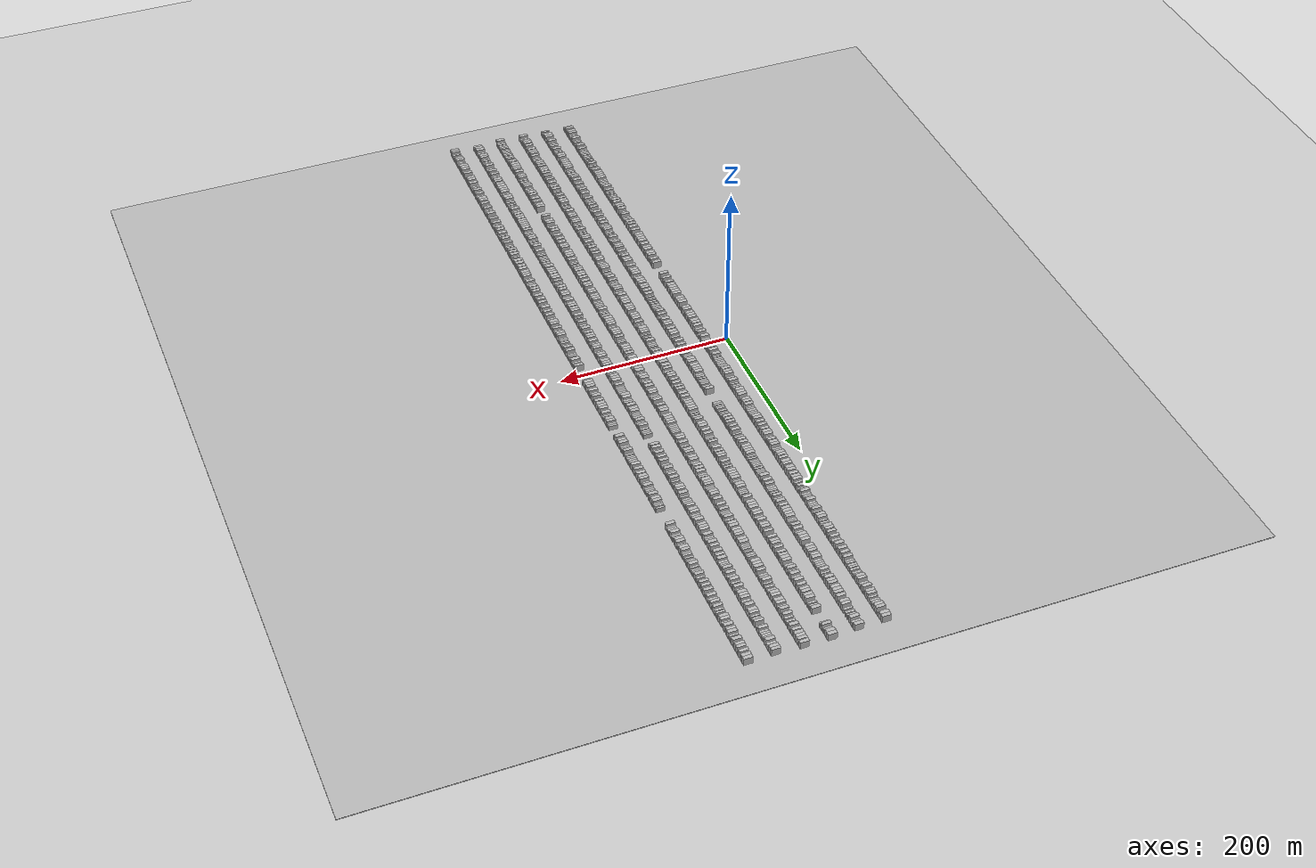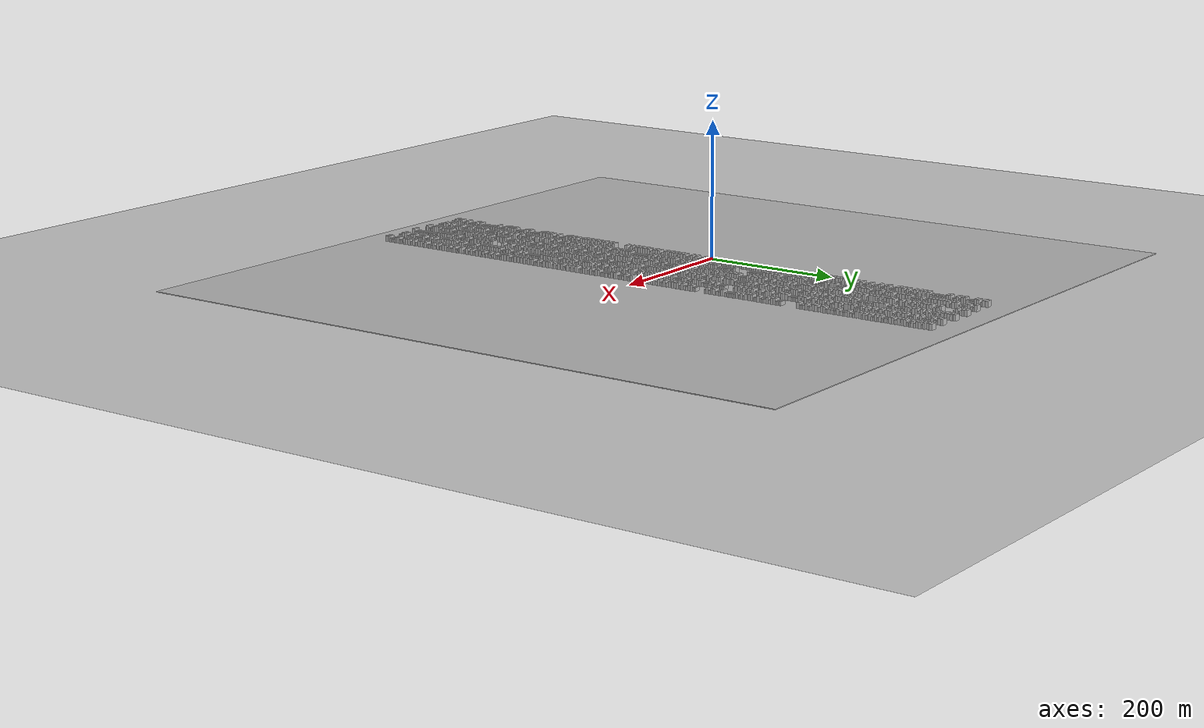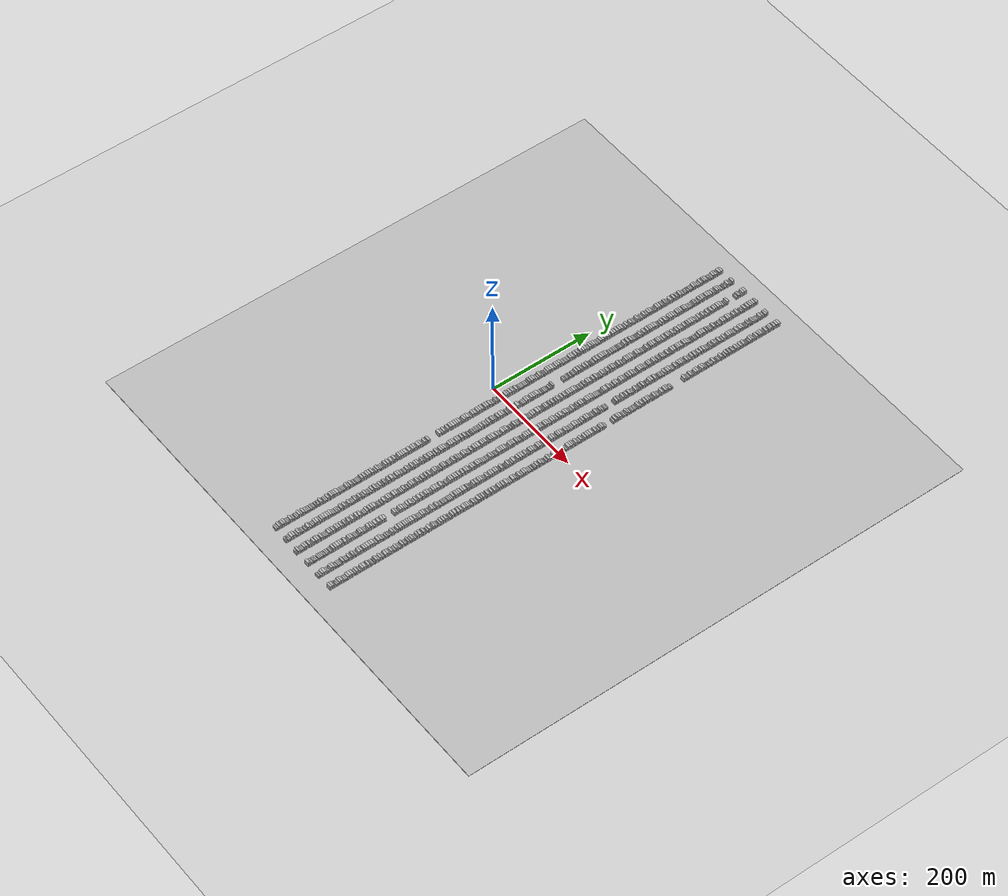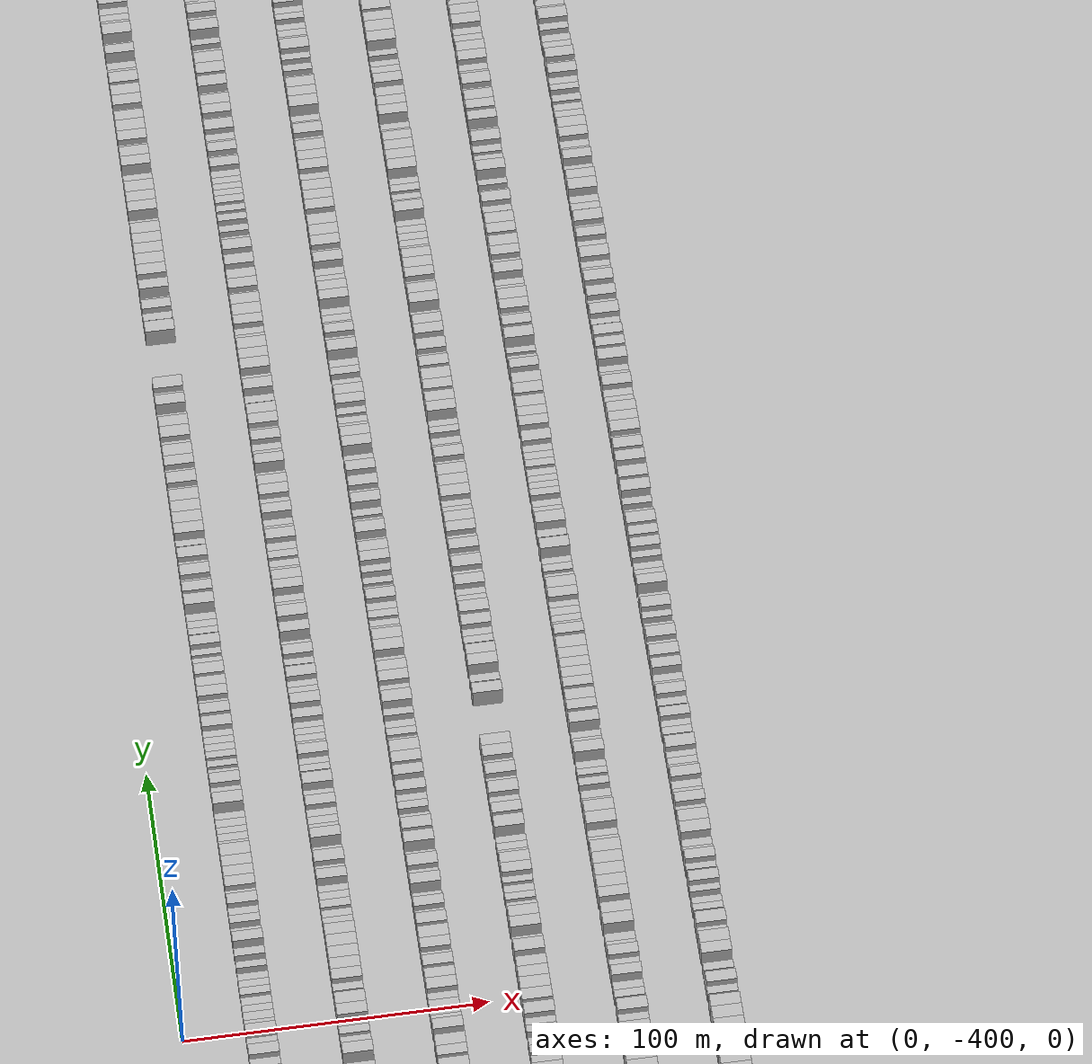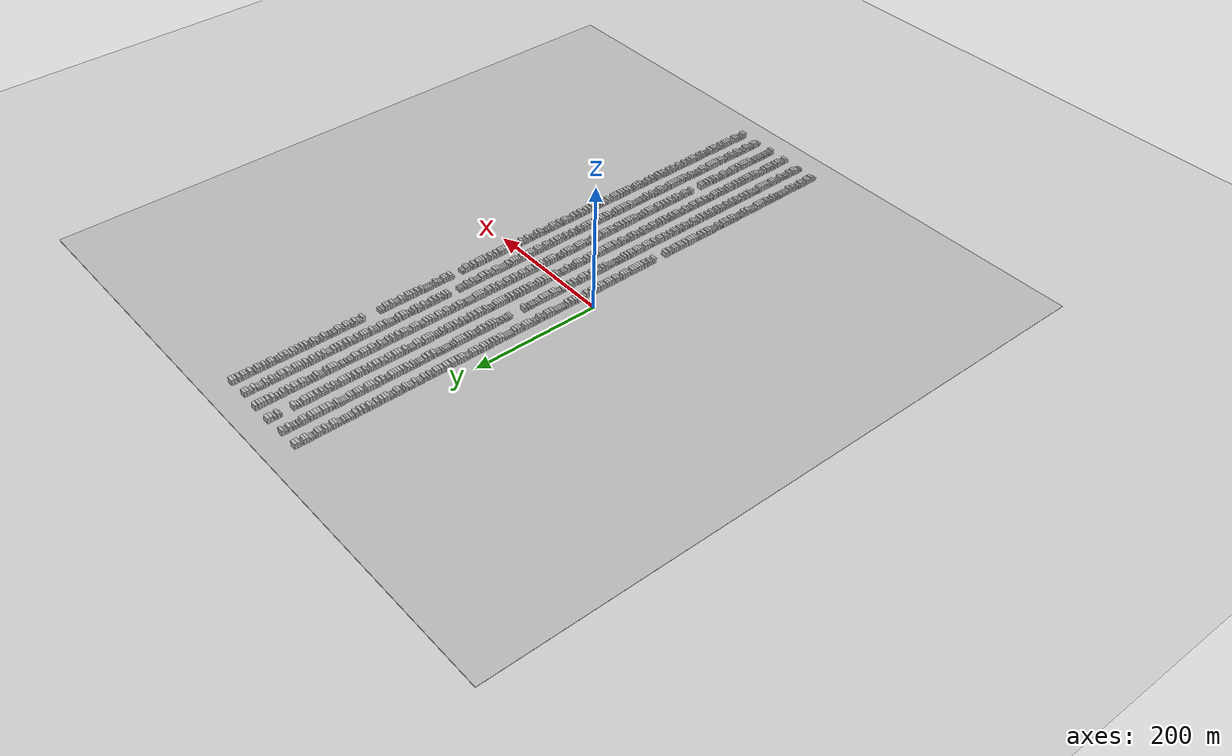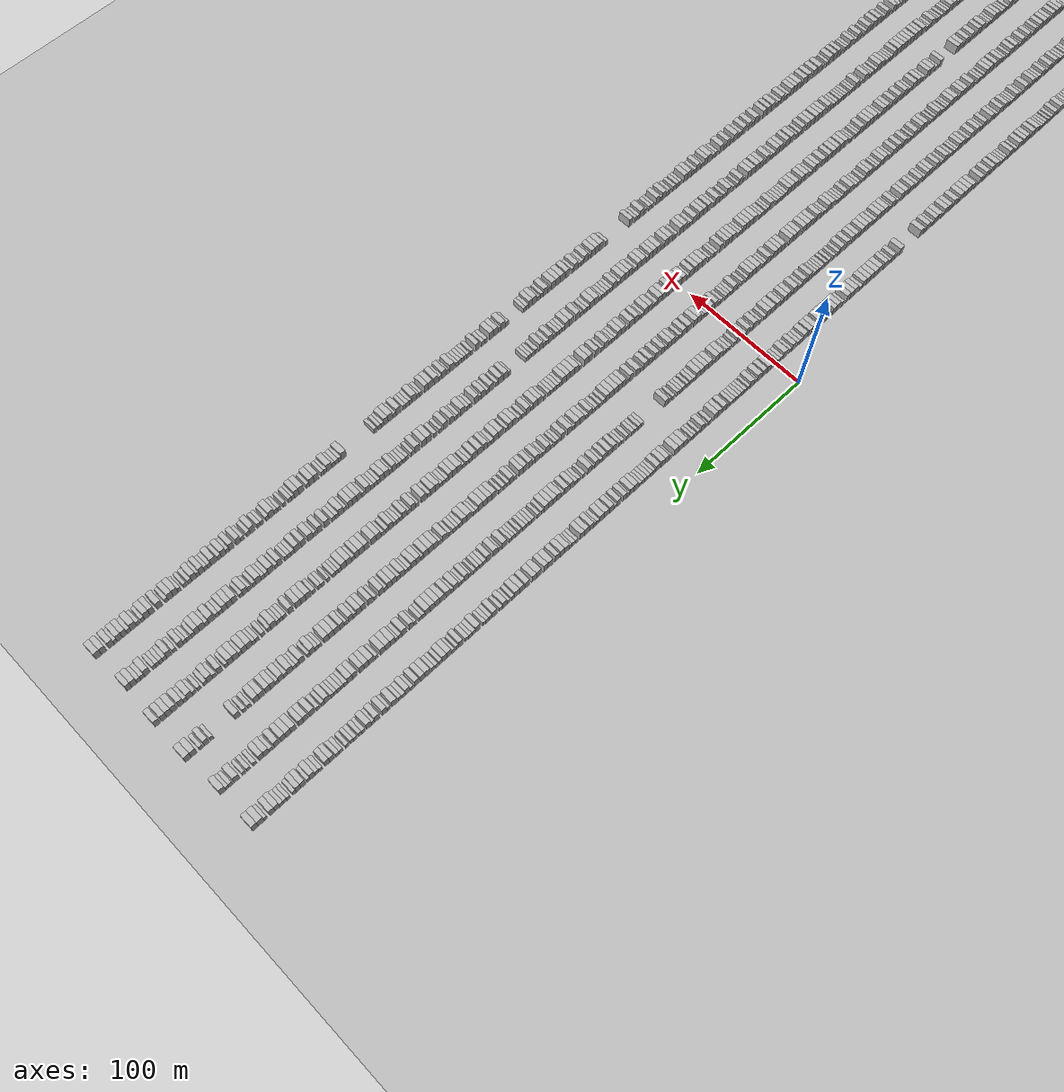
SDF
<sdf version="1.6">
 <world name="default">
  <scene>
   <sky><clouds><speed>12</speed></clouds></sky>
   <ambient>0.4 0.4 0.4 1</ambient>
   <background>0.7 0.7 0.7 1</background>
   <shadows>1</shadows>
  </scene>
  <gravity>0 0 -9.8066</gravity>
  <magnetic_field>6e-06 2.3e-05 -4.2e-05</magnetic_field>
  <physics default="0" name="default_physics" type="ode">
   <ode>
    <solver>
     <type>quick</type>
     <iters>10</iters>
     <sor>1.0</sor>
     <use_dynamic_moi_rescaling>0</use_dynamic_moi_rescaling>
    </solver>
    <constraints>
     <cfm>0</cfm>
     <erp>0.2</erp>
     <contact_max_correcting_vel>100</contact_max_correcting_vel>
     <contact_surface_layer>0.001</contact_surface_layer>
    </constraints>
   </ode>
   <max_step_size>0.004</max_step_size>
   <real_time_factor>1</real_time_factor>
   <real_time_update_rate>250</real_time_update_rate>
  </physics>
  <light name="sun" type="directional">
   <pose>0 0 10 0 0 0</pose>
   <diffuse>0.8 0.8 0.8 1</diffuse>
   <specular>0.2 0.2 0.2 1</specular>
   <attenuation>
    <range>1000</range>
    <constant>0.9</constant>
    <linear>0.01</linear>
    <quadratic>0.001</quadratic>
   </attenuation>
   <direction>-0.5 0.1 -0.9</direction>
  </light>
  <include><name>ground_plane_1</name><uri>model://HANNAS_ground_plane</uri></include>
  <include>
   <name>ground_plane_2</name>
   <uri>model://HANNAS_ground_plane</uri>
   <pose>100 0 0  0 0 0</pose>
  </include>
  <model name="building_1">
   <static>1</static>
   <pose>25.0000 -456.5878 0 0.000000 0.000000 0.000000</pose>
   <link name="link">
    <pose>0 0 3.00 0 0 0</pose>
    <collision name="collision"><geometry><box><size>10.0000 2.8245 6.0000</size></box></geometry></collision>
    <visual name="visual">
     <cast_shadows>0</cast_shadows>
     <geometry><box><size>10.0000 2.8245 6.0000</size></box></geometry>
     <material>
      <script>
       <uri>model://HANNAS_wall/materials/scripts</uri>
       <uri>model://HANNAS_wall/materials/textures</uri>
       <name>vrc/HANNAS_wall</name>
      </script>
     </material>
    </visual>
   </link>
  </model>
  <model name="building_2">
   <static>1</static>
   <pose>25.0000 -453.7290 0 0.000000 0.000000 0.000000</pose>
   <link name="link">
    <pose>0 0 3.00 0 0 0</pose>
    <collision name="collision"><geometry><box><size>10.0000 2.8931 6.0000</size></box></geometry></collision>
    <visual name="visual">
     <cast_shadows>0</cast_shadows>
     <geometry><box><size>10.0000 2.8931 6.0000</size></box></geometry>
     <material>
      <script>
       <uri>model://HANNAS_wall/materials/scripts</uri>
       <uri>model://HANNAS_wall/materials/textures</uri>
       <name>vrc/HANNAS_wall</name>
      </script>
     </material>
    </visual>
   </link>
  </model>
  <model name="building_3">
   <static>1</static>
   <pose>25.0000 -450.3081 0 0.000000 0.000000 0.000000</pose>
   <link name="link">
    <pose>0 0 4.50 0 0 0</pose>
    <collision name="collision"><geometry><box><size>10.0000 3.9486 9.0000</size></box></geometry></collision>
    <visual name="visual">
     <cast_shadows>0</cast_shadows>
     <geometry><box><size>10.0000 3.9486 9.0000</size></box></geometry>
     <material>
      <script>
       <uri>model://HANNAS_wall/materials/scripts</uri>
       <uri>model://HANNAS_wall/materials/textures</uri>
       <name>vrc/HANNAS_wall</name>
      </script>
     </material>
    </visual>
   </link>
  </model>
  <model name="building_4">
   <static>1</static>
   <pose>25.0000 -446.9821 0 0.000000 0.000000 0.000000</pose>
   <link name="link">
    <pose>0 0 3.00 0 0 0</pose>
    <collision name="collision"><geometry><box><size>10.0000 2.7034 6.0000</size></box></geometry></collision>
    <visual name="visual">
     <cast_shadows>0</cast_shadows>
     <geometry><box><size>10.0000 2.7034 6.0000</size></box></geometry>
     <material>
      <script>
       <uri>model://HANNAS_wall/materials/scripts</uri>
       <uri>model://HANNAS_wall/materials/textures</uri>
       <name>vrc/HANNAS_wall</name>
      </script>
     </material>
    </visual>
   </link>
  </model>
  <model name="building_5">
   <static>1</static>
   <pose>25.0000 -443.7848 0 0.000000 0.000000 0.000000</pose>
   <link name="link">
    <pose>0 0 4.50 0 0 0</pose>
    <collision name="collision"><geometry><box><size>10.0000 3.6912 9.0000</size></box></geometry></collision>
    <visual name="visual">
     <cast_shadows>0</cast_shadows>
     <geometry><box><size>10.0000 3.6912 9.0000</size></box></geometry>
     <material>
      <script>
       <uri>model://HANNAS_wall/materials/scripts</uri>
       <uri>model://HANNAS_wall/materials/textures</uri>
       <name>vrc/HANNAS_wall</name>
      </script>
     </material>
    </visual>
   </link>
  </model>
  <model name="building_6">
   <static>1</static>
   <pose>25.0000 -440.0766 0 0.000000 0.000000 0.000000</pose>
   <link name="link">
    <pose>0 0 4.50 0 0 0</pose>
    <collision name="collision"><geometry><box><size>10.0000 3.7251 9.0000</size></box></geometry></collision>
    <visual name="visual">
     <cast_shadows>0</cast_shadows>
     <geometry><box><size>10.0000 3.7251 9.0000</size></box></geometry>
     <material>
      <script>
       <uri>model://HANNAS_wall/materials/scripts</uri>
       <uri>model://HANNAS_wall/materials/textures</uri>
       <name>vrc/HANNAS_wall</name>
      </script>
     </material>
    </visual>
   </link>
  </model>
  <model name="building_7">
   <static>1</static>
   <pose>25.0000 -436.9483 0 0.000000 0.000000 0.000000</pose>
   <link name="link">
    <pose>0 0 3.00 0 0 0</pose>
    <collision name="collision"><geometry><box><size>10.0000 2.5317 6.0000</size></box></geometry></collision>
    <visual name="visual">
     <cast_shadows>0</cast_shadows>
     <geometry><box><size>10.0000 2.5317 6.0000</size></box></geometry>
     <material>
      <script>
       <uri>model://HANNAS_wall/materials/scripts</uri>
       <uri>model://HANNAS_wall/materials/textures</uri>
       <name>vrc/HANNAS_wall</name>
      </script>
     </material>
    </visual>
   </link>
  </model>
  <model name="building_8">
   <static>1</static>
   <pose>25.0000 -434.2681 0 0.000000 0.000000 0.000000</pose>
   <link name="link">
    <pose>0 0 3.00 0 0 0</pose>
    <collision name="collision"><geometry><box><size>10.0000 2.8287 6.0000</size></box></geometry></collision>
    <visual name="visual">
     <cast_shadows>0</cast_shadows>
     <geometry><box><size>10.0000 2.8287 6.0000</size></box></geometry>
     <material>
      <script>
       <uri>model://HANNAS_wall/materials/scripts</uri>
       <uri>model://HANNAS_wall/materials/textures</uri>
       <name>vrc/HANNAS_wall</name>
      </script>
     </material>
    </visual>
   </link>
  </model>
  <model name="building_9">
   <static>1</static>
   <pose>25.0000 -431.4158 0 0.000000 0.000000 0.000000</pose>
   <link name="link">
    <pose>0 0 3.00 0 0 0</pose>
    <collision name="collision"><geometry><box><size>10.0000 2.8757 6.0000</size></box></geometry></collision>
    <visual name="visual">
     <cast_shadows>0</cast_shadows>
     <geometry><box><size>10.0000 2.8757 6.0000</size></box></geometry>
     <material>
      <script>
       <uri>model://HANNAS_wall/materials/scripts</uri>
       <uri>model://HANNAS_wall/materials/textures</uri>
       <name>vrc/HANNAS_wall</name>
      </script>
     </material>
    </visual>
   </link>
  </model>
  <model name="building_10">
   <static>1</static>
   <pose>25.0000 -427.8407 0 0.000000 0.000000 0.000000</pose>
   <link name="link">
    <pose>0 0 4.50 0 0 0</pose>
    <collision name="collision"><geometry><box><size>10.0000 4.2745 9.0000</size></box></geometry></collision>
    <visual name="visual">
     <cast_shadows>0</cast_shadows>
     <geometry><box><size>10.0000 4.2745 9.0000</size></box></geometry>
     <material>
      <script>
       <uri>model://HANNAS_wall/materials/scripts</uri>
       <uri>model://HANNAS_wall/materials/textures</uri>
       <name>vrc/HANNAS_wall</name>
      </script>
     </material>
    </visual>
   </link>
  </model>
  <model name="building_11">
   <static>1</static>
   <pose>25.0000 -424.4925 0 0.000000 0.000000 0.000000</pose>
   <link name="link">
    <pose>0 0 3.00 0 0 0</pose>
    <collision name="collision"><geometry><box><size>10.0000 2.4220 6.0000</size></box></geometry></collision>
    <visual name="visual">
     <cast_shadows>0</cast_shadows>
     <geometry><box><size>10.0000 2.4220 6.0000</size></box></geometry>
     <material>
      <script>
       <uri>model://HANNAS_wall/materials/scripts</uri>
       <uri>model://HANNAS_wall/materials/textures</uri>
       <name>vrc/HANNAS_wall</name>
      </script>
     </material>
    </visual>
   </link>
  </model>
  <model name="building_12">
   <static>1</static>
   <pose>25.0000 -421.7866 0 0.000000 0.000000 0.000000</pose>
   <link name="link">
    <pose>0 0 3.00 0 0 0</pose>
    <collision name="collision"><geometry><box><size>10.0000 2.9898 6.0000</size></box></geometry></collision>
    <visual name="visual">
     <cast_shadows>0</cast_shadows>
     <geometry><box><size>10.0000 2.9898 6.0000</size></box></geometry>
     <material>
      <script>
       <uri>model://HANNAS_wall/materials/scripts</uri>
       <uri>model://HANNAS_wall/materials/textures</uri>
       <name>vrc/HANNAS_wall</name>
      </script>
     </material>
    </visual>
   </link>
  </model>
  <model name="building_13">
   <static>1</static>
   <pose>25.0000 -417.0590 0 0.000000 0.000000 0.000000</pose>
   <link name="link">
    <pose>0 0 3.00 0 0 0</pose>
    <collision name="collision"><geometry><box><size>10.0000 2.4655 6.0000</size></box></geometry></collision>
    <visual name="visual">
     <cast_shadows>0</cast_shadows>
     <geometry><box><size>10.0000 2.4655 6.0000</size></box></geometry>
     <material>
      <script>
       <uri>model://HANNAS_wall/materials/scripts</uri>
       <uri>model://HANNAS_wall/materials/textures</uri>
       <name>vrc/HANNAS_wall</name>
      </script>
     </material>
    </visual>
   </link>
  </model>
  <model name="building_14">
   <static>1</static>
   <pose>25.0000 -414.3582 0 0.000000 0.000000 0.000000</pose>
   <link name="link">
    <pose>0 0 3.00 0 0 0</pose>
    <collision name="collision"><geometry><box><size>10.0000 2.9362 6.0000</size></box></geometry></collision>
    <visual name="visual">
     <cast_shadows>0</cast_shadows>
     <geometry><box><size>10.0000 2.9362 6.0000</size></box></geometry>
     <material>
      <script>
       <uri>model://HANNAS_wall/materials/scripts</uri>
       <uri>model://HANNAS_wall/materials/textures</uri>
       <name>vrc/HANNAS_wall</name>
      </script>
     </material>
    </visual>
   </link>
  </model>
  <model name="building_15">
   <static>1</static>
   <pose>25.0000 -410.9005 0 0.000000 0.000000 0.000000</pose>
   <link name="link">
    <pose>0 0 4.50 0 0 0</pose>
    <collision name="collision"><geometry><box><size>10.0000 3.9791 9.0000</size></box></geometry></collision>
    <visual name="visual">
     <cast_shadows>0</cast_shadows>
     <geometry><box><size>10.0000 3.9791 9.0000</size></box></geometry>
     <material>
      <script>
       <uri>model://HANNAS_wall/materials/scripts</uri>
       <uri>model://HANNAS_wall/materials/textures</uri>
       <name>vrc/HANNAS_wall</name>
      </script>
     </material>
    </visual>
   </link>
  </model>
  <model name="building_16">
   <static>1</static>
   <pose>25.0000 -406.5454 0 0.000000 0.000000 0.000000</pose>
   <link name="link">
    <pose>0 0 3.00 0 0 0</pose>
    <collision name="collision"><geometry><box><size>10.0000 2.7313 6.0000</size></box></geometry></collision>
    <visual name="visual">
     <cast_shadows>0</cast_shadows>
     <geometry><box><size>10.0000 2.7313 6.0000</size></box></geometry>
     <material>
      <script>
       <uri>model://HANNAS_wall/materials/scripts</uri>
       <uri>model://HANNAS_wall/materials/textures</uri>
       <name>vrc/HANNAS_wall</name>
      </script>
     </material>
    </visual>
   </link>
  </model>
  <model name="building_17">
   <static>1</static>
   <pose>25.0000 -403.3031 0 0.000000 0.000000 0.000000</pose>
   <link name="link">
    <pose>0 0 4.50 0 0 0</pose>
    <collision name="collision"><geometry><box><size>10.0000 3.7533 9.0000</size></box></geometry></collision>
    <visual name="visual">
     <cast_shadows>0</cast_shadows>
     <geometry><box><size>10.0000 3.7533 9.0000</size></box></geometry>
     <material>
      <script>
       <uri>model://HANNAS_wall/materials/scripts</uri>
       <uri>model://HANNAS_wall/materials/textures</uri>
       <name>vrc/HANNAS_wall</name>
      </script>
     </material>
    </visual>
   </link>
  </model>
  <model name="building_18">
   <static>1</static>
   <pose>25.0000 -400.0018 0 0.000000 0.000000 0.000000</pose>
   <link name="link">
    <pose>0 0 3.00 0 0 0</pose>
    <collision name="collision"><geometry><box><size>10.0000 2.8493 6.0000</size></box></geometry></collision>
    <visual name="visual">
     <cast_shadows>0</cast_shadows>
     <geometry><box><size>10.0000 2.8493 6.0000</size></box></geometry>
     <material>
      <script>
       <uri>model://HANNAS_wall/materials/scripts</uri>
       <uri>model://HANNAS_wall/materials/textures</uri>
       <name>vrc/HANNAS_wall</name>
      </script>
     </material>
    </visual>
   </link>
  </model>
  <model name="building_19">
   <static>1</static>
   <pose>25.0000 -397.0880 0 0.000000 0.000000 0.000000</pose>
   <link name="link">
    <pose>0 0 3.00 0 0 0</pose>
    <collision name="collision"><geometry><box><size>10.0000 2.9783 6.0000</size></box></geometry></collision>
    <visual name="visual">
     <cast_shadows>0</cast_shadows>
     <geometry><box><size>10.0000 2.9783 6.0000</size></box></geometry>
     <material>
      <script>
       <uri>model://HANNAS_wall/materials/scripts</uri>
       <uri>model://HANNAS_wall/materials/textures</uri>
       <name>vrc/HANNAS_wall</name>
      </script>
     </material>
    </visual>
   </link>
  </model>
  <model name="building_20">
   <static>1</static>
   <pose>25.0000 -394.3391 0 0.000000 0.000000 0.000000</pose>
   <link name="link">
    <pose>0 0 3.00 0 0 0</pose>
    <collision name="collision"><geometry><box><size>10.0000 2.5194 6.0000</size></box></geometry></collision>
    <visual name="visual">
     <cast_shadows>0</cast_shadows>
     <geometry><box><size>10.0000 2.5194 6.0000</size></box></geometry>
     <material>
      <script>
       <uri>model://HANNAS_wall/materials/scripts</uri>
       <uri>model://HANNAS_wall/materials/textures</uri>
       <name>vrc/HANNAS_wall</name>
      </script>
     </material>
    </visual>
   </link>
  </model>
  <model name="building_21">
   <static>1</static>
   <pose>25.0000 -391.6232 0 0.000000 0.000000 0.000000</pose>
   <link name="link">
    <pose>0 0 3.00 0 0 0</pose>
    <collision name="collision"><geometry><box><size>10.0000 2.9125 6.0000</size></box></geometry></collision>
    <visual name="visual">
     <cast_shadows>0</cast_shadows>
     <geometry><box><size>10.0000 2.9125 6.0000</size></box></geometry>
     <material>
      <script>
       <uri>model://HANNAS_wall/materials/scripts</uri>
       <uri>model://HANNAS_wall/materials/textures</uri>
       <name>vrc/HANNAS_wall</name>
      </script>
     </material>
    </visual>
   </link>
  </model>
  <model name="building_22">
   <static>1</static>
   <pose>25.0000 -387.7908 0 0.000000 0.000000 0.000000</pose>
   <link name="link">
    <pose>0 0 3.00 0 0 0</pose>
    <collision name="collision"><geometry><box><size>10.0000 2.7523 6.0000</size></box></geometry></collision>
    <visual name="visual">
     <cast_shadows>0</cast_shadows>
     <geometry><box><size>10.0000 2.7523 6.0000</size></box></geometry>
     <material>
      <script>
       <uri>model://HANNAS_wall/materials/scripts</uri>
       <uri>model://HANNAS_wall/materials/textures</uri>
       <name>vrc/HANNAS_wall</name>
      </script>
     </material>
    </visual>
   </link>
  </model>
  <model name="building_23">
   <static>1</static>
   <pose>25.0000 -385.1148 0 0.000000 0.000000 0.000000</pose>
   <link name="link">
    <pose>0 0 3.00 0 0 0</pose>
    <collision name="collision"><geometry><box><size>10.0000 2.5996 6.0000</size></box></geometry></collision>
    <visual name="visual">
     <cast_shadows>0</cast_shadows>
     <geometry><box><size>10.0000 2.5996 6.0000</size></box></geometry>
     <material>
      <script>
       <uri>model://HANNAS_wall/materials/scripts</uri>
       <uri>model://HANNAS_wall/materials/textures</uri>
       <name>vrc/HANNAS_wall</name>
      </script>
     </material>
    </visual>
   </link>
  </model>
  <model name="building_24">
   <static>1</static>
   <pose>25.0000 -382.5200 0 0.000000 0.000000 0.000000</pose>
   <link name="link">
    <pose>0 0 3.00 0 0 0</pose>
    <collision name="collision"><geometry><box><size>10.0000 2.5900 6.0000</size></box></geometry></collision>
    <visual name="visual">
     <cast_shadows>0</cast_shadows>
     <geometry><box><size>10.0000 2.5900 6.0000</size></box></geometry>
     <material>
      <script>
       <uri>model://HANNAS_wall/materials/scripts</uri>
       <uri>model://HANNAS_wall/materials/textures</uri>
       <name>vrc/HANNAS_wall</name>
      </script>
     </material>
    </visual>
   </link>
  </model>
  <model name="building_25">
   <static>1</static>
   <pose>25.0000 -377.9569 0 0.000000 0.000000 0.000000</pose>
   <link name="link">
    <pose>0 0 3.00 0 0 0</pose>
    <collision name="collision"><geometry><box><size>10.0000 2.5362 6.0000</size></box></geometry></collision>
    <visual name="visual">
     <cast_shadows>0</cast_shadows>
     <geometry><box><size>10.0000 2.5362 6.0000</size></box></geometry>
     <material>
      <script>
       <uri>model://HANNAS_wall/materials/scripts</uri>
       <uri>model://HANNAS_wall/materials/textures</uri>
       <name>vrc/HANNAS_wall</name>
      </script>
     </material>
    </visual>
   </link>
  </model>
  <model name="building_26">
   <static>1</static>
   <pose>25.0000 -373.1911 0 0.000000 0.000000 0.000000</pose>
   <link name="link">
    <pose>0 0 3.00 0 0 0</pose>
    <collision name="collision"><geometry><box><size>10.0000 2.9954 6.0000</size></box></geometry></collision>
    <visual name="visual">
     <cast_shadows>0</cast_shadows>
     <geometry><box><size>10.0000 2.9954 6.0000</size></box></geometry>
     <material>
      <script>
       <uri>model://HANNAS_wall/materials/scripts</uri>
       <uri>model://HANNAS_wall/materials/textures</uri>
       <name>vrc/HANNAS_wall</name>
      </script>
     </material>
    </visual>
   </link>
  </model>
  <model name="building_27">
   <static>1</static>
   <pose>25.0000 -368.8588 0 0.000000 0.000000 0.000000</pose>
   <link name="link">
    <pose>0 0 4.50 0 0 0</pose>
    <collision name="collision"><geometry><box><size>10.0000 3.6692 9.0000</size></box></geometry></collision>
    <visual name="visual">
     <cast_shadows>0</cast_shadows>
     <geometry><box><size>10.0000 3.6692 9.0000</size></box></geometry>
     <material>
      <script>
       <uri>model://HANNAS_wall/materials/scripts</uri>
       <uri>model://HANNAS_wall/materials/textures</uri>
       <name>vrc/HANNAS_wall</name>
      </script>
     </material>
    </visual>
   </link>
  </model>
  <model name="building_28">
   <static>1</static>
   <pose>25.0000 -365.6581 0 0.000000 0.000000 0.000000</pose>
   <link name="link">
    <pose>0 0 3.00 0 0 0</pose>
    <collision name="collision"><geometry><box><size>10.0000 2.7323 6.0000</size></box></geometry></collision>
    <visual name="visual">
     <cast_shadows>0</cast_shadows>
     <geometry><box><size>10.0000 2.7323 6.0000</size></box></geometry>
     <material>
      <script>
       <uri>model://HANNAS_wall/materials/scripts</uri>
       <uri>model://HANNAS_wall/materials/textures</uri>
       <name>vrc/HANNAS_wall</name>
      </script>
     </material>
    </visual>
   </link>
  </model>
  <model name="building_29">
   <static>1</static>
   <pose>25.0000 -360.8342 0 0.000000 0.000000 0.000000</pose>
   <link name="link">
    <pose>0 0 3.00 0 0 0</pose>
    <collision name="collision"><geometry><box><size>10.0000 2.9154 6.0000</size></box></geometry></collision>
    <visual name="visual">
     <cast_shadows>0</cast_shadows>
     <geometry><box><size>10.0000 2.9154 6.0000</size></box></geometry>
     <material>
      <script>
       <uri>model://HANNAS_wall/materials/scripts</uri>
       <uri>model://HANNAS_wall/materials/textures</uri>
       <name>vrc/HANNAS_wall</name>
      </script>
     </material>
    </visual>
   </link>
  </model>
  <model name="building_30">
   <static>1</static>
   <pose>25.0000 -358.0211 0 0.000000 0.000000 0.000000</pose>
   <link name="link">
    <pose>0 0 3.00 0 0 0</pose>
    <collision name="collision"><geometry><box><size>10.0000 2.7110 6.0000</size></box></geometry></collision>
    <visual name="visual">
     <cast_shadows>0</cast_shadows>
     <geometry><box><size>10.0000 2.7110 6.0000</size></box></geometry>
     <material>
      <script>
       <uri>model://HANNAS_wall/materials/scripts</uri>
       <uri>model://HANNAS_wall/materials/textures</uri>
       <name>vrc/HANNAS_wall</name>
      </script>
     </material>
    </visual>
   </link>
  </model>
  <model name="building_31">
   <static>1</static>
   <pose>25.0000 -354.7402 0 0.000000 0.000000 0.000000</pose>
   <link name="link">
    <pose>0 0 4.50 0 0 0</pose>
    <collision name="collision"><geometry><box><size>10.0000 3.8507 9.0000</size></box></geometry></collision>
    <visual name="visual">
     <cast_shadows>0</cast_shadows>
     <geometry><box><size>10.0000 3.8507 9.0000</size></box></geometry>
     <material>
      <script>
       <uri>model://HANNAS_wall/materials/scripts</uri>
       <uri>model://HANNAS_wall/materials/textures</uri>
       <name>vrc/HANNAS_wall</name>
      </script>
     </material>
    </visual>
   </link>
  </model>
  <model name="building_32">
   <static>1</static>
   <pose>25.0000 -351.4848 0 0.000000 0.000000 0.000000</pose>
   <link name="link">
    <pose>0 0 3.00 0 0 0</pose>
    <collision name="collision"><geometry><box><size>10.0000 2.6602 6.0000</size></box></geometry></collision>
    <visual name="visual">
     <cast_shadows>0</cast_shadows>
     <geometry><box><size>10.0000 2.6602 6.0000</size></box></geometry>
     <material>
      <script>
       <uri>model://HANNAS_wall/materials/scripts</uri>
       <uri>model://HANNAS_wall/materials/textures</uri>
       <name>vrc/HANNAS_wall</name>
      </script>
     </material>
    </visual>
   </link>
  </model>
  <model name="building_33">
   <static>1</static>
   <pose>25.0000 -348.1988 0 0.000000 0.000000 0.000000</pose>
   <link name="link">
    <pose>0 0 4.50 0 0 0</pose>
    <collision name="collision"><geometry><box><size>10.0000 3.9120 9.0000</size></box></geometry></collision>
    <visual name="visual">
     <cast_shadows>0</cast_shadows>
     <geometry><box><size>10.0000 3.9120 9.0000</size></box></geometry>
     <material>
      <script>
       <uri>model://HANNAS_wall/materials/scripts</uri>
       <uri>model://HANNAS_wall/materials/textures</uri>
       <name>vrc/HANNAS_wall</name>
      </script>
     </material>
    </visual>
   </link>
  </model>
  <model name="building_34">
   <static>1</static>
   <pose>25.0000 -344.3590 0 0.000000 0.000000 0.000000</pose>
   <link name="link">
    <pose>0 0 4.50 0 0 0</pose>
    <collision name="collision"><geometry><box><size>10.0000 3.7675 9.0000</size></box></geometry></collision>
    <visual name="visual">
     <cast_shadows>0</cast_shadows>
     <geometry><box><size>10.0000 3.7675 9.0000</size></box></geometry>
     <material>
      <script>
       <uri>model://HANNAS_wall/materials/scripts</uri>
       <uri>model://HANNAS_wall/materials/textures</uri>
       <name>vrc/HANNAS_wall</name>
      </script>
     </material>
    </visual>
   </link>
  </model>
  <model name="building_35">
   <static>1</static>
   <pose>25.0000 -340.5251 0 0.000000 0.000000 0.000000</pose>
   <link name="link">
    <pose>0 0 4.50 0 0 0</pose>
    <collision name="collision"><geometry><box><size>10.0000 3.9004 9.0000</size></box></geometry></collision>
    <visual name="visual">
     <cast_shadows>0</cast_shadows>
     <geometry><box><size>10.0000 3.9004 9.0000</size></box></geometry>
     <material>
      <script>
       <uri>model://HANNAS_wall/materials/scripts</uri>
       <uri>model://HANNAS_wall/materials/textures</uri>
       <name>vrc/HANNAS_wall</name>
      </script>
     </material>
    </visual>
   </link>
  </model>
  <model name="building_36">
   <static>1</static>
   <pose>25.0000 -336.3470 0 0.000000 0.000000 0.000000</pose>
   <link name="link">
    <pose>0 0 4.50 0 0 0</pose>
    <collision name="collision"><geometry><box><size>10.0000 4.4558 9.0000</size></box></geometry></collision>
    <visual name="visual">
     <cast_shadows>0</cast_shadows>
     <geometry><box><size>10.0000 4.4558 9.0000</size></box></geometry>
     <material>
      <script>
       <uri>model://HANNAS_wall/materials/scripts</uri>
       <uri>model://HANNAS_wall/materials/textures</uri>
       <name>vrc/HANNAS_wall</name>
      </script>
     </material>
    </visual>
   </link>
  </model>
  <model name="building_37">
   <static>1</static>
   <pose>25.0000 -332.8146 0 0.000000 0.000000 0.000000</pose>
   <link name="link">
    <pose>0 0 3.00 0 0 0</pose>
    <collision name="collision"><geometry><box><size>10.0000 2.6089 6.0000</size></box></geometry></collision>
    <visual name="visual">
     <cast_shadows>0</cast_shadows>
     <geometry><box><size>10.0000 2.6089 6.0000</size></box></geometry>
     <material>
      <script>
       <uri>model://HANNAS_wall/materials/scripts</uri>
       <uri>model://HANNAS_wall/materials/textures</uri>
       <name>vrc/HANNAS_wall</name>
      </script>
     </material>
    </visual>
   </link>
  </model>
  <model name="building_38">
   <static>1</static>
   <pose>25.0000 -330.1324 0 0.000000 0.000000 0.000000</pose>
   <link name="link">
    <pose>0 0 3.00 0 0 0</pose>
    <collision name="collision"><geometry><box><size>10.0000 2.7555 6.0000</size></box></geometry></collision>
    <visual name="visual">
     <cast_shadows>0</cast_shadows>
     <geometry><box><size>10.0000 2.7555 6.0000</size></box></geometry>
     <material>
      <script>
       <uri>model://HANNAS_wall/materials/scripts</uri>
       <uri>model://HANNAS_wall/materials/textures</uri>
       <name>vrc/HANNAS_wall</name>
      </script>
     </material>
    </visual>
   </link>
  </model>
  <model name="building_39">
   <static>1</static>
   <pose>25.0000 -327.5195 0 0.000000 0.000000 0.000000</pose>
   <link name="link">
    <pose>0 0 3.00 0 0 0</pose>
    <collision name="collision"><geometry><box><size>10.0000 2.4704 6.0000</size></box></geometry></collision>
    <visual name="visual">
     <cast_shadows>0</cast_shadows>
     <geometry><box><size>10.0000 2.4704 6.0000</size></box></geometry>
     <material>
      <script>
       <uri>model://HANNAS_wall/materials/scripts</uri>
       <uri>model://HANNAS_wall/materials/textures</uri>
       <name>vrc/HANNAS_wall</name>
      </script>
     </material>
    </visual>
   </link>
  </model>
  <model name="building_40">
   <static>1</static>
   <pose>25.0000 -324.8367 0 0.000000 0.000000 0.000000</pose>
   <link name="link">
    <pose>0 0 3.00 0 0 0</pose>
    <collision name="collision"><geometry><box><size>10.0000 2.8952 6.0000</size></box></geometry></collision>
    <visual name="visual">
     <cast_shadows>0</cast_shadows>
     <geometry><box><size>10.0000 2.8952 6.0000</size></box></geometry>
     <material>
      <script>
       <uri>model://HANNAS_wall/materials/scripts</uri>
       <uri>model://HANNAS_wall/materials/textures</uri>
       <name>vrc/HANNAS_wall</name>
      </script>
     </material>
    </visual>
   </link>
  </model>
  <model name="building_41">
   <static>1</static>
   <pose>25.0000 -322.1112 0 0.000000 0.000000 0.000000</pose>
   <link name="link">
    <pose>0 0 3.00 0 0 0</pose>
    <collision name="collision"><geometry><box><size>10.0000 2.5558 6.0000</size></box></geometry></collision>
    <visual name="visual">
     <cast_shadows>0</cast_shadows>
     <geometry><box><size>10.0000 2.5558 6.0000</size></box></geometry>
     <material>
      <script>
       <uri>model://HANNAS_wall/materials/scripts</uri>
       <uri>model://HANNAS_wall/materials/textures</uri>
       <name>vrc/HANNAS_wall</name>
      </script>
     </material>
    </visual>
   </link>
  </model>
  <model name="building_42">
   <static>1</static>
   <pose>25.0000 -316.7011 0 0.000000 0.000000 0.000000</pose>
   <link name="link">
    <pose>0 0 4.50 0 0 0</pose>
    <collision name="collision"><geometry><box><size>10.0000 4.2643 9.0000</size></box></geometry></collision>
    <visual name="visual">
     <cast_shadows>0</cast_shadows>
     <geometry><box><size>10.0000 4.2643 9.0000</size></box></geometry>
     <material>
      <script>
       <uri>model://HANNAS_wall/materials/scripts</uri>
       <uri>model://HANNAS_wall/materials/textures</uri>
       <name>vrc/HANNAS_wall</name>
      </script>
     </material>
    </visual>
   </link>
  </model>
  <model name="building_43">
   <static>1</static>
   <pose>25.0000 -312.3109 0 0.000000 0.000000 0.000000</pose>
   <link name="link">
    <pose>0 0 3.00 0 0 0</pose>
    <collision name="collision"><geometry><box><size>10.0000 2.5159 6.0000</size></box></geometry></collision>
    <visual name="visual">
     <cast_shadows>0</cast_shadows>
     <geometry><box><size>10.0000 2.5159 6.0000</size></box></geometry>
     <material>
      <script>
       <uri>model://HANNAS_wall/materials/scripts</uri>
       <uri>model://HANNAS_wall/materials/textures</uri>
       <name>vrc/HANNAS_wall</name>
      </script>
     </material>
    </visual>
   </link>
  </model>
  <model name="building_44">
   <static>1</static>
   <pose>25.0000 -309.0761 0 0.000000 0.000000 0.000000</pose>
   <link name="link">
    <pose>0 0 4.50 0 0 0</pose>
    <collision name="collision"><geometry><box><size>10.0000 3.9538 9.0000</size></box></geometry></collision>
    <visual name="visual">
     <cast_shadows>0</cast_shadows>
     <geometry><box><size>10.0000 3.9538 9.0000</size></box></geometry>
     <material>
      <script>
       <uri>model://HANNAS_wall/materials/scripts</uri>
       <uri>model://HANNAS_wall/materials/textures</uri>
       <name>vrc/HANNAS_wall</name>
      </script>
     </material>
    </visual>
   </link>
  </model>
  <model name="building_45">
   <static>1</static>
   <pose>25.0000 -305.6563 0 0.000000 0.000000 0.000000</pose>
   <link name="link">
    <pose>0 0 3.00 0 0 0</pose>
    <collision name="collision"><geometry><box><size>10.0000 2.8857 6.0000</size></box></geometry></collision>
    <visual name="visual">
     <cast_shadows>0</cast_shadows>
     <geometry><box><size>10.0000 2.8857 6.0000</size></box></geometry>
     <material>
      <script>
       <uri>model://HANNAS_wall/materials/scripts</uri>
       <uri>model://HANNAS_wall/materials/textures</uri>
       <name>vrc/HANNAS_wall</name>
      </script>
     </material>
    </visual>
   </link>
  </model>
  <model name="building_46">
   <static>1</static>
   <pose>25.0000 -302.0009 0 0.000000 0.000000 0.000000</pose>
   <link name="link">
    <pose>0 0 3.00 0 0 0</pose>
    <collision name="collision"><geometry><box><size>10.0000 2.4250 6.0000</size></box></geometry></collision>
    <visual name="visual">
     <cast_shadows>0</cast_shadows>
     <geometry><box><size>10.0000 2.4250 6.0000</size></box></geometry>
     <material>
      <script>
       <uri>model://HANNAS_wall/materials/scripts</uri>
       <uri>model://HANNAS_wall/materials/textures</uri>
       <name>vrc/HANNAS_wall</name>
      </script>
     </material>
    </visual>
   </link>
  </model>
  <model name="building_47">
   <static>1</static>
   <pose>25.0000 -298.4936 0 0.000000 0.000000 0.000000</pose>
   <link name="link">
    <pose>0 0 3.00 0 0 0</pose>
    <collision name="collision"><geometry><box><size>10.0000 2.5896 6.0000</size></box></geometry></collision>
    <visual name="visual">
     <cast_shadows>0</cast_shadows>
     <geometry><box><size>10.0000 2.5896 6.0000</size></box></geometry>
     <material>
      <script>
       <uri>model://HANNAS_wall/materials/scripts</uri>
       <uri>model://HANNAS_wall/materials/textures</uri>
       <name>vrc/HANNAS_wall</name>
      </script>
     </material>
    </visual>
   </link>
  </model>
  <model name="building_48">
   <static>1</static>
   <pose>25.0000 -295.8456 0 0.000000 0.000000 0.000000</pose>
   <link name="link">
    <pose>0 0 3.00 0 0 0</pose>
    <collision name="collision"><geometry><box><size>10.0000 2.7064 6.0000</size></box></geometry></collision>
    <visual name="visual">
     <cast_shadows>0</cast_shadows>
     <geometry><box><size>10.0000 2.7064 6.0000</size></box></geometry>
     <material>
      <script>
       <uri>model://HANNAS_wall/materials/scripts</uri>
       <uri>model://HANNAS_wall/materials/textures</uri>
       <name>vrc/HANNAS_wall</name>
      </script>
     </material>
    </visual>
   </link>
  </model>
  <model name="building_49">
   <static>1</static>
   <pose>25.0000 -293.1895 0 0.000000 0.000000 0.000000</pose>
   <link name="link">
    <pose>0 0 3.00 0 0 0</pose>
    <collision name="collision"><geometry><box><size>10.0000 2.6058 6.0000</size></box></geometry></collision>
    <visual name="visual">
     <cast_shadows>0</cast_shadows>
     <geometry><box><size>10.0000 2.6058 6.0000</size></box></geometry>
     <material>
      <script>
       <uri>model://HANNAS_wall/materials/scripts</uri>
       <uri>model://HANNAS_wall/materials/textures</uri>
       <name>vrc/HANNAS_wall</name>
      </script>
     </material>
    </visual>
   </link>
  </model>
  <model name="building_50">
   <static>1</static>
   <pose>25.0000 -290.6350 0 0.000000 0.000000 0.000000</pose>
   <link name="link">
    <pose>0 0 3.00 0 0 0</pose>
    <collision name="collision"><geometry><box><size>10.0000 2.5033 6.0000</size></box></geometry></collision>
    <visual name="visual">
     <cast_shadows>0</cast_shadows>
     <geometry><box><size>10.0000 2.5033 6.0000</size></box></geometry>
     <material>
      <script>
       <uri>model://HANNAS_wall/materials/scripts</uri>
       <uri>model://HANNAS_wall/materials/textures</uri>
       <name>vrc/HANNAS_wall</name>
      </script>
     </material>
    </visual>
   </link>
  </model>
  <model name="building_51">
   <static>1</static>
   <pose>25.0000 -287.3302 0 0.000000 0.000000 0.000000</pose>
   <link name="link">
    <pose>0 0 4.50 0 0 0</pose>
    <collision name="collision"><geometry><box><size>10.0000 4.1063 9.0000</size></box></geometry></collision>
    <visual name="visual">
     <cast_shadows>0</cast_shadows>
     <geometry><box><size>10.0000 4.1063 9.0000</size></box></geometry>
     <material>
      <script>
       <uri>model://HANNAS_wall/materials/scripts</uri>
       <uri>model://HANNAS_wall/materials/textures</uri>
       <name>vrc/HANNAS_wall</name>
      </script>
     </material>
    </visual>
   </link>
  </model>
  <model name="building_52">
   <static>1</static>
   <pose>25.0000 -282.3142 0 0.000000 0.000000 0.000000</pose>
   <link name="link">
    <pose>0 0 4.50 0 0 0</pose>
    <collision name="collision"><geometry><box><size>10.0000 3.9257 9.0000</size></box></geometry></collision>
    <visual name="visual">
     <cast_shadows>0</cast_shadows>
     <geometry><box><size>10.0000 3.9257 9.0000</size></box></geometry>
     <material>
      <script>
       <uri>model://HANNAS_wall/materials/scripts</uri>
       <uri>model://HANNAS_wall/materials/textures</uri>
       <name>vrc/HANNAS_wall</name>
      </script>
     </material>
    </visual>
   </link>
  </model>
  <model name="building_53">
   <static>1</static>
   <pose>25.0000 -278.9817 0 0.000000 0.000000 0.000000</pose>
   <link name="link">
    <pose>0 0 3.00 0 0 0</pose>
    <collision name="collision"><geometry><box><size>10.0000 2.7393 6.0000</size></box></geometry></collision>
    <visual name="visual">
     <cast_shadows>0</cast_shadows>
     <geometry><box><size>10.0000 2.7393 6.0000</size></box></geometry>
     <material>
      <script>
       <uri>model://HANNAS_wall/materials/scripts</uri>
       <uri>model://HANNAS_wall/materials/textures</uri>
       <name>vrc/HANNAS_wall</name>
      </script>
     </material>
    </visual>
   </link>
  </model>
  <model name="building_54">
   <static>1</static>
   <pose>25.0000 -275.6976 0 0.000000 0.000000 0.000000</pose>
   <link name="link">
    <pose>0 0 4.50 0 0 0</pose>
    <collision name="collision"><geometry><box><size>10.0000 3.8290 9.0000</size></box></geometry></collision>
    <visual name="visual">
     <cast_shadows>0</cast_shadows>
     <geometry><box><size>10.0000 3.8290 9.0000</size></box></geometry>
     <material>
      <script>
       <uri>model://HANNAS_wall/materials/scripts</uri>
       <uri>model://HANNAS_wall/materials/textures</uri>
       <name>vrc/HANNAS_wall</name>
      </script>
     </material>
    </visual>
   </link>
  </model>
  <model name="building_55">
   <static>1</static>
   <pose>25.0000 -271.9595 0 0.000000 0.000000 0.000000</pose>
   <link name="link">
    <pose>0 0 4.50 0 0 0</pose>
    <collision name="collision"><geometry><box><size>10.0000 3.6472 9.0000</size></box></geometry></collision>
    <visual name="visual">
     <cast_shadows>0</cast_shadows>
     <geometry><box><size>10.0000 3.6472 9.0000</size></box></geometry>
     <material>
      <script>
       <uri>model://HANNAS_wall/materials/scripts</uri>
       <uri>model://HANNAS_wall/materials/textures</uri>
       <name>vrc/HANNAS_wall</name>
      </script>
     </material>
    </visual>
   </link>
  </model>
  <model name="building_56">
   <static>1</static>
   <pose>25.0000 -267.0310 0 0.000000 0.000000 0.000000</pose>
   <link name="link">
    <pose>0 0 4.50 0 0 0</pose>
    <collision name="collision"><geometry><box><size>10.0000 4.2097 9.0000</size></box></geometry></collision>
    <visual name="visual">
     <cast_shadows>0</cast_shadows>
     <geometry><box><size>10.0000 4.2097 9.0000</size></box></geometry>
     <material>
      <script>
       <uri>model://HANNAS_wall/materials/scripts</uri>
       <uri>model://HANNAS_wall/materials/textures</uri>
       <name>vrc/HANNAS_wall</name>
      </script>
     </material>
    </visual>
   </link>
  </model>
  <model name="building_57">
   <static>1</static>
   <pose>25.0000 -262.6069 0 0.000000 0.000000 0.000000</pose>
   <link name="link">
    <pose>0 0 3.00 0 0 0</pose>
    <collision name="collision"><geometry><box><size>10.0000 2.6385 6.0000</size></box></geometry></collision>
    <visual name="visual">
     <cast_shadows>0</cast_shadows>
     <geometry><box><size>10.0000 2.6385 6.0000</size></box></geometry>
     <material>
      <script>
       <uri>model://HANNAS_wall/materials/scripts</uri>
       <uri>model://HANNAS_wall/materials/textures</uri>
       <name>vrc/HANNAS_wall</name>
      </script>
     </material>
    </visual>
   </link>
  </model>
  <model name="building_58">
   <static>1</static>
   <pose>25.0000 -259.0505 0 0.000000 0.000000 0.000000</pose>
   <link name="link">
    <pose>0 0 3.00 0 0 0</pose>
    <collision name="collision"><geometry><box><size>10.0000 2.4742 6.0000</size></box></geometry></collision>
    <visual name="visual">
     <cast_shadows>0</cast_shadows>
     <geometry><box><size>10.0000 2.4742 6.0000</size></box></geometry>
     <material>
      <script>
       <uri>model://HANNAS_wall/materials/scripts</uri>
       <uri>model://HANNAS_wall/materials/textures</uri>
       <name>vrc/HANNAS_wall</name>
      </script>
     </material>
    </visual>
   </link>
  </model>
  <model name="building_59">
   <static>1</static>
   <pose>25.0000 -255.9368 0 0.000000 0.000000 0.000000</pose>
   <link name="link">
    <pose>0 0 4.50 0 0 0</pose>
    <collision name="collision"><geometry><box><size>10.0000 3.7534 9.0000</size></box></geometry></collision>
    <visual name="visual">
     <cast_shadows>0</cast_shadows>
     <geometry><box><size>10.0000 3.7534 9.0000</size></box></geometry>
     <material>
      <script>
       <uri>model://HANNAS_wall/materials/scripts</uri>
       <uri>model://HANNAS_wall/materials/textures</uri>
       <name>vrc/HANNAS_wall</name>
      </script>
     </material>
    </visual>
   </link>
  </model>
  <model name="building_60">
   <static>1</static>
   <pose>25.0000 -250.7882 0 0.000000 0.000000 0.000000</pose>
   <link name="link">
    <pose>0 0 3.00 0 0 0</pose>
    <collision name="collision"><geometry><box><size>10.0000 2.5439 6.0000</size></box></geometry></collision>
    <visual name="visual">
     <cast_shadows>0</cast_shadows>
     <geometry><box><size>10.0000 2.5439 6.0000</size></box></geometry>
     <material>
      <script>
       <uri>model://HANNAS_wall/materials/scripts</uri>
       <uri>model://HANNAS_wall/materials/textures</uri>
       <name>vrc/HANNAS_wall</name>
      </script>
     </material>
    </visual>
   </link>
  </model>
  <model name="building_61">
   <static>1</static>
   <pose>25.0000 -248.1809 0 0.000000 0.000000 0.000000</pose>
   <link name="link">
    <pose>0 0 3.00 0 0 0</pose>
    <collision name="collision"><geometry><box><size>10.0000 2.6706 6.0000</size></box></geometry></collision>
    <visual name="visual">
     <cast_shadows>0</cast_shadows>
     <geometry><box><size>10.0000 2.6706 6.0000</size></box></geometry>
     <material>
      <script>
       <uri>model://HANNAS_wall/materials/scripts</uri>
       <uri>model://HANNAS_wall/materials/textures</uri>
       <name>vrc/HANNAS_wall</name>
      </script>
     </material>
    </visual>
   </link>
  </model>
  <model name="building_62">
   <static>1</static>
   <pose>25.0000 -245.4328 0 0.000000 0.000000 0.000000</pose>
   <link name="link">
    <pose>0 0 3.00 0 0 0</pose>
    <collision name="collision"><geometry><box><size>10.0000 2.8257 6.0000</size></box></geometry></collision>
    <visual name="visual">
     <cast_shadows>0</cast_shadows>
     <geometry><box><size>10.0000 2.8257 6.0000</size></box></geometry>
     <material>
      <script>
       <uri>model://HANNAS_wall/materials/scripts</uri>
       <uri>model://HANNAS_wall/materials/textures</uri>
       <name>vrc/HANNAS_wall</name>
      </script>
     </material>
    </visual>
   </link>
  </model>
  <model name="building_63">
   <static>1</static>
   <pose>25.0000 -239.8672 0 0.000000 0.000000 0.000000</pose>
   <link name="link">
    <pose>0 0 4.50 0 0 0</pose>
    <collision name="collision"><geometry><box><size>10.0000 4.3054 9.0000</size></box></geometry></collision>
    <visual name="visual">
     <cast_shadows>0</cast_shadows>
     <geometry><box><size>10.0000 4.3054 9.0000</size></box></geometry>
     <material>
      <script>
       <uri>model://HANNAS_wall/materials/scripts</uri>
       <uri>model://HANNAS_wall/materials/textures</uri>
       <name>vrc/HANNAS_wall</name>
      </script>
     </material>
    </visual>
   </link>
  </model>
  <model name="building_64">
   <static>1</static>
   <pose>25.0000 -234.8320 0 0.000000 0.000000 0.000000</pose>
   <link name="link">
    <pose>0 0 4.50 0 0 0</pose>
    <collision name="collision"><geometry><box><size>10.0000 3.7650 9.0000</size></box></geometry></collision>
    <visual name="visual">
     <cast_shadows>0</cast_shadows>
     <geometry><box><size>10.0000 3.7650 9.0000</size></box></geometry>
     <material>
      <script>
       <uri>model://HANNAS_wall/materials/scripts</uri>
       <uri>model://HANNAS_wall/materials/textures</uri>
       <name>vrc/HANNAS_wall</name>
      </script>
     </material>
    </visual>
   </link>
  </model>
  <model name="building_65">
   <static>1</static>
   <pose>25.0000 -231.7167 0 0.000000 0.000000 0.000000</pose>
   <link name="link">
    <pose>0 0 3.00 0 0 0</pose>
    <collision name="collision"><geometry><box><size>10.0000 2.4655 6.0000</size></box></geometry></collision>
    <visual name="visual">
     <cast_shadows>0</cast_shadows>
     <geometry><box><size>10.0000 2.4655 6.0000</size></box></geometry>
     <material>
      <script>
       <uri>model://HANNAS_wall/materials/scripts</uri>
       <uri>model://HANNAS_wall/materials/textures</uri>
       <name>vrc/HANNAS_wall</name>
      </script>
     </material>
    </visual>
   </link>
  </model>
  <model name="building_66">
   <static>1</static>
   <pose>25.0000 -228.3686 0 0.000000 0.000000 0.000000</pose>
   <link name="link">
    <pose>0 0 4.50 0 0 0</pose>
    <collision name="collision"><geometry><box><size>10.0000 4.2307 9.0000</size></box></geometry></collision>
    <visual name="visual">
     <cast_shadows>0</cast_shadows>
     <geometry><box><size>10.0000 4.2307 9.0000</size></box></geometry>
     <material>
      <script>
       <uri>model://HANNAS_wall/materials/scripts</uri>
       <uri>model://HANNAS_wall/materials/textures</uri>
       <name>vrc/HANNAS_wall</name>
      </script>
     </material>
    </visual>
   </link>
  </model>
  <model name="building_67">
   <static>1</static>
   <pose>25.0000 -224.9166 0 0.000000 0.000000 0.000000</pose>
   <link name="link">
    <pose>0 0 3.00 0 0 0</pose>
    <collision name="collision"><geometry><box><size>10.0000 2.6733 6.0000</size></box></geometry></collision>
    <visual name="visual">
     <cast_shadows>0</cast_shadows>
     <geometry><box><size>10.0000 2.6733 6.0000</size></box></geometry>
     <material>
      <script>
       <uri>model://HANNAS_wall/materials/scripts</uri>
       <uri>model://HANNAS_wall/materials/textures</uri>
       <name>vrc/HANNAS_wall</name>
      </script>
     </material>
    </visual>
   </link>
  </model>
  <model name="building_68">
   <static>1</static>
   <pose>25.0000 -221.5466 0 0.000000 0.000000 0.000000</pose>
   <link name="link">
    <pose>0 0 4.50 0 0 0</pose>
    <collision name="collision"><geometry><box><size>10.0000 4.0667 9.0000</size></box></geometry></collision>
    <visual name="visual">
     <cast_shadows>0</cast_shadows>
     <geometry><box><size>10.0000 4.0667 9.0000</size></box></geometry>
     <material>
      <script>
       <uri>model://HANNAS_wall/materials/scripts</uri>
       <uri>model://HANNAS_wall/materials/textures</uri>
       <name>vrc/HANNAS_wall</name>
      </script>
     </material>
    </visual>
   </link>
  </model>
  <model name="building_69">
   <static>1</static>
   <pose>25.0000 -216.2718 0 0.000000 0.000000 0.000000</pose>
   <link name="link">
    <pose>0 0 3.00 0 0 0</pose>
    <collision name="collision"><geometry><box><size>10.0000 2.4829 6.0000</size></box></geometry></collision>
    <visual name="visual">
     <cast_shadows>0</cast_shadows>
     <geometry><box><size>10.0000 2.4829 6.0000</size></box></geometry>
     <material>
      <script>
       <uri>model://HANNAS_wall/materials/scripts</uri>
       <uri>model://HANNAS_wall/materials/textures</uri>
       <name>vrc/HANNAS_wall</name>
      </script>
     </material>
    </visual>
   </link>
  </model>
  <model name="building_70">
   <static>1</static>
   <pose>25.0000 -211.9600 0 0.000000 0.000000 0.000000</pose>
   <link name="link">
    <pose>0 0 4.50 0 0 0</pose>
    <collision name="collision"><geometry><box><size>10.0000 4.1408 9.0000</size></box></geometry></collision>
    <visual name="visual">
     <cast_shadows>0</cast_shadows>
     <geometry><box><size>10.0000 4.1408 9.0000</size></box></geometry>
     <material>
      <script>
       <uri>model://HANNAS_wall/materials/scripts</uri>
       <uri>model://HANNAS_wall/materials/textures</uri>
       <name>vrc/HANNAS_wall</name>
      </script>
     </material>
    </visual>
   </link>
  </model>
  <model name="building_71">
   <static>1</static>
   <pose>25.0000 -207.7153 0 0.000000 0.000000 0.000000</pose>
   <link name="link">
    <pose>0 0 4.50 0 0 0</pose>
    <collision name="collision"><geometry><box><size>10.0000 4.3486 9.0000</size></box></geometry></collision>
    <visual name="visual">
     <cast_shadows>0</cast_shadows>
     <geometry><box><size>10.0000 4.3486 9.0000</size></box></geometry>
     <material>
      <script>
       <uri>model://HANNAS_wall/materials/scripts</uri>
       <uri>model://HANNAS_wall/materials/textures</uri>
       <name>vrc/HANNAS_wall</name>
      </script>
     </material>
    </visual>
   </link>
  </model>
  <model name="building_72">
   <static>1</static>
   <pose>25.0000 -203.3514 0 0.000000 0.000000 0.000000</pose>
   <link name="link">
    <pose>0 0 4.50 0 0 0</pose>
    <collision name="collision"><geometry><box><size>10.0000 4.3791 9.0000</size></box></geometry></collision>
    <visual name="visual">
     <cast_shadows>0</cast_shadows>
     <geometry><box><size>10.0000 4.3791 9.0000</size></box></geometry>
     <material>
      <script>
       <uri>model://HANNAS_wall/materials/scripts</uri>
       <uri>model://HANNAS_wall/materials/textures</uri>
       <name>vrc/HANNAS_wall</name>
      </script>
     </material>
    </visual>
   </link>
  </model>
  <model name="building_73">
   <static>1</static>
   <pose>25.0000 -198.9130 0 0.000000 0.000000 0.000000</pose>
   <link name="link">
    <pose>0 0 4.50 0 0 0</pose>
    <collision name="collision"><geometry><box><size>10.0000 4.4978 9.0000</size></box></geometry></collision>
    <visual name="visual">
     <cast_shadows>0</cast_shadows>
     <geometry><box><size>10.0000 4.4978 9.0000</size></box></geometry>
     <material>
      <script>
       <uri>model://HANNAS_wall/materials/scripts</uri>
       <uri>model://HANNAS_wall/materials/textures</uri>
       <name>vrc/HANNAS_wall</name>
      </script>
     </material>
    </visual>
   </link>
  </model>
  <model name="building_74">
   <static>1</static>
   <pose>25.0000 -195.4027 0 0.000000 0.000000 0.000000</pose>
   <link name="link">
    <pose>0 0 3.00 0 0 0</pose>
    <collision name="collision"><geometry><box><size>10.0000 2.5228 6.0000</size></box></geometry></collision>
    <visual name="visual">
     <cast_shadows>0</cast_shadows>
     <geometry><box><size>10.0000 2.5228 6.0000</size></box></geometry>
     <material>
      <script>
       <uri>model://HANNAS_wall/materials/scripts</uri>
       <uri>model://HANNAS_wall/materials/textures</uri>
       <name>vrc/HANNAS_wall</name>
      </script>
     </material>
    </visual>
   </link>
  </model>
  <model name="building_75">
   <static>1</static>
   <pose>25.0000 -191.9128 0 0.000000 0.000000 0.000000</pose>
   <link name="link">
    <pose>0 0 4.50 0 0 0</pose>
    <collision name="collision"><geometry><box><size>10.0000 4.4570 9.0000</size></box></geometry></collision>
    <visual name="visual">
     <cast_shadows>0</cast_shadows>
     <geometry><box><size>10.0000 4.4570 9.0000</size></box></geometry>
     <material>
      <script>
       <uri>model://HANNAS_wall/materials/scripts</uri>
       <uri>model://HANNAS_wall/materials/textures</uri>
       <name>vrc/HANNAS_wall</name>
      </script>
     </material>
    </visual>
   </link>
  </model>
  <model name="building_76">
   <static>1</static>
   <pose>25.0000 -188.3634 0 0.000000 0.000000 0.000000</pose>
   <link name="link">
    <pose>0 0 3.00 0 0 0</pose>
    <collision name="collision"><geometry><box><size>10.0000 2.6416 6.0000</size></box></geometry></collision>
    <visual name="visual">
     <cast_shadows>0</cast_shadows>
     <geometry><box><size>10.0000 2.6416 6.0000</size></box></geometry>
     <material>
      <script>
       <uri>model://HANNAS_wall/materials/scripts</uri>
       <uri>model://HANNAS_wall/materials/textures</uri>
       <name>vrc/HANNAS_wall</name>
      </script>
     </material>
    </visual>
   </link>
  </model>
  <model name="building_77">
   <static>1</static>
   <pose>25.0000 -185.1366 0 0.000000 0.000000 0.000000</pose>
   <link name="link">
    <pose>0 0 4.50 0 0 0</pose>
    <collision name="collision"><geometry><box><size>10.0000 3.8121 9.0000</size></box></geometry></collision>
    <visual name="visual">
     <cast_shadows>0</cast_shadows>
     <geometry><box><size>10.0000 3.8121 9.0000</size></box></geometry>
     <material>
      <script>
       <uri>model://HANNAS_wall/materials/scripts</uri>
       <uri>model://HANNAS_wall/materials/textures</uri>
       <name>vrc/HANNAS_wall</name>
      </script>
     </material>
    </visual>
   </link>
  </model>
  <model name="building_78">
   <static>1</static>
   <pose>25.0000 -181.0215 0 0.000000 0.000000 0.000000</pose>
   <link name="link">
    <pose>0 0 4.50 0 0 0</pose>
    <collision name="collision"><geometry><box><size>10.0000 4.4180 9.0000</size></box></geometry></collision>
    <visual name="visual">
     <cast_shadows>0</cast_shadows>
     <geometry><box><size>10.0000 4.4180 9.0000</size></box></geometry>
     <material>
      <script>
       <uri>model://HANNAS_wall/materials/scripts</uri>
       <uri>model://HANNAS_wall/materials/textures</uri>
       <name>vrc/HANNAS_wall</name>
      </script>
     </material>
    </visual>
   </link>
  </model>
  <model name="building_79">
   <static>1</static>
   <pose>25.0000 -177.3438 0 0.000000 0.000000 0.000000</pose>
   <link name="link">
    <pose>0 0 3.00 0 0 0</pose>
    <collision name="collision"><geometry><box><size>10.0000 2.9374 6.0000</size></box></geometry></collision>
    <visual name="visual">
     <cast_shadows>0</cast_shadows>
     <geometry><box><size>10.0000 2.9374 6.0000</size></box></geometry>
     <material>
      <script>
       <uri>model://HANNAS_wall/materials/scripts</uri>
       <uri>model://HANNAS_wall/materials/textures</uri>
       <name>vrc/HANNAS_wall</name>
      </script>
     </material>
    </visual>
   </link>
  </model>
  <model name="building_80">
   <static>1</static>
   <pose>25.0000 -173.6618 0 0.000000 0.000000 0.000000</pose>
   <link name="link">
    <pose>0 0 4.50 0 0 0</pose>
    <collision name="collision"><geometry><box><size>10.0000 4.4266 9.0000</size></box></geometry></collision>
    <visual name="visual">
     <cast_shadows>0</cast_shadows>
     <geometry><box><size>10.0000 4.4266 9.0000</size></box></geometry>
     <material>
      <script>
       <uri>model://HANNAS_wall/materials/scripts</uri>
       <uri>model://HANNAS_wall/materials/textures</uri>
       <name>vrc/HANNAS_wall</name>
      </script>
     </material>
    </visual>
   </link>
  </model>
  <model name="building_81">
   <static>1</static>
   <pose>25.0000 -169.4573 0 0.000000 0.000000 0.000000</pose>
   <link name="link">
    <pose>0 0 4.50 0 0 0</pose>
    <collision name="collision"><geometry><box><size>10.0000 3.9823 9.0000</size></box></geometry></collision>
    <visual name="visual">
     <cast_shadows>0</cast_shadows>
     <geometry><box><size>10.0000 3.9823 9.0000</size></box></geometry>
     <material>
      <script>
       <uri>model://HANNAS_wall/materials/scripts</uri>
       <uri>model://HANNAS_wall/materials/textures</uri>
       <name>vrc/HANNAS_wall</name>
      </script>
     </material>
    </visual>
   </link>
  </model>
  <model name="building_82">
   <static>1</static>
   <pose>25.0000 -166.1337 0 0.000000 0.000000 0.000000</pose>
   <link name="link">
    <pose>0 0 3.00 0 0 0</pose>
    <collision name="collision"><geometry><box><size>10.0000 2.6650 6.0000</size></box></geometry></collision>
    <visual name="visual">
     <cast_shadows>0</cast_shadows>
     <geometry><box><size>10.0000 2.6650 6.0000</size></box></geometry>
     <material>
      <script>
       <uri>model://HANNAS_wall/materials/scripts</uri>
       <uri>model://HANNAS_wall/materials/textures</uri>
       <name>vrc/HANNAS_wall</name>
      </script>
     </material>
    </visual>
   </link>
  </model>
  <model name="building_83">
   <static>1</static>
   <pose>25.0000 -160.8028 0 0.000000 0.000000 0.000000</pose>
   <link name="link">
    <pose>0 0 4.50 0 0 0</pose>
    <collision name="collision"><geometry><box><size>10.0000 3.9967 9.0000</size></box></geometry></collision>
    <visual name="visual">
     <cast_shadows>0</cast_shadows>
     <geometry><box><size>10.0000 3.9967 9.0000</size></box></geometry>
     <material>
      <script>
       <uri>model://HANNAS_wall/materials/scripts</uri>
       <uri>model://HANNAS_wall/materials/textures</uri>
       <name>vrc/HANNAS_wall</name>
      </script>
     </material>
    </visual>
   </link>
  </model>
  <model name="building_84">
   <static>1</static>
   <pose>25.0000 -157.5020 0 0.000000 0.000000 0.000000</pose>
   <link name="link">
    <pose>0 0 3.00 0 0 0</pose>
    <collision name="collision"><geometry><box><size>10.0000 2.6050 6.0000</size></box></geometry></collision>
    <visual name="visual">
     <cast_shadows>0</cast_shadows>
     <geometry><box><size>10.0000 2.6050 6.0000</size></box></geometry>
     <material>
      <script>
       <uri>model://HANNAS_wall/materials/scripts</uri>
       <uri>model://HANNAS_wall/materials/textures</uri>
       <name>vrc/HANNAS_wall</name>
      </script>
     </material>
    </visual>
   </link>
  </model>
  <model name="building_85">
   <static>1</static>
   <pose>25.0000 -153.9610 0 0.000000 0.000000 0.000000</pose>
   <link name="link">
    <pose>0 0 4.50 0 0 0</pose>
    <collision name="collision"><geometry><box><size>10.0000 4.4769 9.0000</size></box></geometry></collision>
    <visual name="visual">
     <cast_shadows>0</cast_shadows>
     <geometry><box><size>10.0000 4.4769 9.0000</size></box></geometry>
     <material>
      <script>
       <uri>model://HANNAS_wall/materials/scripts</uri>
       <uri>model://HANNAS_wall/materials/textures</uri>
       <name>vrc/HANNAS_wall</name>
      </script>
     </material>
    </visual>
   </link>
  </model>
  <model name="building_86">
   <static>1</static>
   <pose>25.0000 -131.1573 0 0.000000 0.000000 0.000000</pose>
   <link name="link">
    <pose>0 0 4.50 0 0 0</pose>
    <collision name="collision"><geometry><box><size>10.0000 4.3769 9.0000</size></box></geometry></collision>
    <visual name="visual">
     <cast_shadows>0</cast_shadows>
     <geometry><box><size>10.0000 4.3769 9.0000</size></box></geometry>
     <material>
      <script>
       <uri>model://HANNAS_wall/materials/scripts</uri>
       <uri>model://HANNAS_wall/materials/textures</uri>
       <name>vrc/HANNAS_wall</name>
      </script>
     </material>
    </visual>
   </link>
  </model>
  <model name="building_87">
   <static>1</static>
   <pose>25.0000 -125.4782 0 0.000000 0.000000 0.000000</pose>
   <link name="link">
    <pose>0 0 3.00 0 0 0</pose>
    <collision name="collision"><geometry><box><size>10.0000 2.9813 6.0000</size></box></geometry></collision>
    <visual name="visual">
     <cast_shadows>0</cast_shadows>
     <geometry><box><size>10.0000 2.9813 6.0000</size></box></geometry>
     <material>
      <script>
       <uri>model://HANNAS_wall/materials/scripts</uri>
       <uri>model://HANNAS_wall/materials/textures</uri>
       <name>vrc/HANNAS_wall</name>
      </script>
     </material>
    </visual>
   </link>
  </model>
  <model name="building_88">
   <static>1</static>
   <pose>25.0000 -122.1337 0 0.000000 0.000000 0.000000</pose>
   <link name="link">
    <pose>0 0 4.50 0 0 0</pose>
    <collision name="collision"><geometry><box><size>10.0000 3.7076 9.0000</size></box></geometry></collision>
    <visual name="visual">
     <cast_shadows>0</cast_shadows>
     <geometry><box><size>10.0000 3.7076 9.0000</size></box></geometry>
     <material>
      <script>
       <uri>model://HANNAS_wall/materials/scripts</uri>
       <uri>model://HANNAS_wall/materials/textures</uri>
       <name>vrc/HANNAS_wall</name>
      </script>
     </material>
    </visual>
   </link>
  </model>
  <model name="building_89">
   <static>1</static>
   <pose>25.0000 -119.0433 0 0.000000 0.000000 0.000000</pose>
   <link name="link">
    <pose>0 0 3.00 0 0 0</pose>
    <collision name="collision"><geometry><box><size>10.0000 2.4733 6.0000</size></box></geometry></collision>
    <visual name="visual">
     <cast_shadows>0</cast_shadows>
     <geometry><box><size>10.0000 2.4733 6.0000</size></box></geometry>
     <material>
      <script>
       <uri>model://HANNAS_wall/materials/scripts</uri>
       <uri>model://HANNAS_wall/materials/textures</uri>
       <name>vrc/HANNAS_wall</name>
      </script>
     </material>
    </visual>
   </link>
  </model>
  <model name="building_90">
   <static>1</static>
   <pose>25.0000 -113.9285 0 0.000000 0.000000 0.000000</pose>
   <link name="link">
    <pose>0 0 4.50 0 0 0</pose>
    <collision name="collision"><geometry><box><size>10.0000 3.7564 9.0000</size></box></geometry></collision>
    <visual name="visual">
     <cast_shadows>0</cast_shadows>
     <geometry><box><size>10.0000 3.7564 9.0000</size></box></geometry>
     <material>
      <script>
       <uri>model://HANNAS_wall/materials/scripts</uri>
       <uri>model://HANNAS_wall/materials/textures</uri>
       <name>vrc/HANNAS_wall</name>
      </script>
     </material>
    </visual>
   </link>
  </model>
  <model name="building_91">
   <static>1</static>
   <pose>25.0000 -107.8970 0 0.000000 0.000000 0.000000</pose>
   <link name="link">
    <pose>0 0 4.50 0 0 0</pose>
    <collision name="collision"><geometry><box><size>10.0000 4.3066 9.0000</size></box></geometry></collision>
    <visual name="visual">
     <cast_shadows>0</cast_shadows>
     <geometry><box><size>10.0000 4.3066 9.0000</size></box></geometry>
     <material>
      <script>
       <uri>model://HANNAS_wall/materials/scripts</uri>
       <uri>model://HANNAS_wall/materials/textures</uri>
       <name>vrc/HANNAS_wall</name>
      </script>
     </material>
    </visual>
   </link>
  </model>
  <model name="building_92">
   <static>1</static>
   <pose>25.0000 -103.5173 0 0.000000 0.000000 0.000000</pose>
   <link name="link">
    <pose>0 0 4.50 0 0 0</pose>
    <collision name="collision"><geometry><box><size>10.0000 4.4529 9.0000</size></box></geometry></collision>
    <visual name="visual">
     <cast_shadows>0</cast_shadows>
     <geometry><box><size>10.0000 4.4529 9.0000</size></box></geometry>
     <material>
      <script>
       <uri>model://HANNAS_wall/materials/scripts</uri>
       <uri>model://HANNAS_wall/materials/textures</uri>
       <name>vrc/HANNAS_wall</name>
      </script>
     </material>
    </visual>
   </link>
  </model>
  <model name="building_93">
   <static>1</static>
   <pose>25.0000 -99.2168 0 0.000000 0.000000 0.000000</pose>
   <link name="link">
    <pose>0 0 4.50 0 0 0</pose>
    <collision name="collision"><geometry><box><size>10.0000 4.1479 9.0000</size></box></geometry></collision>
    <visual name="visual">
     <cast_shadows>0</cast_shadows>
     <geometry><box><size>10.0000 4.1479 9.0000</size></box></geometry>
     <material>
      <script>
       <uri>model://HANNAS_wall/materials/scripts</uri>
       <uri>model://HANNAS_wall/materials/textures</uri>
       <name>vrc/HANNAS_wall</name>
      </script>
     </material>
    </visual>
   </link>
  </model>
  <model name="building_94">
   <static>1</static>
   <pose>25.0000 -95.1289 0 0.000000 0.000000 0.000000</pose>
   <link name="link">
    <pose>0 0 4.50 0 0 0</pose>
    <collision name="collision"><geometry><box><size>10.0000 4.0280 9.0000</size></box></geometry></collision>
    <visual name="visual">
     <cast_shadows>0</cast_shadows>
     <geometry><box><size>10.0000 4.0280 9.0000</size></box></geometry>
     <material>
      <script>
       <uri>model://HANNAS_wall/materials/scripts</uri>
       <uri>model://HANNAS_wall/materials/textures</uri>
       <name>vrc/HANNAS_wall</name>
      </script>
     </material>
    </visual>
   </link>
  </model>
  <model name="building_95">
   <static>1</static>
   <pose>25.0000 -90.9672 0 0.000000 0.000000 0.000000</pose>
   <link name="link">
    <pose>0 0 4.50 0 0 0</pose>
    <collision name="collision"><geometry><box><size>10.0000 4.2955 9.0000</size></box></geometry></collision>
    <visual name="visual">
     <cast_shadows>0</cast_shadows>
     <geometry><box><size>10.0000 4.2955 9.0000</size></box></geometry>
     <material>
      <script>
       <uri>model://HANNAS_wall/materials/scripts</uri>
       <uri>model://HANNAS_wall/materials/textures</uri>
       <name>vrc/HANNAS_wall</name>
      </script>
     </material>
    </visual>
   </link>
  </model>
  <model name="building_96">
   <static>1</static>
   <pose>25.0000 -87.3544 0 0.000000 0.000000 0.000000</pose>
   <link name="link">
    <pose>0 0 3.00 0 0 0</pose>
    <collision name="collision"><geometry><box><size>10.0000 2.9301 6.0000</size></box></geometry></collision>
    <visual name="visual">
     <cast_shadows>0</cast_shadows>
     <geometry><box><size>10.0000 2.9301 6.0000</size></box></geometry>
     <material>
      <script>
       <uri>model://HANNAS_wall/materials/scripts</uri>
       <uri>model://HANNAS_wall/materials/textures</uri>
       <name>vrc/HANNAS_wall</name>
      </script>
     </material>
    </visual>
   </link>
  </model>
  <model name="building_97">
   <static>1</static>
   <pose>25.0000 -81.8790 0 0.000000 0.000000 0.000000</pose>
   <link name="link">
    <pose>0 0 4.50 0 0 0</pose>
    <collision name="collision"><geometry><box><size>10.0000 4.0208 9.0000</size></box></geometry></collision>
    <visual name="visual">
     <cast_shadows>0</cast_shadows>
     <geometry><box><size>10.0000 4.0208 9.0000</size></box></geometry>
     <material>
      <script>
       <uri>model://HANNAS_wall/materials/scripts</uri>
       <uri>model://HANNAS_wall/materials/textures</uri>
       <name>vrc/HANNAS_wall</name>
      </script>
     </material>
    </visual>
   </link>
  </model>
  <model name="building_98">
   <static>1</static>
   <pose>25.0000 -77.8488 0 0.000000 0.000000 0.000000</pose>
   <link name="link">
    <pose>0 0 4.50 0 0 0</pose>
    <collision name="collision"><geometry><box><size>10.0000 4.0396 9.0000</size></box></geometry></collision>
    <visual name="visual">
     <cast_shadows>0</cast_shadows>
     <geometry><box><size>10.0000 4.0396 9.0000</size></box></geometry>
     <material>
      <script>
       <uri>model://HANNAS_wall/materials/scripts</uri>
       <uri>model://HANNAS_wall/materials/textures</uri>
       <name>vrc/HANNAS_wall</name>
      </script>
     </material>
    </visual>
   </link>
  </model>
  <model name="building_99">
   <static>1</static>
   <pose>25.0000 -73.6658 0 0.000000 0.000000 0.000000</pose>
   <link name="link">
    <pose>0 0 4.50 0 0 0</pose>
    <collision name="collision"><geometry><box><size>10.0000 4.3265 9.0000</size></box></geometry></collision>
    <visual name="visual">
     <cast_shadows>0</cast_shadows>
     <geometry><box><size>10.0000 4.3265 9.0000</size></box></geometry>
     <material>
      <script>
       <uri>model://HANNAS_wall/materials/scripts</uri>
       <uri>model://HANNAS_wall/materials/textures</uri>
       <name>vrc/HANNAS_wall</name>
      </script>
     </material>
    </visual>
   </link>
  </model>
  <model name="building_100">
   <static>1</static>
   <pose>25.0000 -68.2700 0 0.000000 0.000000 0.000000</pose>
   <link name="link">
    <pose>0 0 3.00 0 0 0</pose>
    <collision name="collision"><geometry><box><size>10.0000 2.4651 6.0000</size></box></geometry></collision>
    <visual name="visual">
     <cast_shadows>0</cast_shadows>
     <geometry><box><size>10.0000 2.4651 6.0000</size></box></geometry>
     <material>
      <script>
       <uri>model://HANNAS_wall/materials/scripts</uri>
       <uri>model://HANNAS_wall/materials/textures</uri>
       <name>vrc/HANNAS_wall</name>
      </script>
     </material>
    </visual>
   </link>
  </model>
  <model name="building_101">
   <static>1</static>
   <pose>25.0000 -63.0754 0 0.000000 0.000000 0.000000</pose>
   <link name="link">
    <pose>0 0 4.50 0 0 0</pose>
    <collision name="collision"><geometry><box><size>10.0000 3.9240 9.0000</size></box></geometry></collision>
    <visual name="visual">
     <cast_shadows>0</cast_shadows>
     <geometry><box><size>10.0000 3.9240 9.0000</size></box></geometry>
     <material>
      <script>
       <uri>model://HANNAS_wall/materials/scripts</uri>
       <uri>model://HANNAS_wall/materials/textures</uri>
       <name>vrc/HANNAS_wall</name>
      </script>
     </material>
    </visual>
   </link>
  </model>
  <model name="building_102">
   <static>1</static>
   <pose>25.0000 -59.1349 0 0.000000 0.000000 0.000000</pose>
   <link name="link">
    <pose>0 0 4.50 0 0 0</pose>
    <collision name="collision"><geometry><box><size>10.0000 3.9571 9.0000</size></box></geometry></collision>
    <visual name="visual">
     <cast_shadows>0</cast_shadows>
     <geometry><box><size>10.0000 3.9571 9.0000</size></box></geometry>
     <material>
      <script>
       <uri>model://HANNAS_wall/materials/scripts</uri>
       <uri>model://HANNAS_wall/materials/textures</uri>
       <name>vrc/HANNAS_wall</name>
      </script>
     </material>
    </visual>
   </link>
  </model>
  <model name="building_103">
   <static>1</static>
   <pose>25.0000 -55.8554 0 0.000000 0.000000 0.000000</pose>
   <link name="link">
    <pose>0 0 3.00 0 0 0</pose>
    <collision name="collision"><geometry><box><size>10.0000 2.6018 6.0000</size></box></geometry></collision>
    <visual name="visual">
     <cast_shadows>0</cast_shadows>
     <geometry><box><size>10.0000 2.6018 6.0000</size></box></geometry>
     <material>
      <script>
       <uri>model://HANNAS_wall/materials/scripts</uri>
       <uri>model://HANNAS_wall/materials/textures</uri>
       <name>vrc/HANNAS_wall</name>
      </script>
     </material>
    </visual>
   </link>
  </model>
  <model name="building_104">
   <static>1</static>
   <pose>25.0000 -52.5349 0 0.000000 0.000000 0.000000</pose>
   <link name="link">
    <pose>0 0 4.50 0 0 0</pose>
    <collision name="collision"><geometry><box><size>10.0000 4.0392 9.0000</size></box></geometry></collision>
    <visual name="visual">
     <cast_shadows>0</cast_shadows>
     <geometry><box><size>10.0000 4.0392 9.0000</size></box></geometry>
     <material>
      <script>
       <uri>model://HANNAS_wall/materials/scripts</uri>
       <uri>model://HANNAS_wall/materials/textures</uri>
       <name>vrc/HANNAS_wall</name>
      </script>
     </material>
    </visual>
   </link>
  </model>
  <model name="building_105">
   <static>1</static>
   <pose>25.0000 -48.2838 0 0.000000 0.000000 0.000000</pose>
   <link name="link">
    <pose>0 0 4.50 0 0 0</pose>
    <collision name="collision"><geometry><box><size>10.0000 4.4631 9.0000</size></box></geometry></collision>
    <visual name="visual">
     <cast_shadows>0</cast_shadows>
     <geometry><box><size>10.0000 4.4631 9.0000</size></box></geometry>
     <material>
      <script>
       <uri>model://HANNAS_wall/materials/scripts</uri>
       <uri>model://HANNAS_wall/materials/textures</uri>
       <name>vrc/HANNAS_wall</name>
      </script>
     </material>
    </visual>
   </link>
  </model>
  <model name="building_106">
   <static>1</static>
   <pose>25.0000 -44.1364 0 0.000000 0.000000 0.000000</pose>
   <link name="link">
    <pose>0 0 4.50 0 0 0</pose>
    <collision name="collision"><geometry><box><size>10.0000 3.8316 9.0000</size></box></geometry></collision>
    <visual name="visual">
     <cast_shadows>0</cast_shadows>
     <geometry><box><size>10.0000 3.8316 9.0000</size></box></geometry>
     <material>
      <script>
       <uri>model://HANNAS_wall/materials/scripts</uri>
       <uri>model://HANNAS_wall/materials/textures</uri>
       <name>vrc/HANNAS_wall</name>
      </script>
     </material>
    </visual>
   </link>
  </model>
  <model name="building_107">
   <static>1</static>
   <pose>25.0000 -40.9975 0 0.000000 0.000000 0.000000</pose>
   <link name="link">
    <pose>0 0 3.00 0 0 0</pose>
    <collision name="collision"><geometry><box><size>10.0000 2.4463 6.0000</size></box></geometry></collision>
    <visual name="visual">
     <cast_shadows>0</cast_shadows>
     <geometry><box><size>10.0000 2.4463 6.0000</size></box></geometry>
     <material>
      <script>
       <uri>model://HANNAS_wall/materials/scripts</uri>
       <uri>model://HANNAS_wall/materials/textures</uri>
       <name>vrc/HANNAS_wall</name>
      </script>
     </material>
    </visual>
   </link>
  </model>
  <model name="building_108">
   <static>1</static>
   <pose>25.0000 -37.6462 0 0.000000 0.000000 0.000000</pose>
   <link name="link">
    <pose>0 0 4.50 0 0 0</pose>
    <collision name="collision"><geometry><box><size>10.0000 4.2563 9.0000</size></box></geometry></collision>
    <visual name="visual">
     <cast_shadows>0</cast_shadows>
     <geometry><box><size>10.0000 4.2563 9.0000</size></box></geometry>
     <material>
      <script>
       <uri>model://HANNAS_wall/materials/scripts</uri>
       <uri>model://HANNAS_wall/materials/textures</uri>
       <name>vrc/HANNAS_wall</name>
      </script>
     </material>
    </visual>
   </link>
  </model>
  <model name="building_109">
   <static>1</static>
   <pose>25.0000 -33.4382 0 0.000000 0.000000 0.000000</pose>
   <link name="link">
    <pose>0 0 4.50 0 0 0</pose>
    <collision name="collision"><geometry><box><size>10.0000 4.1598 9.0000</size></box></geometry></collision>
    <visual name="visual">
     <cast_shadows>0</cast_shadows>
     <geometry><box><size>10.0000 4.1598 9.0000</size></box></geometry>
     <material>
      <script>
       <uri>model://HANNAS_wall/materials/scripts</uri>
       <uri>model://HANNAS_wall/materials/textures</uri>
       <name>vrc/HANNAS_wall</name>
      </script>
     </material>
    </visual>
   </link>
  </model>
  <model name="building_110">
   <static>1</static>
   <pose>25.0000 -28.1421 0 0.000000 0.000000 0.000000</pose>
   <link name="link">
    <pose>0 0 4.50 0 0 0</pose>
    <collision name="collision"><geometry><box><size>10.0000 4.4325 9.0000</size></box></geometry></collision>
    <visual name="visual">
     <cast_shadows>0</cast_shadows>
     <geometry><box><size>10.0000 4.4325 9.0000</size></box></geometry>
     <material>
      <script>
       <uri>model://HANNAS_wall/materials/scripts</uri>
       <uri>model://HANNAS_wall/materials/textures</uri>
       <name>vrc/HANNAS_wall</name>
      </script>
     </material>
    </visual>
   </link>
  </model>
  <model name="building_111">
   <static>1</static>
   <pose>25.0000 -24.4640 0 0.000000 0.000000 0.000000</pose>
   <link name="link">
    <pose>0 0 3.00 0 0 0</pose>
    <collision name="collision"><geometry><box><size>10.0000 2.9236 6.0000</size></box></geometry></collision>
    <visual name="visual">
     <cast_shadows>0</cast_shadows>
     <geometry><box><size>10.0000 2.9236 6.0000</size></box></geometry>
     <material>
      <script>
       <uri>model://HANNAS_wall/materials/scripts</uri>
       <uri>model://HANNAS_wall/materials/textures</uri>
       <name>vrc/HANNAS_wall</name>
      </script>
     </material>
    </visual>
   </link>
  </model>
  <model name="building_112">
   <static>1</static>
   <pose>25.0000 -21.5684 0 0.000000 0.000000 0.000000</pose>
   <link name="link">
    <pose>0 0 3.00 0 0 0</pose>
    <collision name="collision"><geometry><box><size>10.0000 2.8677 6.0000</size></box></geometry></collision>
    <visual name="visual">
     <cast_shadows>0</cast_shadows>
     <geometry><box><size>10.0000 2.8677 6.0000</size></box></geometry>
     <material>
      <script>
       <uri>model://HANNAS_wall/materials/scripts</uri>
       <uri>model://HANNAS_wall/materials/textures</uri>
       <name>vrc/HANNAS_wall</name>
      </script>
     </material>
    </visual>
   </link>
  </model>
  <model name="building_113">
   <static>1</static>
   <pose>25.0000 -16.3178 0 0.000000 0.000000 0.000000</pose>
   <link name="link">
    <pose>0 0 4.50 0 0 0</pose>
    <collision name="collision"><geometry><box><size>10.0000 3.6336 9.0000</size></box></geometry></collision>
    <visual name="visual">
     <cast_shadows>0</cast_shadows>
     <geometry><box><size>10.0000 3.6336 9.0000</size></box></geometry>
     <material>
      <script>
       <uri>model://HANNAS_wall/materials/scripts</uri>
       <uri>model://HANNAS_wall/materials/textures</uri>
       <name>vrc/HANNAS_wall</name>
      </script>
     </material>
    </visual>
   </link>
  </model>
  <model name="building_114">
   <static>1</static>
   <pose>25.0000 -13.2259 0 0.000000 0.000000 0.000000</pose>
   <link name="link">
    <pose>0 0 3.00 0 0 0</pose>
    <collision name="collision"><geometry><box><size>10.0000 2.5501 6.0000</size></box></geometry></collision>
    <visual name="visual">
     <cast_shadows>0</cast_shadows>
     <geometry><box><size>10.0000 2.5501 6.0000</size></box></geometry>
     <material>
      <script>
       <uri>model://HANNAS_wall/materials/scripts</uri>
       <uri>model://HANNAS_wall/materials/textures</uri>
       <name>vrc/HANNAS_wall</name>
      </script>
     </material>
    </visual>
   </link>
  </model>
  <model name="building_115">
   <static>1</static>
   <pose>25.0000 -7.7329 0 0.000000 0.000000 0.000000</pose>
   <link name="link">
    <pose>0 0 4.50 0 0 0</pose>
    <collision name="collision"><geometry><box><size>10.0000 4.4360 9.0000</size></box></geometry></collision>
    <visual name="visual">
     <cast_shadows>0</cast_shadows>
     <geometry><box><size>10.0000 4.4360 9.0000</size></box></geometry>
     <material>
      <script>
       <uri>model://HANNAS_wall/materials/scripts</uri>
       <uri>model://HANNAS_wall/materials/textures</uri>
       <name>vrc/HANNAS_wall</name>
      </script>
     </material>
    </visual>
   </link>
  </model>
  <model name="building_116">
   <static>1</static>
   <pose>25.0000 -4.0563 0 0.000000 0.000000 0.000000</pose>
   <link name="link">
    <pose>0 0 3.00 0 0 0</pose>
    <collision name="collision"><geometry><box><size>10.0000 2.9171 6.0000</size></box></geometry></collision>
    <visual name="visual">
     <cast_shadows>0</cast_shadows>
     <geometry><box><size>10.0000 2.9171 6.0000</size></box></geometry>
     <material>
      <script>
       <uri>model://HANNAS_wall/materials/scripts</uri>
       <uri>model://HANNAS_wall/materials/textures</uri>
       <name>vrc/HANNAS_wall</name>
      </script>
     </material>
    </visual>
   </link>
  </model>
  <model name="building_117">
   <static>1</static>
   <pose>25.0000 -1.2800 0 0.000000 0.000000 0.000000</pose>
   <link name="link">
    <pose>0 0 3.00 0 0 0</pose>
    <collision name="collision"><geometry><box><size>10.0000 2.6355 6.0000</size></box></geometry></collision>
    <visual name="visual">
     <cast_shadows>0</cast_shadows>
     <geometry><box><size>10.0000 2.6355 6.0000</size></box></geometry>
     <material>
      <script>
       <uri>model://HANNAS_wall/materials/scripts</uri>
       <uri>model://HANNAS_wall/materials/textures</uri>
       <name>vrc/HANNAS_wall</name>
      </script>
     </material>
    </visual>
   </link>
  </model>
  <model name="building_118">
   <static>1</static>
   <pose>25.0000 1.4300 0 0.000000 0.000000 0.000000</pose>
   <link name="link">
    <pose>0 0 3.00 0 0 0</pose>
    <collision name="collision"><geometry><box><size>10.0000 2.7845 6.0000</size></box></geometry></collision>
    <visual name="visual">
     <cast_shadows>0</cast_shadows>
     <geometry><box><size>10.0000 2.7845 6.0000</size></box></geometry>
     <material>
      <script>
       <uri>model://HANNAS_wall/materials/scripts</uri>
       <uri>model://HANNAS_wall/materials/textures</uri>
       <name>vrc/HANNAS_wall</name>
      </script>
     </material>
    </visual>
   </link>
  </model>
  <model name="building_119">
   <static>1</static>
   <pose>25.0000 4.7410 0 0.000000 0.000000 0.000000</pose>
   <link name="link">
    <pose>0 0 4.50 0 0 0</pose>
    <collision name="collision"><geometry><box><size>10.0000 3.8375 9.0000</size></box></geometry></collision>
    <visual name="visual">
     <cast_shadows>0</cast_shadows>
     <geometry><box><size>10.0000 3.8375 9.0000</size></box></geometry>
     <material>
      <script>
       <uri>model://HANNAS_wall/materials/scripts</uri>
       <uri>model://HANNAS_wall/materials/textures</uri>
       <name>vrc/HANNAS_wall</name>
      </script>
     </material>
    </visual>
   </link>
  </model>
  <model name="building_120">
   <static>1</static>
   <pose>25.0000 8.5505 0 0.000000 0.000000 0.000000</pose>
   <link name="link">
    <pose>0 0 4.50 0 0 0</pose>
    <collision name="collision"><geometry><box><size>10.0000 3.7817 9.0000</size></box></geometry></collision>
    <visual name="visual">
     <cast_shadows>0</cast_shadows>
     <geometry><box><size>10.0000 3.7817 9.0000</size></box></geometry>
     <material>
      <script>
       <uri>model://HANNAS_wall/materials/scripts</uri>
       <uri>model://HANNAS_wall/materials/textures</uri>
       <name>vrc/HANNAS_wall</name>
      </script>
     </material>
    </visual>
   </link>
  </model>
  <model name="building_121">
   <static>1</static>
   <pose>25.0000 13.3614 0 0.000000 0.000000 0.000000</pose>
   <link name="link">
    <pose>0 0 4.50 0 0 0</pose>
    <collision name="collision"><geometry><box><size>10.0000 3.8401 9.0000</size></box></geometry></collision>
    <visual name="visual">
     <cast_shadows>0</cast_shadows>
     <geometry><box><size>10.0000 3.8401 9.0000</size></box></geometry>
     <material>
      <script>
       <uri>model://HANNAS_wall/materials/scripts</uri>
       <uri>model://HANNAS_wall/materials/textures</uri>
       <name>vrc/HANNAS_wall</name>
      </script>
     </material>
    </visual>
   </link>
  </model>
  <model name="building_122">
   <static>1</static>
   <pose>25.0000 18.5114 0 0.000000 0.000000 0.000000</pose>
   <link name="link">
    <pose>0 0 4.50 0 0 0</pose>
    <collision name="collision"><geometry><box><size>10.0000 4.4599 9.0000</size></box></geometry></collision>
    <visual name="visual">
     <cast_shadows>0</cast_shadows>
     <geometry><box><size>10.0000 4.4599 9.0000</size></box></geometry>
     <material>
      <script>
       <uri>model://HANNAS_wall/materials/scripts</uri>
       <uri>model://HANNAS_wall/materials/textures</uri>
       <name>vrc/HANNAS_wall</name>
      </script>
     </material>
    </visual>
   </link>
  </model>
  <model name="building_123">
   <static>1</static>
   <pose>25.0000 22.2302 0 0.000000 0.000000 0.000000</pose>
   <link name="link">
    <pose>0 0 3.00 0 0 0</pose>
    <collision name="collision"><geometry><box><size>10.0000 2.9778 6.0000</size></box></geometry></collision>
    <visual name="visual">
     <cast_shadows>0</cast_shadows>
     <geometry><box><size>10.0000 2.9778 6.0000</size></box></geometry>
     <material>
      <script>
       <uri>model://HANNAS_wall/materials/scripts</uri>
       <uri>model://HANNAS_wall/materials/textures</uri>
       <name>vrc/HANNAS_wall</name>
      </script>
     </material>
    </visual>
   </link>
  </model>
  <model name="building_124">
   <static>1</static>
   <pose>25.0000 25.8621 0 0.000000 0.000000 0.000000</pose>
   <link name="link">
    <pose>0 0 4.50 0 0 0</pose>
    <collision name="collision"><geometry><box><size>10.0000 4.2860 9.0000</size></box></geometry></collision>
    <visual name="visual">
     <cast_shadows>0</cast_shadows>
     <geometry><box><size>10.0000 4.2860 9.0000</size></box></geometry>
     <material>
      <script>
       <uri>model://HANNAS_wall/materials/scripts</uri>
       <uri>model://HANNAS_wall/materials/textures</uri>
       <name>vrc/HANNAS_wall</name>
      </script>
     </material>
    </visual>
   </link>
  </model>
  <model name="building_125">
   <static>1</static>
   <pose>25.0000 29.2216 0 0.000000 0.000000 0.000000</pose>
   <link name="link">
    <pose>0 0 3.00 0 0 0</pose>
    <collision name="collision"><geometry><box><size>10.0000 2.4331 6.0000</size></box></geometry></collision>
    <visual name="visual">
     <cast_shadows>0</cast_shadows>
     <geometry><box><size>10.0000 2.4331 6.0000</size></box></geometry>
     <material>
      <script>
       <uri>model://HANNAS_wall/materials/scripts</uri>
       <uri>model://HANNAS_wall/materials/textures</uri>
       <name>vrc/HANNAS_wall</name>
      </script>
     </material>
    </visual>
   </link>
  </model>
  <model name="building_126">
   <static>1</static>
   <pose>25.0000 32.7442 0 0.000000 0.000000 0.000000</pose>
   <link name="link">
    <pose>0 0 3.00 0 0 0</pose>
    <collision name="collision"><geometry><box><size>10.0000 2.6121 6.0000</size></box></geometry></collision>
    <visual name="visual">
     <cast_shadows>0</cast_shadows>
     <geometry><box><size>10.0000 2.6121 6.0000</size></box></geometry>
     <material>
      <script>
       <uri>model://HANNAS_wall/materials/scripts</uri>
       <uri>model://HANNAS_wall/materials/textures</uri>
       <name>vrc/HANNAS_wall</name>
      </script>
     </material>
    </visual>
   </link>
  </model>
  <model name="building_127">
   <static>1</static>
   <pose>25.0000 35.4242 0 0.000000 0.000000 0.000000</pose>
   <link name="link">
    <pose>0 0 3.00 0 0 0</pose>
    <collision name="collision"><geometry><box><size>10.0000 2.7478 6.0000</size></box></geometry></collision>
    <visual name="visual">
     <cast_shadows>0</cast_shadows>
     <geometry><box><size>10.0000 2.7478 6.0000</size></box></geometry>
     <material>
      <script>
       <uri>model://HANNAS_wall/materials/scripts</uri>
       <uri>model://HANNAS_wall/materials/textures</uri>
       <name>vrc/HANNAS_wall</name>
      </script>
     </material>
    </visual>
   </link>
  </model>
  <model name="building_128">
   <static>1</static>
   <pose>25.0000 38.0592 0 0.000000 0.000000 0.000000</pose>
   <link name="link">
    <pose>0 0 3.00 0 0 0</pose>
    <collision name="collision"><geometry><box><size>10.0000 2.5222 6.0000</size></box></geometry></collision>
    <visual name="visual">
     <cast_shadows>0</cast_shadows>
     <geometry><box><size>10.0000 2.5222 6.0000</size></box></geometry>
     <material>
      <script>
       <uri>model://HANNAS_wall/materials/scripts</uri>
       <uri>model://HANNAS_wall/materials/textures</uri>
       <name>vrc/HANNAS_wall</name>
      </script>
     </material>
    </visual>
   </link>
  </model>
  <model name="building_129">
   <static>1</static>
   <pose>25.0000 40.8072 0 0.000000 0.000000 0.000000</pose>
   <link name="link">
    <pose>0 0 3.00 0 0 0</pose>
    <collision name="collision"><geometry><box><size>10.0000 2.9737 6.0000</size></box></geometry></collision>
    <visual name="visual">
     <cast_shadows>0</cast_shadows>
     <geometry><box><size>10.0000 2.9737 6.0000</size></box></geometry>
     <material>
      <script>
       <uri>model://HANNAS_wall/materials/scripts</uri>
       <uri>model://HANNAS_wall/materials/textures</uri>
       <name>vrc/HANNAS_wall</name>
      </script>
     </material>
    </visual>
   </link>
  </model>
  <model name="building_130">
   <static>1</static>
   <pose>25.0000 43.5850 0 0.000000 0.000000 0.000000</pose>
   <link name="link">
    <pose>0 0 3.00 0 0 0</pose>
    <collision name="collision"><geometry><box><size>10.0000 2.5820 6.0000</size></box></geometry></collision>
    <visual name="visual">
     <cast_shadows>0</cast_shadows>
     <geometry><box><size>10.0000 2.5820 6.0000</size></box></geometry>
     <material>
      <script>
       <uri>model://HANNAS_wall/materials/scripts</uri>
       <uri>model://HANNAS_wall/materials/textures</uri>
       <name>vrc/HANNAS_wall</name>
      </script>
     </material>
    </visual>
   </link>
  </model>
  <model name="building_131">
   <static>1</static>
   <pose>25.0000 46.3458 0 0.000000 0.000000 0.000000</pose>
   <link name="link">
    <pose>0 0 3.00 0 0 0</pose>
    <collision name="collision"><geometry><box><size>10.0000 2.9395 6.0000</size></box></geometry></collision>
    <visual name="visual">
     <cast_shadows>0</cast_shadows>
     <geometry><box><size>10.0000 2.9395 6.0000</size></box></geometry>
     <material>
      <script>
       <uri>model://HANNAS_wall/materials/scripts</uri>
       <uri>model://HANNAS_wall/materials/textures</uri>
       <name>vrc/HANNAS_wall</name>
      </script>
     </material>
    </visual>
   </link>
  </model>
  <model name="building_132">
   <static>1</static>
   <pose>25.0000 50.0695 0 0.000000 0.000000 0.000000</pose>
   <link name="link">
    <pose>0 0 3.00 0 0 0</pose>
    <collision name="collision"><geometry><box><size>10.0000 2.5079 6.0000</size></box></geometry></collision>
    <visual name="visual">
     <cast_shadows>0</cast_shadows>
     <geometry><box><size>10.0000 2.5079 6.0000</size></box></geometry>
     <material>
      <script>
       <uri>model://HANNAS_wall/materials/scripts</uri>
       <uri>model://HANNAS_wall/materials/textures</uri>
       <name>vrc/HANNAS_wall</name>
      </script>
     </material>
    </visual>
   </link>
  </model>
  <model name="building_133">
   <static>1</static>
   <pose>25.0000 53.3549 0 0.000000 0.000000 0.000000</pose>
   <link name="link">
    <pose>0 0 4.50 0 0 0</pose>
    <collision name="collision"><geometry><box><size>10.0000 4.0630 9.0000</size></box></geometry></collision>
    <visual name="visual">
     <cast_shadows>0</cast_shadows>
     <geometry><box><size>10.0000 4.0630 9.0000</size></box></geometry>
     <material>
      <script>
       <uri>model://HANNAS_wall/materials/scripts</uri>
       <uri>model://HANNAS_wall/materials/textures</uri>
       <name>vrc/HANNAS_wall</name>
      </script>
     </material>
    </visual>
   </link>
  </model>
  <model name="building_134">
   <static>1</static>
   <pose>25.0000 58.2160 0 0.000000 0.000000 0.000000</pose>
   <link name="link">
    <pose>0 0 4.50 0 0 0</pose>
    <collision name="collision"><geometry><box><size>10.0000 3.6592 9.0000</size></box></geometry></collision>
    <visual name="visual">
     <cast_shadows>0</cast_shadows>
     <geometry><box><size>10.0000 3.6592 9.0000</size></box></geometry>
     <material>
      <script>
       <uri>model://HANNAS_wall/materials/scripts</uri>
       <uri>model://HANNAS_wall/materials/textures</uri>
       <name>vrc/HANNAS_wall</name>
      </script>
     </material>
    </visual>
   </link>
  </model>
  <model name="building_135">
   <static>1</static>
   <pose>25.0000 62.0174 0 0.000000 0.000000 0.000000</pose>
   <link name="link">
    <pose>0 0 4.50 0 0 0</pose>
    <collision name="collision"><geometry><box><size>10.0000 3.9435 9.0000</size></box></geometry></collision>
    <visual name="visual">
     <cast_shadows>0</cast_shadows>
     <geometry><box><size>10.0000 3.9435 9.0000</size></box></geometry>
     <material>
      <script>
       <uri>model://HANNAS_wall/materials/scripts</uri>
       <uri>model://HANNAS_wall/materials/textures</uri>
       <name>vrc/HANNAS_wall</name>
      </script>
     </material>
    </visual>
   </link>
  </model>
  <model name="building_136">
   <static>1</static>
   <pose>25.0000 67.4396 0 0.000000 0.000000 0.000000</pose>
   <link name="link">
    <pose>0 0 3.00 0 0 0</pose>
    <collision name="collision"><geometry><box><size>10.0000 2.9009 6.0000</size></box></geometry></collision>
    <visual name="visual">
     <cast_shadows>0</cast_shadows>
     <geometry><box><size>10.0000 2.9009 6.0000</size></box></geometry>
     <material>
      <script>
       <uri>model://HANNAS_wall/materials/scripts</uri>
       <uri>model://HANNAS_wall/materials/textures</uri>
       <name>vrc/HANNAS_wall</name>
      </script>
     </material>
    </visual>
   </link>
  </model>
  <model name="building_137">
   <static>1</static>
   <pose>25.0000 71.2663 0 0.000000 0.000000 0.000000</pose>
   <link name="link">
    <pose>0 0 3.00 0 0 0</pose>
    <collision name="collision"><geometry><box><size>10.0000 2.7527 6.0000</size></box></geometry></collision>
    <visual name="visual">
     <cast_shadows>0</cast_shadows>
     <geometry><box><size>10.0000 2.7527 6.0000</size></box></geometry>
     <material>
      <script>
       <uri>model://HANNAS_wall/materials/scripts</uri>
       <uri>model://HANNAS_wall/materials/textures</uri>
       <name>vrc/HANNAS_wall</name>
      </script>
     </material>
    </visual>
   </link>
  </model>
  <model name="building_138">
   <static>1</static>
   <pose>25.0000 74.5992 0 0.000000 0.000000 0.000000</pose>
   <link name="link">
    <pose>0 0 4.50 0 0 0</pose>
    <collision name="collision"><geometry><box><size>10.0000 3.9130 9.0000</size></box></geometry></collision>
    <visual name="visual">
     <cast_shadows>0</cast_shadows>
     <geometry><box><size>10.0000 3.9130 9.0000</size></box></geometry>
     <material>
      <script>
       <uri>model://HANNAS_wall/materials/scripts</uri>
       <uri>model://HANNAS_wall/materials/textures</uri>
       <name>vrc/HANNAS_wall</name>
      </script>
     </material>
    </visual>
   </link>
  </model>
  <model name="building_139">
   <static>1</static>
   <pose>25.0000 78.8195 0 0.000000 0.000000 0.000000</pose>
   <link name="link">
    <pose>0 0 3.00 0 0 0</pose>
    <collision name="collision"><geometry><box><size>10.0000 2.5276 6.0000</size></box></geometry></collision>
    <visual name="visual">
     <cast_shadows>0</cast_shadows>
     <geometry><box><size>10.0000 2.5276 6.0000</size></box></geometry>
     <material>
      <script>
       <uri>model://HANNAS_wall/materials/scripts</uri>
       <uri>model://HANNAS_wall/materials/textures</uri>
       <name>vrc/HANNAS_wall</name>
      </script>
     </material>
    </visual>
   </link>
  </model>
  <model name="building_140">
   <static>1</static>
   <pose>25.0000 82.3091 0 0.000000 0.000000 0.000000</pose>
   <link name="link">
    <pose>0 0 3.00 0 0 0</pose>
    <collision name="collision"><geometry><box><size>10.0000 2.4515 6.0000</size></box></geometry></collision>
    <visual name="visual">
     <cast_shadows>0</cast_shadows>
     <geometry><box><size>10.0000 2.4515 6.0000</size></box></geometry>
     <material>
      <script>
       <uri>model://HANNAS_wall/materials/scripts</uri>
       <uri>model://HANNAS_wall/materials/textures</uri>
       <name>vrc/HANNAS_wall</name>
      </script>
     </material>
    </visual>
   </link>
  </model>
  <model name="building_141">
   <static>1</static>
   <pose>25.0000 84.7775 0 0.000000 0.000000 0.000000</pose>
   <link name="link">
    <pose>0 0 3.00 0 0 0</pose>
    <collision name="collision"><geometry><box><size>10.0000 2.4853 6.0000</size></box></geometry></collision>
    <visual name="visual">
     <cast_shadows>0</cast_shadows>
     <geometry><box><size>10.0000 2.4853 6.0000</size></box></geometry>
     <material>
      <script>
       <uri>model://HANNAS_wall/materials/scripts</uri>
       <uri>model://HANNAS_wall/materials/textures</uri>
       <name>vrc/HANNAS_wall</name>
      </script>
     </material>
    </visual>
   </link>
  </model>
  <model name="building_142">
   <static>1</static>
   <pose>25.0000 88.2631 0 0.000000 0.000000 0.000000</pose>
   <link name="link">
    <pose>0 0 3.00 0 0 0</pose>
    <collision name="collision"><geometry><box><size>10.0000 2.4859 6.0000</size></box></geometry></collision>
    <visual name="visual">
     <cast_shadows>0</cast_shadows>
     <geometry><box><size>10.0000 2.4859 6.0000</size></box></geometry>
     <material>
      <script>
       <uri>model://HANNAS_wall/materials/scripts</uri>
       <uri>model://HANNAS_wall/materials/textures</uri>
       <name>vrc/HANNAS_wall</name>
      </script>
     </material>
    </visual>
   </link>
  </model>
  <model name="building_143">
   <static>1</static>
   <pose>25.0000 91.5950 0 0.000000 0.000000 0.000000</pose>
   <link name="link">
    <pose>0 0 4.50 0 0 0</pose>
    <collision name="collision"><geometry><box><size>10.0000 4.1779 9.0000</size></box></geometry></collision>
    <visual name="visual">
     <cast_shadows>0</cast_shadows>
     <geometry><box><size>10.0000 4.1779 9.0000</size></box></geometry>
     <material>
      <script>
       <uri>model://HANNAS_wall/materials/scripts</uri>
       <uri>model://HANNAS_wall/materials/textures</uri>
       <name>vrc/HANNAS_wall</name>
      </script>
     </material>
    </visual>
   </link>
  </model>
  <model name="building_144">
   <static>1</static>
   <pose>25.0000 95.9131 0 0.000000 0.000000 0.000000</pose>
   <link name="link">
    <pose>0 0 4.50 0 0 0</pose>
    <collision name="collision"><geometry><box><size>10.0000 4.4583 9.0000</size></box></geometry></collision>
    <visual name="visual">
     <cast_shadows>0</cast_shadows>
     <geometry><box><size>10.0000 4.4583 9.0000</size></box></geometry>
     <material>
      <script>
       <uri>model://HANNAS_wall/materials/scripts</uri>
       <uri>model://HANNAS_wall/materials/textures</uri>
       <name>vrc/HANNAS_wall</name>
      </script>
     </material>
    </visual>
   </link>
  </model>
  <model name="building_145">
   <static>1</static>
   <pose>25.0000 100.3467 0 0.000000 0.000000 0.000000</pose>
   <link name="link">
    <pose>0 0 4.50 0 0 0</pose>
    <collision name="collision"><geometry><box><size>10.0000 4.4088 9.0000</size></box></geometry></collision>
    <visual name="visual">
     <cast_shadows>0</cast_shadows>
     <geometry><box><size>10.0000 4.4088 9.0000</size></box></geometry>
     <material>
      <script>
       <uri>model://HANNAS_wall/materials/scripts</uri>
       <uri>model://HANNAS_wall/materials/textures</uri>
       <name>vrc/HANNAS_wall</name>
      </script>
     </material>
    </visual>
   </link>
  </model>
  <model name="building_146">
   <static>1</static>
   <pose>25.0000 105.9665 0 0.000000 0.000000 0.000000</pose>
   <link name="link">
    <pose>0 0 3.00 0 0 0</pose>
    <collision name="collision"><geometry><box><size>10.0000 2.8309 6.0000</size></box></geometry></collision>
    <visual name="visual">
     <cast_shadows>0</cast_shadows>
     <geometry><box><size>10.0000 2.8309 6.0000</size></box></geometry>
     <material>
      <script>
       <uri>model://HANNAS_wall/materials/scripts</uri>
       <uri>model://HANNAS_wall/materials/textures</uri>
       <name>vrc/HANNAS_wall</name>
      </script>
     </material>
    </visual>
   </link>
  </model>
  <model name="building_147">
   <static>1</static>
   <pose>25.0000 109.1968 0 0.000000 0.000000 0.000000</pose>
   <link name="link">
    <pose>0 0 4.50 0 0 0</pose>
    <collision name="collision"><geometry><box><size>10.0000 3.6296 9.0000</size></box></geometry></collision>
    <visual name="visual">
     <cast_shadows>0</cast_shadows>
     <geometry><box><size>10.0000 3.6296 9.0000</size></box></geometry>
     <material>
      <script>
       <uri>model://HANNAS_wall/materials/scripts</uri>
       <uri>model://HANNAS_wall/materials/textures</uri>
       <name>vrc/HANNAS_wall</name>
      </script>
     </material>
    </visual>
   </link>
  </model>
  <model name="building_148">
   <static>1</static>
   <pose>25.0000 113.0100 0 0.000000 0.000000 0.000000</pose>
   <link name="link">
    <pose>0 0 4.50 0 0 0</pose>
    <collision name="collision"><geometry><box><size>10.0000 3.9967 9.0000</size></box></geometry></collision>
    <visual name="visual">
     <cast_shadows>0</cast_shadows>
     <geometry><box><size>10.0000 3.9967 9.0000</size></box></geometry>
     <material>
      <script>
       <uri>model://HANNAS_wall/materials/scripts</uri>
       <uri>model://HANNAS_wall/materials/textures</uri>
       <name>vrc/HANNAS_wall</name>
      </script>
     </material>
    </visual>
   </link>
  </model>
  <model name="building_149">
   <static>1</static>
   <pose>25.0000 118.0663 0 0.000000 0.000000 0.000000</pose>
   <link name="link">
    <pose>0 0 4.50 0 0 0</pose>
    <collision name="collision"><geometry><box><size>10.0000 4.1161 9.0000</size></box></geometry></collision>
    <visual name="visual">
     <cast_shadows>0</cast_shadows>
     <geometry><box><size>10.0000 4.1161 9.0000</size></box></geometry>
     <material>
      <script>
       <uri>model://HANNAS_wall/materials/scripts</uri>
       <uri>model://HANNAS_wall/materials/textures</uri>
       <name>vrc/HANNAS_wall</name>
      </script>
     </material>
    </visual>
   </link>
  </model>
  <model name="building_150">
   <static>1</static>
   <pose>25.0000 121.3572 0 0.000000 0.000000 0.000000</pose>
   <link name="link">
    <pose>0 0 3.00 0 0 0</pose>
    <collision name="collision"><geometry><box><size>10.0000 2.4656 6.0000</size></box></geometry></collision>
    <visual name="visual">
     <cast_shadows>0</cast_shadows>
     <geometry><box><size>10.0000 2.4656 6.0000</size></box></geometry>
     <material>
      <script>
       <uri>model://HANNAS_wall/materials/scripts</uri>
       <uri>model://HANNAS_wall/materials/textures</uri>
       <name>vrc/HANNAS_wall</name>
      </script>
     </material>
    </visual>
   </link>
  </model>
  <model name="building_151">
   <static>1</static>
   <pose>25.0000 123.8138 0 0.000000 0.000000 0.000000</pose>
   <link name="link">
    <pose>0 0 3.00 0 0 0</pose>
    <collision name="collision"><geometry><box><size>10.0000 2.4477 6.0000</size></box></geometry></collision>
    <visual name="visual">
     <cast_shadows>0</cast_shadows>
     <geometry><box><size>10.0000 2.4477 6.0000</size></box></geometry>
     <material>
      <script>
       <uri>model://HANNAS_wall/materials/scripts</uri>
       <uri>model://HANNAS_wall/materials/textures</uri>
       <name>vrc/HANNAS_wall</name>
      </script>
     </material>
    </visual>
   </link>
  </model>
  <model name="building_152">
   <static>1</static>
   <pose>25.0000 126.4499 0 0.000000 0.000000 0.000000</pose>
   <link name="link">
    <pose>0 0 3.00 0 0 0</pose>
    <collision name="collision"><geometry><box><size>10.0000 2.8245 6.0000</size></box></geometry></collision>
    <visual name="visual">
     <cast_shadows>0</cast_shadows>
     <geometry><box><size>10.0000 2.8245 6.0000</size></box></geometry>
     <material>
      <script>
       <uri>model://HANNAS_wall/materials/scripts</uri>
       <uri>model://HANNAS_wall/materials/textures</uri>
       <name>vrc/HANNAS_wall</name>
      </script>
     </material>
    </visual>
   </link>
  </model>
  <model name="building_153">
   <static>1</static>
   <pose>25.0000 129.1567 0 0.000000 0.000000 0.000000</pose>
   <link name="link">
    <pose>0 0 3.00 0 0 0</pose>
    <collision name="collision"><geometry><box><size>10.0000 2.5892 6.0000</size></box></geometry></collision>
    <visual name="visual">
     <cast_shadows>0</cast_shadows>
     <geometry><box><size>10.0000 2.5892 6.0000</size></box></geometry>
     <material>
      <script>
       <uri>model://HANNAS_wall/materials/scripts</uri>
       <uri>model://HANNAS_wall/materials/textures</uri>
       <name>vrc/HANNAS_wall</name>
      </script>
     </material>
    </visual>
   </link>
  </model>
  <model name="building_154">
   <static>1</static>
   <pose>25.0000 131.7491 0 0.000000 0.000000 0.000000</pose>
   <link name="link">
    <pose>0 0 3.00 0 0 0</pose>
    <collision name="collision"><geometry><box><size>10.0000 2.5955 6.0000</size></box></geometry></collision>
    <visual name="visual">
     <cast_shadows>0</cast_shadows>
     <geometry><box><size>10.0000 2.5955 6.0000</size></box></geometry>
     <material>
      <script>
       <uri>model://HANNAS_wall/materials/scripts</uri>
       <uri>model://HANNAS_wall/materials/textures</uri>
       <name>vrc/HANNAS_wall</name>
      </script>
     </material>
    </visual>
   </link>
  </model>
  <model name="building_155">
   <static>1</static>
   <pose>25.0000 134.3246 0 0.000000 0.000000 0.000000</pose>
   <link name="link">
    <pose>0 0 3.00 0 0 0</pose>
    <collision name="collision"><geometry><box><size>10.0000 2.5557 6.0000</size></box></geometry></collision>
    <visual name="visual">
     <cast_shadows>0</cast_shadows>
     <geometry><box><size>10.0000 2.5557 6.0000</size></box></geometry>
     <material>
      <script>
       <uri>model://HANNAS_wall/materials/scripts</uri>
       <uri>model://HANNAS_wall/materials/textures</uri>
       <name>vrc/HANNAS_wall</name>
      </script>
     </material>
    </visual>
   </link>
  </model>
  <model name="building_156">
   <static>1</static>
   <pose>25.0000 138.5200 0 0.000000 0.000000 0.000000</pose>
   <link name="link">
    <pose>0 0 4.50 0 0 0</pose>
    <collision name="collision"><geometry><box><size>10.0000 3.8351 9.0000</size></box></geometry></collision>
    <visual name="visual">
     <cast_shadows>0</cast_shadows>
     <geometry><box><size>10.0000 3.8351 9.0000</size></box></geometry>
     <material>
      <script>
       <uri>model://HANNAS_wall/materials/scripts</uri>
       <uri>model://HANNAS_wall/materials/textures</uri>
       <name>vrc/HANNAS_wall</name>
      </script>
     </material>
    </visual>
   </link>
  </model>
  <model name="building_157">
   <static>1</static>
   <pose>25.0000 142.4912 0 0.000000 0.000000 0.000000</pose>
   <link name="link">
    <pose>0 0 4.50 0 0 0</pose>
    <collision name="collision"><geometry><box><size>10.0000 4.1074 9.0000</size></box></geometry></collision>
    <visual name="visual">
     <cast_shadows>0</cast_shadows>
     <geometry><box><size>10.0000 4.1074 9.0000</size></box></geometry>
     <material>
      <script>
       <uri>model://HANNAS_wall/materials/scripts</uri>
       <uri>model://HANNAS_wall/materials/textures</uri>
       <name>vrc/HANNAS_wall</name>
      </script>
     </material>
    </visual>
   </link>
  </model>
  <model name="building_158">
   <static>1</static>
   <pose>25.0000 145.8182 0 0.000000 0.000000 0.000000</pose>
   <link name="link">
    <pose>0 0 3.00 0 0 0</pose>
    <collision name="collision"><geometry><box><size>10.0000 2.5465 6.0000</size></box></geometry></collision>
    <visual name="visual">
     <cast_shadows>0</cast_shadows>
     <geometry><box><size>10.0000 2.5465 6.0000</size></box></geometry>
     <material>
      <script>
       <uri>model://HANNAS_wall/materials/scripts</uri>
       <uri>model://HANNAS_wall/materials/textures</uri>
       <name>vrc/HANNAS_wall</name>
      </script>
     </material>
    </visual>
   </link>
  </model>
  <model name="building_159">
   <static>1</static>
   <pose>25.0000 148.9479 0 0.000000 0.000000 0.000000</pose>
   <link name="link">
    <pose>0 0 4.50 0 0 0</pose>
    <collision name="collision"><geometry><box><size>10.0000 3.7130 9.0000</size></box></geometry></collision>
    <visual name="visual">
     <cast_shadows>0</cast_shadows>
     <geometry><box><size>10.0000 3.7130 9.0000</size></box></geometry>
     <material>
      <script>
       <uri>model://HANNAS_wall/materials/scripts</uri>
       <uri>model://HANNAS_wall/materials/textures</uri>
       <name>vrc/HANNAS_wall</name>
      </script>
     </material>
    </visual>
   </link>
  </model>
  <model name="building_160">
   <static>1</static>
   <pose>25.0000 154.6547 0 0.000000 0.000000 0.000000</pose>
   <link name="link">
    <pose>0 0 4.50 0 0 0</pose>
    <collision name="collision"><geometry><box><size>10.0000 3.7006 9.0000</size></box></geometry></collision>
    <visual name="visual">
     <cast_shadows>0</cast_shadows>
     <geometry><box><size>10.0000 3.7006 9.0000</size></box></geometry>
     <material>
      <script>
       <uri>model://HANNAS_wall/materials/scripts</uri>
       <uri>model://HANNAS_wall/materials/textures</uri>
       <name>vrc/HANNAS_wall</name>
      </script>
     </material>
    </visual>
   </link>
  </model>
  <model name="building_161">
   <static>1</static>
   <pose>25.0000 157.8823 0 0.000000 0.000000 0.000000</pose>
   <link name="link">
    <pose>0 0 3.00 0 0 0</pose>
    <collision name="collision"><geometry><box><size>10.0000 2.7547 6.0000</size></box></geometry></collision>
    <visual name="visual">
     <cast_shadows>0</cast_shadows>
     <geometry><box><size>10.0000 2.7547 6.0000</size></box></geometry>
     <material>
      <script>
       <uri>model://HANNAS_wall/materials/scripts</uri>
       <uri>model://HANNAS_wall/materials/textures</uri>
       <name>vrc/HANNAS_wall</name>
      </script>
     </material>
    </visual>
   </link>
  </model>
  <model name="building_162">
   <static>1</static>
   <pose>25.0000 161.1582 0 0.000000 0.000000 0.000000</pose>
   <link name="link">
    <pose>0 0 4.50 0 0 0</pose>
    <collision name="collision"><geometry><box><size>10.0000 3.7971 9.0000</size></box></geometry></collision>
    <visual name="visual">
     <cast_shadows>0</cast_shadows>
     <geometry><box><size>10.0000 3.7971 9.0000</size></box></geometry>
     <material>
      <script>
       <uri>model://HANNAS_wall/materials/scripts</uri>
       <uri>model://HANNAS_wall/materials/textures</uri>
       <name>vrc/HANNAS_wall</name>
      </script>
     </material>
    </visual>
   </link>
  </model>
  <model name="building_163">
   <static>1</static>
   <pose>25.0000 166.0961 0 0.000000 0.000000 0.000000</pose>
   <link name="link">
    <pose>0 0 4.50 0 0 0</pose>
    <collision name="collision"><geometry><box><size>10.0000 4.0788 9.0000</size></box></geometry></collision>
    <visual name="visual">
     <cast_shadows>0</cast_shadows>
     <geometry><box><size>10.0000 4.0788 9.0000</size></box></geometry>
     <material>
      <script>
       <uri>model://HANNAS_wall/materials/scripts</uri>
       <uri>model://HANNAS_wall/materials/textures</uri>
       <name>vrc/HANNAS_wall</name>
      </script>
     </material>
    </visual>
   </link>
  </model>
  <model name="building_164">
   <static>1</static>
   <pose>25.0000 170.3161 0 0.000000 0.000000 0.000000</pose>
   <link name="link">
    <pose>0 0 4.50 0 0 0</pose>
    <collision name="collision"><geometry><box><size>10.0000 4.3612 9.0000</size></box></geometry></collision>
    <visual name="visual">
     <cast_shadows>0</cast_shadows>
     <geometry><box><size>10.0000 4.3612 9.0000</size></box></geometry>
     <material>
      <script>
       <uri>model://HANNAS_wall/materials/scripts</uri>
       <uri>model://HANNAS_wall/materials/textures</uri>
       <name>vrc/HANNAS_wall</name>
      </script>
     </material>
    </visual>
   </link>
  </model>
  <model name="building_165">
   <static>1</static>
   <pose>25.0000 173.8429 0 0.000000 0.000000 0.000000</pose>
   <link name="link">
    <pose>0 0 3.00 0 0 0</pose>
    <collision name="collision"><geometry><box><size>10.0000 2.6922 6.0000</size></box></geometry></collision>
    <visual name="visual">
     <cast_shadows>0</cast_shadows>
     <geometry><box><size>10.0000 2.6922 6.0000</size></box></geometry>
     <material>
      <script>
       <uri>model://HANNAS_wall/materials/scripts</uri>
       <uri>model://HANNAS_wall/materials/textures</uri>
       <name>vrc/HANNAS_wall</name>
      </script>
     </material>
    </visual>
   </link>
  </model>
  <model name="building_166">
   <static>1</static>
   <pose>25.0000 176.4259 0 0.000000 0.000000 0.000000</pose>
   <link name="link">
    <pose>0 0 3.00 0 0 0</pose>
    <collision name="collision"><geometry><box><size>10.0000 2.4738 6.0000</size></box></geometry></collision>
    <visual name="visual">
     <cast_shadows>0</cast_shadows>
     <geometry><box><size>10.0000 2.4738 6.0000</size></box></geometry>
     <material>
      <script>
       <uri>model://HANNAS_wall/materials/scripts</uri>
       <uri>model://HANNAS_wall/materials/textures</uri>
       <name>vrc/HANNAS_wall</name>
      </script>
     </material>
    </visual>
   </link>
  </model>
  <model name="building_167">
   <static>1</static>
   <pose>25.0000 179.5125 0 0.000000 0.000000 0.000000</pose>
   <link name="link">
    <pose>0 0 4.50 0 0 0</pose>
    <collision name="collision"><geometry><box><size>10.0000 3.6995 9.0000</size></box></geometry></collision>
    <visual name="visual">
     <cast_shadows>0</cast_shadows>
     <geometry><box><size>10.0000 3.6995 9.0000</size></box></geometry>
     <material>
      <script>
       <uri>model://HANNAS_wall/materials/scripts</uri>
       <uri>model://HANNAS_wall/materials/textures</uri>
       <name>vrc/HANNAS_wall</name>
      </script>
     </material>
    </visual>
   </link>
  </model>
  <model name="building_168">
   <static>1</static>
   <pose>25.0000 184.3082 0 0.000000 0.000000 0.000000</pose>
   <link name="link">
    <pose>0 0 4.50 0 0 0</pose>
    <collision name="collision"><geometry><box><size>10.0000 3.8920 9.0000</size></box></geometry></collision>
    <visual name="visual">
     <cast_shadows>0</cast_shadows>
     <geometry><box><size>10.0000 3.8920 9.0000</size></box></geometry>
     <material>
      <script>
       <uri>model://HANNAS_wall/materials/scripts</uri>
       <uri>model://HANNAS_wall/materials/textures</uri>
       <name>vrc/HANNAS_wall</name>
      </script>
     </material>
    </visual>
   </link>
  </model>
  <model name="building_169">
   <static>1</static>
   <pose>25.0000 188.1776 0 0.000000 0.000000 0.000000</pose>
   <link name="link">
    <pose>0 0 4.50 0 0 0</pose>
    <collision name="collision"><geometry><box><size>10.0000 3.8467 9.0000</size></box></geometry></collision>
    <visual name="visual">
     <cast_shadows>0</cast_shadows>
     <geometry><box><size>10.0000 3.8467 9.0000</size></box></geometry>
     <material>
      <script>
       <uri>model://HANNAS_wall/materials/scripts</uri>
       <uri>model://HANNAS_wall/materials/textures</uri>
       <name>vrc/HANNAS_wall</name>
      </script>
     </material>
    </visual>
   </link>
  </model>
  <model name="building_170">
   <static>1</static>
   <pose>25.0000 193.3418 0 0.000000 0.000000 0.000000</pose>
   <link name="link">
    <pose>0 0 3.00 0 0 0</pose>
    <collision name="collision"><geometry><box><size>10.0000 2.4817 6.0000</size></box></geometry></collision>
    <visual name="visual">
     <cast_shadows>0</cast_shadows>
     <geometry><box><size>10.0000 2.4817 6.0000</size></box></geometry>
     <material>
      <script>
       <uri>model://HANNAS_wall/materials/scripts</uri>
       <uri>model://HANNAS_wall/materials/textures</uri>
       <name>vrc/HANNAS_wall</name>
      </script>
     </material>
    </visual>
   </link>
  </model>
  <model name="building_171">
   <static>1</static>
   <pose>25.0000 195.9893 0 0.000000 0.000000 0.000000</pose>
   <link name="link">
    <pose>0 0 3.00 0 0 0</pose>
    <collision name="collision"><geometry><box><size>10.0000 2.8132 6.0000</size></box></geometry></collision>
    <visual name="visual">
     <cast_shadows>0</cast_shadows>
     <geometry><box><size>10.0000 2.8132 6.0000</size></box></geometry>
     <material>
      <script>
       <uri>model://HANNAS_wall/materials/scripts</uri>
       <uri>model://HANNAS_wall/materials/textures</uri>
       <name>vrc/HANNAS_wall</name>
      </script>
     </material>
    </visual>
   </link>
  </model>
  <model name="building_172">
   <static>1</static>
   <pose>25.0000 198.6834 0 0.000000 0.000000 0.000000</pose>
   <link name="link">
    <pose>0 0 3.00 0 0 0</pose>
    <collision name="collision"><geometry><box><size>10.0000 2.5750 6.0000</size></box></geometry></collision>
    <visual name="visual">
     <cast_shadows>0</cast_shadows>
     <geometry><box><size>10.0000 2.5750 6.0000</size></box></geometry>
     <material>
      <script>
       <uri>model://HANNAS_wall/materials/scripts</uri>
       <uri>model://HANNAS_wall/materials/textures</uri>
       <name>vrc/HANNAS_wall</name>
      </script>
     </material>
    </visual>
   </link>
  </model>
  <model name="building_173">
   <static>1</static>
   <pose>25.0000 201.9945 0 0.000000 0.000000 0.000000</pose>
   <link name="link">
    <pose>0 0 4.50 0 0 0</pose>
    <collision name="collision"><geometry><box><size>10.0000 4.0472 9.0000</size></box></geometry></collision>
    <visual name="visual">
     <cast_shadows>0</cast_shadows>
     <geometry><box><size>10.0000 4.0472 9.0000</size></box></geometry>
     <material>
      <script>
       <uri>model://HANNAS_wall/materials/scripts</uri>
       <uri>model://HANNAS_wall/materials/textures</uri>
       <name>vrc/HANNAS_wall</name>
      </script>
     </material>
    </visual>
   </link>
  </model>
  <model name="building_174">
   <static>1</static>
   <pose>25.0000 205.9882 0 0.000000 0.000000 0.000000</pose>
   <link name="link">
    <pose>0 0 4.50 0 0 0</pose>
    <collision name="collision"><geometry><box><size>10.0000 3.9404 9.0000</size></box></geometry></collision>
    <visual name="visual">
     <cast_shadows>0</cast_shadows>
     <geometry><box><size>10.0000 3.9404 9.0000</size></box></geometry>
     <material>
      <script>
       <uri>model://HANNAS_wall/materials/scripts</uri>
       <uri>model://HANNAS_wall/materials/textures</uri>
       <name>vrc/HANNAS_wall</name>
      </script>
     </material>
    </visual>
   </link>
  </model>
  <model name="building_175">
   <static>1</static>
   <pose>25.0000 210.7847 0 0.000000 0.000000 0.000000</pose>
   <link name="link">
    <pose>0 0 4.50 0 0 0</pose>
    <collision name="collision"><geometry><box><size>10.0000 3.6526 9.0000</size></box></geometry></collision>
    <visual name="visual">
     <cast_shadows>0</cast_shadows>
     <geometry><box><size>10.0000 3.6526 9.0000</size></box></geometry>
     <material>
      <script>
       <uri>model://HANNAS_wall/materials/scripts</uri>
       <uri>model://HANNAS_wall/materials/textures</uri>
       <name>vrc/HANNAS_wall</name>
      </script>
     </material>
    </visual>
   </link>
  </model>
  <model name="building_176">
   <static>1</static>
   <pose>25.0000 216.8150 0 0.000000 0.000000 0.000000</pose>
   <link name="link">
    <pose>0 0 4.50 0 0 0</pose>
    <collision name="collision"><geometry><box><size>10.0000 4.4080 9.0000</size></box></geometry></collision>
    <visual name="visual">
     <cast_shadows>0</cast_shadows>
     <geometry><box><size>10.0000 4.4080 9.0000</size></box></geometry>
     <material>
      <script>
       <uri>model://HANNAS_wall/materials/scripts</uri>
       <uri>model://HANNAS_wall/materials/textures</uri>
       <name>vrc/HANNAS_wall</name>
      </script>
     </material>
    </visual>
   </link>
  </model>
  <model name="building_177">
   <static>1</static>
   <pose>25.0000 220.9204 0 0.000000 0.000000 0.000000</pose>
   <link name="link">
    <pose>0 0 4.50 0 0 0</pose>
    <collision name="collision"><geometry><box><size>10.0000 3.8029 9.0000</size></box></geometry></collision>
    <visual name="visual">
     <cast_shadows>0</cast_shadows>
     <geometry><box><size>10.0000 3.8029 9.0000</size></box></geometry>
     <material>
      <script>
       <uri>model://HANNAS_wall/materials/scripts</uri>
       <uri>model://HANNAS_wall/materials/textures</uri>
       <name>vrc/HANNAS_wall</name>
      </script>
     </material>
    </visual>
   </link>
  </model>
  <model name="building_178">
   <static>1</static>
   <pose>25.0000 226.9856 0 0.000000 0.000000 0.000000</pose>
   <link name="link">
    <pose>0 0 4.50 0 0 0</pose>
    <collision name="collision"><geometry><box><size>10.0000 4.3275 9.0000</size></box></geometry></collision>
    <visual name="visual">
     <cast_shadows>0</cast_shadows>
     <geometry><box><size>10.0000 4.3275 9.0000</size></box></geometry>
     <material>
      <script>
       <uri>model://HANNAS_wall/materials/scripts</uri>
       <uri>model://HANNAS_wall/materials/textures</uri>
       <name>vrc/HANNAS_wall</name>
      </script>
     </material>
    </visual>
   </link>
  </model>
  <model name="building_179">
   <static>1</static>
   <pose>25.0000 231.1897 0 0.000000 0.000000 0.000000</pose>
   <link name="link">
    <pose>0 0 4.50 0 0 0</pose>
    <collision name="collision"><geometry><box><size>10.0000 4.0806 9.0000</size></box></geometry></collision>
    <visual name="visual">
     <cast_shadows>0</cast_shadows>
     <geometry><box><size>10.0000 4.0806 9.0000</size></box></geometry>
     <material>
      <script>
       <uri>model://HANNAS_wall/materials/scripts</uri>
       <uri>model://HANNAS_wall/materials/textures</uri>
       <name>vrc/HANNAS_wall</name>
      </script>
     </material>
    </visual>
   </link>
  </model>
  <model name="building_180">
   <static>1</static>
   <pose>25.0000 237.2449 0 0.000000 0.000000 0.000000</pose>
   <link name="link">
    <pose>0 0 4.50 0 0 0</pose>
    <collision name="collision"><geometry><box><size>10.0000 4.0298 9.0000</size></box></geometry></collision>
    <visual name="visual">
     <cast_shadows>0</cast_shadows>
     <geometry><box><size>10.0000 4.0298 9.0000</size></box></geometry>
     <material>
      <script>
       <uri>model://HANNAS_wall/materials/scripts</uri>
       <uri>model://HANNAS_wall/materials/textures</uri>
       <name>vrc/HANNAS_wall</name>
      </script>
     </material>
    </visual>
   </link>
  </model>
  <model name="building_181">
   <static>1</static>
   <pose>25.0000 242.1710 0 0.000000 0.000000 0.000000</pose>
   <link name="link">
    <pose>0 0 4.50 0 0 0</pose>
    <collision name="collision"><geometry><box><size>10.0000 3.8224 9.0000</size></box></geometry></collision>
    <visual name="visual">
     <cast_shadows>0</cast_shadows>
     <geometry><box><size>10.0000 3.8224 9.0000</size></box></geometry>
     <material>
      <script>
       <uri>model://HANNAS_wall/materials/scripts</uri>
       <uri>model://HANNAS_wall/materials/textures</uri>
       <name>vrc/HANNAS_wall</name>
      </script>
     </material>
    </visual>
   </link>
  </model>
  <model name="building_182">
   <static>1</static>
   <pose>25.0000 246.2288 0 0.000000 0.000000 0.000000</pose>
   <link name="link">
    <pose>0 0 4.50 0 0 0</pose>
    <collision name="collision"><geometry><box><size>10.0000 4.2931 9.0000</size></box></geometry></collision>
    <visual name="visual">
     <cast_shadows>0</cast_shadows>
     <geometry><box><size>10.0000 4.2931 9.0000</size></box></geometry>
     <material>
      <script>
       <uri>model://HANNAS_wall/materials/scripts</uri>
       <uri>model://HANNAS_wall/materials/textures</uri>
       <name>vrc/HANNAS_wall</name>
      </script>
     </material>
    </visual>
   </link>
  </model>
  <model name="building_183">
   <static>1</static>
   <pose>25.0000 249.7904 0 0.000000 0.000000 0.000000</pose>
   <link name="link">
    <pose>0 0 3.00 0 0 0</pose>
    <collision name="collision"><geometry><box><size>10.0000 2.8302 6.0000</size></box></geometry></collision>
    <visual name="visual">
     <cast_shadows>0</cast_shadows>
     <geometry><box><size>10.0000 2.8302 6.0000</size></box></geometry>
     <material>
      <script>
       <uri>model://HANNAS_wall/materials/scripts</uri>
       <uri>model://HANNAS_wall/materials/textures</uri>
       <name>vrc/HANNAS_wall</name>
      </script>
     </material>
    </visual>
   </link>
  </model>
  <model name="building_184">
   <static>1</static>
   <pose>25.0000 253.6952 0 0.000000 0.000000 0.000000</pose>
   <link name="link">
    <pose>0 0 3.00 0 0 0</pose>
    <collision name="collision"><geometry><box><size>10.0000 2.9796 6.0000</size></box></geometry></collision>
    <visual name="visual">
     <cast_shadows>0</cast_shadows>
     <geometry><box><size>10.0000 2.9796 6.0000</size></box></geometry>
     <material>
      <script>
       <uri>model://HANNAS_wall/materials/scripts</uri>
       <uri>model://HANNAS_wall/materials/textures</uri>
       <name>vrc/HANNAS_wall</name>
      </script>
     </material>
    </visual>
   </link>
  </model>
  <model name="building_185">
   <static>1</static>
   <pose>25.0000 257.0476 0 0.000000 0.000000 0.000000</pose>
   <link name="link">
    <pose>0 0 4.50 0 0 0</pose>
    <collision name="collision"><geometry><box><size>10.0000 3.7251 9.0000</size></box></geometry></collision>
    <visual name="visual">
     <cast_shadows>0</cast_shadows>
     <geometry><box><size>10.0000 3.7251 9.0000</size></box></geometry>
     <material>
      <script>
       <uri>model://HANNAS_wall/materials/scripts</uri>
       <uri>model://HANNAS_wall/materials/textures</uri>
       <name>vrc/HANNAS_wall</name>
      </script>
     </material>
    </visual>
   </link>
  </model>
  <model name="building_186">
   <static>1</static>
   <pose>25.0000 260.2636 0 0.000000 0.000000 0.000000</pose>
   <link name="link">
    <pose>0 0 3.00 0 0 0</pose>
    <collision name="collision"><geometry><box><size>10.0000 2.7068 6.0000</size></box></geometry></collision>
    <visual name="visual">
     <cast_shadows>0</cast_shadows>
     <geometry><box><size>10.0000 2.7068 6.0000</size></box></geometry>
     <material>
      <script>
       <uri>model://HANNAS_wall/materials/scripts</uri>
       <uri>model://HANNAS_wall/materials/textures</uri>
       <name>vrc/HANNAS_wall</name>
      </script>
     </material>
    </visual>
   </link>
  </model>
  <model name="building_187">
   <static>1</static>
   <pose>25.0000 265.7108 0 0.000000 0.000000 0.000000</pose>
   <link name="link">
    <pose>0 0 4.50 0 0 0</pose>
    <collision name="collision"><geometry><box><size>10.0000 4.1877 9.0000</size></box></geometry></collision>
    <visual name="visual">
     <cast_shadows>0</cast_shadows>
     <geometry><box><size>10.0000 4.1877 9.0000</size></box></geometry>
     <material>
      <script>
       <uri>model://HANNAS_wall/materials/scripts</uri>
       <uri>model://HANNAS_wall/materials/textures</uri>
       <name>vrc/HANNAS_wall</name>
      </script>
     </material>
    </visual>
   </link>
  </model>
  <model name="building_188">
   <static>1</static>
   <pose>25.0000 269.1883 0 0.000000 0.000000 0.000000</pose>
   <link name="link">
    <pose>0 0 3.00 0 0 0</pose>
    <collision name="collision"><geometry><box><size>10.0000 2.7673 6.0000</size></box></geometry></collision>
    <visual name="visual">
     <cast_shadows>0</cast_shadows>
     <geometry><box><size>10.0000 2.7673 6.0000</size></box></geometry>
     <material>
      <script>
       <uri>model://HANNAS_wall/materials/scripts</uri>
       <uri>model://HANNAS_wall/materials/textures</uri>
       <name>vrc/HANNAS_wall</name>
      </script>
     </material>
    </visual>
   </link>
  </model>
  <model name="building_189">
   <static>1</static>
   <pose>25.0000 271.9453 0 0.000000 0.000000 0.000000</pose>
   <link name="link">
    <pose>0 0 3.00 0 0 0</pose>
    <collision name="collision"><geometry><box><size>10.0000 2.7468 6.0000</size></box></geometry></collision>
    <visual name="visual">
     <cast_shadows>0</cast_shadows>
     <geometry><box><size>10.0000 2.7468 6.0000</size></box></geometry>
     <material>
      <script>
       <uri>model://HANNAS_wall/materials/scripts</uri>
       <uri>model://HANNAS_wall/materials/textures</uri>
       <name>vrc/HANNAS_wall</name>
      </script>
     </material>
    </visual>
   </link>
  </model>
  <model name="building_190">
   <static>1</static>
   <pose>25.0000 274.5946 0 0.000000 0.000000 0.000000</pose>
   <link name="link">
    <pose>0 0 3.00 0 0 0</pose>
    <collision name="collision"><geometry><box><size>10.0000 2.5517 6.0000</size></box></geometry></collision>
    <visual name="visual">
     <cast_shadows>0</cast_shadows>
     <geometry><box><size>10.0000 2.5517 6.0000</size></box></geometry>
     <material>
      <script>
       <uri>model://HANNAS_wall/materials/scripts</uri>
       <uri>model://HANNAS_wall/materials/textures</uri>
       <name>vrc/HANNAS_wall</name>
      </script>
     </material>
    </visual>
   </link>
  </model>
  <model name="building_191">
   <static>1</static>
   <pose>25.0000 280.0390 0 0.000000 0.000000 0.000000</pose>
   <link name="link">
    <pose>0 0 4.50 0 0 0</pose>
    <collision name="collision"><geometry><box><size>10.0000 4.3372 9.0000</size></box></geometry></collision>
    <visual name="visual">
     <cast_shadows>0</cast_shadows>
     <geometry><box><size>10.0000 4.3372 9.0000</size></box></geometry>
     <material>
      <script>
       <uri>model://HANNAS_wall/materials/scripts</uri>
       <uri>model://HANNAS_wall/materials/textures</uri>
       <name>vrc/HANNAS_wall</name>
      </script>
     </material>
    </visual>
   </link>
  </model>
  <model name="building_192">
   <static>1</static>
   <pose>25.0000 283.6564 0 0.000000 0.000000 0.000000</pose>
   <link name="link">
    <pose>0 0 3.00 0 0 0</pose>
    <collision name="collision"><geometry><box><size>10.0000 2.8976 6.0000</size></box></geometry></collision>
    <visual name="visual">
     <cast_shadows>0</cast_shadows>
     <geometry><box><size>10.0000 2.8976 6.0000</size></box></geometry>
     <material>
      <script>
       <uri>model://HANNAS_wall/materials/scripts</uri>
       <uri>model://HANNAS_wall/materials/textures</uri>
       <name>vrc/HANNAS_wall</name>
      </script>
     </material>
    </visual>
   </link>
  </model>
  <model name="building_193">
   <static>1</static>
   <pose>25.0000 286.4851 0 0.000000 0.000000 0.000000</pose>
   <link name="link">
    <pose>0 0 3.00 0 0 0</pose>
    <collision name="collision"><geometry><box><size>10.0000 2.7598 6.0000</size></box></geometry></collision>
    <visual name="visual">
     <cast_shadows>0</cast_shadows>
     <geometry><box><size>10.0000 2.7598 6.0000</size></box></geometry>
     <material>
      <script>
       <uri>model://HANNAS_wall/materials/scripts</uri>
       <uri>model://HANNAS_wall/materials/textures</uri>
       <name>vrc/HANNAS_wall</name>
      </script>
     </material>
    </visual>
   </link>
  </model>
  <model name="building_194">
   <static>1</static>
   <pose>25.0000 289.3492 0 0.000000 0.000000 0.000000</pose>
   <link name="link">
    <pose>0 0 3.00 0 0 0</pose>
    <collision name="collision"><geometry><box><size>10.0000 2.9684 6.0000</size></box></geometry></collision>
    <visual name="visual">
     <cast_shadows>0</cast_shadows>
     <geometry><box><size>10.0000 2.9684 6.0000</size></box></geometry>
     <material>
      <script>
       <uri>model://HANNAS_wall/materials/scripts</uri>
       <uri>model://HANNAS_wall/materials/textures</uri>
       <name>vrc/HANNAS_wall</name>
      </script>
     </material>
    </visual>
   </link>
  </model>
  <model name="building_195">
   <static>1</static>
   <pose>25.0000 294.6551 0 0.000000 0.000000 0.000000</pose>
   <link name="link">
    <pose>0 0 4.50 0 0 0</pose>
    <collision name="collision"><geometry><box><size>10.0000 3.6434 9.0000</size></box></geometry></collision>
    <visual name="visual">
     <cast_shadows>0</cast_shadows>
     <geometry><box><size>10.0000 3.6434 9.0000</size></box></geometry>
     <material>
      <script>
       <uri>model://HANNAS_wall/materials/scripts</uri>
       <uri>model://HANNAS_wall/materials/textures</uri>
       <name>vrc/HANNAS_wall</name>
      </script>
     </material>
    </visual>
   </link>
  </model>
  <model name="building_196">
   <static>1</static>
   <pose>25.0000 297.6793 0 0.000000 0.000000 0.000000</pose>
   <link name="link">
    <pose>0 0 3.00 0 0 0</pose>
    <collision name="collision"><geometry><box><size>10.0000 2.4050 6.0000</size></box></geometry></collision>
    <visual name="visual">
     <cast_shadows>0</cast_shadows>
     <geometry><box><size>10.0000 2.4050 6.0000</size></box></geometry>
     <material>
      <script>
       <uri>model://HANNAS_wall/materials/scripts</uri>
       <uri>model://HANNAS_wall/materials/textures</uri>
       <name>vrc/HANNAS_wall</name>
      </script>
     </material>
    </visual>
   </link>
  </model>
  <model name="building_197">
   <static>1</static>
   <pose>25.0000 301.1719 0 0.000000 0.000000 0.000000</pose>
   <link name="link">
    <pose>0 0 3.00 0 0 0</pose>
    <collision name="collision"><geometry><box><size>10.0000 2.5803 6.0000</size></box></geometry></collision>
    <visual name="visual">
     <cast_shadows>0</cast_shadows>
     <geometry><box><size>10.0000 2.5803 6.0000</size></box></geometry>
     <material>
      <script>
       <uri>model://HANNAS_wall/materials/scripts</uri>
       <uri>model://HANNAS_wall/materials/textures</uri>
       <name>vrc/HANNAS_wall</name>
      </script>
     </material>
    </visual>
   </link>
  </model>
  <model name="building_198">
   <static>1</static>
   <pose>25.0000 304.4214 0 0.000000 0.000000 0.000000</pose>
   <link name="link">
    <pose>0 0 4.50 0 0 0</pose>
    <collision name="collision"><geometry><box><size>10.0000 3.9188 9.0000</size></box></geometry></collision>
    <visual name="visual">
     <cast_shadows>0</cast_shadows>
     <geometry><box><size>10.0000 3.9188 9.0000</size></box></geometry>
     <material>
      <script>
       <uri>model://HANNAS_wall/materials/scripts</uri>
       <uri>model://HANNAS_wall/materials/textures</uri>
       <name>vrc/HANNAS_wall</name>
      </script>
     </material>
    </visual>
   </link>
  </model>
  <model name="building_199">
   <static>1</static>
   <pose>25.0000 308.3749 0 0.000000 0.000000 0.000000</pose>
   <link name="link">
    <pose>0 0 4.50 0 0 0</pose>
    <collision name="collision"><geometry><box><size>10.0000 3.9881 9.0000</size></box></geometry></collision>
    <visual name="visual">
     <cast_shadows>0</cast_shadows>
     <geometry><box><size>10.0000 3.9881 9.0000</size></box></geometry>
     <material>
      <script>
       <uri>model://HANNAS_wall/materials/scripts</uri>
       <uri>model://HANNAS_wall/materials/textures</uri>
       <name>vrc/HANNAS_wall</name>
      </script>
     </material>
    </visual>
   </link>
  </model>
  <model name="building_200">
   <static>1</static>
   <pose>25.0000 311.6359 0 0.000000 0.000000 0.000000</pose>
   <link name="link">
    <pose>0 0 3.00 0 0 0</pose>
    <collision name="collision"><geometry><box><size>10.0000 2.5339 6.0000</size></box></geometry></collision>
    <visual name="visual">
     <cast_shadows>0</cast_shadows>
     <geometry><box><size>10.0000 2.5339 6.0000</size></box></geometry>
     <material>
      <script>
       <uri>model://HANNAS_wall/materials/scripts</uri>
       <uri>model://HANNAS_wall/materials/textures</uri>
       <name>vrc/HANNAS_wall</name>
      </script>
     </material>
    </visual>
   </link>
  </model>
  <model name="building_201">
   <static>1</static>
   <pose>25.0000 315.1301 0 0.000000 0.000000 0.000000</pose>
   <link name="link">
    <pose>0 0 3.00 0 0 0</pose>
    <collision name="collision"><geometry><box><size>10.0000 2.4544 6.0000</size></box></geometry></collision>
    <visual name="visual">
     <cast_shadows>0</cast_shadows>
     <geometry><box><size>10.0000 2.4544 6.0000</size></box></geometry>
     <material>
      <script>
       <uri>model://HANNAS_wall/materials/scripts</uri>
       <uri>model://HANNAS_wall/materials/textures</uri>
       <name>vrc/HANNAS_wall</name>
      </script>
     </material>
    </visual>
   </link>
  </model>
  <model name="building_202">
   <static>1</static>
   <pose>25.0000 317.7668 0 0.000000 0.000000 0.000000</pose>
   <link name="link">
    <pose>0 0 3.00 0 0 0</pose>
    <collision name="collision"><geometry><box><size>10.0000 2.8190 6.0000</size></box></geometry></collision>
    <visual name="visual">
     <cast_shadows>0</cast_shadows>
     <geometry><box><size>10.0000 2.8190 6.0000</size></box></geometry>
     <material>
      <script>
       <uri>model://HANNAS_wall/materials/scripts</uri>
       <uri>model://HANNAS_wall/materials/textures</uri>
       <name>vrc/HANNAS_wall</name>
      </script>
     </material>
    </visual>
   </link>
  </model>
  <model name="building_203">
   <static>1</static>
   <pose>25.0000 322.3898 0 0.000000 0.000000 0.000000</pose>
   <link name="link">
    <pose>0 0 4.50 0 0 0</pose>
    <collision name="collision"><geometry><box><size>10.0000 4.4269 9.0000</size></box></geometry></collision>
    <visual name="visual">
     <cast_shadows>0</cast_shadows>
     <geometry><box><size>10.0000 4.4269 9.0000</size></box></geometry>
     <material>
      <script>
       <uri>model://HANNAS_wall/materials/scripts</uri>
       <uri>model://HANNAS_wall/materials/textures</uri>
       <name>vrc/HANNAS_wall</name>
      </script>
     </material>
    </visual>
   </link>
  </model>
  <model name="building_204">
   <static>1</static>
   <pose>25.0000 326.5541 0 0.000000 0.000000 0.000000</pose>
   <link name="link">
    <pose>0 0 4.50 0 0 0</pose>
    <collision name="collision"><geometry><box><size>10.0000 3.9018 9.0000</size></box></geometry></collision>
    <visual name="visual">
     <cast_shadows>0</cast_shadows>
     <geometry><box><size>10.0000 3.9018 9.0000</size></box></geometry>
     <material>
      <script>
       <uri>model://HANNAS_wall/materials/scripts</uri>
       <uri>model://HANNAS_wall/materials/textures</uri>
       <name>vrc/HANNAS_wall</name>
      </script>
     </material>
    </visual>
   </link>
  </model>
  <model name="building_205">
   <static>1</static>
   <pose>25.0000 331.3632 0 0.000000 0.000000 0.000000</pose>
   <link name="link">
    <pose>0 0 4.50 0 0 0</pose>
    <collision name="collision"><geometry><box><size>10.0000 3.7164 9.0000</size></box></geometry></collision>
    <visual name="visual">
     <cast_shadows>0</cast_shadows>
     <geometry><box><size>10.0000 3.7164 9.0000</size></box></geometry>
     <material>
      <script>
       <uri>model://HANNAS_wall/materials/scripts</uri>
       <uri>model://HANNAS_wall/materials/textures</uri>
       <name>vrc/HANNAS_wall</name>
      </script>
     </material>
    </visual>
   </link>
  </model>
  <model name="building_206">
   <static>1</static>
   <pose>25.0000 335.6766 0 0.000000 0.000000 0.000000</pose>
   <link name="link">
    <pose>0 0 3.00 0 0 0</pose>
    <collision name="collision"><geometry><box><size>10.0000 2.9102 6.0000</size></box></geometry></collision>
    <visual name="visual">
     <cast_shadows>0</cast_shadows>
     <geometry><box><size>10.0000 2.9102 6.0000</size></box></geometry>
     <material>
      <script>
       <uri>model://HANNAS_wall/materials/scripts</uri>
       <uri>model://HANNAS_wall/materials/textures</uri>
       <name>vrc/HANNAS_wall</name>
      </script>
     </material>
    </visual>
   </link>
  </model>
  <model name="building_207">
   <static>1</static>
   <pose>25.0000 339.0856 0 0.000000 0.000000 0.000000</pose>
   <link name="link">
    <pose>0 0 4.50 0 0 0</pose>
    <collision name="collision"><geometry><box><size>10.0000 3.9078 9.0000</size></box></geometry></collision>
    <visual name="visual">
     <cast_shadows>0</cast_shadows>
     <geometry><box><size>10.0000 3.9078 9.0000</size></box></geometry>
     <material>
      <script>
       <uri>model://HANNAS_wall/materials/scripts</uri>
       <uri>model://HANNAS_wall/materials/textures</uri>
       <name>vrc/HANNAS_wall</name>
      </script>
     </material>
    </visual>
   </link>
  </model>
  <model name="building_208">
   <static>1</static>
   <pose>25.0000 342.5338 0 0.000000 0.000000 0.000000</pose>
   <link name="link">
    <pose>0 0 3.00 0 0 0</pose>
    <collision name="collision"><geometry><box><size>10.0000 2.9886 6.0000</size></box></geometry></collision>
    <visual name="visual">
     <cast_shadows>0</cast_shadows>
     <geometry><box><size>10.0000 2.9886 6.0000</size></box></geometry>
     <material>
      <script>
       <uri>model://HANNAS_wall/materials/scripts</uri>
       <uri>model://HANNAS_wall/materials/textures</uri>
       <name>vrc/HANNAS_wall</name>
      </script>
     </material>
    </visual>
   </link>
  </model>
  <model name="building_209">
   <static>1</static>
   <pose>25.0000 345.3355 0 0.000000 0.000000 0.000000</pose>
   <link name="link">
    <pose>0 0 3.00 0 0 0</pose>
    <collision name="collision"><geometry><box><size>10.0000 2.6150 6.0000</size></box></geometry></collision>
    <visual name="visual">
     <cast_shadows>0</cast_shadows>
     <geometry><box><size>10.0000 2.6150 6.0000</size></box></geometry>
     <material>
      <script>
       <uri>model://HANNAS_wall/materials/scripts</uri>
       <uri>model://HANNAS_wall/materials/textures</uri>
       <name>vrc/HANNAS_wall</name>
      </script>
     </material>
    </visual>
   </link>
  </model>
  <model name="building_210">
   <static>1</static>
   <pose>25.0000 349.8770 0 0.000000 0.000000 0.000000</pose>
   <link name="link">
    <pose>0 0 4.50 0 0 0</pose>
    <collision name="collision"><geometry><box><size>10.0000 4.4678 9.0000</size></box></geometry></collision>
    <visual name="visual">
     <cast_shadows>0</cast_shadows>
     <geometry><box><size>10.0000 4.4678 9.0000</size></box></geometry>
     <material>
      <script>
       <uri>model://HANNAS_wall/materials/scripts</uri>
       <uri>model://HANNAS_wall/materials/textures</uri>
       <name>vrc/HANNAS_wall</name>
      </script>
     </material>
    </visual>
   </link>
  </model>
  <model name="building_211">
   <static>1</static>
   <pose>25.0000 354.3916 0 0.000000 0.000000 0.000000</pose>
   <link name="link">
    <pose>0 0 3.00 0 0 0</pose>
    <collision name="collision"><geometry><box><size>10.0000 2.5615 6.0000</size></box></geometry></collision>
    <visual name="visual">
     <cast_shadows>0</cast_shadows>
     <geometry><box><size>10.0000 2.5615 6.0000</size></box></geometry>
     <material>
      <script>
       <uri>model://HANNAS_wall/materials/scripts</uri>
       <uri>model://HANNAS_wall/materials/textures</uri>
       <name>vrc/HANNAS_wall</name>
      </script>
     </material>
    </visual>
   </link>
  </model>
  <model name="building_212">
   <static>1</static>
   <pose>25.0000 357.7027 0 0.000000 0.000000 0.000000</pose>
   <link name="link">
    <pose>0 0 4.50 0 0 0</pose>
    <collision name="collision"><geometry><box><size>10.0000 4.0606 9.0000</size></box></geometry></collision>
    <visual name="visual">
     <cast_shadows>0</cast_shadows>
     <geometry><box><size>10.0000 4.0606 9.0000</size></box></geometry>
     <material>
      <script>
       <uri>model://HANNAS_wall/materials/scripts</uri>
       <uri>model://HANNAS_wall/materials/textures</uri>
       <name>vrc/HANNAS_wall</name>
      </script>
     </material>
    </visual>
   </link>
  </model>
  <model name="building_213">
   <static>1</static>
   <pose>25.0000 363.8024 0 0.000000 0.000000 0.000000</pose>
   <link name="link">
    <pose>0 0 4.50 0 0 0</pose>
    <collision name="collision"><geometry><box><size>10.0000 4.1388 9.0000</size></box></geometry></collision>
    <visual name="visual">
     <cast_shadows>0</cast_shadows>
     <geometry><box><size>10.0000 4.1388 9.0000</size></box></geometry>
     <material>
      <script>
       <uri>model://HANNAS_wall/materials/scripts</uri>
       <uri>model://HANNAS_wall/materials/textures</uri>
       <name>vrc/HANNAS_wall</name>
      </script>
     </material>
    </visual>
   </link>
  </model>
  <model name="building_214">
   <static>1</static>
   <pose>25.0000 367.1085 0 0.000000 0.000000 0.000000</pose>
   <link name="link">
    <pose>0 0 3.00 0 0 0</pose>
    <collision name="collision"><geometry><box><size>10.0000 2.4736 6.0000</size></box></geometry></collision>
    <visual name="visual">
     <cast_shadows>0</cast_shadows>
     <geometry><box><size>10.0000 2.4736 6.0000</size></box></geometry>
     <material>
      <script>
       <uri>model://HANNAS_wall/materials/scripts</uri>
       <uri>model://HANNAS_wall/materials/textures</uri>
       <name>vrc/HANNAS_wall</name>
      </script>
     </material>
    </visual>
   </link>
  </model>
  <model name="building_215">
   <static>1</static>
   <pose>25.0000 370.4704 0 0.000000 0.000000 0.000000</pose>
   <link name="link">
    <pose>0 0 4.50 0 0 0</pose>
    <collision name="collision"><geometry><box><size>10.0000 4.2502 9.0000</size></box></geometry></collision>
    <visual name="visual">
     <cast_shadows>0</cast_shadows>
     <geometry><box><size>10.0000 4.2502 9.0000</size></box></geometry>
     <material>
      <script>
       <uri>model://HANNAS_wall/materials/scripts</uri>
       <uri>model://HANNAS_wall/materials/textures</uri>
       <name>vrc/HANNAS_wall</name>
      </script>
     </material>
    </visual>
   </link>
  </model>
  <model name="building_216">
   <static>1</static>
   <pose>25.0000 374.8957 0 0.000000 0.000000 0.000000</pose>
   <link name="link">
    <pose>0 0 3.00 0 0 0</pose>
    <collision name="collision"><geometry><box><size>10.0000 2.6004 6.0000</size></box></geometry></collision>
    <visual name="visual">
     <cast_shadows>0</cast_shadows>
     <geometry><box><size>10.0000 2.6004 6.0000</size></box></geometry>
     <material>
      <script>
       <uri>model://HANNAS_wall/materials/scripts</uri>
       <uri>model://HANNAS_wall/materials/textures</uri>
       <name>vrc/HANNAS_wall</name>
      </script>
     </material>
    </visual>
   </link>
  </model>
  <model name="building_217">
   <static>1</static>
   <pose>25.0000 377.5998 0 0.000000 0.000000 0.000000</pose>
   <link name="link">
    <pose>0 0 3.00 0 0 0</pose>
    <collision name="collision"><geometry><box><size>10.0000 2.8076 6.0000</size></box></geometry></collision>
    <visual name="visual">
     <cast_shadows>0</cast_shadows>
     <geometry><box><size>10.0000 2.8076 6.0000</size></box></geometry>
     <material>
      <script>
       <uri>model://HANNAS_wall/materials/scripts</uri>
       <uri>model://HANNAS_wall/materials/textures</uri>
       <name>vrc/HANNAS_wall</name>
      </script>
     </material>
    </visual>
   </link>
  </model>
  <model name="building_218">
   <static>1</static>
   <pose>25.0000 381.3769 0 0.000000 0.000000 0.000000</pose>
   <link name="link">
    <pose>0 0 3.00 0 0 0</pose>
    <collision name="collision"><geometry><box><size>10.0000 2.7467 6.0000</size></box></geometry></collision>
    <visual name="visual">
     <cast_shadows>0</cast_shadows>
     <geometry><box><size>10.0000 2.7467 6.0000</size></box></geometry>
     <material>
      <script>
       <uri>model://HANNAS_wall/materials/scripts</uri>
       <uri>model://HANNAS_wall/materials/textures</uri>
       <name>vrc/HANNAS_wall</name>
      </script>
     </material>
    </visual>
   </link>
  </model>
  <model name="building_219">
   <static>1</static>
   <pose>25.0000 384.1134 0 0.000000 0.000000 0.000000</pose>
   <link name="link">
    <pose>0 0 3.00 0 0 0</pose>
    <collision name="collision"><geometry><box><size>10.0000 2.7263 6.0000</size></box></geometry></collision>
    <visual name="visual">
     <cast_shadows>0</cast_shadows>
     <geometry><box><size>10.0000 2.7263 6.0000</size></box></geometry>
     <material>
      <script>
       <uri>model://HANNAS_wall/materials/scripts</uri>
       <uri>model://HANNAS_wall/materials/textures</uri>
       <name>vrc/HANNAS_wall</name>
      </script>
     </material>
    </visual>
   </link>
  </model>
  <model name="building_220">
   <static>1</static>
   <pose>25.0000 387.9141 0 0.000000 0.000000 0.000000</pose>
   <link name="link">
    <pose>0 0 3.00 0 0 0</pose>
    <collision name="collision"><geometry><box><size>10.0000 2.8752 6.0000</size></box></geometry></collision>
    <visual name="visual">
     <cast_shadows>0</cast_shadows>
     <geometry><box><size>10.0000 2.8752 6.0000</size></box></geometry>
     <material>
      <script>
       <uri>model://HANNAS_wall/materials/scripts</uri>
       <uri>model://HANNAS_wall/materials/textures</uri>
       <name>vrc/HANNAS_wall</name>
      </script>
     </material>
    </visual>
   </link>
  </model>
  <model name="building_221">
   <static>1</static>
   <pose>25.0000 392.7794 0 0.000000 0.000000 0.000000</pose>
   <link name="link">
    <pose>0 0 3.00 0 0 0</pose>
    <collision name="collision"><geometry><box><size>10.0000 2.8553 6.0000</size></box></geometry></collision>
    <visual name="visual">
     <cast_shadows>0</cast_shadows>
     <geometry><box><size>10.0000 2.8553 6.0000</size></box></geometry>
     <material>
      <script>
       <uri>model://HANNAS_wall/materials/scripts</uri>
       <uri>model://HANNAS_wall/materials/textures</uri>
       <name>vrc/HANNAS_wall</name>
      </script>
     </material>
    </visual>
   </link>
  </model>
  <model name="building_222">
   <static>1</static>
   <pose>25.0000 395.7024 0 0.000000 0.000000 0.000000</pose>
   <link name="link">
    <pose>0 0 3.00 0 0 0</pose>
    <collision name="collision"><geometry><box><size>10.0000 2.9906 6.0000</size></box></geometry></collision>
    <visual name="visual">
     <cast_shadows>0</cast_shadows>
     <geometry><box><size>10.0000 2.9906 6.0000</size></box></geometry>
     <material>
      <script>
       <uri>model://HANNAS_wall/materials/scripts</uri>
       <uri>model://HANNAS_wall/materials/textures</uri>
       <name>vrc/HANNAS_wall</name>
      </script>
     </material>
    </visual>
   </link>
  </model>
  <model name="building_223">
   <static>1</static>
   <pose>25.0000 400.0385 0 0.000000 0.000000 0.000000</pose>
   <link name="link">
    <pose>0 0 4.50 0 0 0</pose>
    <collision name="collision"><geometry><box><size>10.0000 3.6818 9.0000</size></box></geometry></collision>
    <visual name="visual">
     <cast_shadows>0</cast_shadows>
     <geometry><box><size>10.0000 3.6818 9.0000</size></box></geometry>
     <material>
      <script>
       <uri>model://HANNAS_wall/materials/scripts</uri>
       <uri>model://HANNAS_wall/materials/textures</uri>
       <name>vrc/HANNAS_wall</name>
      </script>
     </material>
    </visual>
   </link>
  </model>
  <model name="building_224">
   <static>1</static>
   <pose>25.0000 403.6879 0 0.000000 0.000000 0.000000</pose>
   <link name="link">
    <pose>0 0 4.50 0 0 0</pose>
    <collision name="collision"><geometry><box><size>10.0000 3.6170 9.0000</size></box></geometry></collision>
    <visual name="visual">
     <cast_shadows>0</cast_shadows>
     <geometry><box><size>10.0000 3.6170 9.0000</size></box></geometry>
     <material>
      <script>
       <uri>model://HANNAS_wall/materials/scripts</uri>
       <uri>model://HANNAS_wall/materials/textures</uri>
       <name>vrc/HANNAS_wall</name>
      </script>
     </material>
    </visual>
   </link>
  </model>
  <model name="building_225">
   <static>1</static>
   <pose>25.0000 408.9027 0 0.000000 0.000000 0.000000</pose>
   <link name="link">
    <pose>0 0 3.00 0 0 0</pose>
    <collision name="collision"><geometry><box><size>10.0000 2.8125 6.0000</size></box></geometry></collision>
    <visual name="visual">
     <cast_shadows>0</cast_shadows>
     <geometry><box><size>10.0000 2.8125 6.0000</size></box></geometry>
     <material>
      <script>
       <uri>model://HANNAS_wall/materials/scripts</uri>
       <uri>model://HANNAS_wall/materials/textures</uri>
       <name>vrc/HANNAS_wall</name>
      </script>
     </material>
    </visual>
   </link>
  </model>
  <model name="building_226">
   <static>1</static>
   <pose>25.0000 411.7821 0 0.000000 0.000000 0.000000</pose>
   <link name="link">
    <pose>0 0 3.00 0 0 0</pose>
    <collision name="collision"><geometry><box><size>10.0000 2.9464 6.0000</size></box></geometry></collision>
    <visual name="visual">
     <cast_shadows>0</cast_shadows>
     <geometry><box><size>10.0000 2.9464 6.0000</size></box></geometry>
     <material>
      <script>
       <uri>model://HANNAS_wall/materials/scripts</uri>
       <uri>model://HANNAS_wall/materials/textures</uri>
       <name>vrc/HANNAS_wall</name>
      </script>
     </material>
    </visual>
   </link>
  </model>
  <model name="building_227">
   <static>1</static>
   <pose>25.0000 415.2182 0 0.000000 0.000000 0.000000</pose>
   <link name="link">
    <pose>0 0 4.50 0 0 0</pose>
    <collision name="collision"><geometry><box><size>10.0000 3.9257 9.0000</size></box></geometry></collision>
    <visual name="visual">
     <cast_shadows>0</cast_shadows>
     <geometry><box><size>10.0000 3.9257 9.0000</size></box></geometry>
     <material>
      <script>
       <uri>model://HANNAS_wall/materials/scripts</uri>
       <uri>model://HANNAS_wall/materials/textures</uri>
       <name>vrc/HANNAS_wall</name>
      </script>
     </material>
    </visual>
   </link>
  </model>
  <model name="building_228">
   <static>1</static>
   <pose>25.0000 418.4320 0 0.000000 0.000000 0.000000</pose>
   <link name="link">
    <pose>0 0 3.00 0 0 0</pose>
    <collision name="collision"><geometry><box><size>10.0000 2.5021 6.0000</size></box></geometry></collision>
    <visual name="visual">
     <cast_shadows>0</cast_shadows>
     <geometry><box><size>10.0000 2.5021 6.0000</size></box></geometry>
     <material>
      <script>
       <uri>model://HANNAS_wall/materials/scripts</uri>
       <uri>model://HANNAS_wall/materials/textures</uri>
       <name>vrc/HANNAS_wall</name>
      </script>
     </material>
    </visual>
   </link>
  </model>
  <model name="building_229">
   <static>1</static>
   <pose>25.0000 422.5367 0 0.000000 0.000000 0.000000</pose>
   <link name="link">
    <pose>0 0 4.50 0 0 0</pose>
    <collision name="collision"><geometry><box><size>10.0000 3.7072 9.0000</size></box></geometry></collision>
    <visual name="visual">
     <cast_shadows>0</cast_shadows>
     <geometry><box><size>10.0000 3.7072 9.0000</size></box></geometry>
     <material>
      <script>
       <uri>model://HANNAS_wall/materials/scripts</uri>
       <uri>model://HANNAS_wall/materials/textures</uri>
       <name>vrc/HANNAS_wall</name>
      </script>
     </material>
    </visual>
   </link>
  </model>
  <model name="building_230">
   <static>1</static>
   <pose>25.0000 426.2238 0 0.000000 0.000000 0.000000</pose>
   <link name="link">
    <pose>0 0 4.50 0 0 0</pose>
    <collision name="collision"><geometry><box><size>10.0000 3.6669 9.0000</size></box></geometry></collision>
    <visual name="visual">
     <cast_shadows>0</cast_shadows>
     <geometry><box><size>10.0000 3.6669 9.0000</size></box></geometry>
     <material>
      <script>
       <uri>model://HANNAS_wall/materials/scripts</uri>
       <uri>model://HANNAS_wall/materials/textures</uri>
       <name>vrc/HANNAS_wall</name>
      </script>
     </material>
    </visual>
   </link>
  </model>
  <model name="building_231">
   <static>1</static>
   <pose>25.0000 429.3576 0 0.000000 0.000000 0.000000</pose>
   <link name="link">
    <pose>0 0 3.00 0 0 0</pose>
    <collision name="collision"><geometry><box><size>10.0000 2.6007 6.0000</size></box></geometry></collision>
    <visual name="visual">
     <cast_shadows>0</cast_shadows>
     <geometry><box><size>10.0000 2.6007 6.0000</size></box></geometry>
     <material>
      <script>
       <uri>model://HANNAS_wall/materials/scripts</uri>
       <uri>model://HANNAS_wall/materials/textures</uri>
       <name>vrc/HANNAS_wall</name>
      </script>
     </material>
    </visual>
   </link>
  </model>
  <model name="building_232">
   <static>1</static>
   <pose>25.0000 433.9490 0 0.000000 0.000000 0.000000</pose>
   <link name="link">
    <pose>0 0 3.00 0 0 0</pose>
    <collision name="collision"><geometry><box><size>10.0000 2.5821 6.0000</size></box></geometry></collision>
    <visual name="visual">
     <cast_shadows>0</cast_shadows>
     <geometry><box><size>10.0000 2.5821 6.0000</size></box></geometry>
     <material>
      <script>
       <uri>model://HANNAS_wall/materials/scripts</uri>
       <uri>model://HANNAS_wall/materials/textures</uri>
       <name>vrc/HANNAS_wall</name>
      </script>
     </material>
    </visual>
   </link>
  </model>
  <model name="building_233">
   <static>1</static>
   <pose>25.0000 436.5443 0 0.000000 0.000000 0.000000</pose>
   <link name="link">
    <pose>0 0 3.00 0 0 0</pose>
    <collision name="collision"><geometry><box><size>10.0000 2.6086 6.0000</size></box></geometry></collision>
    <visual name="visual">
     <cast_shadows>0</cast_shadows>
     <geometry><box><size>10.0000 2.6086 6.0000</size></box></geometry>
     <material>
      <script>
       <uri>model://HANNAS_wall/materials/scripts</uri>
       <uri>model://HANNAS_wall/materials/textures</uri>
       <name>vrc/HANNAS_wall</name>
      </script>
     </material>
    </visual>
   </link>
  </model>
  <model name="building_234">
   <static>1</static>
   <pose>25.0000 439.2364 0 0.000000 0.000000 0.000000</pose>
   <link name="link">
    <pose>0 0 3.00 0 0 0</pose>
    <collision name="collision"><geometry><box><size>10.0000 2.7756 6.0000</size></box></geometry></collision>
    <visual name="visual">
     <cast_shadows>0</cast_shadows>
     <geometry><box><size>10.0000 2.7756 6.0000</size></box></geometry>
     <material>
      <script>
       <uri>model://HANNAS_wall/materials/scripts</uri>
       <uri>model://HANNAS_wall/materials/textures</uri>
       <name>vrc/HANNAS_wall</name>
      </script>
     </material>
    </visual>
   </link>
  </model>
  <model name="building_235">
   <static>1</static>
   <pose>25.0000 442.5438 0 0.000000 0.000000 0.000000</pose>
   <link name="link">
    <pose>0 0 4.50 0 0 0</pose>
    <collision name="collision"><geometry><box><size>10.0000 3.8392 9.0000</size></box></geometry></collision>
    <visual name="visual">
     <cast_shadows>0</cast_shadows>
     <geometry><box><size>10.0000 3.8392 9.0000</size></box></geometry>
     <material>
      <script>
       <uri>model://HANNAS_wall/materials/scripts</uri>
       <uri>model://HANNAS_wall/materials/textures</uri>
       <name>vrc/HANNAS_wall</name>
      </script>
     </material>
    </visual>
   </link>
  </model>
  <model name="building_236">
   <static>1</static>
   <pose>25.0000 446.4011 0 0.000000 0.000000 0.000000</pose>
   <link name="link">
    <pose>0 0 4.50 0 0 0</pose>
    <collision name="collision"><geometry><box><size>10.0000 3.8756 9.0000</size></box></geometry></collision>
    <visual name="visual">
     <cast_shadows>0</cast_shadows>
     <geometry><box><size>10.0000 3.8756 9.0000</size></box></geometry>
     <material>
      <script>
       <uri>model://HANNAS_wall/materials/scripts</uri>
       <uri>model://HANNAS_wall/materials/textures</uri>
       <name>vrc/HANNAS_wall</name>
      </script>
     </material>
    </visual>
   </link>
  </model>
  <model name="building_237">
   <static>1</static>
   <pose>25.0000 451.5603 0 0.000000 0.000000 0.000000</pose>
   <link name="link">
    <pose>0 0 3.00 0 0 0</pose>
    <collision name="collision"><geometry><box><size>10.0000 2.4427 6.0000</size></box></geometry></collision>
    <visual name="visual">
     <cast_shadows>0</cast_shadows>
     <geometry><box><size>10.0000 2.4427 6.0000</size></box></geometry>
     <material>
      <script>
       <uri>model://HANNAS_wall/materials/scripts</uri>
       <uri>model://HANNAS_wall/materials/textures</uri>
       <name>vrc/HANNAS_wall</name>
      </script>
     </material>
    </visual>
   </link>
  </model>
  <model name="building_238">
   <static>1</static>
   <pose>25.0000 455.0014 0 0.000000 0.000000 0.000000</pose>
   <link name="link">
    <pose>0 0 4.50 0 0 0</pose>
    <collision name="collision"><geometry><box><size>10.0000 4.4395 9.0000</size></box></geometry></collision>
    <visual name="visual">
     <cast_shadows>0</cast_shadows>
     <geometry><box><size>10.0000 4.4395 9.0000</size></box></geometry>
     <material>
      <script>
       <uri>model://HANNAS_wall/materials/scripts</uri>
       <uri>model://HANNAS_wall/materials/textures</uri>
       <name>vrc/HANNAS_wall</name>
      </script>
     </material>
    </visual>
   </link>
  </model>
  <model name="building_239">
   <static>1</static>
   <pose>25.0000 459.3410 0 0.000000 0.000000 0.000000</pose>
   <link name="link">
    <pose>0 0 4.50 0 0 0</pose>
    <collision name="collision"><geometry><box><size>10.0000 4.2398 9.0000</size></box></geometry></collision>
    <visual name="visual">
     <cast_shadows>0</cast_shadows>
     <geometry><box><size>10.0000 4.2398 9.0000</size></box></geometry>
     <material>
      <script>
       <uri>model://HANNAS_wall/materials/scripts</uri>
       <uri>model://HANNAS_wall/materials/textures</uri>
       <name>vrc/HANNAS_wall</name>
      </script>
     </material>
    </visual>
   </link>
  </model>
  <model name="building_240">
   <static>1</static>
   <pose>55.0000 -457.7602 0 0.000000 0.000000 0.000000</pose>
   <link name="link">
    <pose>0 0 3.00 0 0 0</pose>
    <collision name="collision"><geometry><box><size>10.0000 2.4796 6.0000</size></box></geometry></collision>
    <visual name="visual">
     <cast_shadows>0</cast_shadows>
     <geometry><box><size>10.0000 2.4796 6.0000</size></box></geometry>
     <material>
      <script>
       <uri>model://HANNAS_wall/materials/scripts</uri>
       <uri>model://HANNAS_wall/materials/textures</uri>
       <name>vrc/HANNAS_wall</name>
      </script>
     </material>
    </visual>
   </link>
  </model>
  <model name="building_241">
   <static>1</static>
   <pose>55.0000 -453.2183 0 0.000000 0.000000 0.000000</pose>
   <link name="link">
    <pose>0 0 3.00 0 0 0</pose>
    <collision name="collision"><geometry><box><size>10.0000 2.6042 6.0000</size></box></geometry></collision>
    <visual name="visual">
     <cast_shadows>0</cast_shadows>
     <geometry><box><size>10.0000 2.6042 6.0000</size></box></geometry>
     <material>
      <script>
       <uri>model://HANNAS_wall/materials/scripts</uri>
       <uri>model://HANNAS_wall/materials/textures</uri>
       <name>vrc/HANNAS_wall</name>
      </script>
     </material>
    </visual>
   </link>
  </model>
  <model name="building_242">
   <static>1</static>
   <pose>55.0000 -450.5517 0 0.000000 0.000000 0.000000</pose>
   <link name="link">
    <pose>0 0 3.00 0 0 0</pose>
    <collision name="collision"><geometry><box><size>10.0000 2.7290 6.0000</size></box></geometry></collision>
    <visual name="visual">
     <cast_shadows>0</cast_shadows>
     <geometry><box><size>10.0000 2.7290 6.0000</size></box></geometry>
     <material>
      <script>
       <uri>model://HANNAS_wall/materials/scripts</uri>
       <uri>model://HANNAS_wall/materials/textures</uri>
       <name>vrc/HANNAS_wall</name>
      </script>
     </material>
    </visual>
   </link>
  </model>
  <model name="building_243">
   <static>1</static>
   <pose>55.0000 -446.9739 0 0.000000 0.000000 0.000000</pose>
   <link name="link">
    <pose>0 0 4.50 0 0 0</pose>
    <collision name="collision"><geometry><box><size>10.0000 4.4268 9.0000</size></box></geometry></collision>
    <visual name="visual">
     <cast_shadows>0</cast_shadows>
     <geometry><box><size>10.0000 4.4268 9.0000</size></box></geometry>
     <material>
      <script>
       <uri>model://HANNAS_wall/materials/scripts</uri>
       <uri>model://HANNAS_wall/materials/textures</uri>
       <name>vrc/HANNAS_wall</name>
      </script>
     </material>
    </visual>
   </link>
  </model>
  <model name="building_244">
   <static>1</static>
   <pose>55.0000 -442.6541 0 0.000000 0.000000 0.000000</pose>
   <link name="link">
    <pose>0 0 4.50 0 0 0</pose>
    <collision name="collision"><geometry><box><size>10.0000 4.2127 9.0000</size></box></geometry></collision>
    <visual name="visual">
     <cast_shadows>0</cast_shadows>
     <geometry><box><size>10.0000 4.2127 9.0000</size></box></geometry>
     <material>
      <script>
       <uri>model://HANNAS_wall/materials/scripts</uri>
       <uri>model://HANNAS_wall/materials/textures</uri>
       <name>vrc/HANNAS_wall</name>
      </script>
     </material>
    </visual>
   </link>
  </model>
  <model name="building_245">
   <static>1</static>
   <pose>55.0000 -437.0961 0 0.000000 0.000000 0.000000</pose>
   <link name="link">
    <pose>0 0 3.00 0 0 0</pose>
    <collision name="collision"><geometry><box><size>10.0000 2.9034 6.0000</size></box></geometry></collision>
    <visual name="visual">
     <cast_shadows>0</cast_shadows>
     <geometry><box><size>10.0000 2.9034 6.0000</size></box></geometry>
     <material>
      <script>
       <uri>model://HANNAS_wall/materials/scripts</uri>
       <uri>model://HANNAS_wall/materials/textures</uri>
       <name>vrc/HANNAS_wall</name>
      </script>
     </material>
    </visual>
   </link>
  </model>
  <model name="building_246">
   <static>1</static>
   <pose>55.0000 -433.5494 0 0.000000 0.000000 0.000000</pose>
   <link name="link">
    <pose>0 0 4.50 0 0 0</pose>
    <collision name="collision"><geometry><box><size>10.0000 4.1899 9.0000</size></box></geometry></collision>
    <visual name="visual">
     <cast_shadows>0</cast_shadows>
     <geometry><box><size>10.0000 4.1899 9.0000</size></box></geometry>
     <material>
      <script>
       <uri>model://HANNAS_wall/materials/scripts</uri>
       <uri>model://HANNAS_wall/materials/textures</uri>
       <name>vrc/HANNAS_wall</name>
      </script>
     </material>
    </visual>
   </link>
  </model>
  <model name="building_247">
   <static>1</static>
   <pose>55.0000 -430.1438 0 0.000000 0.000000 0.000000</pose>
   <link name="link">
    <pose>0 0 3.00 0 0 0</pose>
    <collision name="collision"><geometry><box><size>10.0000 2.6214 6.0000</size></box></geometry></collision>
    <visual name="visual">
     <cast_shadows>0</cast_shadows>
     <geometry><box><size>10.0000 2.6214 6.0000</size></box></geometry>
     <material>
      <script>
       <uri>model://HANNAS_wall/materials/scripts</uri>
       <uri>model://HANNAS_wall/materials/textures</uri>
       <name>vrc/HANNAS_wall</name>
      </script>
     </material>
    </visual>
   </link>
  </model>
  <model name="building_248">
   <static>1</static>
   <pose>55.0000 -427.5492 0 0.000000 0.000000 0.000000</pose>
   <link name="link">
    <pose>0 0 3.00 0 0 0</pose>
    <collision name="collision"><geometry><box><size>10.0000 2.5678 6.0000</size></box></geometry></collision>
    <visual name="visual">
     <cast_shadows>0</cast_shadows>
     <geometry><box><size>10.0000 2.5678 6.0000</size></box></geometry>
     <material>
      <script>
       <uri>model://HANNAS_wall/materials/scripts</uri>
       <uri>model://HANNAS_wall/materials/textures</uri>
       <name>vrc/HANNAS_wall</name>
      </script>
     </material>
    </visual>
   </link>
  </model>
  <model name="building_249">
   <static>1</static>
   <pose>55.0000 -424.7708 0 0.000000 0.000000 0.000000</pose>
   <link name="link">
    <pose>0 0 3.00 0 0 0</pose>
    <collision name="collision"><geometry><box><size>10.0000 2.9891 6.0000</size></box></geometry></collision>
    <visual name="visual">
     <cast_shadows>0</cast_shadows>
     <geometry><box><size>10.0000 2.9891 6.0000</size></box></geometry>
     <material>
      <script>
       <uri>model://HANNAS_wall/materials/scripts</uri>
       <uri>model://HANNAS_wall/materials/textures</uri>
       <name>vrc/HANNAS_wall</name>
      </script>
     </material>
    </visual>
   </link>
  </model>
  <model name="building_250">
   <static>1</static>
   <pose>55.0000 -419.9841 0 0.000000 0.000000 0.000000</pose>
   <link name="link">
    <pose>0 0 3.00 0 0 0</pose>
    <collision name="collision"><geometry><box><size>10.0000 2.5843 6.0000</size></box></geometry></collision>
    <visual name="visual">
     <cast_shadows>0</cast_shadows>
     <geometry><box><size>10.0000 2.5843 6.0000</size></box></geometry>
     <material>
      <script>
       <uri>model://HANNAS_wall/materials/scripts</uri>
       <uri>model://HANNAS_wall/materials/textures</uri>
       <name>vrc/HANNAS_wall</name>
      </script>
     </material>
    </visual>
   </link>
  </model>
  <model name="building_251">
   <static>1</static>
   <pose>55.0000 -414.6680 0 0.000000 0.000000 0.000000</pose>
   <link name="link">
    <pose>0 0 4.50 0 0 0</pose>
    <collision name="collision"><geometry><box><size>10.0000 4.0478 9.0000</size></box></geometry></collision>
    <visual name="visual">
     <cast_shadows>0</cast_shadows>
     <geometry><box><size>10.0000 4.0478 9.0000</size></box></geometry>
     <material>
      <script>
       <uri>model://HANNAS_wall/materials/scripts</uri>
       <uri>model://HANNAS_wall/materials/textures</uri>
       <name>vrc/HANNAS_wall</name>
      </script>
     </material>
    </visual>
   </link>
  </model>
  <model name="building_252">
   <static>1</static>
   <pose>55.0000 -410.2727 0 0.000000 0.000000 0.000000</pose>
   <link name="link">
    <pose>0 0 3.00 0 0 0</pose>
    <collision name="collision"><geometry><box><size>10.0000 2.7428 6.0000</size></box></geometry></collision>
    <visual name="visual">
     <cast_shadows>0</cast_shadows>
     <geometry><box><size>10.0000 2.7428 6.0000</size></box></geometry>
     <material>
      <script>
       <uri>model://HANNAS_wall/materials/scripts</uri>
       <uri>model://HANNAS_wall/materials/textures</uri>
       <name>vrc/HANNAS_wall</name>
      </script>
     </material>
    </visual>
   </link>
  </model>
  <model name="building_253">
   <static>1</static>
   <pose>55.0000 -406.4857 0 0.000000 0.000000 0.000000</pose>
   <link name="link">
    <pose>0 0 3.00 0 0 0</pose>
    <collision name="collision"><geometry><box><size>10.0000 2.8313 6.0000</size></box></geometry></collision>
    <visual name="visual">
     <cast_shadows>0</cast_shadows>
     <geometry><box><size>10.0000 2.8313 6.0000</size></box></geometry>
     <material>
      <script>
       <uri>model://HANNAS_wall/materials/scripts</uri>
       <uri>model://HANNAS_wall/materials/textures</uri>
       <name>vrc/HANNAS_wall</name>
      </script>
     </material>
    </visual>
   </link>
  </model>
  <model name="building_254">
   <static>1</static>
   <pose>55.0000 -403.7462 0 0.000000 0.000000 0.000000</pose>
   <link name="link">
    <pose>0 0 3.00 0 0 0</pose>
    <collision name="collision"><geometry><box><size>10.0000 2.6476 6.0000</size></box></geometry></collision>
    <visual name="visual">
     <cast_shadows>0</cast_shadows>
     <geometry><box><size>10.0000 2.6476 6.0000</size></box></geometry>
     <material>
      <script>
       <uri>model://HANNAS_wall/materials/scripts</uri>
       <uri>model://HANNAS_wall/materials/textures</uri>
       <name>vrc/HANNAS_wall</name>
      </script>
     </material>
    </visual>
   </link>
  </model>
  <model name="building_255">
   <static>1</static>
   <pose>55.0000 -400.3311 0 0.000000 0.000000 0.000000</pose>
   <link name="link">
    <pose>0 0 4.50 0 0 0</pose>
    <collision name="collision"><geometry><box><size>10.0000 4.1827 9.0000</size></box></geometry></collision>
    <visual name="visual">
     <cast_shadows>0</cast_shadows>
     <geometry><box><size>10.0000 4.1827 9.0000</size></box></geometry>
     <material>
      <script>
       <uri>model://HANNAS_wall/materials/scripts</uri>
       <uri>model://HANNAS_wall/materials/textures</uri>
       <name>vrc/HANNAS_wall</name>
      </script>
     </material>
    </visual>
   </link>
  </model>
  <model name="building_256">
   <static>1</static>
   <pose>55.0000 -396.1263 0 0.000000 0.000000 0.000000</pose>
   <link name="link">
    <pose>0 0 4.50 0 0 0</pose>
    <collision name="collision"><geometry><box><size>10.0000 4.2268 9.0000</size></box></geometry></collision>
    <visual name="visual">
     <cast_shadows>0</cast_shadows>
     <geometry><box><size>10.0000 4.2268 9.0000</size></box></geometry>
     <material>
      <script>
       <uri>model://HANNAS_wall/materials/scripts</uri>
       <uri>model://HANNAS_wall/materials/textures</uri>
       <name>vrc/HANNAS_wall</name>
      </script>
     </material>
    </visual>
   </link>
  </model>
  <model name="building_257">
   <static>1</static>
   <pose>55.0000 -390.6225 0 0.000000 0.000000 0.000000</pose>
   <link name="link">
    <pose>0 0 3.00 0 0 0</pose>
    <collision name="collision"><geometry><box><size>10.0000 2.7810 6.0000</size></box></geometry></collision>
    <visual name="visual">
     <cast_shadows>0</cast_shadows>
     <geometry><box><size>10.0000 2.7810 6.0000</size></box></geometry>
     <material>
      <script>
       <uri>model://HANNAS_wall/materials/scripts</uri>
       <uri>model://HANNAS_wall/materials/textures</uri>
       <name>vrc/HANNAS_wall</name>
      </script>
     </material>
    </visual>
   </link>
  </model>
  <model name="building_258">
   <static>1</static>
   <pose>55.0000 -387.2879 0 0.000000 0.000000 0.000000</pose>
   <link name="link">
    <pose>0 0 4.50 0 0 0</pose>
    <collision name="collision"><geometry><box><size>10.0000 3.8882 9.0000</size></box></geometry></collision>
    <visual name="visual">
     <cast_shadows>0</cast_shadows>
     <geometry><box><size>10.0000 3.8882 9.0000</size></box></geometry>
     <material>
      <script>
       <uri>model://HANNAS_wall/materials/scripts</uri>
       <uri>model://HANNAS_wall/materials/textures</uri>
       <name>vrc/HANNAS_wall</name>
      </script>
     </material>
    </visual>
   </link>
  </model>
  <model name="building_259">
   <static>1</static>
   <pose>55.0000 -383.3052 0 0.000000 0.000000 0.000000</pose>
   <link name="link">
    <pose>0 0 4.50 0 0 0</pose>
    <collision name="collision"><geometry><box><size>10.0000 4.0772 9.0000</size></box></geometry></collision>
    <visual name="visual">
     <cast_shadows>0</cast_shadows>
     <geometry><box><size>10.0000 4.0772 9.0000</size></box></geometry>
     <material>
      <script>
       <uri>model://HANNAS_wall/materials/scripts</uri>
       <uri>model://HANNAS_wall/materials/textures</uri>
       <name>vrc/HANNAS_wall</name>
      </script>
     </material>
    </visual>
   </link>
  </model>
  <model name="building_260">
   <static>1</static>
   <pose>55.0000 -379.1093 0 0.000000 0.000000 0.000000</pose>
   <link name="link">
    <pose>0 0 4.50 0 0 0</pose>
    <collision name="collision"><geometry><box><size>10.0000 4.3146 9.0000</size></box></geometry></collision>
    <visual name="visual">
     <cast_shadows>0</cast_shadows>
     <geometry><box><size>10.0000 4.3146 9.0000</size></box></geometry>
     <material>
      <script>
       <uri>model://HANNAS_wall/materials/scripts</uri>
       <uri>model://HANNAS_wall/materials/textures</uri>
       <name>vrc/HANNAS_wall</name>
      </script>
     </material>
    </visual>
   </link>
  </model>
  <model name="building_261">
   <static>1</static>
   <pose>55.0000 -374.7518 0 0.000000 0.000000 0.000000</pose>
   <link name="link">
    <pose>0 0 4.50 0 0 0</pose>
    <collision name="collision"><geometry><box><size>10.0000 4.4004 9.0000</size></box></geometry></collision>
    <visual name="visual">
     <cast_shadows>0</cast_shadows>
     <geometry><box><size>10.0000 4.4004 9.0000</size></box></geometry>
     <material>
      <script>
       <uri>model://HANNAS_wall/materials/scripts</uri>
       <uri>model://HANNAS_wall/materials/textures</uri>
       <name>vrc/HANNAS_wall</name>
      </script>
     </material>
    </visual>
   </link>
  </model>
  <model name="building_262">
   <static>1</static>
   <pose>55.0000 -370.4875 0 0.000000 0.000000 0.000000</pose>
   <link name="link">
    <pose>0 0 4.50 0 0 0</pose>
    <collision name="collision"><geometry><box><size>10.0000 4.1281 9.0000</size></box></geometry></collision>
    <visual name="visual">
     <cast_shadows>0</cast_shadows>
     <geometry><box><size>10.0000 4.1281 9.0000</size></box></geometry>
     <material>
      <script>
       <uri>model://HANNAS_wall/materials/scripts</uri>
       <uri>model://HANNAS_wall/materials/textures</uri>
       <name>vrc/HANNAS_wall</name>
      </script>
     </material>
    </visual>
   </link>
  </model>
  <model name="building_263">
   <static>1</static>
   <pose>55.0000 -365.9966 0 0.000000 0.000000 0.000000</pose>
   <link name="link">
    <pose>0 0 3.00 0 0 0</pose>
    <collision name="collision"><geometry><box><size>10.0000 2.8538 6.0000</size></box></geometry></collision>
    <visual name="visual">
     <cast_shadows>0</cast_shadows>
     <geometry><box><size>10.0000 2.8538 6.0000</size></box></geometry>
     <material>
      <script>
       <uri>model://HANNAS_wall/materials/scripts</uri>
       <uri>model://HANNAS_wall/materials/textures</uri>
       <name>vrc/HANNAS_wall</name>
      </script>
     </material>
    </visual>
   </link>
  </model>
  <model name="building_264">
   <static>1</static>
   <pose>55.0000 -363.2098 0 0.000000 0.000000 0.000000</pose>
   <link name="link">
    <pose>0 0 3.00 0 0 0</pose>
    <collision name="collision"><geometry><box><size>10.0000 2.7198 6.0000</size></box></geometry></collision>
    <visual name="visual">
     <cast_shadows>0</cast_shadows>
     <geometry><box><size>10.0000 2.7198 6.0000</size></box></geometry>
     <material>
      <script>
       <uri>model://HANNAS_wall/materials/scripts</uri>
       <uri>model://HANNAS_wall/materials/textures</uri>
       <name>vrc/HANNAS_wall</name>
      </script>
     </material>
    </visual>
   </link>
  </model>
  <model name="building_265">
   <static>1</static>
   <pose>55.0000 -359.3690 0 0.000000 0.000000 0.000000</pose>
   <link name="link">
    <pose>0 0 3.00 0 0 0</pose>
    <collision name="collision"><geometry><box><size>10.0000 2.9618 6.0000</size></box></geometry></collision>
    <visual name="visual">
     <cast_shadows>0</cast_shadows>
     <geometry><box><size>10.0000 2.9618 6.0000</size></box></geometry>
     <material>
      <script>
       <uri>model://HANNAS_wall/materials/scripts</uri>
       <uri>model://HANNAS_wall/materials/textures</uri>
       <name>vrc/HANNAS_wall</name>
      </script>
     </material>
    </visual>
   </link>
  </model>
  <model name="building_266">
   <static>1</static>
   <pose>55.0000 -356.5039 0 0.000000 0.000000 0.000000</pose>
   <link name="link">
    <pose>0 0 3.00 0 0 0</pose>
    <collision name="collision"><geometry><box><size>10.0000 2.7684 6.0000</size></box></geometry></collision>
    <visual name="visual">
     <cast_shadows>0</cast_shadows>
     <geometry><box><size>10.0000 2.7684 6.0000</size></box></geometry>
     <material>
      <script>
       <uri>model://HANNAS_wall/materials/scripts</uri>
       <uri>model://HANNAS_wall/materials/textures</uri>
       <name>vrc/HANNAS_wall</name>
      </script>
     </material>
    </visual>
   </link>
  </model>
  <model name="building_267">
   <static>1</static>
   <pose>55.0000 -353.8537 0 0.000000 0.000000 0.000000</pose>
   <link name="link">
    <pose>0 0 3.00 0 0 0</pose>
    <collision name="collision"><geometry><box><size>10.0000 2.5318 6.0000</size></box></geometry></collision>
    <visual name="visual">
     <cast_shadows>0</cast_shadows>
     <geometry><box><size>10.0000 2.5318 6.0000</size></box></geometry>
     <material>
      <script>
       <uri>model://HANNAS_wall/materials/scripts</uri>
       <uri>model://HANNAS_wall/materials/textures</uri>
       <name>vrc/HANNAS_wall</name>
      </script>
     </material>
    </visual>
   </link>
  </model>
  <model name="building_268">
   <static>1</static>
   <pose>55.0000 -349.7121 0 0.000000 0.000000 0.000000</pose>
   <link name="link">
    <pose>0 0 4.50 0 0 0</pose>
    <collision name="collision"><geometry><box><size>10.0000 3.7514 9.0000</size></box></geometry></collision>
    <visual name="visual">
     <cast_shadows>0</cast_shadows>
     <geometry><box><size>10.0000 3.7514 9.0000</size></box></geometry>
     <material>
      <script>
       <uri>model://HANNAS_wall/materials/scripts</uri>
       <uri>model://HANNAS_wall/materials/textures</uri>
       <name>vrc/HANNAS_wall</name>
      </script>
     </material>
    </visual>
   </link>
  </model>
  <model name="building_269">
   <static>1</static>
   <pose>55.0000 -346.4934 0 0.000000 0.000000 0.000000</pose>
   <link name="link">
    <pose>0 0 3.00 0 0 0</pose>
    <collision name="collision"><geometry><box><size>10.0000 2.6861 6.0000</size></box></geometry></collision>
    <visual name="visual">
     <cast_shadows>0</cast_shadows>
     <geometry><box><size>10.0000 2.6861 6.0000</size></box></geometry>
     <material>
      <script>
       <uri>model://HANNAS_wall/materials/scripts</uri>
       <uri>model://HANNAS_wall/materials/textures</uri>
       <name>vrc/HANNAS_wall</name>
      </script>
     </material>
    </visual>
   </link>
  </model>
  <model name="building_270">
   <static>1</static>
   <pose>55.0000 -342.9607 0 0.000000 0.000000 0.000000</pose>
   <link name="link">
    <pose>0 0 4.50 0 0 0</pose>
    <collision name="collision"><geometry><box><size>10.0000 4.3791 9.0000</size></box></geometry></collision>
    <visual name="visual">
     <cast_shadows>0</cast_shadows>
     <geometry><box><size>10.0000 4.3791 9.0000</size></box></geometry>
     <material>
      <script>
       <uri>model://HANNAS_wall/materials/scripts</uri>
       <uri>model://HANNAS_wall/materials/textures</uri>
       <name>vrc/HANNAS_wall</name>
      </script>
     </material>
    </visual>
   </link>
  </model>
  <model name="building_271">
   <static>1</static>
   <pose>55.0000 -339.4111 0 0.000000 0.000000 0.000000</pose>
   <link name="link">
    <pose>0 0 3.00 0 0 0</pose>
    <collision name="collision"><geometry><box><size>10.0000 2.7202 6.0000</size></box></geometry></collision>
    <visual name="visual">
     <cast_shadows>0</cast_shadows>
     <geometry><box><size>10.0000 2.7202 6.0000</size></box></geometry>
     <material>
      <script>
       <uri>model://HANNAS_wall/materials/scripts</uri>
       <uri>model://HANNAS_wall/materials/textures</uri>
       <name>vrc/HANNAS_wall</name>
      </script>
     </material>
    </visual>
   </link>
  </model>
  <model name="building_272">
   <static>1</static>
   <pose>55.0000 -334.1832 0 0.000000 0.000000 0.000000</pose>
   <link name="link">
    <pose>0 0 4.50 0 0 0</pose>
    <collision name="collision"><geometry><box><size>10.0000 3.7355 9.0000</size></box></geometry></collision>
    <visual name="visual">
     <cast_shadows>0</cast_shadows>
     <geometry><box><size>10.0000 3.7355 9.0000</size></box></geometry>
     <material>
      <script>
       <uri>model://HANNAS_wall/materials/scripts</uri>
       <uri>model://HANNAS_wall/materials/textures</uri>
       <name>vrc/HANNAS_wall</name>
      </script>
     </material>
    </visual>
   </link>
  </model>
  <model name="building_273">
   <static>1</static>
   <pose>55.0000 -330.8251 0 0.000000 0.000000 0.000000</pose>
   <link name="link">
    <pose>0 0 3.00 0 0 0</pose>
    <collision name="collision"><geometry><box><size>10.0000 2.9807 6.0000</size></box></geometry></collision>
    <visual name="visual">
     <cast_shadows>0</cast_shadows>
     <geometry><box><size>10.0000 2.9807 6.0000</size></box></geometry>
     <material>
      <script>
       <uri>model://HANNAS_wall/materials/scripts</uri>
       <uri>model://HANNAS_wall/materials/textures</uri>
       <name>vrc/HANNAS_wall</name>
      </script>
     </material>
    </visual>
   </link>
  </model>
  <model name="building_274">
   <static>1</static>
   <pose>55.0000 -327.9241 0 0.000000 0.000000 0.000000</pose>
   <link name="link">
    <pose>0 0 3.00 0 0 0</pose>
    <collision name="collision"><geometry><box><size>10.0000 2.8211 6.0000</size></box></geometry></collision>
    <visual name="visual">
     <cast_shadows>0</cast_shadows>
     <geometry><box><size>10.0000 2.8211 6.0000</size></box></geometry>
     <material>
      <script>
       <uri>model://HANNAS_wall/materials/scripts</uri>
       <uri>model://HANNAS_wall/materials/textures</uri>
       <name>vrc/HANNAS_wall</name>
      </script>
     </material>
    </visual>
   </link>
  </model>
  <model name="building_275">
   <static>1</static>
   <pose>55.0000 -325.1282 0 0.000000 0.000000 0.000000</pose>
   <link name="link">
    <pose>0 0 3.00 0 0 0</pose>
    <collision name="collision"><geometry><box><size>10.0000 2.7707 6.0000</size></box></geometry></collision>
    <visual name="visual">
     <cast_shadows>0</cast_shadows>
     <geometry><box><size>10.0000 2.7707 6.0000</size></box></geometry>
     <material>
      <script>
       <uri>model://HANNAS_wall/materials/scripts</uri>
       <uri>model://HANNAS_wall/materials/textures</uri>
       <name>vrc/HANNAS_wall</name>
      </script>
     </material>
    </visual>
   </link>
  </model>
  <model name="building_276">
   <static>1</static>
   <pose>55.0000 -321.8390 0 0.000000 0.000000 0.000000</pose>
   <link name="link">
    <pose>0 0 4.50 0 0 0</pose>
    <collision name="collision"><geometry><box><size>10.0000 3.8078 9.0000</size></box></geometry></collision>
    <visual name="visual">
     <cast_shadows>0</cast_shadows>
     <geometry><box><size>10.0000 3.8078 9.0000</size></box></geometry>
     <material>
      <script>
       <uri>model://HANNAS_wall/materials/scripts</uri>
       <uri>model://HANNAS_wall/materials/textures</uri>
       <name>vrc/HANNAS_wall</name>
      </script>
     </material>
    </visual>
   </link>
  </model>
  <model name="building_277">
   <static>1</static>
   <pose>55.0000 -317.6791 0 0.000000 0.000000 0.000000</pose>
   <link name="link">
    <pose>0 0 3.00 0 0 0</pose>
    <collision name="collision"><geometry><box><size>10.0000 2.5119 6.0000</size></box></geometry></collision>
    <visual name="visual">
     <cast_shadows>0</cast_shadows>
     <geometry><box><size>10.0000 2.5119 6.0000</size></box></geometry>
     <material>
      <script>
       <uri>model://HANNAS_wall/materials/scripts</uri>
       <uri>model://HANNAS_wall/materials/textures</uri>
       <name>vrc/HANNAS_wall</name>
      </script>
     </material>
    </visual>
   </link>
  </model>
  <model name="building_278">
   <static>1</static>
   <pose>55.0000 -313.2943 0 0.000000 0.000000 0.000000</pose>
   <link name="link">
    <pose>0 0 4.50 0 0 0</pose>
    <collision name="collision"><geometry><box><size>10.0000 4.2576 9.0000</size></box></geometry></collision>
    <visual name="visual">
     <cast_shadows>0</cast_shadows>
     <geometry><box><size>10.0000 4.2576 9.0000</size></box></geometry>
     <material>
      <script>
       <uri>model://HANNAS_wall/materials/scripts</uri>
       <uri>model://HANNAS_wall/materials/textures</uri>
       <name>vrc/HANNAS_wall</name>
      </script>
     </material>
    </visual>
   </link>
  </model>
  <model name="building_279">
   <static>1</static>
   <pose>55.0000 -307.9048 0 0.000000 0.000000 0.000000</pose>
   <link name="link">
    <pose>0 0 3.00 0 0 0</pose>
    <collision name="collision"><geometry><box><size>10.0000 2.5215 6.0000</size></box></geometry></collision>
    <visual name="visual">
     <cast_shadows>0</cast_shadows>
     <geometry><box><size>10.0000 2.5215 6.0000</size></box></geometry>
     <material>
      <script>
       <uri>model://HANNAS_wall/materials/scripts</uri>
       <uri>model://HANNAS_wall/materials/textures</uri>
       <name>vrc/HANNAS_wall</name>
      </script>
     </material>
    </visual>
   </link>
  </model>
  <model name="building_280">
   <static>1</static>
   <pose>55.0000 -305.4098 0 0.000000 0.000000 0.000000</pose>
   <link name="link">
    <pose>0 0 3.00 0 0 0</pose>
    <collision name="collision"><geometry><box><size>10.0000 2.4685 6.0000</size></box></geometry></collision>
    <visual name="visual">
     <cast_shadows>0</cast_shadows>
     <geometry><box><size>10.0000 2.4685 6.0000</size></box></geometry>
     <material>
      <script>
       <uri>model://HANNAS_wall/materials/scripts</uri>
       <uri>model://HANNAS_wall/materials/textures</uri>
       <name>vrc/HANNAS_wall</name>
      </script>
     </material>
    </visual>
   </link>
  </model>
  <model name="building_281">
   <static>1</static>
   <pose>55.0000 -302.2275 0 0.000000 0.000000 0.000000</pose>
   <link name="link">
    <pose>0 0 4.50 0 0 0</pose>
    <collision name="collision"><geometry><box><size>10.0000 3.8961 9.0000</size></box></geometry></collision>
    <visual name="visual">
     <cast_shadows>0</cast_shadows>
     <geometry><box><size>10.0000 3.8961 9.0000</size></box></geometry>
     <material>
      <script>
       <uri>model://HANNAS_wall/materials/scripts</uri>
       <uri>model://HANNAS_wall/materials/textures</uri>
       <name>vrc/HANNAS_wall</name>
      </script>
     </material>
    </visual>
   </link>
  </model>
  <model name="building_282">
   <static>1</static>
   <pose>55.0000 -299.0048 0 0.000000 0.000000 0.000000</pose>
   <link name="link">
    <pose>0 0 3.00 0 0 0</pose>
    <collision name="collision"><geometry><box><size>10.0000 2.5494 6.0000</size></box></geometry></collision>
    <visual name="visual">
     <cast_shadows>0</cast_shadows>
     <geometry><box><size>10.0000 2.5494 6.0000</size></box></geometry>
     <material>
      <script>
       <uri>model://HANNAS_wall/materials/scripts</uri>
       <uri>model://HANNAS_wall/materials/textures</uri>
       <name>vrc/HANNAS_wall</name>
      </script>
     </material>
    </visual>
   </link>
  </model>
  <model name="building_283">
   <static>1</static>
   <pose>55.0000 -296.4516 0 0.000000 0.000000 0.000000</pose>
   <link name="link">
    <pose>0 0 3.00 0 0 0</pose>
    <collision name="collision"><geometry><box><size>10.0000 2.5568 6.0000</size></box></geometry></collision>
    <visual name="visual">
     <cast_shadows>0</cast_shadows>
     <geometry><box><size>10.0000 2.5568 6.0000</size></box></geometry>
     <material>
      <script>
       <uri>model://HANNAS_wall/materials/scripts</uri>
       <uri>model://HANNAS_wall/materials/textures</uri>
       <name>vrc/HANNAS_wall</name>
      </script>
     </material>
    </visual>
   </link>
  </model>
  <model name="building_284">
   <static>1</static>
   <pose>55.0000 -293.9595 0 0.000000 0.000000 0.000000</pose>
   <link name="link">
    <pose>0 0 3.00 0 0 0</pose>
    <collision name="collision"><geometry><box><size>10.0000 2.4274 6.0000</size></box></geometry></collision>
    <visual name="visual">
     <cast_shadows>0</cast_shadows>
     <geometry><box><size>10.0000 2.4274 6.0000</size></box></geometry>
     <material>
      <script>
       <uri>model://HANNAS_wall/materials/scripts</uri>
       <uri>model://HANNAS_wall/materials/textures</uri>
       <name>vrc/HANNAS_wall</name>
      </script>
     </material>
    </visual>
   </link>
  </model>
  <model name="building_285">
   <static>1</static>
   <pose>55.0000 -291.5393 0 0.000000 0.000000 0.000000</pose>
   <link name="link">
    <pose>0 0 3.00 0 0 0</pose>
    <collision name="collision"><geometry><box><size>10.0000 2.4131 6.0000</size></box></geometry></collision>
    <visual name="visual">
     <cast_shadows>0</cast_shadows>
     <geometry><box><size>10.0000 2.4131 6.0000</size></box></geometry>
     <material>
      <script>
       <uri>model://HANNAS_wall/materials/scripts</uri>
       <uri>model://HANNAS_wall/materials/textures</uri>
       <name>vrc/HANNAS_wall</name>
      </script>
     </material>
    </visual>
   </link>
  </model>
  <model name="building_286">
   <static>1</static>
   <pose>55.0000 -288.5036 0 0.000000 0.000000 0.000000</pose>
   <link name="link">
    <pose>0 0 4.50 0 0 0</pose>
    <collision name="collision"><geometry><box><size>10.0000 3.6582 9.0000</size></box></geometry></collision>
    <visual name="visual">
     <cast_shadows>0</cast_shadows>
     <geometry><box><size>10.0000 3.6582 9.0000</size></box></geometry>
     <material>
      <script>
       <uri>model://HANNAS_wall/materials/scripts</uri>
       <uri>model://HANNAS_wall/materials/textures</uri>
       <name>vrc/HANNAS_wall</name>
      </script>
     </material>
    </visual>
   </link>
  </model>
  <model name="building_287">
   <static>1</static>
   <pose>55.0000 -282.6972 0 0.000000 0.000000 0.000000</pose>
   <link name="link">
    <pose>0 0 4.50 0 0 0</pose>
    <collision name="collision"><geometry><box><size>10.0000 3.9546 9.0000</size></box></geometry></collision>
    <visual name="visual">
     <cast_shadows>0</cast_shadows>
     <geometry><box><size>10.0000 3.9546 9.0000</size></box></geometry>
     <material>
      <script>
       <uri>model://HANNAS_wall/materials/scripts</uri>
       <uri>model://HANNAS_wall/materials/textures</uri>
       <name>vrc/HANNAS_wall</name>
      </script>
     </material>
    </visual>
   </link>
  </model>
  <model name="building_288">
   <static>1</static>
   <pose>55.0000 -278.2724 0 0.000000 0.000000 0.000000</pose>
   <link name="link">
    <pose>0 0 3.00 0 0 0</pose>
    <collision name="collision"><geometry><box><size>10.0000 2.8952 6.0000</size></box></geometry></collision>
    <visual name="visual">
     <cast_shadows>0</cast_shadows>
     <geometry><box><size>10.0000 2.8952 6.0000</size></box></geometry>
     <material>
      <script>
       <uri>model://HANNAS_wall/materials/scripts</uri>
       <uri>model://HANNAS_wall/materials/textures</uri>
       <name>vrc/HANNAS_wall</name>
      </script>
     </material>
    </visual>
   </link>
  </model>
  <model name="building_289">
   <static>1</static>
   <pose>55.0000 -275.5951 0 0.000000 0.000000 0.000000</pose>
   <link name="link">
    <pose>0 0 3.00 0 0 0</pose>
    <collision name="collision"><geometry><box><size>10.0000 2.4593 6.0000</size></box></geometry></collision>
    <visual name="visual">
     <cast_shadows>0</cast_shadows>
     <geometry><box><size>10.0000 2.4593 6.0000</size></box></geometry>
     <material>
      <script>
       <uri>model://HANNAS_wall/materials/scripts</uri>
       <uri>model://HANNAS_wall/materials/textures</uri>
       <name>vrc/HANNAS_wall</name>
      </script>
     </material>
    </visual>
   </link>
  </model>
  <model name="building_290">
   <static>1</static>
   <pose>55.0000 -272.3375 0 0.000000 0.000000 0.000000</pose>
   <link name="link">
    <pose>0 0 4.50 0 0 0</pose>
    <collision name="collision"><geometry><box><size>10.0000 4.0560 9.0000</size></box></geometry></collision>
    <visual name="visual">
     <cast_shadows>0</cast_shadows>
     <geometry><box><size>10.0000 4.0560 9.0000</size></box></geometry>
     <material>
      <script>
       <uri>model://HANNAS_wall/materials/scripts</uri>
       <uri>model://HANNAS_wall/materials/textures</uri>
       <name>vrc/HANNAS_wall</name>
      </script>
     </material>
    </visual>
   </link>
  </model>
  <model name="building_291">
   <static>1</static>
   <pose>55.0000 -267.0393 0 0.000000 0.000000 0.000000</pose>
   <link name="link">
    <pose>0 0 3.00 0 0 0</pose>
    <collision name="collision"><geometry><box><size>10.0000 2.5404 6.0000</size></box></geometry></collision>
    <visual name="visual">
     <cast_shadows>0</cast_shadows>
     <geometry><box><size>10.0000 2.5404 6.0000</size></box></geometry>
     <material>
      <script>
       <uri>model://HANNAS_wall/materials/scripts</uri>
       <uri>model://HANNAS_wall/materials/textures</uri>
       <name>vrc/HANNAS_wall</name>
      </script>
     </material>
    </visual>
   </link>
  </model>
  <model name="building_292">
   <static>1</static>
   <pose>55.0000 -263.8429 0 0.000000 0.000000 0.000000</pose>
   <link name="link">
    <pose>0 0 4.50 0 0 0</pose>
    <collision name="collision"><geometry><box><size>10.0000 3.8524 9.0000</size></box></geometry></collision>
    <visual name="visual">
     <cast_shadows>0</cast_shadows>
     <geometry><box><size>10.0000 3.8524 9.0000</size></box></geometry>
     <material>
      <script>
       <uri>model://HANNAS_wall/materials/scripts</uri>
       <uri>model://HANNAS_wall/materials/textures</uri>
       <name>vrc/HANNAS_wall</name>
      </script>
     </material>
    </visual>
   </link>
  </model>
  <model name="building_293">
   <static>1</static>
   <pose>55.0000 -260.4211 0 0.000000 0.000000 0.000000</pose>
   <link name="link">
    <pose>0 0 3.00 0 0 0</pose>
    <collision name="collision"><geometry><box><size>10.0000 2.9912 6.0000</size></box></geometry></collision>
    <visual name="visual">
     <cast_shadows>0</cast_shadows>
     <geometry><box><size>10.0000 2.9912 6.0000</size></box></geometry>
     <material>
      <script>
       <uri>model://HANNAS_wall/materials/scripts</uri>
       <uri>model://HANNAS_wall/materials/textures</uri>
       <name>vrc/HANNAS_wall</name>
      </script>
     </material>
    </visual>
   </link>
  </model>
  <model name="building_294">
   <static>1</static>
   <pose>55.0000 -254.9683 0 0.000000 0.000000 0.000000</pose>
   <link name="link">
    <pose>0 0 4.50 0 0 0</pose>
    <collision name="collision"><geometry><box><size>10.0000 3.9144 9.0000</size></box></geometry></collision>
    <visual name="visual">
     <cast_shadows>0</cast_shadows>
     <geometry><box><size>10.0000 3.9144 9.0000</size></box></geometry>
     <material>
      <script>
       <uri>model://HANNAS_wall/materials/scripts</uri>
       <uri>model://HANNAS_wall/materials/textures</uri>
       <name>vrc/HANNAS_wall</name>
      </script>
     </material>
    </visual>
   </link>
  </model>
  <model name="building_295">
   <static>1</static>
   <pose>55.0000 -248.7793 0 0.000000 0.000000 0.000000</pose>
   <link name="link">
    <pose>0 0 4.50 0 0 0</pose>
    <collision name="collision"><geometry><box><size>10.0000 4.4635 9.0000</size></box></geometry></collision>
    <visual name="visual">
     <cast_shadows>0</cast_shadows>
     <geometry><box><size>10.0000 4.4635 9.0000</size></box></geometry>
     <material>
      <script>
       <uri>model://HANNAS_wall/materials/scripts</uri>
       <uri>model://HANNAS_wall/materials/textures</uri>
       <name>vrc/HANNAS_wall</name>
      </script>
     </material>
    </visual>
   </link>
  </model>
  <model name="building_296">
   <static>1</static>
   <pose>55.0000 -245.1224 0 0.000000 0.000000 0.000000</pose>
   <link name="link">
    <pose>0 0 3.00 0 0 0</pose>
    <collision name="collision"><geometry><box><size>10.0000 2.8504 6.0000</size></box></geometry></collision>
    <visual name="visual">
     <cast_shadows>0</cast_shadows>
     <geometry><box><size>10.0000 2.8504 6.0000</size></box></geometry>
     <material>
      <script>
       <uri>model://HANNAS_wall/materials/scripts</uri>
       <uri>model://HANNAS_wall/materials/textures</uri>
       <name>vrc/HANNAS_wall</name>
      </script>
     </material>
    </visual>
   </link>
  </model>
  <model name="building_297">
   <static>1</static>
   <pose>55.0000 -242.3772 0 0.000000 0.000000 0.000000</pose>
   <link name="link">
    <pose>0 0 3.00 0 0 0</pose>
    <collision name="collision"><geometry><box><size>10.0000 2.6400 6.0000</size></box></geometry></collision>
    <visual name="visual">
     <cast_shadows>0</cast_shadows>
     <geometry><box><size>10.0000 2.6400 6.0000</size></box></geometry>
     <material>
      <script>
       <uri>model://HANNAS_wall/materials/scripts</uri>
       <uri>model://HANNAS_wall/materials/textures</uri>
       <name>vrc/HANNAS_wall</name>
      </script>
     </material>
    </visual>
   </link>
  </model>
  <model name="building_298">
   <static>1</static>
   <pose>55.0000 -238.2558 0 0.000000 0.000000 0.000000</pose>
   <link name="link">
    <pose>0 0 4.50 0 0 0</pose>
    <collision name="collision"><geometry><box><size>10.0000 3.6026 9.0000</size></box></geometry></collision>
    <visual name="visual">
     <cast_shadows>0</cast_shadows>
     <geometry><box><size>10.0000 3.6026 9.0000</size></box></geometry>
     <material>
      <script>
       <uri>model://HANNAS_wall/materials/scripts</uri>
       <uri>model://HANNAS_wall/materials/textures</uri>
       <name>vrc/HANNAS_wall</name>
      </script>
     </material>
    </visual>
   </link>
  </model>
  <model name="building_299">
   <static>1</static>
   <pose>55.0000 -234.5783 0 0.000000 0.000000 0.000000</pose>
   <link name="link">
    <pose>0 0 4.50 0 0 0</pose>
    <collision name="collision"><geometry><box><size>10.0000 3.7525 9.0000</size></box></geometry></collision>
    <visual name="visual">
     <cast_shadows>0</cast_shadows>
     <geometry><box><size>10.0000 3.7525 9.0000</size></box></geometry>
     <material>
      <script>
       <uri>model://HANNAS_wall/materials/scripts</uri>
       <uri>model://HANNAS_wall/materials/textures</uri>
       <name>vrc/HANNAS_wall</name>
      </script>
     </material>
    </visual>
   </link>
  </model>
  <model name="building_300">
   <static>1</static>
   <pose>55.0000 -231.3506 0 0.000000 0.000000 0.000000</pose>
   <link name="link">
    <pose>0 0 3.00 0 0 0</pose>
    <collision name="collision"><geometry><box><size>10.0000 2.7028 6.0000</size></box></geometry></collision>
    <visual name="visual">
     <cast_shadows>0</cast_shadows>
     <geometry><box><size>10.0000 2.7028 6.0000</size></box></geometry>
     <material>
      <script>
       <uri>model://HANNAS_wall/materials/scripts</uri>
       <uri>model://HANNAS_wall/materials/textures</uri>
       <name>vrc/HANNAS_wall</name>
      </script>
     </material>
    </visual>
   </link>
  </model>
  <model name="building_301">
   <static>1</static>
   <pose>55.0000 -228.6457 0 0.000000 0.000000 0.000000</pose>
   <link name="link">
    <pose>0 0 3.00 0 0 0</pose>
    <collision name="collision"><geometry><box><size>10.0000 2.7071 6.0000</size></box></geometry></collision>
    <visual name="visual">
     <cast_shadows>0</cast_shadows>
     <geometry><box><size>10.0000 2.7071 6.0000</size></box></geometry>
     <material>
      <script>
       <uri>model://HANNAS_wall/materials/scripts</uri>
       <uri>model://HANNAS_wall/materials/textures</uri>
       <name>vrc/HANNAS_wall</name>
      </script>
     </material>
    </visual>
   </link>
  </model>
  <model name="building_302">
   <static>1</static>
   <pose>55.0000 -224.8862 0 0.000000 0.000000 0.000000</pose>
   <link name="link">
    <pose>0 0 3.00 0 0 0</pose>
    <collision name="collision"><geometry><box><size>10.0000 2.8118 6.0000</size></box></geometry></collision>
    <visual name="visual">
     <cast_shadows>0</cast_shadows>
     <geometry><box><size>10.0000 2.8118 6.0000</size></box></geometry>
     <material>
      <script>
       <uri>model://HANNAS_wall/materials/scripts</uri>
       <uri>model://HANNAS_wall/materials/textures</uri>
       <name>vrc/HANNAS_wall</name>
      </script>
     </material>
    </visual>
   </link>
  </model>
  <model name="building_303">
   <static>1</static>
   <pose>55.0000 -221.9806 0 0.000000 0.000000 0.000000</pose>
   <link name="link">
    <pose>0 0 3.00 0 0 0</pose>
    <collision name="collision"><geometry><box><size>10.0000 2.9994 6.0000</size></box></geometry></collision>
    <visual name="visual">
     <cast_shadows>0</cast_shadows>
     <geometry><box><size>10.0000 2.9994 6.0000</size></box></geometry>
     <material>
      <script>
       <uri>model://HANNAS_wall/materials/scripts</uri>
       <uri>model://HANNAS_wall/materials/textures</uri>
       <name>vrc/HANNAS_wall</name>
      </script>
     </material>
    </visual>
   </link>
  </model>
  <model name="building_304">
   <static>1</static>
   <pose>55.0000 -218.4861 0 0.000000 0.000000 0.000000</pose>
   <link name="link">
    <pose>0 0 4.50 0 0 0</pose>
    <collision name="collision"><geometry><box><size>10.0000 3.9897 9.0000</size></box></geometry></collision>
    <visual name="visual">
     <cast_shadows>0</cast_shadows>
     <geometry><box><size>10.0000 3.9897 9.0000</size></box></geometry>
     <material>
      <script>
       <uri>model://HANNAS_wall/materials/scripts</uri>
       <uri>model://HANNAS_wall/materials/textures</uri>
       <name>vrc/HANNAS_wall</name>
      </script>
     </material>
    </visual>
   </link>
  </model>
  <model name="building_305">
   <static>1</static>
   <pose>55.0000 -215.1418 0 0.000000 0.000000 0.000000</pose>
   <link name="link">
    <pose>0 0 3.00 0 0 0</pose>
    <collision name="collision"><geometry><box><size>10.0000 2.6989 6.0000</size></box></geometry></collision>
    <visual name="visual">
     <cast_shadows>0</cast_shadows>
     <geometry><box><size>10.0000 2.6989 6.0000</size></box></geometry>
     <material>
      <script>
       <uri>model://HANNAS_wall/materials/scripts</uri>
       <uri>model://HANNAS_wall/materials/textures</uri>
       <name>vrc/HANNAS_wall</name>
      </script>
     </material>
    </visual>
   </link>
  </model>
  <model name="building_306">
   <static>1</static>
   <pose>55.0000 -212.5102 0 0.000000 0.000000 0.000000</pose>
   <link name="link">
    <pose>0 0 3.00 0 0 0</pose>
    <collision name="collision"><geometry><box><size>10.0000 2.5643 6.0000</size></box></geometry></collision>
    <visual name="visual">
     <cast_shadows>0</cast_shadows>
     <geometry><box><size>10.0000 2.5643 6.0000</size></box></geometry>
     <material>
      <script>
       <uri>model://HANNAS_wall/materials/scripts</uri>
       <uri>model://HANNAS_wall/materials/textures</uri>
       <name>vrc/HANNAS_wall</name>
      </script>
     </material>
    </visual>
   </link>
  </model>
  <model name="building_307">
   <static>1</static>
   <pose>55.0000 -208.3705 0 0.000000 0.000000 0.000000</pose>
   <link name="link">
    <pose>0 0 4.50 0 0 0</pose>
    <collision name="collision"><geometry><box><size>10.0000 3.7149 9.0000</size></box></geometry></collision>
    <visual name="visual">
     <cast_shadows>0</cast_shadows>
     <geometry><box><size>10.0000 3.7149 9.0000</size></box></geometry>
     <material>
      <script>
       <uri>model://HANNAS_wall/materials/scripts</uri>
       <uri>model://HANNAS_wall/materials/textures</uri>
       <name>vrc/HANNAS_wall</name>
      </script>
     </material>
    </visual>
   </link>
  </model>
  <model name="building_308">
   <static>1</static>
   <pose>55.0000 -204.2377 0 0.000000 0.000000 0.000000</pose>
   <link name="link">
    <pose>0 0 3.00 0 0 0</pose>
    <collision name="collision"><geometry><box><size>10.0000 2.5507 6.0000</size></box></geometry></collision>
    <visual name="visual">
     <cast_shadows>0</cast_shadows>
     <geometry><box><size>10.0000 2.5507 6.0000</size></box></geometry>
     <material>
      <script>
       <uri>model://HANNAS_wall/materials/scripts</uri>
       <uri>model://HANNAS_wall/materials/textures</uri>
       <name>vrc/HANNAS_wall</name>
      </script>
     </material>
    </visual>
   </link>
  </model>
  <model name="building_309">
   <static>1</static>
   <pose>55.0000 -200.9218 0 0.000000 0.000000 0.000000</pose>
   <link name="link">
    <pose>0 0 4.50 0 0 0</pose>
    <collision name="collision"><geometry><box><size>10.0000 4.0811 9.0000</size></box></geometry></collision>
    <visual name="visual">
     <cast_shadows>0</cast_shadows>
     <geometry><box><size>10.0000 4.0811 9.0000</size></box></geometry>
     <material>
      <script>
       <uri>model://HANNAS_wall/materials/scripts</uri>
       <uri>model://HANNAS_wall/materials/textures</uri>
       <name>vrc/HANNAS_wall</name>
      </script>
     </material>
    </visual>
   </link>
  </model>
  <model name="building_310">
   <static>1</static>
   <pose>55.0000 -197.0765 0 0.000000 0.000000 0.000000</pose>
   <link name="link">
    <pose>0 0 4.50 0 0 0</pose>
    <collision name="collision"><geometry><box><size>10.0000 3.6095 9.0000</size></box></geometry></collision>
    <visual name="visual">
     <cast_shadows>0</cast_shadows>
     <geometry><box><size>10.0000 3.6095 9.0000</size></box></geometry>
     <material>
      <script>
       <uri>model://HANNAS_wall/materials/scripts</uri>
       <uri>model://HANNAS_wall/materials/textures</uri>
       <name>vrc/HANNAS_wall</name>
      </script>
     </material>
    </visual>
   </link>
  </model>
  <model name="building_311">
   <static>1</static>
   <pose>55.0000 -193.8818 0 0.000000 0.000000 0.000000</pose>
   <link name="link">
    <pose>0 0 3.00 0 0 0</pose>
    <collision name="collision"><geometry><box><size>10.0000 2.7800 6.0000</size></box></geometry></collision>
    <visual name="visual">
     <cast_shadows>0</cast_shadows>
     <geometry><box><size>10.0000 2.7800 6.0000</size></box></geometry>
     <material>
      <script>
       <uri>model://HANNAS_wall/materials/scripts</uri>
       <uri>model://HANNAS_wall/materials/textures</uri>
       <name>vrc/HANNAS_wall</name>
      </script>
     </material>
    </visual>
   </link>
  </model>
  <model name="building_312">
   <static>1</static>
   <pose>55.0000 -188.6140 0 0.000000 0.000000 0.000000</pose>
   <link name="link">
    <pose>0 0 4.50 0 0 0</pose>
    <collision name="collision"><geometry><box><size>10.0000 3.7556 9.0000</size></box></geometry></collision>
    <visual name="visual">
     <cast_shadows>0</cast_shadows>
     <geometry><box><size>10.0000 3.7556 9.0000</size></box></geometry>
     <material>
      <script>
       <uri>model://HANNAS_wall/materials/scripts</uri>
       <uri>model://HANNAS_wall/materials/textures</uri>
       <name>vrc/HANNAS_wall</name>
      </script>
     </material>
    </visual>
   </link>
  </model>
  <model name="building_313">
   <static>1</static>
   <pose>55.0000 -185.2572 0 0.000000 0.000000 0.000000</pose>
   <link name="link">
    <pose>0 0 3.00 0 0 0</pose>
    <collision name="collision"><geometry><box><size>10.0000 2.9581 6.0000</size></box></geometry></collision>
    <visual name="visual">
     <cast_shadows>0</cast_shadows>
     <geometry><box><size>10.0000 2.9581 6.0000</size></box></geometry>
     <material>
      <script>
       <uri>model://HANNAS_wall/materials/scripts</uri>
       <uri>model://HANNAS_wall/materials/textures</uri>
       <name>vrc/HANNAS_wall</name>
      </script>
     </material>
    </visual>
   </link>
  </model>
  <model name="building_314">
   <static>1</static>
   <pose>55.0000 -182.4804 0 0.000000 0.000000 0.000000</pose>
   <link name="link">
    <pose>0 0 3.00 0 0 0</pose>
    <collision name="collision"><geometry><box><size>10.0000 2.5955 6.0000</size></box></geometry></collision>
    <visual name="visual">
     <cast_shadows>0</cast_shadows>
     <geometry><box><size>10.0000 2.5955 6.0000</size></box></geometry>
     <material>
      <script>
       <uri>model://HANNAS_wall/materials/scripts</uri>
       <uri>model://HANNAS_wall/materials/textures</uri>
       <name>vrc/HANNAS_wall</name>
      </script>
     </material>
    </visual>
   </link>
  </model>
  <model name="building_315">
   <static>1</static>
   <pose>55.0000 -179.2193 0 0.000000 0.000000 0.000000</pose>
   <link name="link">
    <pose>0 0 4.50 0 0 0</pose>
    <collision name="collision"><geometry><box><size>10.0000 3.9267 9.0000</size></box></geometry></collision>
    <visual name="visual">
     <cast_shadows>0</cast_shadows>
     <geometry><box><size>10.0000 3.9267 9.0000</size></box></geometry>
     <material>
      <script>
       <uri>model://HANNAS_wall/materials/scripts</uri>
       <uri>model://HANNAS_wall/materials/textures</uri>
       <name>vrc/HANNAS_wall</name>
      </script>
     </material>
    </visual>
   </link>
  </model>
  <model name="building_316">
   <static>1</static>
   <pose>55.0000 -175.9627 0 0.000000 0.000000 0.000000</pose>
   <link name="link">
    <pose>0 0 3.00 0 0 0</pose>
    <collision name="collision"><geometry><box><size>10.0000 2.5865 6.0000</size></box></geometry></collision>
    <visual name="visual">
     <cast_shadows>0</cast_shadows>
     <geometry><box><size>10.0000 2.5865 6.0000</size></box></geometry>
     <material>
      <script>
       <uri>model://HANNAS_wall/materials/scripts</uri>
       <uri>model://HANNAS_wall/materials/textures</uri>
       <name>vrc/HANNAS_wall</name>
      </script>
     </material>
    </visual>
   </link>
  </model>
  <model name="building_317">
   <static>1</static>
   <pose>55.0000 -172.6250 0 0.000000 0.000000 0.000000</pose>
   <link name="link">
    <pose>0 0 4.50 0 0 0</pose>
    <collision name="collision"><geometry><box><size>10.0000 4.0890 9.0000</size></box></geometry></collision>
    <visual name="visual">
     <cast_shadows>0</cast_shadows>
     <geometry><box><size>10.0000 4.0890 9.0000</size></box></geometry>
     <material>
      <script>
       <uri>model://HANNAS_wall/materials/scripts</uri>
       <uri>model://HANNAS_wall/materials/textures</uri>
       <name>vrc/HANNAS_wall</name>
      </script>
     </material>
    </visual>
   </link>
  </model>
  <model name="building_318">
   <static>1</static>
   <pose>55.0000 -168.6193 0 0.000000 0.000000 0.000000</pose>
   <link name="link">
    <pose>0 0 4.50 0 0 0</pose>
    <collision name="collision"><geometry><box><size>10.0000 3.9224 9.0000</size></box></geometry></collision>
    <visual name="visual">
     <cast_shadows>0</cast_shadows>
     <geometry><box><size>10.0000 3.9224 9.0000</size></box></geometry>
     <material>
      <script>
       <uri>model://HANNAS_wall/materials/scripts</uri>
       <uri>model://HANNAS_wall/materials/textures</uri>
       <name>vrc/HANNAS_wall</name>
      </script>
     </material>
    </visual>
   </link>
  </model>
  <model name="building_319">
   <static>1</static>
   <pose>55.0000 -163.1710 0 0.000000 0.000000 0.000000</pose>
   <link name="link">
    <pose>0 0 3.00 0 0 0</pose>
    <collision name="collision"><geometry><box><size>10.0000 2.9742 6.0000</size></box></geometry></collision>
    <visual name="visual">
     <cast_shadows>0</cast_shadows>
     <geometry><box><size>10.0000 2.9742 6.0000</size></box></geometry>
     <material>
      <script>
       <uri>model://HANNAS_wall/materials/scripts</uri>
       <uri>model://HANNAS_wall/materials/textures</uri>
       <name>vrc/HANNAS_wall</name>
      </script>
     </material>
    </visual>
   </link>
  </model>
  <model name="building_320">
   <static>1</static>
   <pose>55.0000 -158.5833 0 0.000000 0.000000 0.000000</pose>
   <link name="link">
    <pose>0 0 4.50 0 0 0</pose>
    <collision name="collision"><geometry><box><size>10.0000 4.2012 9.0000</size></box></geometry></collision>
    <visual name="visual">
     <cast_shadows>0</cast_shadows>
     <geometry><box><size>10.0000 4.2012 9.0000</size></box></geometry>
     <material>
      <script>
       <uri>model://HANNAS_wall/materials/scripts</uri>
       <uri>model://HANNAS_wall/materials/textures</uri>
       <name>vrc/HANNAS_wall</name>
      </script>
     </material>
    </visual>
   </link>
  </model>
  <model name="building_321">
   <static>1</static>
   <pose>55.0000 -154.9942 0 0.000000 0.000000 0.000000</pose>
   <link name="link">
    <pose>0 0 3.00 0 0 0</pose>
    <collision name="collision"><geometry><box><size>10.0000 2.9769 6.0000</size></box></geometry></collision>
    <visual name="visual">
     <cast_shadows>0</cast_shadows>
     <geometry><box><size>10.0000 2.9769 6.0000</size></box></geometry>
     <material>
      <script>
       <uri>model://HANNAS_wall/materials/scripts</uri>
       <uri>model://HANNAS_wall/materials/textures</uri>
       <name>vrc/HANNAS_wall</name>
      </script>
     </material>
    </visual>
   </link>
  </model>
  <model name="building_322">
   <static>1</static>
   <pose>55.0000 -150.3999 0 0.000000 0.000000 0.000000</pose>
   <link name="link">
    <pose>0 0 4.50 0 0 0</pose>
    <collision name="collision"><geometry><box><size>10.0000 4.2117 9.0000</size></box></geometry></collision>
    <visual name="visual">
     <cast_shadows>0</cast_shadows>
     <geometry><box><size>10.0000 4.2117 9.0000</size></box></geometry>
     <material>
      <script>
       <uri>model://HANNAS_wall/materials/scripts</uri>
       <uri>model://HANNAS_wall/materials/textures</uri>
       <name>vrc/HANNAS_wall</name>
      </script>
     </material>
    </visual>
   </link>
  </model>
  <model name="building_323">
   <static>1</static>
   <pose>55.0000 -146.3514 0 0.000000 0.000000 0.000000</pose>
   <link name="link">
    <pose>0 0 4.50 0 0 0</pose>
    <collision name="collision"><geometry><box><size>10.0000 3.8853 9.0000</size></box></geometry></collision>
    <visual name="visual">
     <cast_shadows>0</cast_shadows>
     <geometry><box><size>10.0000 3.8853 9.0000</size></box></geometry>
     <material>
      <script>
       <uri>model://HANNAS_wall/materials/scripts</uri>
       <uri>model://HANNAS_wall/materials/textures</uri>
       <name>vrc/HANNAS_wall</name>
      </script>
     </material>
    </visual>
   </link>
  </model>
  <model name="building_324">
   <static>1</static>
   <pose>55.0000 -142.2101 0 0.000000 0.000000 0.000000</pose>
   <link name="link">
    <pose>0 0 4.50 0 0 0</pose>
    <collision name="collision"><geometry><box><size>10.0000 4.3973 9.0000</size></box></geometry></collision>
    <visual name="visual">
     <cast_shadows>0</cast_shadows>
     <geometry><box><size>10.0000 4.3973 9.0000</size></box></geometry>
     <material>
      <script>
       <uri>model://HANNAS_wall/materials/scripts</uri>
       <uri>model://HANNAS_wall/materials/textures</uri>
       <name>vrc/HANNAS_wall</name>
      </script>
     </material>
    </visual>
   </link>
  </model>
  <model name="building_325">
   <static>1</static>
   <pose>55.0000 -138.5383 0 0.000000 0.000000 0.000000</pose>
   <link name="link">
    <pose>0 0 3.00 0 0 0</pose>
    <collision name="collision"><geometry><box><size>10.0000 2.9463 6.0000</size></box></geometry></collision>
    <visual name="visual">
     <cast_shadows>0</cast_shadows>
     <geometry><box><size>10.0000 2.9463 6.0000</size></box></geometry>
     <material>
      <script>
       <uri>model://HANNAS_wall/materials/scripts</uri>
       <uri>model://HANNAS_wall/materials/textures</uri>
       <name>vrc/HANNAS_wall</name>
      </script>
     </material>
    </visual>
   </link>
  </model>
  <model name="building_326">
   <static>1</static>
   <pose>55.0000 -135.7774 0 0.000000 0.000000 0.000000</pose>
   <link name="link">
    <pose>0 0 3.00 0 0 0</pose>
    <collision name="collision"><geometry><box><size>10.0000 2.5756 6.0000</size></box></geometry></collision>
    <visual name="visual">
     <cast_shadows>0</cast_shadows>
     <geometry><box><size>10.0000 2.5756 6.0000</size></box></geometry>
     <material>
      <script>
       <uri>model://HANNAS_wall/materials/scripts</uri>
       <uri>model://HANNAS_wall/materials/textures</uri>
       <name>vrc/HANNAS_wall</name>
      </script>
     </material>
    </visual>
   </link>
  </model>
  <model name="building_327">
   <static>1</static>
   <pose>55.0000 -132.6070 0 0.000000 0.000000 0.000000</pose>
   <link name="link">
    <pose>0 0 4.50 0 0 0</pose>
    <collision name="collision"><geometry><box><size>10.0000 3.7653 9.0000</size></box></geometry></collision>
    <visual name="visual">
     <cast_shadows>0</cast_shadows>
     <geometry><box><size>10.0000 3.7653 9.0000</size></box></geometry>
     <material>
      <script>
       <uri>model://HANNAS_wall/materials/scripts</uri>
       <uri>model://HANNAS_wall/materials/textures</uri>
       <name>vrc/HANNAS_wall</name>
      </script>
     </material>
    </visual>
   </link>
  </model>
  <model name="building_328">
   <static>1</static>
   <pose>55.0000 -128.5197 0 0.000000 0.000000 0.000000</pose>
   <link name="link">
    <pose>0 0 4.50 0 0 0</pose>
    <collision name="collision"><geometry><box><size>10.0000 4.4091 9.0000</size></box></geometry></collision>
    <visual name="visual">
     <cast_shadows>0</cast_shadows>
     <geometry><box><size>10.0000 4.4091 9.0000</size></box></geometry>
     <material>
      <script>
       <uri>model://HANNAS_wall/materials/scripts</uri>
       <uri>model://HANNAS_wall/materials/textures</uri>
       <name>vrc/HANNAS_wall</name>
      </script>
     </material>
    </visual>
   </link>
  </model>
  <model name="building_329">
   <static>1</static>
   <pose>55.0000 -124.2788 0 0.000000 0.000000 0.000000</pose>
   <link name="link">
    <pose>0 0 4.50 0 0 0</pose>
    <collision name="collision"><geometry><box><size>10.0000 4.0727 9.0000</size></box></geometry></collision>
    <visual name="visual">
     <cast_shadows>0</cast_shadows>
     <geometry><box><size>10.0000 4.0727 9.0000</size></box></geometry>
     <material>
      <script>
       <uri>model://HANNAS_wall/materials/scripts</uri>
       <uri>model://HANNAS_wall/materials/textures</uri>
       <name>vrc/HANNAS_wall</name>
      </script>
     </material>
    </visual>
   </link>
  </model>
  <model name="building_330">
   <static>1</static>
   <pose>55.0000 -121.0303 0 0.000000 0.000000 0.000000</pose>
   <link name="link">
    <pose>0 0 3.00 0 0 0</pose>
    <collision name="collision"><geometry><box><size>10.0000 2.4244 6.0000</size></box></geometry></collision>
    <visual name="visual">
     <cast_shadows>0</cast_shadows>
     <geometry><box><size>10.0000 2.4244 6.0000</size></box></geometry>
     <material>
      <script>
       <uri>model://HANNAS_wall/materials/scripts</uri>
       <uri>model://HANNAS_wall/materials/textures</uri>
       <name>vrc/HANNAS_wall</name>
      </script>
     </material>
    </visual>
   </link>
  </model>
  <model name="building_331">
   <static>1</static>
   <pose>55.0000 -117.8527 0 0.000000 0.000000 0.000000</pose>
   <link name="link">
    <pose>0 0 4.50 0 0 0</pose>
    <collision name="collision"><geometry><box><size>10.0000 3.9308 9.0000</size></box></geometry></collision>
    <visual name="visual">
     <cast_shadows>0</cast_shadows>
     <geometry><box><size>10.0000 3.9308 9.0000</size></box></geometry>
     <material>
      <script>
       <uri>model://HANNAS_wall/materials/scripts</uri>
       <uri>model://HANNAS_wall/materials/textures</uri>
       <name>vrc/HANNAS_wall</name>
      </script>
     </material>
    </visual>
   </link>
  </model>
  <model name="building_332">
   <static>1</static>
   <pose>55.0000 -114.0162 0 0.000000 0.000000 0.000000</pose>
   <link name="link">
    <pose>0 0 4.50 0 0 0</pose>
    <collision name="collision"><geometry><box><size>10.0000 3.7423 9.0000</size></box></geometry></collision>
    <visual name="visual">
     <cast_shadows>0</cast_shadows>
     <geometry><box><size>10.0000 3.7423 9.0000</size></box></geometry>
     <material>
      <script>
       <uri>model://HANNAS_wall/materials/scripts</uri>
       <uri>model://HANNAS_wall/materials/textures</uri>
       <name>vrc/HANNAS_wall</name>
      </script>
     </material>
    </visual>
   </link>
  </model>
  <model name="building_333">
   <static>1</static>
   <pose>55.0000 -108.0808 0 0.000000 0.000000 0.000000</pose>
   <link name="link">
    <pose>0 0 4.50 0 0 0</pose>
    <collision name="collision"><geometry><box><size>10.0000 4.1284 9.0000</size></box></geometry></collision>
    <visual name="visual">
     <cast_shadows>0</cast_shadows>
     <geometry><box><size>10.0000 4.1284 9.0000</size></box></geometry>
     <material>
      <script>
       <uri>model://HANNAS_wall/materials/scripts</uri>
       <uri>model://HANNAS_wall/materials/textures</uri>
       <name>vrc/HANNAS_wall</name>
      </script>
     </material>
    </visual>
   </link>
  </model>
  <model name="building_334">
   <static>1</static>
   <pose>55.0000 -101.9489 0 0.000000 0.000000 0.000000</pose>
   <link name="link">
    <pose>0 0 4.50 0 0 0</pose>
    <collision name="collision"><geometry><box><size>10.0000 4.1355 9.0000</size></box></geometry></collision>
    <visual name="visual">
     <cast_shadows>0</cast_shadows>
     <geometry><box><size>10.0000 4.1355 9.0000</size></box></geometry>
     <material>
      <script>
       <uri>model://HANNAS_wall/materials/scripts</uri>
       <uri>model://HANNAS_wall/materials/textures</uri>
       <name>vrc/HANNAS_wall</name>
      </script>
     </material>
    </visual>
   </link>
  </model>
  <model name="building_335">
   <static>1</static>
   <pose>55.0000 -98.4523 0 0.000000 0.000000 0.000000</pose>
   <link name="link">
    <pose>0 0 3.00 0 0 0</pose>
    <collision name="collision"><geometry><box><size>10.0000 2.8578 6.0000</size></box></geometry></collision>
    <visual name="visual">
     <cast_shadows>0</cast_shadows>
     <geometry><box><size>10.0000 2.8578 6.0000</size></box></geometry>
     <material>
      <script>
       <uri>model://HANNAS_wall/materials/scripts</uri>
       <uri>model://HANNAS_wall/materials/textures</uri>
       <name>vrc/HANNAS_wall</name>
      </script>
     </material>
    </visual>
   </link>
  </model>
  <model name="building_336">
   <static>1</static>
   <pose>55.0000 -93.6800 0 0.000000 0.000000 0.000000</pose>
   <link name="link">
    <pose>0 0 3.00 0 0 0</pose>
    <collision name="collision"><geometry><box><size>10.0000 2.6867 6.0000</size></box></geometry></collision>
    <visual name="visual">
     <cast_shadows>0</cast_shadows>
     <geometry><box><size>10.0000 2.6867 6.0000</size></box></geometry>
     <material>
      <script>
       <uri>model://HANNAS_wall/materials/scripts</uri>
       <uri>model://HANNAS_wall/materials/textures</uri>
       <name>vrc/HANNAS_wall</name>
      </script>
     </material>
    </visual>
   </link>
  </model>
  <model name="building_337">
   <static>1</static>
   <pose>55.0000 -88.9327 0 0.000000 0.000000 0.000000</pose>
   <link name="link">
    <pose>0 0 3.00 0 0 0</pose>
    <collision name="collision"><geometry><box><size>10.0000 2.8080 6.0000</size></box></geometry></collision>
    <visual name="visual">
     <cast_shadows>0</cast_shadows>
     <geometry><box><size>10.0000 2.8080 6.0000</size></box></geometry>
     <material>
      <script>
       <uri>model://HANNAS_wall/materials/scripts</uri>
       <uri>model://HANNAS_wall/materials/textures</uri>
       <name>vrc/HANNAS_wall</name>
      </script>
     </material>
    </visual>
   </link>
  </model>
  <model name="building_338">
   <static>1</static>
   <pose>55.0000 -85.2208 0 0.000000 0.000000 0.000000</pose>
   <link name="link">
    <pose>0 0 3.00 0 0 0</pose>
    <collision name="collision"><geometry><box><size>10.0000 2.6157 6.0000</size></box></geometry></collision>
    <visual name="visual">
     <cast_shadows>0</cast_shadows>
     <geometry><box><size>10.0000 2.6157 6.0000</size></box></geometry>
     <material>
      <script>
       <uri>model://HANNAS_wall/materials/scripts</uri>
       <uri>model://HANNAS_wall/materials/textures</uri>
       <name>vrc/HANNAS_wall</name>
      </script>
     </material>
    </visual>
   </link>
  </model>
  <model name="building_339">
   <static>1</static>
   <pose>55.0000 -81.4130 0 0.000000 0.000000 0.000000</pose>
   <link name="link">
    <pose>0 0 3.00 0 0 0</pose>
    <collision name="collision"><geometry><box><size>10.0000 2.9997 6.0000</size></box></geometry></collision>
    <visual name="visual">
     <cast_shadows>0</cast_shadows>
     <geometry><box><size>10.0000 2.9997 6.0000</size></box></geometry>
     <material>
      <script>
       <uri>model://HANNAS_wall/materials/scripts</uri>
       <uri>model://HANNAS_wall/materials/textures</uri>
       <name>vrc/HANNAS_wall</name>
      </script>
     </material>
    </visual>
   </link>
  </model>
  <model name="building_340">
   <static>1</static>
   <pose>55.0000 -78.6913 0 0.000000 0.000000 0.000000</pose>
   <link name="link">
    <pose>0 0 3.00 0 0 0</pose>
    <collision name="collision"><geometry><box><size>10.0000 2.4437 6.0000</size></box></geometry></collision>
    <visual name="visual">
     <cast_shadows>0</cast_shadows>
     <geometry><box><size>10.0000 2.4437 6.0000</size></box></geometry>
     <material>
      <script>
       <uri>model://HANNAS_wall/materials/scripts</uri>
       <uri>model://HANNAS_wall/materials/textures</uri>
       <name>vrc/HANNAS_wall</name>
      </script>
     </material>
    </visual>
   </link>
  </model>
  <model name="building_341">
   <static>1</static>
   <pose>55.0000 -76.2408 0 0.000000 0.000000 0.000000</pose>
   <link name="link">
    <pose>0 0 3.00 0 0 0</pose>
    <collision name="collision"><geometry><box><size>10.0000 2.4574 6.0000</size></box></geometry></collision>
    <visual name="visual">
     <cast_shadows>0</cast_shadows>
     <geometry><box><size>10.0000 2.4574 6.0000</size></box></geometry>
     <material>
      <script>
       <uri>model://HANNAS_wall/materials/scripts</uri>
       <uri>model://HANNAS_wall/materials/textures</uri>
       <name>vrc/HANNAS_wall</name>
      </script>
     </material>
    </visual>
   </link>
  </model>
  <model name="building_342">
   <static>1</static>
   <pose>55.0000 -73.7635 0 0.000000 0.000000 0.000000</pose>
   <link name="link">
    <pose>0 0 3.00 0 0 0</pose>
    <collision name="collision"><geometry><box><size>10.0000 2.4972 6.0000</size></box></geometry></collision>
    <visual name="visual">
     <cast_shadows>0</cast_shadows>
     <geometry><box><size>10.0000 2.4972 6.0000</size></box></geometry>
     <material>
      <script>
       <uri>model://HANNAS_wall/materials/scripts</uri>
       <uri>model://HANNAS_wall/materials/textures</uri>
       <name>vrc/HANNAS_wall</name>
      </script>
     </material>
    </visual>
   </link>
  </model>
  <model name="building_343">
   <static>1</static>
   <pose>55.0000 -71.1363 0 0.000000 0.000000 0.000000</pose>
   <link name="link">
    <pose>0 0 3.00 0 0 0</pose>
    <collision name="collision"><geometry><box><size>10.0000 2.7573 6.0000</size></box></geometry></collision>
    <visual name="visual">
     <cast_shadows>0</cast_shadows>
     <geometry><box><size>10.0000 2.7573 6.0000</size></box></geometry>
     <material>
      <script>
       <uri>model://HANNAS_wall/materials/scripts</uri>
       <uri>model://HANNAS_wall/materials/textures</uri>
       <name>vrc/HANNAS_wall</name>
      </script>
     </material>
    </visual>
   </link>
  </model>
  <model name="building_344">
   <static>1</static>
   <pose>55.0000 -67.8600 0 0.000000 0.000000 0.000000</pose>
   <link name="link">
    <pose>0 0 4.50 0 0 0</pose>
    <collision name="collision"><geometry><box><size>10.0000 3.7953 9.0000</size></box></geometry></collision>
    <visual name="visual">
     <cast_shadows>0</cast_shadows>
     <geometry><box><size>10.0000 3.7953 9.0000</size></box></geometry>
     <material>
      <script>
       <uri>model://HANNAS_wall/materials/scripts</uri>
       <uri>model://HANNAS_wall/materials/textures</uri>
       <name>vrc/HANNAS_wall</name>
      </script>
     </material>
    </visual>
   </link>
  </model>
  <model name="building_345">
   <static>1</static>
   <pose>55.0000 -64.7177 0 0.000000 0.000000 0.000000</pose>
   <link name="link">
    <pose>0 0 3.00 0 0 0</pose>
    <collision name="collision"><geometry><box><size>10.0000 2.4893 6.0000</size></box></geometry></collision>
    <visual name="visual">
     <cast_shadows>0</cast_shadows>
     <geometry><box><size>10.0000 2.4893 6.0000</size></box></geometry>
     <material>
      <script>
       <uri>model://HANNAS_wall/materials/scripts</uri>
       <uri>model://HANNAS_wall/materials/textures</uri>
       <name>vrc/HANNAS_wall</name>
      </script>
     </material>
    </visual>
   </link>
  </model>
  <model name="building_346">
   <static>1</static>
   <pose>55.0000 -61.6490 0 0.000000 0.000000 0.000000</pose>
   <link name="link">
    <pose>0 0 4.50 0 0 0</pose>
    <collision name="collision"><geometry><box><size>10.0000 3.6480 9.0000</size></box></geometry></collision>
    <visual name="visual">
     <cast_shadows>0</cast_shadows>
     <geometry><box><size>10.0000 3.6480 9.0000</size></box></geometry>
     <material>
      <script>
       <uri>model://HANNAS_wall/materials/scripts</uri>
       <uri>model://HANNAS_wall/materials/textures</uri>
       <name>vrc/HANNAS_wall</name>
      </script>
     </material>
    </visual>
   </link>
  </model>
  <model name="building_347">
   <static>1</static>
   <pose>55.0000 -58.4973 0 0.000000 0.000000 0.000000</pose>
   <link name="link">
    <pose>0 0 3.00 0 0 0</pose>
    <collision name="collision"><geometry><box><size>10.0000 2.6554 6.0000</size></box></geometry></collision>
    <visual name="visual">
     <cast_shadows>0</cast_shadows>
     <geometry><box><size>10.0000 2.6554 6.0000</size></box></geometry>
     <material>
      <script>
       <uri>model://HANNAS_wall/materials/scripts</uri>
       <uri>model://HANNAS_wall/materials/textures</uri>
       <name>vrc/HANNAS_wall</name>
      </script>
     </material>
    </visual>
   </link>
  </model>
  <model name="building_348">
   <static>1</static>
   <pose>55.0000 -55.7962 0 0.000000 0.000000 0.000000</pose>
   <link name="link">
    <pose>0 0 3.00 0 0 0</pose>
    <collision name="collision"><geometry><box><size>10.0000 2.7467 6.0000</size></box></geometry></collision>
    <visual name="visual">
     <cast_shadows>0</cast_shadows>
     <geometry><box><size>10.0000 2.7467 6.0000</size></box></geometry>
     <material>
      <script>
       <uri>model://HANNAS_wall/materials/scripts</uri>
       <uri>model://HANNAS_wall/materials/textures</uri>
       <name>vrc/HANNAS_wall</name>
      </script>
     </material>
    </visual>
   </link>
  </model>
  <model name="building_349">
   <static>1</static>
   <pose>55.0000 -52.2490 0 0.000000 0.000000 0.000000</pose>
   <link name="link">
    <pose>0 0 4.50 0 0 0</pose>
    <collision name="collision"><geometry><box><size>10.0000 4.3479 9.0000</size></box></geometry></collision>
    <visual name="visual">
     <cast_shadows>0</cast_shadows>
     <geometry><box><size>10.0000 4.3479 9.0000</size></box></geometry>
     <material>
      <script>
       <uri>model://HANNAS_wall/materials/scripts</uri>
       <uri>model://HANNAS_wall/materials/textures</uri>
       <name>vrc/HANNAS_wall</name>
      </script>
     </material>
    </visual>
   </link>
  </model>
  <model name="building_350">
   <static>1</static>
   <pose>55.0000 -48.8457 0 0.000000 0.000000 0.000000</pose>
   <link name="link">
    <pose>0 0 3.00 0 0 0</pose>
    <collision name="collision"><geometry><box><size>10.0000 2.4586 6.0000</size></box></geometry></collision>
    <visual name="visual">
     <cast_shadows>0</cast_shadows>
     <geometry><box><size>10.0000 2.4586 6.0000</size></box></geometry>
     <material>
      <script>
       <uri>model://HANNAS_wall/materials/scripts</uri>
       <uri>model://HANNAS_wall/materials/textures</uri>
       <name>vrc/HANNAS_wall</name>
      </script>
     </material>
    </visual>
   </link>
  </model>
  <model name="building_351">
   <static>1</static>
   <pose>55.0000 -45.7126 0 0.000000 0.000000 0.000000</pose>
   <link name="link">
    <pose>0 0 4.50 0 0 0</pose>
    <collision name="collision"><geometry><box><size>10.0000 3.8077 9.0000</size></box></geometry></collision>
    <visual name="visual">
     <cast_shadows>0</cast_shadows>
     <geometry><box><size>10.0000 3.8077 9.0000</size></box></geometry>
     <material>
      <script>
       <uri>model://HANNAS_wall/materials/scripts</uri>
       <uri>model://HANNAS_wall/materials/textures</uri>
       <name>vrc/HANNAS_wall</name>
      </script>
     </material>
    </visual>
   </link>
  </model>
  <model name="building_352">
   <static>1</static>
   <pose>55.0000 -41.7989 0 0.000000 0.000000 0.000000</pose>
   <link name="link">
    <pose>0 0 4.50 0 0 0</pose>
    <collision name="collision"><geometry><box><size>10.0000 4.0195 9.0000</size></box></geometry></collision>
    <visual name="visual">
     <cast_shadows>0</cast_shadows>
     <geometry><box><size>10.0000 4.0195 9.0000</size></box></geometry>
     <material>
      <script>
       <uri>model://HANNAS_wall/materials/scripts</uri>
       <uri>model://HANNAS_wall/materials/textures</uri>
       <name>vrc/HANNAS_wall</name>
      </script>
     </material>
    </visual>
   </link>
  </model>
  <model name="building_353">
   <static>1</static>
   <pose>55.0000 -38.4755 0 0.000000 0.000000 0.000000</pose>
   <link name="link">
    <pose>0 0 3.00 0 0 0</pose>
    <collision name="collision"><geometry><box><size>10.0000 2.6273 6.0000</size></box></geometry></collision>
    <visual name="visual">
     <cast_shadows>0</cast_shadows>
     <geometry><box><size>10.0000 2.6273 6.0000</size></box></geometry>
     <material>
      <script>
       <uri>model://HANNAS_wall/materials/scripts</uri>
       <uri>model://HANNAS_wall/materials/textures</uri>
       <name>vrc/HANNAS_wall</name>
      </script>
     </material>
    </visual>
   </link>
  </model>
  <model name="building_354">
   <static>1</static>
   <pose>55.0000 -33.9585 0 0.000000 0.000000 0.000000</pose>
   <link name="link">
    <pose>0 0 4.50 0 0 0</pose>
    <collision name="collision"><geometry><box><size>10.0000 4.4069 9.0000</size></box></geometry></collision>
    <visual name="visual">
     <cast_shadows>0</cast_shadows>
     <geometry><box><size>10.0000 4.4069 9.0000</size></box></geometry>
     <material>
      <script>
       <uri>model://HANNAS_wall/materials/scripts</uri>
       <uri>model://HANNAS_wall/materials/textures</uri>
       <name>vrc/HANNAS_wall</name>
      </script>
     </material>
    </visual>
   </link>
  </model>
  <model name="building_355">
   <static>1</static>
   <pose>55.0000 -28.5675 0 0.000000 0.000000 0.000000</pose>
   <link name="link">
    <pose>0 0 4.50 0 0 0</pose>
    <collision name="collision"><geometry><box><size>10.0000 4.3750 9.0000</size></box></geometry></collision>
    <visual name="visual">
     <cast_shadows>0</cast_shadows>
     <geometry><box><size>10.0000 4.3750 9.0000</size></box></geometry>
     <material>
      <script>
       <uri>model://HANNAS_wall/materials/scripts</uri>
       <uri>model://HANNAS_wall/materials/textures</uri>
       <name>vrc/HANNAS_wall</name>
      </script>
     </material>
    </visual>
   </link>
  </model>
  <model name="building_356">
   <static>1</static>
   <pose>55.0000 -24.1548 0 0.000000 0.000000 0.000000</pose>
   <link name="link">
    <pose>0 0 4.50 0 0 0</pose>
    <collision name="collision"><geometry><box><size>10.0000 4.4505 9.0000</size></box></geometry></collision>
    <visual name="visual">
     <cast_shadows>0</cast_shadows>
     <geometry><box><size>10.0000 4.4505 9.0000</size></box></geometry>
     <material>
      <script>
       <uri>model://HANNAS_wall/materials/scripts</uri>
       <uri>model://HANNAS_wall/materials/textures</uri>
       <name>vrc/HANNAS_wall</name>
      </script>
     </material>
    </visual>
   </link>
  </model>
  <model name="building_357">
   <static>1</static>
   <pose>55.0000 -20.4792 0 0.000000 0.000000 0.000000</pose>
   <link name="link">
    <pose>0 0 3.00 0 0 0</pose>
    <collision name="collision"><geometry><box><size>10.0000 2.9007 6.0000</size></box></geometry></collision>
    <visual name="visual">
     <cast_shadows>0</cast_shadows>
     <geometry><box><size>10.0000 2.9007 6.0000</size></box></geometry>
     <material>
      <script>
       <uri>model://HANNAS_wall/materials/scripts</uri>
       <uri>model://HANNAS_wall/materials/textures</uri>
       <name>vrc/HANNAS_wall</name>
      </script>
     </material>
    </visual>
   </link>
  </model>
  <model name="building_358">
   <static>1</static>
   <pose>55.0000 -15.7833 0 0.000000 0.000000 0.000000</pose>
   <link name="link">
    <pose>0 0 3.00 0 0 0</pose>
    <collision name="collision"><geometry><box><size>10.0000 2.4911 6.0000</size></box></geometry></collision>
    <visual name="visual">
     <cast_shadows>0</cast_shadows>
     <geometry><box><size>10.0000 2.4911 6.0000</size></box></geometry>
     <material>
      <script>
       <uri>model://HANNAS_wall/materials/scripts</uri>
       <uri>model://HANNAS_wall/materials/textures</uri>
       <name>vrc/HANNAS_wall</name>
      </script>
     </material>
    </visual>
   </link>
  </model>
  <model name="building_359">
   <static>1</static>
   <pose>55.0000 -10.3987 0 0.000000 0.000000 0.000000</pose>
   <link name="link">
    <pose>0 0 4.50 0 0 0</pose>
    <collision name="collision"><geometry><box><size>10.0000 4.2783 9.0000</size></box></geometry></collision>
    <visual name="visual">
     <cast_shadows>0</cast_shadows>
     <geometry><box><size>10.0000 4.2783 9.0000</size></box></geometry>
     <material>
      <script>
       <uri>model://HANNAS_wall/materials/scripts</uri>
       <uri>model://HANNAS_wall/materials/textures</uri>
       <name>vrc/HANNAS_wall</name>
      </script>
     </material>
    </visual>
   </link>
  </model>
  <model name="building_360">
   <static>1</static>
   <pose>55.0000 -6.7649 0 0.000000 0.000000 0.000000</pose>
   <link name="link">
    <pose>0 0 3.00 0 0 0</pose>
    <collision name="collision"><geometry><box><size>10.0000 2.9892 6.0000</size></box></geometry></collision>
    <visual name="visual">
     <cast_shadows>0</cast_shadows>
     <geometry><box><size>10.0000 2.9892 6.0000</size></box></geometry>
     <material>
      <script>
       <uri>model://HANNAS_wall/materials/scripts</uri>
       <uri>model://HANNAS_wall/materials/textures</uri>
       <name>vrc/HANNAS_wall</name>
      </script>
     </material>
    </visual>
   </link>
  </model>
  <model name="building_361">
   <static>1</static>
   <pose>55.0000 -3.3612 0 0.000000 0.000000 0.000000</pose>
   <link name="link">
    <pose>0 0 4.50 0 0 0</pose>
    <collision name="collision"><geometry><box><size>10.0000 3.8183 9.0000</size></box></geometry></collision>
    <visual name="visual">
     <cast_shadows>0</cast_shadows>
     <geometry><box><size>10.0000 3.8183 9.0000</size></box></geometry>
     <material>
      <script>
       <uri>model://HANNAS_wall/materials/scripts</uri>
       <uri>model://HANNAS_wall/materials/textures</uri>
       <name>vrc/HANNAS_wall</name>
      </script>
     </material>
    </visual>
   </link>
  </model>
  <model name="building_362">
   <static>1</static>
   <pose>55.0000 0.0303 0 0.000000 0.000000 0.000000</pose>
   <link name="link">
    <pose>0 0 3.00 0 0 0</pose>
    <collision name="collision"><geometry><box><size>10.0000 2.9646 6.0000</size></box></geometry></collision>
    <visual name="visual">
     <cast_shadows>0</cast_shadows>
     <geometry><box><size>10.0000 2.9646 6.0000</size></box></geometry>
     <material>
      <script>
       <uri>model://HANNAS_wall/materials/scripts</uri>
       <uri>model://HANNAS_wall/materials/textures</uri>
       <name>vrc/HANNAS_wall</name>
      </script>
     </material>
    </visual>
   </link>
  </model>
  <model name="building_363">
   <static>1</static>
   <pose>55.0000 3.0092 0 0.000000 0.000000 0.000000</pose>
   <link name="link">
    <pose>0 0 3.00 0 0 0</pose>
    <collision name="collision"><geometry><box><size>10.0000 2.9932 6.0000</size></box></geometry></collision>
    <visual name="visual">
     <cast_shadows>0</cast_shadows>
     <geometry><box><size>10.0000 2.9932 6.0000</size></box></geometry>
     <material>
      <script>
       <uri>model://HANNAS_wall/materials/scripts</uri>
       <uri>model://HANNAS_wall/materials/textures</uri>
       <name>vrc/HANNAS_wall</name>
      </script>
     </material>
    </visual>
   </link>
  </model>
  <model name="building_364">
   <static>1</static>
   <pose>55.0000 6.5915 0 0.000000 0.000000 0.000000</pose>
   <link name="link">
    <pose>0 0 4.50 0 0 0</pose>
    <collision name="collision"><geometry><box><size>10.0000 4.1714 9.0000</size></box></geometry></collision>
    <visual name="visual">
     <cast_shadows>0</cast_shadows>
     <geometry><box><size>10.0000 4.1714 9.0000</size></box></geometry>
     <material>
      <script>
       <uri>model://HANNAS_wall/materials/scripts</uri>
       <uri>model://HANNAS_wall/materials/textures</uri>
       <name>vrc/HANNAS_wall</name>
      </script>
     </material>
    </visual>
   </link>
  </model>
  <model name="building_365">
   <static>1</static>
   <pose>55.0000 10.1270 0 0.000000 0.000000 0.000000</pose>
   <link name="link">
    <pose>0 0 3.00 0 0 0</pose>
    <collision name="collision"><geometry><box><size>10.0000 2.8998 6.0000</size></box></geometry></collision>
    <visual name="visual">
     <cast_shadows>0</cast_shadows>
     <geometry><box><size>10.0000 2.8998 6.0000</size></box></geometry>
     <material>
      <script>
       <uri>model://HANNAS_wall/materials/scripts</uri>
       <uri>model://HANNAS_wall/materials/textures</uri>
       <name>vrc/HANNAS_wall</name>
      </script>
     </material>
    </visual>
   </link>
  </model>
  <model name="building_366">
   <static>1</static>
   <pose>55.0000 14.9346 0 0.000000 0.000000 0.000000</pose>
   <link name="link">
    <pose>0 0 3.00 0 0 0</pose>
    <collision name="collision"><geometry><box><size>10.0000 2.7154 6.0000</size></box></geometry></collision>
    <visual name="visual">
     <cast_shadows>0</cast_shadows>
     <geometry><box><size>10.0000 2.7154 6.0000</size></box></geometry>
     <material>
      <script>
       <uri>model://HANNAS_wall/materials/scripts</uri>
       <uri>model://HANNAS_wall/materials/textures</uri>
       <name>vrc/HANNAS_wall</name>
      </script>
     </material>
    </visual>
   </link>
  </model>
  <model name="building_367">
   <static>1</static>
   <pose>55.0000 17.6912 0 0.000000 0.000000 0.000000</pose>
   <link name="link">
    <pose>0 0 3.00 0 0 0</pose>
    <collision name="collision"><geometry><box><size>10.0000 2.7979 6.0000</size></box></geometry></collision>
    <visual name="visual">
     <cast_shadows>0</cast_shadows>
     <geometry><box><size>10.0000 2.7979 6.0000</size></box></geometry>
     <material>
      <script>
       <uri>model://HANNAS_wall/materials/scripts</uri>
       <uri>model://HANNAS_wall/materials/textures</uri>
       <name>vrc/HANNAS_wall</name>
      </script>
     </material>
    </visual>
   </link>
  </model>
  <model name="building_368">
   <static>1</static>
   <pose>55.0000 20.4793 0 0.000000 0.000000 0.000000</pose>
   <link name="link">
    <pose>0 0 3.00 0 0 0</pose>
    <collision name="collision"><geometry><box><size>10.0000 2.7785 6.0000</size></box></geometry></collision>
    <visual name="visual">
     <cast_shadows>0</cast_shadows>
     <geometry><box><size>10.0000 2.7785 6.0000</size></box></geometry>
     <material>
      <script>
       <uri>model://HANNAS_wall/materials/scripts</uri>
       <uri>model://HANNAS_wall/materials/textures</uri>
       <name>vrc/HANNAS_wall</name>
      </script>
     </material>
    </visual>
   </link>
  </model>
  <model name="building_369">
   <static>1</static>
   <pose>55.0000 24.0112 0 0.000000 0.000000 0.000000</pose>
   <link name="link">
    <pose>0 0 4.50 0 0 0</pose>
    <collision name="collision"><geometry><box><size>10.0000 4.2852 9.0000</size></box></geometry></collision>
    <visual name="visual">
     <cast_shadows>0</cast_shadows>
     <geometry><box><size>10.0000 4.2852 9.0000</size></box></geometry>
     <material>
      <script>
       <uri>model://HANNAS_wall/materials/scripts</uri>
       <uri>model://HANNAS_wall/materials/textures</uri>
       <name>vrc/HANNAS_wall</name>
      </script>
     </material>
    </visual>
   </link>
  </model>
  <model name="building_370">
   <static>1</static>
   <pose>55.0000 28.2032 0 0.000000 0.000000 0.000000</pose>
   <link name="link">
    <pose>0 0 4.50 0 0 0</pose>
    <collision name="collision"><geometry><box><size>10.0000 4.0988 9.0000</size></box></geometry></collision>
    <visual name="visual">
     <cast_shadows>0</cast_shadows>
     <geometry><box><size>10.0000 4.0988 9.0000</size></box></geometry>
     <material>
      <script>
       <uri>model://HANNAS_wall/materials/scripts</uri>
       <uri>model://HANNAS_wall/materials/textures</uri>
       <name>vrc/HANNAS_wall</name>
      </script>
     </material>
    </visual>
   </link>
  </model>
  <model name="building_371">
   <static>1</static>
   <pose>55.0000 31.6506 0 0.000000 0.000000 0.000000</pose>
   <link name="link">
    <pose>0 0 3.00 0 0 0</pose>
    <collision name="collision"><geometry><box><size>10.0000 2.7960 6.0000</size></box></geometry></collision>
    <visual name="visual">
     <cast_shadows>0</cast_shadows>
     <geometry><box><size>10.0000 2.7960 6.0000</size></box></geometry>
     <material>
      <script>
       <uri>model://HANNAS_wall/materials/scripts</uri>
       <uri>model://HANNAS_wall/materials/textures</uri>
       <name>vrc/HANNAS_wall</name>
      </script>
     </material>
    </visual>
   </link>
  </model>
  <model name="building_372">
   <static>1</static>
   <pose>55.0000 35.0815 0 0.000000 0.000000 0.000000</pose>
   <link name="link">
    <pose>0 0 4.50 0 0 0</pose>
    <collision name="collision"><geometry><box><size>10.0000 4.0657 9.0000</size></box></geometry></collision>
    <visual name="visual">
     <cast_shadows>0</cast_shadows>
     <geometry><box><size>10.0000 4.0657 9.0000</size></box></geometry>
     <material>
      <script>
       <uri>model://HANNAS_wall/materials/scripts</uri>
       <uri>model://HANNAS_wall/materials/textures</uri>
       <name>vrc/HANNAS_wall</name>
      </script>
     </material>
    </visual>
   </link>
  </model>
  <model name="building_373">
   <static>1</static>
   <pose>55.0000 39.0700 0 0.000000 0.000000 0.000000</pose>
   <link name="link">
    <pose>0 0 4.50 0 0 0</pose>
    <collision name="collision"><geometry><box><size>10.0000 3.9113 9.0000</size></box></geometry></collision>
    <visual name="visual">
     <cast_shadows>0</cast_shadows>
     <geometry><box><size>10.0000 3.9113 9.0000</size></box></geometry>
     <material>
      <script>
       <uri>model://HANNAS_wall/materials/scripts</uri>
       <uri>model://HANNAS_wall/materials/textures</uri>
       <name>vrc/HANNAS_wall</name>
      </script>
     </material>
    </visual>
   </link>
  </model>
  <model name="building_374">
   <static>1</static>
   <pose>55.0000 42.9078 0 0.000000 0.000000 0.000000</pose>
   <link name="link">
    <pose>0 0 4.50 0 0 0</pose>
    <collision name="collision"><geometry><box><size>10.0000 3.7644 9.0000</size></box></geometry></collision>
    <visual name="visual">
     <cast_shadows>0</cast_shadows>
     <geometry><box><size>10.0000 3.7644 9.0000</size></box></geometry>
     <material>
      <script>
       <uri>model://HANNAS_wall/materials/scripts</uri>
       <uri>model://HANNAS_wall/materials/textures</uri>
       <name>vrc/HANNAS_wall</name>
      </script>
     </material>
    </visual>
   </link>
  </model>
  <model name="building_375">
   <static>1</static>
   <pose>55.0000 47.0318 0 0.000000 0.000000 0.000000</pose>
   <link name="link">
    <pose>0 0 4.50 0 0 0</pose>
    <collision name="collision"><geometry><box><size>10.0000 4.4837 9.0000</size></box></geometry></collision>
    <visual name="visual">
     <cast_shadows>0</cast_shadows>
     <geometry><box><size>10.0000 4.4837 9.0000</size></box></geometry>
     <material>
      <script>
       <uri>model://HANNAS_wall/materials/scripts</uri>
       <uri>model://HANNAS_wall/materials/textures</uri>
       <name>vrc/HANNAS_wall</name>
      </script>
     </material>
    </visual>
   </link>
  </model>
  <model name="building_376">
   <static>1</static>
   <pose>55.0000 50.7520 0 0.000000 0.000000 0.000000</pose>
   <link name="link">
    <pose>0 0 3.00 0 0 0</pose>
    <collision name="collision"><geometry><box><size>10.0000 2.9566 6.0000</size></box></geometry></collision>
    <visual name="visual">
     <cast_shadows>0</cast_shadows>
     <geometry><box><size>10.0000 2.9566 6.0000</size></box></geometry>
     <material>
      <script>
       <uri>model://HANNAS_wall/materials/scripts</uri>
       <uri>model://HANNAS_wall/materials/textures</uri>
       <name>vrc/HANNAS_wall</name>
      </script>
     </material>
    </visual>
   </link>
  </model>
  <model name="building_377">
   <static>1</static>
   <pose>55.0000 53.6667 0 0.000000 0.000000 0.000000</pose>
   <link name="link">
    <pose>0 0 3.00 0 0 0</pose>
    <collision name="collision"><geometry><box><size>10.0000 2.8728 6.0000</size></box></geometry></collision>
    <visual name="visual">
     <cast_shadows>0</cast_shadows>
     <geometry><box><size>10.0000 2.8728 6.0000</size></box></geometry>
     <material>
      <script>
       <uri>model://HANNAS_wall/materials/scripts</uri>
       <uri>model://HANNAS_wall/materials/textures</uri>
       <name>vrc/HANNAS_wall</name>
      </script>
     </material>
    </visual>
   </link>
  </model>
  <model name="building_378">
   <static>1</static>
   <pose>55.0000 57.3732 0 0.000000 0.000000 0.000000</pose>
   <link name="link">
    <pose>0 0 3.00 0 0 0</pose>
    <collision name="collision"><geometry><box><size>10.0000 2.5402 6.0000</size></box></geometry></collision>
    <visual name="visual">
     <cast_shadows>0</cast_shadows>
     <geometry><box><size>10.0000 2.5402 6.0000</size></box></geometry>
     <material>
      <script>
       <uri>model://HANNAS_wall/materials/scripts</uri>
       <uri>model://HANNAS_wall/materials/textures</uri>
       <name>vrc/HANNAS_wall</name>
      </script>
     </material>
    </visual>
   </link>
  </model>
  <model name="building_379">
   <static>1</static>
   <pose>55.0000 61.1310 0 0.000000 0.000000 0.000000</pose>
   <link name="link">
    <pose>0 0 3.00 0 0 0</pose>
    <collision name="collision"><geometry><box><size>10.0000 2.9754 6.0000</size></box></geometry></collision>
    <visual name="visual">
     <cast_shadows>0</cast_shadows>
     <geometry><box><size>10.0000 2.9754 6.0000</size></box></geometry>
     <material>
      <script>
       <uri>model://HANNAS_wall/materials/scripts</uri>
       <uri>model://HANNAS_wall/materials/textures</uri>
       <name>vrc/HANNAS_wall</name>
      </script>
     </material>
    </visual>
   </link>
  </model>
  <model name="building_380">
   <static>1</static>
   <pose>55.0000 63.9722 0 0.000000 0.000000 0.000000</pose>
   <link name="link">
    <pose>0 0 3.00 0 0 0</pose>
    <collision name="collision"><geometry><box><size>10.0000 2.7070 6.0000</size></box></geometry></collision>
    <visual name="visual">
     <cast_shadows>0</cast_shadows>
     <geometry><box><size>10.0000 2.7070 6.0000</size></box></geometry>
     <material>
      <script>
       <uri>model://HANNAS_wall/materials/scripts</uri>
       <uri>model://HANNAS_wall/materials/textures</uri>
       <name>vrc/HANNAS_wall</name>
      </script>
     </material>
    </visual>
   </link>
  </model>
  <model name="building_381">
   <static>1</static>
   <pose>55.0000 66.6975 0 0.000000 0.000000 0.000000</pose>
   <link name="link">
    <pose>0 0 3.00 0 0 0</pose>
    <collision name="collision"><geometry><box><size>10.0000 2.7436 6.0000</size></box></geometry></collision>
    <visual name="visual">
     <cast_shadows>0</cast_shadows>
     <geometry><box><size>10.0000 2.7436 6.0000</size></box></geometry>
     <material>
      <script>
       <uri>model://HANNAS_wall/materials/scripts</uri>
       <uri>model://HANNAS_wall/materials/textures</uri>
       <name>vrc/HANNAS_wall</name>
      </script>
     </material>
    </visual>
   </link>
  </model>
  <model name="building_382">
   <static>1</static>
   <pose>55.0000 71.3485 0 0.000000 0.000000 0.000000</pose>
   <link name="link">
    <pose>0 0 3.00 0 0 0</pose>
    <collision name="collision"><geometry><box><size>10.0000 2.5584 6.0000</size></box></geometry></collision>
    <visual name="visual">
     <cast_shadows>0</cast_shadows>
     <geometry><box><size>10.0000 2.5584 6.0000</size></box></geometry>
     <material>
      <script>
       <uri>model://HANNAS_wall/materials/scripts</uri>
       <uri>model://HANNAS_wall/materials/textures</uri>
       <name>vrc/HANNAS_wall</name>
      </script>
     </material>
    </visual>
   </link>
  </model>
  <model name="building_383">
   <static>1</static>
   <pose>55.0000 74.9786 0 0.000000 0.000000 0.000000</pose>
   <link name="link">
    <pose>0 0 3.00 0 0 0</pose>
    <collision name="collision"><geometry><box><size>10.0000 2.7017 6.0000</size></box></geometry></collision>
    <visual name="visual">
     <cast_shadows>0</cast_shadows>
     <geometry><box><size>10.0000 2.7017 6.0000</size></box></geometry>
     <material>
      <script>
       <uri>model://HANNAS_wall/materials/scripts</uri>
       <uri>model://HANNAS_wall/materials/textures</uri>
       <name>vrc/HANNAS_wall</name>
      </script>
     </material>
    </visual>
   </link>
  </model>
  <model name="building_384">
   <static>1</static>
   <pose>55.0000 78.1705 0 0.000000 0.000000 0.000000</pose>
   <link name="link">
    <pose>0 0 4.50 0 0 0</pose>
    <collision name="collision"><geometry><box><size>10.0000 3.6822 9.0000</size></box></geometry></collision>
    <visual name="visual">
     <cast_shadows>0</cast_shadows>
     <geometry><box><size>10.0000 3.6822 9.0000</size></box></geometry>
     <material>
      <script>
       <uri>model://HANNAS_wall/materials/scripts</uri>
       <uri>model://HANNAS_wall/materials/textures</uri>
       <name>vrc/HANNAS_wall</name>
      </script>
     </material>
    </visual>
   </link>
  </model>
  <model name="building_385">
   <static>1</static>
   <pose>55.0000 101.3045 0 0.000000 0.000000 0.000000</pose>
   <link name="link">
    <pose>0 0 3.00 0 0 0</pose>
    <collision name="collision"><geometry><box><size>10.0000 2.8619 6.0000</size></box></geometry></collision>
    <visual name="visual">
     <cast_shadows>0</cast_shadows>
     <geometry><box><size>10.0000 2.8619 6.0000</size></box></geometry>
     <material>
      <script>
       <uri>model://HANNAS_wall/materials/scripts</uri>
       <uri>model://HANNAS_wall/materials/textures</uri>
       <name>vrc/HANNAS_wall</name>
      </script>
     </material>
    </visual>
   </link>
  </model>
  <model name="building_386">
   <static>1</static>
   <pose>55.0000 104.1477 0 0.000000 0.000000 0.000000</pose>
   <link name="link">
    <pose>0 0 3.00 0 0 0</pose>
    <collision name="collision"><geometry><box><size>10.0000 2.8246 6.0000</size></box></geometry></collision>
    <visual name="visual">
     <cast_shadows>0</cast_shadows>
     <geometry><box><size>10.0000 2.8246 6.0000</size></box></geometry>
     <material>
      <script>
       <uri>model://HANNAS_wall/materials/scripts</uri>
       <uri>model://HANNAS_wall/materials/textures</uri>
       <name>vrc/HANNAS_wall</name>
      </script>
     </material>
    </visual>
   </link>
  </model>
  <model name="building_387">
   <static>1</static>
   <pose>55.0000 107.8328 0 0.000000 0.000000 0.000000</pose>
   <link name="link">
    <pose>0 0 3.00 0 0 0</pose>
    <collision name="collision"><geometry><box><size>10.0000 2.5456 6.0000</size></box></geometry></collision>
    <visual name="visual">
     <cast_shadows>0</cast_shadows>
     <geometry><box><size>10.0000 2.5456 6.0000</size></box></geometry>
     <material>
      <script>
       <uri>model://HANNAS_wall/materials/scripts</uri>
       <uri>model://HANNAS_wall/materials/textures</uri>
       <name>vrc/HANNAS_wall</name>
      </script>
     </material>
    </visual>
   </link>
  </model>
  <model name="building_388">
   <static>1</static>
   <pose>55.0000 110.5466 0 0.000000 0.000000 0.000000</pose>
   <link name="link">
    <pose>0 0 3.00 0 0 0</pose>
    <collision name="collision"><geometry><box><size>10.0000 2.8819 6.0000</size></box></geometry></collision>
    <visual name="visual">
     <cast_shadows>0</cast_shadows>
     <geometry><box><size>10.0000 2.8819 6.0000</size></box></geometry>
     <material>
      <script>
       <uri>model://HANNAS_wall/materials/scripts</uri>
       <uri>model://HANNAS_wall/materials/textures</uri>
       <name>vrc/HANNAS_wall</name>
      </script>
     </material>
    </visual>
   </link>
  </model>
  <model name="building_389">
   <static>1</static>
   <pose>55.0000 115.4321 0 0.000000 0.000000 0.000000</pose>
   <link name="link">
    <pose>0 0 3.00 0 0 0</pose>
    <collision name="collision"><geometry><box><size>10.0000 2.8892 6.0000</size></box></geometry></collision>
    <visual name="visual">
     <cast_shadows>0</cast_shadows>
     <geometry><box><size>10.0000 2.8892 6.0000</size></box></geometry>
     <material>
      <script>
       <uri>model://HANNAS_wall/materials/scripts</uri>
       <uri>model://HANNAS_wall/materials/textures</uri>
       <name>vrc/HANNAS_wall</name>
      </script>
     </material>
    </visual>
   </link>
  </model>
  <model name="building_390">
   <static>1</static>
   <pose>55.0000 120.0790 0 0.000000 0.000000 0.000000</pose>
   <link name="link">
    <pose>0 0 3.00 0 0 0</pose>
    <collision name="collision"><geometry><box><size>10.0000 2.4045 6.0000</size></box></geometry></collision>
    <visual name="visual">
     <cast_shadows>0</cast_shadows>
     <geometry><box><size>10.0000 2.4045 6.0000</size></box></geometry>
     <material>
      <script>
       <uri>model://HANNAS_wall/materials/scripts</uri>
       <uri>model://HANNAS_wall/materials/textures</uri>
       <name>vrc/HANNAS_wall</name>
      </script>
     </material>
    </visual>
   </link>
  </model>
  <model name="building_391">
   <static>1</static>
   <pose>55.0000 122.5642 0 0.000000 0.000000 0.000000</pose>
   <link name="link">
    <pose>0 0 3.00 0 0 0</pose>
    <collision name="collision"><geometry><box><size>10.0000 2.5658 6.0000</size></box></geometry></collision>
    <visual name="visual">
     <cast_shadows>0</cast_shadows>
     <geometry><box><size>10.0000 2.5658 6.0000</size></box></geometry>
     <material>
      <script>
       <uri>model://HANNAS_wall/materials/scripts</uri>
       <uri>model://HANNAS_wall/materials/textures</uri>
       <name>vrc/HANNAS_wall</name>
      </script>
     </material>
    </visual>
   </link>
  </model>
  <model name="building_392">
   <static>1</static>
   <pose>55.0000 127.7507 0 0.000000 0.000000 0.000000</pose>
   <link name="link">
    <pose>0 0 4.50 0 0 0</pose>
    <collision name="collision"><geometry><box><size>10.0000 3.8074 9.0000</size></box></geometry></collision>
    <visual name="visual">
     <cast_shadows>0</cast_shadows>
     <geometry><box><size>10.0000 3.8074 9.0000</size></box></geometry>
     <material>
      <script>
       <uri>model://HANNAS_wall/materials/scripts</uri>
       <uri>model://HANNAS_wall/materials/textures</uri>
       <name>vrc/HANNAS_wall</name>
      </script>
     </material>
    </visual>
   </link>
  </model>
  <model name="building_393">
   <static>1</static>
   <pose>55.0000 132.6695 0 0.000000 0.000000 0.000000</pose>
   <link name="link">
    <pose>0 0 4.50 0 0 0</pose>
    <collision name="collision"><geometry><box><size>10.0000 4.0302 9.0000</size></box></geometry></collision>
    <visual name="visual">
     <cast_shadows>0</cast_shadows>
     <geometry><box><size>10.0000 4.0302 9.0000</size></box></geometry>
     <material>
      <script>
       <uri>model://HANNAS_wall/materials/scripts</uri>
       <uri>model://HANNAS_wall/materials/textures</uri>
       <name>vrc/HANNAS_wall</name>
      </script>
     </material>
    </visual>
   </link>
  </model>
  <model name="building_394">
   <static>1</static>
   <pose>55.0000 137.4916 0 0.000000 0.000000 0.000000</pose>
   <link name="link">
    <pose>0 0 4.50 0 0 0</pose>
    <collision name="collision"><geometry><box><size>10.0000 3.6140 9.0000</size></box></geometry></collision>
    <visual name="visual">
     <cast_shadows>0</cast_shadows>
     <geometry><box><size>10.0000 3.6140 9.0000</size></box></geometry>
     <material>
      <script>
       <uri>model://HANNAS_wall/materials/scripts</uri>
       <uri>model://HANNAS_wall/materials/textures</uri>
       <name>vrc/HANNAS_wall</name>
      </script>
     </material>
    </visual>
   </link>
  </model>
  <model name="building_395">
   <static>1</static>
   <pose>55.0000 140.5473 0 0.000000 0.000000 0.000000</pose>
   <link name="link">
    <pose>0 0 3.00 0 0 0</pose>
    <collision name="collision"><geometry><box><size>10.0000 2.4974 6.0000</size></box></geometry></collision>
    <visual name="visual">
     <cast_shadows>0</cast_shadows>
     <geometry><box><size>10.0000 2.4974 6.0000</size></box></geometry>
     <material>
      <script>
       <uri>model://HANNAS_wall/materials/scripts</uri>
       <uri>model://HANNAS_wall/materials/textures</uri>
       <name>vrc/HANNAS_wall</name>
      </script>
     </material>
    </visual>
   </link>
  </model>
  <model name="building_396">
   <static>1</static>
   <pose>55.0000 144.6547 0 0.000000 0.000000 0.000000</pose>
   <link name="link">
    <pose>0 0 4.50 0 0 0</pose>
    <collision name="collision"><geometry><box><size>10.0000 3.7173 9.0000</size></box></geometry></collision>
    <visual name="visual">
     <cast_shadows>0</cast_shadows>
     <geometry><box><size>10.0000 3.7173 9.0000</size></box></geometry>
     <material>
      <script>
       <uri>model://HANNAS_wall/materials/scripts</uri>
       <uri>model://HANNAS_wall/materials/textures</uri>
       <name>vrc/HANNAS_wall</name>
      </script>
     </material>
    </visual>
   </link>
  </model>
  <model name="building_397">
   <static>1</static>
   <pose>55.0000 147.7882 0 0.000000 0.000000 0.000000</pose>
   <link name="link">
    <pose>0 0 3.00 0 0 0</pose>
    <collision name="collision"><geometry><box><size>10.0000 2.5497 6.0000</size></box></geometry></collision>
    <visual name="visual">
     <cast_shadows>0</cast_shadows>
     <geometry><box><size>10.0000 2.5497 6.0000</size></box></geometry>
     <material>
      <script>
       <uri>model://HANNAS_wall/materials/scripts</uri>
       <uri>model://HANNAS_wall/materials/textures</uri>
       <name>vrc/HANNAS_wall</name>
      </script>
     </material>
    </visual>
   </link>
  </model>
  <model name="building_398">
   <static>1</static>
   <pose>55.0000 151.1221 0 0.000000 0.000000 0.000000</pose>
   <link name="link">
    <pose>0 0 4.50 0 0 0</pose>
    <collision name="collision"><geometry><box><size>10.0000 4.1183 9.0000</size></box></geometry></collision>
    <visual name="visual">
     <cast_shadows>0</cast_shadows>
     <geometry><box><size>10.0000 4.1183 9.0000</size></box></geometry>
     <material>
      <script>
       <uri>model://HANNAS_wall/materials/scripts</uri>
       <uri>model://HANNAS_wall/materials/textures</uri>
       <name>vrc/HANNAS_wall</name>
      </script>
     </material>
    </visual>
   </link>
  </model>
  <model name="building_399">
   <static>1</static>
   <pose>55.0000 156.4383 0 0.000000 0.000000 0.000000</pose>
   <link name="link">
    <pose>0 0 3.00 0 0 0</pose>
    <collision name="collision"><geometry><box><size>10.0000 2.5140 6.0000</size></box></geometry></collision>
    <visual name="visual">
     <cast_shadows>0</cast_shadows>
     <geometry><box><size>10.0000 2.5140 6.0000</size></box></geometry>
     <material>
      <script>
       <uri>model://HANNAS_wall/materials/scripts</uri>
       <uri>model://HANNAS_wall/materials/textures</uri>
       <name>vrc/HANNAS_wall</name>
      </script>
     </material>
    </visual>
   </link>
  </model>
  <model name="building_400">
   <static>1</static>
   <pose>55.0000 161.0315 0 0.000000 0.000000 0.000000</pose>
   <link name="link">
    <pose>0 0 3.00 0 0 0</pose>
    <collision name="collision"><geometry><box><size>10.0000 2.6725 6.0000</size></box></geometry></collision>
    <visual name="visual">
     <cast_shadows>0</cast_shadows>
     <geometry><box><size>10.0000 2.6725 6.0000</size></box></geometry>
     <material>
      <script>
       <uri>model://HANNAS_wall/materials/scripts</uri>
       <uri>model://HANNAS_wall/materials/textures</uri>
       <name>vrc/HANNAS_wall</name>
      </script>
     </material>
    </visual>
   </link>
  </model>
  <model name="building_401">
   <static>1</static>
   <pose>55.0000 163.6158 0 0.000000 0.000000 0.000000</pose>
   <link name="link">
    <pose>0 0 3.00 0 0 0</pose>
    <collision name="collision"><geometry><box><size>10.0000 2.4961 6.0000</size></box></geometry></collision>
    <visual name="visual">
     <cast_shadows>0</cast_shadows>
     <geometry><box><size>10.0000 2.4961 6.0000</size></box></geometry>
     <material>
      <script>
       <uri>model://HANNAS_wall/materials/scripts</uri>
       <uri>model://HANNAS_wall/materials/textures</uri>
       <name>vrc/HANNAS_wall</name>
      </script>
     </material>
    </visual>
   </link>
  </model>
  <model name="building_402">
   <static>1</static>
   <pose>55.0000 167.7731 0 0.000000 0.000000 0.000000</pose>
   <link name="link">
    <pose>0 0 4.50 0 0 0</pose>
    <collision name="collision"><geometry><box><size>10.0000 3.8186 9.0000</size></box></geometry></collision>
    <visual name="visual">
     <cast_shadows>0</cast_shadows>
     <geometry><box><size>10.0000 3.8186 9.0000</size></box></geometry>
     <material>
      <script>
       <uri>model://HANNAS_wall/materials/scripts</uri>
       <uri>model://HANNAS_wall/materials/textures</uri>
       <name>vrc/HANNAS_wall</name>
      </script>
     </material>
    </visual>
   </link>
  </model>
  <model name="building_403">
   <static>1</static>
   <pose>55.0000 172.6717 0 0.000000 0.000000 0.000000</pose>
   <link name="link">
    <pose>0 0 4.50 0 0 0</pose>
    <collision name="collision"><geometry><box><size>10.0000 3.9786 9.0000</size></box></geometry></collision>
    <visual name="visual">
     <cast_shadows>0</cast_shadows>
     <geometry><box><size>10.0000 3.9786 9.0000</size></box></geometry>
     <material>
      <script>
       <uri>model://HANNAS_wall/materials/scripts</uri>
       <uri>model://HANNAS_wall/materials/textures</uri>
       <name>vrc/HANNAS_wall</name>
      </script>
     </material>
    </visual>
   </link>
  </model>
  <model name="building_404">
   <static>1</static>
   <pose>55.0000 176.0469 0 0.000000 0.000000 0.000000</pose>
   <link name="link">
    <pose>0 0 3.00 0 0 0</pose>
    <collision name="collision"><geometry><box><size>10.0000 2.7717 6.0000</size></box></geometry></collision>
    <visual name="visual">
     <cast_shadows>0</cast_shadows>
     <geometry><box><size>10.0000 2.7717 6.0000</size></box></geometry>
     <material>
      <script>
       <uri>model://HANNAS_wall/materials/scripts</uri>
       <uri>model://HANNAS_wall/materials/textures</uri>
       <name>vrc/HANNAS_wall</name>
      </script>
     </material>
    </visual>
   </link>
  </model>
  <model name="building_405">
   <static>1</static>
   <pose>55.0000 179.4444 0 0.000000 0.000000 0.000000</pose>
   <link name="link">
    <pose>0 0 4.50 0 0 0</pose>
    <collision name="collision"><geometry><box><size>10.0000 4.0232 9.0000</size></box></geometry></collision>
    <visual name="visual">
     <cast_shadows>0</cast_shadows>
     <geometry><box><size>10.0000 4.0232 9.0000</size></box></geometry>
     <material>
      <script>
       <uri>model://HANNAS_wall/materials/scripts</uri>
       <uri>model://HANNAS_wall/materials/textures</uri>
       <name>vrc/HANNAS_wall</name>
      </script>
     </material>
    </visual>
   </link>
  </model>
  <model name="building_406">
   <static>1</static>
   <pose>55.0000 183.3456 0 0.000000 0.000000 0.000000</pose>
   <link name="link">
    <pose>0 0 4.50 0 0 0</pose>
    <collision name="collision"><geometry><box><size>10.0000 3.7793 9.0000</size></box></geometry></collision>
    <visual name="visual">
     <cast_shadows>0</cast_shadows>
     <geometry><box><size>10.0000 3.7793 9.0000</size></box></geometry>
     <material>
      <script>
       <uri>model://HANNAS_wall/materials/scripts</uri>
       <uri>model://HANNAS_wall/materials/textures</uri>
       <name>vrc/HANNAS_wall</name>
      </script>
     </material>
    </visual>
   </link>
  </model>
  <model name="building_407">
   <static>1</static>
   <pose>55.0000 187.0681 0 0.000000 0.000000 0.000000</pose>
   <link name="link">
    <pose>0 0 4.50 0 0 0</pose>
    <collision name="collision"><geometry><box><size>10.0000 3.6657 9.0000</size></box></geometry></collision>
    <visual name="visual">
     <cast_shadows>0</cast_shadows>
     <geometry><box><size>10.0000 3.6657 9.0000</size></box></geometry>
     <material>
      <script>
       <uri>model://HANNAS_wall/materials/scripts</uri>
       <uri>model://HANNAS_wall/materials/textures</uri>
       <name>vrc/HANNAS_wall</name>
      </script>
     </material>
    </visual>
   </link>
  </model>
  <model name="building_408">
   <static>1</static>
   <pose>55.0000 191.0220 0 0.000000 0.000000 0.000000</pose>
   <link name="link">
    <pose>0 0 4.50 0 0 0</pose>
    <collision name="collision"><geometry><box><size>10.0000 4.2422 9.0000</size></box></geometry></collision>
    <visual name="visual">
     <cast_shadows>0</cast_shadows>
     <geometry><box><size>10.0000 4.2422 9.0000</size></box></geometry>
     <material>
      <script>
       <uri>model://HANNAS_wall/materials/scripts</uri>
       <uri>model://HANNAS_wall/materials/textures</uri>
       <name>vrc/HANNAS_wall</name>
      </script>
     </material>
    </visual>
   </link>
  </model>
  <model name="building_409">
   <static>1</static>
   <pose>55.0000 194.5123 0 0.000000 0.000000 0.000000</pose>
   <link name="link">
    <pose>0 0 3.00 0 0 0</pose>
    <collision name="collision"><geometry><box><size>10.0000 2.7384 6.0000</size></box></geometry></collision>
    <visual name="visual">
     <cast_shadows>0</cast_shadows>
     <geometry><box><size>10.0000 2.7384 6.0000</size></box></geometry>
     <material>
      <script>
       <uri>model://HANNAS_wall/materials/scripts</uri>
       <uri>model://HANNAS_wall/materials/textures</uri>
       <name>vrc/HANNAS_wall</name>
      </script>
     </material>
    </visual>
   </link>
  </model>
  <model name="building_410">
   <static>1</static>
   <pose>55.0000 198.1551 0 0.000000 0.000000 0.000000</pose>
   <link name="link">
    <pose>0 0 3.00 0 0 0</pose>
    <collision name="collision"><geometry><box><size>10.0000 2.5472 6.0000</size></box></geometry></collision>
    <visual name="visual">
     <cast_shadows>0</cast_shadows>
     <geometry><box><size>10.0000 2.5472 6.0000</size></box></geometry>
     <material>
      <script>
       <uri>model://HANNAS_wall/materials/scripts</uri>
       <uri>model://HANNAS_wall/materials/textures</uri>
       <name>vrc/HANNAS_wall</name>
      </script>
     </material>
    </visual>
   </link>
  </model>
  <model name="building_411">
   <static>1</static>
   <pose>55.0000 202.7656 0 0.000000 0.000000 0.000000</pose>
   <link name="link">
    <pose>0 0 3.00 0 0 0</pose>
    <collision name="collision"><geometry><box><size>10.0000 2.6740 6.0000</size></box></geometry></collision>
    <visual name="visual">
     <cast_shadows>0</cast_shadows>
     <geometry><box><size>10.0000 2.6740 6.0000</size></box></geometry>
     <material>
      <script>
       <uri>model://HANNAS_wall/materials/scripts</uri>
       <uri>model://HANNAS_wall/materials/textures</uri>
       <name>vrc/HANNAS_wall</name>
      </script>
     </material>
    </visual>
   </link>
  </model>
  <model name="building_412">
   <static>1</static>
   <pose>55.0000 205.3344 0 0.000000 0.000000 0.000000</pose>
   <link name="link">
    <pose>0 0 3.00 0 0 0</pose>
    <collision name="collision"><geometry><box><size>10.0000 2.4636 6.0000</size></box></geometry></collision>
    <visual name="visual">
     <cast_shadows>0</cast_shadows>
     <geometry><box><size>10.0000 2.4636 6.0000</size></box></geometry>
     <material>
      <script>
       <uri>model://HANNAS_wall/materials/scripts</uri>
       <uri>model://HANNAS_wall/materials/textures</uri>
       <name>vrc/HANNAS_wall</name>
      </script>
     </material>
    </visual>
   </link>
  </model>
  <model name="building_413">
   <static>1</static>
   <pose>55.0000 207.9821 0 0.000000 0.000000 0.000000</pose>
   <link name="link">
    <pose>0 0 3.00 0 0 0</pose>
    <collision name="collision"><geometry><box><size>10.0000 2.8319 6.0000</size></box></geometry></collision>
    <visual name="visual">
     <cast_shadows>0</cast_shadows>
     <geometry><box><size>10.0000 2.8319 6.0000</size></box></geometry>
     <material>
      <script>
       <uri>model://HANNAS_wall/materials/scripts</uri>
       <uri>model://HANNAS_wall/materials/textures</uri>
       <name>vrc/HANNAS_wall</name>
      </script>
     </material>
    </visual>
   </link>
  </model>
  <model name="building_414">
   <static>1</static>
   <pose>55.0000 210.8286 0 0.000000 0.000000 0.000000</pose>
   <link name="link">
    <pose>0 0 3.00 0 0 0</pose>
    <collision name="collision"><geometry><box><size>10.0000 2.8612 6.0000</size></box></geometry></collision>
    <visual name="visual">
     <cast_shadows>0</cast_shadows>
     <geometry><box><size>10.0000 2.8612 6.0000</size></box></geometry>
     <material>
      <script>
       <uri>model://HANNAS_wall/materials/scripts</uri>
       <uri>model://HANNAS_wall/materials/textures</uri>
       <name>vrc/HANNAS_wall</name>
      </script>
     </material>
    </visual>
   </link>
  </model>
  <model name="building_415">
   <static>1</static>
   <pose>55.0000 214.5737 0 0.000000 0.000000 0.000000</pose>
   <link name="link">
    <pose>0 0 3.00 0 0 0</pose>
    <collision name="collision"><geometry><box><size>10.0000 2.6289 6.0000</size></box></geometry></collision>
    <visual name="visual">
     <cast_shadows>0</cast_shadows>
     <geometry><box><size>10.0000 2.6289 6.0000</size></box></geometry>
     <material>
      <script>
       <uri>model://HANNAS_wall/materials/scripts</uri>
       <uri>model://HANNAS_wall/materials/textures</uri>
       <name>vrc/HANNAS_wall</name>
      </script>
     </material>
    </visual>
   </link>
  </model>
  <model name="building_416">
   <static>1</static>
   <pose>55.0000 218.0887 0 0.000000 0.000000 0.000000</pose>
   <link name="link">
    <pose>0 0 3.00 0 0 0</pose>
    <collision name="collision"><geometry><box><size>10.0000 2.4012 6.0000</size></box></geometry></collision>
    <visual name="visual">
     <cast_shadows>0</cast_shadows>
     <geometry><box><size>10.0000 2.4012 6.0000</size></box></geometry>
     <material>
      <script>
       <uri>model://HANNAS_wall/materials/scripts</uri>
       <uri>model://HANNAS_wall/materials/textures</uri>
       <name>vrc/HANNAS_wall</name>
      </script>
     </material>
    </visual>
   </link>
  </model>
  <model name="building_417">
   <static>1</static>
   <pose>55.0000 220.5504 0 0.000000 0.000000 0.000000</pose>
   <link name="link">
    <pose>0 0 3.00 0 0 0</pose>
    <collision name="collision"><geometry><box><size>10.0000 2.5222 6.0000</size></box></geometry></collision>
    <visual name="visual">
     <cast_shadows>0</cast_shadows>
     <geometry><box><size>10.0000 2.5222 6.0000</size></box></geometry>
     <material>
      <script>
       <uri>model://HANNAS_wall/materials/scripts</uri>
       <uri>model://HANNAS_wall/materials/textures</uri>
       <name>vrc/HANNAS_wall</name>
      </script>
     </material>
    </visual>
   </link>
  </model>
  <model name="building_418">
   <static>1</static>
   <pose>55.0000 223.0967 0 0.000000 0.000000 0.000000</pose>
   <link name="link">
    <pose>0 0 3.00 0 0 0</pose>
    <collision name="collision"><geometry><box><size>10.0000 2.5703 6.0000</size></box></geometry></collision>
    <visual name="visual">
     <cast_shadows>0</cast_shadows>
     <geometry><box><size>10.0000 2.5703 6.0000</size></box></geometry>
     <material>
      <script>
       <uri>model://HANNAS_wall/materials/scripts</uri>
       <uri>model://HANNAS_wall/materials/textures</uri>
       <name>vrc/HANNAS_wall</name>
      </script>
     </material>
    </visual>
   </link>
  </model>
  <model name="building_419">
   <static>1</static>
   <pose>55.0000 228.5635 0 0.000000 0.000000 0.000000</pose>
   <link name="link">
    <pose>0 0 4.50 0 0 0</pose>
    <collision name="collision"><geometry><box><size>10.0000 4.3633 9.0000</size></box></geometry></collision>
    <visual name="visual">
     <cast_shadows>0</cast_shadows>
     <geometry><box><size>10.0000 4.3633 9.0000</size></box></geometry>
     <material>
      <script>
       <uri>model://HANNAS_wall/materials/scripts</uri>
       <uri>model://HANNAS_wall/materials/textures</uri>
       <name>vrc/HANNAS_wall</name>
      </script>
     </material>
    </visual>
   </link>
  </model>
  <model name="building_420">
   <static>1</static>
   <pose>55.0000 232.9952 0 0.000000 0.000000 0.000000</pose>
   <link name="link">
    <pose>0 0 3.00 0 0 0</pose>
    <collision name="collision"><geometry><box><size>10.0000 2.5002 6.0000</size></box></geometry></collision>
    <visual name="visual">
     <cast_shadows>0</cast_shadows>
     <geometry><box><size>10.0000 2.5002 6.0000</size></box></geometry>
     <material>
      <script>
       <uri>model://HANNAS_wall/materials/scripts</uri>
       <uri>model://HANNAS_wall/materials/textures</uri>
       <name>vrc/HANNAS_wall</name>
      </script>
     </material>
    </visual>
   </link>
  </model>
  <model name="building_421">
   <static>1</static>
   <pose>55.0000 236.4503 0 0.000000 0.000000 0.000000</pose>
   <link name="link">
    <pose>0 0 4.50 0 0 0</pose>
    <collision name="collision"><geometry><box><size>10.0000 4.4100 9.0000</size></box></geometry></collision>
    <visual name="visual">
     <cast_shadows>0</cast_shadows>
     <geometry><box><size>10.0000 4.4100 9.0000</size></box></geometry>
     <material>
      <script>
       <uri>model://HANNAS_wall/materials/scripts</uri>
       <uri>model://HANNAS_wall/materials/textures</uri>
       <name>vrc/HANNAS_wall</name>
      </script>
     </material>
    </visual>
   </link>
  </model>
  <model name="building_422">
   <static>1</static>
   <pose>55.0000 242.6285 0 0.000000 0.000000 0.000000</pose>
   <link name="link">
    <pose>0 0 4.50 0 0 0</pose>
    <collision name="collision"><geometry><box><size>10.0000 3.9464 9.0000</size></box></geometry></collision>
    <visual name="visual">
     <cast_shadows>0</cast_shadows>
     <geometry><box><size>10.0000 3.9464 9.0000</size></box></geometry>
     <material>
      <script>
       <uri>model://HANNAS_wall/materials/scripts</uri>
       <uri>model://HANNAS_wall/materials/textures</uri>
       <name>vrc/HANNAS_wall</name>
      </script>
     </material>
    </visual>
   </link>
  </model>
  <model name="building_423">
   <static>1</static>
   <pose>55.0000 246.0341 0 0.000000 0.000000 0.000000</pose>
   <link name="link">
    <pose>0 0 3.00 0 0 0</pose>
    <collision name="collision"><geometry><box><size>10.0000 2.8647 6.0000</size></box></geometry></collision>
    <visual name="visual">
     <cast_shadows>0</cast_shadows>
     <geometry><box><size>10.0000 2.8647 6.0000</size></box></geometry>
     <material>
      <script>
       <uri>model://HANNAS_wall/materials/scripts</uri>
       <uri>model://HANNAS_wall/materials/textures</uri>
       <name>vrc/HANNAS_wall</name>
      </script>
     </material>
    </visual>
   </link>
  </model>
  <model name="building_424">
   <static>1</static>
   <pose>55.0000 248.9469 0 0.000000 0.000000 0.000000</pose>
   <link name="link">
    <pose>0 0 3.00 0 0 0</pose>
    <collision name="collision"><geometry><box><size>10.0000 2.9608 6.0000</size></box></geometry></collision>
    <visual name="visual">
     <cast_shadows>0</cast_shadows>
     <geometry><box><size>10.0000 2.9608 6.0000</size></box></geometry>
     <material>
      <script>
       <uri>model://HANNAS_wall/materials/scripts</uri>
       <uri>model://HANNAS_wall/materials/textures</uri>
       <name>vrc/HANNAS_wall</name>
      </script>
     </material>
    </visual>
   </link>
  </model>
  <model name="building_425">
   <static>1</static>
   <pose>55.0000 251.6619 0 0.000000 0.000000 0.000000</pose>
   <link name="link">
    <pose>0 0 3.00 0 0 0</pose>
    <collision name="collision"><geometry><box><size>10.0000 2.4691 6.0000</size></box></geometry></collision>
    <visual name="visual">
     <cast_shadows>0</cast_shadows>
     <geometry><box><size>10.0000 2.4691 6.0000</size></box></geometry>
     <material>
      <script>
       <uri>model://HANNAS_wall/materials/scripts</uri>
       <uri>model://HANNAS_wall/materials/textures</uri>
       <name>vrc/HANNAS_wall</name>
      </script>
     </material>
    </visual>
   </link>
  </model>
  <model name="building_426">
   <static>1</static>
   <pose>55.0000 255.1031 0 0.000000 0.000000 0.000000</pose>
   <link name="link">
    <pose>0 0 3.00 0 0 0</pose>
    <collision name="collision"><geometry><box><size>10.0000 2.4134 6.0000</size></box></geometry></collision>
    <visual name="visual">
     <cast_shadows>0</cast_shadows>
     <geometry><box><size>10.0000 2.4134 6.0000</size></box></geometry>
     <material>
      <script>
       <uri>model://HANNAS_wall/materials/scripts</uri>
       <uri>model://HANNAS_wall/materials/textures</uri>
       <name>vrc/HANNAS_wall</name>
      </script>
     </material>
    </visual>
   </link>
  </model>
  <model name="building_427">
   <static>1</static>
   <pose>55.0000 258.5602 0 0.000000 0.000000 0.000000</pose>
   <link name="link">
    <pose>0 0 3.00 0 0 0</pose>
    <collision name="collision"><geometry><box><size>10.0000 2.5009 6.0000</size></box></geometry></collision>
    <visual name="visual">
     <cast_shadows>0</cast_shadows>
     <geometry><box><size>10.0000 2.5009 6.0000</size></box></geometry>
     <material>
      <script>
       <uri>model://HANNAS_wall/materials/scripts</uri>
       <uri>model://HANNAS_wall/materials/textures</uri>
       <name>vrc/HANNAS_wall</name>
      </script>
     </material>
    </visual>
   </link>
  </model>
  <model name="building_428">
   <static>1</static>
   <pose>55.0000 261.6528 0 0.000000 0.000000 0.000000</pose>
   <link name="link">
    <pose>0 0 4.50 0 0 0</pose>
    <collision name="collision"><geometry><box><size>10.0000 3.6841 9.0000</size></box></geometry></collision>
    <visual name="visual">
     <cast_shadows>0</cast_shadows>
     <geometry><box><size>10.0000 3.6841 9.0000</size></box></geometry>
     <material>
      <script>
       <uri>model://HANNAS_wall/materials/scripts</uri>
       <uri>model://HANNAS_wall/materials/textures</uri>
       <name>vrc/HANNAS_wall</name>
      </script>
     </material>
    </visual>
   </link>
  </model>
  <model name="building_429">
   <static>1</static>
   <pose>55.0000 264.8965 0 0.000000 0.000000 0.000000</pose>
   <link name="link">
    <pose>0 0 3.00 0 0 0</pose>
    <collision name="collision"><geometry><box><size>10.0000 2.8034 6.0000</size></box></geometry></collision>
    <visual name="visual">
     <cast_shadows>0</cast_shadows>
     <geometry><box><size>10.0000 2.8034 6.0000</size></box></geometry>
     <material>
      <script>
       <uri>model://HANNAS_wall/materials/scripts</uri>
       <uri>model://HANNAS_wall/materials/textures</uri>
       <name>vrc/HANNAS_wall</name>
      </script>
     </material>
    </visual>
   </link>
  </model>
  <model name="building_430">
   <static>1</static>
   <pose>55.0000 267.5002 0 0.000000 0.000000 0.000000</pose>
   <link name="link">
    <pose>0 0 3.00 0 0 0</pose>
    <collision name="collision"><geometry><box><size>10.0000 2.4039 6.0000</size></box></geometry></collision>
    <visual name="visual">
     <cast_shadows>0</cast_shadows>
     <geometry><box><size>10.0000 2.4039 6.0000</size></box></geometry>
     <material>
      <script>
       <uri>model://HANNAS_wall/materials/scripts</uri>
       <uri>model://HANNAS_wall/materials/textures</uri>
       <name>vrc/HANNAS_wall</name>
      </script>
     </material>
    </visual>
   </link>
  </model>
  <model name="building_431">
   <static>1</static>
   <pose>55.0000 270.8150 0 0.000000 0.000000 0.000000</pose>
   <link name="link">
    <pose>0 0 4.50 0 0 0</pose>
    <collision name="collision"><geometry><box><size>10.0000 4.2258 9.0000</size></box></geometry></collision>
    <visual name="visual">
     <cast_shadows>0</cast_shadows>
     <geometry><box><size>10.0000 4.2258 9.0000</size></box></geometry>
     <material>
      <script>
       <uri>model://HANNAS_wall/materials/scripts</uri>
       <uri>model://HANNAS_wall/materials/textures</uri>
       <name>vrc/HANNAS_wall</name>
      </script>
     </material>
    </visual>
   </link>
  </model>
  <model name="building_432">
   <static>1</static>
   <pose>55.0000 274.2824 0 0.000000 0.000000 0.000000</pose>
   <link name="link">
    <pose>0 0 3.00 0 0 0</pose>
    <collision name="collision"><geometry><box><size>10.0000 2.7090 6.0000</size></box></geometry></collision>
    <visual name="visual">
     <cast_shadows>0</cast_shadows>
     <geometry><box><size>10.0000 2.7090 6.0000</size></box></geometry>
     <material>
      <script>
       <uri>model://HANNAS_wall/materials/scripts</uri>
       <uri>model://HANNAS_wall/materials/textures</uri>
       <name>vrc/HANNAS_wall</name>
      </script>
     </material>
    </visual>
   </link>
  </model>
  <model name="building_433">
   <static>1</static>
   <pose>55.0000 277.6571 0 0.000000 0.000000 0.000000</pose>
   <link name="link">
    <pose>0 0 4.50 0 0 0</pose>
    <collision name="collision"><geometry><box><size>10.0000 4.0405 9.0000</size></box></geometry></collision>
    <visual name="visual">
     <cast_shadows>0</cast_shadows>
     <geometry><box><size>10.0000 4.0405 9.0000</size></box></geometry>
     <material>
      <script>
       <uri>model://HANNAS_wall/materials/scripts</uri>
       <uri>model://HANNAS_wall/materials/textures</uri>
       <name>vrc/HANNAS_wall</name>
      </script>
     </material>
    </visual>
   </link>
  </model>
  <model name="building_434">
   <static>1</static>
   <pose>55.0000 282.6655 0 0.000000 0.000000 0.000000</pose>
   <link name="link">
    <pose>0 0 4.50 0 0 0</pose>
    <collision name="collision"><geometry><box><size>10.0000 3.9763 9.0000</size></box></geometry></collision>
    <visual name="visual">
     <cast_shadows>0</cast_shadows>
     <geometry><box><size>10.0000 3.9763 9.0000</size></box></geometry>
     <material>
      <script>
       <uri>model://HANNAS_wall/materials/scripts</uri>
       <uri>model://HANNAS_wall/materials/textures</uri>
       <name>vrc/HANNAS_wall</name>
      </script>
     </material>
    </visual>
   </link>
  </model>
  <model name="building_435">
   <static>1</static>
   <pose>55.0000 286.7268 0 0.000000 0.000000 0.000000</pose>
   <link name="link">
    <pose>0 0 4.50 0 0 0</pose>
    <collision name="collision"><geometry><box><size>10.0000 4.1462 9.0000</size></box></geometry></collision>
    <visual name="visual">
     <cast_shadows>0</cast_shadows>
     <geometry><box><size>10.0000 4.1462 9.0000</size></box></geometry>
     <material>
      <script>
       <uri>model://HANNAS_wall/materials/scripts</uri>
       <uri>model://HANNAS_wall/materials/textures</uri>
       <name>vrc/HANNAS_wall</name>
      </script>
     </material>
    </visual>
   </link>
  </model>
  <model name="building_436">
   <static>1</static>
   <pose>55.0000 290.8235 0 0.000000 0.000000 0.000000</pose>
   <link name="link">
    <pose>0 0 4.50 0 0 0</pose>
    <collision name="collision"><geometry><box><size>10.0000 4.0472 9.0000</size></box></geometry></collision>
    <visual name="visual">
     <cast_shadows>0</cast_shadows>
     <geometry><box><size>10.0000 4.0472 9.0000</size></box></geometry>
     <material>
      <script>
       <uri>model://HANNAS_wall/materials/scripts</uri>
       <uri>model://HANNAS_wall/materials/textures</uri>
       <name>vrc/HANNAS_wall</name>
      </script>
     </material>
    </visual>
   </link>
  </model>
  <model name="building_437">
   <static>1</static>
   <pose>55.0000 295.0451 0 0.000000 0.000000 0.000000</pose>
   <link name="link">
    <pose>0 0 4.50 0 0 0</pose>
    <collision name="collision"><geometry><box><size>10.0000 4.3959 9.0000</size></box></geometry></collision>
    <visual name="visual">
     <cast_shadows>0</cast_shadows>
     <geometry><box><size>10.0000 4.3959 9.0000</size></box></geometry>
     <material>
      <script>
       <uri>model://HANNAS_wall/materials/scripts</uri>
       <uri>model://HANNAS_wall/materials/textures</uri>
       <name>vrc/HANNAS_wall</name>
      </script>
     </material>
    </visual>
   </link>
  </model>
  <model name="building_438">
   <static>1</static>
   <pose>55.0000 298.5359 0 0.000000 0.000000 0.000000</pose>
   <link name="link">
    <pose>0 0 3.00 0 0 0</pose>
    <collision name="collision"><geometry><box><size>10.0000 2.5858 6.0000</size></box></geometry></collision>
    <visual name="visual">
     <cast_shadows>0</cast_shadows>
     <geometry><box><size>10.0000 2.5858 6.0000</size></box></geometry>
     <material>
      <script>
       <uri>model://HANNAS_wall/materials/scripts</uri>
       <uri>model://HANNAS_wall/materials/textures</uri>
       <name>vrc/HANNAS_wall</name>
      </script>
     </material>
    </visual>
   </link>
  </model>
  <model name="building_439">
   <static>1</static>
   <pose>55.0000 301.1053 0 0.000000 0.000000 0.000000</pose>
   <link name="link">
    <pose>0 0 3.00 0 0 0</pose>
    <collision name="collision"><geometry><box><size>10.0000 2.5530 6.0000</size></box></geometry></collision>
    <visual name="visual">
     <cast_shadows>0</cast_shadows>
     <geometry><box><size>10.0000 2.5530 6.0000</size></box></geometry>
     <material>
      <script>
       <uri>model://HANNAS_wall/materials/scripts</uri>
       <uri>model://HANNAS_wall/materials/textures</uri>
       <name>vrc/HANNAS_wall</name>
      </script>
     </material>
    </visual>
   </link>
  </model>
  <model name="building_440">
   <static>1</static>
   <pose>55.0000 305.6864 0 0.000000 0.000000 0.000000</pose>
   <link name="link">
    <pose>0 0 3.00 0 0 0</pose>
    <collision name="collision"><geometry><box><size>10.0000 2.6091 6.0000</size></box></geometry></collision>
    <visual name="visual">
     <cast_shadows>0</cast_shadows>
     <geometry><box><size>10.0000 2.6091 6.0000</size></box></geometry>
     <material>
      <script>
       <uri>model://HANNAS_wall/materials/scripts</uri>
       <uri>model://HANNAS_wall/materials/textures</uri>
       <name>vrc/HANNAS_wall</name>
      </script>
     </material>
    </visual>
   </link>
  </model>
  <model name="building_441">
   <static>1</static>
   <pose>55.0000 308.8178 0 0.000000 0.000000 0.000000</pose>
   <link name="link">
    <pose>0 0 4.50 0 0 0</pose>
    <collision name="collision"><geometry><box><size>10.0000 3.6537 9.0000</size></box></geometry></collision>
    <visual name="visual">
     <cast_shadows>0</cast_shadows>
     <geometry><box><size>10.0000 3.6537 9.0000</size></box></geometry>
     <material>
      <script>
       <uri>model://HANNAS_wall/materials/scripts</uri>
       <uri>model://HANNAS_wall/materials/textures</uri>
       <name>vrc/HANNAS_wall</name>
      </script>
     </material>
    </visual>
   </link>
  </model>
  <model name="building_442">
   <static>1</static>
   <pose>55.0000 314.7757 0 0.000000 0.000000 0.000000</pose>
   <link name="link">
    <pose>0 0 4.50 0 0 0</pose>
    <collision name="collision"><geometry><box><size>10.0000 4.2621 9.0000</size></box></geometry></collision>
    <visual name="visual">
     <cast_shadows>0</cast_shadows>
     <geometry><box><size>10.0000 4.2621 9.0000</size></box></geometry>
     <material>
      <script>
       <uri>model://HANNAS_wall/materials/scripts</uri>
       <uri>model://HANNAS_wall/materials/textures</uri>
       <name>vrc/HANNAS_wall</name>
      </script>
     </material>
    </visual>
   </link>
  </model>
  <model name="building_443">
   <static>1</static>
   <pose>55.0000 318.2949 0 0.000000 0.000000 0.000000</pose>
   <link name="link">
    <pose>0 0 3.00 0 0 0</pose>
    <collision name="collision"><geometry><box><size>10.0000 2.7762 6.0000</size></box></geometry></collision>
    <visual name="visual">
     <cast_shadows>0</cast_shadows>
     <geometry><box><size>10.0000 2.7762 6.0000</size></box></geometry>
     <material>
      <script>
       <uri>model://HANNAS_wall/materials/scripts</uri>
       <uri>model://HANNAS_wall/materials/textures</uri>
       <name>vrc/HANNAS_wall</name>
      </script>
     </material>
    </visual>
   </link>
  </model>
  <model name="building_444">
   <static>1</static>
   <pose>55.0000 320.9313 0 0.000000 0.000000 0.000000</pose>
   <link name="link">
    <pose>0 0 3.00 0 0 0</pose>
    <collision name="collision"><geometry><box><size>10.0000 2.4966 6.0000</size></box></geometry></collision>
    <visual name="visual">
     <cast_shadows>0</cast_shadows>
     <geometry><box><size>10.0000 2.4966 6.0000</size></box></geometry>
     <material>
      <script>
       <uri>model://HANNAS_wall/materials/scripts</uri>
       <uri>model://HANNAS_wall/materials/textures</uri>
       <name>vrc/HANNAS_wall</name>
      </script>
     </material>
    </visual>
   </link>
  </model>
  <model name="building_445">
   <static>1</static>
   <pose>55.0000 324.2052 0 0.000000 0.000000 0.000000</pose>
   <link name="link">
    <pose>0 0 4.50 0 0 0</pose>
    <collision name="collision"><geometry><box><size>10.0000 4.0511 9.0000</size></box></geometry></collision>
    <visual name="visual">
     <cast_shadows>0</cast_shadows>
     <geometry><box><size>10.0000 4.0511 9.0000</size></box></geometry>
     <material>
      <script>
       <uri>model://HANNAS_wall/materials/scripts</uri>
       <uri>model://HANNAS_wall/materials/textures</uri>
       <name>vrc/HANNAS_wall</name>
      </script>
     </material>
    </visual>
   </link>
  </model>
  <model name="building_446">
   <static>1</static>
   <pose>55.0000 328.2565 0 0.000000 0.000000 0.000000</pose>
   <link name="link">
    <pose>0 0 4.50 0 0 0</pose>
    <collision name="collision"><geometry><box><size>10.0000 4.0516 9.0000</size></box></geometry></collision>
    <visual name="visual">
     <cast_shadows>0</cast_shadows>
     <geometry><box><size>10.0000 4.0516 9.0000</size></box></geometry>
     <material>
      <script>
       <uri>model://HANNAS_wall/materials/scripts</uri>
       <uri>model://HANNAS_wall/materials/textures</uri>
       <name>vrc/HANNAS_wall</name>
      </script>
     </material>
    </visual>
   </link>
  </model>
  <model name="building_447">
   <static>1</static>
   <pose>55.0000 332.4387 0 0.000000 0.000000 0.000000</pose>
   <link name="link">
    <pose>0 0 4.50 0 0 0</pose>
    <collision name="collision"><geometry><box><size>10.0000 4.3127 9.0000</size></box></geometry></collision>
    <visual name="visual">
     <cast_shadows>0</cast_shadows>
     <geometry><box><size>10.0000 4.3127 9.0000</size></box></geometry>
     <material>
      <script>
       <uri>model://HANNAS_wall/materials/scripts</uri>
       <uri>model://HANNAS_wall/materials/textures</uri>
       <name>vrc/HANNAS_wall</name>
      </script>
     </material>
    </visual>
   </link>
  </model>
  <model name="building_448">
   <static>1</static>
   <pose>55.0000 337.7976 0 0.000000 0.000000 0.000000</pose>
   <link name="link">
    <pose>0 0 3.00 0 0 0</pose>
    <collision name="collision"><geometry><box><size>10.0000 2.4050 6.0000</size></box></geometry></collision>
    <visual name="visual">
     <cast_shadows>0</cast_shadows>
     <geometry><box><size>10.0000 2.4050 6.0000</size></box></geometry>
     <material>
      <script>
       <uri>model://HANNAS_wall/materials/scripts</uri>
       <uri>model://HANNAS_wall/materials/textures</uri>
       <name>vrc/HANNAS_wall</name>
      </script>
     </material>
    </visual>
   </link>
  </model>
  <model name="building_449">
   <static>1</static>
   <pose>55.0000 342.0600 0 0.000000 0.000000 0.000000</pose>
   <link name="link">
    <pose>0 0 4.50 0 0 0</pose>
    <collision name="collision"><geometry><box><size>10.0000 4.1200 9.0000</size></box></geometry></collision>
    <visual name="visual">
     <cast_shadows>0</cast_shadows>
     <geometry><box><size>10.0000 4.1200 9.0000</size></box></geometry>
     <material>
      <script>
       <uri>model://HANNAS_wall/materials/scripts</uri>
       <uri>model://HANNAS_wall/materials/textures</uri>
       <name>vrc/HANNAS_wall</name>
      </script>
     </material>
    </visual>
   </link>
  </model>
  <model name="building_450">
   <static>1</static>
   <pose>55.0000 346.0117 0 0.000000 0.000000 0.000000</pose>
   <link name="link">
    <pose>0 0 4.50 0 0 0</pose>
    <collision name="collision"><geometry><box><size>10.0000 3.7834 9.0000</size></box></geometry></collision>
    <visual name="visual">
     <cast_shadows>0</cast_shadows>
     <geometry><box><size>10.0000 3.7834 9.0000</size></box></geometry>
     <material>
      <script>
       <uri>model://HANNAS_wall/materials/scripts</uri>
       <uri>model://HANNAS_wall/materials/textures</uri>
       <name>vrc/HANNAS_wall</name>
      </script>
     </material>
    </visual>
   </link>
  </model>
  <model name="building_451">
   <static>1</static>
   <pose>55.0000 349.7788 0 0.000000 0.000000 0.000000</pose>
   <link name="link">
    <pose>0 0 4.50 0 0 0</pose>
    <collision name="collision"><geometry><box><size>10.0000 3.7508 9.0000</size></box></geometry></collision>
    <visual name="visual">
     <cast_shadows>0</cast_shadows>
     <geometry><box><size>10.0000 3.7508 9.0000</size></box></geometry>
     <material>
      <script>
       <uri>model://HANNAS_wall/materials/scripts</uri>
       <uri>model://HANNAS_wall/materials/textures</uri>
       <name>vrc/HANNAS_wall</name>
      </script>
     </material>
    </visual>
   </link>
  </model>
  <model name="building_452">
   <static>1</static>
   <pose>55.0000 355.4905 0 0.000000 0.000000 0.000000</pose>
   <link name="link">
    <pose>0 0 4.50 0 0 0</pose>
    <collision name="collision"><geometry><box><size>10.0000 3.6726 9.0000</size></box></geometry></collision>
    <visual name="visual">
     <cast_shadows>0</cast_shadows>
     <geometry><box><size>10.0000 3.6726 9.0000</size></box></geometry>
     <material>
      <script>
       <uri>model://HANNAS_wall/materials/scripts</uri>
       <uri>model://HANNAS_wall/materials/textures</uri>
       <name>vrc/HANNAS_wall</name>
      </script>
     </material>
    </visual>
   </link>
  </model>
  <model name="building_453">
   <static>1</static>
   <pose>55.0000 359.4251 0 0.000000 0.000000 0.000000</pose>
   <link name="link">
    <pose>0 0 4.50 0 0 0</pose>
    <collision name="collision"><geometry><box><size>10.0000 4.1965 9.0000</size></box></geometry></collision>
    <visual name="visual">
     <cast_shadows>0</cast_shadows>
     <geometry><box><size>10.0000 4.1965 9.0000</size></box></geometry>
     <material>
      <script>
       <uri>model://HANNAS_wall/materials/scripts</uri>
       <uri>model://HANNAS_wall/materials/textures</uri>
       <name>vrc/HANNAS_wall</name>
      </script>
     </material>
    </visual>
   </link>
  </model>
  <model name="building_454">
   <static>1</static>
   <pose>55.0000 363.0143 0 0.000000 0.000000 0.000000</pose>
   <link name="link">
    <pose>0 0 3.00 0 0 0</pose>
    <collision name="collision"><geometry><box><size>10.0000 2.9819 6.0000</size></box></geometry></collision>
    <visual name="visual">
     <cast_shadows>0</cast_shadows>
     <geometry><box><size>10.0000 2.9819 6.0000</size></box></geometry>
     <material>
      <script>
       <uri>model://HANNAS_wall/materials/scripts</uri>
       <uri>model://HANNAS_wall/materials/textures</uri>
       <name>vrc/HANNAS_wall</name>
      </script>
     </material>
    </visual>
   </link>
  </model>
  <model name="building_455">
   <static>1</static>
   <pose>55.0000 365.8133 0 0.000000 0.000000 0.000000</pose>
   <link name="link">
    <pose>0 0 3.00 0 0 0</pose>
    <collision name="collision"><geometry><box><size>10.0000 2.6160 6.0000</size></box></geometry></collision>
    <visual name="visual">
     <cast_shadows>0</cast_shadows>
     <geometry><box><size>10.0000 2.6160 6.0000</size></box></geometry>
     <material>
      <script>
       <uri>model://HANNAS_wall/materials/scripts</uri>
       <uri>model://HANNAS_wall/materials/textures</uri>
       <name>vrc/HANNAS_wall</name>
      </script>
     </material>
    </visual>
   </link>
  </model>
  <model name="building_456">
   <static>1</static>
   <pose>55.0000 368.6112 0 0.000000 0.000000 0.000000</pose>
   <link name="link">
    <pose>0 0 3.00 0 0 0</pose>
    <collision name="collision"><geometry><box><size>10.0000 2.9798 6.0000</size></box></geometry></collision>
    <visual name="visual">
     <cast_shadows>0</cast_shadows>
     <geometry><box><size>10.0000 2.9798 6.0000</size></box></geometry>
     <material>
      <script>
       <uri>model://HANNAS_wall/materials/scripts</uri>
       <uri>model://HANNAS_wall/materials/textures</uri>
       <name>vrc/HANNAS_wall</name>
      </script>
     </material>
    </visual>
   </link>
  </model>
  <model name="building_457">
   <static>1</static>
   <pose>55.0000 371.3309 0 0.000000 0.000000 0.000000</pose>
   <link name="link">
    <pose>0 0 3.00 0 0 0</pose>
    <collision name="collision"><geometry><box><size>10.0000 2.4596 6.0000</size></box></geometry></collision>
    <visual name="visual">
     <cast_shadows>0</cast_shadows>
     <geometry><box><size>10.0000 2.4596 6.0000</size></box></geometry>
     <material>
      <script>
       <uri>model://HANNAS_wall/materials/scripts</uri>
       <uri>model://HANNAS_wall/materials/textures</uri>
       <name>vrc/HANNAS_wall</name>
      </script>
     </material>
    </visual>
   </link>
  </model>
  <model name="building_458">
   <static>1</static>
   <pose>55.0000 373.8410 0 0.000000 0.000000 0.000000</pose>
   <link name="link">
    <pose>0 0 3.00 0 0 0</pose>
    <collision name="collision"><geometry><box><size>10.0000 2.5605 6.0000</size></box></geometry></collision>
    <visual name="visual">
     <cast_shadows>0</cast_shadows>
     <geometry><box><size>10.0000 2.5605 6.0000</size></box></geometry>
     <material>
      <script>
       <uri>model://HANNAS_wall/materials/scripts</uri>
       <uri>model://HANNAS_wall/materials/textures</uri>
       <name>vrc/HANNAS_wall</name>
      </script>
     </material>
    </visual>
   </link>
  </model>
  <model name="building_459">
   <static>1</static>
   <pose>55.0000 378.1445 0 0.000000 0.000000 0.000000</pose>
   <link name="link">
    <pose>0 0 4.50 0 0 0</pose>
    <collision name="collision"><geometry><box><size>10.0000 4.0466 9.0000</size></box></geometry></collision>
    <visual name="visual">
     <cast_shadows>0</cast_shadows>
     <geometry><box><size>10.0000 4.0466 9.0000</size></box></geometry>
     <material>
      <script>
       <uri>model://HANNAS_wall/materials/scripts</uri>
       <uri>model://HANNAS_wall/materials/textures</uri>
       <name>vrc/HANNAS_wall</name>
      </script>
     </material>
    </visual>
   </link>
  </model>
  <model name="building_460">
   <static>1</static>
   <pose>55.0000 381.4868 0 0.000000 0.000000 0.000000</pose>
   <link name="link">
    <pose>0 0 3.00 0 0 0</pose>
    <collision name="collision"><geometry><box><size>10.0000 2.6381 6.0000</size></box></geometry></collision>
    <visual name="visual">
     <cast_shadows>0</cast_shadows>
     <geometry><box><size>10.0000 2.6381 6.0000</size></box></geometry>
     <material>
      <script>
       <uri>model://HANNAS_wall/materials/scripts</uri>
       <uri>model://HANNAS_wall/materials/textures</uri>
       <name>vrc/HANNAS_wall</name>
      </script>
     </material>
    </visual>
   </link>
  </model>
  <model name="building_461">
   <static>1</static>
   <pose>55.0000 385.2871 0 0.000000 0.000000 0.000000</pose>
   <link name="link">
    <pose>0 0 3.00 0 0 0</pose>
    <collision name="collision"><geometry><box><size>10.0000 2.9624 6.0000</size></box></geometry></collision>
    <visual name="visual">
     <cast_shadows>0</cast_shadows>
     <geometry><box><size>10.0000 2.9624 6.0000</size></box></geometry>
     <material>
      <script>
       <uri>model://HANNAS_wall/materials/scripts</uri>
       <uri>model://HANNAS_wall/materials/textures</uri>
       <name>vrc/HANNAS_wall</name>
      </script>
     </material>
    </visual>
   </link>
  </model>
  <model name="building_462">
   <static>1</static>
   <pose>55.0000 389.9071 0 0.000000 0.000000 0.000000</pose>
   <link name="link">
    <pose>0 0 4.50 0 0 0</pose>
    <collision name="collision"><geometry><box><size>10.0000 4.2776 9.0000</size></box></geometry></collision>
    <visual name="visual">
     <cast_shadows>0</cast_shadows>
     <geometry><box><size>10.0000 4.2776 9.0000</size></box></geometry>
     <material>
      <script>
       <uri>model://HANNAS_wall/materials/scripts</uri>
       <uri>model://HANNAS_wall/materials/textures</uri>
       <name>vrc/HANNAS_wall</name>
      </script>
     </material>
    </visual>
   </link>
  </model>
  <model name="building_463">
   <static>1</static>
   <pose>55.0000 394.9873 0 0.000000 0.000000 0.000000</pose>
   <link name="link">
    <pose>0 0 4.50 0 0 0</pose>
    <collision name="collision"><geometry><box><size>10.0000 3.8828 9.0000</size></box></geometry></collision>
    <visual name="visual">
     <cast_shadows>0</cast_shadows>
     <geometry><box><size>10.0000 3.8828 9.0000</size></box></geometry>
     <material>
      <script>
       <uri>model://HANNAS_wall/materials/scripts</uri>
       <uri>model://HANNAS_wall/materials/textures</uri>
       <name>vrc/HANNAS_wall</name>
      </script>
     </material>
    </visual>
   </link>
  </model>
  <model name="building_464">
   <static>1</static>
   <pose>55.0000 398.7656 0 0.000000 0.000000 0.000000</pose>
   <link name="link">
    <pose>0 0 4.50 0 0 0</pose>
    <collision name="collision"><geometry><box><size>10.0000 3.6738 9.0000</size></box></geometry></collision>
    <visual name="visual">
     <cast_shadows>0</cast_shadows>
     <geometry><box><size>10.0000 3.6738 9.0000</size></box></geometry>
     <material>
      <script>
       <uri>model://HANNAS_wall/materials/scripts</uri>
       <uri>model://HANNAS_wall/materials/textures</uri>
       <name>vrc/HANNAS_wall</name>
      </script>
     </material>
    </visual>
   </link>
  </model>
  <model name="building_465">
   <static>1</static>
   <pose>55.0000 404.6648 0 0.000000 0.000000 0.000000</pose>
   <link name="link">
    <pose>0 0 4.50 0 0 0</pose>
    <collision name="collision"><geometry><box><size>10.0000 4.1246 9.0000</size></box></geometry></collision>
    <visual name="visual">
     <cast_shadows>0</cast_shadows>
     <geometry><box><size>10.0000 4.1246 9.0000</size></box></geometry>
     <material>
      <script>
       <uri>model://HANNAS_wall/materials/scripts</uri>
       <uri>model://HANNAS_wall/materials/textures</uri>
       <name>vrc/HANNAS_wall</name>
      </script>
     </material>
    </visual>
   </link>
  </model>
  <model name="building_466">
   <static>1</static>
   <pose>55.0000 408.8112 0 0.000000 0.000000 0.000000</pose>
   <link name="link">
    <pose>0 0 4.50 0 0 0</pose>
    <collision name="collision"><geometry><box><size>10.0000 4.1682 9.0000</size></box></geometry></collision>
    <visual name="visual">
     <cast_shadows>0</cast_shadows>
     <geometry><box><size>10.0000 4.1682 9.0000</size></box></geometry>
     <material>
      <script>
       <uri>model://HANNAS_wall/materials/scripts</uri>
       <uri>model://HANNAS_wall/materials/textures</uri>
       <name>vrc/HANNAS_wall</name>
      </script>
     </material>
    </visual>
   </link>
  </model>
  <model name="building_467">
   <static>1</static>
   <pose>55.0000 412.8806 0 0.000000 0.000000 0.000000</pose>
   <link name="link">
    <pose>0 0 4.50 0 0 0</pose>
    <collision name="collision"><geometry><box><size>10.0000 3.9706 9.0000</size></box></geometry></collision>
    <visual name="visual">
     <cast_shadows>0</cast_shadows>
     <geometry><box><size>10.0000 3.9706 9.0000</size></box></geometry>
     <material>
      <script>
       <uri>model://HANNAS_wall/materials/scripts</uri>
       <uri>model://HANNAS_wall/materials/textures</uri>
       <name>vrc/HANNAS_wall</name>
      </script>
     </material>
    </visual>
   </link>
  </model>
  <model name="building_468">
   <static>1</static>
   <pose>55.0000 417.9322 0 0.000000 0.000000 0.000000</pose>
   <link name="link">
    <pose>0 0 4.50 0 0 0</pose>
    <collision name="collision"><geometry><box><size>10.0000 4.1326 9.0000</size></box></geometry></collision>
    <visual name="visual">
     <cast_shadows>0</cast_shadows>
     <geometry><box><size>10.0000 4.1326 9.0000</size></box></geometry>
     <material>
      <script>
       <uri>model://HANNAS_wall/materials/scripts</uri>
       <uri>model://HANNAS_wall/materials/textures</uri>
       <name>vrc/HANNAS_wall</name>
      </script>
     </material>
    </visual>
   </link>
  </model>
  <model name="building_469">
   <static>1</static>
   <pose>55.0000 422.4457 0 0.000000 0.000000 0.000000</pose>
   <link name="link">
    <pose>0 0 3.00 0 0 0</pose>
    <collision name="collision"><geometry><box><size>10.0000 2.8945 6.0000</size></box></geometry></collision>
    <visual name="visual">
     <cast_shadows>0</cast_shadows>
     <geometry><box><size>10.0000 2.8945 6.0000</size></box></geometry>
     <material>
      <script>
       <uri>model://HANNAS_wall/materials/scripts</uri>
       <uri>model://HANNAS_wall/materials/textures</uri>
       <name>vrc/HANNAS_wall</name>
      </script>
     </material>
    </visual>
   </link>
  </model>
  <model name="building_470">
   <static>1</static>
   <pose>55.0000 425.8699 0 0.000000 0.000000 0.000000</pose>
   <link name="link">
    <pose>0 0 4.50 0 0 0</pose>
    <collision name="collision"><geometry><box><size>10.0000 3.9538 9.0000</size></box></geometry></collision>
    <visual name="visual">
     <cast_shadows>0</cast_shadows>
     <geometry><box><size>10.0000 3.9538 9.0000</size></box></geometry>
     <material>
      <script>
       <uri>model://HANNAS_wall/materials/scripts</uri>
       <uri>model://HANNAS_wall/materials/textures</uri>
       <name>vrc/HANNAS_wall</name>
      </script>
     </material>
    </visual>
   </link>
  </model>
  <model name="building_471">
   <static>1</static>
   <pose>55.0000 429.7491 0 0.000000 0.000000 0.000000</pose>
   <link name="link">
    <pose>0 0 4.50 0 0 0</pose>
    <collision name="collision"><geometry><box><size>10.0000 3.8046 9.0000</size></box></geometry></collision>
    <visual name="visual">
     <cast_shadows>0</cast_shadows>
     <geometry><box><size>10.0000 3.8046 9.0000</size></box></geometry>
     <material>
      <script>
       <uri>model://HANNAS_wall/materials/scripts</uri>
       <uri>model://HANNAS_wall/materials/textures</uri>
       <name>vrc/HANNAS_wall</name>
      </script>
     </material>
    </visual>
   </link>
  </model>
  <model name="building_472">
   <static>1</static>
   <pose>55.0000 435.0330 0 0.000000 0.000000 0.000000</pose>
   <link name="link">
    <pose>0 0 3.00 0 0 0</pose>
    <collision name="collision"><geometry><box><size>10.0000 2.7631 6.0000</size></box></geometry></collision>
    <visual name="visual">
     <cast_shadows>0</cast_shadows>
     <geometry><box><size>10.0000 2.7631 6.0000</size></box></geometry>
     <material>
      <script>
       <uri>model://HANNAS_wall/materials/scripts</uri>
       <uri>model://HANNAS_wall/materials/textures</uri>
       <name>vrc/HANNAS_wall</name>
      </script>
     </material>
    </visual>
   </link>
  </model>
  <model name="building_473">
   <static>1</static>
   <pose>55.0000 439.8288 0 0.000000 0.000000 0.000000</pose>
   <link name="link">
    <pose>0 0 3.00 0 0 0</pose>
    <collision name="collision"><geometry><box><size>10.0000 2.8286 6.0000</size></box></geometry></collision>
    <visual name="visual">
     <cast_shadows>0</cast_shadows>
     <geometry><box><size>10.0000 2.8286 6.0000</size></box></geometry>
     <material>
      <script>
       <uri>model://HANNAS_wall/materials/scripts</uri>
       <uri>model://HANNAS_wall/materials/textures</uri>
       <name>vrc/HANNAS_wall</name>
      </script>
     </material>
    </visual>
   </link>
  </model>
  <model name="building_474">
   <static>1</static>
   <pose>55.0000 443.4838 0 0.000000 0.000000 0.000000</pose>
   <link name="link">
    <pose>0 0 3.00 0 0 0</pose>
    <collision name="collision"><geometry><box><size>10.0000 2.4813 6.0000</size></box></geometry></collision>
    <visual name="visual">
     <cast_shadows>0</cast_shadows>
     <geometry><box><size>10.0000 2.4813 6.0000</size></box></geometry>
     <material>
      <script>
       <uri>model://HANNAS_wall/materials/scripts</uri>
       <uri>model://HANNAS_wall/materials/textures</uri>
       <name>vrc/HANNAS_wall</name>
      </script>
     </material>
    </visual>
   </link>
  </model>
  <model name="building_475">
   <static>1</static>
   <pose>55.0000 448.9254 0 0.000000 0.000000 0.000000</pose>
   <link name="link">
    <pose>0 0 4.50 0 0 0</pose>
    <collision name="collision"><geometry><box><size>10.0000 4.4020 9.0000</size></box></geometry></collision>
    <visual name="visual">
     <cast_shadows>0</cast_shadows>
     <geometry><box><size>10.0000 4.4020 9.0000</size></box></geometry>
     <material>
      <script>
       <uri>model://HANNAS_wall/materials/scripts</uri>
       <uri>model://HANNAS_wall/materials/textures</uri>
       <name>vrc/HANNAS_wall</name>
      </script>
     </material>
    </visual>
   </link>
  </model>
  <model name="building_476">
   <static>1</static>
   <pose>55.0000 453.5072 0 0.000000 0.000000 0.000000</pose>
   <link name="link">
    <pose>0 0 3.00 0 0 0</pose>
    <collision name="collision"><geometry><box><size>10.0000 2.7616 6.0000</size></box></geometry></collision>
    <visual name="visual">
     <cast_shadows>0</cast_shadows>
     <geometry><box><size>10.0000 2.7616 6.0000</size></box></geometry>
     <material>
      <script>
       <uri>model://HANNAS_wall/materials/scripts</uri>
       <uri>model://HANNAS_wall/materials/textures</uri>
       <name>vrc/HANNAS_wall</name>
      </script>
     </material>
    </visual>
   </link>
  </model>
  <model name="building_477">
   <static>1</static>
   <pose>55.0000 456.1002 0 0.000000 0.000000 0.000000</pose>
   <link name="link">
    <pose>0 0 3.00 0 0 0</pose>
    <collision name="collision"><geometry><box><size>10.0000 2.4244 6.0000</size></box></geometry></collision>
    <visual name="visual">
     <cast_shadows>0</cast_shadows>
     <geometry><box><size>10.0000 2.4244 6.0000</size></box></geometry>
     <material>
      <script>
       <uri>model://HANNAS_wall/materials/scripts</uri>
       <uri>model://HANNAS_wall/materials/textures</uri>
       <name>vrc/HANNAS_wall</name>
      </script>
     </material>
    </visual>
   </link>
  </model>
  <model name="building_478">
   <static>1</static>
   <pose>55.0000 459.4504 0 0.000000 0.000000 0.000000</pose>
   <link name="link">
    <pose>0 0 4.50 0 0 0</pose>
    <collision name="collision"><geometry><box><size>10.0000 4.2759 9.0000</size></box></geometry></collision>
    <visual name="visual">
     <cast_shadows>0</cast_shadows>
     <geometry><box><size>10.0000 4.2759 9.0000</size></box></geometry>
     <material>
      <script>
       <uri>model://HANNAS_wall/materials/scripts</uri>
       <uri>model://HANNAS_wall/materials/textures</uri>
       <name>vrc/HANNAS_wall</name>
      </script>
     </material>
    </visual>
   </link>
  </model>
  <model name="building_479">
   <static>1</static>
   <pose>85.0000 -458.7347 0 0.000000 0.000000 0.000000</pose>
   <link name="link">
    <pose>0 0 3.00 0 0 0</pose>
    <collision name="collision"><geometry><box><size>10.0000 2.5305 6.0000</size></box></geometry></collision>
    <visual name="visual">
     <cast_shadows>0</cast_shadows>
     <geometry><box><size>10.0000 2.5305 6.0000</size></box></geometry>
     <material>
      <script>
       <uri>model://HANNAS_wall/materials/scripts</uri>
       <uri>model://HANNAS_wall/materials/textures</uri>
       <name>vrc/HANNAS_wall</name>
      </script>
     </material>
    </visual>
   </link>
  </model>
  <model name="building_480">
   <static>1</static>
   <pose>85.0000 -455.2579 0 0.000000 0.000000 0.000000</pose>
   <link name="link">
    <pose>0 0 4.50 0 0 0</pose>
    <collision name="collision"><geometry><box><size>10.0000 4.4231 9.0000</size></box></geometry></collision>
    <visual name="visual">
     <cast_shadows>0</cast_shadows>
     <geometry><box><size>10.0000 4.4231 9.0000</size></box></geometry>
     <material>
      <script>
       <uri>model://HANNAS_wall/materials/scripts</uri>
       <uri>model://HANNAS_wall/materials/textures</uri>
       <name>vrc/HANNAS_wall</name>
      </script>
     </material>
    </visual>
   </link>
  </model>
  <model name="building_481">
   <static>1</static>
   <pose>85.0000 -451.8257 0 0.000000 0.000000 0.000000</pose>
   <link name="link">
    <pose>0 0 3.00 0 0 0</pose>
    <collision name="collision"><geometry><box><size>10.0000 2.4412 6.0000</size></box></geometry></collision>
    <visual name="visual">
     <cast_shadows>0</cast_shadows>
     <geometry><box><size>10.0000 2.4412 6.0000</size></box></geometry>
     <material>
      <script>
       <uri>model://HANNAS_wall/materials/scripts</uri>
       <uri>model://HANNAS_wall/materials/textures</uri>
       <name>vrc/HANNAS_wall</name>
      </script>
     </material>
    </visual>
   </link>
  </model>
  <model name="building_482">
   <static>1</static>
   <pose>85.0000 -449.3230 0 0.000000 0.000000 0.000000</pose>
   <link name="link">
    <pose>0 0 3.00 0 0 0</pose>
    <collision name="collision"><geometry><box><size>10.0000 2.5644 6.0000</size></box></geometry></collision>
    <visual name="visual">
     <cast_shadows>0</cast_shadows>
     <geometry><box><size>10.0000 2.5644 6.0000</size></box></geometry>
     <material>
      <script>
       <uri>model://HANNAS_wall/materials/scripts</uri>
       <uri>model://HANNAS_wall/materials/textures</uri>
       <name>vrc/HANNAS_wall</name>
      </script>
     </material>
    </visual>
   </link>
  </model>
  <model name="building_483">
   <static>1</static>
   <pose>85.0000 -446.7998 0 0.000000 0.000000 0.000000</pose>
   <link name="link">
    <pose>0 0 3.00 0 0 0</pose>
    <collision name="collision"><geometry><box><size>10.0000 2.4819 6.0000</size></box></geometry></collision>
    <visual name="visual">
     <cast_shadows>0</cast_shadows>
     <geometry><box><size>10.0000 2.4819 6.0000</size></box></geometry>
     <material>
      <script>
       <uri>model://HANNAS_wall/materials/scripts</uri>
       <uri>model://HANNAS_wall/materials/textures</uri>
       <name>vrc/HANNAS_wall</name>
      </script>
     </material>
    </visual>
   </link>
  </model>
  <model name="building_484">
   <static>1</static>
   <pose>85.0000 -443.7441 0 0.000000 0.000000 0.000000</pose>
   <link name="link">
    <pose>0 0 4.50 0 0 0</pose>
    <collision name="collision"><geometry><box><size>10.0000 3.6295 9.0000</size></box></geometry></collision>
    <visual name="visual">
     <cast_shadows>0</cast_shadows>
     <geometry><box><size>10.0000 3.6295 9.0000</size></box></geometry>
     <material>
      <script>
       <uri>model://HANNAS_wall/materials/scripts</uri>
       <uri>model://HANNAS_wall/materials/textures</uri>
       <name>vrc/HANNAS_wall</name>
      </script>
     </material>
    </visual>
   </link>
  </model>
  <model name="building_485">
   <static>1</static>
   <pose>85.0000 -439.7556 0 0.000000 0.000000 0.000000</pose>
   <link name="link">
    <pose>0 0 4.50 0 0 0</pose>
    <collision name="collision"><geometry><box><size>10.0000 4.3473 9.0000</size></box></geometry></collision>
    <visual name="visual">
     <cast_shadows>0</cast_shadows>
     <geometry><box><size>10.0000 4.3473 9.0000</size></box></geometry>
     <material>
      <script>
       <uri>model://HANNAS_wall/materials/scripts</uri>
       <uri>model://HANNAS_wall/materials/textures</uri>
       <name>vrc/HANNAS_wall</name>
      </script>
     </material>
    </visual>
   </link>
  </model>
  <model name="building_486">
   <static>1</static>
   <pose>85.0000 -433.5477 0 0.000000 0.000000 0.000000</pose>
   <link name="link">
    <pose>0 0 4.50 0 0 0</pose>
    <collision name="collision"><geometry><box><size>10.0000 4.0685 9.0000</size></box></geometry></collision>
    <visual name="visual">
     <cast_shadows>0</cast_shadows>
     <geometry><box><size>10.0000 4.0685 9.0000</size></box></geometry>
     <material>
      <script>
       <uri>model://HANNAS_wall/materials/scripts</uri>
       <uri>model://HANNAS_wall/materials/textures</uri>
       <name>vrc/HANNAS_wall</name>
      </script>
     </material>
    </visual>
   </link>
  </model>
  <model name="building_487">
   <static>1</static>
   <pose>85.0000 -430.2057 0 0.000000 0.000000 0.000000</pose>
   <link name="link">
    <pose>0 0 3.00 0 0 0</pose>
    <collision name="collision"><geometry><box><size>10.0000 2.6156 6.0000</size></box></geometry></collision>
    <visual name="visual">
     <cast_shadows>0</cast_shadows>
     <geometry><box><size>10.0000 2.6156 6.0000</size></box></geometry>
     <material>
      <script>
       <uri>model://HANNAS_wall/materials/scripts</uri>
       <uri>model://HANNAS_wall/materials/textures</uri>
       <name>vrc/HANNAS_wall</name>
      </script>
     </material>
    </visual>
   </link>
  </model>
  <model name="building_488">
   <static>1</static>
   <pose>85.0000 -424.8019 0 0.000000 0.000000 0.000000</pose>
   <link name="link">
    <pose>0 0 4.50 0 0 0</pose>
    <collision name="collision"><geometry><box><size>10.0000 4.1919 9.0000</size></box></geometry></collision>
    <visual name="visual">
     <cast_shadows>0</cast_shadows>
     <geometry><box><size>10.0000 4.1919 9.0000</size></box></geometry>
     <material>
      <script>
       <uri>model://HANNAS_wall/materials/scripts</uri>
       <uri>model://HANNAS_wall/materials/textures</uri>
       <name>vrc/HANNAS_wall</name>
      </script>
     </material>
    </visual>
   </link>
  </model>
  <model name="building_489">
   <static>1</static>
   <pose>85.0000 -419.8861 0 0.000000 0.000000 0.000000</pose>
   <link name="link">
    <pose>0 0 4.50 0 0 0</pose>
    <collision name="collision"><geometry><box><size>10.0000 3.6397 9.0000</size></box></geometry></collision>
    <visual name="visual">
     <cast_shadows>0</cast_shadows>
     <geometry><box><size>10.0000 3.6397 9.0000</size></box></geometry>
     <material>
      <script>
       <uri>model://HANNAS_wall/materials/scripts</uri>
       <uri>model://HANNAS_wall/materials/textures</uri>
       <name>vrc/HANNAS_wall</name>
      </script>
     </material>
    </visual>
   </link>
  </model>
  <model name="building_490">
   <static>1</static>
   <pose>85.0000 -416.0110 0 0.000000 0.000000 0.000000</pose>
   <link name="link">
    <pose>0 0 4.50 0 0 0</pose>
    <collision name="collision"><geometry><box><size>10.0000 4.1106 9.0000</size></box></geometry></collision>
    <visual name="visual">
     <cast_shadows>0</cast_shadows>
     <geometry><box><size>10.0000 4.1106 9.0000</size></box></geometry>
     <material>
      <script>
       <uri>model://HANNAS_wall/materials/scripts</uri>
       <uri>model://HANNAS_wall/materials/textures</uri>
       <name>vrc/HANNAS_wall</name>
      </script>
     </material>
    </visual>
   </link>
  </model>
  <model name="building_491">
   <static>1</static>
   <pose>85.0000 -410.0346 0 0.000000 0.000000 0.000000</pose>
   <link name="link">
    <pose>0 0 4.50 0 0 0</pose>
    <collision name="collision"><geometry><box><size>10.0000 3.8423 9.0000</size></box></geometry></collision>
    <visual name="visual">
     <cast_shadows>0</cast_shadows>
     <geometry><box><size>10.0000 3.8423 9.0000</size></box></geometry>
     <material>
      <script>
       <uri>model://HANNAS_wall/materials/scripts</uri>
       <uri>model://HANNAS_wall/materials/textures</uri>
       <name>vrc/HANNAS_wall</name>
      </script>
     </material>
    </visual>
   </link>
  </model>
  <model name="building_492">
   <static>1</static>
   <pose>85.0000 -406.6505 0 0.000000 0.000000 0.000000</pose>
   <link name="link">
    <pose>0 0 3.00 0 0 0</pose>
    <collision name="collision"><geometry><box><size>10.0000 2.9257 6.0000</size></box></geometry></collision>
    <visual name="visual">
     <cast_shadows>0</cast_shadows>
     <geometry><box><size>10.0000 2.9257 6.0000</size></box></geometry>
     <material>
      <script>
       <uri>model://HANNAS_wall/materials/scripts</uri>
       <uri>model://HANNAS_wall/materials/textures</uri>
       <name>vrc/HANNAS_wall</name>
      </script>
     </material>
    </visual>
   </link>
  </model>
  <model name="building_493">
   <static>1</static>
   <pose>85.0000 -403.8406 0 0.000000 0.000000 0.000000</pose>
   <link name="link">
    <pose>0 0 3.00 0 0 0</pose>
    <collision name="collision"><geometry><box><size>10.0000 2.6940 6.0000</size></box></geometry></collision>
    <visual name="visual">
     <cast_shadows>0</cast_shadows>
     <geometry><box><size>10.0000 2.6940 6.0000</size></box></geometry>
     <material>
      <script>
       <uri>model://HANNAS_wall/materials/scripts</uri>
       <uri>model://HANNAS_wall/materials/textures</uri>
       <name>vrc/HANNAS_wall</name>
      </script>
     </material>
    </visual>
   </link>
  </model>
  <model name="building_494">
   <static>1</static>
   <pose>85.0000 -401.0559 0 0.000000 0.000000 0.000000</pose>
   <link name="link">
    <pose>0 0 3.00 0 0 0</pose>
    <collision name="collision"><geometry><box><size>10.0000 2.8754 6.0000</size></box></geometry></collision>
    <visual name="visual">
     <cast_shadows>0</cast_shadows>
     <geometry><box><size>10.0000 2.8754 6.0000</size></box></geometry>
     <material>
      <script>
       <uri>model://HANNAS_wall/materials/scripts</uri>
       <uri>model://HANNAS_wall/materials/textures</uri>
       <name>vrc/HANNAS_wall</name>
      </script>
     </material>
    </visual>
   </link>
  </model>
  <model name="building_495">
   <static>1</static>
   <pose>85.0000 -398.3424 0 0.000000 0.000000 0.000000</pose>
   <link name="link">
    <pose>0 0 3.00 0 0 0</pose>
    <collision name="collision"><geometry><box><size>10.0000 2.5516 6.0000</size></box></geometry></collision>
    <visual name="visual">
     <cast_shadows>0</cast_shadows>
     <geometry><box><size>10.0000 2.5516 6.0000</size></box></geometry>
     <material>
      <script>
       <uri>model://HANNAS_wall/materials/scripts</uri>
       <uri>model://HANNAS_wall/materials/textures</uri>
       <name>vrc/HANNAS_wall</name>
      </script>
     </material>
    </visual>
   </link>
  </model>
  <model name="building_496">
   <static>1</static>
   <pose>85.0000 -395.0172 0 0.000000 0.000000 0.000000</pose>
   <link name="link">
    <pose>0 0 4.50 0 0 0</pose>
    <collision name="collision"><geometry><box><size>10.0000 4.0988 9.0000</size></box></geometry></collision>
    <visual name="visual">
     <cast_shadows>0</cast_shadows>
     <geometry><box><size>10.0000 4.0988 9.0000</size></box></geometry>
     <material>
      <script>
       <uri>model://HANNAS_wall/materials/scripts</uri>
       <uri>model://HANNAS_wall/materials/textures</uri>
       <name>vrc/HANNAS_wall</name>
      </script>
     </material>
    </visual>
   </link>
  </model>
  <model name="building_497">
   <static>1</static>
   <pose>85.0000 -391.1577 0 0.000000 0.000000 0.000000</pose>
   <link name="link">
    <pose>0 0 4.50 0 0 0</pose>
    <collision name="collision"><geometry><box><size>10.0000 3.6202 9.0000</size></box></geometry></collision>
    <visual name="visual">
     <cast_shadows>0</cast_shadows>
     <geometry><box><size>10.0000 3.6202 9.0000</size></box></geometry>
     <material>
      <script>
       <uri>model://HANNAS_wall/materials/scripts</uri>
       <uri>model://HANNAS_wall/materials/textures</uri>
       <name>vrc/HANNAS_wall</name>
      </script>
     </material>
    </visual>
   </link>
  </model>
  <model name="building_498">
   <static>1</static>
   <pose>85.0000 -386.3912 0 0.000000 0.000000 0.000000</pose>
   <link name="link">
    <pose>0 0 4.50 0 0 0</pose>
    <collision name="collision"><geometry><box><size>10.0000 3.9129 9.0000</size></box></geometry></collision>
    <visual name="visual">
     <cast_shadows>0</cast_shadows>
     <geometry><box><size>10.0000 3.9129 9.0000</size></box></geometry>
     <material>
      <script>
       <uri>model://HANNAS_wall/materials/scripts</uri>
       <uri>model://HANNAS_wall/materials/textures</uri>
       <name>vrc/HANNAS_wall</name>
      </script>
     </material>
    </visual>
   </link>
  </model>
  <model name="building_499">
   <static>1</static>
   <pose>85.0000 -383.1345 0 0.000000 0.000000 0.000000</pose>
   <link name="link">
    <pose>0 0 3.00 0 0 0</pose>
    <collision name="collision"><geometry><box><size>10.0000 2.6005 6.0000</size></box></geometry></collision>
    <visual name="visual">
     <cast_shadows>0</cast_shadows>
     <geometry><box><size>10.0000 2.6005 6.0000</size></box></geometry>
     <material>
      <script>
       <uri>model://HANNAS_wall/materials/scripts</uri>
       <uri>model://HANNAS_wall/materials/textures</uri>
       <name>vrc/HANNAS_wall</name>
      </script>
     </material>
    </visual>
   </link>
  </model>
  <model name="building_500">
   <static>1</static>
   <pose>85.0000 -379.9151 0 0.000000 0.000000 0.000000</pose>
   <link name="link">
    <pose>0 0 4.50 0 0 0</pose>
    <collision name="collision"><geometry><box><size>10.0000 3.8381 9.0000</size></box></geometry></collision>
    <visual name="visual">
     <cast_shadows>0</cast_shadows>
     <geometry><box><size>10.0000 3.8381 9.0000</size></box></geometry>
     <material>
      <script>
       <uri>model://HANNAS_wall/materials/scripts</uri>
       <uri>model://HANNAS_wall/materials/textures</uri>
       <name>vrc/HANNAS_wall</name>
      </script>
     </material>
    </visual>
   </link>
  </model>
  <model name="building_501">
   <static>1</static>
   <pose>85.0000 -375.8425 0 0.000000 0.000000 0.000000</pose>
   <link name="link">
    <pose>0 0 4.50 0 0 0</pose>
    <collision name="collision"><geometry><box><size>10.0000 4.3072 9.0000</size></box></geometry></collision>
    <visual name="visual">
     <cast_shadows>0</cast_shadows>
     <geometry><box><size>10.0000 4.3072 9.0000</size></box></geometry>
     <material>
      <script>
       <uri>model://HANNAS_wall/materials/scripts</uri>
       <uri>model://HANNAS_wall/materials/textures</uri>
       <name>vrc/HANNAS_wall</name>
      </script>
     </material>
    </visual>
   </link>
  </model>
  <model name="building_502">
   <static>1</static>
   <pose>85.0000 -370.6840 0 0.000000 0.000000 0.000000</pose>
   <link name="link">
    <pose>0 0 4.50 0 0 0</pose>
    <collision name="collision"><geometry><box><size>10.0000 4.0098 9.0000</size></box></geometry></collision>
    <visual name="visual">
     <cast_shadows>0</cast_shadows>
     <geometry><box><size>10.0000 4.0098 9.0000</size></box></geometry>
     <material>
      <script>
       <uri>model://HANNAS_wall/materials/scripts</uri>
       <uri>model://HANNAS_wall/materials/textures</uri>
       <name>vrc/HANNAS_wall</name>
      </script>
     </material>
    </visual>
   </link>
  </model>
  <model name="building_503">
   <static>1</static>
   <pose>85.0000 -367.4415 0 0.000000 0.000000 0.000000</pose>
   <link name="link">
    <pose>0 0 3.00 0 0 0</pose>
    <collision name="collision"><geometry><box><size>10.0000 2.4752 6.0000</size></box></geometry></collision>
    <visual name="visual">
     <cast_shadows>0</cast_shadows>
     <geometry><box><size>10.0000 2.4752 6.0000</size></box></geometry>
     <material>
      <script>
       <uri>model://HANNAS_wall/materials/scripts</uri>
       <uri>model://HANNAS_wall/materials/textures</uri>
       <name>vrc/HANNAS_wall</name>
      </script>
     </material>
    </visual>
   </link>
  </model>
  <model name="building_504">
   <static>1</static>
   <pose>85.0000 -364.4037 0 0.000000 0.000000 0.000000</pose>
   <link name="link">
    <pose>0 0 4.50 0 0 0</pose>
    <collision name="collision"><geometry><box><size>10.0000 3.6005 9.0000</size></box></geometry></collision>
    <visual name="visual">
     <cast_shadows>0</cast_shadows>
     <geometry><box><size>10.0000 3.6005 9.0000</size></box></geometry>
     <material>
      <script>
       <uri>model://HANNAS_wall/materials/scripts</uri>
       <uri>model://HANNAS_wall/materials/textures</uri>
       <name>vrc/HANNAS_wall</name>
      </script>
     </material>
    </visual>
   </link>
  </model>
  <model name="building_505">
   <static>1</static>
   <pose>85.0000 -361.1420 0 0.000000 0.000000 0.000000</pose>
   <link name="link">
    <pose>0 0 3.00 0 0 0</pose>
    <collision name="collision"><geometry><box><size>10.0000 2.9229 6.0000</size></box></geometry></collision>
    <visual name="visual">
     <cast_shadows>0</cast_shadows>
     <geometry><box><size>10.0000 2.9229 6.0000</size></box></geometry>
     <material>
      <script>
       <uri>model://HANNAS_wall/materials/scripts</uri>
       <uri>model://HANNAS_wall/materials/textures</uri>
       <name>vrc/HANNAS_wall</name>
      </script>
     </material>
    </visual>
   </link>
  </model>
  <model name="building_506">
   <static>1</static>
   <pose>85.0000 -355.7552 0 0.000000 0.000000 0.000000</pose>
   <link name="link">
    <pose>0 0 4.50 0 0 0</pose>
    <collision name="collision"><geometry><box><size>10.0000 3.8507 9.0000</size></box></geometry></collision>
    <visual name="visual">
     <cast_shadows>0</cast_shadows>
     <geometry><box><size>10.0000 3.8507 9.0000</size></box></geometry>
     <material>
      <script>
       <uri>model://HANNAS_wall/materials/scripts</uri>
       <uri>model://HANNAS_wall/materials/textures</uri>
       <name>vrc/HANNAS_wall</name>
      </script>
     </material>
    </visual>
   </link>
  </model>
  <model name="building_507">
   <static>1</static>
   <pose>85.0000 -352.3837 0 0.000000 0.000000 0.000000</pose>
   <link name="link">
    <pose>0 0 3.00 0 0 0</pose>
    <collision name="collision"><geometry><box><size>10.0000 2.8925 6.0000</size></box></geometry></collision>
    <visual name="visual">
     <cast_shadows>0</cast_shadows>
     <geometry><box><size>10.0000 2.8925 6.0000</size></box></geometry>
     <material>
      <script>
       <uri>model://HANNAS_wall/materials/scripts</uri>
       <uri>model://HANNAS_wall/materials/textures</uri>
       <name>vrc/HANNAS_wall</name>
      </script>
     </material>
    </visual>
   </link>
  </model>
  <model name="building_508">
   <static>1</static>
   <pose>85.0000 -348.7618 0 0.000000 0.000000 0.000000</pose>
   <link name="link">
    <pose>0 0 4.50 0 0 0</pose>
    <collision name="collision"><geometry><box><size>10.0000 4.3512 9.0000</size></box></geometry></collision>
    <visual name="visual">
     <cast_shadows>0</cast_shadows>
     <geometry><box><size>10.0000 4.3512 9.0000</size></box></geometry>
     <material>
      <script>
       <uri>model://HANNAS_wall/materials/scripts</uri>
       <uri>model://HANNAS_wall/materials/textures</uri>
       <name>vrc/HANNAS_wall</name>
      </script>
     </material>
    </visual>
   </link>
  </model>
  <model name="building_509">
   <static>1</static>
   <pose>85.0000 -345.3076 0 0.000000 0.000000 0.000000</pose>
   <link name="link">
    <pose>0 0 3.00 0 0 0</pose>
    <collision name="collision"><geometry><box><size>10.0000 2.5572 6.0000</size></box></geometry></collision>
    <visual name="visual">
     <cast_shadows>0</cast_shadows>
     <geometry><box><size>10.0000 2.5572 6.0000</size></box></geometry>
     <material>
      <script>
       <uri>model://HANNAS_wall/materials/scripts</uri>
       <uri>model://HANNAS_wall/materials/textures</uri>
       <name>vrc/HANNAS_wall</name>
      </script>
     </material>
    </visual>
   </link>
  </model>
  <model name="building_510">
   <static>1</static>
   <pose>85.0000 -339.9564 0 0.000000 0.000000 0.000000</pose>
   <link name="link">
    <pose>0 0 4.50 0 0 0</pose>
    <collision name="collision"><geometry><box><size>10.0000 4.1452 9.0000</size></box></geometry></collision>
    <visual name="visual">
     <cast_shadows>0</cast_shadows>
     <geometry><box><size>10.0000 4.1452 9.0000</size></box></geometry>
     <material>
      <script>
       <uri>model://HANNAS_wall/materials/scripts</uri>
       <uri>model://HANNAS_wall/materials/textures</uri>
       <name>vrc/HANNAS_wall</name>
      </script>
     </material>
    </visual>
   </link>
  </model>
  <model name="building_511">
   <static>1</static>
   <pose>85.0000 -334.7407 0 0.000000 0.000000 0.000000</pose>
   <link name="link">
    <pose>0 0 4.50 0 0 0</pose>
    <collision name="collision"><geometry><box><size>10.0000 4.2862 9.0000</size></box></geometry></collision>
    <visual name="visual">
     <cast_shadows>0</cast_shadows>
     <geometry><box><size>10.0000 4.2862 9.0000</size></box></geometry>
     <material>
      <script>
       <uri>model://HANNAS_wall/materials/scripts</uri>
       <uri>model://HANNAS_wall/materials/textures</uri>
       <name>vrc/HANNAS_wall</name>
      </script>
     </material>
    </visual>
   </link>
  </model>
  <model name="building_512">
   <static>1</static>
   <pose>85.0000 -331.2139 0 0.000000 0.000000 0.000000</pose>
   <link name="link">
    <pose>0 0 3.00 0 0 0</pose>
    <collision name="collision"><geometry><box><size>10.0000 2.7674 6.0000</size></box></geometry></collision>
    <visual name="visual">
     <cast_shadows>0</cast_shadows>
     <geometry><box><size>10.0000 2.7674 6.0000</size></box></geometry>
     <material>
      <script>
       <uri>model://HANNAS_wall/materials/scripts</uri>
       <uri>model://HANNAS_wall/materials/textures</uri>
       <name>vrc/HANNAS_wall</name>
      </script>
     </material>
    </visual>
   </link>
  </model>
  <model name="building_513">
   <static>1</static>
   <pose>85.0000 -326.3889 0 0.000000 0.000000 0.000000</pose>
   <link name="link">
    <pose>0 0 3.00 0 0 0</pose>
    <collision name="collision"><geometry><box><size>10.0000 2.8826 6.0000</size></box></geometry></collision>
    <visual name="visual">
     <cast_shadows>0</cast_shadows>
     <geometry><box><size>10.0000 2.8826 6.0000</size></box></geometry>
     <material>
      <script>
       <uri>model://HANNAS_wall/materials/scripts</uri>
       <uri>model://HANNAS_wall/materials/textures</uri>
       <name>vrc/HANNAS_wall</name>
      </script>
     </material>
    </visual>
   </link>
  </model>
  <model name="building_514">
   <static>1</static>
   <pose>85.0000 -323.6732 0 0.000000 0.000000 0.000000</pose>
   <link name="link">
    <pose>0 0 3.00 0 0 0</pose>
    <collision name="collision"><geometry><box><size>10.0000 2.5488 6.0000</size></box></geometry></collision>
    <visual name="visual">
     <cast_shadows>0</cast_shadows>
     <geometry><box><size>10.0000 2.5488 6.0000</size></box></geometry>
     <material>
      <script>
       <uri>model://HANNAS_wall/materials/scripts</uri>
       <uri>model://HANNAS_wall/materials/textures</uri>
       <name>vrc/HANNAS_wall</name>
      </script>
     </material>
    </visual>
   </link>
  </model>
  <model name="building_515">
   <static>1</static>
   <pose>85.0000 -320.4352 0 0.000000 0.000000 0.000000</pose>
   <link name="link">
    <pose>0 0 4.50 0 0 0</pose>
    <collision name="collision"><geometry><box><size>10.0000 3.9270 9.0000</size></box></geometry></collision>
    <visual name="visual">
     <cast_shadows>0</cast_shadows>
     <geometry><box><size>10.0000 3.9270 9.0000</size></box></geometry>
     <material>
      <script>
       <uri>model://HANNAS_wall/materials/scripts</uri>
       <uri>model://HANNAS_wall/materials/textures</uri>
       <name>vrc/HANNAS_wall</name>
      </script>
     </material>
    </visual>
   </link>
  </model>
  <model name="building_516">
   <static>1</static>
   <pose>85.0000 -314.5349 0 0.000000 0.000000 0.000000</pose>
   <link name="link">
    <pose>0 0 4.50 0 0 0</pose>
    <collision name="collision"><geometry><box><size>10.0000 3.8736 9.0000</size></box></geometry></collision>
    <visual name="visual">
     <cast_shadows>0</cast_shadows>
     <geometry><box><size>10.0000 3.8736 9.0000</size></box></geometry>
     <material>
      <script>
       <uri>model://HANNAS_wall/materials/scripts</uri>
       <uri>model://HANNAS_wall/materials/textures</uri>
       <name>vrc/HANNAS_wall</name>
      </script>
     </material>
    </visual>
   </link>
  </model>
  <model name="building_517">
   <static>1</static>
   <pose>85.0000 -309.5278 0 0.000000 0.000000 0.000000</pose>
   <link name="link">
    <pose>0 0 4.50 0 0 0</pose>
    <collision name="collision"><geometry><box><size>10.0000 4.1407 9.0000</size></box></geometry></collision>
    <visual name="visual">
     <cast_shadows>0</cast_shadows>
     <geometry><box><size>10.0000 4.1407 9.0000</size></box></geometry>
     <material>
      <script>
       <uri>model://HANNAS_wall/materials/scripts</uri>
       <uri>model://HANNAS_wall/materials/textures</uri>
       <name>vrc/HANNAS_wall</name>
      </script>
     </material>
    </visual>
   </link>
  </model>
  <model name="building_518">
   <static>1</static>
   <pose>85.0000 -305.2858 0 0.000000 0.000000 0.000000</pose>
   <link name="link">
    <pose>0 0 4.50 0 0 0</pose>
    <collision name="collision"><geometry><box><size>10.0000 4.3432 9.0000</size></box></geometry></collision>
    <visual name="visual">
     <cast_shadows>0</cast_shadows>
     <geometry><box><size>10.0000 4.3432 9.0000</size></box></geometry>
     <material>
      <script>
       <uri>model://HANNAS_wall/materials/scripts</uri>
       <uri>model://HANNAS_wall/materials/textures</uri>
       <name>vrc/HANNAS_wall</name>
      </script>
     </material>
    </visual>
   </link>
  </model>
  <model name="building_519">
   <static>1</static>
   <pose>85.0000 -301.8820 0 0.000000 0.000000 0.000000</pose>
   <link name="link">
    <pose>0 0 3.00 0 0 0</pose>
    <collision name="collision"><geometry><box><size>10.0000 2.4645 6.0000</size></box></geometry></collision>
    <visual name="visual">
     <cast_shadows>0</cast_shadows>
     <geometry><box><size>10.0000 2.4645 6.0000</size></box></geometry>
     <material>
      <script>
       <uri>model://HANNAS_wall/materials/scripts</uri>
       <uri>model://HANNAS_wall/materials/textures</uri>
       <name>vrc/HANNAS_wall</name>
      </script>
     </material>
    </visual>
   </link>
  </model>
  <model name="building_520">
   <static>1</static>
   <pose>85.0000 -298.2511 0 0.000000 0.000000 0.000000</pose>
   <link name="link">
    <pose>0 0 3.00 0 0 0</pose>
    <collision name="collision"><geometry><box><size>10.0000 2.7973 6.0000</size></box></geometry></collision>
    <visual name="visual">
     <cast_shadows>0</cast_shadows>
     <geometry><box><size>10.0000 2.7973 6.0000</size></box></geometry>
     <material>
      <script>
       <uri>model://HANNAS_wall/materials/scripts</uri>
       <uri>model://HANNAS_wall/materials/textures</uri>
       <name>vrc/HANNAS_wall</name>
      </script>
     </material>
    </visual>
   </link>
  </model>
  <model name="building_521">
   <static>1</static>
   <pose>85.0000 -295.4843 0 0.000000 0.000000 0.000000</pose>
   <link name="link">
    <pose>0 0 3.00 0 0 0</pose>
    <collision name="collision"><geometry><box><size>10.0000 2.7363 6.0000</size></box></geometry></collision>
    <visual name="visual">
     <cast_shadows>0</cast_shadows>
     <geometry><box><size>10.0000 2.7363 6.0000</size></box></geometry>
     <material>
      <script>
       <uri>model://HANNAS_wall/materials/scripts</uri>
       <uri>model://HANNAS_wall/materials/textures</uri>
       <name>vrc/HANNAS_wall</name>
      </script>
     </material>
    </visual>
   </link>
  </model>
  <model name="building_522">
   <static>1</static>
   <pose>85.0000 -290.7405 0 0.000000 0.000000 0.000000</pose>
   <link name="link">
    <pose>0 0 3.00 0 0 0</pose>
    <collision name="collision"><geometry><box><size>10.0000 2.7514 6.0000</size></box></geometry></collision>
    <visual name="visual">
     <cast_shadows>0</cast_shadows>
     <geometry><box><size>10.0000 2.7514 6.0000</size></box></geometry>
     <material>
      <script>
       <uri>model://HANNAS_wall/materials/scripts</uri>
       <uri>model://HANNAS_wall/materials/textures</uri>
       <name>vrc/HANNAS_wall</name>
      </script>
     </material>
    </visual>
   </link>
  </model>
  <model name="building_523">
   <static>1</static>
   <pose>85.0000 -286.1537 0 0.000000 0.000000 0.000000</pose>
   <link name="link">
    <pose>0 0 4.50 0 0 0</pose>
    <collision name="collision"><geometry><box><size>10.0000 4.4220 9.0000</size></box></geometry></collision>
    <visual name="visual">
     <cast_shadows>0</cast_shadows>
     <geometry><box><size>10.0000 4.4220 9.0000</size></box></geometry>
     <material>
      <script>
       <uri>model://HANNAS_wall/materials/scripts</uri>
       <uri>model://HANNAS_wall/materials/textures</uri>
       <name>vrc/HANNAS_wall</name>
      </script>
     </material>
    </visual>
   </link>
  </model>
  <model name="building_524">
   <static>1</static>
   <pose>85.0000 -281.6470 0 0.000000 0.000000 0.000000</pose>
   <link name="link">
    <pose>0 0 3.00 0 0 0</pose>
    <collision name="collision"><geometry><box><size>10.0000 2.5915 6.0000</size></box></geometry></collision>
    <visual name="visual">
     <cast_shadows>0</cast_shadows>
     <geometry><box><size>10.0000 2.5915 6.0000</size></box></geometry>
     <material>
      <script>
       <uri>model://HANNAS_wall/materials/scripts</uri>
       <uri>model://HANNAS_wall/materials/textures</uri>
       <name>vrc/HANNAS_wall</name>
      </script>
     </material>
    </visual>
   </link>
  </model>
  <model name="building_525">
   <static>1</static>
   <pose>85.0000 -278.3495 0 0.000000 0.000000 0.000000</pose>
   <link name="link">
    <pose>0 0 4.50 0 0 0</pose>
    <collision name="collision"><geometry><box><size>10.0000 4.0034 9.0000</size></box></geometry></collision>
    <visual name="visual">
     <cast_shadows>0</cast_shadows>
     <geometry><box><size>10.0000 4.0034 9.0000</size></box></geometry>
     <material>
      <script>
       <uri>model://HANNAS_wall/materials/scripts</uri>
       <uri>model://HANNAS_wall/materials/textures</uri>
       <name>vrc/HANNAS_wall</name>
      </script>
     </material>
    </visual>
   </link>
  </model>
  <model name="building_526">
   <static>1</static>
   <pose>85.0000 -274.4252 0 0.000000 0.000000 0.000000</pose>
   <link name="link">
    <pose>0 0 4.50 0 0 0</pose>
    <collision name="collision"><geometry><box><size>10.0000 3.8453 9.0000</size></box></geometry></collision>
    <visual name="visual">
     <cast_shadows>0</cast_shadows>
     <geometry><box><size>10.0000 3.8453 9.0000</size></box></geometry>
     <material>
      <script>
       <uri>model://HANNAS_wall/materials/scripts</uri>
       <uri>model://HANNAS_wall/materials/textures</uri>
       <name>vrc/HANNAS_wall</name>
      </script>
     </material>
    </visual>
   </link>
  </model>
  <model name="building_527">
   <static>1</static>
   <pose>85.0000 -271.0180 0 0.000000 0.000000 0.000000</pose>
   <link name="link">
    <pose>0 0 3.00 0 0 0</pose>
    <collision name="collision"><geometry><box><size>10.0000 2.9690 6.0000</size></box></geometry></collision>
    <visual name="visual">
     <cast_shadows>0</cast_shadows>
     <geometry><box><size>10.0000 2.9690 6.0000</size></box></geometry>
     <material>
      <script>
       <uri>model://HANNAS_wall/materials/scripts</uri>
       <uri>model://HANNAS_wall/materials/textures</uri>
       <name>vrc/HANNAS_wall</name>
      </script>
     </material>
    </visual>
   </link>
  </model>
  <model name="building_528">
   <static>1</static>
   <pose>85.0000 -266.3637 0 0.000000 0.000000 0.000000</pose>
   <link name="link">
    <pose>0 0 4.50 0 0 0</pose>
    <collision name="collision"><geometry><box><size>10.0000 4.3396 9.0000</size></box></geometry></collision>
    <visual name="visual">
     <cast_shadows>0</cast_shadows>
     <geometry><box><size>10.0000 4.3396 9.0000</size></box></geometry>
     <material>
      <script>
       <uri>model://HANNAS_wall/materials/scripts</uri>
       <uri>model://HANNAS_wall/materials/textures</uri>
       <name>vrc/HANNAS_wall</name>
      </script>
     </material>
    </visual>
   </link>
  </model>
  <model name="building_529">
   <static>1</static>
   <pose>85.0000 -262.1334 0 0.000000 0.000000 0.000000</pose>
   <link name="link">
    <pose>0 0 4.50 0 0 0</pose>
    <collision name="collision"><geometry><box><size>10.0000 4.1210 9.0000</size></box></geometry></collision>
    <visual name="visual">
     <cast_shadows>0</cast_shadows>
     <geometry><box><size>10.0000 4.1210 9.0000</size></box></geometry>
     <material>
      <script>
       <uri>model://HANNAS_wall/materials/scripts</uri>
       <uri>model://HANNAS_wall/materials/textures</uri>
       <name>vrc/HANNAS_wall</name>
      </script>
     </material>
    </visual>
   </link>
  </model>
  <model name="building_530">
   <static>1</static>
   <pose>85.0000 -258.7859 0 0.000000 0.000000 0.000000</pose>
   <link name="link">
    <pose>0 0 3.00 0 0 0</pose>
    <collision name="collision"><geometry><box><size>10.0000 2.5741 6.0000</size></box></geometry></collision>
    <visual name="visual">
     <cast_shadows>0</cast_shadows>
     <geometry><box><size>10.0000 2.5741 6.0000</size></box></geometry>
     <material>
      <script>
       <uri>model://HANNAS_wall/materials/scripts</uri>
       <uri>model://HANNAS_wall/materials/textures</uri>
       <name>vrc/HANNAS_wall</name>
      </script>
     </material>
    </visual>
   </link>
  </model>
  <model name="building_531">
   <static>1</static>
   <pose>85.0000 -256.2728 0 0.000000 0.000000 0.000000</pose>
   <link name="link">
    <pose>0 0 3.00 0 0 0</pose>
    <collision name="collision"><geometry><box><size>10.0000 2.4522 6.0000</size></box></geometry></collision>
    <visual name="visual">
     <cast_shadows>0</cast_shadows>
     <geometry><box><size>10.0000 2.4522 6.0000</size></box></geometry>
     <material>
      <script>
       <uri>model://HANNAS_wall/materials/scripts</uri>
       <uri>model://HANNAS_wall/materials/textures</uri>
       <name>vrc/HANNAS_wall</name>
      </script>
     </material>
    </visual>
   </link>
  </model>
  <model name="building_532">
   <static>1</static>
   <pose>85.0000 -252.6139 0 0.000000 0.000000 0.000000</pose>
   <link name="link">
    <pose>0 0 3.00 0 0 0</pose>
    <collision name="collision"><geometry><box><size>10.0000 2.8656 6.0000</size></box></geometry></collision>
    <visual name="visual">
     <cast_shadows>0</cast_shadows>
     <geometry><box><size>10.0000 2.8656 6.0000</size></box></geometry>
     <material>
      <script>
       <uri>model://HANNAS_wall/materials/scripts</uri>
       <uri>model://HANNAS_wall/materials/textures</uri>
       <name>vrc/HANNAS_wall</name>
      </script>
     </material>
    </visual>
   </link>
  </model>
  <model name="building_533">
   <static>1</static>
   <pose>85.0000 -249.7798 0 0.000000 0.000000 0.000000</pose>
   <link name="link">
    <pose>0 0 3.00 0 0 0</pose>
    <collision name="collision"><geometry><box><size>10.0000 2.8025 6.0000</size></box></geometry></collision>
    <visual name="visual">
     <cast_shadows>0</cast_shadows>
     <geometry><box><size>10.0000 2.8025 6.0000</size></box></geometry>
     <material>
      <script>
       <uri>model://HANNAS_wall/materials/scripts</uri>
       <uri>model://HANNAS_wall/materials/textures</uri>
       <name>vrc/HANNAS_wall</name>
      </script>
     </material>
    </visual>
   </link>
  </model>
  <model name="building_534">
   <static>1</static>
   <pose>85.0000 -246.3937 0 0.000000 0.000000 0.000000</pose>
   <link name="link">
    <pose>0 0 4.50 0 0 0</pose>
    <collision name="collision"><geometry><box><size>10.0000 3.9698 9.0000</size></box></geometry></collision>
    <visual name="visual">
     <cast_shadows>0</cast_shadows>
     <geometry><box><size>10.0000 3.9698 9.0000</size></box></geometry>
     <material>
      <script>
       <uri>model://HANNAS_wall/materials/scripts</uri>
       <uri>model://HANNAS_wall/materials/textures</uri>
       <name>vrc/HANNAS_wall</name>
      </script>
     </material>
    </visual>
   </link>
  </model>
  <model name="building_535">
   <static>1</static>
   <pose>85.0000 -243.1587 0 0.000000 0.000000 0.000000</pose>
   <link name="link">
    <pose>0 0 3.00 0 0 0</pose>
    <collision name="collision"><geometry><box><size>10.0000 2.5003 6.0000</size></box></geometry></collision>
    <visual name="visual">
     <cast_shadows>0</cast_shadows>
     <geometry><box><size>10.0000 2.5003 6.0000</size></box></geometry>
     <material>
      <script>
       <uri>model://HANNAS_wall/materials/scripts</uri>
       <uri>model://HANNAS_wall/materials/textures</uri>
       <name>vrc/HANNAS_wall</name>
      </script>
     </material>
    </visual>
   </link>
  </model>
  <model name="building_536">
   <static>1</static>
   <pose>85.0000 -239.6136 0 0.000000 0.000000 0.000000</pose>
   <link name="link">
    <pose>0 0 3.00 0 0 0</pose>
    <collision name="collision"><geometry><box><size>10.0000 2.5898 6.0000</size></box></geometry></collision>
    <visual name="visual">
     <cast_shadows>0</cast_shadows>
     <geometry><box><size>10.0000 2.5898 6.0000</size></box></geometry>
     <material>
      <script>
       <uri>model://HANNAS_wall/materials/scripts</uri>
       <uri>model://HANNAS_wall/materials/textures</uri>
       <name>vrc/HANNAS_wall</name>
      </script>
     </material>
    </visual>
   </link>
  </model>
  <model name="building_537">
   <static>1</static>
   <pose>85.0000 -234.8967 0 0.000000 0.000000 0.000000</pose>
   <link name="link">
    <pose>0 0 3.00 0 0 0</pose>
    <collision name="collision"><geometry><box><size>10.0000 2.8440 6.0000</size></box></geometry></collision>
    <visual name="visual">
     <cast_shadows>0</cast_shadows>
     <geometry><box><size>10.0000 2.8440 6.0000</size></box></geometry>
     <material>
      <script>
       <uri>model://HANNAS_wall/materials/scripts</uri>
       <uri>model://HANNAS_wall/materials/textures</uri>
       <name>vrc/HANNAS_wall</name>
      </script>
     </material>
    </visual>
   </link>
  </model>
  <model name="building_538">
   <static>1</static>
   <pose>85.0000 -231.5458 0 0.000000 0.000000 0.000000</pose>
   <link name="link">
    <pose>0 0 4.50 0 0 0</pose>
    <collision name="collision"><geometry><box><size>10.0000 3.8579 9.0000</size></box></geometry></collision>
    <visual name="visual">
     <cast_shadows>0</cast_shadows>
     <geometry><box><size>10.0000 3.8579 9.0000</size></box></geometry>
     <material>
      <script>
       <uri>model://HANNAS_wall/materials/scripts</uri>
       <uri>model://HANNAS_wall/materials/textures</uri>
       <name>vrc/HANNAS_wall</name>
      </script>
     </material>
    </visual>
   </link>
  </model>
  <model name="building_539">
   <static>1</static>
   <pose>85.0000 -227.6731 0 0.000000 0.000000 0.000000</pose>
   <link name="link">
    <pose>0 0 4.50 0 0 0</pose>
    <collision name="collision"><geometry><box><size>10.0000 3.8875 9.0000</size></box></geometry></collision>
    <visual name="visual">
     <cast_shadows>0</cast_shadows>
     <geometry><box><size>10.0000 3.8875 9.0000</size></box></geometry>
     <material>
      <script>
       <uri>model://HANNAS_wall/materials/scripts</uri>
       <uri>model://HANNAS_wall/materials/textures</uri>
       <name>vrc/HANNAS_wall</name>
      </script>
     </material>
    </visual>
   </link>
  </model>
  <model name="building_540">
   <static>1</static>
   <pose>85.0000 -224.4523 0 0.000000 0.000000 0.000000</pose>
   <link name="link">
    <pose>0 0 3.00 0 0 0</pose>
    <collision name="collision"><geometry><box><size>10.0000 2.5542 6.0000</size></box></geometry></collision>
    <visual name="visual">
     <cast_shadows>0</cast_shadows>
     <geometry><box><size>10.0000 2.5542 6.0000</size></box></geometry>
     <material>
      <script>
       <uri>model://HANNAS_wall/materials/scripts</uri>
       <uri>model://HANNAS_wall/materials/textures</uri>
       <name>vrc/HANNAS_wall</name>
      </script>
     </material>
    </visual>
   </link>
  </model>
  <model name="building_541">
   <static>1</static>
   <pose>85.0000 -220.0117 0 0.000000 0.000000 0.000000</pose>
   <link name="link">
    <pose>0 0 4.50 0 0 0</pose>
    <collision name="collision"><geometry><box><size>10.0000 4.3270 9.0000</size></box></geometry></collision>
    <visual name="visual">
     <cast_shadows>0</cast_shadows>
     <geometry><box><size>10.0000 4.3270 9.0000</size></box></geometry>
     <material>
      <script>
       <uri>model://HANNAS_wall/materials/scripts</uri>
       <uri>model://HANNAS_wall/materials/textures</uri>
       <name>vrc/HANNAS_wall</name>
      </script>
     </material>
    </visual>
   </link>
  </model>
  <model name="building_542">
   <static>1</static>
   <pose>85.0000 -216.5463 0 0.000000 0.000000 0.000000</pose>
   <link name="link">
    <pose>0 0 3.00 0 0 0</pose>
    <collision name="collision"><geometry><box><size>10.0000 2.6039 6.0000</size></box></geometry></collision>
    <visual name="visual">
     <cast_shadows>0</cast_shadows>
     <geometry><box><size>10.0000 2.6039 6.0000</size></box></geometry>
     <material>
      <script>
       <uri>model://HANNAS_wall/materials/scripts</uri>
       <uri>model://HANNAS_wall/materials/textures</uri>
       <name>vrc/HANNAS_wall</name>
      </script>
     </material>
    </visual>
   </link>
  </model>
  <model name="building_543">
   <static>1</static>
   <pose>85.0000 -212.8261 0 0.000000 0.000000 0.000000</pose>
   <link name="link">
    <pose>0 0 3.00 0 0 0</pose>
    <collision name="collision"><geometry><box><size>10.0000 2.8364 6.0000</size></box></geometry></collision>
    <visual name="visual">
     <cast_shadows>0</cast_shadows>
     <geometry><box><size>10.0000 2.8364 6.0000</size></box></geometry>
     <material>
      <script>
       <uri>model://HANNAS_wall/materials/scripts</uri>
       <uri>model://HANNAS_wall/materials/textures</uri>
       <name>vrc/HANNAS_wall</name>
      </script>
     </material>
    </visual>
   </link>
  </model>
  <model name="building_544">
   <static>1</static>
   <pose>85.0000 -208.4075 0 0.000000 0.000000 0.000000</pose>
   <link name="link">
    <pose>0 0 4.50 0 0 0</pose>
    <collision name="collision"><geometry><box><size>10.0000 4.0008 9.0000</size></box></geometry></collision>
    <visual name="visual">
     <cast_shadows>0</cast_shadows>
     <geometry><box><size>10.0000 4.0008 9.0000</size></box></geometry>
     <material>
      <script>
       <uri>model://HANNAS_wall/materials/scripts</uri>
       <uri>model://HANNAS_wall/materials/textures</uri>
       <name>vrc/HANNAS_wall</name>
      </script>
     </material>
    </visual>
   </link>
  </model>
  <model name="building_545">
   <static>1</static>
   <pose>85.0000 -205.0799 0 0.000000 0.000000 0.000000</pose>
   <link name="link">
    <pose>0 0 3.00 0 0 0</pose>
    <collision name="collision"><geometry><box><size>10.0000 2.6545 6.0000</size></box></geometry></collision>
    <visual name="visual">
     <cast_shadows>0</cast_shadows>
     <geometry><box><size>10.0000 2.6545 6.0000</size></box></geometry>
     <material>
      <script>
       <uri>model://HANNAS_wall/materials/scripts</uri>
       <uri>model://HANNAS_wall/materials/textures</uri>
       <name>vrc/HANNAS_wall</name>
      </script>
     </material>
    </visual>
   </link>
  </model>
  <model name="building_546">
   <static>1</static>
   <pose>85.0000 -201.7120 0 0.000000 0.000000 0.000000</pose>
   <link name="link">
    <pose>0 0 4.50 0 0 0</pose>
    <collision name="collision"><geometry><box><size>10.0000 4.0812 9.0000</size></box></geometry></collision>
    <visual name="visual">
     <cast_shadows>0</cast_shadows>
     <geometry><box><size>10.0000 4.0812 9.0000</size></box></geometry>
     <material>
      <script>
       <uri>model://HANNAS_wall/materials/scripts</uri>
       <uri>model://HANNAS_wall/materials/textures</uri>
       <name>vrc/HANNAS_wall</name>
      </script>
     </material>
    </visual>
   </link>
  </model>
  <model name="building_547">
   <static>1</static>
   <pose>85.0000 -195.7279 0 0.000000 0.000000 0.000000</pose>
   <link name="link">
    <pose>0 0 4.50 0 0 0</pose>
    <collision name="collision"><geometry><box><size>10.0000 3.8871 9.0000</size></box></geometry></collision>
    <visual name="visual">
     <cast_shadows>0</cast_shadows>
     <geometry><box><size>10.0000 3.8871 9.0000</size></box></geometry>
     <material>
      <script>
       <uri>model://HANNAS_wall/materials/scripts</uri>
       <uri>model://HANNAS_wall/materials/textures</uri>
       <name>vrc/HANNAS_wall</name>
      </script>
     </material>
    </visual>
   </link>
  </model>
  <model name="building_548">
   <static>1</static>
   <pose>85.0000 -191.3432 0 0.000000 0.000000 0.000000</pose>
   <link name="link">
    <pose>0 0 3.00 0 0 0</pose>
    <collision name="collision"><geometry><box><size>10.0000 2.8822 6.0000</size></box></geometry></collision>
    <visual name="visual">
     <cast_shadows>0</cast_shadows>
     <geometry><box><size>10.0000 2.8822 6.0000</size></box></geometry>
     <material>
      <script>
       <uri>model://HANNAS_wall/materials/scripts</uri>
       <uri>model://HANNAS_wall/materials/textures</uri>
       <name>vrc/HANNAS_wall</name>
      </script>
     </material>
    </visual>
   </link>
  </model>
  <model name="building_549">
   <static>1</static>
   <pose>85.0000 -185.9020 0 0.000000 0.000000 0.000000</pose>
   <link name="link">
    <pose>0 0 4.50 0 0 0</pose>
    <collision name="collision"><geometry><box><size>10.0000 4.0002 9.0000</size></box></geometry></collision>
    <visual name="visual">
     <cast_shadows>0</cast_shadows>
     <geometry><box><size>10.0000 4.0002 9.0000</size></box></geometry>
     <material>
      <script>
       <uri>model://HANNAS_wall/materials/scripts</uri>
       <uri>model://HANNAS_wall/materials/textures</uri>
       <name>vrc/HANNAS_wall</name>
      </script>
     </material>
    </visual>
   </link>
  </model>
  <model name="building_550">
   <static>1</static>
   <pose>85.0000 -181.9650 0 0.000000 0.000000 0.000000</pose>
   <link name="link">
    <pose>0 0 4.50 0 0 0</pose>
    <collision name="collision"><geometry><box><size>10.0000 3.8738 9.0000</size></box></geometry></collision>
    <visual name="visual">
     <cast_shadows>0</cast_shadows>
     <geometry><box><size>10.0000 3.8738 9.0000</size></box></geometry>
     <material>
      <script>
       <uri>model://HANNAS_wall/materials/scripts</uri>
       <uri>model://HANNAS_wall/materials/textures</uri>
       <name>vrc/HANNAS_wall</name>
      </script>
     </material>
    </visual>
   </link>
  </model>
  <model name="building_551">
   <static>1</static>
   <pose>85.0000 -178.5884 0 0.000000 0.000000 0.000000</pose>
   <link name="link">
    <pose>0 0 3.00 0 0 0</pose>
    <collision name="collision"><geometry><box><size>10.0000 2.8793 6.0000</size></box></geometry></collision>
    <visual name="visual">
     <cast_shadows>0</cast_shadows>
     <geometry><box><size>10.0000 2.8793 6.0000</size></box></geometry>
     <material>
      <script>
       <uri>model://HANNAS_wall/materials/scripts</uri>
       <uri>model://HANNAS_wall/materials/textures</uri>
       <name>vrc/HANNAS_wall</name>
      </script>
     </material>
    </visual>
   </link>
  </model>
  <model name="building_552">
   <static>1</static>
   <pose>85.0000 -175.8785 0 0.000000 0.000000 0.000000</pose>
   <link name="link">
    <pose>0 0 3.00 0 0 0</pose>
    <collision name="collision"><geometry><box><size>10.0000 2.5406 6.0000</size></box></geometry></collision>
    <visual name="visual">
     <cast_shadows>0</cast_shadows>
     <geometry><box><size>10.0000 2.5406 6.0000</size></box></geometry>
     <material>
      <script>
       <uri>model://HANNAS_wall/materials/scripts</uri>
       <uri>model://HANNAS_wall/materials/textures</uri>
       <name>vrc/HANNAS_wall</name>
      </script>
     </material>
    </visual>
   </link>
  </model>
  <model name="building_553">
   <static>1</static>
   <pose>85.0000 -172.2169 0 0.000000 0.000000 0.000000</pose>
   <link name="link">
    <pose>0 0 3.00 0 0 0</pose>
    <collision name="collision"><geometry><box><size>10.0000 2.7826 6.0000</size></box></geometry></collision>
    <visual name="visual">
     <cast_shadows>0</cast_shadows>
     <geometry><box><size>10.0000 2.7826 6.0000</size></box></geometry>
     <material>
      <script>
       <uri>model://HANNAS_wall/materials/scripts</uri>
       <uri>model://HANNAS_wall/materials/textures</uri>
       <name>vrc/HANNAS_wall</name>
      </script>
     </material>
    </visual>
   </link>
  </model>
  <model name="building_554">
   <static>1</static>
   <pose>85.0000 -168.9684 0 0.000000 0.000000 0.000000</pose>
   <link name="link">
    <pose>0 0 4.50 0 0 0</pose>
    <collision name="collision"><geometry><box><size>10.0000 3.7144 9.0000</size></box></geometry></collision>
    <visual name="visual">
     <cast_shadows>0</cast_shadows>
     <geometry><box><size>10.0000 3.7144 9.0000</size></box></geometry>
     <material>
      <script>
       <uri>model://HANNAS_wall/materials/scripts</uri>
       <uri>model://HANNAS_wall/materials/textures</uri>
       <name>vrc/HANNAS_wall</name>
      </script>
     </material>
    </visual>
   </link>
  </model>
  <model name="building_555">
   <static>1</static>
   <pose>85.0000 -165.1987 0 0.000000 0.000000 0.000000</pose>
   <link name="link">
    <pose>0 0 4.50 0 0 0</pose>
    <collision name="collision"><geometry><box><size>10.0000 3.8250 9.0000</size></box></geometry></collision>
    <visual name="visual">
     <cast_shadows>0</cast_shadows>
     <geometry><box><size>10.0000 3.8250 9.0000</size></box></geometry>
     <material>
      <script>
       <uri>model://HANNAS_wall/materials/scripts</uri>
       <uri>model://HANNAS_wall/materials/textures</uri>
       <name>vrc/HANNAS_wall</name>
      </script>
     </material>
    </visual>
   </link>
  </model>
  <model name="building_556">
   <static>1</static>
   <pose>85.0000 -160.8589 0 0.000000 0.000000 0.000000</pose>
   <link name="link">
    <pose>0 0 3.00 0 0 0</pose>
    <collision name="collision"><geometry><box><size>10.0000 2.8546 6.0000</size></box></geometry></collision>
    <visual name="visual">
     <cast_shadows>0</cast_shadows>
     <geometry><box><size>10.0000 2.8546 6.0000</size></box></geometry>
     <material>
      <script>
       <uri>model://HANNAS_wall/materials/scripts</uri>
       <uri>model://HANNAS_wall/materials/textures</uri>
       <name>vrc/HANNAS_wall</name>
      </script>
     </material>
    </visual>
   </link>
  </model>
  <model name="building_557">
   <static>1</static>
   <pose>85.0000 -155.9549 0 0.000000 0.000000 0.000000</pose>
   <link name="link">
    <pose>0 0 3.00 0 0 0</pose>
    <collision name="collision"><geometry><box><size>10.0000 2.9532 6.0000</size></box></geometry></collision>
    <visual name="visual">
     <cast_shadows>0</cast_shadows>
     <geometry><box><size>10.0000 2.9532 6.0000</size></box></geometry>
     <material>
      <script>
       <uri>model://HANNAS_wall/materials/scripts</uri>
       <uri>model://HANNAS_wall/materials/textures</uri>
       <name>vrc/HANNAS_wall</name>
      </script>
     </material>
    </visual>
   </link>
  </model>
  <model name="building_558">
   <static>1</static>
   <pose>85.0000 -152.9901 0 0.000000 0.000000 0.000000</pose>
   <link name="link">
    <pose>0 0 3.00 0 0 0</pose>
    <collision name="collision"><geometry><box><size>10.0000 2.9763 6.0000</size></box></geometry></collision>
    <visual name="visual">
     <cast_shadows>0</cast_shadows>
     <geometry><box><size>10.0000 2.9763 6.0000</size></box></geometry>
     <material>
      <script>
       <uri>model://HANNAS_wall/materials/scripts</uri>
       <uri>model://HANNAS_wall/materials/textures</uri>
       <name>vrc/HANNAS_wall</name>
      </script>
     </material>
    </visual>
   </link>
  </model>
  <model name="building_559">
   <static>1</static>
   <pose>85.0000 -147.3198 0 0.000000 0.000000 0.000000</pose>
   <link name="link">
    <pose>0 0 4.50 0 0 0</pose>
    <collision name="collision"><geometry><box><size>10.0000 4.3644 9.0000</size></box></geometry></collision>
    <visual name="visual">
     <cast_shadows>0</cast_shadows>
     <geometry><box><size>10.0000 4.3644 9.0000</size></box></geometry>
     <material>
      <script>
       <uri>model://HANNAS_wall/materials/scripts</uri>
       <uri>model://HANNAS_wall/materials/textures</uri>
       <name>vrc/HANNAS_wall</name>
      </script>
     </material>
    </visual>
   </link>
  </model>
  <model name="building_560">
   <static>1</static>
   <pose>85.0000 -143.7266 0 0.000000 0.000000 0.000000</pose>
   <link name="link">
    <pose>0 0 3.00 0 0 0</pose>
    <collision name="collision"><geometry><box><size>10.0000 2.8221 6.0000</size></box></geometry></collision>
    <visual name="visual">
     <cast_shadows>0</cast_shadows>
     <geometry><box><size>10.0000 2.8221 6.0000</size></box></geometry>
     <material>
      <script>
       <uri>model://HANNAS_wall/materials/scripts</uri>
       <uri>model://HANNAS_wall/materials/textures</uri>
       <name>vrc/HANNAS_wall</name>
      </script>
     </material>
    </visual>
   </link>
  </model>
  <model name="building_561">
   <static>1</static>
   <pose>85.0000 -140.5045 0 0.000000 0.000000 0.000000</pose>
   <link name="link">
    <pose>0 0 4.50 0 0 0</pose>
    <collision name="collision"><geometry><box><size>10.0000 3.6221 9.0000</size></box></geometry></collision>
    <visual name="visual">
     <cast_shadows>0</cast_shadows>
     <geometry><box><size>10.0000 3.6221 9.0000</size></box></geometry>
     <material>
      <script>
       <uri>model://HANNAS_wall/materials/scripts</uri>
       <uri>model://HANNAS_wall/materials/textures</uri>
       <name>vrc/HANNAS_wall</name>
      </script>
     </material>
    </visual>
   </link>
  </model>
  <model name="building_562">
   <static>1</static>
   <pose>85.0000 -137.4415 0 0.000000 0.000000 0.000000</pose>
   <link name="link">
    <pose>0 0 3.00 0 0 0</pose>
    <collision name="collision"><geometry><box><size>10.0000 2.5038 6.0000</size></box></geometry></collision>
    <visual name="visual">
     <cast_shadows>0</cast_shadows>
     <geometry><box><size>10.0000 2.5038 6.0000</size></box></geometry>
     <material>
      <script>
       <uri>model://HANNAS_wall/materials/scripts</uri>
       <uri>model://HANNAS_wall/materials/textures</uri>
       <name>vrc/HANNAS_wall</name>
      </script>
     </material>
    </visual>
   </link>
  </model>
  <model name="building_563">
   <static>1</static>
   <pose>85.0000 -134.7979 0 0.000000 0.000000 0.000000</pose>
   <link name="link">
    <pose>0 0 3.00 0 0 0</pose>
    <collision name="collision"><geometry><box><size>10.0000 2.7836 6.0000</size></box></geometry></collision>
    <visual name="visual">
     <cast_shadows>0</cast_shadows>
     <geometry><box><size>10.0000 2.7836 6.0000</size></box></geometry>
     <material>
      <script>
       <uri>model://HANNAS_wall/materials/scripts</uri>
       <uri>model://HANNAS_wall/materials/textures</uri>
       <name>vrc/HANNAS_wall</name>
      </script>
     </material>
    </visual>
   </link>
  </model>
  <model name="building_564">
   <static>1</static>
   <pose>85.0000 -132.0435 0 0.000000 0.000000 0.000000</pose>
   <link name="link">
    <pose>0 0 3.00 0 0 0</pose>
    <collision name="collision"><geometry><box><size>10.0000 2.7252 6.0000</size></box></geometry></collision>
    <visual name="visual">
     <cast_shadows>0</cast_shadows>
     <geometry><box><size>10.0000 2.7252 6.0000</size></box></geometry>
     <material>
      <script>
       <uri>model://HANNAS_wall/materials/scripts</uri>
       <uri>model://HANNAS_wall/materials/textures</uri>
       <name>vrc/HANNAS_wall</name>
      </script>
     </material>
    </visual>
   </link>
  </model>
  <model name="building_565">
   <static>1</static>
   <pose>85.0000 -126.7654 0 0.000000 0.000000 0.000000</pose>
   <link name="link">
    <pose>0 0 4.50 0 0 0</pose>
    <collision name="collision"><geometry><box><size>10.0000 3.8309 9.0000</size></box></geometry></collision>
    <visual name="visual">
     <cast_shadows>0</cast_shadows>
     <geometry><box><size>10.0000 3.8309 9.0000</size></box></geometry>
     <material>
      <script>
       <uri>model://HANNAS_wall/materials/scripts</uri>
       <uri>model://HANNAS_wall/materials/textures</uri>
       <name>vrc/HANNAS_wall</name>
      </script>
     </material>
    </visual>
   </link>
  </model>
  <model name="building_566">
   <static>1</static>
   <pose>85.0000 -123.0200 0 0.000000 0.000000 0.000000</pose>
   <link name="link">
    <pose>0 0 4.50 0 0 0</pose>
    <collision name="collision"><geometry><box><size>10.0000 3.6599 9.0000</size></box></geometry></collision>
    <visual name="visual">
     <cast_shadows>0</cast_shadows>
     <geometry><box><size>10.0000 3.6599 9.0000</size></box></geometry>
     <material>
      <script>
       <uri>model://HANNAS_wall/materials/scripts</uri>
       <uri>model://HANNAS_wall/materials/textures</uri>
       <name>vrc/HANNAS_wall</name>
      </script>
     </material>
    </visual>
   </link>
  </model>
  <model name="building_567">
   <static>1</static>
   <pose>85.0000 -118.7253 0 0.000000 0.000000 0.000000</pose>
   <link name="link">
    <pose>0 0 3.00 0 0 0</pose>
    <collision name="collision"><geometry><box><size>10.0000 2.9295 6.0000</size></box></geometry></collision>
    <visual name="visual">
     <cast_shadows>0</cast_shadows>
     <geometry><box><size>10.0000 2.9295 6.0000</size></box></geometry>
     <material>
      <script>
       <uri>model://HANNAS_wall/materials/scripts</uri>
       <uri>model://HANNAS_wall/materials/textures</uri>
       <name>vrc/HANNAS_wall</name>
      </script>
     </material>
    </visual>
   </link>
  </model>
  <model name="building_568">
   <static>1</static>
   <pose>85.0000 -115.8086 0 0.000000 0.000000 0.000000</pose>
   <link name="link">
    <pose>0 0 3.00 0 0 0</pose>
    <collision name="collision"><geometry><box><size>10.0000 2.9038 6.0000</size></box></geometry></collision>
    <visual name="visual">
     <cast_shadows>0</cast_shadows>
     <geometry><box><size>10.0000 2.9038 6.0000</size></box></geometry>
     <material>
      <script>
       <uri>model://HANNAS_wall/materials/scripts</uri>
       <uri>model://HANNAS_wall/materials/textures</uri>
       <name>vrc/HANNAS_wall</name>
      </script>
     </material>
    </visual>
   </link>
  </model>
  <model name="building_569">
   <static>1</static>
   <pose>85.0000 -111.3008 0 0.000000 0.000000 0.000000</pose>
   <link name="link">
    <pose>0 0 4.50 0 0 0</pose>
    <collision name="collision"><geometry><box><size>10.0000 4.1119 9.0000</size></box></geometry></collision>
    <visual name="visual">
     <cast_shadows>0</cast_shadows>
     <geometry><box><size>10.0000 4.1119 9.0000</size></box></geometry>
     <material>
      <script>
       <uri>model://HANNAS_wall/materials/scripts</uri>
       <uri>model://HANNAS_wall/materials/textures</uri>
       <name>vrc/HANNAS_wall</name>
      </script>
     </material>
    </visual>
   </link>
  </model>
  <model name="building_570">
   <static>1</static>
   <pose>85.0000 -107.9430 0 0.000000 0.000000 0.000000</pose>
   <link name="link">
    <pose>0 0 3.00 0 0 0</pose>
    <collision name="collision"><geometry><box><size>10.0000 2.6037 6.0000</size></box></geometry></collision>
    <visual name="visual">
     <cast_shadows>0</cast_shadows>
     <geometry><box><size>10.0000 2.6037 6.0000</size></box></geometry>
     <material>
      <script>
       <uri>model://HANNAS_wall/materials/scripts</uri>
       <uri>model://HANNAS_wall/materials/textures</uri>
       <name>vrc/HANNAS_wall</name>
      </script>
     </material>
    </visual>
   </link>
  </model>
  <model name="building_571">
   <static>1</static>
   <pose>85.0000 -104.5629 0 0.000000 0.000000 0.000000</pose>
   <link name="link">
    <pose>0 0 4.50 0 0 0</pose>
    <collision name="collision"><geometry><box><size>10.0000 4.1564 9.0000</size></box></geometry></collision>
    <visual name="visual">
     <cast_shadows>0</cast_shadows>
     <geometry><box><size>10.0000 4.1564 9.0000</size></box></geometry>
     <material>
      <script>
       <uri>model://HANNAS_wall/materials/scripts</uri>
       <uri>model://HANNAS_wall/materials/textures</uri>
       <name>vrc/HANNAS_wall</name>
      </script>
     </material>
    </visual>
   </link>
  </model>
  <model name="building_572">
   <static>1</static>
   <pose>85.0000 -100.3070 0 0.000000 0.000000 0.000000</pose>
   <link name="link">
    <pose>0 0 4.50 0 0 0</pose>
    <collision name="collision"><geometry><box><size>10.0000 4.3554 9.0000</size></box></geometry></collision>
    <visual name="visual">
     <cast_shadows>0</cast_shadows>
     <geometry><box><size>10.0000 4.3554 9.0000</size></box></geometry>
     <material>
      <script>
       <uri>model://HANNAS_wall/materials/scripts</uri>
       <uri>model://HANNAS_wall/materials/textures</uri>
       <name>vrc/HANNAS_wall</name>
      </script>
     </material>
    </visual>
   </link>
  </model>
  <model name="building_573">
   <static>1</static>
   <pose>85.0000 -95.9384 0 0.000000 0.000000 0.000000</pose>
   <link name="link">
    <pose>0 0 4.50 0 0 0</pose>
    <collision name="collision"><geometry><box><size>10.0000 4.3819 9.0000</size></box></geometry></collision>
    <visual name="visual">
     <cast_shadows>0</cast_shadows>
     <geometry><box><size>10.0000 4.3819 9.0000</size></box></geometry>
     <material>
      <script>
       <uri>model://HANNAS_wall/materials/scripts</uri>
       <uri>model://HANNAS_wall/materials/textures</uri>
       <name>vrc/HANNAS_wall</name>
      </script>
     </material>
    </visual>
   </link>
  </model>
  <model name="building_574">
   <static>1</static>
   <pose>85.0000 -89.6862 0 0.000000 0.000000 0.000000</pose>
   <link name="link">
    <pose>0 0 4.50 0 0 0</pose>
    <collision name="collision"><geometry><box><size>10.0000 4.1224 9.0000</size></box></geometry></collision>
    <visual name="visual">
     <cast_shadows>0</cast_shadows>
     <geometry><box><size>10.0000 4.1224 9.0000</size></box></geometry>
     <material>
      <script>
       <uri>model://HANNAS_wall/materials/scripts</uri>
       <uri>model://HANNAS_wall/materials/textures</uri>
       <name>vrc/HANNAS_wall</name>
      </script>
     </material>
    </visual>
   </link>
  </model>
  <model name="building_575">
   <static>1</static>
   <pose>85.0000 -85.7247 0 0.000000 0.000000 0.000000</pose>
   <link name="link">
    <pose>0 0 4.50 0 0 0</pose>
    <collision name="collision"><geometry><box><size>10.0000 3.8007 9.0000</size></box></geometry></collision>
    <visual name="visual">
     <cast_shadows>0</cast_shadows>
     <geometry><box><size>10.0000 3.8007 9.0000</size></box></geometry>
     <material>
      <script>
       <uri>model://HANNAS_wall/materials/scripts</uri>
       <uri>model://HANNAS_wall/materials/textures</uri>
       <name>vrc/HANNAS_wall</name>
      </script>
     </material>
    </visual>
   </link>
  </model>
  <model name="building_576">
   <static>1</static>
   <pose>85.0000 -81.8043 0 0.000000 0.000000 0.000000</pose>
   <link name="link">
    <pose>0 0 4.50 0 0 0</pose>
    <collision name="collision"><geometry><box><size>10.0000 4.0400 9.0000</size></box></geometry></collision>
    <visual name="visual">
     <cast_shadows>0</cast_shadows>
     <geometry><box><size>10.0000 4.0400 9.0000</size></box></geometry>
     <material>
      <script>
       <uri>model://HANNAS_wall/materials/scripts</uri>
       <uri>model://HANNAS_wall/materials/textures</uri>
       <name>vrc/HANNAS_wall</name>
      </script>
     </material>
    </visual>
   </link>
  </model>
  <model name="building_577">
   <static>1</static>
   <pose>85.0000 -76.4784 0 0.000000 0.000000 0.000000</pose>
   <link name="link">
    <pose>0 0 3.00 0 0 0</pose>
    <collision name="collision"><geometry><box><size>10.0000 2.6119 6.0000</size></box></geometry></collision>
    <visual name="visual">
     <cast_shadows>0</cast_shadows>
     <geometry><box><size>10.0000 2.6119 6.0000</size></box></geometry>
     <material>
      <script>
       <uri>model://HANNAS_wall/materials/scripts</uri>
       <uri>model://HANNAS_wall/materials/textures</uri>
       <name>vrc/HANNAS_wall</name>
      </script>
     </material>
    </visual>
   </link>
  </model>
  <model name="building_578">
   <static>1</static>
   <pose>85.0000 -73.1591 0 0.000000 0.000000 0.000000</pose>
   <link name="link">
    <pose>0 0 4.50 0 0 0</pose>
    <collision name="collision"><geometry><box><size>10.0000 4.0268 9.0000</size></box></geometry></collision>
    <visual name="visual">
     <cast_shadows>0</cast_shadows>
     <geometry><box><size>10.0000 4.0268 9.0000</size></box></geometry>
     <material>
      <script>
       <uri>model://HANNAS_wall/materials/scripts</uri>
       <uri>model://HANNAS_wall/materials/textures</uri>
       <name>vrc/HANNAS_wall</name>
      </script>
     </material>
    </visual>
   </link>
  </model>
  <model name="building_579">
   <static>1</static>
   <pose>85.0000 -69.3220 0 0.000000 0.000000 0.000000</pose>
   <link name="link">
    <pose>0 0 4.50 0 0 0</pose>
    <collision name="collision"><geometry><box><size>10.0000 3.6474 9.0000</size></box></geometry></collision>
    <visual name="visual">
     <cast_shadows>0</cast_shadows>
     <geometry><box><size>10.0000 3.6474 9.0000</size></box></geometry>
     <material>
      <script>
       <uri>model://HANNAS_wall/materials/scripts</uri>
       <uri>model://HANNAS_wall/materials/textures</uri>
       <name>vrc/HANNAS_wall</name>
      </script>
     </material>
    </visual>
   </link>
  </model>
  <model name="building_580">
   <static>1</static>
   <pose>85.0000 -65.3040 0 0.000000 0.000000 0.000000</pose>
   <link name="link">
    <pose>0 0 4.50 0 0 0</pose>
    <collision name="collision"><geometry><box><size>10.0000 4.3887 9.0000</size></box></geometry></collision>
    <visual name="visual">
     <cast_shadows>0</cast_shadows>
     <geometry><box><size>10.0000 4.3887 9.0000</size></box></geometry>
     <material>
      <script>
       <uri>model://HANNAS_wall/materials/scripts</uri>
       <uri>model://HANNAS_wall/materials/textures</uri>
       <name>vrc/HANNAS_wall</name>
      </script>
     </material>
    </visual>
   </link>
  </model>
  <model name="building_581">
   <static>1</static>
   <pose>85.0000 -61.6801 0 0.000000 0.000000 0.000000</pose>
   <link name="link">
    <pose>0 0 3.00 0 0 0</pose>
    <collision name="collision"><geometry><box><size>10.0000 2.8589 6.0000</size></box></geometry></collision>
    <visual name="visual">
     <cast_shadows>0</cast_shadows>
     <geometry><box><size>10.0000 2.8589 6.0000</size></box></geometry>
     <material>
      <script>
       <uri>model://HANNAS_wall/materials/scripts</uri>
       <uri>model://HANNAS_wall/materials/textures</uri>
       <name>vrc/HANNAS_wall</name>
      </script>
     </material>
    </visual>
   </link>
  </model>
  <model name="building_582">
   <static>1</static>
   <pose>85.0000 -58.1791 0 0.000000 0.000000 0.000000</pose>
   <link name="link">
    <pose>0 0 4.50 0 0 0</pose>
    <collision name="collision"><geometry><box><size>10.0000 4.1432 9.0000</size></box></geometry></collision>
    <visual name="visual">
     <cast_shadows>0</cast_shadows>
     <geometry><box><size>10.0000 4.1432 9.0000</size></box></geometry>
     <material>
      <script>
       <uri>model://HANNAS_wall/materials/scripts</uri>
       <uri>model://HANNAS_wall/materials/textures</uri>
       <name>vrc/HANNAS_wall</name>
      </script>
     </material>
    </visual>
   </link>
  </model>
  <model name="building_583">
   <static>1</static>
   <pose>85.0000 -54.8451 0 0.000000 0.000000 0.000000</pose>
   <link name="link">
    <pose>0 0 3.00 0 0 0</pose>
    <collision name="collision"><geometry><box><size>10.0000 2.5248 6.0000</size></box></geometry></collision>
    <visual name="visual">
     <cast_shadows>0</cast_shadows>
     <geometry><box><size>10.0000 2.5248 6.0000</size></box></geometry>
     <material>
      <script>
       <uri>model://HANNAS_wall/materials/scripts</uri>
       <uri>model://HANNAS_wall/materials/textures</uri>
       <name>vrc/HANNAS_wall</name>
      </script>
     </material>
    </visual>
   </link>
  </model>
  <model name="building_584">
   <static>1</static>
   <pose>85.0000 -52.3017 0 0.000000 0.000000 0.000000</pose>
   <link name="link">
    <pose>0 0 3.00 0 0 0</pose>
    <collision name="collision"><geometry><box><size>10.0000 2.5620 6.0000</size></box></geometry></collision>
    <visual name="visual">
     <cast_shadows>0</cast_shadows>
     <geometry><box><size>10.0000 2.5620 6.0000</size></box></geometry>
     <material>
      <script>
       <uri>model://HANNAS_wall/materials/scripts</uri>
       <uri>model://HANNAS_wall/materials/textures</uri>
       <name>vrc/HANNAS_wall</name>
      </script>
     </material>
    </visual>
   </link>
  </model>
  <model name="building_585">
   <static>1</static>
   <pose>85.0000 -46.7744 0 0.000000 0.000000 0.000000</pose>
   <link name="link">
    <pose>0 0 4.50 0 0 0</pose>
    <collision name="collision"><geometry><box><size>10.0000 4.4927 9.0000</size></box></geometry></collision>
    <visual name="visual">
     <cast_shadows>0</cast_shadows>
     <geometry><box><size>10.0000 4.4927 9.0000</size></box></geometry>
     <material>
      <script>
       <uri>model://HANNAS_wall/materials/scripts</uri>
       <uri>model://HANNAS_wall/materials/textures</uri>
       <name>vrc/HANNAS_wall</name>
      </script>
     </material>
    </visual>
   </link>
  </model>
  <model name="building_586">
   <static>1</static>
   <pose>85.0000 -42.6529 0 0.000000 0.000000 0.000000</pose>
   <link name="link">
    <pose>0 0 4.50 0 0 0</pose>
    <collision name="collision"><geometry><box><size>10.0000 3.7502 9.0000</size></box></geometry></collision>
    <visual name="visual">
     <cast_shadows>0</cast_shadows>
     <geometry><box><size>10.0000 3.7502 9.0000</size></box></geometry>
     <material>
      <script>
       <uri>model://HANNAS_wall/materials/scripts</uri>
       <uri>model://HANNAS_wall/materials/textures</uri>
       <name>vrc/HANNAS_wall</name>
      </script>
     </material>
    </visual>
   </link>
  </model>
  <model name="building_587">
   <static>1</static>
   <pose>85.0000 -38.7747 0 0.000000 0.000000 0.000000</pose>
   <link name="link">
    <pose>0 0 4.50 0 0 0</pose>
    <collision name="collision"><geometry><box><size>10.0000 4.0063 9.0000</size></box></geometry></collision>
    <visual name="visual">
     <cast_shadows>0</cast_shadows>
     <geometry><box><size>10.0000 4.0063 9.0000</size></box></geometry>
     <material>
      <script>
       <uri>model://HANNAS_wall/materials/scripts</uri>
       <uri>model://HANNAS_wall/materials/textures</uri>
       <name>vrc/HANNAS_wall</name>
      </script>
     </material>
    </visual>
   </link>
  </model>
  <model name="building_588">
   <static>1</static>
   <pose>85.0000 -35.5119 0 0.000000 0.000000 0.000000</pose>
   <link name="link">
    <pose>0 0 3.00 0 0 0</pose>
    <collision name="collision"><geometry><box><size>10.0000 2.5193 6.0000</size></box></geometry></collision>
    <visual name="visual">
     <cast_shadows>0</cast_shadows>
     <geometry><box><size>10.0000 2.5193 6.0000</size></box></geometry>
     <material>
      <script>
       <uri>model://HANNAS_wall/materials/scripts</uri>
       <uri>model://HANNAS_wall/materials/textures</uri>
       <name>vrc/HANNAS_wall</name>
      </script>
     </material>
    </visual>
   </link>
  </model>
  <model name="building_589">
   <static>1</static>
   <pose>85.0000 -30.8724 0 0.000000 0.000000 0.000000</pose>
   <link name="link">
    <pose>0 0 3.00 0 0 0</pose>
    <collision name="collision"><geometry><box><size>10.0000 2.7597 6.0000</size></box></geometry></collision>
    <visual name="visual">
     <cast_shadows>0</cast_shadows>
     <geometry><box><size>10.0000 2.7597 6.0000</size></box></geometry>
     <material>
      <script>
       <uri>model://HANNAS_wall/materials/scripts</uri>
       <uri>model://HANNAS_wall/materials/textures</uri>
       <name>vrc/HANNAS_wall</name>
      </script>
     </material>
    </visual>
   </link>
  </model>
  <model name="building_590">
   <static>1</static>
   <pose>85.0000 -26.1889 0 0.000000 0.000000 0.000000</pose>
   <link name="link">
    <pose>0 0 3.00 0 0 0</pose>
    <collision name="collision"><geometry><box><size>10.0000 2.6073 6.0000</size></box></geometry></collision>
    <visual name="visual">
     <cast_shadows>0</cast_shadows>
     <geometry><box><size>10.0000 2.6073 6.0000</size></box></geometry>
     <material>
      <script>
       <uri>model://HANNAS_wall/materials/scripts</uri>
       <uri>model://HANNAS_wall/materials/textures</uri>
       <name>vrc/HANNAS_wall</name>
      </script>
     </material>
    </visual>
   </link>
  </model>
  <model name="building_591">
   <static>1</static>
   <pose>85.0000 -22.6970 0 0.000000 0.000000 0.000000</pose>
   <link name="link">
    <pose>0 0 4.50 0 0 0</pose>
    <collision name="collision"><geometry><box><size>10.0000 4.3766 9.0000</size></box></geometry></collision>
    <visual name="visual">
     <cast_shadows>0</cast_shadows>
     <geometry><box><size>10.0000 4.3766 9.0000</size></box></geometry>
     <material>
      <script>
       <uri>model://HANNAS_wall/materials/scripts</uri>
       <uri>model://HANNAS_wall/materials/textures</uri>
       <name>vrc/HANNAS_wall</name>
      </script>
     </material>
    </visual>
   </link>
  </model>
  <model name="building_592">
   <static>1</static>
   <pose>85.0000 -19.1385 0 0.000000 0.000000 0.000000</pose>
   <link name="link">
    <pose>0 0 3.00 0 0 0</pose>
    <collision name="collision"><geometry><box><size>10.0000 2.7404 6.0000</size></box></geometry></collision>
    <visual name="visual">
     <cast_shadows>0</cast_shadows>
     <geometry><box><size>10.0000 2.7404 6.0000</size></box></geometry>
     <material>
      <script>
       <uri>model://HANNAS_wall/materials/scripts</uri>
       <uri>model://HANNAS_wall/materials/textures</uri>
       <name>vrc/HANNAS_wall</name>
      </script>
     </material>
    </visual>
   </link>
  </model>
  <model name="building_593">
   <static>1</static>
   <pose>85.0000 -16.4190 0 0.000000 0.000000 0.000000</pose>
   <link name="link">
    <pose>0 0 3.00 0 0 0</pose>
    <collision name="collision"><geometry><box><size>10.0000 2.6986 6.0000</size></box></geometry></collision>
    <visual name="visual">
     <cast_shadows>0</cast_shadows>
     <geometry><box><size>10.0000 2.6986 6.0000</size></box></geometry>
     <material>
      <script>
       <uri>model://HANNAS_wall/materials/scripts</uri>
       <uri>model://HANNAS_wall/materials/textures</uri>
       <name>vrc/HANNAS_wall</name>
      </script>
     </material>
    </visual>
   </link>
  </model>
  <model name="building_594">
   <static>1</static>
   <pose>85.0000 -13.7810 0 0.000000 0.000000 0.000000</pose>
   <link name="link">
    <pose>0 0 3.00 0 0 0</pose>
    <collision name="collision"><geometry><box><size>10.0000 2.5774 6.0000</size></box></geometry></collision>
    <visual name="visual">
     <cast_shadows>0</cast_shadows>
     <geometry><box><size>10.0000 2.5774 6.0000</size></box></geometry>
     <material>
      <script>
       <uri>model://HANNAS_wall/materials/scripts</uri>
       <uri>model://HANNAS_wall/materials/textures</uri>
       <name>vrc/HANNAS_wall</name>
      </script>
     </material>
    </visual>
   </link>
  </model>
  <model name="building_595">
   <static>1</static>
   <pose>85.0000 -9.2481 0 0.000000 0.000000 0.000000</pose>
   <link name="link">
    <pose>0 0 3.00 0 0 0</pose>
    <collision name="collision"><geometry><box><size>10.0000 2.4883 6.0000</size></box></geometry></collision>
    <visual name="visual">
     <cast_shadows>0</cast_shadows>
     <geometry><box><size>10.0000 2.4883 6.0000</size></box></geometry>
     <material>
      <script>
       <uri>model://HANNAS_wall/materials/scripts</uri>
       <uri>model://HANNAS_wall/materials/textures</uri>
       <name>vrc/HANNAS_wall</name>
      </script>
     </material>
    </visual>
   </link>
  </model>
  <model name="building_596">
   <static>1</static>
   <pose>85.0000 -6.6465 0 0.000000 0.000000 0.000000</pose>
   <link name="link">
    <pose>0 0 3.00 0 0 0</pose>
    <collision name="collision"><geometry><box><size>10.0000 2.7150 6.0000</size></box></geometry></collision>
    <visual name="visual">
     <cast_shadows>0</cast_shadows>
     <geometry><box><size>10.0000 2.7150 6.0000</size></box></geometry>
     <material>
      <script>
       <uri>model://HANNAS_wall/materials/scripts</uri>
       <uri>model://HANNAS_wall/materials/textures</uri>
       <name>vrc/HANNAS_wall</name>
      </script>
     </material>
    </visual>
   </link>
  </model>
  <model name="building_597">
   <static>1</static>
   <pose>85.0000 -3.4780 0 0.000000 0.000000 0.000000</pose>
   <link name="link">
    <pose>0 0 4.50 0 0 0</pose>
    <collision name="collision"><geometry><box><size>10.0000 3.6219 9.0000</size></box></geometry></collision>
    <visual name="visual">
     <cast_shadows>0</cast_shadows>
     <geometry><box><size>10.0000 3.6219 9.0000</size></box></geometry>
     <material>
      <script>
       <uri>model://HANNAS_wall/materials/scripts</uri>
       <uri>model://HANNAS_wall/materials/textures</uri>
       <name>vrc/HANNAS_wall</name>
      </script>
     </material>
    </visual>
   </link>
  </model>
  <model name="building_598">
   <static>1</static>
   <pose>85.0000 1.2938 0 0.000000 0.000000 0.000000</pose>
   <link name="link">
    <pose>0 0 4.50 0 0 0</pose>
    <collision name="collision"><geometry><box><size>10.0000 3.9216 9.0000</size></box></geometry></collision>
    <visual name="visual">
     <cast_shadows>0</cast_shadows>
     <geometry><box><size>10.0000 3.9216 9.0000</size></box></geometry>
     <material>
      <script>
       <uri>model://HANNAS_wall/materials/scripts</uri>
       <uri>model://HANNAS_wall/materials/textures</uri>
       <name>vrc/HANNAS_wall</name>
      </script>
     </material>
    </visual>
   </link>
  </model>
  <model name="building_599">
   <static>1</static>
   <pose>85.0000 4.6931 0 0.000000 0.000000 0.000000</pose>
   <link name="link">
    <pose>0 0 3.00 0 0 0</pose>
    <collision name="collision"><geometry><box><size>10.0000 2.8771 6.0000</size></box></geometry></collision>
    <visual name="visual">
     <cast_shadows>0</cast_shadows>
     <geometry><box><size>10.0000 2.8771 6.0000</size></box></geometry>
     <material>
      <script>
       <uri>model://HANNAS_wall/materials/scripts</uri>
       <uri>model://HANNAS_wall/materials/textures</uri>
       <name>vrc/HANNAS_wall</name>
      </script>
     </material>
    </visual>
   </link>
  </model>
  <model name="building_600">
   <static>1</static>
   <pose>85.0000 7.3771 0 0.000000 0.000000 0.000000</pose>
   <link name="link">
    <pose>0 0 3.00 0 0 0</pose>
    <collision name="collision"><geometry><box><size>10.0000 2.4909 6.0000</size></box></geometry></collision>
    <visual name="visual">
     <cast_shadows>0</cast_shadows>
     <geometry><box><size>10.0000 2.4909 6.0000</size></box></geometry>
     <material>
      <script>
       <uri>model://HANNAS_wall/materials/scripts</uri>
       <uri>model://HANNAS_wall/materials/textures</uri>
       <name>vrc/HANNAS_wall</name>
      </script>
     </material>
    </visual>
   </link>
  </model>
  <model name="building_601">
   <static>1</static>
   <pose>85.0000 10.0949 0 0.000000 0.000000 0.000000</pose>
   <link name="link">
    <pose>0 0 3.00 0 0 0</pose>
    <collision name="collision"><geometry><box><size>10.0000 2.9447 6.0000</size></box></geometry></collision>
    <visual name="visual">
     <cast_shadows>0</cast_shadows>
     <geometry><box><size>10.0000 2.9447 6.0000</size></box></geometry>
     <material>
      <script>
       <uri>model://HANNAS_wall/materials/scripts</uri>
       <uri>model://HANNAS_wall/materials/textures</uri>
       <name>vrc/HANNAS_wall</name>
      </script>
     </material>
    </visual>
   </link>
  </model>
  <model name="building_602">
   <static>1</static>
   <pose>85.0000 13.5741 0 0.000000 0.000000 0.000000</pose>
   <link name="link">
    <pose>0 0 4.50 0 0 0</pose>
    <collision name="collision"><geometry><box><size>10.0000 4.0136 9.0000</size></box></geometry></collision>
    <visual name="visual">
     <cast_shadows>0</cast_shadows>
     <geometry><box><size>10.0000 4.0136 9.0000</size></box></geometry>
     <material>
      <script>
       <uri>model://HANNAS_wall/materials/scripts</uri>
       <uri>model://HANNAS_wall/materials/textures</uri>
       <name>vrc/HANNAS_wall</name>
      </script>
     </material>
    </visual>
   </link>
  </model>
  <model name="building_603">
   <static>1</static>
   <pose>85.0000 17.6319 0 0.000000 0.000000 0.000000</pose>
   <link name="link">
    <pose>0 0 4.50 0 0 0</pose>
    <collision name="collision"><geometry><box><size>10.0000 4.1021 9.0000</size></box></geometry></collision>
    <visual name="visual">
     <cast_shadows>0</cast_shadows>
     <geometry><box><size>10.0000 4.1021 9.0000</size></box></geometry>
     <material>
      <script>
       <uri>model://HANNAS_wall/materials/scripts</uri>
       <uri>model://HANNAS_wall/materials/textures</uri>
       <name>vrc/HANNAS_wall</name>
      </script>
     </material>
    </visual>
   </link>
  </model>
  <model name="building_604">
   <static>1</static>
   <pose>85.0000 23.9300 0 0.000000 0.000000 0.000000</pose>
   <link name="link">
    <pose>0 0 4.50 0 0 0</pose>
    <collision name="collision"><geometry><box><size>10.0000 4.4939 9.0000</size></box></geometry></collision>
    <visual name="visual">
     <cast_shadows>0</cast_shadows>
     <geometry><box><size>10.0000 4.4939 9.0000</size></box></geometry>
     <material>
      <script>
       <uri>model://HANNAS_wall/materials/scripts</uri>
       <uri>model://HANNAS_wall/materials/textures</uri>
       <name>vrc/HANNAS_wall</name>
      </script>
     </material>
    </visual>
   </link>
  </model>
  <model name="building_605">
   <static>1</static>
   <pose>85.0000 29.2043 0 0.000000 0.000000 0.000000</pose>
   <link name="link">
    <pose>0 0 4.50 0 0 0</pose>
    <collision name="collision"><geometry><box><size>10.0000 4.0549 9.0000</size></box></geometry></collision>
    <visual name="visual">
     <cast_shadows>0</cast_shadows>
     <geometry><box><size>10.0000 4.0549 9.0000</size></box></geometry>
     <material>
      <script>
       <uri>model://HANNAS_wall/materials/scripts</uri>
       <uri>model://HANNAS_wall/materials/textures</uri>
       <name>vrc/HANNAS_wall</name>
      </script>
     </material>
    </visual>
   </link>
  </model>
  <model name="building_606">
   <static>1</static>
   <pose>85.0000 32.6960 0 0.000000 0.000000 0.000000</pose>
   <link name="link">
    <pose>0 0 3.00 0 0 0</pose>
    <collision name="collision"><geometry><box><size>10.0000 2.9284 6.0000</size></box></geometry></collision>
    <visual name="visual">
     <cast_shadows>0</cast_shadows>
     <geometry><box><size>10.0000 2.9284 6.0000</size></box></geometry>
     <material>
      <script>
       <uri>model://HANNAS_wall/materials/scripts</uri>
       <uri>model://HANNAS_wall/materials/textures</uri>
       <name>vrc/HANNAS_wall</name>
      </script>
     </material>
    </visual>
   </link>
  </model>
  <model name="building_607">
   <static>1</static>
   <pose>85.0000 36.5300 0 0.000000 0.000000 0.000000</pose>
   <link name="link">
    <pose>0 0 3.00 0 0 0</pose>
    <collision name="collision"><geometry><box><size>10.0000 2.7398 6.0000</size></box></geometry></collision>
    <visual name="visual">
     <cast_shadows>0</cast_shadows>
     <geometry><box><size>10.0000 2.7398 6.0000</size></box></geometry>
     <material>
      <script>
       <uri>model://HANNAS_wall/materials/scripts</uri>
       <uri>model://HANNAS_wall/materials/textures</uri>
       <name>vrc/HANNAS_wall</name>
      </script>
     </material>
    </visual>
   </link>
  </model>
  <model name="building_608">
   <static>1</static>
   <pose>85.0000 39.7579 0 0.000000 0.000000 0.000000</pose>
   <link name="link">
    <pose>0 0 4.50 0 0 0</pose>
    <collision name="collision"><geometry><box><size>10.0000 3.7160 9.0000</size></box></geometry></collision>
    <visual name="visual">
     <cast_shadows>0</cast_shadows>
     <geometry><box><size>10.0000 3.7160 9.0000</size></box></geometry>
     <material>
      <script>
       <uri>model://HANNAS_wall/materials/scripts</uri>
       <uri>model://HANNAS_wall/materials/textures</uri>
       <name>vrc/HANNAS_wall</name>
      </script>
     </material>
    </visual>
   </link>
  </model>
  <model name="building_609">
   <static>1</static>
   <pose>85.0000 43.5272 0 0.000000 0.000000 0.000000</pose>
   <link name="link">
    <pose>0 0 4.50 0 0 0</pose>
    <collision name="collision"><geometry><box><size>10.0000 3.8226 9.0000</size></box></geometry></collision>
    <visual name="visual">
     <cast_shadows>0</cast_shadows>
     <geometry><box><size>10.0000 3.8226 9.0000</size></box></geometry>
     <material>
      <script>
       <uri>model://HANNAS_wall/materials/scripts</uri>
       <uri>model://HANNAS_wall/materials/textures</uri>
       <name>vrc/HANNAS_wall</name>
      </script>
     </material>
    </visual>
   </link>
  </model>
  <model name="building_610">
   <static>1</static>
   <pose>85.0000 46.8882 0 0.000000 0.000000 0.000000</pose>
   <link name="link">
    <pose>0 0 3.00 0 0 0</pose>
    <collision name="collision"><geometry><box><size>10.0000 2.8993 6.0000</size></box></geometry></collision>
    <visual name="visual">
     <cast_shadows>0</cast_shadows>
     <geometry><box><size>10.0000 2.8993 6.0000</size></box></geometry>
     <material>
      <script>
       <uri>model://HANNAS_wall/materials/scripts</uri>
       <uri>model://HANNAS_wall/materials/textures</uri>
       <name>vrc/HANNAS_wall</name>
      </script>
     </material>
    </visual>
   </link>
  </model>
  <model name="building_611">
   <static>1</static>
   <pose>85.0000 50.1542 0 0.000000 0.000000 0.000000</pose>
   <link name="link">
    <pose>0 0 4.50 0 0 0</pose>
    <collision name="collision"><geometry><box><size>10.0000 3.6327 9.0000</size></box></geometry></collision>
    <visual name="visual">
     <cast_shadows>0</cast_shadows>
     <geometry><box><size>10.0000 3.6327 9.0000</size></box></geometry>
     <material>
      <script>
       <uri>model://HANNAS_wall/materials/scripts</uri>
       <uri>model://HANNAS_wall/materials/textures</uri>
       <name>vrc/HANNAS_wall</name>
      </script>
     </material>
    </visual>
   </link>
  </model>
  <model name="building_612">
   <static>1</static>
   <pose>85.0000 55.9797 0 0.000000 0.000000 0.000000</pose>
   <link name="link">
    <pose>0 0 4.50 0 0 0</pose>
    <collision name="collision"><geometry><box><size>10.0000 4.0182 9.0000</size></box></geometry></collision>
    <visual name="visual">
     <cast_shadows>0</cast_shadows>
     <geometry><box><size>10.0000 4.0182 9.0000</size></box></geometry>
     <material>
      <script>
       <uri>model://HANNAS_wall/materials/scripts</uri>
       <uri>model://HANNAS_wall/materials/textures</uri>
       <name>vrc/HANNAS_wall</name>
      </script>
     </material>
    </visual>
   </link>
  </model>
  <model name="building_613">
   <static>1</static>
   <pose>85.0000 59.2062 0 0.000000 0.000000 0.000000</pose>
   <link name="link">
    <pose>0 0 3.00 0 0 0</pose>
    <collision name="collision"><geometry><box><size>10.0000 2.4349 6.0000</size></box></geometry></collision>
    <visual name="visual">
     <cast_shadows>0</cast_shadows>
     <geometry><box><size>10.0000 2.4349 6.0000</size></box></geometry>
     <material>
      <script>
       <uri>model://HANNAS_wall/materials/scripts</uri>
       <uri>model://HANNAS_wall/materials/textures</uri>
       <name>vrc/HANNAS_wall</name>
      </script>
     </material>
    </visual>
   </link>
  </model>
  <model name="building_614">
   <static>1</static>
   <pose>85.0000 62.2932 0 0.000000 0.000000 0.000000</pose>
   <link name="link">
    <pose>0 0 4.50 0 0 0</pose>
    <collision name="collision"><geometry><box><size>10.0000 3.7392 9.0000</size></box></geometry></collision>
    <visual name="visual">
     <cast_shadows>0</cast_shadows>
     <geometry><box><size>10.0000 3.7392 9.0000</size></box></geometry>
     <material>
      <script>
       <uri>model://HANNAS_wall/materials/scripts</uri>
       <uri>model://HANNAS_wall/materials/textures</uri>
       <name>vrc/HANNAS_wall</name>
      </script>
     </material>
    </visual>
   </link>
  </model>
  <model name="building_615">
   <static>1</static>
   <pose>85.0000 67.1182 0 0.000000 0.000000 0.000000</pose>
   <link name="link">
    <pose>0 0 4.50 0 0 0</pose>
    <collision name="collision"><geometry><box><size>10.0000 3.9108 9.0000</size></box></geometry></collision>
    <visual name="visual">
     <cast_shadows>0</cast_shadows>
     <geometry><box><size>10.0000 3.9108 9.0000</size></box></geometry>
     <material>
      <script>
       <uri>model://HANNAS_wall/materials/scripts</uri>
       <uri>model://HANNAS_wall/materials/textures</uri>
       <name>vrc/HANNAS_wall</name>
      </script>
     </material>
    </visual>
   </link>
  </model>
  <model name="building_616">
   <static>1</static>
   <pose>85.0000 71.2811 0 0.000000 0.000000 0.000000</pose>
   <link name="link">
    <pose>0 0 3.00 0 0 0</pose>
    <collision name="collision"><geometry><box><size>10.0000 2.4149 6.0000</size></box></geometry></collision>
    <visual name="visual">
     <cast_shadows>0</cast_shadows>
     <geometry><box><size>10.0000 2.4149 6.0000</size></box></geometry>
     <material>
      <script>
       <uri>model://HANNAS_wall/materials/scripts</uri>
       <uri>model://HANNAS_wall/materials/textures</uri>
       <name>vrc/HANNAS_wall</name>
      </script>
     </material>
    </visual>
   </link>
  </model>
  <model name="building_617">
   <static>1</static>
   <pose>85.0000 74.6415 0 0.000000 0.000000 0.000000</pose>
   <link name="link">
    <pose>0 0 4.50 0 0 0</pose>
    <collision name="collision"><geometry><box><size>10.0000 4.3059 9.0000</size></box></geometry></collision>
    <visual name="visual">
     <cast_shadows>0</cast_shadows>
     <geometry><box><size>10.0000 4.3059 9.0000</size></box></geometry>
     <material>
      <script>
       <uri>model://HANNAS_wall/materials/scripts</uri>
       <uri>model://HANNAS_wall/materials/textures</uri>
       <name>vrc/HANNAS_wall</name>
      </script>
     </material>
    </visual>
   </link>
  </model>
  <model name="building_618">
   <static>1</static>
   <pose>85.0000 80.7590 0 0.000000 0.000000 0.000000</pose>
   <link name="link">
    <pose>0 0 4.50 0 0 0</pose>
    <collision name="collision"><geometry><box><size>10.0000 3.9290 9.0000</size></box></geometry></collision>
    <visual name="visual">
     <cast_shadows>0</cast_shadows>
     <geometry><box><size>10.0000 3.9290 9.0000</size></box></geometry>
     <material>
      <script>
       <uri>model://HANNAS_wall/materials/scripts</uri>
       <uri>model://HANNAS_wall/materials/textures</uri>
       <name>vrc/HANNAS_wall</name>
      </script>
     </material>
    </visual>
   </link>
  </model>
  <model name="building_619">
   <static>1</static>
   <pose>85.0000 84.9312 0 0.000000 0.000000 0.000000</pose>
   <link name="link">
    <pose>0 0 3.00 0 0 0</pose>
    <collision name="collision"><geometry><box><size>10.0000 2.4154 6.0000</size></box></geometry></collision>
    <visual name="visual">
     <cast_shadows>0</cast_shadows>
     <geometry><box><size>10.0000 2.4154 6.0000</size></box></geometry>
     <material>
      <script>
       <uri>model://HANNAS_wall/materials/scripts</uri>
       <uri>model://HANNAS_wall/materials/textures</uri>
       <name>vrc/HANNAS_wall</name>
      </script>
     </material>
    </visual>
   </link>
  </model>
  <model name="building_620">
   <static>1</static>
   <pose>85.0000 87.9405 0 0.000000 0.000000 0.000000</pose>
   <link name="link">
    <pose>0 0 4.50 0 0 0</pose>
    <collision name="collision"><geometry><box><size>10.0000 3.6033 9.0000</size></box></geometry></collision>
    <visual name="visual">
     <cast_shadows>0</cast_shadows>
     <geometry><box><size>10.0000 3.6033 9.0000</size></box></geometry>
     <material>
      <script>
       <uri>model://HANNAS_wall/materials/scripts</uri>
       <uri>model://HANNAS_wall/materials/textures</uri>
       <name>vrc/HANNAS_wall</name>
      </script>
     </material>
    </visual>
   </link>
  </model>
  <model name="building_621">
   <static>1</static>
   <pose>85.0000 91.7207 0 0.000000 0.000000 0.000000</pose>
   <link name="link">
    <pose>0 0 4.50 0 0 0</pose>
    <collision name="collision"><geometry><box><size>10.0000 3.9570 9.0000</size></box></geometry></collision>
    <visual name="visual">
     <cast_shadows>0</cast_shadows>
     <geometry><box><size>10.0000 3.9570 9.0000</size></box></geometry>
     <material>
      <script>
       <uri>model://HANNAS_wall/materials/scripts</uri>
       <uri>model://HANNAS_wall/materials/textures</uri>
       <name>vrc/HANNAS_wall</name>
      </script>
     </material>
    </visual>
   </link>
  </model>
  <model name="building_622">
   <static>1</static>
   <pose>85.0000 95.6966 0 0.000000 0.000000 0.000000</pose>
   <link name="link">
    <pose>0 0 4.50 0 0 0</pose>
    <collision name="collision"><geometry><box><size>10.0000 3.9948 9.0000</size></box></geometry></collision>
    <visual name="visual">
     <cast_shadows>0</cast_shadows>
     <geometry><box><size>10.0000 3.9948 9.0000</size></box></geometry>
     <material>
      <script>
       <uri>model://HANNAS_wall/materials/scripts</uri>
       <uri>model://HANNAS_wall/materials/textures</uri>
       <name>vrc/HANNAS_wall</name>
      </script>
     </material>
    </visual>
   </link>
  </model>
  <model name="building_623">
   <static>1</static>
   <pose>85.0000 99.8428 0 0.000000 0.000000 0.000000</pose>
   <link name="link">
    <pose>0 0 4.50 0 0 0</pose>
    <collision name="collision"><geometry><box><size>10.0000 4.2977 9.0000</size></box></geometry></collision>
    <visual name="visual">
     <cast_shadows>0</cast_shadows>
     <geometry><box><size>10.0000 4.2977 9.0000</size></box></geometry>
     <material>
      <script>
       <uri>model://HANNAS_wall/materials/scripts</uri>
       <uri>model://HANNAS_wall/materials/textures</uri>
       <name>vrc/HANNAS_wall</name>
      </script>
     </material>
    </visual>
   </link>
  </model>
  <model name="building_624">
   <static>1</static>
   <pose>85.0000 103.8436 0 0.000000 0.000000 0.000000</pose>
   <link name="link">
    <pose>0 0 4.50 0 0 0</pose>
    <collision name="collision"><geometry><box><size>10.0000 3.7039 9.0000</size></box></geometry></collision>
    <visual name="visual">
     <cast_shadows>0</cast_shadows>
     <geometry><box><size>10.0000 3.7039 9.0000</size></box></geometry>
     <material>
      <script>
       <uri>model://HANNAS_wall/materials/scripts</uri>
       <uri>model://HANNAS_wall/materials/textures</uri>
       <name>vrc/HANNAS_wall</name>
      </script>
     </material>
    </visual>
   </link>
  </model>
  <model name="building_625">
   <static>1</static>
   <pose>85.0000 107.0661 0 0.000000 0.000000 0.000000</pose>
   <link name="link">
    <pose>0 0 3.00 0 0 0</pose>
    <collision name="collision"><geometry><box><size>10.0000 2.7411 6.0000</size></box></geometry></collision>
    <visual name="visual">
     <cast_shadows>0</cast_shadows>
     <geometry><box><size>10.0000 2.7411 6.0000</size></box></geometry>
     <material>
      <script>
       <uri>model://HANNAS_wall/materials/scripts</uri>
       <uri>model://HANNAS_wall/materials/textures</uri>
       <name>vrc/HANNAS_wall</name>
      </script>
     </material>
    </visual>
   </link>
  </model>
  <model name="building_626">
   <static>1</static>
   <pose>85.0000 110.7178 0 0.000000 0.000000 0.000000</pose>
   <link name="link">
    <pose>0 0 3.00 0 0 0</pose>
    <collision name="collision"><geometry><box><size>10.0000 2.5623 6.0000</size></box></geometry></collision>
    <visual name="visual">
     <cast_shadows>0</cast_shadows>
     <geometry><box><size>10.0000 2.5623 6.0000</size></box></geometry>
     <material>
      <script>
       <uri>model://HANNAS_wall/materials/scripts</uri>
       <uri>model://HANNAS_wall/materials/textures</uri>
       <name>vrc/HANNAS_wall</name>
      </script>
     </material>
    </visual>
   </link>
  </model>
  <model name="building_627">
   <static>1</static>
   <pose>85.0000 114.4735 0 0.000000 0.000000 0.000000</pose>
   <link name="link">
    <pose>0 0 3.00 0 0 0</pose>
    <collision name="collision"><geometry><box><size>10.0000 2.9490 6.0000</size></box></geometry></collision>
    <visual name="visual">
     <cast_shadows>0</cast_shadows>
     <geometry><box><size>10.0000 2.9490 6.0000</size></box></geometry>
     <material>
      <script>
       <uri>model://HANNAS_wall/materials/scripts</uri>
       <uri>model://HANNAS_wall/materials/textures</uri>
       <name>vrc/HANNAS_wall</name>
      </script>
     </material>
    </visual>
   </link>
  </model>
  <model name="building_628">
   <static>1</static>
   <pose>85.0000 117.3416 0 0.000000 0.000000 0.000000</pose>
   <link name="link">
    <pose>0 0 3.00 0 0 0</pose>
    <collision name="collision"><geometry><box><size>10.0000 2.7871 6.0000</size></box></geometry></collision>
    <visual name="visual">
     <cast_shadows>0</cast_shadows>
     <geometry><box><size>10.0000 2.7871 6.0000</size></box></geometry>
     <material>
      <script>
       <uri>model://HANNAS_wall/materials/scripts</uri>
       <uri>model://HANNAS_wall/materials/textures</uri>
       <name>vrc/HANNAS_wall</name>
      </script>
     </material>
    </visual>
   </link>
  </model>
  <model name="building_629">
   <static>1</static>
   <pose>85.0000 120.5587 0 0.000000 0.000000 0.000000</pose>
   <link name="link">
    <pose>0 0 4.50 0 0 0</pose>
    <collision name="collision"><geometry><box><size>10.0000 3.6473 9.0000</size></box></geometry></collision>
    <visual name="visual">
     <cast_shadows>0</cast_shadows>
     <geometry><box><size>10.0000 3.6473 9.0000</size></box></geometry>
     <material>
      <script>
       <uri>model://HANNAS_wall/materials/scripts</uri>
       <uri>model://HANNAS_wall/materials/textures</uri>
       <name>vrc/HANNAS_wall</name>
      </script>
     </material>
    </visual>
   </link>
  </model>
  <model name="building_630">
   <static>1</static>
   <pose>85.0000 123.8173 0 0.000000 0.000000 0.000000</pose>
   <link name="link">
    <pose>0 0 3.00 0 0 0</pose>
    <collision name="collision"><geometry><box><size>10.0000 2.8698 6.0000</size></box></geometry></collision>
    <visual name="visual">
     <cast_shadows>0</cast_shadows>
     <geometry><box><size>10.0000 2.8698 6.0000</size></box></geometry>
     <material>
      <script>
       <uri>model://HANNAS_wall/materials/scripts</uri>
       <uri>model://HANNAS_wall/materials/textures</uri>
       <name>vrc/HANNAS_wall</name>
      </script>
     </material>
    </visual>
   </link>
  </model>
  <model name="building_631">
   <static>1</static>
   <pose>85.0000 128.3548 0 0.000000 0.000000 0.000000</pose>
   <link name="link">
    <pose>0 0 4.50 0 0 0</pose>
    <collision name="collision"><geometry><box><size>10.0000 4.2053 9.0000</size></box></geometry></collision>
    <visual name="visual">
     <cast_shadows>0</cast_shadows>
     <geometry><box><size>10.0000 4.2053 9.0000</size></box></geometry>
     <material>
      <script>
       <uri>model://HANNAS_wall/materials/scripts</uri>
       <uri>model://HANNAS_wall/materials/textures</uri>
       <name>vrc/HANNAS_wall</name>
      </script>
     </material>
    </visual>
   </link>
  </model>
  <model name="building_632">
   <static>1</static>
   <pose>85.0000 132.6540 0 0.000000 0.000000 0.000000</pose>
   <link name="link">
    <pose>0 0 4.50 0 0 0</pose>
    <collision name="collision"><geometry><box><size>10.0000 4.3931 9.0000</size></box></geometry></collision>
    <visual name="visual">
     <cast_shadows>0</cast_shadows>
     <geometry><box><size>10.0000 4.3931 9.0000</size></box></geometry>
     <material>
      <script>
       <uri>model://HANNAS_wall/materials/scripts</uri>
       <uri>model://HANNAS_wall/materials/textures</uri>
       <name>vrc/HANNAS_wall</name>
      </script>
     </material>
    </visual>
   </link>
  </model>
  <model name="building_633">
   <static>1</static>
   <pose>85.0000 136.3234 0 0.000000 0.000000 0.000000</pose>
   <link name="link">
    <pose>0 0 3.00 0 0 0</pose>
    <collision name="collision"><geometry><box><size>10.0000 2.9456 6.0000</size></box></geometry></collision>
    <visual name="visual">
     <cast_shadows>0</cast_shadows>
     <geometry><box><size>10.0000 2.9456 6.0000</size></box></geometry>
     <material>
      <script>
       <uri>model://HANNAS_wall/materials/scripts</uri>
       <uri>model://HANNAS_wall/materials/textures</uri>
       <name>vrc/HANNAS_wall</name>
      </script>
     </material>
    </visual>
   </link>
  </model>
  <model name="building_634">
   <static>1</static>
   <pose>85.0000 139.9516 0 0.000000 0.000000 0.000000</pose>
   <link name="link">
    <pose>0 0 4.50 0 0 0</pose>
    <collision name="collision"><geometry><box><size>10.0000 4.3108 9.0000</size></box></geometry></collision>
    <visual name="visual">
     <cast_shadows>0</cast_shadows>
     <geometry><box><size>10.0000 4.3108 9.0000</size></box></geometry>
     <material>
      <script>
       <uri>model://HANNAS_wall/materials/scripts</uri>
       <uri>model://HANNAS_wall/materials/textures</uri>
       <name>vrc/HANNAS_wall</name>
      </script>
     </material>
    </visual>
   </link>
  </model>
  <model name="building_635">
   <static>1</static>
   <pose>85.0000 146.0807 0 0.000000 0.000000 0.000000</pose>
   <link name="link">
    <pose>0 0 4.50 0 0 0</pose>
    <collision name="collision"><geometry><box><size>10.0000 3.9475 9.0000</size></box></geometry></collision>
    <visual name="visual">
     <cast_shadows>0</cast_shadows>
     <geometry><box><size>10.0000 3.9475 9.0000</size></box></geometry>
     <material>
      <script>
       <uri>model://HANNAS_wall/materials/scripts</uri>
       <uri>model://HANNAS_wall/materials/textures</uri>
       <name>vrc/HANNAS_wall</name>
      </script>
     </material>
    </visual>
   </link>
  </model>
  <model name="building_636">
   <static>1</static>
   <pose>85.0000 150.3652 0 0.000000 0.000000 0.000000</pose>
   <link name="link">
    <pose>0 0 3.00 0 0 0</pose>
    <collision name="collision"><geometry><box><size>10.0000 2.6214 6.0000</size></box></geometry></collision>
    <visual name="visual">
     <cast_shadows>0</cast_shadows>
     <geometry><box><size>10.0000 2.6214 6.0000</size></box></geometry>
     <material>
      <script>
       <uri>model://HANNAS_wall/materials/scripts</uri>
       <uri>model://HANNAS_wall/materials/textures</uri>
       <name>vrc/HANNAS_wall</name>
      </script>
     </material>
    </visual>
   </link>
  </model>
  <model name="building_637">
   <static>1</static>
   <pose>85.0000 152.8861 0 0.000000 0.000000 0.000000</pose>
   <link name="link">
    <pose>0 0 3.00 0 0 0</pose>
    <collision name="collision"><geometry><box><size>10.0000 2.4204 6.0000</size></box></geometry></collision>
    <visual name="visual">
     <cast_shadows>0</cast_shadows>
     <geometry><box><size>10.0000 2.4204 6.0000</size></box></geometry>
     <material>
      <script>
       <uri>model://HANNAS_wall/materials/scripts</uri>
       <uri>model://HANNAS_wall/materials/textures</uri>
       <name>vrc/HANNAS_wall</name>
      </script>
     </material>
    </visual>
   </link>
  </model>
  <model name="building_638">
   <static>1</static>
   <pose>85.0000 156.5378 0 0.000000 0.000000 0.000000</pose>
   <link name="link">
    <pose>0 0 3.00 0 0 0</pose>
    <collision name="collision"><geometry><box><size>10.0000 2.8830 6.0000</size></box></geometry></collision>
    <visual name="visual">
     <cast_shadows>0</cast_shadows>
     <geometry><box><size>10.0000 2.8830 6.0000</size></box></geometry>
     <material>
      <script>
       <uri>model://HANNAS_wall/materials/scripts</uri>
       <uri>model://HANNAS_wall/materials/textures</uri>
       <name>vrc/HANNAS_wall</name>
      </script>
     </material>
    </visual>
   </link>
  </model>
  <model name="building_639">
   <static>1</static>
   <pose>85.0000 159.8914 0 0.000000 0.000000 0.000000</pose>
   <link name="link">
    <pose>0 0 4.50 0 0 0</pose>
    <collision name="collision"><geometry><box><size>10.0000 3.8242 9.0000</size></box></geometry></collision>
    <visual name="visual">
     <cast_shadows>0</cast_shadows>
     <geometry><box><size>10.0000 3.8242 9.0000</size></box></geometry>
     <material>
      <script>
       <uri>model://HANNAS_wall/materials/scripts</uri>
       <uri>model://HANNAS_wall/materials/textures</uri>
       <name>vrc/HANNAS_wall</name>
      </script>
     </material>
    </visual>
   </link>
  </model>
  <model name="building_640">
   <static>1</static>
   <pose>85.0000 164.0243 0 0.000000 0.000000 0.000000</pose>
   <link name="link">
    <pose>0 0 3.00 0 0 0</pose>
    <collision name="collision"><geometry><box><size>10.0000 2.4414 6.0000</size></box></geometry></collision>
    <visual name="visual">
     <cast_shadows>0</cast_shadows>
     <geometry><box><size>10.0000 2.4414 6.0000</size></box></geometry>
     <material>
      <script>
       <uri>model://HANNAS_wall/materials/scripts</uri>
       <uri>model://HANNAS_wall/materials/textures</uri>
       <name>vrc/HANNAS_wall</name>
      </script>
     </material>
    </visual>
   </link>
  </model>
  <model name="building_641">
   <static>1</static>
   <pose>85.0000 166.4516 0 0.000000 0.000000 0.000000</pose>
   <link name="link">
    <pose>0 0 3.00 0 0 0</pose>
    <collision name="collision"><geometry><box><size>10.0000 2.4132 6.0000</size></box></geometry></collision>
    <visual name="visual">
     <cast_shadows>0</cast_shadows>
     <geometry><box><size>10.0000 2.4132 6.0000</size></box></geometry>
     <material>
      <script>
       <uri>model://HANNAS_wall/materials/scripts</uri>
       <uri>model://HANNAS_wall/materials/textures</uri>
       <name>vrc/HANNAS_wall</name>
      </script>
     </material>
    </visual>
   </link>
  </model>
  <model name="building_642">
   <static>1</static>
   <pose>85.0000 169.8279 0 0.000000 0.000000 0.000000</pose>
   <link name="link">
    <pose>0 0 4.50 0 0 0</pose>
    <collision name="collision"><geometry><box><size>10.0000 4.3394 9.0000</size></box></geometry></collision>
    <visual name="visual">
     <cast_shadows>0</cast_shadows>
     <geometry><box><size>10.0000 4.3394 9.0000</size></box></geometry>
     <material>
      <script>
       <uri>model://HANNAS_wall/materials/scripts</uri>
       <uri>model://HANNAS_wall/materials/textures</uri>
       <name>vrc/HANNAS_wall</name>
      </script>
     </material>
    </visual>
   </link>
  </model>
  <model name="building_643">
   <static>1</static>
   <pose>85.0000 173.2562 0 0.000000 0.000000 0.000000</pose>
   <link name="link">
    <pose>0 0 3.00 0 0 0</pose>
    <collision name="collision"><geometry><box><size>10.0000 2.5173 6.0000</size></box></geometry></collision>
    <visual name="visual">
     <cast_shadows>0</cast_shadows>
     <geometry><box><size>10.0000 2.5173 6.0000</size></box></geometry>
     <material>
      <script>
       <uri>model://HANNAS_wall/materials/scripts</uri>
       <uri>model://HANNAS_wall/materials/textures</uri>
       <name>vrc/HANNAS_wall</name>
      </script>
     </material>
    </visual>
   </link>
  </model>
  <model name="building_644">
   <static>1</static>
   <pose>85.0000 176.3372 0 0.000000 0.000000 0.000000</pose>
   <link name="link">
    <pose>0 0 4.50 0 0 0</pose>
    <collision name="collision"><geometry><box><size>10.0000 3.6447 9.0000</size></box></geometry></collision>
    <visual name="visual">
     <cast_shadows>0</cast_shadows>
     <geometry><box><size>10.0000 3.6447 9.0000</size></box></geometry>
     <material>
      <script>
       <uri>model://HANNAS_wall/materials/scripts</uri>
       <uri>model://HANNAS_wall/materials/textures</uri>
       <name>vrc/HANNAS_wall</name>
      </script>
     </material>
    </visual>
   </link>
  </model>
  <model name="building_645">
   <static>1</static>
   <pose>85.0000 181.0140 0 0.000000 0.000000 0.000000</pose>
   <link name="link">
    <pose>0 0 4.50 0 0 0</pose>
    <collision name="collision"><geometry><box><size>10.0000 3.7088 9.0000</size></box></geometry></collision>
    <visual name="visual">
     <cast_shadows>0</cast_shadows>
     <geometry><box><size>10.0000 3.7088 9.0000</size></box></geometry>
     <material>
      <script>
       <uri>model://HANNAS_wall/materials/scripts</uri>
       <uri>model://HANNAS_wall/materials/textures</uri>
       <name>vrc/HANNAS_wall</name>
      </script>
     </material>
    </visual>
   </link>
  </model>
  <model name="building_646">
   <static>1</static>
   <pose>85.0000 184.6823 0 0.000000 0.000000 0.000000</pose>
   <link name="link">
    <pose>0 0 4.50 0 0 0</pose>
    <collision name="collision"><geometry><box><size>10.0000 3.6279 9.0000</size></box></geometry></collision>
    <visual name="visual">
     <cast_shadows>0</cast_shadows>
     <geometry><box><size>10.0000 3.6279 9.0000</size></box></geometry>
     <material>
      <script>
       <uri>model://HANNAS_wall/materials/scripts</uri>
       <uri>model://HANNAS_wall/materials/textures</uri>
       <name>vrc/HANNAS_wall</name>
      </script>
     </material>
    </visual>
   </link>
  </model>
  <model name="building_647">
   <static>1</static>
   <pose>85.0000 189.9534 0 0.000000 0.000000 0.000000</pose>
   <link name="link">
    <pose>0 0 3.00 0 0 0</pose>
    <collision name="collision"><geometry><box><size>10.0000 2.9142 6.0000</size></box></geometry></collision>
    <visual name="visual">
     <cast_shadows>0</cast_shadows>
     <geometry><box><size>10.0000 2.9142 6.0000</size></box></geometry>
     <material>
      <script>
       <uri>model://HANNAS_wall/materials/scripts</uri>
       <uri>model://HANNAS_wall/materials/textures</uri>
       <name>vrc/HANNAS_wall</name>
      </script>
     </material>
    </visual>
   </link>
  </model>
  <model name="building_648">
   <static>1</static>
   <pose>85.0000 193.3617 0 0.000000 0.000000 0.000000</pose>
   <link name="link">
    <pose>0 0 4.50 0 0 0</pose>
    <collision name="collision"><geometry><box><size>10.0000 3.9025 9.0000</size></box></geometry></collision>
    <visual name="visual">
     <cast_shadows>0</cast_shadows>
     <geometry><box><size>10.0000 3.9025 9.0000</size></box></geometry>
     <material>
      <script>
       <uri>model://HANNAS_wall/materials/scripts</uri>
       <uri>model://HANNAS_wall/materials/textures</uri>
       <name>vrc/HANNAS_wall</name>
      </script>
     </material>
    </visual>
   </link>
  </model>
  <model name="building_649">
   <static>1</static>
   <pose>85.0000 196.5526 0 0.000000 0.000000 0.000000</pose>
   <link name="link">
    <pose>0 0 3.00 0 0 0</pose>
    <collision name="collision"><geometry><box><size>10.0000 2.4792 6.0000</size></box></geometry></collision>
    <visual name="visual">
     <cast_shadows>0</cast_shadows>
     <geometry><box><size>10.0000 2.4792 6.0000</size></box></geometry>
     <material>
      <script>
       <uri>model://HANNAS_wall/materials/scripts</uri>
       <uri>model://HANNAS_wall/materials/textures</uri>
       <name>vrc/HANNAS_wall</name>
      </script>
     </material>
    </visual>
   </link>
  </model>
  <model name="building_650">
   <static>1</static>
   <pose>85.0000 200.2583 0 0.000000 0.000000 0.000000</pose>
   <link name="link">
    <pose>0 0 3.00 0 0 0</pose>
    <collision name="collision"><geometry><box><size>10.0000 2.9322 6.0000</size></box></geometry></collision>
    <visual name="visual">
     <cast_shadows>0</cast_shadows>
     <geometry><box><size>10.0000 2.9322 6.0000</size></box></geometry>
     <material>
      <script>
       <uri>model://HANNAS_wall/materials/scripts</uri>
       <uri>model://HANNAS_wall/materials/textures</uri>
       <name>vrc/HANNAS_wall</name>
      </script>
     </material>
    </visual>
   </link>
  </model>
  <model name="building_651">
   <static>1</static>
   <pose>85.0000 203.9681 0 0.000000 0.000000 0.000000</pose>
   <link name="link">
    <pose>0 0 3.00 0 0 0</pose>
    <collision name="collision"><geometry><box><size>10.0000 2.4874 6.0000</size></box></geometry></collision>
    <visual name="visual">
     <cast_shadows>0</cast_shadows>
     <geometry><box><size>10.0000 2.4874 6.0000</size></box></geometry>
     <material>
      <script>
       <uri>model://HANNAS_wall/materials/scripts</uri>
       <uri>model://HANNAS_wall/materials/textures</uri>
       <name>vrc/HANNAS_wall</name>
      </script>
     </material>
    </visual>
   </link>
  </model>
  <model name="building_652">
   <static>1</static>
   <pose>85.0000 209.1664 0 0.000000 0.000000 0.000000</pose>
   <link name="link">
    <pose>0 0 4.50 0 0 0</pose>
    <collision name="collision"><geometry><box><size>10.0000 3.9091 9.0000</size></box></geometry></collision>
    <visual name="visual">
     <cast_shadows>0</cast_shadows>
     <geometry><box><size>10.0000 3.9091 9.0000</size></box></geometry>
     <material>
      <script>
       <uri>model://HANNAS_wall/materials/scripts</uri>
       <uri>model://HANNAS_wall/materials/textures</uri>
       <name>vrc/HANNAS_wall</name>
      </script>
     </material>
    </visual>
   </link>
  </model>
  <model name="building_653">
   <static>1</static>
   <pose>85.0000 212.9506 0 0.000000 0.000000 0.000000</pose>
   <link name="link">
    <pose>0 0 4.50 0 0 0</pose>
    <collision name="collision"><geometry><box><size>10.0000 3.6593 9.0000</size></box></geometry></collision>
    <visual name="visual">
     <cast_shadows>0</cast_shadows>
     <geometry><box><size>10.0000 3.6593 9.0000</size></box></geometry>
     <material>
      <script>
       <uri>model://HANNAS_wall/materials/scripts</uri>
       <uri>model://HANNAS_wall/materials/textures</uri>
       <name>vrc/HANNAS_wall</name>
      </script>
     </material>
    </visual>
   </link>
  </model>
  <model name="building_654">
   <static>1</static>
   <pose>85.0000 216.7795 0 0.000000 0.000000 0.000000</pose>
   <link name="link">
    <pose>0 0 4.50 0 0 0</pose>
    <collision name="collision"><geometry><box><size>10.0000 3.9984 9.0000</size></box></geometry></collision>
    <visual name="visual">
     <cast_shadows>0</cast_shadows>
     <geometry><box><size>10.0000 3.9984 9.0000</size></box></geometry>
     <material>
      <script>
       <uri>model://HANNAS_wall/materials/scripts</uri>
       <uri>model://HANNAS_wall/materials/textures</uri>
       <name>vrc/HANNAS_wall</name>
      </script>
     </material>
    </visual>
   </link>
  </model>
  <model name="building_655">
   <static>1</static>
   <pose>85.0000 220.9758 0 0.000000 0.000000 0.000000</pose>
   <link name="link">
    <pose>0 0 4.50 0 0 0</pose>
    <collision name="collision"><geometry><box><size>10.0000 4.3943 9.0000</size></box></geometry></collision>
    <visual name="visual">
     <cast_shadows>0</cast_shadows>
     <geometry><box><size>10.0000 4.3943 9.0000</size></box></geometry>
     <material>
      <script>
       <uri>model://HANNAS_wall/materials/scripts</uri>
       <uri>model://HANNAS_wall/materials/textures</uri>
       <name>vrc/HANNAS_wall</name>
      </script>
     </material>
    </visual>
   </link>
  </model>
  <model name="building_656">
   <static>1</static>
   <pose>85.0000 224.3748 0 0.000000 0.000000 0.000000</pose>
   <link name="link">
    <pose>0 0 3.00 0 0 0</pose>
    <collision name="collision"><geometry><box><size>10.0000 2.4038 6.0000</size></box></geometry></collision>
    <visual name="visual">
     <cast_shadows>0</cast_shadows>
     <geometry><box><size>10.0000 2.4038 6.0000</size></box></geometry>
     <material>
      <script>
       <uri>model://HANNAS_wall/materials/scripts</uri>
       <uri>model://HANNAS_wall/materials/textures</uri>
       <name>vrc/HANNAS_wall</name>
      </script>
     </material>
    </visual>
   </link>
  </model>
  <model name="building_657">
   <static>1</static>
   <pose>85.0000 226.8430 0 0.000000 0.000000 0.000000</pose>
   <link name="link">
    <pose>0 0 3.00 0 0 0</pose>
    <collision name="collision"><geometry><box><size>10.0000 2.5325 6.0000</size></box></geometry></collision>
    <visual name="visual">
     <cast_shadows>0</cast_shadows>
     <geometry><box><size>10.0000 2.5325 6.0000</size></box></geometry>
     <material>
      <script>
       <uri>model://HANNAS_wall/materials/scripts</uri>
       <uri>model://HANNAS_wall/materials/textures</uri>
       <name>vrc/HANNAS_wall</name>
      </script>
     </material>
    </visual>
   </link>
  </model>
  <model name="building_658">
   <static>1</static>
   <pose>85.0000 231.3096 0 0.000000 0.000000 0.000000</pose>
   <link name="link">
    <pose>0 0 4.50 0 0 0</pose>
    <collision name="collision"><geometry><box><size>10.0000 4.4006 9.0000</size></box></geometry></collision>
    <visual name="visual">
     <cast_shadows>0</cast_shadows>
     <geometry><box><size>10.0000 4.4006 9.0000</size></box></geometry>
     <material>
      <script>
       <uri>model://HANNAS_wall/materials/scripts</uri>
       <uri>model://HANNAS_wall/materials/textures</uri>
       <name>vrc/HANNAS_wall</name>
      </script>
     </material>
    </visual>
   </link>
  </model>
  <model name="building_659">
   <static>1</static>
   <pose>85.0000 235.5748 0 0.000000 0.000000 0.000000</pose>
   <link name="link">
    <pose>0 0 4.50 0 0 0</pose>
    <collision name="collision"><geometry><box><size>10.0000 4.1298 9.0000</size></box></geometry></collision>
    <visual name="visual">
     <cast_shadows>0</cast_shadows>
     <geometry><box><size>10.0000 4.1298 9.0000</size></box></geometry>
     <material>
      <script>
       <uri>model://HANNAS_wall/materials/scripts</uri>
       <uri>model://HANNAS_wall/materials/textures</uri>
       <name>vrc/HANNAS_wall</name>
      </script>
     </material>
    </visual>
   </link>
  </model>
  <model name="building_660">
   <static>1</static>
   <pose>85.0000 238.9903 0 0.000000 0.000000 0.000000</pose>
   <link name="link">
    <pose>0 0 3.00 0 0 0</pose>
    <collision name="collision"><geometry><box><size>10.0000 2.7012 6.0000</size></box></geometry></collision>
    <visual name="visual">
     <cast_shadows>0</cast_shadows>
     <geometry><box><size>10.0000 2.7012 6.0000</size></box></geometry>
     <material>
      <script>
       <uri>model://HANNAS_wall/materials/scripts</uri>
       <uri>model://HANNAS_wall/materials/textures</uri>
       <name>vrc/HANNAS_wall</name>
      </script>
     </material>
    </visual>
   </link>
  </model>
  <model name="building_661">
   <static>1</static>
   <pose>85.0000 241.6601 0 0.000000 0.000000 0.000000</pose>
   <link name="link">
    <pose>0 0 3.00 0 0 0</pose>
    <collision name="collision"><geometry><box><size>10.0000 2.6384 6.0000</size></box></geometry></collision>
    <visual name="visual">
     <cast_shadows>0</cast_shadows>
     <geometry><box><size>10.0000 2.6384 6.0000</size></box></geometry>
     <material>
      <script>
       <uri>model://HANNAS_wall/materials/scripts</uri>
       <uri>model://HANNAS_wall/materials/textures</uri>
       <name>vrc/HANNAS_wall</name>
      </script>
     </material>
    </visual>
   </link>
  </model>
  <model name="building_662">
   <static>1</static>
   <pose>85.0000 244.3725 0 0.000000 0.000000 0.000000</pose>
   <link name="link">
    <pose>0 0 3.00 0 0 0</pose>
    <collision name="collision"><geometry><box><size>10.0000 2.7863 6.0000</size></box></geometry></collision>
    <visual name="visual">
     <cast_shadows>0</cast_shadows>
     <geometry><box><size>10.0000 2.7863 6.0000</size></box></geometry>
     <material>
      <script>
       <uri>model://HANNAS_wall/materials/scripts</uri>
       <uri>model://HANNAS_wall/materials/textures</uri>
       <name>vrc/HANNAS_wall</name>
      </script>
     </material>
    </visual>
   </link>
  </model>
  <model name="building_663">
   <static>1</static>
   <pose>85.0000 248.1005 0 0.000000 0.000000 0.000000</pose>
   <link name="link">
    <pose>0 0 3.00 0 0 0</pose>
    <collision name="collision"><geometry><box><size>10.0000 2.6698 6.0000</size></box></geometry></collision>
    <visual name="visual">
     <cast_shadows>0</cast_shadows>
     <geometry><box><size>10.0000 2.6698 6.0000</size></box></geometry>
     <material>
      <script>
       <uri>model://HANNAS_wall/materials/scripts</uri>
       <uri>model://HANNAS_wall/materials/textures</uri>
       <name>vrc/HANNAS_wall</name>
      </script>
     </material>
    </visual>
   </link>
  </model>
  <model name="building_664">
   <static>1</static>
   <pose>85.0000 252.6368 0 0.000000 0.000000 0.000000</pose>
   <link name="link">
    <pose>0 0 4.50 0 0 0</pose>
    <collision name="collision"><geometry><box><size>10.0000 4.4028 9.0000</size></box></geometry></collision>
    <visual name="visual">
     <cast_shadows>0</cast_shadows>
     <geometry><box><size>10.0000 4.4028 9.0000</size></box></geometry>
     <material>
      <script>
       <uri>model://HANNAS_wall/materials/scripts</uri>
       <uri>model://HANNAS_wall/materials/textures</uri>
       <name>vrc/HANNAS_wall</name>
      </script>
     </material>
    </visual>
   </link>
  </model>
  <model name="building_665">
   <static>1</static>
   <pose>85.0000 257.2654 0 0.000000 0.000000 0.000000</pose>
   <link name="link">
    <pose>0 0 3.00 0 0 0</pose>
    <collision name="collision"><geometry><box><size>10.0000 2.8544 6.0000</size></box></geometry></collision>
    <visual name="visual">
     <cast_shadows>0</cast_shadows>
     <geometry><box><size>10.0000 2.8544 6.0000</size></box></geometry>
     <material>
      <script>
       <uri>model://HANNAS_wall/materials/scripts</uri>
       <uri>model://HANNAS_wall/materials/textures</uri>
       <name>vrc/HANNAS_wall</name>
      </script>
     </material>
    </visual>
   </link>
  </model>
  <model name="building_666">
   <static>1</static>
   <pose>85.0000 260.6470 0 0.000000 0.000000 0.000000</pose>
   <link name="link">
    <pose>0 0 4.50 0 0 0</pose>
    <collision name="collision"><geometry><box><size>10.0000 3.9089 9.0000</size></box></geometry></collision>
    <visual name="visual">
     <cast_shadows>0</cast_shadows>
     <geometry><box><size>10.0000 3.9089 9.0000</size></box></geometry>
     <material>
      <script>
       <uri>model://HANNAS_wall/materials/scripts</uri>
       <uri>model://HANNAS_wall/materials/textures</uri>
       <name>vrc/HANNAS_wall</name>
      </script>
     </material>
    </visual>
   </link>
  </model>
  <model name="building_667">
   <static>1</static>
   <pose>85.0000 264.7070 0 0.000000 0.000000 0.000000</pose>
   <link name="link">
    <pose>0 0 4.50 0 0 0</pose>
    <collision name="collision"><geometry><box><size>10.0000 4.2112 9.0000</size></box></geometry></collision>
    <visual name="visual">
     <cast_shadows>0</cast_shadows>
     <geometry><box><size>10.0000 4.2112 9.0000</size></box></geometry>
     <material>
      <script>
       <uri>model://HANNAS_wall/materials/scripts</uri>
       <uri>model://HANNAS_wall/materials/textures</uri>
       <name>vrc/HANNAS_wall</name>
      </script>
     </material>
    </visual>
   </link>
  </model>
  <model name="building_668">
   <static>1</static>
   <pose>85.0000 269.0358 0 0.000000 0.000000 0.000000</pose>
   <link name="link">
    <pose>0 0 4.50 0 0 0</pose>
    <collision name="collision"><geometry><box><size>10.0000 4.4464 9.0000</size></box></geometry></collision>
    <visual name="visual">
     <cast_shadows>0</cast_shadows>
     <geometry><box><size>10.0000 4.4464 9.0000</size></box></geometry>
     <material>
      <script>
       <uri>model://HANNAS_wall/materials/scripts</uri>
       <uri>model://HANNAS_wall/materials/textures</uri>
       <name>vrc/HANNAS_wall</name>
      </script>
     </material>
    </visual>
   </link>
  </model>
  <model name="building_669">
   <static>1</static>
   <pose>85.0000 272.4611 0 0.000000 0.000000 0.000000</pose>
   <link name="link">
    <pose>0 0 3.00 0 0 0</pose>
    <collision name="collision"><geometry><box><size>10.0000 2.4040 6.0000</size></box></geometry></collision>
    <visual name="visual">
     <cast_shadows>0</cast_shadows>
     <geometry><box><size>10.0000 2.4040 6.0000</size></box></geometry>
     <material>
      <script>
       <uri>model://HANNAS_wall/materials/scripts</uri>
       <uri>model://HANNAS_wall/materials/textures</uri>
       <name>vrc/HANNAS_wall</name>
      </script>
     </material>
    </visual>
   </link>
  </model>
  <model name="building_670">
   <static>1</static>
   <pose>85.0000 275.5911 0 0.000000 0.000000 0.000000</pose>
   <link name="link">
    <pose>0 0 4.50 0 0 0</pose>
    <collision name="collision"><geometry><box><size>10.0000 3.8561 9.0000</size></box></geometry></collision>
    <visual name="visual">
     <cast_shadows>0</cast_shadows>
     <geometry><box><size>10.0000 3.8561 9.0000</size></box></geometry>
     <material>
      <script>
       <uri>model://HANNAS_wall/materials/scripts</uri>
       <uri>model://HANNAS_wall/materials/textures</uri>
       <name>vrc/HANNAS_wall</name>
      </script>
     </material>
    </visual>
   </link>
  </model>
  <model name="building_671">
   <static>1</static>
   <pose>85.0000 279.5836 0 0.000000 0.000000 0.000000</pose>
   <link name="link">
    <pose>0 0 4.50 0 0 0</pose>
    <collision name="collision"><geometry><box><size>10.0000 4.1289 9.0000</size></box></geometry></collision>
    <visual name="visual">
     <cast_shadows>0</cast_shadows>
     <geometry><box><size>10.0000 4.1289 9.0000</size></box></geometry>
     <material>
      <script>
       <uri>model://HANNAS_wall/materials/scripts</uri>
       <uri>model://HANNAS_wall/materials/textures</uri>
       <name>vrc/HANNAS_wall</name>
      </script>
     </material>
    </visual>
   </link>
  </model>
  <model name="building_672">
   <static>1</static>
   <pose>85.0000 283.0912 0 0.000000 0.000000 0.000000</pose>
   <link name="link">
    <pose>0 0 3.00 0 0 0</pose>
    <collision name="collision"><geometry><box><size>10.0000 2.8863 6.0000</size></box></geometry></collision>
    <visual name="visual">
     <cast_shadows>0</cast_shadows>
     <geometry><box><size>10.0000 2.8863 6.0000</size></box></geometry>
     <material>
      <script>
       <uri>model://HANNAS_wall/materials/scripts</uri>
       <uri>model://HANNAS_wall/materials/textures</uri>
       <name>vrc/HANNAS_wall</name>
      </script>
     </material>
    </visual>
   </link>
  </model>
  <model name="building_673">
   <static>1</static>
   <pose>85.0000 285.8148 0 0.000000 0.000000 0.000000</pose>
   <link name="link">
    <pose>0 0 3.00 0 0 0</pose>
    <collision name="collision"><geometry><box><size>10.0000 2.5607 6.0000</size></box></geometry></collision>
    <visual name="visual">
     <cast_shadows>0</cast_shadows>
     <geometry><box><size>10.0000 2.5607 6.0000</size></box></geometry>
     <material>
      <script>
       <uri>model://HANNAS_wall/materials/scripts</uri>
       <uri>model://HANNAS_wall/materials/textures</uri>
       <name>vrc/HANNAS_wall</name>
      </script>
     </material>
    </visual>
   </link>
  </model>
  <model name="building_674">
   <static>1</static>
   <pose>85.0000 289.1225 0 0.000000 0.000000 0.000000</pose>
   <link name="link">
    <pose>0 0 4.50 0 0 0</pose>
    <collision name="collision"><geometry><box><size>10.0000 4.0548 9.0000</size></box></geometry></collision>
    <visual name="visual">
     <cast_shadows>0</cast_shadows>
     <geometry><box><size>10.0000 4.0548 9.0000</size></box></geometry>
     <material>
      <script>
       <uri>model://HANNAS_wall/materials/scripts</uri>
       <uri>model://HANNAS_wall/materials/textures</uri>
       <name>vrc/HANNAS_wall</name>
      </script>
     </material>
    </visual>
   </link>
  </model>
  <model name="building_675">
   <static>1</static>
   <pose>85.0000 292.5908 0 0.000000 0.000000 0.000000</pose>
   <link name="link">
    <pose>0 0 3.00 0 0 0</pose>
    <collision name="collision"><geometry><box><size>10.0000 2.8816 6.0000</size></box></geometry></collision>
    <visual name="visual">
     <cast_shadows>0</cast_shadows>
     <geometry><box><size>10.0000 2.8816 6.0000</size></box></geometry>
     <material>
      <script>
       <uri>model://HANNAS_wall/materials/scripts</uri>
       <uri>model://HANNAS_wall/materials/textures</uri>
       <name>vrc/HANNAS_wall</name>
      </script>
     </material>
    </visual>
   </link>
  </model>
  <model name="building_676">
   <static>1</static>
   <pose>85.0000 296.0714 0 0.000000 0.000000 0.000000</pose>
   <link name="link">
    <pose>0 0 4.50 0 0 0</pose>
    <collision name="collision"><geometry><box><size>10.0000 4.0797 9.0000</size></box></geometry></collision>
    <visual name="visual">
     <cast_shadows>0</cast_shadows>
     <geometry><box><size>10.0000 4.0797 9.0000</size></box></geometry>
     <material>
      <script>
       <uri>model://HANNAS_wall/materials/scripts</uri>
       <uri>model://HANNAS_wall/materials/textures</uri>
       <name>vrc/HANNAS_wall</name>
      </script>
     </material>
    </visual>
   </link>
  </model>
  <model name="building_677">
   <static>1</static>
   <pose>85.0000 300.0688 0 0.000000 0.000000 0.000000</pose>
   <link name="link">
    <pose>0 0 4.50 0 0 0</pose>
    <collision name="collision"><geometry><box><size>10.0000 3.9149 9.0000</size></box></geometry></collision>
    <visual name="visual">
     <cast_shadows>0</cast_shadows>
     <geometry><box><size>10.0000 3.9149 9.0000</size></box></geometry>
     <material>
      <script>
       <uri>model://HANNAS_wall/materials/scripts</uri>
       <uri>model://HANNAS_wall/materials/textures</uri>
       <name>vrc/HANNAS_wall</name>
      </script>
     </material>
    </visual>
   </link>
  </model>
  <model name="building_678">
   <static>1</static>
   <pose>85.0000 303.5215 0 0.000000 0.000000 0.000000</pose>
   <link name="link">
    <pose>0 0 3.00 0 0 0</pose>
    <collision name="collision"><geometry><box><size>10.0000 2.9906 6.0000</size></box></geometry></collision>
    <visual name="visual">
     <cast_shadows>0</cast_shadows>
     <geometry><box><size>10.0000 2.9906 6.0000</size></box></geometry>
     <material>
      <script>
       <uri>model://HANNAS_wall/materials/scripts</uri>
       <uri>model://HANNAS_wall/materials/textures</uri>
       <name>vrc/HANNAS_wall</name>
      </script>
     </material>
    </visual>
   </link>
  </model>
  <model name="building_679">
   <static>1</static>
   <pose>85.0000 307.0177 0 0.000000 0.000000 0.000000</pose>
   <link name="link">
    <pose>0 0 4.50 0 0 0</pose>
    <collision name="collision"><geometry><box><size>10.0000 4.0016 9.0000</size></box></geometry></collision>
    <visual name="visual">
     <cast_shadows>0</cast_shadows>
     <geometry><box><size>10.0000 4.0016 9.0000</size></box></geometry>
     <material>
      <script>
       <uri>model://HANNAS_wall/materials/scripts</uri>
       <uri>model://HANNAS_wall/materials/textures</uri>
       <name>vrc/HANNAS_wall</name>
      </script>
     </material>
    </visual>
   </link>
  </model>
  <model name="building_680">
   <static>1</static>
   <pose>85.0000 312.2720 0 0.000000 0.000000 0.000000</pose>
   <link name="link">
    <pose>0 0 3.00 0 0 0</pose>
    <collision name="collision"><geometry><box><size>10.0000 2.5070 6.0000</size></box></geometry></collision>
    <visual name="visual">
     <cast_shadows>0</cast_shadows>
     <geometry><box><size>10.0000 2.5070 6.0000</size></box></geometry>
     <material>
      <script>
       <uri>model://HANNAS_wall/materials/scripts</uri>
       <uri>model://HANNAS_wall/materials/textures</uri>
       <name>vrc/HANNAS_wall</name>
      </script>
     </material>
    </visual>
   </link>
  </model>
  <model name="building_681">
   <static>1</static>
   <pose>85.0000 316.4107 0 0.000000 0.000000 0.000000</pose>
   <link name="link">
    <pose>0 0 4.50 0 0 0</pose>
    <collision name="collision"><geometry><box><size>10.0000 3.7704 9.0000</size></box></geometry></collision>
    <visual name="visual">
     <cast_shadows>0</cast_shadows>
     <geometry><box><size>10.0000 3.7704 9.0000</size></box></geometry>
     <material>
      <script>
       <uri>model://HANNAS_wall/materials/scripts</uri>
       <uri>model://HANNAS_wall/materials/textures</uri>
       <name>vrc/HANNAS_wall</name>
      </script>
     </material>
    </visual>
   </link>
  </model>
  <model name="building_682">
   <static>1</static>
   <pose>85.0000 322.0993 0 0.000000 0.000000 0.000000</pose>
   <link name="link">
    <pose>0 0 4.50 0 0 0</pose>
    <collision name="collision"><geometry><box><size>10.0000 3.6068 9.0000</size></box></geometry></collision>
    <visual name="visual">
     <cast_shadows>0</cast_shadows>
     <geometry><box><size>10.0000 3.6068 9.0000</size></box></geometry>
     <material>
      <script>
       <uri>model://HANNAS_wall/materials/scripts</uri>
       <uri>model://HANNAS_wall/materials/textures</uri>
       <name>vrc/HANNAS_wall</name>
      </script>
     </material>
    </visual>
   </link>
  </model>
  <model name="building_683">
   <static>1</static>
   <pose>85.0000 325.8701 0 0.000000 0.000000 0.000000</pose>
   <link name="link">
    <pose>0 0 4.50 0 0 0</pose>
    <collision name="collision"><geometry><box><size>10.0000 3.9348 9.0000</size></box></geometry></collision>
    <visual name="visual">
     <cast_shadows>0</cast_shadows>
     <geometry><box><size>10.0000 3.9348 9.0000</size></box></geometry>
     <material>
      <script>
       <uri>model://HANNAS_wall/materials/scripts</uri>
       <uri>model://HANNAS_wall/materials/textures</uri>
       <name>vrc/HANNAS_wall</name>
      </script>
     </material>
    </visual>
   </link>
  </model>
  <model name="building_684">
   <static>1</static>
   <pose>85.0000 329.2868 0 0.000000 0.000000 0.000000</pose>
   <link name="link">
    <pose>0 0 3.00 0 0 0</pose>
    <collision name="collision"><geometry><box><size>10.0000 2.8987 6.0000</size></box></geometry></collision>
    <visual name="visual">
     <cast_shadows>0</cast_shadows>
     <geometry><box><size>10.0000 2.8987 6.0000</size></box></geometry>
     <material>
      <script>
       <uri>model://HANNAS_wall/materials/scripts</uri>
       <uri>model://HANNAS_wall/materials/textures</uri>
       <name>vrc/HANNAS_wall</name>
      </script>
     </material>
    </visual>
   </link>
  </model>
  <model name="building_685">
   <static>1</static>
   <pose>85.0000 332.6490 0 0.000000 0.000000 0.000000</pose>
   <link name="link">
    <pose>0 0 4.50 0 0 0</pose>
    <collision name="collision"><geometry><box><size>10.0000 3.8256 9.0000</size></box></geometry></collision>
    <visual name="visual">
     <cast_shadows>0</cast_shadows>
     <geometry><box><size>10.0000 3.8256 9.0000</size></box></geometry>
     <material>
      <script>
       <uri>model://HANNAS_wall/materials/scripts</uri>
       <uri>model://HANNAS_wall/materials/textures</uri>
       <name>vrc/HANNAS_wall</name>
      </script>
     </material>
    </visual>
   </link>
  </model>
  <model name="building_686">
   <static>1</static>
   <pose>85.0000 336.7998 0 0.000000 0.000000 0.000000</pose>
   <link name="link">
    <pose>0 0 3.00 0 0 0</pose>
    <collision name="collision"><geometry><box><size>10.0000 2.4761 6.0000</size></box></geometry></collision>
    <visual name="visual">
     <cast_shadows>0</cast_shadows>
     <geometry><box><size>10.0000 2.4761 6.0000</size></box></geometry>
     <material>
      <script>
       <uri>model://HANNAS_wall/materials/scripts</uri>
       <uri>model://HANNAS_wall/materials/textures</uri>
       <name>vrc/HANNAS_wall</name>
      </script>
     </material>
    </visual>
   </link>
  </model>
  <model name="building_687">
   <static>1</static>
   <pose>85.0000 339.8692 0 0.000000 0.000000 0.000000</pose>
   <link name="link">
    <pose>0 0 4.50 0 0 0</pose>
    <collision name="collision"><geometry><box><size>10.0000 3.6625 9.0000</size></box></geometry></collision>
    <visual name="visual">
     <cast_shadows>0</cast_shadows>
     <geometry><box><size>10.0000 3.6625 9.0000</size></box></geometry>
     <material>
      <script>
       <uri>model://HANNAS_wall/materials/scripts</uri>
       <uri>model://HANNAS_wall/materials/textures</uri>
       <name>vrc/HANNAS_wall</name>
      </script>
     </material>
    </visual>
   </link>
  </model>
  <model name="building_688">
   <static>1</static>
   <pose>85.0000 344.5080 0 0.000000 0.000000 0.000000</pose>
   <link name="link">
    <pose>0 0 4.50 0 0 0</pose>
    <collision name="collision"><geometry><box><size>10.0000 3.6152 9.0000</size></box></geometry></collision>
    <visual name="visual">
     <cast_shadows>0</cast_shadows>
     <geometry><box><size>10.0000 3.6152 9.0000</size></box></geometry>
     <material>
      <script>
       <uri>model://HANNAS_wall/materials/scripts</uri>
       <uri>model://HANNAS_wall/materials/textures</uri>
       <name>vrc/HANNAS_wall</name>
      </script>
     </material>
    </visual>
   </link>
  </model>
  <model name="building_689">
   <static>1</static>
   <pose>85.0000 348.4435 0 0.000000 0.000000 0.000000</pose>
   <link name="link">
    <pose>0 0 4.50 0 0 0</pose>
    <collision name="collision"><geometry><box><size>10.0000 4.2559 9.0000</size></box></geometry></collision>
    <visual name="visual">
     <cast_shadows>0</cast_shadows>
     <geometry><box><size>10.0000 4.2559 9.0000</size></box></geometry>
     <material>
      <script>
       <uri>model://HANNAS_wall/materials/scripts</uri>
       <uri>model://HANNAS_wall/materials/textures</uri>
       <name>vrc/HANNAS_wall</name>
      </script>
     </material>
    </visual>
   </link>
  </model>
  <model name="building_690">
   <static>1</static>
   <pose>85.0000 352.6064 0 0.000000 0.000000 0.000000</pose>
   <link name="link">
    <pose>0 0 4.50 0 0 0</pose>
    <collision name="collision"><geometry><box><size>10.0000 4.0699 9.0000</size></box></geometry></collision>
    <visual name="visual">
     <cast_shadows>0</cast_shadows>
     <geometry><box><size>10.0000 4.0699 9.0000</size></box></geometry>
     <material>
      <script>
       <uri>model://HANNAS_wall/materials/scripts</uri>
       <uri>model://HANNAS_wall/materials/textures</uri>
       <name>vrc/HANNAS_wall</name>
      </script>
     </material>
    </visual>
   </link>
  </model>
  <model name="building_691">
   <static>1</static>
   <pose>85.0000 357.9178 0 0.000000 0.000000 0.000000</pose>
   <link name="link">
    <pose>0 0 3.00 0 0 0</pose>
    <collision name="collision"><geometry><box><size>10.0000 2.5530 6.0000</size></box></geometry></collision>
    <visual name="visual">
     <cast_shadows>0</cast_shadows>
     <geometry><box><size>10.0000 2.5530 6.0000</size></box></geometry>
     <material>
      <script>
       <uri>model://HANNAS_wall/materials/scripts</uri>
       <uri>model://HANNAS_wall/materials/textures</uri>
       <name>vrc/HANNAS_wall</name>
      </script>
     </material>
    </visual>
   </link>
  </model>
  <model name="building_692">
   <static>1</static>
   <pose>85.0000 360.6095 0 0.000000 0.000000 0.000000</pose>
   <link name="link">
    <pose>0 0 3.00 0 0 0</pose>
    <collision name="collision"><geometry><box><size>10.0000 2.8302 6.0000</size></box></geometry></collision>
    <visual name="visual">
     <cast_shadows>0</cast_shadows>
     <geometry><box><size>10.0000 2.8302 6.0000</size></box></geometry>
     <material>
      <script>
       <uri>model://HANNAS_wall/materials/scripts</uri>
       <uri>model://HANNAS_wall/materials/textures</uri>
       <name>vrc/HANNAS_wall</name>
      </script>
     </material>
    </visual>
   </link>
  </model>
  <model name="building_693">
   <static>1</static>
   <pose>85.0000 364.0198 0 0.000000 0.000000 0.000000</pose>
   <link name="link">
    <pose>0 0 4.50 0 0 0</pose>
    <collision name="collision"><geometry><box><size>10.0000 3.9904 9.0000</size></box></geometry></collision>
    <visual name="visual">
     <cast_shadows>0</cast_shadows>
     <geometry><box><size>10.0000 3.9904 9.0000</size></box></geometry>
     <material>
      <script>
       <uri>model://HANNAS_wall/materials/scripts</uri>
       <uri>model://HANNAS_wall/materials/textures</uri>
       <name>vrc/HANNAS_wall</name>
      </script>
     </material>
    </visual>
   </link>
  </model>
  <model name="building_694">
   <static>1</static>
   <pose>85.0000 367.2369 0 0.000000 0.000000 0.000000</pose>
   <link name="link">
    <pose>0 0 3.00 0 0 0</pose>
    <collision name="collision"><geometry><box><size>10.0000 2.4440 6.0000</size></box></geometry></collision>
    <visual name="visual">
     <cast_shadows>0</cast_shadows>
     <geometry><box><size>10.0000 2.4440 6.0000</size></box></geometry>
     <material>
      <script>
       <uri>model://HANNAS_wall/materials/scripts</uri>
       <uri>model://HANNAS_wall/materials/textures</uri>
       <name>vrc/HANNAS_wall</name>
      </script>
     </material>
    </visual>
   </link>
  </model>
  <model name="building_695">
   <static>1</static>
   <pose>85.0000 372.5616 0 0.000000 0.000000 0.000000</pose>
   <link name="link">
    <pose>0 0 4.50 0 0 0</pose>
    <collision name="collision"><geometry><box><size>10.0000 4.2052 9.0000</size></box></geometry></collision>
    <visual name="visual">
     <cast_shadows>0</cast_shadows>
     <geometry><box><size>10.0000 4.2052 9.0000</size></box></geometry>
     <material>
      <script>
       <uri>model://HANNAS_wall/materials/scripts</uri>
       <uri>model://HANNAS_wall/materials/textures</uri>
       <name>vrc/HANNAS_wall</name>
      </script>
     </material>
    </visual>
   </link>
  </model>
  <model name="building_696">
   <static>1</static>
   <pose>85.0000 375.9601 0 0.000000 0.000000 0.000000</pose>
   <link name="link">
    <pose>0 0 3.00 0 0 0</pose>
    <collision name="collision"><geometry><box><size>10.0000 2.5918 6.0000</size></box></geometry></collision>
    <visual name="visual">
     <cast_shadows>0</cast_shadows>
     <geometry><box><size>10.0000 2.5918 6.0000</size></box></geometry>
     <material>
      <script>
       <uri>model://HANNAS_wall/materials/scripts</uri>
       <uri>model://HANNAS_wall/materials/textures</uri>
       <name>vrc/HANNAS_wall</name>
      </script>
     </material>
    </visual>
   </link>
  </model>
  <model name="building_697">
   <static>1</static>
   <pose>85.0000 378.6197 0 0.000000 0.000000 0.000000</pose>
   <link name="link">
    <pose>0 0 3.00 0 0 0</pose>
    <collision name="collision"><geometry><box><size>10.0000 2.7275 6.0000</size></box></geometry></collision>
    <visual name="visual">
     <cast_shadows>0</cast_shadows>
     <geometry><box><size>10.0000 2.7275 6.0000</size></box></geometry>
     <material>
      <script>
       <uri>model://HANNAS_wall/materials/scripts</uri>
       <uri>model://HANNAS_wall/materials/textures</uri>
       <name>vrc/HANNAS_wall</name>
      </script>
     </material>
    </visual>
   </link>
  </model>
  <model name="building_698">
   <static>1</static>
   <pose>85.0000 382.1628 0 0.000000 0.000000 0.000000</pose>
   <link name="link">
    <pose>0 0 4.50 0 0 0</pose>
    <collision name="collision"><geometry><box><size>10.0000 4.3586 9.0000</size></box></geometry></collision>
    <visual name="visual">
     <cast_shadows>0</cast_shadows>
     <geometry><box><size>10.0000 4.3586 9.0000</size></box></geometry>
     <material>
      <script>
       <uri>model://HANNAS_wall/materials/scripts</uri>
       <uri>model://HANNAS_wall/materials/textures</uri>
       <name>vrc/HANNAS_wall</name>
      </script>
     </material>
    </visual>
   </link>
  </model>
  <model name="building_699">
   <static>1</static>
   <pose>85.0000 385.8057 0 0.000000 0.000000 0.000000</pose>
   <link name="link">
    <pose>0 0 3.00 0 0 0</pose>
    <collision name="collision"><geometry><box><size>10.0000 2.9273 6.0000</size></box></geometry></collision>
    <visual name="visual">
     <cast_shadows>0</cast_shadows>
     <geometry><box><size>10.0000 2.9273 6.0000</size></box></geometry>
     <material>
      <script>
       <uri>model://HANNAS_wall/materials/scripts</uri>
       <uri>model://HANNAS_wall/materials/textures</uri>
       <name>vrc/HANNAS_wall</name>
      </script>
     </material>
    </visual>
   </link>
  </model>
  <model name="building_700">
   <static>1</static>
   <pose>85.0000 389.3509 0 0.000000 0.000000 0.000000</pose>
   <link name="link">
    <pose>0 0 4.50 0 0 0</pose>
    <collision name="collision"><geometry><box><size>10.0000 4.1630 9.0000</size></box></geometry></collision>
    <visual name="visual">
     <cast_shadows>0</cast_shadows>
     <geometry><box><size>10.0000 4.1630 9.0000</size></box></geometry>
     <material>
      <script>
       <uri>model://HANNAS_wall/materials/scripts</uri>
       <uri>model://HANNAS_wall/materials/textures</uri>
       <name>vrc/HANNAS_wall</name>
      </script>
     </material>
    </visual>
   </link>
  </model>
  <model name="building_701">
   <static>1</static>
   <pose>85.0000 392.7060 0 0.000000 0.000000 0.000000</pose>
   <link name="link">
    <pose>0 0 3.00 0 0 0</pose>
    <collision name="collision"><geometry><box><size>10.0000 2.5473 6.0000</size></box></geometry></collision>
    <visual name="visual">
     <cast_shadows>0</cast_shadows>
     <geometry><box><size>10.0000 2.5473 6.0000</size></box></geometry>
     <material>
      <script>
       <uri>model://HANNAS_wall/materials/scripts</uri>
       <uri>model://HANNAS_wall/materials/textures</uri>
       <name>vrc/HANNAS_wall</name>
      </script>
     </material>
    </visual>
   </link>
  </model>
  <model name="building_702">
   <static>1</static>
   <pose>85.0000 395.8703 0 0.000000 0.000000 0.000000</pose>
   <link name="link">
    <pose>0 0 4.50 0 0 0</pose>
    <collision name="collision"><geometry><box><size>10.0000 3.7812 9.0000</size></box></geometry></collision>
    <visual name="visual">
     <cast_shadows>0</cast_shadows>
     <geometry><box><size>10.0000 3.7812 9.0000</size></box></geometry>
     <material>
      <script>
       <uri>model://HANNAS_wall/materials/scripts</uri>
       <uri>model://HANNAS_wall/materials/textures</uri>
       <name>vrc/HANNAS_wall</name>
      </script>
     </material>
    </visual>
   </link>
  </model>
  <model name="building_703">
   <static>1</static>
   <pose>85.0000 399.7711 0 0.000000 0.000000 0.000000</pose>
   <link name="link">
    <pose>0 0 4.50 0 0 0</pose>
    <collision name="collision"><geometry><box><size>10.0000 4.0203 9.0000</size></box></geometry></collision>
    <visual name="visual">
     <cast_shadows>0</cast_shadows>
     <geometry><box><size>10.0000 4.0203 9.0000</size></box></geometry>
     <material>
      <script>
       <uri>model://HANNAS_wall/materials/scripts</uri>
       <uri>model://HANNAS_wall/materials/textures</uri>
       <name>vrc/HANNAS_wall</name>
      </script>
     </material>
    </visual>
   </link>
  </model>
  <model name="building_704">
   <static>1</static>
   <pose>85.0000 404.7817 0 0.000000 0.000000 0.000000</pose>
   <link name="link">
    <pose>0 0 4.50 0 0 0</pose>
    <collision name="collision"><geometry><box><size>10.0000 4.0009 9.0000</size></box></geometry></collision>
    <visual name="visual">
     <cast_shadows>0</cast_shadows>
     <geometry><box><size>10.0000 4.0009 9.0000</size></box></geometry>
     <material>
      <script>
       <uri>model://HANNAS_wall/materials/scripts</uri>
       <uri>model://HANNAS_wall/materials/textures</uri>
       <name>vrc/HANNAS_wall</name>
      </script>
     </material>
    </visual>
   </link>
  </model>
  <model name="building_705">
   <static>1</static>
   <pose>85.0000 408.9321 0 0.000000 0.000000 0.000000</pose>
   <link name="link">
    <pose>0 0 4.50 0 0 0</pose>
    <collision name="collision"><geometry><box><size>10.0000 4.2998 9.0000</size></box></geometry></collision>
    <visual name="visual">
     <cast_shadows>0</cast_shadows>
     <geometry><box><size>10.0000 4.2998 9.0000</size></box></geometry>
     <material>
      <script>
       <uri>model://HANNAS_wall/materials/scripts</uri>
       <uri>model://HANNAS_wall/materials/textures</uri>
       <name>vrc/HANNAS_wall</name>
      </script>
     </material>
    </visual>
   </link>
  </model>
  <model name="building_706">
   <static>1</static>
   <pose>85.0000 414.4917 0 0.000000 0.000000 0.000000</pose>
   <link name="link">
    <pose>0 0 3.00 0 0 0</pose>
    <collision name="collision"><geometry><box><size>10.0000 2.8193 6.0000</size></box></geometry></collision>
    <visual name="visual">
     <cast_shadows>0</cast_shadows>
     <geometry><box><size>10.0000 2.8193 6.0000</size></box></geometry>
     <material>
      <script>
       <uri>model://HANNAS_wall/materials/scripts</uri>
       <uri>model://HANNAS_wall/materials/textures</uri>
       <name>vrc/HANNAS_wall</name>
      </script>
     </material>
    </visual>
   </link>
  </model>
  <model name="building_707">
   <static>1</static>
   <pose>85.0000 418.2893 0 0.000000 0.000000 0.000000</pose>
   <link name="link">
    <pose>0 0 3.00 0 0 0</pose>
    <collision name="collision"><geometry><box><size>10.0000 2.7759 6.0000</size></box></geometry></collision>
    <visual name="visual">
     <cast_shadows>0</cast_shadows>
     <geometry><box><size>10.0000 2.7759 6.0000</size></box></geometry>
     <material>
      <script>
       <uri>model://HANNAS_wall/materials/scripts</uri>
       <uri>model://HANNAS_wall/materials/textures</uri>
       <name>vrc/HANNAS_wall</name>
      </script>
     </material>
    </visual>
   </link>
  </model>
  <model name="building_708">
   <static>1</static>
   <pose>85.0000 423.7507 0 0.000000 0.000000 0.000000</pose>
   <link name="link">
    <pose>0 0 4.50 0 0 0</pose>
    <collision name="collision"><geometry><box><size>10.0000 4.1468 9.0000</size></box></geometry></collision>
    <visual name="visual">
     <cast_shadows>0</cast_shadows>
     <geometry><box><size>10.0000 4.1468 9.0000</size></box></geometry>
     <material>
      <script>
       <uri>model://HANNAS_wall/materials/scripts</uri>
       <uri>model://HANNAS_wall/materials/textures</uri>
       <name>vrc/HANNAS_wall</name>
      </script>
     </material>
    </visual>
   </link>
  </model>
  <model name="building_709">
   <static>1</static>
   <pose>85.0000 443.6241 0 0.000000 0.000000 0.000000</pose>
   <link name="link">
    <pose>0 0 3.00 0 0 0</pose>
    <collision name="collision"><geometry><box><size>10.0000 2.5333 6.0000</size></box></geometry></collision>
    <visual name="visual">
     <cast_shadows>0</cast_shadows>
     <geometry><box><size>10.0000 2.5333 6.0000</size></box></geometry>
     <material>
      <script>
       <uri>model://HANNAS_wall/materials/scripts</uri>
       <uri>model://HANNAS_wall/materials/textures</uri>
       <name>vrc/HANNAS_wall</name>
      </script>
     </material>
    </visual>
   </link>
  </model>
  <model name="building_710">
   <static>1</static>
   <pose>85.0000 447.7383 0 0.000000 0.000000 0.000000</pose>
   <link name="link">
    <pose>0 0 4.50 0 0 0</pose>
    <collision name="collision"><geometry><box><size>10.0000 3.6951 9.0000</size></box></geometry></collision>
    <visual name="visual">
     <cast_shadows>0</cast_shadows>
     <geometry><box><size>10.0000 3.6951 9.0000</size></box></geometry>
     <material>
      <script>
       <uri>model://HANNAS_wall/materials/scripts</uri>
       <uri>model://HANNAS_wall/materials/textures</uri>
       <name>vrc/HANNAS_wall</name>
      </script>
     </material>
    </visual>
   </link>
  </model>
  <model name="building_711">
   <static>1</static>
   <pose>85.0000 451.9370 0 0.000000 0.000000 0.000000</pose>
   <link name="link">
    <pose>0 0 3.00 0 0 0</pose>
    <collision name="collision"><geometry><box><size>10.0000 2.7025 6.0000</size></box></geometry></collision>
    <visual name="visual">
     <cast_shadows>0</cast_shadows>
     <geometry><box><size>10.0000 2.7025 6.0000</size></box></geometry>
     <material>
      <script>
       <uri>model://HANNAS_wall/materials/scripts</uri>
       <uri>model://HANNAS_wall/materials/textures</uri>
       <name>vrc/HANNAS_wall</name>
      </script>
     </material>
    </visual>
   </link>
  </model>
  <model name="building_712">
   <static>1</static>
   <pose>85.0000 457.4324 0 0.000000 0.000000 0.000000</pose>
   <link name="link">
    <pose>0 0 4.50 0 0 0</pose>
    <collision name="collision"><geometry><box><size>10.0000 4.2882 9.0000</size></box></geometry></collision>
    <visual name="visual">
     <cast_shadows>0</cast_shadows>
     <geometry><box><size>10.0000 4.2882 9.0000</size></box></geometry>
     <material>
      <script>
       <uri>model://HANNAS_wall/materials/scripts</uri>
       <uri>model://HANNAS_wall/materials/textures</uri>
       <name>vrc/HANNAS_wall</name>
      </script>
     </material>
    </visual>
   </link>
  </model>
  <model name="building_713">
   <static>1</static>
   <pose>85.0000 461.8091 0 0.000000 0.000000 0.000000</pose>
   <link name="link">
    <pose>0 0 4.50 0 0 0</pose>
    <collision name="collision"><geometry><box><size>10.0000 4.4652 9.0000</size></box></geometry></collision>
    <visual name="visual">
     <cast_shadows>0</cast_shadows>
     <geometry><box><size>10.0000 4.4652 9.0000</size></box></geometry>
     <material>
      <script>
       <uri>model://HANNAS_wall/materials/scripts</uri>
       <uri>model://HANNAS_wall/materials/textures</uri>
       <name>vrc/HANNAS_wall</name>
      </script>
     </material>
    </visual>
   </link>
  </model>
  <model name="building_714">
   <static>1</static>
   <pose>115.0000 -456.8783 0 0.000000 0.000000 0.000000</pose>
   <link name="link">
    <pose>0 0 4.50 0 0 0</pose>
    <collision name="collision"><geometry><box><size>10.0000 4.2435 9.0000</size></box></geometry></collision>
    <visual name="visual">
     <cast_shadows>0</cast_shadows>
     <geometry><box><size>10.0000 4.2435 9.0000</size></box></geometry>
     <material>
      <script>
       <uri>model://HANNAS_wall/materials/scripts</uri>
       <uri>model://HANNAS_wall/materials/textures</uri>
       <name>vrc/HANNAS_wall</name>
      </script>
     </material>
    </visual>
   </link>
  </model>
  <model name="building_715">
   <static>1</static>
   <pose>115.0000 -453.3384 0 0.000000 0.000000 0.000000</pose>
   <link name="link">
    <pose>0 0 3.00 0 0 0</pose>
    <collision name="collision"><geometry><box><size>10.0000 2.8363 6.0000</size></box></geometry></collision>
    <visual name="visual">
     <cast_shadows>0</cast_shadows>
     <geometry><box><size>10.0000 2.8363 6.0000</size></box></geometry>
     <material>
      <script>
       <uri>model://HANNAS_wall/materials/scripts</uri>
       <uri>model://HANNAS_wall/materials/textures</uri>
       <name>vrc/HANNAS_wall</name>
      </script>
     </material>
    </visual>
   </link>
  </model>
  <model name="building_716">
   <static>1</static>
   <pose>115.0000 -450.6026 0 0.000000 0.000000 0.000000</pose>
   <link name="link">
    <pose>0 0 3.00 0 0 0</pose>
    <collision name="collision"><geometry><box><size>10.0000 2.6352 6.0000</size></box></geometry></collision>
    <visual name="visual">
     <cast_shadows>0</cast_shadows>
     <geometry><box><size>10.0000 2.6352 6.0000</size></box></geometry>
     <material>
      <script>
       <uri>model://HANNAS_wall/materials/scripts</uri>
       <uri>model://HANNAS_wall/materials/textures</uri>
       <name>vrc/HANNAS_wall</name>
      </script>
     </material>
    </visual>
   </link>
  </model>
  <model name="building_717">
   <static>1</static>
   <pose>115.0000 -446.9677 0 0.000000 0.000000 0.000000</pose>
   <link name="link">
    <pose>0 0 3.00 0 0 0</pose>
    <collision name="collision"><geometry><box><size>10.0000 2.6348 6.0000</size></box></geometry></collision>
    <visual name="visual">
     <cast_shadows>0</cast_shadows>
     <geometry><box><size>10.0000 2.6348 6.0000</size></box></geometry>
     <material>
      <script>
       <uri>model://HANNAS_wall/materials/scripts</uri>
       <uri>model://HANNAS_wall/materials/textures</uri>
       <name>vrc/HANNAS_wall</name>
      </script>
     </material>
    </visual>
   </link>
  </model>
  <model name="building_718">
   <static>1</static>
   <pose>115.0000 -444.2566 0 0.000000 0.000000 0.000000</pose>
   <link name="link">
    <pose>0 0 3.00 0 0 0</pose>
    <collision name="collision"><geometry><box><size>10.0000 2.7873 6.0000</size></box></geometry></collision>
    <visual name="visual">
     <cast_shadows>0</cast_shadows>
     <geometry><box><size>10.0000 2.7873 6.0000</size></box></geometry>
     <material>
      <script>
       <uri>model://HANNAS_wall/materials/scripts</uri>
       <uri>model://HANNAS_wall/materials/textures</uri>
       <name>vrc/HANNAS_wall</name>
      </script>
     </material>
    </visual>
   </link>
  </model>
  <model name="building_719">
   <static>1</static>
   <pose>115.0000 -441.4280 0 0.000000 0.000000 0.000000</pose>
   <link name="link">
    <pose>0 0 3.00 0 0 0</pose>
    <collision name="collision"><geometry><box><size>10.0000 2.8700 6.0000</size></box></geometry></collision>
    <visual name="visual">
     <cast_shadows>0</cast_shadows>
     <geometry><box><size>10.0000 2.8700 6.0000</size></box></geometry>
     <material>
      <script>
       <uri>model://HANNAS_wall/materials/scripts</uri>
       <uri>model://HANNAS_wall/materials/textures</uri>
       <name>vrc/HANNAS_wall</name>
      </script>
     </material>
    </visual>
   </link>
  </model>
  <model name="building_720">
   <static>1</static>
   <pose>115.0000 -436.6398 0 0.000000 0.000000 0.000000</pose>
   <link name="link">
    <pose>0 0 3.00 0 0 0</pose>
    <collision name="collision"><geometry><box><size>10.0000 2.7066 6.0000</size></box></geometry></collision>
    <visual name="visual">
     <cast_shadows>0</cast_shadows>
     <geometry><box><size>10.0000 2.7066 6.0000</size></box></geometry>
     <material>
      <script>
       <uri>model://HANNAS_wall/materials/scripts</uri>
       <uri>model://HANNAS_wall/materials/textures</uri>
       <name>vrc/HANNAS_wall</name>
      </script>
     </material>
    </visual>
   </link>
  </model>
  <model name="building_721">
   <static>1</static>
   <pose>115.0000 -433.8154 0 0.000000 0.000000 0.000000</pose>
   <link name="link">
    <pose>0 0 3.00 0 0 0</pose>
    <collision name="collision"><geometry><box><size>10.0000 2.9422 6.0000</size></box></geometry></collision>
    <visual name="visual">
     <cast_shadows>0</cast_shadows>
     <geometry><box><size>10.0000 2.9422 6.0000</size></box></geometry>
     <material>
      <script>
       <uri>model://HANNAS_wall/materials/scripts</uri>
       <uri>model://HANNAS_wall/materials/textures</uri>
       <name>vrc/HANNAS_wall</name>
      </script>
     </material>
    </visual>
   </link>
  </model>
  <model name="building_722">
   <static>1</static>
   <pose>115.0000 -431.0841 0 0.000000 0.000000 0.000000</pose>
   <link name="link">
    <pose>0 0 3.00 0 0 0</pose>
    <collision name="collision"><geometry><box><size>10.0000 2.5202 6.0000</size></box></geometry></collision>
    <visual name="visual">
     <cast_shadows>0</cast_shadows>
     <geometry><box><size>10.0000 2.5202 6.0000</size></box></geometry>
     <material>
      <script>
       <uri>model://HANNAS_wall/materials/scripts</uri>
       <uri>model://HANNAS_wall/materials/textures</uri>
       <name>vrc/HANNAS_wall</name>
      </script>
     </material>
    </visual>
   </link>
  </model>
  <model name="building_723">
   <static>1</static>
   <pose>115.0000 -428.4706 0 0.000000 0.000000 0.000000</pose>
   <link name="link">
    <pose>0 0 3.00 0 0 0</pose>
    <collision name="collision"><geometry><box><size>10.0000 2.7069 6.0000</size></box></geometry></collision>
    <visual name="visual">
     <cast_shadows>0</cast_shadows>
     <geometry><box><size>10.0000 2.7069 6.0000</size></box></geometry>
     <material>
      <script>
       <uri>model://HANNAS_wall/materials/scripts</uri>
       <uri>model://HANNAS_wall/materials/textures</uri>
       <name>vrc/HANNAS_wall</name>
      </script>
     </material>
    </visual>
   </link>
  </model>
  <model name="building_724">
   <static>1</static>
   <pose>115.0000 -425.8266 0 0.000000 0.000000 0.000000</pose>
   <link name="link">
    <pose>0 0 3.00 0 0 0</pose>
    <collision name="collision"><geometry><box><size>10.0000 2.5810 6.0000</size></box></geometry></collision>
    <visual name="visual">
     <cast_shadows>0</cast_shadows>
     <geometry><box><size>10.0000 2.5810 6.0000</size></box></geometry>
     <material>
      <script>
       <uri>model://HANNAS_wall/materials/scripts</uri>
       <uri>model://HANNAS_wall/materials/textures</uri>
       <name>vrc/HANNAS_wall</name>
      </script>
     </material>
    </visual>
   </link>
  </model>
  <model name="building_725">
   <static>1</static>
   <pose>115.0000 -422.0777 0 0.000000 0.000000 0.000000</pose>
   <link name="link">
    <pose>0 0 3.00 0 0 0</pose>
    <collision name="collision"><geometry><box><size>10.0000 2.9168 6.0000</size></box></geometry></collision>
    <visual name="visual">
     <cast_shadows>0</cast_shadows>
     <geometry><box><size>10.0000 2.9168 6.0000</size></box></geometry>
     <material>
      <script>
       <uri>model://HANNAS_wall/materials/scripts</uri>
       <uri>model://HANNAS_wall/materials/textures</uri>
       <name>vrc/HANNAS_wall</name>
      </script>
     </material>
    </visual>
   </link>
  </model>
  <model name="building_726">
   <static>1</static>
   <pose>115.0000 -419.2322 0 0.000000 0.000000 0.000000</pose>
   <link name="link">
    <pose>0 0 3.00 0 0 0</pose>
    <collision name="collision"><geometry><box><size>10.0000 2.7742 6.0000</size></box></geometry></collision>
    <visual name="visual">
     <cast_shadows>0</cast_shadows>
     <geometry><box><size>10.0000 2.7742 6.0000</size></box></geometry>
     <material>
      <script>
       <uri>model://HANNAS_wall/materials/scripts</uri>
       <uri>model://HANNAS_wall/materials/textures</uri>
       <name>vrc/HANNAS_wall</name>
      </script>
     </material>
    </visual>
   </link>
  </model>
  <model name="building_727">
   <static>1</static>
   <pose>115.0000 -414.5325 0 0.000000 0.000000 0.000000</pose>
   <link name="link">
    <pose>0 0 3.00 0 0 0</pose>
    <collision name="collision"><geometry><box><size>10.0000 2.6252 6.0000</size></box></geometry></collision>
    <visual name="visual">
     <cast_shadows>0</cast_shadows>
     <geometry><box><size>10.0000 2.6252 6.0000</size></box></geometry>
     <material>
      <script>
       <uri>model://HANNAS_wall/materials/scripts</uri>
       <uri>model://HANNAS_wall/materials/textures</uri>
       <name>vrc/HANNAS_wall</name>
      </script>
     </material>
    </visual>
   </link>
  </model>
  <model name="building_728">
   <static>1</static>
   <pose>115.0000 -411.9328 0 0.000000 0.000000 0.000000</pose>
   <link name="link">
    <pose>0 0 3.00 0 0 0</pose>
    <collision name="collision"><geometry><box><size>10.0000 2.5741 6.0000</size></box></geometry></collision>
    <visual name="visual">
     <cast_shadows>0</cast_shadows>
     <geometry><box><size>10.0000 2.5741 6.0000</size></box></geometry>
     <material>
      <script>
       <uri>model://HANNAS_wall/materials/scripts</uri>
       <uri>model://HANNAS_wall/materials/textures</uri>
       <name>vrc/HANNAS_wall</name>
      </script>
     </material>
    </visual>
   </link>
  </model>
  <model name="building_729">
   <static>1</static>
   <pose>115.0000 -408.5332 0 0.000000 0.000000 0.000000</pose>
   <link name="link">
    <pose>0 0 4.50 0 0 0</pose>
    <collision name="collision"><geometry><box><size>10.0000 4.2251 9.0000</size></box></geometry></collision>
    <visual name="visual">
     <cast_shadows>0</cast_shadows>
     <geometry><box><size>10.0000 4.2251 9.0000</size></box></geometry>
     <material>
      <script>
       <uri>model://HANNAS_wall/materials/scripts</uri>
       <uri>model://HANNAS_wall/materials/textures</uri>
       <name>vrc/HANNAS_wall</name>
      </script>
     </material>
    </visual>
   </link>
  </model>
  <model name="building_730">
   <static>1</static>
   <pose>115.0000 -403.3415 0 0.000000 0.000000 0.000000</pose>
   <link name="link">
    <pose>0 0 4.50 0 0 0</pose>
    <collision name="collision"><geometry><box><size>10.0000 4.1584 9.0000</size></box></geometry></collision>
    <visual name="visual">
     <cast_shadows>0</cast_shadows>
     <geometry><box><size>10.0000 4.1584 9.0000</size></box></geometry>
     <material>
      <script>
       <uri>model://HANNAS_wall/materials/scripts</uri>
       <uri>model://HANNAS_wall/materials/textures</uri>
       <name>vrc/HANNAS_wall</name>
      </script>
     </material>
    </visual>
   </link>
  </model>
  <model name="building_731">
   <static>1</static>
   <pose>115.0000 -399.0946 0 0.000000 0.000000 0.000000</pose>
   <link name="link">
    <pose>0 0 4.50 0 0 0</pose>
    <collision name="collision"><geometry><box><size>10.0000 4.3356 9.0000</size></box></geometry></collision>
    <visual name="visual">
     <cast_shadows>0</cast_shadows>
     <geometry><box><size>10.0000 4.3356 9.0000</size></box></geometry>
     <material>
      <script>
       <uri>model://HANNAS_wall/materials/scripts</uri>
       <uri>model://HANNAS_wall/materials/textures</uri>
       <name>vrc/HANNAS_wall</name>
      </script>
     </material>
    </visual>
   </link>
  </model>
  <model name="building_732">
   <static>1</static>
   <pose>115.0000 -394.9612 0 0.000000 0.000000 0.000000</pose>
   <link name="link">
    <pose>0 0 4.50 0 0 0</pose>
    <collision name="collision"><geometry><box><size>10.0000 3.9311 9.0000</size></box></geometry></collision>
    <visual name="visual">
     <cast_shadows>0</cast_shadows>
     <geometry><box><size>10.0000 3.9311 9.0000</size></box></geometry>
     <material>
      <script>
       <uri>model://HANNAS_wall/materials/scripts</uri>
       <uri>model://HANNAS_wall/materials/textures</uri>
       <name>vrc/HANNAS_wall</name>
      </script>
     </material>
    </visual>
   </link>
  </model>
  <model name="building_733">
   <static>1</static>
   <pose>115.0000 -391.1428 0 0.000000 0.000000 0.000000</pose>
   <link name="link">
    <pose>0 0 4.50 0 0 0</pose>
    <collision name="collision"><geometry><box><size>10.0000 3.7057 9.0000</size></box></geometry></collision>
    <visual name="visual">
     <cast_shadows>0</cast_shadows>
     <geometry><box><size>10.0000 3.7057 9.0000</size></box></geometry>
     <material>
      <script>
       <uri>model://HANNAS_wall/materials/scripts</uri>
       <uri>model://HANNAS_wall/materials/textures</uri>
       <name>vrc/HANNAS_wall</name>
      </script>
     </material>
    </visual>
   </link>
  </model>
  <model name="building_734">
   <static>1</static>
   <pose>115.0000 -385.0547 0 0.000000 0.000000 0.000000</pose>
   <link name="link">
    <pose>0 0 4.50 0 0 0</pose>
    <collision name="collision"><geometry><box><size>10.0000 4.4705 9.0000</size></box></geometry></collision>
    <visual name="visual">
     <cast_shadows>0</cast_shadows>
     <geometry><box><size>10.0000 4.4705 9.0000</size></box></geometry>
     <material>
      <script>
       <uri>model://HANNAS_wall/materials/scripts</uri>
       <uri>model://HANNAS_wall/materials/textures</uri>
       <name>vrc/HANNAS_wall</name>
      </script>
     </material>
    </visual>
   </link>
  </model>
  <model name="building_735">
   <static>1</static>
   <pose>115.0000 -381.5741 0 0.000000 0.000000 0.000000</pose>
   <link name="link">
    <pose>0 0 3.00 0 0 0</pose>
    <collision name="collision"><geometry><box><size>10.0000 2.4907 6.0000</size></box></geometry></collision>
    <visual name="visual">
     <cast_shadows>0</cast_shadows>
     <geometry><box><size>10.0000 2.4907 6.0000</size></box></geometry>
     <material>
      <script>
       <uri>model://HANNAS_wall/materials/scripts</uri>
       <uri>model://HANNAS_wall/materials/textures</uri>
       <name>vrc/HANNAS_wall</name>
      </script>
     </material>
    </visual>
   </link>
  </model>
  <model name="building_736">
   <static>1</static>
   <pose>115.0000 -376.3211 0 0.000000 0.000000 0.000000</pose>
   <link name="link">
    <pose>0 0 4.50 0 0 0</pose>
    <collision name="collision"><geometry><box><size>10.0000 4.0153 9.0000</size></box></geometry></collision>
    <visual name="visual">
     <cast_shadows>0</cast_shadows>
     <geometry><box><size>10.0000 4.0153 9.0000</size></box></geometry>
     <material>
      <script>
       <uri>model://HANNAS_wall/materials/scripts</uri>
       <uri>model://HANNAS_wall/materials/textures</uri>
       <name>vrc/HANNAS_wall</name>
      </script>
     </material>
    </visual>
   </link>
  </model>
  <model name="building_737">
   <static>1</static>
   <pose>115.0000 -372.3457 0 0.000000 0.000000 0.000000</pose>
   <link name="link">
    <pose>0 0 4.50 0 0 0</pose>
    <collision name="collision"><geometry><box><size>10.0000 3.9354 9.0000</size></box></geometry></collision>
    <visual name="visual">
     <cast_shadows>0</cast_shadows>
     <geometry><box><size>10.0000 3.9354 9.0000</size></box></geometry>
     <material>
      <script>
       <uri>model://HANNAS_wall/materials/scripts</uri>
       <uri>model://HANNAS_wall/materials/textures</uri>
       <name>vrc/HANNAS_wall</name>
      </script>
     </material>
    </visual>
   </link>
  </model>
  <model name="building_738">
   <static>1</static>
   <pose>115.0000 -368.9343 0 0.000000 0.000000 0.000000</pose>
   <link name="link">
    <pose>0 0 3.00 0 0 0</pose>
    <collision name="collision"><geometry><box><size>10.0000 2.8873 6.0000</size></box></geometry></collision>
    <visual name="visual">
     <cast_shadows>0</cast_shadows>
     <geometry><box><size>10.0000 2.8873 6.0000</size></box></geometry>
     <material>
      <script>
       <uri>model://HANNAS_wall/materials/scripts</uri>
       <uri>model://HANNAS_wall/materials/textures</uri>
       <name>vrc/HANNAS_wall</name>
      </script>
     </material>
    </visual>
   </link>
  </model>
  <model name="building_739">
   <static>1</static>
   <pose>115.0000 -365.2040 0 0.000000 0.000000 0.000000</pose>
   <link name="link">
    <pose>0 0 3.00 0 0 0</pose>
    <collision name="collision"><geometry><box><size>10.0000 2.5733 6.0000</size></box></geometry></collision>
    <visual name="visual">
     <cast_shadows>0</cast_shadows>
     <geometry><box><size>10.0000 2.5733 6.0000</size></box></geometry>
     <material>
      <script>
       <uri>model://HANNAS_wall/materials/scripts</uri>
       <uri>model://HANNAS_wall/materials/textures</uri>
       <name>vrc/HANNAS_wall</name>
      </script>
     </material>
    </visual>
   </link>
  </model>
  <model name="building_740">
   <static>1</static>
   <pose>115.0000 -362.5644 0 0.000000 0.000000 0.000000</pose>
   <link name="link">
    <pose>0 0 3.00 0 0 0</pose>
    <collision name="collision"><geometry><box><size>10.0000 2.7059 6.0000</size></box></geometry></collision>
    <visual name="visual">
     <cast_shadows>0</cast_shadows>
     <geometry><box><size>10.0000 2.7059 6.0000</size></box></geometry>
     <material>
      <script>
       <uri>model://HANNAS_wall/materials/scripts</uri>
       <uri>model://HANNAS_wall/materials/textures</uri>
       <name>vrc/HANNAS_wall</name>
      </script>
     </material>
    </visual>
   </link>
  </model>
  <model name="building_741">
   <static>1</static>
   <pose>115.0000 -358.9954 0 0.000000 0.000000 0.000000</pose>
   <link name="link">
    <pose>0 0 3.00 0 0 0</pose>
    <collision name="collision"><geometry><box><size>10.0000 2.4321 6.0000</size></box></geometry></collision>
    <visual name="visual">
     <cast_shadows>0</cast_shadows>
     <geometry><box><size>10.0000 2.4321 6.0000</size></box></geometry>
     <material>
      <script>
       <uri>model://HANNAS_wall/materials/scripts</uri>
       <uri>model://HANNAS_wall/materials/textures</uri>
       <name>vrc/HANNAS_wall</name>
      </script>
     </material>
    </visual>
   </link>
  </model>
  <model name="building_742">
   <static>1</static>
   <pose>115.0000 -355.9613 0 0.000000 0.000000 0.000000</pose>
   <link name="link">
    <pose>0 0 4.50 0 0 0</pose>
    <collision name="collision"><geometry><box><size>10.0000 3.6362 9.0000</size></box></geometry></collision>
    <visual name="visual">
     <cast_shadows>0</cast_shadows>
     <geometry><box><size>10.0000 3.6362 9.0000</size></box></geometry>
     <material>
      <script>
       <uri>model://HANNAS_wall/materials/scripts</uri>
       <uri>model://HANNAS_wall/materials/textures</uri>
       <name>vrc/HANNAS_wall</name>
      </script>
     </material>
    </visual>
   </link>
  </model>
  <model name="building_743">
   <static>1</static>
   <pose>115.0000 -352.1924 0 0.000000 0.000000 0.000000</pose>
   <link name="link">
    <pose>0 0 4.50 0 0 0</pose>
    <collision name="collision"><geometry><box><size>10.0000 3.9015 9.0000</size></box></geometry></collision>
    <visual name="visual">
     <cast_shadows>0</cast_shadows>
     <geometry><box><size>10.0000 3.9015 9.0000</size></box></geometry>
     <material>
      <script>
       <uri>model://HANNAS_wall/materials/scripts</uri>
       <uri>model://HANNAS_wall/materials/textures</uri>
       <name>vrc/HANNAS_wall</name>
      </script>
     </material>
    </visual>
   </link>
  </model>
  <model name="building_744">
   <static>1</static>
   <pose>115.0000 -349.0168 0 0.000000 0.000000 0.000000</pose>
   <link name="link">
    <pose>0 0 3.00 0 0 0</pose>
    <collision name="collision"><geometry><box><size>10.0000 2.4496 6.0000</size></box></geometry></collision>
    <visual name="visual">
     <cast_shadows>0</cast_shadows>
     <geometry><box><size>10.0000 2.4496 6.0000</size></box></geometry>
     <material>
      <script>
       <uri>model://HANNAS_wall/materials/scripts</uri>
       <uri>model://HANNAS_wall/materials/textures</uri>
       <name>vrc/HANNAS_wall</name>
      </script>
     </material>
    </visual>
   </link>
  </model>
  <model name="building_745">
   <static>1</static>
   <pose>115.0000 -346.4626 0 0.000000 0.000000 0.000000</pose>
   <link name="link">
    <pose>0 0 3.00 0 0 0</pose>
    <collision name="collision"><geometry><box><size>10.0000 2.6588 6.0000</size></box></geometry></collision>
    <visual name="visual">
     <cast_shadows>0</cast_shadows>
     <geometry><box><size>10.0000 2.6588 6.0000</size></box></geometry>
     <material>
      <script>
       <uri>model://HANNAS_wall/materials/scripts</uri>
       <uri>model://HANNAS_wall/materials/textures</uri>
       <name>vrc/HANNAS_wall</name>
      </script>
     </material>
    </visual>
   </link>
  </model>
  <model name="building_746">
   <static>1</static>
   <pose>115.0000 -343.8816 0 0.000000 0.000000 0.000000</pose>
   <link name="link">
    <pose>0 0 3.00 0 0 0</pose>
    <collision name="collision"><geometry><box><size>10.0000 2.5032 6.0000</size></box></geometry></collision>
    <visual name="visual">
     <cast_shadows>0</cast_shadows>
     <geometry><box><size>10.0000 2.5032 6.0000</size></box></geometry>
     <material>
      <script>
       <uri>model://HANNAS_wall/materials/scripts</uri>
       <uri>model://HANNAS_wall/materials/textures</uri>
       <name>vrc/HANNAS_wall</name>
      </script>
     </material>
    </visual>
   </link>
  </model>
  <model name="building_747">
   <static>1</static>
   <pose>115.0000 -338.3948 0 0.000000 0.000000 0.000000</pose>
   <link name="link">
    <pose>0 0 4.50 0 0 0</pose>
    <collision name="collision"><geometry><box><size>10.0000 4.4703 9.0000</size></box></geometry></collision>
    <visual name="visual">
     <cast_shadows>0</cast_shadows>
     <geometry><box><size>10.0000 4.4703 9.0000</size></box></geometry>
     <material>
      <script>
       <uri>model://HANNAS_wall/materials/scripts</uri>
       <uri>model://HANNAS_wall/materials/textures</uri>
       <name>vrc/HANNAS_wall</name>
      </script>
     </material>
    </visual>
   </link>
  </model>
  <model name="building_748">
   <static>1</static>
   <pose>115.0000 -333.2340 0 0.000000 0.000000 0.000000</pose>
   <link name="link">
    <pose>0 0 4.50 0 0 0</pose>
    <collision name="collision"><geometry><box><size>10.0000 3.8513 9.0000</size></box></geometry></collision>
    <visual name="visual">
     <cast_shadows>0</cast_shadows>
     <geometry><box><size>10.0000 3.8513 9.0000</size></box></geometry>
     <material>
      <script>
       <uri>model://HANNAS_wall/materials/scripts</uri>
       <uri>model://HANNAS_wall/materials/textures</uri>
       <name>vrc/HANNAS_wall</name>
      </script>
     </material>
    </visual>
   </link>
  </model>
  <model name="building_749">
   <static>1</static>
   <pose>115.0000 -328.9212 0 0.000000 0.000000 0.000000</pose>
   <link name="link">
    <pose>0 0 3.00 0 0 0</pose>
    <collision name="collision"><geometry><box><size>10.0000 2.7742 6.0000</size></box></geometry></collision>
    <visual name="visual">
     <cast_shadows>0</cast_shadows>
     <geometry><box><size>10.0000 2.7742 6.0000</size></box></geometry>
     <material>
      <script>
       <uri>model://HANNAS_wall/materials/scripts</uri>
       <uri>model://HANNAS_wall/materials/textures</uri>
       <name>vrc/HANNAS_wall</name>
      </script>
     </material>
    </visual>
   </link>
  </model>
  <model name="building_750">
   <static>1</static>
   <pose>115.0000 -325.2993 0 0.000000 0.000000 0.000000</pose>
   <link name="link">
    <pose>0 0 4.50 0 0 0</pose>
    <collision name="collision"><geometry><box><size>10.0000 4.4696 9.0000</size></box></geometry></collision>
    <visual name="visual">
     <cast_shadows>0</cast_shadows>
     <geometry><box><size>10.0000 4.4696 9.0000</size></box></geometry>
     <material>
      <script>
       <uri>model://HANNAS_wall/materials/scripts</uri>
       <uri>model://HANNAS_wall/materials/textures</uri>
       <name>vrc/HANNAS_wall</name>
      </script>
     </material>
    </visual>
   </link>
  </model>
  <model name="building_751">
   <static>1</static>
   <pose>115.0000 -321.7180 0 0.000000 0.000000 0.000000</pose>
   <link name="link">
    <pose>0 0 3.00 0 0 0</pose>
    <collision name="collision"><geometry><box><size>10.0000 2.6929 6.0000</size></box></geometry></collision>
    <visual name="visual">
     <cast_shadows>0</cast_shadows>
     <geometry><box><size>10.0000 2.6929 6.0000</size></box></geometry>
     <material>
      <script>
       <uri>model://HANNAS_wall/materials/scripts</uri>
       <uri>model://HANNAS_wall/materials/textures</uri>
       <name>vrc/HANNAS_wall</name>
      </script>
     </material>
    </visual>
   </link>
  </model>
  <model name="building_752">
   <static>1</static>
   <pose>115.0000 -318.3235 0 0.000000 0.000000 0.000000</pose>
   <link name="link">
    <pose>0 0 4.50 0 0 0</pose>
    <collision name="collision"><geometry><box><size>10.0000 4.0961 9.0000</size></box></geometry></collision>
    <visual name="visual">
     <cast_shadows>0</cast_shadows>
     <geometry><box><size>10.0000 4.0961 9.0000</size></box></geometry>
     <material>
      <script>
       <uri>model://HANNAS_wall/materials/scripts</uri>
       <uri>model://HANNAS_wall/materials/textures</uri>
       <name>vrc/HANNAS_wall</name>
      </script>
     </material>
    </visual>
   </link>
  </model>
  <model name="building_753">
   <static>1</static>
   <pose>115.0000 -314.9280 0 0.000000 0.000000 0.000000</pose>
   <link name="link">
    <pose>0 0 3.00 0 0 0</pose>
    <collision name="collision"><geometry><box><size>10.0000 2.6949 6.0000</size></box></geometry></collision>
    <visual name="visual">
     <cast_shadows>0</cast_shadows>
     <geometry><box><size>10.0000 2.6949 6.0000</size></box></geometry>
     <material>
      <script>
       <uri>model://HANNAS_wall/materials/scripts</uri>
       <uri>model://HANNAS_wall/materials/textures</uri>
       <name>vrc/HANNAS_wall</name>
      </script>
     </material>
    </visual>
   </link>
  </model>
  <model name="building_754">
   <static>1</static>
   <pose>115.0000 -311.5054 0 0.000000 0.000000 0.000000</pose>
   <link name="link">
    <pose>0 0 4.50 0 0 0</pose>
    <collision name="collision"><geometry><box><size>10.0000 4.1504 9.0000</size></box></geometry></collision>
    <visual name="visual">
     <cast_shadows>0</cast_shadows>
     <geometry><box><size>10.0000 4.1504 9.0000</size></box></geometry>
     <material>
      <script>
       <uri>model://HANNAS_wall/materials/scripts</uri>
       <uri>model://HANNAS_wall/materials/textures</uri>
       <name>vrc/HANNAS_wall</name>
      </script>
     </material>
    </visual>
   </link>
  </model>
  <model name="building_755">
   <static>1</static>
   <pose>115.0000 -307.3601 0 0.000000 0.000000 0.000000</pose>
   <link name="link">
    <pose>0 0 4.50 0 0 0</pose>
    <collision name="collision"><geometry><box><size>10.0000 4.1402 9.0000</size></box></geometry></collision>
    <visual name="visual">
     <cast_shadows>0</cast_shadows>
     <geometry><box><size>10.0000 4.1402 9.0000</size></box></geometry>
     <material>
      <script>
       <uri>model://HANNAS_wall/materials/scripts</uri>
       <uri>model://HANNAS_wall/materials/textures</uri>
       <name>vrc/HANNAS_wall</name>
      </script>
     </material>
    </visual>
   </link>
  </model>
  <model name="building_756">
   <static>1</static>
   <pose>115.0000 -287.3553 0 0.000000 0.000000 0.000000</pose>
   <link name="link">
    <pose>0 0 4.50 0 0 0</pose>
    <collision name="collision"><geometry><box><size>10.0000 3.9565 9.0000</size></box></geometry></collision>
    <visual name="visual">
     <cast_shadows>0</cast_shadows>
     <geometry><box><size>10.0000 3.9565 9.0000</size></box></geometry>
     <material>
      <script>
       <uri>model://HANNAS_wall/materials/scripts</uri>
       <uri>model://HANNAS_wall/materials/textures</uri>
       <name>vrc/HANNAS_wall</name>
      </script>
     </material>
    </visual>
   </link>
  </model>
  <model name="building_757">
   <static>1</static>
   <pose>115.0000 -281.9286 0 0.000000 0.000000 0.000000</pose>
   <link name="link">
    <pose>0 0 3.00 0 0 0</pose>
    <collision name="collision"><geometry><box><size>10.0000 2.8968 6.0000</size></box></geometry></collision>
    <visual name="visual">
     <cast_shadows>0</cast_shadows>
     <geometry><box><size>10.0000 2.8968 6.0000</size></box></geometry>
     <material>
      <script>
       <uri>model://HANNAS_wall/materials/scripts</uri>
       <uri>model://HANNAS_wall/materials/textures</uri>
       <name>vrc/HANNAS_wall</name>
      </script>
     </material>
    </visual>
   </link>
  </model>
  <model name="building_758">
   <static>1</static>
   <pose>115.0000 -276.3266 0 0.000000 0.000000 0.000000</pose>
   <link name="link">
    <pose>0 0 4.50 0 0 0</pose>
    <collision name="collision"><geometry><box><size>10.0000 4.3071 9.0000</size></box></geometry></collision>
    <visual name="visual">
     <cast_shadows>0</cast_shadows>
     <geometry><box><size>10.0000 4.3071 9.0000</size></box></geometry>
     <material>
      <script>
       <uri>model://HANNAS_wall/materials/scripts</uri>
       <uri>model://HANNAS_wall/materials/textures</uri>
       <name>vrc/HANNAS_wall</name>
      </script>
     </material>
    </visual>
   </link>
  </model>
  <model name="building_759">
   <static>1</static>
   <pose>115.0000 -272.2462 0 0.000000 0.000000 0.000000</pose>
   <link name="link">
    <pose>0 0 4.50 0 0 0</pose>
    <collision name="collision"><geometry><box><size>10.0000 3.8539 9.0000</size></box></geometry></collision>
    <visual name="visual">
     <cast_shadows>0</cast_shadows>
     <geometry><box><size>10.0000 3.8539 9.0000</size></box></geometry>
     <material>
      <script>
       <uri>model://HANNAS_wall/materials/scripts</uri>
       <uri>model://HANNAS_wall/materials/textures</uri>
       <name>vrc/HANNAS_wall</name>
      </script>
     </material>
    </visual>
   </link>
  </model>
  <model name="building_760">
   <static>1</static>
   <pose>115.0000 -266.9293 0 0.000000 0.000000 0.000000</pose>
   <link name="link">
    <pose>0 0 3.00 0 0 0</pose>
    <collision name="collision"><geometry><box><size>10.0000 2.7797 6.0000</size></box></geometry></collision>
    <visual name="visual">
     <cast_shadows>0</cast_shadows>
     <geometry><box><size>10.0000 2.7797 6.0000</size></box></geometry>
     <material>
      <script>
       <uri>model://HANNAS_wall/materials/scripts</uri>
       <uri>model://HANNAS_wall/materials/textures</uri>
       <name>vrc/HANNAS_wall</name>
      </script>
     </material>
    </visual>
   </link>
  </model>
  <model name="building_761">
   <static>1</static>
   <pose>115.0000 -264.1922 0 0.000000 0.000000 0.000000</pose>
   <link name="link">
    <pose>0 0 3.00 0 0 0</pose>
    <collision name="collision"><geometry><box><size>10.0000 2.6945 6.0000</size></box></geometry></collision>
    <visual name="visual">
     <cast_shadows>0</cast_shadows>
     <geometry><box><size>10.0000 2.6945 6.0000</size></box></geometry>
     <material>
      <script>
       <uri>model://HANNAS_wall/materials/scripts</uri>
       <uri>model://HANNAS_wall/materials/textures</uri>
       <name>vrc/HANNAS_wall</name>
      </script>
     </material>
    </visual>
   </link>
  </model>
  <model name="building_762">
   <static>1</static>
   <pose>115.0000 -260.7992 0 0.000000 0.000000 0.000000</pose>
   <link name="link">
    <pose>0 0 4.50 0 0 0</pose>
    <collision name="collision"><geometry><box><size>10.0000 4.0916 9.0000</size></box></geometry></collision>
    <visual name="visual">
     <cast_shadows>0</cast_shadows>
     <geometry><box><size>10.0000 4.0916 9.0000</size></box></geometry>
     <material>
      <script>
       <uri>model://HANNAS_wall/materials/scripts</uri>
       <uri>model://HANNAS_wall/materials/textures</uri>
       <name>vrc/HANNAS_wall</name>
      </script>
     </material>
    </visual>
   </link>
  </model>
  <model name="building_763">
   <static>1</static>
   <pose>115.0000 -255.5739 0 0.000000 0.000000 0.000000</pose>
   <link name="link">
    <pose>0 0 4.50 0 0 0</pose>
    <collision name="collision"><geometry><box><size>10.0000 4.3588 9.0000</size></box></geometry></collision>
    <visual name="visual">
     <cast_shadows>0</cast_shadows>
     <geometry><box><size>10.0000 4.3588 9.0000</size></box></geometry>
     <material>
      <script>
       <uri>model://HANNAS_wall/materials/scripts</uri>
       <uri>model://HANNAS_wall/materials/textures</uri>
       <name>vrc/HANNAS_wall</name>
      </script>
     </material>
    </visual>
   </link>
  </model>
  <model name="building_764">
   <static>1</static>
   <pose>115.0000 -251.0456 0 0.000000 0.000000 0.000000</pose>
   <link name="link">
    <pose>0 0 3.00 0 0 0</pose>
    <collision name="collision"><geometry><box><size>10.0000 2.6978 6.0000</size></box></geometry></collision>
    <visual name="visual">
     <cast_shadows>0</cast_shadows>
     <geometry><box><size>10.0000 2.6978 6.0000</size></box></geometry>
     <material>
      <script>
       <uri>model://HANNAS_wall/materials/scripts</uri>
       <uri>model://HANNAS_wall/materials/textures</uri>
       <name>vrc/HANNAS_wall</name>
      </script>
     </material>
    </visual>
   </link>
  </model>
  <model name="building_765">
   <static>1</static>
   <pose>115.0000 -248.4335 0 0.000000 0.000000 0.000000</pose>
   <link name="link">
    <pose>0 0 3.00 0 0 0</pose>
    <collision name="collision"><geometry><box><size>10.0000 2.5263 6.0000</size></box></geometry></collision>
    <visual name="visual">
     <cast_shadows>0</cast_shadows>
     <geometry><box><size>10.0000 2.5263 6.0000</size></box></geometry>
     <material>
      <script>
       <uri>model://HANNAS_wall/materials/scripts</uri>
       <uri>model://HANNAS_wall/materials/textures</uri>
       <name>vrc/HANNAS_wall</name>
      </script>
     </material>
    </visual>
   </link>
  </model>
  <model name="building_766">
   <static>1</static>
   <pose>115.0000 -245.1155 0 0.000000 0.000000 0.000000</pose>
   <link name="link">
    <pose>0 0 4.50 0 0 0</pose>
    <collision name="collision"><geometry><box><size>10.0000 4.1097 9.0000</size></box></geometry></collision>
    <visual name="visual">
     <cast_shadows>0</cast_shadows>
     <geometry><box><size>10.0000 4.1097 9.0000</size></box></geometry>
     <material>
      <script>
       <uri>model://HANNAS_wall/materials/scripts</uri>
       <uri>model://HANNAS_wall/materials/textures</uri>
       <name>vrc/HANNAS_wall</name>
      </script>
     </material>
    </visual>
   </link>
  </model>
  <model name="building_767">
   <static>1</static>
   <pose>115.0000 -241.5889 0 0.000000 0.000000 0.000000</pose>
   <link name="link">
    <pose>0 0 3.00 0 0 0</pose>
    <collision name="collision"><geometry><box><size>10.0000 2.9435 6.0000</size></box></geometry></collision>
    <visual name="visual">
     <cast_shadows>0</cast_shadows>
     <geometry><box><size>10.0000 2.9435 6.0000</size></box></geometry>
     <material>
      <script>
       <uri>model://HANNAS_wall/materials/scripts</uri>
       <uri>model://HANNAS_wall/materials/textures</uri>
       <name>vrc/HANNAS_wall</name>
      </script>
     </material>
    </visual>
   </link>
  </model>
  <model name="building_768">
   <static>1</static>
   <pose>115.0000 -237.8833 0 0.000000 0.000000 0.000000</pose>
   <link name="link">
    <pose>0 0 4.50 0 0 0</pose>
    <collision name="collision"><geometry><box><size>10.0000 4.4675 9.0000</size></box></geometry></collision>
    <visual name="visual">
     <cast_shadows>0</cast_shadows>
     <geometry><box><size>10.0000 4.4675 9.0000</size></box></geometry>
     <material>
      <script>
       <uri>model://HANNAS_wall/materials/scripts</uri>
       <uri>model://HANNAS_wall/materials/textures</uri>
       <name>vrc/HANNAS_wall</name>
      </script>
     </material>
    </visual>
   </link>
  </model>
  <model name="building_769">
   <static>1</static>
   <pose>115.0000 -234.3649 0 0.000000 0.000000 0.000000</pose>
   <link name="link">
    <pose>0 0 3.00 0 0 0</pose>
    <collision name="collision"><geometry><box><size>10.0000 2.5693 6.0000</size></box></geometry></collision>
    <visual name="visual">
     <cast_shadows>0</cast_shadows>
     <geometry><box><size>10.0000 2.5693 6.0000</size></box></geometry>
     <material>
      <script>
       <uri>model://HANNAS_wall/materials/scripts</uri>
       <uri>model://HANNAS_wall/materials/textures</uri>
       <name>vrc/HANNAS_wall</name>
      </script>
     </material>
    </visual>
   </link>
  </model>
  <model name="building_770">
   <static>1</static>
   <pose>115.0000 -231.0495 0 0.000000 0.000000 0.000000</pose>
   <link name="link">
    <pose>0 0 4.50 0 0 0</pose>
    <collision name="collision"><geometry><box><size>10.0000 4.0616 9.0000</size></box></geometry></collision>
    <visual name="visual">
     <cast_shadows>0</cast_shadows>
     <geometry><box><size>10.0000 4.0616 9.0000</size></box></geometry>
     <material>
      <script>
       <uri>model://HANNAS_wall/materials/scripts</uri>
       <uri>model://HANNAS_wall/materials/textures</uri>
       <name>vrc/HANNAS_wall</name>
      </script>
     </material>
    </visual>
   </link>
  </model>
  <model name="building_771">
   <static>1</static>
   <pose>115.0000 -227.5654 0 0.000000 0.000000 0.000000</pose>
   <link name="link">
    <pose>0 0 3.00 0 0 0</pose>
    <collision name="collision"><geometry><box><size>10.0000 2.9064 6.0000</size></box></geometry></collision>
    <visual name="visual">
     <cast_shadows>0</cast_shadows>
     <geometry><box><size>10.0000 2.9064 6.0000</size></box></geometry>
     <material>
      <script>
       <uri>model://HANNAS_wall/materials/scripts</uri>
       <uri>model://HANNAS_wall/materials/textures</uri>
       <name>vrc/HANNAS_wall</name>
      </script>
     </material>
    </visual>
   </link>
  </model>
  <model name="building_772">
   <static>1</static>
   <pose>115.0000 -224.1319 0 0.000000 0.000000 0.000000</pose>
   <link name="link">
    <pose>0 0 4.50 0 0 0</pose>
    <collision name="collision"><geometry><box><size>10.0000 3.9606 9.0000</size></box></geometry></collision>
    <visual name="visual">
     <cast_shadows>0</cast_shadows>
     <geometry><box><size>10.0000 3.9606 9.0000</size></box></geometry>
     <material>
      <script>
       <uri>model://HANNAS_wall/materials/scripts</uri>
       <uri>model://HANNAS_wall/materials/textures</uri>
       <name>vrc/HANNAS_wall</name>
      </script>
     </material>
    </visual>
   </link>
  </model>
  <model name="building_773">
   <static>1</static>
   <pose>115.0000 -220.2002 0 0.000000 0.000000 0.000000</pose>
   <link name="link">
    <pose>0 0 4.50 0 0 0</pose>
    <collision name="collision"><geometry><box><size>10.0000 3.9028 9.0000</size></box></geometry></collision>
    <visual name="visual">
     <cast_shadows>0</cast_shadows>
     <geometry><box><size>10.0000 3.9028 9.0000</size></box></geometry>
     <material>
      <script>
       <uri>model://HANNAS_wall/materials/scripts</uri>
       <uri>model://HANNAS_wall/materials/textures</uri>
       <name>vrc/HANNAS_wall</name>
      </script>
     </material>
    </visual>
   </link>
  </model>
  <model name="building_774">
   <static>1</static>
   <pose>115.0000 -215.9825 0 0.000000 0.000000 0.000000</pose>
   <link name="link">
    <pose>0 0 3.00 0 0 0</pose>
    <collision name="collision"><geometry><box><size>10.0000 2.5326 6.0000</size></box></geometry></collision>
    <visual name="visual">
     <cast_shadows>0</cast_shadows>
     <geometry><box><size>10.0000 2.5326 6.0000</size></box></geometry>
     <material>
      <script>
       <uri>model://HANNAS_wall/materials/scripts</uri>
       <uri>model://HANNAS_wall/materials/textures</uri>
       <name>vrc/HANNAS_wall</name>
      </script>
     </material>
    </visual>
   </link>
  </model>
  <model name="building_775">
   <static>1</static>
   <pose>115.0000 -213.5044 0 0.000000 0.000000 0.000000</pose>
   <link name="link">
    <pose>0 0 3.00 0 0 0</pose>
    <collision name="collision"><geometry><box><size>10.0000 2.4236 6.0000</size></box></geometry></collision>
    <visual name="visual">
     <cast_shadows>0</cast_shadows>
     <geometry><box><size>10.0000 2.4236 6.0000</size></box></geometry>
     <material>
      <script>
       <uri>model://HANNAS_wall/materials/scripts</uri>
       <uri>model://HANNAS_wall/materials/textures</uri>
       <name>vrc/HANNAS_wall</name>
      </script>
     </material>
    </visual>
   </link>
  </model>
  <model name="building_776">
   <static>1</static>
   <pose>115.0000 -210.0966 0 0.000000 0.000000 0.000000</pose>
   <link name="link">
    <pose>0 0 4.50 0 0 0</pose>
    <collision name="collision"><geometry><box><size>10.0000 4.3921 9.0000</size></box></geometry></collision>
    <visual name="visual">
     <cast_shadows>0</cast_shadows>
     <geometry><box><size>10.0000 4.3921 9.0000</size></box></geometry>
     <material>
      <script>
       <uri>model://HANNAS_wall/materials/scripts</uri>
       <uri>model://HANNAS_wall/materials/textures</uri>
       <name>vrc/HANNAS_wall</name>
      </script>
     </material>
    </visual>
   </link>
  </model>
  <model name="building_777">
   <static>1</static>
   <pose>115.0000 -205.8003 0 0.000000 0.000000 0.000000</pose>
   <link name="link">
    <pose>0 0 4.50 0 0 0</pose>
    <collision name="collision"><geometry><box><size>10.0000 4.2003 9.0000</size></box></geometry></collision>
    <visual name="visual">
     <cast_shadows>0</cast_shadows>
     <geometry><box><size>10.0000 4.2003 9.0000</size></box></geometry>
     <material>
      <script>
       <uri>model://HANNAS_wall/materials/scripts</uri>
       <uri>model://HANNAS_wall/materials/textures</uri>
       <name>vrc/HANNAS_wall</name>
      </script>
     </material>
    </visual>
   </link>
  </model>
  <model name="building_778">
   <static>1</static>
   <pose>115.0000 -201.5897 0 0.000000 0.000000 0.000000</pose>
   <link name="link">
    <pose>0 0 4.50 0 0 0</pose>
    <collision name="collision"><geometry><box><size>10.0000 4.2209 9.0000</size></box></geometry></collision>
    <visual name="visual">
     <cast_shadows>0</cast_shadows>
     <geometry><box><size>10.0000 4.2209 9.0000</size></box></geometry>
     <material>
      <script>
       <uri>model://HANNAS_wall/materials/scripts</uri>
       <uri>model://HANNAS_wall/materials/textures</uri>
       <name>vrc/HANNAS_wall</name>
      </script>
     </material>
    </visual>
   </link>
  </model>
  <model name="building_779">
   <static>1</static>
   <pose>115.0000 -198.0982 0 0.000000 0.000000 0.000000</pose>
   <link name="link">
    <pose>0 0 3.00 0 0 0</pose>
    <collision name="collision"><geometry><box><size>10.0000 2.7621 6.0000</size></box></geometry></collision>
    <visual name="visual">
     <cast_shadows>0</cast_shadows>
     <geometry><box><size>10.0000 2.7621 6.0000</size></box></geometry>
     <material>
      <script>
       <uri>model://HANNAS_wall/materials/scripts</uri>
       <uri>model://HANNAS_wall/materials/textures</uri>
       <name>vrc/HANNAS_wall</name>
      </script>
     </material>
    </visual>
   </link>
  </model>
  <model name="building_780">
   <static>1</static>
   <pose>115.0000 -194.6081 0 0.000000 0.000000 0.000000</pose>
   <link name="link">
    <pose>0 0 4.50 0 0 0</pose>
    <collision name="collision"><geometry><box><size>10.0000 4.2181 9.0000</size></box></geometry></collision>
    <visual name="visual">
     <cast_shadows>0</cast_shadows>
     <geometry><box><size>10.0000 4.2181 9.0000</size></box></geometry>
     <material>
      <script>
       <uri>model://HANNAS_wall/materials/scripts</uri>
       <uri>model://HANNAS_wall/materials/textures</uri>
       <name>vrc/HANNAS_wall</name>
      </script>
     </material>
    </visual>
   </link>
  </model>
  <model name="building_781">
   <static>1</static>
   <pose>115.0000 -191.2562 0 0.000000 0.000000 0.000000</pose>
   <link name="link">
    <pose>0 0 3.00 0 0 0</pose>
    <collision name="collision"><geometry><box><size>10.0000 2.4857 6.0000</size></box></geometry></collision>
    <visual name="visual">
     <cast_shadows>0</cast_shadows>
     <geometry><box><size>10.0000 2.4857 6.0000</size></box></geometry>
     <material>
      <script>
       <uri>model://HANNAS_wall/materials/scripts</uri>
       <uri>model://HANNAS_wall/materials/textures</uri>
       <name>vrc/HANNAS_wall</name>
      </script>
     </material>
    </visual>
   </link>
  </model>
  <model name="building_782">
   <static>1</static>
   <pose>115.0000 -188.6471 0 0.000000 0.000000 0.000000</pose>
   <link name="link">
    <pose>0 0 3.00 0 0 0</pose>
    <collision name="collision"><geometry><box><size>10.0000 2.7324 6.0000</size></box></geometry></collision>
    <visual name="visual">
     <cast_shadows>0</cast_shadows>
     <geometry><box><size>10.0000 2.7324 6.0000</size></box></geometry>
     <material>
      <script>
       <uri>model://HANNAS_wall/materials/scripts</uri>
       <uri>model://HANNAS_wall/materials/textures</uri>
       <name>vrc/HANNAS_wall</name>
      </script>
     </material>
    </visual>
   </link>
  </model>
  <model name="building_783">
   <static>1</static>
   <pose>115.0000 -183.9854 0 0.000000 0.000000 0.000000</pose>
   <link name="link">
    <pose>0 0 3.00 0 0 0</pose>
    <collision name="collision"><geometry><box><size>10.0000 2.5911 6.0000</size></box></geometry></collision>
    <visual name="visual">
     <cast_shadows>0</cast_shadows>
     <geometry><box><size>10.0000 2.5911 6.0000</size></box></geometry>
     <material>
      <script>
       <uri>model://HANNAS_wall/materials/scripts</uri>
       <uri>model://HANNAS_wall/materials/textures</uri>
       <name>vrc/HANNAS_wall</name>
      </script>
     </material>
    </visual>
   </link>
  </model>
  <model name="building_784">
   <static>1</static>
   <pose>115.0000 -181.4441 0 0.000000 0.000000 0.000000</pose>
   <link name="link">
    <pose>0 0 3.00 0 0 0</pose>
    <collision name="collision"><geometry><box><size>10.0000 2.4915 6.0000</size></box></geometry></collision>
    <visual name="visual">
     <cast_shadows>0</cast_shadows>
     <geometry><box><size>10.0000 2.4915 6.0000</size></box></geometry>
     <material>
      <script>
       <uri>model://HANNAS_wall/materials/scripts</uri>
       <uri>model://HANNAS_wall/materials/textures</uri>
       <name>vrc/HANNAS_wall</name>
      </script>
     </material>
    </visual>
   </link>
  </model>
  <model name="building_785">
   <static>1</static>
   <pose>115.0000 -176.2341 0 0.000000 0.000000 0.000000</pose>
   <link name="link">
    <pose>0 0 4.50 0 0 0</pose>
    <collision name="collision"><geometry><box><size>10.0000 3.9285 9.0000</size></box></geometry></collision>
    <visual name="visual">
     <cast_shadows>0</cast_shadows>
     <geometry><box><size>10.0000 3.9285 9.0000</size></box></geometry>
     <material>
      <script>
       <uri>model://HANNAS_wall/materials/scripts</uri>
       <uri>model://HANNAS_wall/materials/textures</uri>
       <name>vrc/HANNAS_wall</name>
      </script>
     </material>
    </visual>
   </link>
  </model>
  <model name="building_786">
   <static>1</static>
   <pose>115.0000 -172.2910 0 0.000000 0.000000 0.000000</pose>
   <link name="link">
    <pose>0 0 4.50 0 0 0</pose>
    <collision name="collision"><geometry><box><size>10.0000 3.9577 9.0000</size></box></geometry></collision>
    <visual name="visual">
     <cast_shadows>0</cast_shadows>
     <geometry><box><size>10.0000 3.9577 9.0000</size></box></geometry>
     <material>
      <script>
       <uri>model://HANNAS_wall/materials/scripts</uri>
       <uri>model://HANNAS_wall/materials/textures</uri>
       <name>vrc/HANNAS_wall</name>
      </script>
     </material>
    </visual>
   </link>
  </model>
  <model name="building_787">
   <static>1</static>
   <pose>115.0000 -167.3676 0 0.000000 0.000000 0.000000</pose>
   <link name="link">
    <pose>0 0 4.50 0 0 0</pose>
    <collision name="collision"><geometry><box><size>10.0000 3.8892 9.0000</size></box></geometry></collision>
    <visual name="visual">
     <cast_shadows>0</cast_shadows>
     <geometry><box><size>10.0000 3.8892 9.0000</size></box></geometry>
     <material>
      <script>
       <uri>model://HANNAS_wall/materials/scripts</uri>
       <uri>model://HANNAS_wall/materials/textures</uri>
       <name>vrc/HANNAS_wall</name>
      </script>
     </material>
    </visual>
   </link>
  </model>
  <model name="building_788">
   <static>1</static>
   <pose>115.0000 -163.2223 0 0.000000 0.000000 0.000000</pose>
   <link name="link">
    <pose>0 0 4.50 0 0 0</pose>
    <collision name="collision"><geometry><box><size>10.0000 4.4014 9.0000</size></box></geometry></collision>
    <visual name="visual">
     <cast_shadows>0</cast_shadows>
     <geometry><box><size>10.0000 4.4014 9.0000</size></box></geometry>
     <material>
      <script>
       <uri>model://HANNAS_wall/materials/scripts</uri>
       <uri>model://HANNAS_wall/materials/textures</uri>
       <name>vrc/HANNAS_wall</name>
      </script>
     </material>
    </visual>
   </link>
  </model>
  <model name="building_789">
   <static>1</static>
   <pose>115.0000 -158.0148 0 0.000000 0.000000 0.000000</pose>
   <link name="link">
    <pose>0 0 4.50 0 0 0</pose>
    <collision name="collision"><geometry><box><size>10.0000 4.0137 9.0000</size></box></geometry></collision>
    <visual name="visual">
     <cast_shadows>0</cast_shadows>
     <geometry><box><size>10.0000 4.0137 9.0000</size></box></geometry>
     <material>
      <script>
       <uri>model://HANNAS_wall/materials/scripts</uri>
       <uri>model://HANNAS_wall/materials/textures</uri>
       <name>vrc/HANNAS_wall</name>
      </script>
     </material>
    </visual>
   </link>
  </model>
  <model name="building_790">
   <static>1</static>
   <pose>115.0000 -154.6960 0 0.000000 0.000000 0.000000</pose>
   <link name="link">
    <pose>0 0 3.00 0 0 0</pose>
    <collision name="collision"><geometry><box><size>10.0000 2.6239 6.0000</size></box></geometry></collision>
    <visual name="visual">
     <cast_shadows>0</cast_shadows>
     <geometry><box><size>10.0000 2.6239 6.0000</size></box></geometry>
     <material>
      <script>
       <uri>model://HANNAS_wall/materials/scripts</uri>
       <uri>model://HANNAS_wall/materials/textures</uri>
       <name>vrc/HANNAS_wall</name>
      </script>
     </material>
    </visual>
   </link>
  </model>
  <model name="building_791">
   <static>1</static>
   <pose>115.0000 -151.1434 0 0.000000 0.000000 0.000000</pose>
   <link name="link">
    <pose>0 0 4.50 0 0 0</pose>
    <collision name="collision"><geometry><box><size>10.0000 4.4813 9.0000</size></box></geometry></collision>
    <visual name="visual">
     <cast_shadows>0</cast_shadows>
     <geometry><box><size>10.0000 4.4813 9.0000</size></box></geometry>
     <material>
      <script>
       <uri>model://HANNAS_wall/materials/scripts</uri>
       <uri>model://HANNAS_wall/materials/textures</uri>
       <name>vrc/HANNAS_wall</name>
      </script>
     </material>
    </visual>
   </link>
  </model>
  <model name="building_792">
   <static>1</static>
   <pose>115.0000 -144.9324 0 0.000000 0.000000 0.000000</pose>
   <link name="link">
    <pose>0 0 4.50 0 0 0</pose>
    <collision name="collision"><geometry><box><size>10.0000 3.9405 9.0000</size></box></geometry></collision>
    <visual name="visual">
     <cast_shadows>0</cast_shadows>
     <geometry><box><size>10.0000 3.9405 9.0000</size></box></geometry>
     <material>
      <script>
       <uri>model://HANNAS_wall/materials/scripts</uri>
       <uri>model://HANNAS_wall/materials/textures</uri>
       <name>vrc/HANNAS_wall</name>
      </script>
     </material>
    </visual>
   </link>
  </model>
  <model name="building_793">
   <static>1</static>
   <pose>115.0000 -141.0917 0 0.000000 0.000000 0.000000</pose>
   <link name="link">
    <pose>0 0 4.50 0 0 0</pose>
    <collision name="collision"><geometry><box><size>10.0000 3.7410 9.0000</size></box></geometry></collision>
    <visual name="visual">
     <cast_shadows>0</cast_shadows>
     <geometry><box><size>10.0000 3.7410 9.0000</size></box></geometry>
     <material>
      <script>
       <uri>model://HANNAS_wall/materials/scripts</uri>
       <uri>model://HANNAS_wall/materials/textures</uri>
       <name>vrc/HANNAS_wall</name>
      </script>
     </material>
    </visual>
   </link>
  </model>
  <model name="building_794">
   <static>1</static>
   <pose>115.0000 -137.7775 0 0.000000 0.000000 0.000000</pose>
   <link name="link">
    <pose>0 0 3.00 0 0 0</pose>
    <collision name="collision"><geometry><box><size>10.0000 2.8873 6.0000</size></box></geometry></collision>
    <visual name="visual">
     <cast_shadows>0</cast_shadows>
     <geometry><box><size>10.0000 2.8873 6.0000</size></box></geometry>
     <material>
      <script>
       <uri>model://HANNAS_wall/materials/scripts</uri>
       <uri>model://HANNAS_wall/materials/textures</uri>
       <name>vrc/HANNAS_wall</name>
      </script>
     </material>
    </visual>
   </link>
  </model>
  <model name="building_795">
   <static>1</static>
   <pose>115.0000 -132.3534 0 0.000000 0.000000 0.000000</pose>
   <link name="link">
    <pose>0 0 4.50 0 0 0</pose>
    <collision name="collision"><geometry><box><size>10.0000 3.9609 9.0000</size></box></geometry></collision>
    <visual name="visual">
     <cast_shadows>0</cast_shadows>
     <geometry><box><size>10.0000 3.9609 9.0000</size></box></geometry>
     <material>
      <script>
       <uri>model://HANNAS_wall/materials/scripts</uri>
       <uri>model://HANNAS_wall/materials/textures</uri>
       <name>vrc/HANNAS_wall</name>
      </script>
     </material>
    </visual>
   </link>
  </model>
  <model name="building_796">
   <static>1</static>
   <pose>115.0000 -128.4126 0 0.000000 0.000000 0.000000</pose>
   <link name="link">
    <pose>0 0 4.50 0 0 0</pose>
    <collision name="collision"><geometry><box><size>10.0000 3.9208 9.0000</size></box></geometry></collision>
    <visual name="visual">
     <cast_shadows>0</cast_shadows>
     <geometry><box><size>10.0000 3.9208 9.0000</size></box></geometry>
     <material>
      <script>
       <uri>model://HANNAS_wall/materials/scripts</uri>
       <uri>model://HANNAS_wall/materials/textures</uri>
       <name>vrc/HANNAS_wall</name>
      </script>
     </material>
    </visual>
   </link>
  </model>
  <model name="building_797">
   <static>1</static>
   <pose>115.0000 -125.1224 0 0.000000 0.000000 0.000000</pose>
   <link name="link">
    <pose>0 0 3.00 0 0 0</pose>
    <collision name="collision"><geometry><box><size>10.0000 2.6594 6.0000</size></box></geometry></collision>
    <visual name="visual">
     <cast_shadows>0</cast_shadows>
     <geometry><box><size>10.0000 2.6594 6.0000</size></box></geometry>
     <material>
      <script>
       <uri>model://HANNAS_wall/materials/scripts</uri>
       <uri>model://HANNAS_wall/materials/textures</uri>
       <name>vrc/HANNAS_wall</name>
      </script>
     </material>
    </visual>
   </link>
  </model>
  <model name="building_798">
   <static>1</static>
   <pose>115.0000 -121.8910 0 0.000000 0.000000 0.000000</pose>
   <link name="link">
    <pose>0 0 4.50 0 0 0</pose>
    <collision name="collision"><geometry><box><size>10.0000 3.8035 9.0000</size></box></geometry></collision>
    <visual name="visual">
     <cast_shadows>0</cast_shadows>
     <geometry><box><size>10.0000 3.8035 9.0000</size></box></geometry>
     <material>
      <script>
       <uri>model://HANNAS_wall/materials/scripts</uri>
       <uri>model://HANNAS_wall/materials/textures</uri>
       <name>vrc/HANNAS_wall</name>
      </script>
     </material>
    </visual>
   </link>
  </model>
  <model name="building_799">
   <static>1</static>
   <pose>115.0000 -117.9380 0 0.000000 0.000000 0.000000</pose>
   <link name="link">
    <pose>0 0 4.50 0 0 0</pose>
    <collision name="collision"><geometry><box><size>10.0000 4.1024 9.0000</size></box></geometry></collision>
    <visual name="visual">
     <cast_shadows>0</cast_shadows>
     <geometry><box><size>10.0000 4.1024 9.0000</size></box></geometry>
     <material>
      <script>
       <uri>model://HANNAS_wall/materials/scripts</uri>
       <uri>model://HANNAS_wall/materials/textures</uri>
       <name>vrc/HANNAS_wall</name>
      </script>
     </material>
    </visual>
   </link>
  </model>
  <model name="building_800">
   <static>1</static>
   <pose>115.0000 -114.0779 0 0.000000 0.000000 0.000000</pose>
   <link name="link">
    <pose>0 0 4.50 0 0 0</pose>
    <collision name="collision"><geometry><box><size>10.0000 3.6178 9.0000</size></box></geometry></collision>
    <visual name="visual">
     <cast_shadows>0</cast_shadows>
     <geometry><box><size>10.0000 3.6178 9.0000</size></box></geometry>
     <material>
      <script>
       <uri>model://HANNAS_wall/materials/scripts</uri>
       <uri>model://HANNAS_wall/materials/textures</uri>
       <name>vrc/HANNAS_wall</name>
      </script>
     </material>
    </visual>
   </link>
  </model>
  <model name="building_801">
   <static>1</static>
   <pose>115.0000 -110.8911 0 0.000000 0.000000 0.000000</pose>
   <link name="link">
    <pose>0 0 3.00 0 0 0</pose>
    <collision name="collision"><geometry><box><size>10.0000 2.7558 6.0000</size></box></geometry></collision>
    <visual name="visual">
     <cast_shadows>0</cast_shadows>
     <geometry><box><size>10.0000 2.7558 6.0000</size></box></geometry>
     <material>
      <script>
       <uri>model://HANNAS_wall/materials/scripts</uri>
       <uri>model://HANNAS_wall/materials/textures</uri>
       <name>vrc/HANNAS_wall</name>
      </script>
     </material>
    </visual>
   </link>
  </model>
  <model name="building_802">
   <static>1</static>
   <pose>115.0000 -108.2695 0 0.000000 0.000000 0.000000</pose>
   <link name="link">
    <pose>0 0 3.00 0 0 0</pose>
    <collision name="collision"><geometry><box><size>10.0000 2.4874 6.0000</size></box></geometry></collision>
    <visual name="visual">
     <cast_shadows>0</cast_shadows>
     <geometry><box><size>10.0000 2.4874 6.0000</size></box></geometry>
     <material>
      <script>
       <uri>model://HANNAS_wall/materials/scripts</uri>
       <uri>model://HANNAS_wall/materials/textures</uri>
       <name>vrc/HANNAS_wall</name>
      </script>
     </material>
    </visual>
   </link>
  </model>
  <model name="building_803">
   <static>1</static>
   <pose>115.0000 -105.6044 0 0.000000 0.000000 0.000000</pose>
   <link name="link">
    <pose>0 0 3.00 0 0 0</pose>
    <collision name="collision"><geometry><box><size>10.0000 2.8429 6.0000</size></box></geometry></collision>
    <visual name="visual">
     <cast_shadows>0</cast_shadows>
     <geometry><box><size>10.0000 2.8429 6.0000</size></box></geometry>
     <material>
      <script>
       <uri>model://HANNAS_wall/materials/scripts</uri>
       <uri>model://HANNAS_wall/materials/textures</uri>
       <name>vrc/HANNAS_wall</name>
      </script>
     </material>
    </visual>
   </link>
  </model>
  <model name="building_804">
   <static>1</static>
   <pose>115.0000 -102.7606 0 0.000000 0.000000 0.000000</pose>
   <link name="link">
    <pose>0 0 3.00 0 0 0</pose>
    <collision name="collision"><geometry><box><size>10.0000 2.8446 6.0000</size></box></geometry></collision>
    <visual name="visual">
     <cast_shadows>0</cast_shadows>
     <geometry><box><size>10.0000 2.8446 6.0000</size></box></geometry>
     <material>
      <script>
       <uri>model://HANNAS_wall/materials/scripts</uri>
       <uri>model://HANNAS_wall/materials/textures</uri>
       <name>vrc/HANNAS_wall</name>
      </script>
     </material>
    </visual>
   </link>
  </model>
  <model name="building_805">
   <static>1</static>
   <pose>115.0000 -100.1216 0 0.000000 0.000000 0.000000</pose>
   <link name="link">
    <pose>0 0 3.00 0 0 0</pose>
    <collision name="collision"><geometry><box><size>10.0000 2.4335 6.0000</size></box></geometry></collision>
    <visual name="visual">
     <cast_shadows>0</cast_shadows>
     <geometry><box><size>10.0000 2.4335 6.0000</size></box></geometry>
     <material>
      <script>
       <uri>model://HANNAS_wall/materials/scripts</uri>
       <uri>model://HANNAS_wall/materials/textures</uri>
       <name>vrc/HANNAS_wall</name>
      </script>
     </material>
    </visual>
   </link>
  </model>
  <model name="building_806">
   <static>1</static>
   <pose>115.0000 -94.8588 0 0.000000 0.000000 0.000000</pose>
   <link name="link">
    <pose>0 0 4.50 0 0 0</pose>
    <collision name="collision"><geometry><box><size>10.0000 4.0920 9.0000</size></box></geometry></collision>
    <visual name="visual">
     <cast_shadows>0</cast_shadows>
     <geometry><box><size>10.0000 4.0920 9.0000</size></box></geometry>
     <material>
      <script>
       <uri>model://HANNAS_wall/materials/scripts</uri>
       <uri>model://HANNAS_wall/materials/textures</uri>
       <name>vrc/HANNAS_wall</name>
      </script>
     </material>
    </visual>
   </link>
  </model>
  <model name="building_807">
   <static>1</static>
   <pose>115.0000 -91.5837 0 0.000000 0.000000 0.000000</pose>
   <link name="link">
    <pose>0 0 3.00 0 0 0</pose>
    <collision name="collision"><geometry><box><size>10.0000 2.4583 6.0000</size></box></geometry></collision>
    <visual name="visual">
     <cast_shadows>0</cast_shadows>
     <geometry><box><size>10.0000 2.4583 6.0000</size></box></geometry>
     <material>
      <script>
       <uri>model://HANNAS_wall/materials/scripts</uri>
       <uri>model://HANNAS_wall/materials/textures</uri>
       <name>vrc/HANNAS_wall</name>
      </script>
     </material>
    </visual>
   </link>
  </model>
  <model name="building_808">
   <static>1</static>
   <pose>115.0000 -89.1482 0 0.000000 0.000000 0.000000</pose>
   <link name="link">
    <pose>0 0 3.00 0 0 0</pose>
    <collision name="collision"><geometry><box><size>10.0000 2.4127 6.0000</size></box></geometry></collision>
    <visual name="visual">
     <cast_shadows>0</cast_shadows>
     <geometry><box><size>10.0000 2.4127 6.0000</size></box></geometry>
     <material>
      <script>
       <uri>model://HANNAS_wall/materials/scripts</uri>
       <uri>model://HANNAS_wall/materials/textures</uri>
       <name>vrc/HANNAS_wall</name>
      </script>
     </material>
    </visual>
   </link>
  </model>
  <model name="building_809">
   <static>1</static>
   <pose>115.0000 -85.4856 0 0.000000 0.000000 0.000000</pose>
   <link name="link">
    <pose>0 0 3.00 0 0 0</pose>
    <collision name="collision"><geometry><box><size>10.0000 2.9124 6.0000</size></box></geometry></collision>
    <visual name="visual">
     <cast_shadows>0</cast_shadows>
     <geometry><box><size>10.0000 2.9124 6.0000</size></box></geometry>
     <material>
      <script>
       <uri>model://HANNAS_wall/materials/scripts</uri>
       <uri>model://HANNAS_wall/materials/textures</uri>
       <name>vrc/HANNAS_wall</name>
      </script>
     </material>
    </visual>
   </link>
  </model>
  <model name="building_810">
   <static>1</static>
   <pose>115.0000 -82.7535 0 0.000000 0.000000 0.000000</pose>
   <link name="link">
    <pose>0 0 3.00 0 0 0</pose>
    <collision name="collision"><geometry><box><size>10.0000 2.5517 6.0000</size></box></geometry></collision>
    <visual name="visual">
     <cast_shadows>0</cast_shadows>
     <geometry><box><size>10.0000 2.5517 6.0000</size></box></geometry>
     <material>
      <script>
       <uri>model://HANNAS_wall/materials/scripts</uri>
       <uri>model://HANNAS_wall/materials/textures</uri>
       <name>vrc/HANNAS_wall</name>
      </script>
     </material>
    </visual>
   </link>
  </model>
  <model name="building_811">
   <static>1</static>
   <pose>115.0000 -77.3457 0 0.000000 0.000000 0.000000</pose>
   <link name="link">
    <pose>0 0 4.50 0 0 0</pose>
    <collision name="collision"><geometry><box><size>10.0000 4.2639 9.0000</size></box></geometry></collision>
    <visual name="visual">
     <cast_shadows>0</cast_shadows>
     <geometry><box><size>10.0000 4.2639 9.0000</size></box></geometry>
     <material>
      <script>
       <uri>model://HANNAS_wall/materials/scripts</uri>
       <uri>model://HANNAS_wall/materials/textures</uri>
       <name>vrc/HANNAS_wall</name>
      </script>
     </material>
    </visual>
   </link>
  </model>
  <model name="building_812">
   <static>1</static>
   <pose>115.0000 -73.2490 0 0.000000 0.000000 0.000000</pose>
   <link name="link">
    <pose>0 0 4.50 0 0 0</pose>
    <collision name="collision"><geometry><box><size>10.0000 3.9295 9.0000</size></box></geometry></collision>
    <visual name="visual">
     <cast_shadows>0</cast_shadows>
     <geometry><box><size>10.0000 3.9295 9.0000</size></box></geometry>
     <material>
      <script>
       <uri>model://HANNAS_wall/materials/scripts</uri>
       <uri>model://HANNAS_wall/materials/textures</uri>
       <name>vrc/HANNAS_wall</name>
      </script>
     </material>
    </visual>
   </link>
  </model>
  <model name="building_813">
   <static>1</static>
   <pose>115.0000 -69.3328 0 0.000000 0.000000 0.000000</pose>
   <link name="link">
    <pose>0 0 4.50 0 0 0</pose>
    <collision name="collision"><geometry><box><size>10.0000 3.9030 9.0000</size></box></geometry></collision>
    <visual name="visual">
     <cast_shadows>0</cast_shadows>
     <geometry><box><size>10.0000 3.9030 9.0000</size></box></geometry>
     <material>
      <script>
       <uri>model://HANNAS_wall/materials/scripts</uri>
       <uri>model://HANNAS_wall/materials/textures</uri>
       <name>vrc/HANNAS_wall</name>
      </script>
     </material>
    </visual>
   </link>
  </model>
  <model name="building_814">
   <static>1</static>
   <pose>115.0000 -65.5503 0 0.000000 0.000000 0.000000</pose>
   <link name="link">
    <pose>0 0 4.50 0 0 0</pose>
    <collision name="collision"><geometry><box><size>10.0000 3.6620 9.0000</size></box></geometry></collision>
    <visual name="visual">
     <cast_shadows>0</cast_shadows>
     <geometry><box><size>10.0000 3.6620 9.0000</size></box></geometry>
     <material>
      <script>
       <uri>model://HANNAS_wall/materials/scripts</uri>
       <uri>model://HANNAS_wall/materials/textures</uri>
       <name>vrc/HANNAS_wall</name>
      </script>
     </material>
    </visual>
   </link>
  </model>
  <model name="building_815">
   <static>1</static>
   <pose>115.0000 -62.4287 0 0.000000 0.000000 0.000000</pose>
   <link name="link">
    <pose>0 0 3.00 0 0 0</pose>
    <collision name="collision"><geometry><box><size>10.0000 2.5812 6.0000</size></box></geometry></collision>
    <visual name="visual">
     <cast_shadows>0</cast_shadows>
     <geometry><box><size>10.0000 2.5812 6.0000</size></box></geometry>
     <material>
      <script>
       <uri>model://HANNAS_wall/materials/scripts</uri>
       <uri>model://HANNAS_wall/materials/textures</uri>
       <name>vrc/HANNAS_wall</name>
      </script>
     </material>
    </visual>
   </link>
  </model>
  <model name="building_816">
   <static>1</static>
   <pose>115.0000 -59.8857 0 0.000000 0.000000 0.000000</pose>
   <link name="link">
    <pose>0 0 3.00 0 0 0</pose>
    <collision name="collision"><geometry><box><size>10.0000 2.5049 6.0000</size></box></geometry></collision>
    <visual name="visual">
     <cast_shadows>0</cast_shadows>
     <geometry><box><size>10.0000 2.5049 6.0000</size></box></geometry>
     <material>
      <script>
       <uri>model://HANNAS_wall/materials/scripts</uri>
       <uri>model://HANNAS_wall/materials/textures</uri>
       <name>vrc/HANNAS_wall</name>
      </script>
     </material>
    </visual>
   </link>
  </model>
  <model name="building_817">
   <static>1</static>
   <pose>115.0000 -54.6229 0 0.000000 0.000000 0.000000</pose>
   <link name="link">
    <pose>0 0 4.50 0 0 0</pose>
    <collision name="collision"><geometry><box><size>10.0000 4.0207 9.0000</size></box></geometry></collision>
    <visual name="visual">
     <cast_shadows>0</cast_shadows>
     <geometry><box><size>10.0000 4.0207 9.0000</size></box></geometry>
     <material>
      <script>
       <uri>model://HANNAS_wall/materials/scripts</uri>
       <uri>model://HANNAS_wall/materials/textures</uri>
       <name>vrc/HANNAS_wall</name>
      </script>
     </material>
    </visual>
   </link>
  </model>
  <model name="building_818">
   <static>1</static>
   <pose>115.0000 -50.7762 0 0.000000 0.000000 0.000000</pose>
   <link name="link">
    <pose>0 0 4.50 0 0 0</pose>
    <collision name="collision"><geometry><box><size>10.0000 3.6727 9.0000</size></box></geometry></collision>
    <visual name="visual">
     <cast_shadows>0</cast_shadows>
     <geometry><box><size>10.0000 3.6727 9.0000</size></box></geometry>
     <material>
      <script>
       <uri>model://HANNAS_wall/materials/scripts</uri>
       <uri>model://HANNAS_wall/materials/textures</uri>
       <name>vrc/HANNAS_wall</name>
      </script>
     </material>
    </visual>
   </link>
  </model>
  <model name="building_819">
   <static>1</static>
   <pose>115.0000 -47.1105 0 0.000000 0.000000 0.000000</pose>
   <link name="link">
    <pose>0 0 4.50 0 0 0</pose>
    <collision name="collision"><geometry><box><size>10.0000 3.6587 9.0000</size></box></geometry></collision>
    <visual name="visual">
     <cast_shadows>0</cast_shadows>
     <geometry><box><size>10.0000 3.6587 9.0000</size></box></geometry>
     <material>
      <script>
       <uri>model://HANNAS_wall/materials/scripts</uri>
       <uri>model://HANNAS_wall/materials/textures</uri>
       <name>vrc/HANNAS_wall</name>
      </script>
     </material>
    </visual>
   </link>
  </model>
  <model name="building_820">
   <static>1</static>
   <pose>115.0000 -41.3421 0 0.000000 0.000000 0.000000</pose>
   <link name="link">
    <pose>0 0 4.50 0 0 0</pose>
    <collision name="collision"><geometry><box><size>10.0000 3.8780 9.0000</size></box></geometry></collision>
    <visual name="visual">
     <cast_shadows>0</cast_shadows>
     <geometry><box><size>10.0000 3.8780 9.0000</size></box></geometry>
     <material>
      <script>
       <uri>model://HANNAS_wall/materials/scripts</uri>
       <uri>model://HANNAS_wall/materials/textures</uri>
       <name>vrc/HANNAS_wall</name>
      </script>
     </material>
    </visual>
   </link>
  </model>
  <model name="building_821">
   <static>1</static>
   <pose>115.0000 -36.0534 0 0.000000 0.000000 0.000000</pose>
   <link name="link">
    <pose>0 0 3.00 0 0 0</pose>
    <collision name="collision"><geometry><box><size>10.0000 2.6993 6.0000</size></box></geometry></collision>
    <visual name="visual">
     <cast_shadows>0</cast_shadows>
     <geometry><box><size>10.0000 2.6993 6.0000</size></box></geometry>
     <material>
      <script>
       <uri>model://HANNAS_wall/materials/scripts</uri>
       <uri>model://HANNAS_wall/materials/textures</uri>
       <name>vrc/HANNAS_wall</name>
      </script>
     </material>
    </visual>
   </link>
  </model>
  <model name="building_822">
   <static>1</static>
   <pose>115.0000 -33.4888 0 0.000000 0.000000 0.000000</pose>
   <link name="link">
    <pose>0 0 3.00 0 0 0</pose>
    <collision name="collision"><geometry><box><size>10.0000 2.4299 6.0000</size></box></geometry></collision>
    <visual name="visual">
     <cast_shadows>0</cast_shadows>
     <geometry><box><size>10.0000 2.4299 6.0000</size></box></geometry>
     <material>
      <script>
       <uri>model://HANNAS_wall/materials/scripts</uri>
       <uri>model://HANNAS_wall/materials/textures</uri>
       <name>vrc/HANNAS_wall</name>
      </script>
     </material>
    </visual>
   </link>
  </model>
  <model name="building_823">
   <static>1</static>
   <pose>115.0000 -29.0607 0 0.000000 0.000000 0.000000</pose>
   <link name="link">
    <pose>0 0 3.00 0 0 0</pose>
    <collision name="collision"><geometry><box><size>10.0000 2.4263 6.0000</size></box></geometry></collision>
    <visual name="visual">
     <cast_shadows>0</cast_shadows>
     <geometry><box><size>10.0000 2.4263 6.0000</size></box></geometry>
     <material>
      <script>
       <uri>model://HANNAS_wall/materials/scripts</uri>
       <uri>model://HANNAS_wall/materials/textures</uri>
       <name>vrc/HANNAS_wall</name>
      </script>
     </material>
    </visual>
   </link>
  </model>
  <model name="building_824">
   <static>1</static>
   <pose>115.0000 -23.7211 0 0.000000 0.000000 0.000000</pose>
   <link name="link">
    <pose>0 0 4.50 0 0 0</pose>
    <collision name="collision"><geometry><box><size>10.0000 4.2530 9.0000</size></box></geometry></collision>
    <visual name="visual">
     <cast_shadows>0</cast_shadows>
     <geometry><box><size>10.0000 4.2530 9.0000</size></box></geometry>
     <material>
      <script>
       <uri>model://HANNAS_wall/materials/scripts</uri>
       <uri>model://HANNAS_wall/materials/textures</uri>
       <name>vrc/HANNAS_wall</name>
      </script>
     </material>
    </visual>
   </link>
  </model>
  <model name="building_825">
   <static>1</static>
   <pose>115.0000 -19.3977 0 0.000000 0.000000 0.000000</pose>
   <link name="link">
    <pose>0 0 4.50 0 0 0</pose>
    <collision name="collision"><geometry><box><size>10.0000 4.3937 9.0000</size></box></geometry></collision>
    <visual name="visual">
     <cast_shadows>0</cast_shadows>
     <geometry><box><size>10.0000 4.3937 9.0000</size></box></geometry>
     <material>
      <script>
       <uri>model://HANNAS_wall/materials/scripts</uri>
       <uri>model://HANNAS_wall/materials/textures</uri>
       <name>vrc/HANNAS_wall</name>
      </script>
     </material>
    </visual>
   </link>
  </model>
  <model name="building_826">
   <static>1</static>
   <pose>115.0000 -15.3329 0 0.000000 0.000000 0.000000</pose>
   <link name="link">
    <pose>0 0 4.50 0 0 0</pose>
    <collision name="collision"><geometry><box><size>10.0000 3.7359 9.0000</size></box></geometry></collision>
    <visual name="visual">
     <cast_shadows>0</cast_shadows>
     <geometry><box><size>10.0000 3.7359 9.0000</size></box></geometry>
     <material>
      <script>
       <uri>model://HANNAS_wall/materials/scripts</uri>
       <uri>model://HANNAS_wall/materials/textures</uri>
       <name>vrc/HANNAS_wall</name>
      </script>
     </material>
    </visual>
   </link>
  </model>
  <model name="building_827">
   <static>1</static>
   <pose>115.0000 -10.4981 0 0.000000 0.000000 0.000000</pose>
   <link name="link">
    <pose>0 0 4.50 0 0 0</pose>
    <collision name="collision"><geometry><box><size>10.0000 3.9338 9.0000</size></box></geometry></collision>
    <visual name="visual">
     <cast_shadows>0</cast_shadows>
     <geometry><box><size>10.0000 3.9338 9.0000</size></box></geometry>
     <material>
      <script>
       <uri>model://HANNAS_wall/materials/scripts</uri>
       <uri>model://HANNAS_wall/materials/textures</uri>
       <name>vrc/HANNAS_wall</name>
      </script>
     </material>
    </visual>
   </link>
  </model>
  <model name="building_828">
   <static>1</static>
   <pose>115.0000 -7.1282 0 0.000000 0.000000 0.000000</pose>
   <link name="link">
    <pose>0 0 3.00 0 0 0</pose>
    <collision name="collision"><geometry><box><size>10.0000 2.8060 6.0000</size></box></geometry></collision>
    <visual name="visual">
     <cast_shadows>0</cast_shadows>
     <geometry><box><size>10.0000 2.8060 6.0000</size></box></geometry>
     <material>
      <script>
       <uri>model://HANNAS_wall/materials/scripts</uri>
       <uri>model://HANNAS_wall/materials/textures</uri>
       <name>vrc/HANNAS_wall</name>
      </script>
     </material>
    </visual>
   </link>
  </model>
  <model name="building_829">
   <static>1</static>
   <pose>115.0000 -2.4853 0 0.000000 0.000000 0.000000</pose>
   <link name="link">
    <pose>0 0 4.50 0 0 0</pose>
    <collision name="collision"><geometry><box><size>10.0000 4.4798 9.0000</size></box></geometry></collision>
    <visual name="visual">
     <cast_shadows>0</cast_shadows>
     <geometry><box><size>10.0000 4.4798 9.0000</size></box></geometry>
     <material>
      <script>
       <uri>model://HANNAS_wall/materials/scripts</uri>
       <uri>model://HANNAS_wall/materials/textures</uri>
       <name>vrc/HANNAS_wall</name>
      </script>
     </material>
    </visual>
   </link>
  </model>
  <model name="building_830">
   <static>1</static>
   <pose>115.0000 1.6591 0 0.000000 0.000000 0.000000</pose>
   <link name="link">
    <pose>0 0 4.50 0 0 0</pose>
    <collision name="collision"><geometry><box><size>10.0000 3.8090 9.0000</size></box></geometry></collision>
    <visual name="visual">
     <cast_shadows>0</cast_shadows>
     <geometry><box><size>10.0000 3.8090 9.0000</size></box></geometry>
     <material>
      <script>
       <uri>model://HANNAS_wall/materials/scripts</uri>
       <uri>model://HANNAS_wall/materials/textures</uri>
       <name>vrc/HANNAS_wall</name>
      </script>
     </material>
    </visual>
   </link>
  </model>
  <model name="building_831">
   <static>1</static>
   <pose>115.0000 6.6049 0 0.000000 0.000000 0.000000</pose>
   <link name="link">
    <pose>0 0 4.50 0 0 0</pose>
    <collision name="collision"><geometry><box><size>10.0000 4.0824 9.0000</size></box></geometry></collision>
    <visual name="visual">
     <cast_shadows>0</cast_shadows>
     <geometry><box><size>10.0000 4.0824 9.0000</size></box></geometry>
     <material>
      <script>
       <uri>model://HANNAS_wall/materials/scripts</uri>
       <uri>model://HANNAS_wall/materials/textures</uri>
       <name>vrc/HANNAS_wall</name>
      </script>
     </material>
    </visual>
   </link>
  </model>
  <model name="building_832">
   <static>1</static>
   <pose>115.0000 10.5912 0 0.000000 0.000000 0.000000</pose>
   <link name="link">
    <pose>0 0 4.50 0 0 0</pose>
    <collision name="collision"><geometry><box><size>10.0000 3.8902 9.0000</size></box></geometry></collision>
    <visual name="visual">
     <cast_shadows>0</cast_shadows>
     <geometry><box><size>10.0000 3.8902 9.0000</size></box></geometry>
     <material>
      <script>
       <uri>model://HANNAS_wall/materials/scripts</uri>
       <uri>model://HANNAS_wall/materials/textures</uri>
       <name>vrc/HANNAS_wall</name>
      </script>
     </material>
    </visual>
   </link>
  </model>
  <model name="building_833">
   <static>1</static>
   <pose>115.0000 13.8170 0 0.000000 0.000000 0.000000</pose>
   <link name="link">
    <pose>0 0 3.00 0 0 0</pose>
    <collision name="collision"><geometry><box><size>10.0000 2.5616 6.0000</size></box></geometry></collision>
    <visual name="visual">
     <cast_shadows>0</cast_shadows>
     <geometry><box><size>10.0000 2.5616 6.0000</size></box></geometry>
     <material>
      <script>
       <uri>model://HANNAS_wall/materials/scripts</uri>
       <uri>model://HANNAS_wall/materials/textures</uri>
       <name>vrc/HANNAS_wall</name>
      </script>
     </material>
    </visual>
   </link>
  </model>
  <model name="building_834">
   <static>1</static>
   <pose>115.0000 17.1924 0 0.000000 0.000000 0.000000</pose>
   <link name="link">
    <pose>0 0 4.50 0 0 0</pose>
    <collision name="collision"><geometry><box><size>10.0000 4.1891 9.0000</size></box></geometry></collision>
    <visual name="visual">
     <cast_shadows>0</cast_shadows>
     <geometry><box><size>10.0000 4.1891 9.0000</size></box></geometry>
     <material>
      <script>
       <uri>model://HANNAS_wall/materials/scripts</uri>
       <uri>model://HANNAS_wall/materials/textures</uri>
       <name>vrc/HANNAS_wall</name>
      </script>
     </material>
    </visual>
   </link>
  </model>
  <model name="building_835">
   <static>1</static>
   <pose>115.0000 21.5100 0 0.000000 0.000000 0.000000</pose>
   <link name="link">
    <pose>0 0 4.50 0 0 0</pose>
    <collision name="collision"><geometry><box><size>10.0000 4.4462 9.0000</size></box></geometry></collision>
    <visual name="visual">
     <cast_shadows>0</cast_shadows>
     <geometry><box><size>10.0000 4.4462 9.0000</size></box></geometry>
     <material>
      <script>
       <uri>model://HANNAS_wall/materials/scripts</uri>
       <uri>model://HANNAS_wall/materials/textures</uri>
       <name>vrc/HANNAS_wall</name>
      </script>
     </material>
    </visual>
   </link>
  </model>
  <model name="building_836">
   <static>1</static>
   <pose>115.0000 25.1641 0 0.000000 0.000000 0.000000</pose>
   <link name="link">
    <pose>0 0 3.00 0 0 0</pose>
    <collision name="collision"><geometry><box><size>10.0000 2.8620 6.0000</size></box></geometry></collision>
    <visual name="visual">
     <cast_shadows>0</cast_shadows>
     <geometry><box><size>10.0000 2.8620 6.0000</size></box></geometry>
     <material>
      <script>
       <uri>model://HANNAS_wall/materials/scripts</uri>
       <uri>model://HANNAS_wall/materials/textures</uri>
       <name>vrc/HANNAS_wall</name>
      </script>
     </material>
    </visual>
   </link>
  </model>
  <model name="building_837">
   <static>1</static>
   <pose>115.0000 27.8243 0 0.000000 0.000000 0.000000</pose>
   <link name="link">
    <pose>0 0 3.00 0 0 0</pose>
    <collision name="collision"><geometry><box><size>10.0000 2.4583 6.0000</size></box></geometry></collision>
    <visual name="visual">
     <cast_shadows>0</cast_shadows>
     <geometry><box><size>10.0000 2.4583 6.0000</size></box></geometry>
     <material>
      <script>
       <uri>model://HANNAS_wall/materials/scripts</uri>
       <uri>model://HANNAS_wall/materials/textures</uri>
       <name>vrc/HANNAS_wall</name>
      </script>
     </material>
    </visual>
   </link>
  </model>
  <model name="building_838">
   <static>1</static>
   <pose>115.0000 31.0563 0 0.000000 0.000000 0.000000</pose>
   <link name="link">
    <pose>0 0 4.50 0 0 0</pose>
    <collision name="collision"><geometry><box><size>10.0000 4.0057 9.0000</size></box></geometry></collision>
    <visual name="visual">
     <cast_shadows>0</cast_shadows>
     <geometry><box><size>10.0000 4.0057 9.0000</size></box></geometry>
     <material>
      <script>
       <uri>model://HANNAS_wall/materials/scripts</uri>
       <uri>model://HANNAS_wall/materials/textures</uri>
       <name>vrc/HANNAS_wall</name>
      </script>
     </material>
    </visual>
   </link>
  </model>
  <model name="building_839">
   <static>1</static>
   <pose>115.0000 35.2134 0 0.000000 0.000000 0.000000</pose>
   <link name="link">
    <pose>0 0 4.50 0 0 0</pose>
    <collision name="collision"><geometry><box><size>10.0000 4.3085 9.0000</size></box></geometry></collision>
    <visual name="visual">
     <cast_shadows>0</cast_shadows>
     <geometry><box><size>10.0000 4.3085 9.0000</size></box></geometry>
     <material>
      <script>
       <uri>model://HANNAS_wall/materials/scripts</uri>
       <uri>model://HANNAS_wall/materials/textures</uri>
       <name>vrc/HANNAS_wall</name>
      </script>
     </material>
    </visual>
   </link>
  </model>
  <model name="building_840">
   <static>1</static>
   <pose>115.0000 38.6739 0 0.000000 0.000000 0.000000</pose>
   <link name="link">
    <pose>0 0 3.00 0 0 0</pose>
    <collision name="collision"><geometry><box><size>10.0000 2.6126 6.0000</size></box></geometry></collision>
    <visual name="visual">
     <cast_shadows>0</cast_shadows>
     <geometry><box><size>10.0000 2.6126 6.0000</size></box></geometry>
     <material>
      <script>
       <uri>model://HANNAS_wall/materials/scripts</uri>
       <uri>model://HANNAS_wall/materials/textures</uri>
       <name>vrc/HANNAS_wall</name>
      </script>
     </material>
    </visual>
   </link>
  </model>
  <model name="building_841">
   <static>1</static>
   <pose>115.0000 41.2891 0 0.000000 0.000000 0.000000</pose>
   <link name="link">
    <pose>0 0 3.00 0 0 0</pose>
    <collision name="collision"><geometry><box><size>10.0000 2.6176 6.0000</size></box></geometry></collision>
    <visual name="visual">
     <cast_shadows>0</cast_shadows>
     <geometry><box><size>10.0000 2.6176 6.0000</size></box></geometry>
     <material>
      <script>
       <uri>model://HANNAS_wall/materials/scripts</uri>
       <uri>model://HANNAS_wall/materials/textures</uri>
       <name>vrc/HANNAS_wall</name>
      </script>
     </material>
    </visual>
   </link>
  </model>
  <model name="building_842">
   <static>1</static>
   <pose>115.0000 44.6232 0 0.000000 0.000000 0.000000</pose>
   <link name="link">
    <pose>0 0 4.50 0 0 0</pose>
    <collision name="collision"><geometry><box><size>10.0000 4.0507 9.0000</size></box></geometry></collision>
    <visual name="visual">
     <cast_shadows>0</cast_shadows>
     <geometry><box><size>10.0000 4.0507 9.0000</size></box></geometry>
     <material>
      <script>
       <uri>model://HANNAS_wall/materials/scripts</uri>
       <uri>model://HANNAS_wall/materials/textures</uri>
       <name>vrc/HANNAS_wall</name>
      </script>
     </material>
    </visual>
   </link>
  </model>
  <model name="building_843">
   <static>1</static>
   <pose>115.0000 49.8970 0 0.000000 0.000000 0.000000</pose>
   <link name="link">
    <pose>0 0 4.50 0 0 0</pose>
    <collision name="collision"><geometry><box><size>10.0000 4.4969 9.0000</size></box></geometry></collision>
    <visual name="visual">
     <cast_shadows>0</cast_shadows>
     <geometry><box><size>10.0000 4.4969 9.0000</size></box></geometry>
     <material>
      <script>
       <uri>model://HANNAS_wall/materials/scripts</uri>
       <uri>model://HANNAS_wall/materials/textures</uri>
       <name>vrc/HANNAS_wall</name>
      </script>
     </material>
    </visual>
   </link>
  </model>
  <model name="building_844">
   <static>1</static>
   <pose>115.0000 54.5855 0 0.000000 0.000000 0.000000</pose>
   <link name="link">
    <pose>0 0 3.00 0 0 0</pose>
    <collision name="collision"><geometry><box><size>10.0000 2.8801 6.0000</size></box></geometry></collision>
    <visual name="visual">
     <cast_shadows>0</cast_shadows>
     <geometry><box><size>10.0000 2.8801 6.0000</size></box></geometry>
     <material>
      <script>
       <uri>model://HANNAS_wall/materials/scripts</uri>
       <uri>model://HANNAS_wall/materials/textures</uri>
       <name>vrc/HANNAS_wall</name>
      </script>
     </material>
    </visual>
   </link>
  </model>
  <model name="building_845">
   <static>1</static>
   <pose>115.0000 58.0793 0 0.000000 0.000000 0.000000</pose>
   <link name="link">
    <pose>0 0 4.50 0 0 0</pose>
    <collision name="collision"><geometry><box><size>10.0000 4.1077 9.0000</size></box></geometry></collision>
    <visual name="visual">
     <cast_shadows>0</cast_shadows>
     <geometry><box><size>10.0000 4.1077 9.0000</size></box></geometry>
     <material>
      <script>
       <uri>model://HANNAS_wall/materials/scripts</uri>
       <uri>model://HANNAS_wall/materials/textures</uri>
       <name>vrc/HANNAS_wall</name>
      </script>
     </material>
    </visual>
   </link>
  </model>
  <model name="building_846">
   <static>1</static>
   <pose>115.0000 62.1308 0 0.000000 0.000000 0.000000</pose>
   <link name="link">
    <pose>0 0 4.50 0 0 0</pose>
    <collision name="collision"><geometry><box><size>10.0000 3.9952 9.0000</size></box></geometry></collision>
    <visual name="visual">
     <cast_shadows>0</cast_shadows>
     <geometry><box><size>10.0000 3.9952 9.0000</size></box></geometry>
     <material>
      <script>
       <uri>model://HANNAS_wall/materials/scripts</uri>
       <uri>model://HANNAS_wall/materials/textures</uri>
       <name>vrc/HANNAS_wall</name>
      </script>
     </material>
    </visual>
   </link>
  </model>
  <model name="building_847">
   <static>1</static>
   <pose>115.0000 65.5390 0 0.000000 0.000000 0.000000</pose>
   <link name="link">
    <pose>0 0 3.00 0 0 0</pose>
    <collision name="collision"><geometry><box><size>10.0000 2.8212 6.0000</size></box></geometry></collision>
    <visual name="visual">
     <cast_shadows>0</cast_shadows>
     <geometry><box><size>10.0000 2.8212 6.0000</size></box></geometry>
     <material>
      <script>
       <uri>model://HANNAS_wall/materials/scripts</uri>
       <uri>model://HANNAS_wall/materials/textures</uri>
       <name>vrc/HANNAS_wall</name>
      </script>
     </material>
    </visual>
   </link>
  </model>
  <model name="building_848">
   <static>1</static>
   <pose>115.0000 68.2395 0 0.000000 0.000000 0.000000</pose>
   <link name="link">
    <pose>0 0 3.00 0 0 0</pose>
    <collision name="collision"><geometry><box><size>10.0000 2.5798 6.0000</size></box></geometry></collision>
    <visual name="visual">
     <cast_shadows>0</cast_shadows>
     <geometry><box><size>10.0000 2.5798 6.0000</size></box></geometry>
     <material>
      <script>
       <uri>model://HANNAS_wall/materials/scripts</uri>
       <uri>model://HANNAS_wall/materials/textures</uri>
       <name>vrc/HANNAS_wall</name>
      </script>
     </material>
    </visual>
   </link>
  </model>
  <model name="building_849">
   <static>1</static>
   <pose>115.0000 70.9228 0 0.000000 0.000000 0.000000</pose>
   <link name="link">
    <pose>0 0 3.00 0 0 0</pose>
    <collision name="collision"><geometry><box><size>10.0000 2.7869 6.0000</size></box></geometry></collision>
    <visual name="visual">
     <cast_shadows>0</cast_shadows>
     <geometry><box><size>10.0000 2.7869 6.0000</size></box></geometry>
     <material>
      <script>
       <uri>model://HANNAS_wall/materials/scripts</uri>
       <uri>model://HANNAS_wall/materials/textures</uri>
       <name>vrc/HANNAS_wall</name>
      </script>
     </material>
    </visual>
   </link>
  </model>
  <model name="building_850">
   <static>1</static>
   <pose>115.0000 74.4618 0 0.000000 0.000000 0.000000</pose>
   <link name="link">
    <pose>0 0 4.50 0 0 0</pose>
    <collision name="collision"><geometry><box><size>10.0000 4.2910 9.0000</size></box></geometry></collision>
    <visual name="visual">
     <cast_shadows>0</cast_shadows>
     <geometry><box><size>10.0000 4.2910 9.0000</size></box></geometry>
     <material>
      <script>
       <uri>model://HANNAS_wall/materials/scripts</uri>
       <uri>model://HANNAS_wall/materials/textures</uri>
       <name>vrc/HANNAS_wall</name>
      </script>
     </material>
    </visual>
   </link>
  </model>
  <model name="building_851">
   <static>1</static>
   <pose>115.0000 78.8880 0 0.000000 0.000000 0.000000</pose>
   <link name="link">
    <pose>0 0 3.00 0 0 0</pose>
    <collision name="collision"><geometry><box><size>10.0000 2.5614 6.0000</size></box></geometry></collision>
    <visual name="visual">
     <cast_shadows>0</cast_shadows>
     <geometry><box><size>10.0000 2.5614 6.0000</size></box></geometry>
     <material>
      <script>
       <uri>model://HANNAS_wall/materials/scripts</uri>
       <uri>model://HANNAS_wall/materials/textures</uri>
       <name>vrc/HANNAS_wall</name>
      </script>
     </material>
    </visual>
   </link>
  </model>
  <model name="building_852">
   <static>1</static>
   <pose>115.0000 84.0774 0 0.000000 0.000000 0.000000</pose>
   <link name="link">
    <pose>0 0 4.50 0 0 0</pose>
    <collision name="collision"><geometry><box><size>10.0000 3.8174 9.0000</size></box></geometry></collision>
    <visual name="visual">
     <cast_shadows>0</cast_shadows>
     <geometry><box><size>10.0000 3.8174 9.0000</size></box></geometry>
     <material>
      <script>
       <uri>model://HANNAS_wall/materials/scripts</uri>
       <uri>model://HANNAS_wall/materials/textures</uri>
       <name>vrc/HANNAS_wall</name>
      </script>
     </material>
    </visual>
   </link>
  </model>
  <model name="building_853">
   <static>1</static>
   <pose>115.0000 89.9340 0 0.000000 0.000000 0.000000</pose>
   <link name="link">
    <pose>0 0 4.50 0 0 0</pose>
    <collision name="collision"><geometry><box><size>10.0000 3.8958 9.0000</size></box></geometry></collision>
    <visual name="visual">
     <cast_shadows>0</cast_shadows>
     <geometry><box><size>10.0000 3.8958 9.0000</size></box></geometry>
     <material>
      <script>
       <uri>model://HANNAS_wall/materials/scripts</uri>
       <uri>model://HANNAS_wall/materials/textures</uri>
       <name>vrc/HANNAS_wall</name>
      </script>
     </material>
    </visual>
   </link>
  </model>
  <model name="building_854">
   <static>1</static>
   <pose>115.0000 94.0223 0 0.000000 0.000000 0.000000</pose>
   <link name="link">
    <pose>0 0 4.50 0 0 0</pose>
    <collision name="collision"><geometry><box><size>10.0000 4.2808 9.0000</size></box></geometry></collision>
    <visual name="visual">
     <cast_shadows>0</cast_shadows>
     <geometry><box><size>10.0000 4.2808 9.0000</size></box></geometry>
     <material>
      <script>
       <uri>model://HANNAS_wall/materials/scripts</uri>
       <uri>model://HANNAS_wall/materials/textures</uri>
       <name>vrc/HANNAS_wall</name>
      </script>
     </material>
    </visual>
   </link>
  </model>
  <model name="building_855">
   <static>1</static>
   <pose>115.0000 99.6557 0 0.000000 0.000000 0.000000</pose>
   <link name="link">
    <pose>0 0 3.00 0 0 0</pose>
    <collision name="collision"><geometry><box><size>10.0000 2.9859 6.0000</size></box></geometry></collision>
    <visual name="visual">
     <cast_shadows>0</cast_shadows>
     <geometry><box><size>10.0000 2.9859 6.0000</size></box></geometry>
     <material>
      <script>
       <uri>model://HANNAS_wall/materials/scripts</uri>
       <uri>model://HANNAS_wall/materials/textures</uri>
       <name>vrc/HANNAS_wall</name>
      </script>
     </material>
    </visual>
   </link>
  </model>
  <model name="building_856">
   <static>1</static>
   <pose>115.0000 103.1845 0 0.000000 0.000000 0.000000</pose>
   <link name="link">
    <pose>0 0 4.50 0 0 0</pose>
    <collision name="collision"><geometry><box><size>10.0000 4.0718 9.0000</size></box></geometry></collision>
    <visual name="visual">
     <cast_shadows>0</cast_shadows>
     <geometry><box><size>10.0000 4.0718 9.0000</size></box></geometry>
     <material>
      <script>
       <uri>model://HANNAS_wall/materials/scripts</uri>
       <uri>model://HANNAS_wall/materials/textures</uri>
       <name>vrc/HANNAS_wall</name>
      </script>
     </material>
    </visual>
   </link>
  </model>
  <model name="building_857">
   <static>1</static>
   <pose>115.0000 107.3602 0 0.000000 0.000000 0.000000</pose>
   <link name="link">
    <pose>0 0 4.50 0 0 0</pose>
    <collision name="collision"><geometry><box><size>10.0000 4.2795 9.0000</size></box></geometry></collision>
    <visual name="visual">
     <cast_shadows>0</cast_shadows>
     <geometry><box><size>10.0000 4.2795 9.0000</size></box></geometry>
     <material>
      <script>
       <uri>model://HANNAS_wall/materials/scripts</uri>
       <uri>model://HANNAS_wall/materials/textures</uri>
       <name>vrc/HANNAS_wall</name>
      </script>
     </material>
    </visual>
   </link>
  </model>
  <model name="building_858">
   <static>1</static>
   <pose>115.0000 111.3914 0 0.000000 0.000000 0.000000</pose>
   <link name="link">
    <pose>0 0 4.50 0 0 0</pose>
    <collision name="collision"><geometry><box><size>10.0000 3.7830 9.0000</size></box></geometry></collision>
    <visual name="visual">
     <cast_shadows>0</cast_shadows>
     <geometry><box><size>10.0000 3.7830 9.0000</size></box></geometry>
     <material>
      <script>
       <uri>model://HANNAS_wall/materials/scripts</uri>
       <uri>model://HANNAS_wall/materials/textures</uri>
       <name>vrc/HANNAS_wall</name>
      </script>
     </material>
    </visual>
   </link>
  </model>
  <model name="building_859">
   <static>1</static>
   <pose>115.0000 115.2503 0 0.000000 0.000000 0.000000</pose>
   <link name="link">
    <pose>0 0 4.50 0 0 0</pose>
    <collision name="collision"><geometry><box><size>10.0000 3.9346 9.0000</size></box></geometry></collision>
    <visual name="visual">
     <cast_shadows>0</cast_shadows>
     <geometry><box><size>10.0000 3.9346 9.0000</size></box></geometry>
     <material>
      <script>
       <uri>model://HANNAS_wall/materials/scripts</uri>
       <uri>model://HANNAS_wall/materials/textures</uri>
       <name>vrc/HANNAS_wall</name>
      </script>
     </material>
    </visual>
   </link>
  </model>
  <model name="building_860">
   <static>1</static>
   <pose>115.0000 118.4764 0 0.000000 0.000000 0.000000</pose>
   <link name="link">
    <pose>0 0 3.00 0 0 0</pose>
    <collision name="collision"><geometry><box><size>10.0000 2.5176 6.0000</size></box></geometry></collision>
    <visual name="visual">
     <cast_shadows>0</cast_shadows>
     <geometry><box><size>10.0000 2.5176 6.0000</size></box></geometry>
     <material>
      <script>
       <uri>model://HANNAS_wall/materials/scripts</uri>
       <uri>model://HANNAS_wall/materials/textures</uri>
       <name>vrc/HANNAS_wall</name>
      </script>
     </material>
    </visual>
   </link>
  </model>
  <model name="building_861">
   <static>1</static>
   <pose>115.0000 121.1455 0 0.000000 0.000000 0.000000</pose>
   <link name="link">
    <pose>0 0 3.00 0 0 0</pose>
    <collision name="collision"><geometry><box><size>10.0000 2.8207 6.0000</size></box></geometry></collision>
    <visual name="visual">
     <cast_shadows>0</cast_shadows>
     <geometry><box><size>10.0000 2.8207 6.0000</size></box></geometry>
     <material>
      <script>
       <uri>model://HANNAS_wall/materials/scripts</uri>
       <uri>model://HANNAS_wall/materials/textures</uri>
       <name>vrc/HANNAS_wall</name>
      </script>
     </material>
    </visual>
   </link>
  </model>
  <model name="building_862">
   <static>1</static>
   <pose>115.0000 123.9806 0 0.000000 0.000000 0.000000</pose>
   <link name="link">
    <pose>0 0 3.00 0 0 0</pose>
    <collision name="collision"><geometry><box><size>10.0000 2.8494 6.0000</size></box></geometry></collision>
    <visual name="visual">
     <cast_shadows>0</cast_shadows>
     <geometry><box><size>10.0000 2.8494 6.0000</size></box></geometry>
     <material>
      <script>
       <uri>model://HANNAS_wall/materials/scripts</uri>
       <uri>model://HANNAS_wall/materials/textures</uri>
       <name>vrc/HANNAS_wall</name>
      </script>
     </material>
    </visual>
   </link>
  </model>
  <model name="building_863">
   <static>1</static>
   <pose>115.0000 126.8814 0 0.000000 0.000000 0.000000</pose>
   <link name="link">
    <pose>0 0 3.00 0 0 0</pose>
    <collision name="collision"><geometry><box><size>10.0000 2.9522 6.0000</size></box></geometry></collision>
    <visual name="visual">
     <cast_shadows>0</cast_shadows>
     <geometry><box><size>10.0000 2.9522 6.0000</size></box></geometry>
     <material>
      <script>
       <uri>model://HANNAS_wall/materials/scripts</uri>
       <uri>model://HANNAS_wall/materials/textures</uri>
       <name>vrc/HANNAS_wall</name>
      </script>
     </material>
    </visual>
   </link>
  </model>
  <model name="building_864">
   <static>1</static>
   <pose>115.0000 129.6280 0 0.000000 0.000000 0.000000</pose>
   <link name="link">
    <pose>0 0 3.00 0 0 0</pose>
    <collision name="collision"><geometry><box><size>10.0000 2.5409 6.0000</size></box></geometry></collision>
    <visual name="visual">
     <cast_shadows>0</cast_shadows>
     <geometry><box><size>10.0000 2.5409 6.0000</size></box></geometry>
     <material>
      <script>
       <uri>model://HANNAS_wall/materials/scripts</uri>
       <uri>model://HANNAS_wall/materials/textures</uri>
       <name>vrc/HANNAS_wall</name>
      </script>
     </material>
    </visual>
   </link>
  </model>
  <model name="building_865">
   <static>1</static>
   <pose>115.0000 134.2142 0 0.000000 0.000000 0.000000</pose>
   <link name="link">
    <pose>0 0 3.00 0 0 0</pose>
    <collision name="collision"><geometry><box><size>10.0000 2.6315 6.0000</size></box></geometry></collision>
    <visual name="visual">
     <cast_shadows>0</cast_shadows>
     <geometry><box><size>10.0000 2.6315 6.0000</size></box></geometry>
     <material>
      <script>
       <uri>model://HANNAS_wall/materials/scripts</uri>
       <uri>model://HANNAS_wall/materials/textures</uri>
       <name>vrc/HANNAS_wall</name>
      </script>
     </material>
    </visual>
   </link>
  </model>
  <model name="building_866">
   <static>1</static>
   <pose>115.0000 138.3422 0 0.000000 0.000000 0.000000</pose>
   <link name="link">
    <pose>0 0 4.50 0 0 0</pose>
    <collision name="collision"><geometry><box><size>10.0000 3.6245 9.0000</size></box></geometry></collision>
    <visual name="visual">
     <cast_shadows>0</cast_shadows>
     <geometry><box><size>10.0000 3.6245 9.0000</size></box></geometry>
     <material>
      <script>
       <uri>model://HANNAS_wall/materials/scripts</uri>
       <uri>model://HANNAS_wall/materials/textures</uri>
       <name>vrc/HANNAS_wall</name>
      </script>
     </material>
    </visual>
   </link>
  </model>
  <model name="building_867">
   <static>1</static>
   <pose>115.0000 142.3300 0 0.000000 0.000000 0.000000</pose>
   <link name="link">
    <pose>0 0 4.50 0 0 0</pose>
    <collision name="collision"><geometry><box><size>10.0000 4.3512 9.0000</size></box></geometry></collision>
    <visual name="visual">
     <cast_shadows>0</cast_shadows>
     <geometry><box><size>10.0000 4.3512 9.0000</size></box></geometry>
     <material>
      <script>
       <uri>model://HANNAS_wall/materials/scripts</uri>
       <uri>model://HANNAS_wall/materials/textures</uri>
       <name>vrc/HANNAS_wall</name>
      </script>
     </material>
    </visual>
   </link>
  </model>
  <model name="building_868">
   <static>1</static>
   <pose>115.0000 145.8648 0 0.000000 0.000000 0.000000</pose>
   <link name="link">
    <pose>0 0 3.00 0 0 0</pose>
    <collision name="collision"><geometry><box><size>10.0000 2.7183 6.0000</size></box></geometry></collision>
    <visual name="visual">
     <cast_shadows>0</cast_shadows>
     <geometry><box><size>10.0000 2.7183 6.0000</size></box></geometry>
     <material>
      <script>
       <uri>model://HANNAS_wall/materials/scripts</uri>
       <uri>model://HANNAS_wall/materials/textures</uri>
       <name>vrc/HANNAS_wall</name>
      </script>
     </material>
    </visual>
   </link>
  </model>
  <model name="building_869">
   <static>1</static>
   <pose>115.0000 149.2955 0 0.000000 0.000000 0.000000</pose>
   <link name="link">
    <pose>0 0 4.50 0 0 0</pose>
    <collision name="collision"><geometry><box><size>10.0000 4.1432 9.0000</size></box></geometry></collision>
    <visual name="visual">
     <cast_shadows>0</cast_shadows>
     <geometry><box><size>10.0000 4.1432 9.0000</size></box></geometry>
     <material>
      <script>
       <uri>model://HANNAS_wall/materials/scripts</uri>
       <uri>model://HANNAS_wall/materials/textures</uri>
       <name>vrc/HANNAS_wall</name>
      </script>
     </material>
    </visual>
   </link>
  </model>
  <model name="building_870">
   <static>1</static>
   <pose>115.0000 153.8148 0 0.000000 0.000000 0.000000</pose>
   <link name="link">
    <pose>0 0 3.00 0 0 0</pose>
    <collision name="collision"><geometry><box><size>10.0000 2.8955 6.0000</size></box></geometry></collision>
    <visual name="visual">
     <cast_shadows>0</cast_shadows>
     <geometry><box><size>10.0000 2.8955 6.0000</size></box></geometry>
     <material>
      <script>
       <uri>model://HANNAS_wall/materials/scripts</uri>
       <uri>model://HANNAS_wall/materials/textures</uri>
       <name>vrc/HANNAS_wall</name>
      </script>
     </material>
    </visual>
   </link>
  </model>
  <model name="building_871">
   <static>1</static>
   <pose>115.0000 157.6130 0 0.000000 0.000000 0.000000</pose>
   <link name="link">
    <pose>0 0 3.00 0 0 0</pose>
    <collision name="collision"><geometry><box><size>10.0000 2.7008 6.0000</size></box></geometry></collision>
    <visual name="visual">
     <cast_shadows>0</cast_shadows>
     <geometry><box><size>10.0000 2.7008 6.0000</size></box></geometry>
     <material>
      <script>
       <uri>model://HANNAS_wall/materials/scripts</uri>
       <uri>model://HANNAS_wall/materials/textures</uri>
       <name>vrc/HANNAS_wall</name>
      </script>
     </material>
    </visual>
   </link>
  </model>
  <model name="building_872">
   <static>1</static>
   <pose>115.0000 161.9513 0 0.000000 0.000000 0.000000</pose>
   <link name="link">
    <pose>0 0 4.50 0 0 0</pose>
    <collision name="collision"><geometry><box><size>10.0000 3.9759 9.0000</size></box></geometry></collision>
    <visual name="visual">
     <cast_shadows>0</cast_shadows>
     <geometry><box><size>10.0000 3.9759 9.0000</size></box></geometry>
     <material>
      <script>
       <uri>model://HANNAS_wall/materials/scripts</uri>
       <uri>model://HANNAS_wall/materials/textures</uri>
       <name>vrc/HANNAS_wall</name>
      </script>
     </material>
    </visual>
   </link>
  </model>
  <model name="building_873">
   <static>1</static>
   <pose>115.0000 165.8396 0 0.000000 0.000000 0.000000</pose>
   <link name="link">
    <pose>0 0 4.50 0 0 0</pose>
    <collision name="collision"><geometry><box><size>10.0000 3.8006 9.0000</size></box></geometry></collision>
    <visual name="visual">
     <cast_shadows>0</cast_shadows>
     <geometry><box><size>10.0000 3.8006 9.0000</size></box></geometry>
     <material>
      <script>
       <uri>model://HANNAS_wall/materials/scripts</uri>
       <uri>model://HANNAS_wall/materials/textures</uri>
       <name>vrc/HANNAS_wall</name>
      </script>
     </material>
    </visual>
   </link>
  </model>
  <model name="building_874">
   <static>1</static>
   <pose>115.0000 168.9983 0 0.000000 0.000000 0.000000</pose>
   <link name="link">
    <pose>0 0 3.00 0 0 0</pose>
    <collision name="collision"><geometry><box><size>10.0000 2.5168 6.0000</size></box></geometry></collision>
    <visual name="visual">
     <cast_shadows>0</cast_shadows>
     <geometry><box><size>10.0000 2.5168 6.0000</size></box></geometry>
     <material>
      <script>
       <uri>model://HANNAS_wall/materials/scripts</uri>
       <uri>model://HANNAS_wall/materials/textures</uri>
       <name>vrc/HANNAS_wall</name>
      </script>
     </material>
    </visual>
   </link>
  </model>
  <model name="building_875">
   <static>1</static>
   <pose>115.0000 174.3618 0 0.000000 0.000000 0.000000</pose>
   <link name="link">
    <pose>0 0 4.50 0 0 0</pose>
    <collision name="collision"><geometry><box><size>10.0000 4.2102 9.0000</size></box></geometry></collision>
    <visual name="visual">
     <cast_shadows>0</cast_shadows>
     <geometry><box><size>10.0000 4.2102 9.0000</size></box></geometry>
     <material>
      <script>
       <uri>model://HANNAS_wall/materials/scripts</uri>
       <uri>model://HANNAS_wall/materials/textures</uri>
       <name>vrc/HANNAS_wall</name>
      </script>
     </material>
    </visual>
   </link>
  </model>
  <model name="building_876">
   <static>1</static>
   <pose>115.0000 178.6409 0 0.000000 0.000000 0.000000</pose>
   <link name="link">
    <pose>0 0 4.50 0 0 0</pose>
    <collision name="collision"><geometry><box><size>10.0000 4.3481 9.0000</size></box></geometry></collision>
    <visual name="visual">
     <cast_shadows>0</cast_shadows>
     <geometry><box><size>10.0000 4.3481 9.0000</size></box></geometry>
     <material>
      <script>
       <uri>model://HANNAS_wall/materials/scripts</uri>
       <uri>model://HANNAS_wall/materials/textures</uri>
       <name>vrc/HANNAS_wall</name>
      </script>
     </material>
    </visual>
   </link>
  </model>
  <model name="building_877">
   <static>1</static>
   <pose>115.0000 182.2882 0 0.000000 0.000000 0.000000</pose>
   <link name="link">
    <pose>0 0 3.00 0 0 0</pose>
    <collision name="collision"><geometry><box><size>10.0000 2.9465 6.0000</size></box></geometry></collision>
    <visual name="visual">
     <cast_shadows>0</cast_shadows>
     <geometry><box><size>10.0000 2.9465 6.0000</size></box></geometry>
     <material>
      <script>
       <uri>model://HANNAS_wall/materials/scripts</uri>
       <uri>model://HANNAS_wall/materials/textures</uri>
       <name>vrc/HANNAS_wall</name>
      </script>
     </material>
    </visual>
   </link>
  </model>
  <model name="building_878">
   <static>1</static>
   <pose>115.0000 185.0951 0 0.000000 0.000000 0.000000</pose>
   <link name="link">
    <pose>0 0 3.00 0 0 0</pose>
    <collision name="collision"><geometry><box><size>10.0000 2.6672 6.0000</size></box></geometry></collision>
    <visual name="visual">
     <cast_shadows>0</cast_shadows>
     <geometry><box><size>10.0000 2.6672 6.0000</size></box></geometry>
     <material>
      <script>
       <uri>model://HANNAS_wall/materials/scripts</uri>
       <uri>model://HANNAS_wall/materials/textures</uri>
       <name>vrc/HANNAS_wall</name>
      </script>
     </material>
    </visual>
   </link>
  </model>
  <model name="building_879">
   <static>1</static>
   <pose>115.0000 188.2824 0 0.000000 0.000000 0.000000</pose>
   <link name="link">
    <pose>0 0 4.50 0 0 0</pose>
    <collision name="collision"><geometry><box><size>10.0000 3.7073 9.0000</size></box></geometry></collision>
    <visual name="visual">
     <cast_shadows>0</cast_shadows>
     <geometry><box><size>10.0000 3.7073 9.0000</size></box></geometry>
     <material>
      <script>
       <uri>model://HANNAS_wall/materials/scripts</uri>
       <uri>model://HANNAS_wall/materials/textures</uri>
       <name>vrc/HANNAS_wall</name>
      </script>
     </material>
    </visual>
   </link>
  </model>
  <model name="building_880">
   <static>1</static>
   <pose>115.0000 193.2571 0 0.000000 0.000000 0.000000</pose>
   <link name="link">
    <pose>0 0 4.50 0 0 0</pose>
    <collision name="collision"><geometry><box><size>10.0000 4.2421 9.0000</size></box></geometry></collision>
    <visual name="visual">
     <cast_shadows>0</cast_shadows>
     <geometry><box><size>10.0000 4.2421 9.0000</size></box></geometry>
     <material>
      <script>
       <uri>model://HANNAS_wall/materials/scripts</uri>
       <uri>model://HANNAS_wall/materials/textures</uri>
       <name>vrc/HANNAS_wall</name>
      </script>
     </material>
    </visual>
   </link>
  </model>
  <model name="building_881">
   <static>1</static>
   <pose>115.0000 198.5033 0 0.000000 0.000000 0.000000</pose>
   <link name="link">
    <pose>0 0 4.50 0 0 0</pose>
    <collision name="collision"><geometry><box><size>10.0000 4.2504 9.0000</size></box></geometry></collision>
    <visual name="visual">
     <cast_shadows>0</cast_shadows>
     <geometry><box><size>10.0000 4.2504 9.0000</size></box></geometry>
     <material>
      <script>
       <uri>model://HANNAS_wall/materials/scripts</uri>
       <uri>model://HANNAS_wall/materials/textures</uri>
       <name>vrc/HANNAS_wall</name>
      </script>
     </material>
    </visual>
   </link>
  </model>
  <model name="building_882">
   <static>1</static>
   <pose>115.0000 202.0309 0 0.000000 0.000000 0.000000</pose>
   <link name="link">
    <pose>0 0 3.00 0 0 0</pose>
    <collision name="collision"><geometry><box><size>10.0000 2.8048 6.0000</size></box></geometry></collision>
    <visual name="visual">
     <cast_shadows>0</cast_shadows>
     <geometry><box><size>10.0000 2.8048 6.0000</size></box></geometry>
     <material>
      <script>
       <uri>model://HANNAS_wall/materials/scripts</uri>
       <uri>model://HANNAS_wall/materials/textures</uri>
       <name>vrc/HANNAS_wall</name>
      </script>
     </material>
    </visual>
   </link>
  </model>
  <model name="building_883">
   <static>1</static>
   <pose>115.0000 204.8337 0 0.000000 0.000000 0.000000</pose>
   <link name="link">
    <pose>0 0 3.00 0 0 0</pose>
    <collision name="collision"><geometry><box><size>10.0000 2.8008 6.0000</size></box></geometry></collision>
    <visual name="visual">
     <cast_shadows>0</cast_shadows>
     <geometry><box><size>10.0000 2.8008 6.0000</size></box></geometry>
     <material>
      <script>
       <uri>model://HANNAS_wall/materials/scripts</uri>
       <uri>model://HANNAS_wall/materials/textures</uri>
       <name>vrc/HANNAS_wall</name>
      </script>
     </material>
    </visual>
   </link>
  </model>
  <model name="building_884">
   <static>1</static>
   <pose>115.0000 208.5096 0 0.000000 0.000000 0.000000</pose>
   <link name="link">
    <pose>0 0 3.00 0 0 0</pose>
    <collision name="collision"><geometry><box><size>10.0000 2.5510 6.0000</size></box></geometry></collision>
    <visual name="visual">
     <cast_shadows>0</cast_shadows>
     <geometry><box><size>10.0000 2.5510 6.0000</size></box></geometry>
     <material>
      <script>
       <uri>model://HANNAS_wall/materials/scripts</uri>
       <uri>model://HANNAS_wall/materials/textures</uri>
       <name>vrc/HANNAS_wall</name>
      </script>
     </material>
    </visual>
   </link>
  </model>
  <model name="building_885">
   <static>1</static>
   <pose>115.0000 212.0242 0 0.000000 0.000000 0.000000</pose>
   <link name="link">
    <pose>0 0 4.50 0 0 0</pose>
    <collision name="collision"><geometry><box><size>10.0000 4.4784 9.0000</size></box></geometry></collision>
    <visual name="visual">
     <cast_shadows>0</cast_shadows>
     <geometry><box><size>10.0000 4.4784 9.0000</size></box></geometry>
     <material>
      <script>
       <uri>model://HANNAS_wall/materials/scripts</uri>
       <uri>model://HANNAS_wall/materials/textures</uri>
       <name>vrc/HANNAS_wall</name>
      </script>
     </material>
    </visual>
   </link>
  </model>
  <model name="building_886">
   <static>1</static>
   <pose>115.0000 216.2090 0 0.000000 0.000000 0.000000</pose>
   <link name="link">
    <pose>0 0 4.50 0 0 0</pose>
    <collision name="collision"><geometry><box><size>10.0000 3.8912 9.0000</size></box></geometry></collision>
    <visual name="visual">
     <cast_shadows>0</cast_shadows>
     <geometry><box><size>10.0000 3.8912 9.0000</size></box></geometry>
     <material>
      <script>
       <uri>model://HANNAS_wall/materials/scripts</uri>
       <uri>model://HANNAS_wall/materials/textures</uri>
       <name>vrc/HANNAS_wall</name>
      </script>
     </material>
    </visual>
   </link>
  </model>
  <model name="building_887">
   <static>1</static>
   <pose>115.0000 219.9786 0 0.000000 0.000000 0.000000</pose>
   <link name="link">
    <pose>0 0 4.50 0 0 0</pose>
    <collision name="collision"><geometry><box><size>10.0000 3.6479 9.0000</size></box></geometry></collision>
    <visual name="visual">
     <cast_shadows>0</cast_shadows>
     <geometry><box><size>10.0000 3.6479 9.0000</size></box></geometry>
     <material>
      <script>
       <uri>model://HANNAS_wall/materials/scripts</uri>
       <uri>model://HANNAS_wall/materials/textures</uri>
       <name>vrc/HANNAS_wall</name>
      </script>
     </material>
    </visual>
   </link>
  </model>
  <model name="building_888">
   <static>1</static>
   <pose>115.0000 223.0383 0 0.000000 0.000000 0.000000</pose>
   <link name="link">
    <pose>0 0 3.00 0 0 0</pose>
    <collision name="collision"><geometry><box><size>10.0000 2.4716 6.0000</size></box></geometry></collision>
    <visual name="visual">
     <cast_shadows>0</cast_shadows>
     <geometry><box><size>10.0000 2.4716 6.0000</size></box></geometry>
     <material>
      <script>
       <uri>model://HANNAS_wall/materials/scripts</uri>
       <uri>model://HANNAS_wall/materials/textures</uri>
       <name>vrc/HANNAS_wall</name>
      </script>
     </material>
    </visual>
   </link>
  </model>
  <model name="building_889">
   <static>1</static>
   <pose>115.0000 225.6785 0 0.000000 0.000000 0.000000</pose>
   <link name="link">
    <pose>0 0 3.00 0 0 0</pose>
    <collision name="collision"><geometry><box><size>10.0000 2.8088 6.0000</size></box></geometry></collision>
    <visual name="visual">
     <cast_shadows>0</cast_shadows>
     <geometry><box><size>10.0000 2.8088 6.0000</size></box></geometry>
     <material>
      <script>
       <uri>model://HANNAS_wall/materials/scripts</uri>
       <uri>model://HANNAS_wall/materials/textures</uri>
       <name>vrc/HANNAS_wall</name>
      </script>
     </material>
    </visual>
   </link>
  </model>
  <model name="building_890">
   <static>1</static>
   <pose>115.0000 228.3978 0 0.000000 0.000000 0.000000</pose>
   <link name="link">
    <pose>0 0 3.00 0 0 0</pose>
    <collision name="collision"><geometry><box><size>10.0000 2.6297 6.0000</size></box></geometry></collision>
    <visual name="visual">
     <cast_shadows>0</cast_shadows>
     <geometry><box><size>10.0000 2.6297 6.0000</size></box></geometry>
     <material>
      <script>
       <uri>model://HANNAS_wall/materials/scripts</uri>
       <uri>model://HANNAS_wall/materials/textures</uri>
       <name>vrc/HANNAS_wall</name>
      </script>
     </material>
    </visual>
   </link>
  </model>
  <model name="building_891">
   <static>1</static>
   <pose>115.0000 231.6309 0 0.000000 0.000000 0.000000</pose>
   <link name="link">
    <pose>0 0 4.50 0 0 0</pose>
    <collision name="collision"><geometry><box><size>10.0000 3.8366 9.0000</size></box></geometry></collision>
    <visual name="visual">
     <cast_shadows>0</cast_shadows>
     <geometry><box><size>10.0000 3.8366 9.0000</size></box></geometry>
     <material>
      <script>
       <uri>model://HANNAS_wall/materials/scripts</uri>
       <uri>model://HANNAS_wall/materials/textures</uri>
       <name>vrc/HANNAS_wall</name>
      </script>
     </material>
    </visual>
   </link>
  </model>
  <model name="building_892">
   <static>1</static>
   <pose>115.0000 235.6198 0 0.000000 0.000000 0.000000</pose>
   <link name="link">
    <pose>0 0 4.50 0 0 0</pose>
    <collision name="collision"><geometry><box><size>10.0000 4.1411 9.0000</size></box></geometry></collision>
    <visual name="visual">
     <cast_shadows>0</cast_shadows>
     <geometry><box><size>10.0000 4.1411 9.0000</size></box></geometry>
     <material>
      <script>
       <uri>model://HANNAS_wall/materials/scripts</uri>
       <uri>model://HANNAS_wall/materials/textures</uri>
       <name>vrc/HANNAS_wall</name>
      </script>
     </material>
    </visual>
   </link>
  </model>
  <model name="building_893">
   <static>1</static>
   <pose>115.0000 239.0259 0 0.000000 0.000000 0.000000</pose>
   <link name="link">
    <pose>0 0 3.00 0 0 0</pose>
    <collision name="collision"><geometry><box><size>10.0000 2.6713 6.0000</size></box></geometry></collision>
    <visual name="visual">
     <cast_shadows>0</cast_shadows>
     <geometry><box><size>10.0000 2.6713 6.0000</size></box></geometry>
     <material>
      <script>
       <uri>model://HANNAS_wall/materials/scripts</uri>
       <uri>model://HANNAS_wall/materials/textures</uri>
       <name>vrc/HANNAS_wall</name>
      </script>
     </material>
    </visual>
   </link>
  </model>
  <model name="building_894">
   <static>1</static>
   <pose>115.0000 243.5600 0 0.000000 0.000000 0.000000</pose>
   <link name="link">
    <pose>0 0 4.50 0 0 0</pose>
    <collision name="collision"><geometry><box><size>10.0000 4.3968 9.0000</size></box></geometry></collision>
    <visual name="visual">
     <cast_shadows>0</cast_shadows>
     <geometry><box><size>10.0000 4.3968 9.0000</size></box></geometry>
     <material>
      <script>
       <uri>model://HANNAS_wall/materials/scripts</uri>
       <uri>model://HANNAS_wall/materials/textures</uri>
       <name>vrc/HANNAS_wall</name>
      </script>
     </material>
    </visual>
   </link>
  </model>
  <model name="building_895">
   <static>1</static>
   <pose>115.0000 249.1997 0 0.000000 0.000000 0.000000</pose>
   <link name="link">
    <pose>0 0 3.00 0 0 0</pose>
    <collision name="collision"><geometry><box><size>10.0000 2.8827 6.0000</size></box></geometry></collision>
    <visual name="visual">
     <cast_shadows>0</cast_shadows>
     <geometry><box><size>10.0000 2.8827 6.0000</size></box></geometry>
     <material>
      <script>
       <uri>model://HANNAS_wall/materials/scripts</uri>
       <uri>model://HANNAS_wall/materials/textures</uri>
       <name>vrc/HANNAS_wall</name>
      </script>
     </material>
    </visual>
   </link>
  </model>
  <model name="building_896">
   <static>1</static>
   <pose>115.0000 252.6836 0 0.000000 0.000000 0.000000</pose>
   <link name="link">
    <pose>0 0 4.50 0 0 0</pose>
    <collision name="collision"><geometry><box><size>10.0000 4.0851 9.0000</size></box></geometry></collision>
    <visual name="visual">
     <cast_shadows>0</cast_shadows>
     <geometry><box><size>10.0000 4.0851 9.0000</size></box></geometry>
     <material>
      <script>
       <uri>model://HANNAS_wall/materials/scripts</uri>
       <uri>model://HANNAS_wall/materials/textures</uri>
       <name>vrc/HANNAS_wall</name>
      </script>
     </material>
    </visual>
   </link>
  </model>
  <model name="building_897">
   <static>1</static>
   <pose>115.0000 257.0357 0 0.000000 0.000000 0.000000</pose>
   <link name="link">
    <pose>0 0 3.00 0 0 0</pose>
    <collision name="collision"><geometry><box><size>10.0000 2.6191 6.0000</size></box></geometry></collision>
    <visual name="visual">
     <cast_shadows>0</cast_shadows>
     <geometry><box><size>10.0000 2.6191 6.0000</size></box></geometry>
     <material>
      <script>
       <uri>model://HANNAS_wall/materials/scripts</uri>
       <uri>model://HANNAS_wall/materials/textures</uri>
       <name>vrc/HANNAS_wall</name>
      </script>
     </material>
    </visual>
   </link>
  </model>
  <model name="building_898">
   <static>1</static>
   <pose>115.0000 260.2879 0 0.000000 0.000000 0.000000</pose>
   <link name="link">
    <pose>0 0 4.50 0 0 0</pose>
    <collision name="collision"><geometry><box><size>10.0000 3.8853 9.0000</size></box></geometry></collision>
    <visual name="visual">
     <cast_shadows>0</cast_shadows>
     <geometry><box><size>10.0000 3.8853 9.0000</size></box></geometry>
     <material>
      <script>
       <uri>model://HANNAS_wall/materials/scripts</uri>
       <uri>model://HANNAS_wall/materials/textures</uri>
       <name>vrc/HANNAS_wall</name>
      </script>
     </material>
    </visual>
   </link>
  </model>
  <model name="building_899">
   <static>1</static>
   <pose>115.0000 263.4455 0 0.000000 0.000000 0.000000</pose>
   <link name="link">
    <pose>0 0 3.00 0 0 0</pose>
    <collision name="collision"><geometry><box><size>10.0000 2.4300 6.0000</size></box></geometry></collision>
    <visual name="visual">
     <cast_shadows>0</cast_shadows>
     <geometry><box><size>10.0000 2.4300 6.0000</size></box></geometry>
     <material>
      <script>
       <uri>model://HANNAS_wall/materials/scripts</uri>
       <uri>model://HANNAS_wall/materials/textures</uri>
       <name>vrc/HANNAS_wall</name>
      </script>
     </material>
    </visual>
   </link>
  </model>
  <model name="building_900">
   <static>1</static>
   <pose>115.0000 266.1091 0 0.000000 0.000000 0.000000</pose>
   <link name="link">
    <pose>0 0 3.00 0 0 0</pose>
    <collision name="collision"><geometry><box><size>10.0000 2.8973 6.0000</size></box></geometry></collision>
    <visual name="visual">
     <cast_shadows>0</cast_shadows>
     <geometry><box><size>10.0000 2.8973 6.0000</size></box></geometry>
     <material>
      <script>
       <uri>model://HANNAS_wall/materials/scripts</uri>
       <uri>model://HANNAS_wall/materials/textures</uri>
       <name>vrc/HANNAS_wall</name>
      </script>
     </material>
    </visual>
   </link>
  </model>
  <model name="building_901">
   <static>1</static>
   <pose>115.0000 268.8768 0 0.000000 0.000000 0.000000</pose>
   <link name="link">
    <pose>0 0 3.00 0 0 0</pose>
    <collision name="collision"><geometry><box><size>10.0000 2.6381 6.0000</size></box></geometry></collision>
    <visual name="visual">
     <cast_shadows>0</cast_shadows>
     <geometry><box><size>10.0000 2.6381 6.0000</size></box></geometry>
     <material>
      <script>
       <uri>model://HANNAS_wall/materials/scripts</uri>
       <uri>model://HANNAS_wall/materials/textures</uri>
       <name>vrc/HANNAS_wall</name>
      </script>
     </material>
    </visual>
   </link>
  </model>
  <model name="building_902">
   <static>1</static>
   <pose>115.0000 272.1591 0 0.000000 0.000000 0.000000</pose>
   <link name="link">
    <pose>0 0 4.50 0 0 0</pose>
    <collision name="collision"><geometry><box><size>10.0000 3.9265 9.0000</size></box></geometry></collision>
    <visual name="visual">
     <cast_shadows>0</cast_shadows>
     <geometry><box><size>10.0000 3.9265 9.0000</size></box></geometry>
     <material>
      <script>
       <uri>model://HANNAS_wall/materials/scripts</uri>
       <uri>model://HANNAS_wall/materials/textures</uri>
       <name>vrc/HANNAS_wall</name>
      </script>
     </material>
    </visual>
   </link>
  </model>
  <model name="building_903">
   <static>1</static>
   <pose>115.0000 275.5704 0 0.000000 0.000000 0.000000</pose>
   <link name="link">
    <pose>0 0 3.00 0 0 0</pose>
    <collision name="collision"><geometry><box><size>10.0000 2.8961 6.0000</size></box></geometry></collision>
    <visual name="visual">
     <cast_shadows>0</cast_shadows>
     <geometry><box><size>10.0000 2.8961 6.0000</size></box></geometry>
     <material>
      <script>
       <uri>model://HANNAS_wall/materials/scripts</uri>
       <uri>model://HANNAS_wall/materials/textures</uri>
       <name>vrc/HANNAS_wall</name>
      </script>
     </material>
    </visual>
   </link>
  </model>
  <model name="building_904">
   <static>1</static>
   <pose>115.0000 279.3570 0 0.000000 0.000000 0.000000</pose>
   <link name="link">
    <pose>0 0 3.00 0 0 0</pose>
    <collision name="collision"><geometry><box><size>10.0000 2.6772 6.0000</size></box></geometry></collision>
    <visual name="visual">
     <cast_shadows>0</cast_shadows>
     <geometry><box><size>10.0000 2.6772 6.0000</size></box></geometry>
     <material>
      <script>
       <uri>model://HANNAS_wall/materials/scripts</uri>
       <uri>model://HANNAS_wall/materials/textures</uri>
       <name>vrc/HANNAS_wall</name>
      </script>
     </material>
    </visual>
   </link>
  </model>
  <model name="building_905">
   <static>1</static>
   <pose>115.0000 282.6576 0 0.000000 0.000000 0.000000</pose>
   <link name="link">
    <pose>0 0 4.50 0 0 0</pose>
    <collision name="collision"><geometry><box><size>10.0000 3.9240 9.0000</size></box></geometry></collision>
    <visual name="visual">
     <cast_shadows>0</cast_shadows>
     <geometry><box><size>10.0000 3.9240 9.0000</size></box></geometry>
     <material>
      <script>
       <uri>model://HANNAS_wall/materials/scripts</uri>
       <uri>model://HANNAS_wall/materials/textures</uri>
       <name>vrc/HANNAS_wall</name>
      </script>
     </material>
    </visual>
   </link>
  </model>
  <model name="building_906">
   <static>1</static>
   <pose>115.0000 286.8276 0 0.000000 0.000000 0.000000</pose>
   <link name="link">
    <pose>0 0 4.50 0 0 0</pose>
    <collision name="collision"><geometry><box><size>10.0000 4.4159 9.0000</size></box></geometry></collision>
    <visual name="visual">
     <cast_shadows>0</cast_shadows>
     <geometry><box><size>10.0000 4.4159 9.0000</size></box></geometry>
     <material>
      <script>
       <uri>model://HANNAS_wall/materials/scripts</uri>
       <uri>model://HANNAS_wall/materials/textures</uri>
       <name>vrc/HANNAS_wall</name>
      </script>
     </material>
    </visual>
   </link>
  </model>
  <model name="building_907">
   <static>1</static>
   <pose>115.0000 292.9873 0 0.000000 0.000000 0.000000</pose>
   <link name="link">
    <pose>0 0 4.50 0 0 0</pose>
    <collision name="collision"><geometry><box><size>10.0000 3.9035 9.0000</size></box></geometry></collision>
    <visual name="visual">
     <cast_shadows>0</cast_shadows>
     <geometry><box><size>10.0000 3.9035 9.0000</size></box></geometry>
     <material>
      <script>
       <uri>model://HANNAS_wall/materials/scripts</uri>
       <uri>model://HANNAS_wall/materials/textures</uri>
       <name>vrc/HANNAS_wall</name>
      </script>
     </material>
    </visual>
   </link>
  </model>
  <model name="building_908">
   <static>1</static>
   <pose>115.0000 297.1024 0 0.000000 0.000000 0.000000</pose>
   <link name="link">
    <pose>0 0 4.50 0 0 0</pose>
    <collision name="collision"><geometry><box><size>10.0000 4.3265 9.0000</size></box></geometry></collision>
    <visual name="visual">
     <cast_shadows>0</cast_shadows>
     <geometry><box><size>10.0000 4.3265 9.0000</size></box></geometry>
     <material>
      <script>
       <uri>model://HANNAS_wall/materials/scripts</uri>
       <uri>model://HANNAS_wall/materials/textures</uri>
       <name>vrc/HANNAS_wall</name>
      </script>
     </material>
    </visual>
   </link>
  </model>
  <model name="building_909">
   <static>1</static>
   <pose>115.0000 301.0999 0 0.000000 0.000000 0.000000</pose>
   <link name="link">
    <pose>0 0 4.50 0 0 0</pose>
    <collision name="collision"><geometry><box><size>10.0000 3.6685 9.0000</size></box></geometry></collision>
    <visual name="visual">
     <cast_shadows>0</cast_shadows>
     <geometry><box><size>10.0000 3.6685 9.0000</size></box></geometry>
     <material>
      <script>
       <uri>model://HANNAS_wall/materials/scripts</uri>
       <uri>model://HANNAS_wall/materials/textures</uri>
       <name>vrc/HANNAS_wall</name>
      </script>
     </material>
    </visual>
   </link>
  </model>
  <model name="building_910">
   <static>1</static>
   <pose>115.0000 304.3922 0 0.000000 0.000000 0.000000</pose>
   <link name="link">
    <pose>0 0 3.00 0 0 0</pose>
    <collision name="collision"><geometry><box><size>10.0000 2.9160 6.0000</size></box></geometry></collision>
    <visual name="visual">
     <cast_shadows>0</cast_shadows>
     <geometry><box><size>10.0000 2.9160 6.0000</size></box></geometry>
     <material>
      <script>
       <uri>model://HANNAS_wall/materials/scripts</uri>
       <uri>model://HANNAS_wall/materials/textures</uri>
       <name>vrc/HANNAS_wall</name>
      </script>
     </material>
    </visual>
   </link>
  </model>
  <model name="building_911">
   <static>1</static>
   <pose>115.0000 308.0257 0 0.000000 0.000000 0.000000</pose>
   <link name="link">
    <pose>0 0 4.50 0 0 0</pose>
    <collision name="collision"><geometry><box><size>10.0000 4.3510 9.0000</size></box></geometry></collision>
    <visual name="visual">
     <cast_shadows>0</cast_shadows>
     <geometry><box><size>10.0000 4.3510 9.0000</size></box></geometry>
     <material>
      <script>
       <uri>model://HANNAS_wall/materials/scripts</uri>
       <uri>model://HANNAS_wall/materials/textures</uri>
       <name>vrc/HANNAS_wall</name>
      </script>
     </material>
    </visual>
   </link>
  </model>
  <model name="building_912">
   <static>1</static>
   <pose>115.0000 312.3243 0 0.000000 0.000000 0.000000</pose>
   <link name="link">
    <pose>0 0 4.50 0 0 0</pose>
    <collision name="collision"><geometry><box><size>10.0000 4.2463 9.0000</size></box></geometry></collision>
    <visual name="visual">
     <cast_shadows>0</cast_shadows>
     <geometry><box><size>10.0000 4.2463 9.0000</size></box></geometry>
     <material>
      <script>
       <uri>model://HANNAS_wall/materials/scripts</uri>
       <uri>model://HANNAS_wall/materials/textures</uri>
       <name>vrc/HANNAS_wall</name>
      </script>
     </material>
    </visual>
   </link>
  </model>
  <model name="building_913">
   <static>1</static>
   <pose>115.0000 315.6768 0 0.000000 0.000000 0.000000</pose>
   <link name="link">
    <pose>0 0 3.00 0 0 0</pose>
    <collision name="collision"><geometry><box><size>10.0000 2.4586 6.0000</size></box></geometry></collision>
    <visual name="visual">
     <cast_shadows>0</cast_shadows>
     <geometry><box><size>10.0000 2.4586 6.0000</size></box></geometry>
     <material>
      <script>
       <uri>model://HANNAS_wall/materials/scripts</uri>
       <uri>model://HANNAS_wall/materials/textures</uri>
       <name>vrc/HANNAS_wall</name>
      </script>
     </material>
    </visual>
   </link>
  </model>
  <model name="building_914">
   <static>1</static>
   <pose>115.0000 318.1401 0 0.000000 0.000000 0.000000</pose>
   <link name="link">
    <pose>0 0 3.00 0 0 0</pose>
    <collision name="collision"><geometry><box><size>10.0000 2.4680 6.0000</size></box></geometry></collision>
    <visual name="visual">
     <cast_shadows>0</cast_shadows>
     <geometry><box><size>10.0000 2.4680 6.0000</size></box></geometry>
     <material>
      <script>
       <uri>model://HANNAS_wall/materials/scripts</uri>
       <uri>model://HANNAS_wall/materials/textures</uri>
       <name>vrc/HANNAS_wall</name>
      </script>
     </material>
    </visual>
   </link>
  </model>
  <model name="building_915">
   <static>1</static>
   <pose>115.0000 320.6905 0 0.000000 0.000000 0.000000</pose>
   <link name="link">
    <pose>0 0 3.00 0 0 0</pose>
    <collision name="collision"><geometry><box><size>10.0000 2.6327 6.0000</size></box></geometry></collision>
    <visual name="visual">
     <cast_shadows>0</cast_shadows>
     <geometry><box><size>10.0000 2.6327 6.0000</size></box></geometry>
     <material>
      <script>
       <uri>model://HANNAS_wall/materials/scripts</uri>
       <uri>model://HANNAS_wall/materials/textures</uri>
       <name>vrc/HANNAS_wall</name>
      </script>
     </material>
    </visual>
   </link>
  </model>
  <model name="building_916">
   <static>1</static>
   <pose>115.0000 325.2148 0 0.000000 0.000000 0.000000</pose>
   <link name="link">
    <pose>0 0 3.00 0 0 0</pose>
    <collision name="collision"><geometry><box><size>10.0000 2.4161 6.0000</size></box></geometry></collision>
    <visual name="visual">
     <cast_shadows>0</cast_shadows>
     <geometry><box><size>10.0000 2.4161 6.0000</size></box></geometry>
     <material>
      <script>
       <uri>model://HANNAS_wall/materials/scripts</uri>
       <uri>model://HANNAS_wall/materials/textures</uri>
       <name>vrc/HANNAS_wall</name>
      </script>
     </material>
    </visual>
   </link>
  </model>
  <model name="building_917">
   <static>1</static>
   <pose>115.0000 329.8555 0 0.000000 0.000000 0.000000</pose>
   <link name="link">
    <pose>0 0 3.00 0 0 0</pose>
    <collision name="collision"><geometry><box><size>10.0000 2.8653 6.0000</size></box></geometry></collision>
    <visual name="visual">
     <cast_shadows>0</cast_shadows>
     <geometry><box><size>10.0000 2.8653 6.0000</size></box></geometry>
     <material>
      <script>
       <uri>model://HANNAS_wall/materials/scripts</uri>
       <uri>model://HANNAS_wall/materials/textures</uri>
       <name>vrc/HANNAS_wall</name>
      </script>
     </material>
    </visual>
   </link>
  </model>
  <model name="building_918">
   <static>1</static>
   <pose>115.0000 332.6065 0 0.000000 0.000000 0.000000</pose>
   <link name="link">
    <pose>0 0 3.00 0 0 0</pose>
    <collision name="collision"><geometry><box><size>10.0000 2.6366 6.0000</size></box></geometry></collision>
    <visual name="visual">
     <cast_shadows>0</cast_shadows>
     <geometry><box><size>10.0000 2.6366 6.0000</size></box></geometry>
     <material>
      <script>
       <uri>model://HANNAS_wall/materials/scripts</uri>
       <uri>model://HANNAS_wall/materials/textures</uri>
       <name>vrc/HANNAS_wall</name>
      </script>
     </material>
    </visual>
   </link>
  </model>
  <model name="building_919">
   <static>1</static>
   <pose>115.0000 337.2706 0 0.000000 0.000000 0.000000</pose>
   <link name="link">
    <pose>0 0 3.00 0 0 0</pose>
    <collision name="collision"><geometry><box><size>10.0000 2.6916 6.0000</size></box></geometry></collision>
    <visual name="visual">
     <cast_shadows>0</cast_shadows>
     <geometry><box><size>10.0000 2.6916 6.0000</size></box></geometry>
     <material>
      <script>
       <uri>model://HANNAS_wall/materials/scripts</uri>
       <uri>model://HANNAS_wall/materials/textures</uri>
       <name>vrc/HANNAS_wall</name>
      </script>
     </material>
    </visual>
   </link>
  </model>
  <model name="building_920">
   <static>1</static>
   <pose>115.0000 341.8025 0 0.000000 0.000000 0.000000</pose>
   <link name="link">
    <pose>0 0 4.50 0 0 0</pose>
    <collision name="collision"><geometry><box><size>10.0000 4.3723 9.0000</size></box></geometry></collision>
    <visual name="visual">
     <cast_shadows>0</cast_shadows>
     <geometry><box><size>10.0000 4.3723 9.0000</size></box></geometry>
     <material>
      <script>
       <uri>model://HANNAS_wall/materials/scripts</uri>
       <uri>model://HANNAS_wall/materials/textures</uri>
       <name>vrc/HANNAS_wall</name>
      </script>
     </material>
    </visual>
   </link>
  </model>
  <model name="building_921">
   <static>1</static>
   <pose>115.0000 345.9900 0 0.000000 0.000000 0.000000</pose>
   <link name="link">
    <pose>0 0 4.50 0 0 0</pose>
    <collision name="collision"><geometry><box><size>10.0000 4.0027 9.0000</size></box></geometry></collision>
    <visual name="visual">
     <cast_shadows>0</cast_shadows>
     <geometry><box><size>10.0000 4.0027 9.0000</size></box></geometry>
     <material>
      <script>
       <uri>model://HANNAS_wall/materials/scripts</uri>
       <uri>model://HANNAS_wall/materials/textures</uri>
       <name>vrc/HANNAS_wall</name>
      </script>
     </material>
    </visual>
   </link>
  </model>
  <model name="building_922">
   <static>1</static>
   <pose>115.0000 350.1486 0 0.000000 0.000000 0.000000</pose>
   <link name="link">
    <pose>0 0 4.50 0 0 0</pose>
    <collision name="collision"><geometry><box><size>10.0000 4.3145 9.0000</size></box></geometry></collision>
    <visual name="visual">
     <cast_shadows>0</cast_shadows>
     <geometry><box><size>10.0000 4.3145 9.0000</size></box></geometry>
     <material>
      <script>
       <uri>model://HANNAS_wall/materials/scripts</uri>
       <uri>model://HANNAS_wall/materials/textures</uri>
       <name>vrc/HANNAS_wall</name>
      </script>
     </material>
    </visual>
   </link>
  </model>
  <model name="building_923">
   <static>1</static>
   <pose>115.0000 356.1270 0 0.000000 0.000000 0.000000</pose>
   <link name="link">
    <pose>0 0 4.50 0 0 0</pose>
    <collision name="collision"><geometry><box><size>10.0000 3.6424 9.0000</size></box></geometry></collision>
    <visual name="visual">
     <cast_shadows>0</cast_shadows>
     <geometry><box><size>10.0000 3.6424 9.0000</size></box></geometry>
     <material>
      <script>
       <uri>model://HANNAS_wall/materials/scripts</uri>
       <uri>model://HANNAS_wall/materials/textures</uri>
       <name>vrc/HANNAS_wall</name>
      </script>
     </material>
    </visual>
   </link>
  </model>
  <model name="building_924">
   <static>1</static>
   <pose>115.0000 361.4267 0 0.000000 0.000000 0.000000</pose>
   <link name="link">
    <pose>0 0 3.00 0 0 0</pose>
    <collision name="collision"><geometry><box><size>10.0000 2.9569 6.0000</size></box></geometry></collision>
    <visual name="visual">
     <cast_shadows>0</cast_shadows>
     <geometry><box><size>10.0000 2.9569 6.0000</size></box></geometry>
     <material>
      <script>
       <uri>model://HANNAS_wall/materials/scripts</uri>
       <uri>model://HANNAS_wall/materials/textures</uri>
       <name>vrc/HANNAS_wall</name>
      </script>
     </material>
    </visual>
   </link>
  </model>
  <model name="building_925">
   <static>1</static>
   <pose>115.0000 364.1305 0 0.000000 0.000000 0.000000</pose>
   <link name="link">
    <pose>0 0 3.00 0 0 0</pose>
    <collision name="collision"><geometry><box><size>10.0000 2.4508 6.0000</size></box></geometry></collision>
    <visual name="visual">
     <cast_shadows>0</cast_shadows>
     <geometry><box><size>10.0000 2.4508 6.0000</size></box></geometry>
     <material>
      <script>
       <uri>model://HANNAS_wall/materials/scripts</uri>
       <uri>model://HANNAS_wall/materials/textures</uri>
       <name>vrc/HANNAS_wall</name>
      </script>
     </material>
    </visual>
   </link>
  </model>
  <model name="building_926">
   <static>1</static>
   <pose>115.0000 366.6886 0 0.000000 0.000000 0.000000</pose>
   <link name="link">
    <pose>0 0 3.00 0 0 0</pose>
    <collision name="collision"><geometry><box><size>10.0000 2.6654 6.0000</size></box></geometry></collision>
    <visual name="visual">
     <cast_shadows>0</cast_shadows>
     <geometry><box><size>10.0000 2.6654 6.0000</size></box></geometry>
     <material>
      <script>
       <uri>model://HANNAS_wall/materials/scripts</uri>
       <uri>model://HANNAS_wall/materials/textures</uri>
       <name>vrc/HANNAS_wall</name>
      </script>
     </material>
    </visual>
   </link>
  </model>
  <model name="building_927">
   <static>1</static>
   <pose>115.0000 370.2358 0 0.000000 0.000000 0.000000</pose>
   <link name="link">
    <pose>0 0 4.50 0 0 0</pose>
    <collision name="collision"><geometry><box><size>10.0000 4.4289 9.0000</size></box></geometry></collision>
    <visual name="visual">
     <cast_shadows>0</cast_shadows>
     <geometry><box><size>10.0000 4.4289 9.0000</size></box></geometry>
     <material>
      <script>
       <uri>model://HANNAS_wall/materials/scripts</uri>
       <uri>model://HANNAS_wall/materials/textures</uri>
       <name>vrc/HANNAS_wall</name>
      </script>
     </material>
    </visual>
   </link>
  </model>
  <model name="building_928">
   <static>1</static>
   <pose>115.0000 373.8141 0 0.000000 0.000000 0.000000</pose>
   <link name="link">
    <pose>0 0 3.00 0 0 0</pose>
    <collision name="collision"><geometry><box><size>10.0000 2.7278 6.0000</size></box></geometry></collision>
    <visual name="visual">
     <cast_shadows>0</cast_shadows>
     <geometry><box><size>10.0000 2.7278 6.0000</size></box></geometry>
     <material>
      <script>
       <uri>model://HANNAS_wall/materials/scripts</uri>
       <uri>model://HANNAS_wall/materials/textures</uri>
       <name>vrc/HANNAS_wall</name>
      </script>
     </material>
    </visual>
   </link>
  </model>
  <model name="building_929">
   <static>1</static>
   <pose>115.0000 378.6697 0 0.000000 0.000000 0.000000</pose>
   <link name="link">
    <pose>0 0 3.00 0 0 0</pose>
    <collision name="collision"><geometry><box><size>10.0000 2.9833 6.0000</size></box></geometry></collision>
    <visual name="visual">
     <cast_shadows>0</cast_shadows>
     <geometry><box><size>10.0000 2.9833 6.0000</size></box></geometry>
     <material>
      <script>
       <uri>model://HANNAS_wall/materials/scripts</uri>
       <uri>model://HANNAS_wall/materials/textures</uri>
       <name>vrc/HANNAS_wall</name>
      </script>
     </material>
    </visual>
   </link>
  </model>
  <model name="building_930">
   <static>1</static>
   <pose>115.0000 383.5480 0 0.000000 0.000000 0.000000</pose>
   <link name="link">
    <pose>0 0 3.00 0 0 0</pose>
    <collision name="collision"><geometry><box><size>10.0000 2.7733 6.0000</size></box></geometry></collision>
    <visual name="visual">
     <cast_shadows>0</cast_shadows>
     <geometry><box><size>10.0000 2.7733 6.0000</size></box></geometry>
     <material>
      <script>
       <uri>model://HANNAS_wall/materials/scripts</uri>
       <uri>model://HANNAS_wall/materials/textures</uri>
       <name>vrc/HANNAS_wall</name>
      </script>
     </material>
    </visual>
   </link>
  </model>
  <model name="building_931">
   <static>1</static>
   <pose>115.0000 386.2589 0 0.000000 0.000000 0.000000</pose>
   <link name="link">
    <pose>0 0 3.00 0 0 0</pose>
    <collision name="collision"><geometry><box><size>10.0000 2.6485 6.0000</size></box></geometry></collision>
    <visual name="visual">
     <cast_shadows>0</cast_shadows>
     <geometry><box><size>10.0000 2.6485 6.0000</size></box></geometry>
     <material>
      <script>
       <uri>model://HANNAS_wall/materials/scripts</uri>
       <uri>model://HANNAS_wall/materials/textures</uri>
       <name>vrc/HANNAS_wall</name>
      </script>
     </material>
    </visual>
   </link>
  </model>
  <model name="building_932">
   <static>1</static>
   <pose>115.0000 389.6103 0 0.000000 0.000000 0.000000</pose>
   <link name="link">
    <pose>0 0 4.50 0 0 0</pose>
    <collision name="collision"><geometry><box><size>10.0000 4.0544 9.0000</size></box></geometry></collision>
    <visual name="visual">
     <cast_shadows>0</cast_shadows>
     <geometry><box><size>10.0000 4.0544 9.0000</size></box></geometry>
     <material>
      <script>
       <uri>model://HANNAS_wall/materials/scripts</uri>
       <uri>model://HANNAS_wall/materials/textures</uri>
       <name>vrc/HANNAS_wall</name>
      </script>
     </material>
    </visual>
   </link>
  </model>
  <model name="building_933">
   <static>1</static>
   <pose>115.0000 393.6614 0 0.000000 0.000000 0.000000</pose>
   <link name="link">
    <pose>0 0 4.50 0 0 0</pose>
    <collision name="collision"><geometry><box><size>10.0000 4.0476 9.0000</size></box></geometry></collision>
    <visual name="visual">
     <cast_shadows>0</cast_shadows>
     <geometry><box><size>10.0000 4.0476 9.0000</size></box></geometry>
     <material>
      <script>
       <uri>model://HANNAS_wall/materials/scripts</uri>
       <uri>model://HANNAS_wall/materials/textures</uri>
       <name>vrc/HANNAS_wall</name>
      </script>
     </material>
    </visual>
   </link>
  </model>
  <model name="building_934">
   <static>1</static>
   <pose>115.0000 396.9915 0 0.000000 0.000000 0.000000</pose>
   <link name="link">
    <pose>0 0 3.00 0 0 0</pose>
    <collision name="collision"><geometry><box><size>10.0000 2.6128 6.0000</size></box></geometry></collision>
    <visual name="visual">
     <cast_shadows>0</cast_shadows>
     <geometry><box><size>10.0000 2.6128 6.0000</size></box></geometry>
     <material>
      <script>
       <uri>model://HANNAS_wall/materials/scripts</uri>
       <uri>model://HANNAS_wall/materials/textures</uri>
       <name>vrc/HANNAS_wall</name>
      </script>
     </material>
    </visual>
   </link>
  </model>
  <model name="building_935">
   <static>1</static>
   <pose>115.0000 400.5063 0 0.000000 0.000000 0.000000</pose>
   <link name="link">
    <pose>0 0 4.50 0 0 0</pose>
    <collision name="collision"><geometry><box><size>10.0000 4.4168 9.0000</size></box></geometry></collision>
    <visual name="visual">
     <cast_shadows>0</cast_shadows>
     <geometry><box><size>10.0000 4.4168 9.0000</size></box></geometry>
     <material>
      <script>
       <uri>model://HANNAS_wall/materials/scripts</uri>
       <uri>model://HANNAS_wall/materials/textures</uri>
       <name>vrc/HANNAS_wall</name>
      </script>
     </material>
    </visual>
   </link>
  </model>
  <model name="building_936">
   <static>1</static>
   <pose>115.0000 404.7942 0 0.000000 0.000000 0.000000</pose>
   <link name="link">
    <pose>0 0 4.50 0 0 0</pose>
    <collision name="collision"><geometry><box><size>10.0000 4.1589 9.0000</size></box></geometry></collision>
    <visual name="visual">
     <cast_shadows>0</cast_shadows>
     <geometry><box><size>10.0000 4.1589 9.0000</size></box></geometry>
     <material>
      <script>
       <uri>model://HANNAS_wall/materials/scripts</uri>
       <uri>model://HANNAS_wall/materials/textures</uri>
       <name>vrc/HANNAS_wall</name>
      </script>
     </material>
    </visual>
   </link>
  </model>
  <model name="building_937">
   <static>1</static>
   <pose>115.0000 408.0900 0 0.000000 0.000000 0.000000</pose>
   <link name="link">
    <pose>0 0 3.00 0 0 0</pose>
    <collision name="collision"><geometry><box><size>10.0000 2.4327 6.0000</size></box></geometry></collision>
    <visual name="visual">
     <cast_shadows>0</cast_shadows>
     <geometry><box><size>10.0000 2.4327 6.0000</size></box></geometry>
     <material>
      <script>
       <uri>model://HANNAS_wall/materials/scripts</uri>
       <uri>model://HANNAS_wall/materials/textures</uri>
       <name>vrc/HANNAS_wall</name>
      </script>
     </material>
    </visual>
   </link>
  </model>
  <model name="building_938">
   <static>1</static>
   <pose>115.0000 413.2102 0 0.000000 0.000000 0.000000</pose>
   <link name="link">
    <pose>0 0 4.50 0 0 0</pose>
    <collision name="collision"><geometry><box><size>10.0000 3.8076 9.0000</size></box></geometry></collision>
    <visual name="visual">
     <cast_shadows>0</cast_shadows>
     <geometry><box><size>10.0000 3.8076 9.0000</size></box></geometry>
     <material>
      <script>
       <uri>model://HANNAS_wall/materials/scripts</uri>
       <uri>model://HANNAS_wall/materials/textures</uri>
       <name>vrc/HANNAS_wall</name>
      </script>
     </material>
    </visual>
   </link>
  </model>
  <model name="building_939">
   <static>1</static>
   <pose>115.0000 417.5746 0 0.000000 0.000000 0.000000</pose>
   <link name="link">
    <pose>0 0 3.00 0 0 0</pose>
    <collision name="collision"><geometry><box><size>10.0000 2.9213 6.0000</size></box></geometry></collision>
    <visual name="visual">
     <cast_shadows>0</cast_shadows>
     <geometry><box><size>10.0000 2.9213 6.0000</size></box></geometry>
     <material>
      <script>
       <uri>model://HANNAS_wall/materials/scripts</uri>
       <uri>model://HANNAS_wall/materials/textures</uri>
       <name>vrc/HANNAS_wall</name>
      </script>
     </material>
    </visual>
   </link>
  </model>
  <model name="building_940">
   <static>1</static>
   <pose>115.0000 421.0949 0 0.000000 0.000000 0.000000</pose>
   <link name="link">
    <pose>0 0 4.50 0 0 0</pose>
    <collision name="collision"><geometry><box><size>10.0000 4.1192 9.0000</size></box></geometry></collision>
    <visual name="visual">
     <cast_shadows>0</cast_shadows>
     <geometry><box><size>10.0000 4.1192 9.0000</size></box></geometry>
     <material>
      <script>
       <uri>model://HANNAS_wall/materials/scripts</uri>
       <uri>model://HANNAS_wall/materials/textures</uri>
       <name>vrc/HANNAS_wall</name>
      </script>
     </material>
    </visual>
   </link>
  </model>
  <model name="building_941">
   <static>1</static>
   <pose>115.0000 424.5959 0 0.000000 0.000000 0.000000</pose>
   <link name="link">
    <pose>0 0 3.00 0 0 0</pose>
    <collision name="collision"><geometry><box><size>10.0000 2.8827 6.0000</size></box></geometry></collision>
    <visual name="visual">
     <cast_shadows>0</cast_shadows>
     <geometry><box><size>10.0000 2.8827 6.0000</size></box></geometry>
     <material>
      <script>
       <uri>model://HANNAS_wall/materials/scripts</uri>
       <uri>model://HANNAS_wall/materials/textures</uri>
       <name>vrc/HANNAS_wall</name>
      </script>
     </material>
    </visual>
   </link>
  </model>
  <model name="building_942">
   <static>1</static>
   <pose>115.0000 429.4370 0 0.000000 0.000000 0.000000</pose>
   <link name="link">
    <pose>0 0 3.00 0 0 0</pose>
    <collision name="collision"><geometry><box><size>10.0000 2.7996 6.0000</size></box></geometry></collision>
    <visual name="visual">
     <cast_shadows>0</cast_shadows>
     <geometry><box><size>10.0000 2.7996 6.0000</size></box></geometry>
     <material>
      <script>
       <uri>model://HANNAS_wall/materials/scripts</uri>
       <uri>model://HANNAS_wall/materials/textures</uri>
       <name>vrc/HANNAS_wall</name>
      </script>
     </material>
    </visual>
   </link>
  </model>
  <model name="building_943">
   <static>1</static>
   <pose>115.0000 433.1832 0 0.000000 0.000000 0.000000</pose>
   <link name="link">
    <pose>0 0 3.00 0 0 0</pose>
    <collision name="collision"><geometry><box><size>10.0000 2.6928 6.0000</size></box></geometry></collision>
    <visual name="visual">
     <cast_shadows>0</cast_shadows>
     <geometry><box><size>10.0000 2.6928 6.0000</size></box></geometry>
     <material>
      <script>
       <uri>model://HANNAS_wall/materials/scripts</uri>
       <uri>model://HANNAS_wall/materials/textures</uri>
       <name>vrc/HANNAS_wall</name>
      </script>
     </material>
    </visual>
   </link>
  </model>
  <model name="building_944">
   <static>1</static>
   <pose>115.0000 436.6951 0 0.000000 0.000000 0.000000</pose>
   <link name="link">
    <pose>0 0 4.50 0 0 0</pose>
    <collision name="collision"><geometry><box><size>10.0000 4.3311 9.0000</size></box></geometry></collision>
    <visual name="visual">
     <cast_shadows>0</cast_shadows>
     <geometry><box><size>10.0000 4.3311 9.0000</size></box></geometry>
     <material>
      <script>
       <uri>model://HANNAS_wall/materials/scripts</uri>
       <uri>model://HANNAS_wall/materials/textures</uri>
       <name>vrc/HANNAS_wall</name>
      </script>
     </material>
    </visual>
   </link>
  </model>
  <model name="building_945">
   <static>1</static>
   <pose>115.0000 440.2238 0 0.000000 0.000000 0.000000</pose>
   <link name="link">
    <pose>0 0 3.00 0 0 0</pose>
    <collision name="collision"><geometry><box><size>10.0000 2.7263 6.0000</size></box></geometry></collision>
    <visual name="visual">
     <cast_shadows>0</cast_shadows>
     <geometry><box><size>10.0000 2.7263 6.0000</size></box></geometry>
     <material>
      <script>
       <uri>model://HANNAS_wall/materials/scripts</uri>
       <uri>model://HANNAS_wall/materials/textures</uri>
       <name>vrc/HANNAS_wall</name>
      </script>
     </material>
    </visual>
   </link>
  </model>
  <model name="building_946">
   <static>1</static>
   <pose>115.0000 443.5820 0 0.000000 0.000000 0.000000</pose>
   <link name="link">
    <pose>0 0 4.50 0 0 0</pose>
    <collision name="collision"><geometry><box><size>10.0000 3.9902 9.0000</size></box></geometry></collision>
    <visual name="visual">
     <cast_shadows>0</cast_shadows>
     <geometry><box><size>10.0000 3.9902 9.0000</size></box></geometry>
     <material>
      <script>
       <uri>model://HANNAS_wall/materials/scripts</uri>
       <uri>model://HANNAS_wall/materials/textures</uri>
       <name>vrc/HANNAS_wall</name>
      </script>
     </material>
    </visual>
   </link>
  </model>
  <model name="building_947">
   <static>1</static>
   <pose>115.0000 448.6470 0 0.000000 0.000000 0.000000</pose>
   <link name="link">
    <pose>0 0 4.50 0 0 0</pose>
    <collision name="collision"><geometry><box><size>10.0000 4.1398 9.0000</size></box></geometry></collision>
    <visual name="visual">
     <cast_shadows>0</cast_shadows>
     <geometry><box><size>10.0000 4.1398 9.0000</size></box></geometry>
     <material>
      <script>
       <uri>model://HANNAS_wall/materials/scripts</uri>
       <uri>model://HANNAS_wall/materials/textures</uri>
       <name>vrc/HANNAS_wall</name>
      </script>
     </material>
    </visual>
   </link>
  </model>
  <model name="building_948">
   <static>1</static>
   <pose>115.0000 452.6961 0 0.000000 0.000000 0.000000</pose>
   <link name="link">
    <pose>0 0 4.50 0 0 0</pose>
    <collision name="collision"><geometry><box><size>10.0000 3.9584 9.0000</size></box></geometry></collision>
    <visual name="visual">
     <cast_shadows>0</cast_shadows>
     <geometry><box><size>10.0000 3.9584 9.0000</size></box></geometry>
     <material>
      <script>
       <uri>model://HANNAS_wall/materials/scripts</uri>
       <uri>model://HANNAS_wall/materials/textures</uri>
       <name>vrc/HANNAS_wall</name>
      </script>
     </material>
    </visual>
   </link>
  </model>
  <model name="building_949">
   <static>1</static>
   <pose>115.0000 456.6664 0 0.000000 0.000000 0.000000</pose>
   <link name="link">
    <pose>0 0 4.50 0 0 0</pose>
    <collision name="collision"><geometry><box><size>10.0000 3.9823 9.0000</size></box></geometry></collision>
    <visual name="visual">
     <cast_shadows>0</cast_shadows>
     <geometry><box><size>10.0000 3.9823 9.0000</size></box></geometry>
     <material>
      <script>
       <uri>model://HANNAS_wall/materials/scripts</uri>
       <uri>model://HANNAS_wall/materials/textures</uri>
       <name>vrc/HANNAS_wall</name>
      </script>
     </material>
    </visual>
   </link>
  </model>
  <model name="building_950">
   <static>1</static>
   <pose>115.0000 461.6704 0 0.000000 0.000000 0.000000</pose>
   <link name="link">
    <pose>0 0 4.50 0 0 0</pose>
    <collision name="collision"><geometry><box><size>10.0000 4.0256 9.0000</size></box></geometry></collision>
    <visual name="visual">
     <cast_shadows>0</cast_shadows>
     <geometry><box><size>10.0000 4.0256 9.0000</size></box></geometry>
     <material>
      <script>
       <uri>model://HANNAS_wall/materials/scripts</uri>
       <uri>model://HANNAS_wall/materials/textures</uri>
       <name>vrc/HANNAS_wall</name>
      </script>
     </material>
    </visual>
   </link>
  </model>
  <model name="building_951">
   <static>1</static>
   <pose>145.0000 -458.5672 0 0.000000 0.000000 0.000000</pose>
   <link name="link">
    <pose>0 0 3.00 0 0 0</pose>
    <collision name="collision"><geometry><box><size>10.0000 2.8656 6.0000</size></box></geometry></collision>
    <visual name="visual">
     <cast_shadows>0</cast_shadows>
     <geometry><box><size>10.0000 2.8656 6.0000</size></box></geometry>
     <material>
      <script>
       <uri>model://HANNAS_wall/materials/scripts</uri>
       <uri>model://HANNAS_wall/materials/textures</uri>
       <name>vrc/HANNAS_wall</name>
      </script>
     </material>
    </visual>
   </link>
  </model>
  <model name="building_952">
   <static>1</static>
   <pose>145.0000 -454.6830 0 0.000000 0.000000 0.000000</pose>
   <link name="link">
    <pose>0 0 3.00 0 0 0</pose>
    <collision name="collision"><geometry><box><size>10.0000 2.9029 6.0000</size></box></geometry></collision>
    <visual name="visual">
     <cast_shadows>0</cast_shadows>
     <geometry><box><size>10.0000 2.9029 6.0000</size></box></geometry>
     <material>
      <script>
       <uri>model://HANNAS_wall/materials/scripts</uri>
       <uri>model://HANNAS_wall/materials/textures</uri>
       <name>vrc/HANNAS_wall</name>
      </script>
     </material>
    </visual>
   </link>
  </model>
  <model name="building_953">
   <static>1</static>
   <pose>145.0000 -451.1205 0 0.000000 0.000000 0.000000</pose>
   <link name="link">
    <pose>0 0 4.50 0 0 0</pose>
    <collision name="collision"><geometry><box><size>10.0000 4.2221 9.0000</size></box></geometry></collision>
    <visual name="visual">
     <cast_shadows>0</cast_shadows>
     <geometry><box><size>10.0000 4.2221 9.0000</size></box></geometry>
     <material>
      <script>
       <uri>model://HANNAS_wall/materials/scripts</uri>
       <uri>model://HANNAS_wall/materials/textures</uri>
       <name>vrc/HANNAS_wall</name>
      </script>
     </material>
    </visual>
   </link>
  </model>
  <model name="building_954">
   <static>1</static>
   <pose>145.0000 -446.7995 0 0.000000 0.000000 0.000000</pose>
   <link name="link">
    <pose>0 0 4.50 0 0 0</pose>
    <collision name="collision"><geometry><box><size>10.0000 4.4199 9.0000</size></box></geometry></collision>
    <visual name="visual">
     <cast_shadows>0</cast_shadows>
     <geometry><box><size>10.0000 4.4199 9.0000</size></box></geometry>
     <material>
      <script>
       <uri>model://HANNAS_wall/materials/scripts</uri>
       <uri>model://HANNAS_wall/materials/textures</uri>
       <name>vrc/HANNAS_wall</name>
      </script>
     </material>
    </visual>
   </link>
  </model>
  <model name="building_955">
   <static>1</static>
   <pose>145.0000 -442.1548 0 0.000000 0.000000 0.000000</pose>
   <link name="link">
    <pose>0 0 3.00 0 0 0</pose>
    <collision name="collision"><geometry><box><size>10.0000 2.8695 6.0000</size></box></geometry></collision>
    <visual name="visual">
     <cast_shadows>0</cast_shadows>
     <geometry><box><size>10.0000 2.8695 6.0000</size></box></geometry>
     <material>
      <script>
       <uri>model://HANNAS_wall/materials/scripts</uri>
       <uri>model://HANNAS_wall/materials/textures</uri>
       <name>vrc/HANNAS_wall</name>
      </script>
     </material>
    </visual>
   </link>
  </model>
  <model name="building_956">
   <static>1</static>
   <pose>145.0000 -439.3157 0 0.000000 0.000000 0.000000</pose>
   <link name="link">
    <pose>0 0 3.00 0 0 0</pose>
    <collision name="collision"><geometry><box><size>10.0000 2.8087 6.0000</size></box></geometry></collision>
    <visual name="visual">
     <cast_shadows>0</cast_shadows>
     <geometry><box><size>10.0000 2.8087 6.0000</size></box></geometry>
     <material>
      <script>
       <uri>model://HANNAS_wall/materials/scripts</uri>
       <uri>model://HANNAS_wall/materials/textures</uri>
       <name>vrc/HANNAS_wall</name>
      </script>
     </material>
    </visual>
   </link>
  </model>
  <model name="building_957">
   <static>1</static>
   <pose>145.0000 -433.9685 0 0.000000 0.000000 0.000000</pose>
   <link name="link">
    <pose>0 0 4.50 0 0 0</pose>
    <collision name="collision"><geometry><box><size>10.0000 3.8858 9.0000</size></box></geometry></collision>
    <visual name="visual">
     <cast_shadows>0</cast_shadows>
     <geometry><box><size>10.0000 3.8858 9.0000</size></box></geometry>
     <material>
      <script>
       <uri>model://HANNAS_wall/materials/scripts</uri>
       <uri>model://HANNAS_wall/materials/textures</uri>
       <name>vrc/HANNAS_wall</name>
      </script>
     </material>
    </visual>
   </link>
  </model>
  <model name="building_958">
   <static>1</static>
   <pose>145.0000 -430.0322 0 0.000000 0.000000 0.000000</pose>
   <link name="link">
    <pose>0 0 4.50 0 0 0</pose>
    <collision name="collision"><geometry><box><size>10.0000 3.9868 9.0000</size></box></geometry></collision>
    <visual name="visual">
     <cast_shadows>0</cast_shadows>
     <geometry><box><size>10.0000 3.9868 9.0000</size></box></geometry>
     <material>
      <script>
       <uri>model://HANNAS_wall/materials/scripts</uri>
       <uri>model://HANNAS_wall/materials/textures</uri>
       <name>vrc/HANNAS_wall</name>
      </script>
     </material>
    </visual>
   </link>
  </model>
  <model name="building_959">
   <static>1</static>
   <pose>145.0000 -426.6387 0 0.000000 0.000000 0.000000</pose>
   <link name="link">
    <pose>0 0 3.00 0 0 0</pose>
    <collision name="collision"><geometry><box><size>10.0000 2.8001 6.0000</size></box></geometry></collision>
    <visual name="visual">
     <cast_shadows>0</cast_shadows>
     <geometry><box><size>10.0000 2.8001 6.0000</size></box></geometry>
     <material>
      <script>
       <uri>model://HANNAS_wall/materials/scripts</uri>
       <uri>model://HANNAS_wall/materials/textures</uri>
       <name>vrc/HANNAS_wall</name>
      </script>
     </material>
    </visual>
   </link>
  </model>
  <model name="building_960">
   <static>1</static>
   <pose>145.0000 -424.0277 0 0.000000 0.000000 0.000000</pose>
   <link name="link">
    <pose>0 0 3.00 0 0 0</pose>
    <collision name="collision"><geometry><box><size>10.0000 2.4220 6.0000</size></box></geometry></collision>
    <visual name="visual">
     <cast_shadows>0</cast_shadows>
     <geometry><box><size>10.0000 2.4220 6.0000</size></box></geometry>
     <material>
      <script>
       <uri>model://HANNAS_wall/materials/scripts</uri>
       <uri>model://HANNAS_wall/materials/textures</uri>
       <name>vrc/HANNAS_wall</name>
      </script>
     </material>
    </visual>
   </link>
  </model>
  <model name="building_961">
   <static>1</static>
   <pose>145.0000 -420.4117 0 0.000000 0.000000 0.000000</pose>
   <link name="link">
    <pose>0 0 3.00 0 0 0</pose>
    <collision name="collision"><geometry><box><size>10.0000 2.8100 6.0000</size></box></geometry></collision>
    <visual name="visual">
     <cast_shadows>0</cast_shadows>
     <geometry><box><size>10.0000 2.8100 6.0000</size></box></geometry>
     <material>
      <script>
       <uri>model://HANNAS_wall/materials/scripts</uri>
       <uri>model://HANNAS_wall/materials/textures</uri>
       <name>vrc/HANNAS_wall</name>
      </script>
     </material>
    </visual>
   </link>
  </model>
  <model name="building_962">
   <static>1</static>
   <pose>145.0000 -417.6250 0 0.000000 0.000000 0.000000</pose>
   <link name="link">
    <pose>0 0 3.00 0 0 0</pose>
    <collision name="collision"><geometry><box><size>10.0000 2.7634 6.0000</size></box></geometry></collision>
    <visual name="visual">
     <cast_shadows>0</cast_shadows>
     <geometry><box><size>10.0000 2.7634 6.0000</size></box></geometry>
     <material>
      <script>
       <uri>model://HANNAS_wall/materials/scripts</uri>
       <uri>model://HANNAS_wall/materials/textures</uri>
       <name>vrc/HANNAS_wall</name>
      </script>
     </material>
    </visual>
   </link>
  </model>
  <model name="building_963">
   <static>1</static>
   <pose>145.0000 -414.9228 0 0.000000 0.000000 0.000000</pose>
   <link name="link">
    <pose>0 0 3.00 0 0 0</pose>
    <collision name="collision"><geometry><box><size>10.0000 2.6410 6.0000</size></box></geometry></collision>
    <visual name="visual">
     <cast_shadows>0</cast_shadows>
     <geometry><box><size>10.0000 2.6410 6.0000</size></box></geometry>
     <material>
      <script>
       <uri>model://HANNAS_wall/materials/scripts</uri>
       <uri>model://HANNAS_wall/materials/textures</uri>
       <name>vrc/HANNAS_wall</name>
      </script>
     </material>
    </visual>
   </link>
  </model>
  <model name="building_964">
   <static>1</static>
   <pose>145.0000 -411.4430 0 0.000000 0.000000 0.000000</pose>
   <link name="link">
    <pose>0 0 4.50 0 0 0</pose>
    <collision name="collision"><geometry><box><size>10.0000 4.3187 9.0000</size></box></geometry></collision>
    <visual name="visual">
     <cast_shadows>0</cast_shadows>
     <geometry><box><size>10.0000 4.3187 9.0000</size></box></geometry>
     <material>
      <script>
       <uri>model://HANNAS_wall/materials/scripts</uri>
       <uri>model://HANNAS_wall/materials/textures</uri>
       <name>vrc/HANNAS_wall</name>
      </script>
     </material>
    </visual>
   </link>
  </model>
  <model name="building_965">
   <static>1</static>
   <pose>145.0000 -405.8777 0 0.000000 0.000000 0.000000</pose>
   <link name="link">
    <pose>0 0 3.00 0 0 0</pose>
    <collision name="collision"><geometry><box><size>10.0000 2.8120 6.0000</size></box></geometry></collision>
    <visual name="visual">
     <cast_shadows>0</cast_shadows>
     <geometry><box><size>10.0000 2.8120 6.0000</size></box></geometry>
     <material>
      <script>
       <uri>model://HANNAS_wall/materials/scripts</uri>
       <uri>model://HANNAS_wall/materials/textures</uri>
       <name>vrc/HANNAS_wall</name>
      </script>
     </material>
    </visual>
   </link>
  </model>
  <model name="building_966">
   <static>1</static>
   <pose>145.0000 -403.0285 0 0.000000 0.000000 0.000000</pose>
   <link name="link">
    <pose>0 0 3.00 0 0 0</pose>
    <collision name="collision"><geometry><box><size>10.0000 2.8864 6.0000</size></box></geometry></collision>
    <visual name="visual">
     <cast_shadows>0</cast_shadows>
     <geometry><box><size>10.0000 2.8864 6.0000</size></box></geometry>
     <material>
      <script>
       <uri>model://HANNAS_wall/materials/scripts</uri>
       <uri>model://HANNAS_wall/materials/textures</uri>
       <name>vrc/HANNAS_wall</name>
      </script>
     </material>
    </visual>
   </link>
  </model>
  <model name="building_967">
   <static>1</static>
   <pose>145.0000 -398.7162 0 0.000000 0.000000 0.000000</pose>
   <link name="link">
    <pose>0 0 4.50 0 0 0</pose>
    <collision name="collision"><geometry><box><size>10.0000 3.7381 9.0000</size></box></geometry></collision>
    <visual name="visual">
     <cast_shadows>0</cast_shadows>
     <geometry><box><size>10.0000 3.7381 9.0000</size></box></geometry>
     <material>
      <script>
       <uri>model://HANNAS_wall/materials/scripts</uri>
       <uri>model://HANNAS_wall/materials/textures</uri>
       <name>vrc/HANNAS_wall</name>
      </script>
     </material>
    </visual>
   </link>
  </model>
  <model name="building_968">
   <static>1</static>
   <pose>145.0000 -394.4947 0 0.000000 0.000000 0.000000</pose>
   <link name="link">
    <pose>0 0 3.00 0 0 0</pose>
    <collision name="collision"><geometry><box><size>10.0000 2.7049 6.0000</size></box></geometry></collision>
    <visual name="visual">
     <cast_shadows>0</cast_shadows>
     <geometry><box><size>10.0000 2.7049 6.0000</size></box></geometry>
     <material>
      <script>
       <uri>model://HANNAS_wall/materials/scripts</uri>
       <uri>model://HANNAS_wall/materials/textures</uri>
       <name>vrc/HANNAS_wall</name>
      </script>
     </material>
    </visual>
   </link>
  </model>
  <model name="building_969">
   <static>1</static>
   <pose>145.0000 -391.2525 0 0.000000 0.000000 0.000000</pose>
   <link name="link">
    <pose>0 0 4.50 0 0 0</pose>
    <collision name="collision"><geometry><box><size>10.0000 3.7796 9.0000</size></box></geometry></collision>
    <visual name="visual">
     <cast_shadows>0</cast_shadows>
     <geometry><box><size>10.0000 3.7796 9.0000</size></box></geometry>
     <material>
      <script>
       <uri>model://HANNAS_wall/materials/scripts</uri>
       <uri>model://HANNAS_wall/materials/textures</uri>
       <name>vrc/HANNAS_wall</name>
      </script>
     </material>
    </visual>
   </link>
  </model>
  <model name="building_970">
   <static>1</static>
   <pose>145.0000 -387.9256 0 0.000000 0.000000 0.000000</pose>
   <link name="link">
    <pose>0 0 3.00 0 0 0</pose>
    <collision name="collision"><geometry><box><size>10.0000 2.8741 6.0000</size></box></geometry></collision>
    <visual name="visual">
     <cast_shadows>0</cast_shadows>
     <geometry><box><size>10.0000 2.8741 6.0000</size></box></geometry>
     <material>
      <script>
       <uri>model://HANNAS_wall/materials/scripts</uri>
       <uri>model://HANNAS_wall/materials/textures</uri>
       <name>vrc/HANNAS_wall</name>
      </script>
     </material>
    </visual>
   </link>
  </model>
  <model name="building_971">
   <static>1</static>
   <pose>145.0000 -385.0101 0 0.000000 0.000000 0.000000</pose>
   <link name="link">
    <pose>0 0 3.00 0 0 0</pose>
    <collision name="collision"><geometry><box><size>10.0000 2.9569 6.0000</size></box></geometry></collision>
    <visual name="visual">
     <cast_shadows>0</cast_shadows>
     <geometry><box><size>10.0000 2.9569 6.0000</size></box></geometry>
     <material>
      <script>
       <uri>model://HANNAS_wall/materials/scripts</uri>
       <uri>model://HANNAS_wall/materials/textures</uri>
       <name>vrc/HANNAS_wall</name>
      </script>
     </material>
    </visual>
   </link>
  </model>
  <model name="building_972">
   <static>1</static>
   <pose>145.0000 -379.4606 0 0.000000 0.000000 0.000000</pose>
   <link name="link">
    <pose>0 0 4.50 0 0 0</pose>
    <collision name="collision"><geometry><box><size>10.0000 4.1421 9.0000</size></box></geometry></collision>
    <visual name="visual">
     <cast_shadows>0</cast_shadows>
     <geometry><box><size>10.0000 4.1421 9.0000</size></box></geometry>
     <material>
      <script>
       <uri>model://HANNAS_wall/materials/scripts</uri>
       <uri>model://HANNAS_wall/materials/textures</uri>
       <name>vrc/HANNAS_wall</name>
      </script>
     </material>
    </visual>
   </link>
  </model>
  <model name="building_973">
   <static>1</static>
   <pose>145.0000 -375.3927 0 0.000000 0.000000 0.000000</pose>
   <link name="link">
    <pose>0 0 4.50 0 0 0</pose>
    <collision name="collision"><geometry><box><size>10.0000 3.9939 9.0000</size></box></geometry></collision>
    <visual name="visual">
     <cast_shadows>0</cast_shadows>
     <geometry><box><size>10.0000 3.9939 9.0000</size></box></geometry>
     <material>
      <script>
       <uri>model://HANNAS_wall/materials/scripts</uri>
       <uri>model://HANNAS_wall/materials/textures</uri>
       <name>vrc/HANNAS_wall</name>
      </script>
     </material>
    </visual>
   </link>
  </model>
  <model name="building_974">
   <static>1</static>
   <pose>145.0000 -369.4916 0 0.000000 0.000000 0.000000</pose>
   <link name="link">
    <pose>0 0 4.50 0 0 0</pose>
    <collision name="collision"><geometry><box><size>10.0000 3.8082 9.0000</size></box></geometry></collision>
    <visual name="visual">
     <cast_shadows>0</cast_shadows>
     <geometry><box><size>10.0000 3.8082 9.0000</size></box></geometry>
     <material>
      <script>
       <uri>model://HANNAS_wall/materials/scripts</uri>
       <uri>model://HANNAS_wall/materials/textures</uri>
       <name>vrc/HANNAS_wall</name>
      </script>
     </material>
    </visual>
   </link>
  </model>
  <model name="building_975">
   <static>1</static>
   <pose>145.0000 -365.3476 0 0.000000 0.000000 0.000000</pose>
   <link name="link">
    <pose>0 0 4.50 0 0 0</pose>
    <collision name="collision"><geometry><box><size>10.0000 4.4797 9.0000</size></box></geometry></collision>
    <visual name="visual">
     <cast_shadows>0</cast_shadows>
     <geometry><box><size>10.0000 4.4797 9.0000</size></box></geometry>
     <material>
      <script>
       <uri>model://HANNAS_wall/materials/scripts</uri>
       <uri>model://HANNAS_wall/materials/textures</uri>
       <name>vrc/HANNAS_wall</name>
      </script>
     </material>
    </visual>
   </link>
  </model>
  <model name="building_976">
   <static>1</static>
   <pose>145.0000 -360.9086 0 0.000000 0.000000 0.000000</pose>
   <link name="link">
    <pose>0 0 4.50 0 0 0</pose>
    <collision name="collision"><geometry><box><size>10.0000 4.3983 9.0000</size></box></geometry></collision>
    <visual name="visual">
     <cast_shadows>0</cast_shadows>
     <geometry><box><size>10.0000 4.3983 9.0000</size></box></geometry>
     <material>
      <script>
       <uri>model://HANNAS_wall/materials/scripts</uri>
       <uri>model://HANNAS_wall/materials/textures</uri>
       <name>vrc/HANNAS_wall</name>
      </script>
     </material>
    </visual>
   </link>
  </model>
  <model name="building_977">
   <static>1</static>
   <pose>145.0000 -356.5483 0 0.000000 0.000000 0.000000</pose>
   <link name="link">
    <pose>0 0 4.50 0 0 0</pose>
    <collision name="collision"><geometry><box><size>10.0000 4.3223 9.0000</size></box></geometry></collision>
    <visual name="visual">
     <cast_shadows>0</cast_shadows>
     <geometry><box><size>10.0000 4.3223 9.0000</size></box></geometry>
     <material>
      <script>
       <uri>model://HANNAS_wall/materials/scripts</uri>
       <uri>model://HANNAS_wall/materials/textures</uri>
       <name>vrc/HANNAS_wall</name>
      </script>
     </material>
    </visual>
   </link>
  </model>
  <model name="building_978">
   <static>1</static>
   <pose>145.0000 -352.1425 0 0.000000 0.000000 0.000000</pose>
   <link name="link">
    <pose>0 0 4.50 0 0 0</pose>
    <collision name="collision"><geometry><box><size>10.0000 4.4893 9.0000</size></box></geometry></collision>
    <visual name="visual">
     <cast_shadows>0</cast_shadows>
     <geometry><box><size>10.0000 4.4893 9.0000</size></box></geometry>
     <material>
      <script>
       <uri>model://HANNAS_wall/materials/scripts</uri>
       <uri>model://HANNAS_wall/materials/textures</uri>
       <name>vrc/HANNAS_wall</name>
      </script>
     </material>
    </visual>
   </link>
  </model>
  <model name="building_979">
   <static>1</static>
   <pose>145.0000 -348.5220 0 0.000000 0.000000 0.000000</pose>
   <link name="link">
    <pose>0 0 3.00 0 0 0</pose>
    <collision name="collision"><geometry><box><size>10.0000 2.7518 6.0000</size></box></geometry></collision>
    <visual name="visual">
     <cast_shadows>0</cast_shadows>
     <geometry><box><size>10.0000 2.7518 6.0000</size></box></geometry>
     <material>
      <script>
       <uri>model://HANNAS_wall/materials/scripts</uri>
       <uri>model://HANNAS_wall/materials/textures</uri>
       <name>vrc/HANNAS_wall</name>
      </script>
     </material>
    </visual>
   </link>
  </model>
  <model name="building_980">
   <static>1</static>
   <pose>145.0000 -345.8507 0 0.000000 0.000000 0.000000</pose>
   <link name="link">
    <pose>0 0 3.00 0 0 0</pose>
    <collision name="collision"><geometry><box><size>10.0000 2.5907 6.0000</size></box></geometry></collision>
    <visual name="visual">
     <cast_shadows>0</cast_shadows>
     <geometry><box><size>10.0000 2.5907 6.0000</size></box></geometry>
     <material>
      <script>
       <uri>model://HANNAS_wall/materials/scripts</uri>
       <uri>model://HANNAS_wall/materials/textures</uri>
       <name>vrc/HANNAS_wall</name>
      </script>
     </material>
    </visual>
   </link>
  </model>
  <model name="building_981">
   <static>1</static>
   <pose>145.0000 -341.3061 0 0.000000 0.000000 0.000000</pose>
   <link name="link">
    <pose>0 0 4.50 0 0 0</pose>
    <collision name="collision"><geometry><box><size>10.0000 4.4986 9.0000</size></box></geometry></collision>
    <visual name="visual">
     <cast_shadows>0</cast_shadows>
     <geometry><box><size>10.0000 4.4986 9.0000</size></box></geometry>
     <material>
      <script>
       <uri>model://HANNAS_wall/materials/scripts</uri>
       <uri>model://HANNAS_wall/materials/textures</uri>
       <name>vrc/HANNAS_wall</name>
      </script>
     </material>
    </visual>
   </link>
  </model>
  <model name="building_982">
   <static>1</static>
   <pose>145.0000 -336.9558 0 0.000000 0.000000 0.000000</pose>
   <link name="link">
    <pose>0 0 4.50 0 0 0</pose>
    <collision name="collision"><geometry><box><size>10.0000 4.2020 9.0000</size></box></geometry></collision>
    <visual name="visual">
     <cast_shadows>0</cast_shadows>
     <geometry><box><size>10.0000 4.2020 9.0000</size></box></geometry>
     <material>
      <script>
       <uri>model://HANNAS_wall/materials/scripts</uri>
       <uri>model://HANNAS_wall/materials/textures</uri>
       <name>vrc/HANNAS_wall</name>
      </script>
     </material>
    </visual>
   </link>
  </model>
  <model name="building_983">
   <static>1</static>
   <pose>145.0000 -333.6480 0 0.000000 0.000000 0.000000</pose>
   <link name="link">
    <pose>0 0 3.00 0 0 0</pose>
    <collision name="collision"><geometry><box><size>10.0000 2.4136 6.0000</size></box></geometry></collision>
    <visual name="visual">
     <cast_shadows>0</cast_shadows>
     <geometry><box><size>10.0000 2.4136 6.0000</size></box></geometry>
     <material>
      <script>
       <uri>model://HANNAS_wall/materials/scripts</uri>
       <uri>model://HANNAS_wall/materials/textures</uri>
       <name>vrc/HANNAS_wall</name>
      </script>
     </material>
    </visual>
   </link>
  </model>
  <model name="building_984">
   <static>1</static>
   <pose>145.0000 -330.9645 0 0.000000 0.000000 0.000000</pose>
   <link name="link">
    <pose>0 0 3.00 0 0 0</pose>
    <collision name="collision"><geometry><box><size>10.0000 2.9533 6.0000</size></box></geometry></collision>
    <visual name="visual">
     <cast_shadows>0</cast_shadows>
     <geometry><box><size>10.0000 2.9533 6.0000</size></box></geometry>
     <material>
      <script>
       <uri>model://HANNAS_wall/materials/scripts</uri>
       <uri>model://HANNAS_wall/materials/textures</uri>
       <name>vrc/HANNAS_wall</name>
      </script>
     </material>
    </visual>
   </link>
  </model>
  <model name="building_985">
   <static>1</static>
   <pose>145.0000 -326.0192 0 0.000000 0.000000 0.000000</pose>
   <link name="link">
    <pose>0 0 3.00 0 0 0</pose>
    <collision name="collision"><geometry><box><size>10.0000 2.9374 6.0000</size></box></geometry></collision>
    <visual name="visual">
     <cast_shadows>0</cast_shadows>
     <geometry><box><size>10.0000 2.9374 6.0000</size></box></geometry>
     <material>
      <script>
       <uri>model://HANNAS_wall/materials/scripts</uri>
       <uri>model://HANNAS_wall/materials/textures</uri>
       <name>vrc/HANNAS_wall</name>
      </script>
     </material>
    </visual>
   </link>
  </model>
  <model name="building_986">
   <static>1</static>
   <pose>145.0000 -322.3110 0 0.000000 0.000000 0.000000</pose>
   <link name="link">
    <pose>0 0 3.00 0 0 0</pose>
    <collision name="collision"><geometry><box><size>10.0000 2.4791 6.0000</size></box></geometry></collision>
    <visual name="visual">
     <cast_shadows>0</cast_shadows>
     <geometry><box><size>10.0000 2.4791 6.0000</size></box></geometry>
     <material>
      <script>
       <uri>model://HANNAS_wall/materials/scripts</uri>
       <uri>model://HANNAS_wall/materials/textures</uri>
       <name>vrc/HANNAS_wall</name>
      </script>
     </material>
    </visual>
   </link>
  </model>
  <model name="building_987">
   <static>1</static>
   <pose>145.0000 -319.7333 0 0.000000 0.000000 0.000000</pose>
   <link name="link">
    <pose>0 0 3.00 0 0 0</pose>
    <collision name="collision"><geometry><box><size>10.0000 2.6763 6.0000</size></box></geometry></collision>
    <visual name="visual">
     <cast_shadows>0</cast_shadows>
     <geometry><box><size>10.0000 2.6763 6.0000</size></box></geometry>
     <material>
      <script>
       <uri>model://HANNAS_wall/materials/scripts</uri>
       <uri>model://HANNAS_wall/materials/textures</uri>
       <name>vrc/HANNAS_wall</name>
      </script>
     </material>
    </visual>
   </link>
  </model>
  <model name="building_988">
   <static>1</static>
   <pose>145.0000 -314.3207 0 0.000000 0.000000 0.000000</pose>
   <link name="link">
    <pose>0 0 4.50 0 0 0</pose>
    <collision name="collision"><geometry><box><size>10.0000 4.1488 9.0000</size></box></geometry></collision>
    <visual name="visual">
     <cast_shadows>0</cast_shadows>
     <geometry><box><size>10.0000 4.1488 9.0000</size></box></geometry>
     <material>
      <script>
       <uri>model://HANNAS_wall/materials/scripts</uri>
       <uri>model://HANNAS_wall/materials/textures</uri>
       <name>vrc/HANNAS_wall</name>
      </script>
     </material>
    </visual>
   </link>
  </model>
  <model name="building_989">
   <static>1</static>
   <pose>145.0000 -310.8600 0 0.000000 0.000000 0.000000</pose>
   <link name="link">
    <pose>0 0 3.00 0 0 0</pose>
    <collision name="collision"><geometry><box><size>10.0000 2.7726 6.0000</size></box></geometry></collision>
    <visual name="visual">
     <cast_shadows>0</cast_shadows>
     <geometry><box><size>10.0000 2.7726 6.0000</size></box></geometry>
     <material>
      <script>
       <uri>model://HANNAS_wall/materials/scripts</uri>
       <uri>model://HANNAS_wall/materials/textures</uri>
       <name>vrc/HANNAS_wall</name>
      </script>
     </material>
    </visual>
   </link>
  </model>
  <model name="building_990">
   <static>1</static>
   <pose>145.0000 -308.2134 0 0.000000 0.000000 0.000000</pose>
   <link name="link">
    <pose>0 0 3.00 0 0 0</pose>
    <collision name="collision"><geometry><box><size>10.0000 2.5207 6.0000</size></box></geometry></collision>
    <visual name="visual">
     <cast_shadows>0</cast_shadows>
     <geometry><box><size>10.0000 2.5207 6.0000</size></box></geometry>
     <material>
      <script>
       <uri>model://HANNAS_wall/materials/scripts</uri>
       <uri>model://HANNAS_wall/materials/textures</uri>
       <name>vrc/HANNAS_wall</name>
      </script>
     </material>
    </visual>
   </link>
  </model>
  <model name="building_991">
   <static>1</static>
   <pose>145.0000 -302.9136 0 0.000000 0.000000 0.000000</pose>
   <link name="link">
    <pose>0 0 4.50 0 0 0</pose>
    <collision name="collision"><geometry><box><size>10.0000 4.0789 9.0000</size></box></geometry></collision>
    <visual name="visual">
     <cast_shadows>0</cast_shadows>
     <geometry><box><size>10.0000 4.0789 9.0000</size></box></geometry>
     <material>
      <script>
       <uri>model://HANNAS_wall/materials/scripts</uri>
       <uri>model://HANNAS_wall/materials/textures</uri>
       <name>vrc/HANNAS_wall</name>
      </script>
     </material>
    </visual>
   </link>
  </model>
  <model name="building_992">
   <static>1</static>
   <pose>145.0000 -298.0354 0 0.000000 0.000000 0.000000</pose>
   <link name="link">
    <pose>0 0 4.50 0 0 0</pose>
    <collision name="collision"><geometry><box><size>10.0000 3.6775 9.0000</size></box></geometry></collision>
    <visual name="visual">
     <cast_shadows>0</cast_shadows>
     <geometry><box><size>10.0000 3.6775 9.0000</size></box></geometry>
     <material>
      <script>
       <uri>model://HANNAS_wall/materials/scripts</uri>
       <uri>model://HANNAS_wall/materials/textures</uri>
       <name>vrc/HANNAS_wall</name>
      </script>
     </material>
    </visual>
   </link>
  </model>
  <model name="building_993">
   <static>1</static>
   <pose>145.0000 -294.1533 0 0.000000 0.000000 0.000000</pose>
   <link name="link">
    <pose>0 0 4.50 0 0 0</pose>
    <collision name="collision"><geometry><box><size>10.0000 4.0867 9.0000</size></box></geometry></collision>
    <visual name="visual">
     <cast_shadows>0</cast_shadows>
     <geometry><box><size>10.0000 4.0867 9.0000</size></box></geometry>
     <material>
      <script>
       <uri>model://HANNAS_wall/materials/scripts</uri>
       <uri>model://HANNAS_wall/materials/textures</uri>
       <name>vrc/HANNAS_wall</name>
      </script>
     </material>
    </visual>
   </link>
  </model>
  <model name="building_994">
   <static>1</static>
   <pose>145.0000 -289.2895 0 0.000000 0.000000 0.000000</pose>
   <link name="link">
    <pose>0 0 4.50 0 0 0</pose>
    <collision name="collision"><geometry><box><size>10.0000 3.6409 9.0000</size></box></geometry></collision>
    <visual name="visual">
     <cast_shadows>0</cast_shadows>
     <geometry><box><size>10.0000 3.6409 9.0000</size></box></geometry>
     <material>
      <script>
       <uri>model://HANNAS_wall/materials/scripts</uri>
       <uri>model://HANNAS_wall/materials/textures</uri>
       <name>vrc/HANNAS_wall</name>
      </script>
     </material>
    </visual>
   </link>
  </model>
  <model name="building_995">
   <static>1</static>
   <pose>145.0000 -285.5498 0 0.000000 0.000000 0.000000</pose>
   <link name="link">
    <pose>0 0 4.50 0 0 0</pose>
    <collision name="collision"><geometry><box><size>10.0000 3.8386 9.0000</size></box></geometry></collision>
    <visual name="visual">
     <cast_shadows>0</cast_shadows>
     <geometry><box><size>10.0000 3.8386 9.0000</size></box></geometry>
     <material>
      <script>
       <uri>model://HANNAS_wall/materials/scripts</uri>
       <uri>model://HANNAS_wall/materials/textures</uri>
       <name>vrc/HANNAS_wall</name>
      </script>
     </material>
    </visual>
   </link>
  </model>
  <model name="building_996">
   <static>1</static>
   <pose>145.0000 -281.8258 0 0.000000 0.000000 0.000000</pose>
   <link name="link">
    <pose>0 0 4.50 0 0 0</pose>
    <collision name="collision"><geometry><box><size>10.0000 3.6093 9.0000</size></box></geometry></collision>
    <visual name="visual">
     <cast_shadows>0</cast_shadows>
     <geometry><box><size>10.0000 3.6093 9.0000</size></box></geometry>
     <material>
      <script>
       <uri>model://HANNAS_wall/materials/scripts</uri>
       <uri>model://HANNAS_wall/materials/textures</uri>
       <name>vrc/HANNAS_wall</name>
      </script>
     </material>
    </visual>
   </link>
  </model>
  <model name="building_997">
   <static>1</static>
   <pose>145.0000 -278.0569 0 0.000000 0.000000 0.000000</pose>
   <link name="link">
    <pose>0 0 4.50 0 0 0</pose>
    <collision name="collision"><geometry><box><size>10.0000 3.9286 9.0000</size></box></geometry></collision>
    <visual name="visual">
     <cast_shadows>0</cast_shadows>
     <geometry><box><size>10.0000 3.9286 9.0000</size></box></geometry>
     <material>
      <script>
       <uri>model://HANNAS_wall/materials/scripts</uri>
       <uri>model://HANNAS_wall/materials/textures</uri>
       <name>vrc/HANNAS_wall</name>
      </script>
     </material>
    </visual>
   </link>
  </model>
  <model name="building_998">
   <static>1</static>
   <pose>145.0000 -273.8429 0 0.000000 0.000000 0.000000</pose>
   <link name="link">
    <pose>0 0 4.50 0 0 0</pose>
    <collision name="collision"><geometry><box><size>10.0000 4.4993 9.0000</size></box></geometry></collision>
    <visual name="visual">
     <cast_shadows>0</cast_shadows>
     <geometry><box><size>10.0000 4.4993 9.0000</size></box></geometry>
     <material>
      <script>
       <uri>model://HANNAS_wall/materials/scripts</uri>
       <uri>model://HANNAS_wall/materials/textures</uri>
       <name>vrc/HANNAS_wall</name>
      </script>
     </material>
    </visual>
   </link>
  </model>
  <model name="building_999">
   <static>1</static>
   <pose>145.0000 -268.7263 0 0.000000 0.000000 0.000000</pose>
   <link name="link">
    <pose>0 0 4.50 0 0 0</pose>
    <collision name="collision"><geometry><box><size>10.0000 3.7339 9.0000</size></box></geometry></collision>
    <visual name="visual">
     <cast_shadows>0</cast_shadows>
     <geometry><box><size>10.0000 3.7339 9.0000</size></box></geometry>
     <material>
      <script>
       <uri>model://HANNAS_wall/materials/scripts</uri>
       <uri>model://HANNAS_wall/materials/textures</uri>
       <name>vrc/HANNAS_wall</name>
      </script>
     </material>
    </visual>
   </link>
  </model>
  <model name="building_1000">
   <static>1</static>
   <pose>145.0000 -265.5742 0 0.000000 0.000000 0.000000</pose>
   <link name="link">
    <pose>0 0 3.00 0 0 0</pose>
    <collision name="collision"><geometry><box><size>10.0000 2.5704 6.0000</size></box></geometry></collision>
    <visual name="visual">
     <cast_shadows>0</cast_shadows>
     <geometry><box><size>10.0000 2.5704 6.0000</size></box></geometry>
     <material>
      <script>
       <uri>model://HANNAS_wall/materials/scripts</uri>
       <uri>model://HANNAS_wall/materials/textures</uri>
       <name>vrc/HANNAS_wall</name>
      </script>
     </material>
    </visual>
   </link>
  </model>
  <model name="building_1001">
   <static>1</static>
   <pose>145.0000 -263.0412 0 0.000000 0.000000 0.000000</pose>
   <link name="link">
    <pose>0 0 3.00 0 0 0</pose>
    <collision name="collision"><geometry><box><size>10.0000 2.4956 6.0000</size></box></geometry></collision>
    <visual name="visual">
     <cast_shadows>0</cast_shadows>
     <geometry><box><size>10.0000 2.4956 6.0000</size></box></geometry>
     <material>
      <script>
       <uri>model://HANNAS_wall/materials/scripts</uri>
       <uri>model://HANNAS_wall/materials/textures</uri>
       <name>vrc/HANNAS_wall</name>
      </script>
     </material>
    </visual>
   </link>
  </model>
  <model name="building_1002">
   <static>1</static>
   <pose>145.0000 -260.2935 0 0.000000 0.000000 0.000000</pose>
   <link name="link">
    <pose>0 0 3.00 0 0 0</pose>
    <collision name="collision"><geometry><box><size>10.0000 2.9998 6.0000</size></box></geometry></collision>
    <visual name="visual">
     <cast_shadows>0</cast_shadows>
     <geometry><box><size>10.0000 2.9998 6.0000</size></box></geometry>
     <material>
      <script>
       <uri>model://HANNAS_wall/materials/scripts</uri>
       <uri>model://HANNAS_wall/materials/textures</uri>
       <name>vrc/HANNAS_wall</name>
      </script>
     </material>
    </visual>
   </link>
  </model>
  <model name="building_1003">
   <static>1</static>
   <pose>145.0000 -257.5875 0 0.000000 0.000000 0.000000</pose>
   <link name="link">
    <pose>0 0 3.00 0 0 0</pose>
    <collision name="collision"><geometry><box><size>10.0000 2.4123 6.0000</size></box></geometry></collision>
    <visual name="visual">
     <cast_shadows>0</cast_shadows>
     <geometry><box><size>10.0000 2.4123 6.0000</size></box></geometry>
     <material>
      <script>
       <uri>model://HANNAS_wall/materials/scripts</uri>
       <uri>model://HANNAS_wall/materials/textures</uri>
       <name>vrc/HANNAS_wall</name>
      </script>
     </material>
    </visual>
   </link>
  </model>
  <model name="building_1004">
   <static>1</static>
   <pose>145.0000 -254.4966 0 0.000000 0.000000 0.000000</pose>
   <link name="link">
    <pose>0 0 4.50 0 0 0</pose>
    <collision name="collision"><geometry><box><size>10.0000 3.7697 9.0000</size></box></geometry></collision>
    <visual name="visual">
     <cast_shadows>0</cast_shadows>
     <geometry><box><size>10.0000 3.7697 9.0000</size></box></geometry>
     <material>
      <script>
       <uri>model://HANNAS_wall/materials/scripts</uri>
       <uri>model://HANNAS_wall/materials/textures</uri>
       <name>vrc/HANNAS_wall</name>
      </script>
     </material>
    </visual>
   </link>
  </model>
  <model name="building_1005">
   <static>1</static>
   <pose>145.0000 -250.5280 0 0.000000 0.000000 0.000000</pose>
   <link name="link">
    <pose>0 0 4.50 0 0 0</pose>
    <collision name="collision"><geometry><box><size>10.0000 4.1675 9.0000</size></box></geometry></collision>
    <visual name="visual">
     <cast_shadows>0</cast_shadows>
     <geometry><box><size>10.0000 4.1675 9.0000</size></box></geometry>
     <material>
      <script>
       <uri>model://HANNAS_wall/materials/scripts</uri>
       <uri>model://HANNAS_wall/materials/textures</uri>
       <name>vrc/HANNAS_wall</name>
      </script>
     </material>
    </visual>
   </link>
  </model>
  <model name="building_1006">
   <static>1</static>
   <pose>145.0000 -247.0011 0 0.000000 0.000000 0.000000</pose>
   <link name="link">
    <pose>0 0 3.00 0 0 0</pose>
    <collision name="collision"><geometry><box><size>10.0000 2.8861 6.0000</size></box></geometry></collision>
    <visual name="visual">
     <cast_shadows>0</cast_shadows>
     <geometry><box><size>10.0000 2.8861 6.0000</size></box></geometry>
     <material>
      <script>
       <uri>model://HANNAS_wall/materials/scripts</uri>
       <uri>model://HANNAS_wall/materials/textures</uri>
       <name>vrc/HANNAS_wall</name>
      </script>
     </material>
    </visual>
   </link>
  </model>
  <model name="building_1007">
   <static>1</static>
   <pose>145.0000 -243.1381 0 0.000000 0.000000 0.000000</pose>
   <link name="link">
    <pose>0 0 3.00 0 0 0</pose>
    <collision name="collision"><geometry><box><size>10.0000 2.8399 6.0000</size></box></geometry></collision>
    <visual name="visual">
     <cast_shadows>0</cast_shadows>
     <geometry><box><size>10.0000 2.8399 6.0000</size></box></geometry>
     <material>
      <script>
       <uri>model://HANNAS_wall/materials/scripts</uri>
       <uri>model://HANNAS_wall/materials/textures</uri>
       <name>vrc/HANNAS_wall</name>
      </script>
     </material>
    </visual>
   </link>
  </model>
  <model name="building_1008">
   <static>1</static>
   <pose>145.0000 -240.4597 0 0.000000 0.000000 0.000000</pose>
   <link name="link">
    <pose>0 0 3.00 0 0 0</pose>
    <collision name="collision"><geometry><box><size>10.0000 2.5168 6.0000</size></box></geometry></collision>
    <visual name="visual">
     <cast_shadows>0</cast_shadows>
     <geometry><box><size>10.0000 2.5168 6.0000</size></box></geometry>
     <material>
      <script>
       <uri>model://HANNAS_wall/materials/scripts</uri>
       <uri>model://HANNAS_wall/materials/textures</uri>
       <name>vrc/HANNAS_wall</name>
      </script>
     </material>
    </visual>
   </link>
  </model>
  <model name="building_1009">
   <static>1</static>
   <pose>145.0000 -235.1329 0 0.000000 0.000000 0.000000</pose>
   <link name="link">
    <pose>0 0 4.50 0 0 0</pose>
    <collision name="collision"><geometry><box><size>10.0000 4.1369 9.0000</size></box></geometry></collision>
    <visual name="visual">
     <cast_shadows>0</cast_shadows>
     <geometry><box><size>10.0000 4.1369 9.0000</size></box></geometry>
     <material>
      <script>
       <uri>model://HANNAS_wall/materials/scripts</uri>
       <uri>model://HANNAS_wall/materials/textures</uri>
       <name>vrc/HANNAS_wall</name>
      </script>
     </material>
    </visual>
   </link>
  </model>
  <model name="building_1010">
   <static>1</static>
   <pose>145.0000 -229.5706 0 0.000000 0.000000 0.000000</pose>
   <link name="link">
    <pose>0 0 3.00 0 0 0</pose>
    <collision name="collision"><geometry><box><size>10.0000 2.9878 6.0000</size></box></geometry></collision>
    <visual name="visual">
     <cast_shadows>0</cast_shadows>
     <geometry><box><size>10.0000 2.9878 6.0000</size></box></geometry>
     <material>
      <script>
       <uri>model://HANNAS_wall/materials/scripts</uri>
       <uri>model://HANNAS_wall/materials/textures</uri>
       <name>vrc/HANNAS_wall</name>
      </script>
     </material>
    </visual>
   </link>
  </model>
  <model name="building_1011">
   <static>1</static>
   <pose>145.0000 -224.8548 0 0.000000 0.000000 0.000000</pose>
   <link name="link">
    <pose>0 0 4.50 0 0 0</pose>
    <collision name="collision"><geometry><box><size>10.0000 4.4438 9.0000</size></box></geometry></collision>
    <visual name="visual">
     <cast_shadows>0</cast_shadows>
     <geometry><box><size>10.0000 4.4438 9.0000</size></box></geometry>
     <material>
      <script>
       <uri>model://HANNAS_wall/materials/scripts</uri>
       <uri>model://HANNAS_wall/materials/textures</uri>
       <name>vrc/HANNAS_wall</name>
      </script>
     </material>
    </visual>
   </link>
  </model>
  <model name="building_1012">
   <static>1</static>
   <pose>145.0000 -220.3880 0 0.000000 0.000000 0.000000</pose>
   <link name="link">
    <pose>0 0 3.00 0 0 0</pose>
    <collision name="collision"><geometry><box><size>10.0000 2.4898 6.0000</size></box></geometry></collision>
    <visual name="visual">
     <cast_shadows>0</cast_shadows>
     <geometry><box><size>10.0000 2.4898 6.0000</size></box></geometry>
     <material>
      <script>
       <uri>model://HANNAS_wall/materials/scripts</uri>
       <uri>model://HANNAS_wall/materials/textures</uri>
       <name>vrc/HANNAS_wall</name>
      </script>
     </material>
    </visual>
   </link>
  </model>
  <model name="building_1013">
   <static>1</static>
   <pose>145.0000 -217.8333 0 0.000000 0.000000 0.000000</pose>
   <link name="link">
    <pose>0 0 3.00 0 0 0</pose>
    <collision name="collision"><geometry><box><size>10.0000 2.6196 6.0000</size></box></geometry></collision>
    <visual name="visual">
     <cast_shadows>0</cast_shadows>
     <geometry><box><size>10.0000 2.6196 6.0000</size></box></geometry>
     <material>
      <script>
       <uri>model://HANNAS_wall/materials/scripts</uri>
       <uri>model://HANNAS_wall/materials/textures</uri>
       <name>vrc/HANNAS_wall</name>
      </script>
     </material>
    </visual>
   </link>
  </model>
  <model name="building_1014">
   <static>1</static>
   <pose>145.0000 -213.1399 0 0.000000 0.000000 0.000000</pose>
   <link name="link">
    <pose>0 0 3.00 0 0 0</pose>
    <collision name="collision"><geometry><box><size>10.0000 2.7671 6.0000</size></box></geometry></collision>
    <visual name="visual">
     <cast_shadows>0</cast_shadows>
     <geometry><box><size>10.0000 2.7671 6.0000</size></box></geometry>
     <material>
      <script>
       <uri>model://HANNAS_wall/materials/scripts</uri>
       <uri>model://HANNAS_wall/materials/textures</uri>
       <name>vrc/HANNAS_wall</name>
      </script>
     </material>
    </visual>
   </link>
  </model>
  <model name="building_1015">
   <static>1</static>
   <pose>145.0000 -210.5131 0 0.000000 0.000000 0.000000</pose>
   <link name="link">
    <pose>0 0 3.00 0 0 0</pose>
    <collision name="collision"><geometry><box><size>10.0000 2.4866 6.0000</size></box></geometry></collision>
    <visual name="visual">
     <cast_shadows>0</cast_shadows>
     <geometry><box><size>10.0000 2.4866 6.0000</size></box></geometry>
     <material>
      <script>
       <uri>model://HANNAS_wall/materials/scripts</uri>
       <uri>model://HANNAS_wall/materials/textures</uri>
       <name>vrc/HANNAS_wall</name>
      </script>
     </material>
    </visual>
   </link>
  </model>
  <model name="building_1016">
   <static>1</static>
   <pose>145.0000 -208.0182 0 0.000000 0.000000 0.000000</pose>
   <link name="link">
    <pose>0 0 3.00 0 0 0</pose>
    <collision name="collision"><geometry><box><size>10.0000 2.5031 6.0000</size></box></geometry></collision>
    <visual name="visual">
     <cast_shadows>0</cast_shadows>
     <geometry><box><size>10.0000 2.5031 6.0000</size></box></geometry>
     <material>
      <script>
       <uri>model://HANNAS_wall/materials/scripts</uri>
       <uri>model://HANNAS_wall/materials/textures</uri>
       <name>vrc/HANNAS_wall</name>
      </script>
     </material>
    </visual>
   </link>
  </model>
  <model name="building_1017">
   <static>1</static>
   <pose>145.0000 -205.3972 0 0.000000 0.000000 0.000000</pose>
   <link name="link">
    <pose>0 0 3.00 0 0 0</pose>
    <collision name="collision"><geometry><box><size>10.0000 2.7390 6.0000</size></box></geometry></collision>
    <visual name="visual">
     <cast_shadows>0</cast_shadows>
     <geometry><box><size>10.0000 2.7390 6.0000</size></box></geometry>
     <material>
      <script>
       <uri>model://HANNAS_wall/materials/scripts</uri>
       <uri>model://HANNAS_wall/materials/textures</uri>
       <name>vrc/HANNAS_wall</name>
      </script>
     </material>
    </visual>
   </link>
  </model>
  <model name="building_1018">
   <static>1</static>
   <pose>145.0000 -201.5928 0 0.000000 0.000000 0.000000</pose>
   <link name="link">
    <pose>0 0 3.00 0 0 0</pose>
    <collision name="collision"><geometry><box><size>10.0000 2.8700 6.0000</size></box></geometry></collision>
    <visual name="visual">
     <cast_shadows>0</cast_shadows>
     <geometry><box><size>10.0000 2.8700 6.0000</size></box></geometry>
     <material>
      <script>
       <uri>model://HANNAS_wall/materials/scripts</uri>
       <uri>model://HANNAS_wall/materials/textures</uri>
       <name>vrc/HANNAS_wall</name>
      </script>
     </material>
    </visual>
   </link>
  </model>
  <model name="building_1019">
   <static>1</static>
   <pose>145.0000 -198.7673 0 0.000000 0.000000 0.000000</pose>
   <link name="link">
    <pose>0 0 3.00 0 0 0</pose>
    <collision name="collision"><geometry><box><size>10.0000 2.7810 6.0000</size></box></geometry></collision>
    <visual name="visual">
     <cast_shadows>0</cast_shadows>
     <geometry><box><size>10.0000 2.7810 6.0000</size></box></geometry>
     <material>
      <script>
       <uri>model://HANNAS_wall/materials/scripts</uri>
       <uri>model://HANNAS_wall/materials/textures</uri>
       <name>vrc/HANNAS_wall</name>
      </script>
     </material>
    </visual>
   </link>
  </model>
  <model name="building_1020">
   <static>1</static>
   <pose>145.0000 -195.9831 0 0.000000 0.000000 0.000000</pose>
   <link name="link">
    <pose>0 0 3.00 0 0 0</pose>
    <collision name="collision"><geometry><box><size>10.0000 2.7873 6.0000</size></box></geometry></collision>
    <visual name="visual">
     <cast_shadows>0</cast_shadows>
     <geometry><box><size>10.0000 2.7873 6.0000</size></box></geometry>
     <material>
      <script>
       <uri>model://HANNAS_wall/materials/scripts</uri>
       <uri>model://HANNAS_wall/materials/textures</uri>
       <name>vrc/HANNAS_wall</name>
      </script>
     </material>
    </visual>
   </link>
  </model>
  <model name="building_1021">
   <static>1</static>
   <pose>145.0000 -192.4478 0 0.000000 0.000000 0.000000</pose>
   <link name="link">
    <pose>0 0 4.50 0 0 0</pose>
    <collision name="collision"><geometry><box><size>10.0000 4.2832 9.0000</size></box></geometry></collision>
    <visual name="visual">
     <cast_shadows>0</cast_shadows>
     <geometry><box><size>10.0000 4.2832 9.0000</size></box></geometry>
     <material>
      <script>
       <uri>model://HANNAS_wall/materials/scripts</uri>
       <uri>model://HANNAS_wall/materials/textures</uri>
       <name>vrc/HANNAS_wall</name>
      </script>
     </material>
    </visual>
   </link>
  </model>
  <model name="building_1022">
   <static>1</static>
   <pose>145.0000 -186.3847 0 0.000000 0.000000 0.000000</pose>
   <link name="link">
    <pose>0 0 4.50 0 0 0</pose>
    <collision name="collision"><geometry><box><size>10.0000 3.8430 9.0000</size></box></geometry></collision>
    <visual name="visual">
     <cast_shadows>0</cast_shadows>
     <geometry><box><size>10.0000 3.8430 9.0000</size></box></geometry>
     <material>
      <script>
       <uri>model://HANNAS_wall/materials/scripts</uri>
       <uri>model://HANNAS_wall/materials/textures</uri>
       <name>vrc/HANNAS_wall</name>
      </script>
     </material>
    </visual>
   </link>
  </model>
  <model name="building_1023">
   <static>1</static>
   <pose>145.0000 -182.6108 0 0.000000 0.000000 0.000000</pose>
   <link name="link">
    <pose>0 0 4.50 0 0 0</pose>
    <collision name="collision"><geometry><box><size>10.0000 3.7047 9.0000</size></box></geometry></collision>
    <visual name="visual">
     <cast_shadows>0</cast_shadows>
     <geometry><box><size>10.0000 3.7047 9.0000</size></box></geometry>
     <material>
      <script>
       <uri>model://HANNAS_wall/materials/scripts</uri>
       <uri>model://HANNAS_wall/materials/textures</uri>
       <name>vrc/HANNAS_wall</name>
      </script>
     </material>
    </visual>
   </link>
  </model>
  <model name="building_1024">
   <static>1</static>
   <pose>145.0000 -178.5997 0 0.000000 0.000000 0.000000</pose>
   <link name="link">
    <pose>0 0 4.50 0 0 0</pose>
    <collision name="collision"><geometry><box><size>10.0000 4.3174 9.0000</size></box></geometry></collision>
    <visual name="visual">
     <cast_shadows>0</cast_shadows>
     <geometry><box><size>10.0000 4.3174 9.0000</size></box></geometry>
     <material>
      <script>
       <uri>model://HANNAS_wall/materials/scripts</uri>
       <uri>model://HANNAS_wall/materials/textures</uri>
       <name>vrc/HANNAS_wall</name>
      </script>
     </material>
    </visual>
   </link>
  </model>
  <model name="building_1025">
   <static>1</static>
   <pose>145.0000 -173.3275 0 0.000000 0.000000 0.000000</pose>
   <link name="link">
    <pose>0 0 4.50 0 0 0</pose>
    <collision name="collision"><geometry><box><size>10.0000 4.2271 9.0000</size></box></geometry></collision>
    <visual name="visual">
     <cast_shadows>0</cast_shadows>
     <geometry><box><size>10.0000 4.2271 9.0000</size></box></geometry>
     <material>
      <script>
       <uri>model://HANNAS_wall/materials/scripts</uri>
       <uri>model://HANNAS_wall/materials/textures</uri>
       <name>vrc/HANNAS_wall</name>
      </script>
     </material>
    </visual>
   </link>
  </model>
  <model name="building_1026">
   <static>1</static>
   <pose>145.0000 -169.1367 0 0.000000 0.000000 0.000000</pose>
   <link name="link">
    <pose>0 0 4.50 0 0 0</pose>
    <collision name="collision"><geometry><box><size>10.0000 4.1545 9.0000</size></box></geometry></collision>
    <visual name="visual">
     <cast_shadows>0</cast_shadows>
     <geometry><box><size>10.0000 4.1545 9.0000</size></box></geometry>
     <material>
      <script>
       <uri>model://HANNAS_wall/materials/scripts</uri>
       <uri>model://HANNAS_wall/materials/textures</uri>
       <name>vrc/HANNAS_wall</name>
      </script>
     </material>
    </visual>
   </link>
  </model>
  <model name="building_1027">
   <static>1</static>
   <pose>145.0000 -163.2317 0 0.000000 0.000000 0.000000</pose>
   <link name="link">
    <pose>0 0 4.50 0 0 0</pose>
    <collision name="collision"><geometry><box><size>10.0000 3.6555 9.0000</size></box></geometry></collision>
    <visual name="visual">
     <cast_shadows>0</cast_shadows>
     <geometry><box><size>10.0000 3.6555 9.0000</size></box></geometry>
     <material>
      <script>
       <uri>model://HANNAS_wall/materials/scripts</uri>
       <uri>model://HANNAS_wall/materials/textures</uri>
       <name>vrc/HANNAS_wall</name>
      </script>
     </material>
    </visual>
   </link>
  </model>
  <model name="building_1028">
   <static>1</static>
   <pose>145.0000 -159.9354 0 0.000000 0.000000 0.000000</pose>
   <link name="link">
    <pose>0 0 3.00 0 0 0</pose>
    <collision name="collision"><geometry><box><size>10.0000 2.9371 6.0000</size></box></geometry></collision>
    <visual name="visual">
     <cast_shadows>0</cast_shadows>
     <geometry><box><size>10.0000 2.9371 6.0000</size></box></geometry>
     <material>
      <script>
       <uri>model://HANNAS_wall/materials/scripts</uri>
       <uri>model://HANNAS_wall/materials/textures</uri>
       <name>vrc/HANNAS_wall</name>
      </script>
     </material>
    </visual>
   </link>
  </model>
  <model name="building_1029">
   <static>1</static>
   <pose>145.0000 -156.2364 0 0.000000 0.000000 0.000000</pose>
   <link name="link">
    <pose>0 0 3.00 0 0 0</pose>
    <collision name="collision"><geometry><box><size>10.0000 2.4609 6.0000</size></box></geometry></collision>
    <visual name="visual">
     <cast_shadows>0</cast_shadows>
     <geometry><box><size>10.0000 2.4609 6.0000</size></box></geometry>
     <material>
      <script>
       <uri>model://HANNAS_wall/materials/scripts</uri>
       <uri>model://HANNAS_wall/materials/textures</uri>
       <name>vrc/HANNAS_wall</name>
      </script>
     </material>
    </visual>
   </link>
  </model>
  <model name="building_1030">
   <static>1</static>
   <pose>145.0000 -150.8313 0 0.000000 0.000000 0.000000</pose>
   <link name="link">
    <pose>0 0 4.50 0 0 0</pose>
    <collision name="collision"><geometry><box><size>10.0000 4.3493 9.0000</size></box></geometry></collision>
    <visual name="visual">
     <cast_shadows>0</cast_shadows>
     <geometry><box><size>10.0000 4.3493 9.0000</size></box></geometry>
     <material>
      <script>
       <uri>model://HANNAS_wall/materials/scripts</uri>
       <uri>model://HANNAS_wall/materials/textures</uri>
       <name>vrc/HANNAS_wall</name>
      </script>
     </material>
    </visual>
   </link>
  </model>
  <model name="building_1031">
   <static>1</static>
   <pose>145.0000 -145.7119 0 0.000000 0.000000 0.000000</pose>
   <link name="link">
    <pose>0 0 4.50 0 0 0</pose>
    <collision name="collision"><geometry><box><size>10.0000 3.8895 9.0000</size></box></geometry></collision>
    <visual name="visual">
     <cast_shadows>0</cast_shadows>
     <geometry><box><size>10.0000 3.8895 9.0000</size></box></geometry>
     <material>
      <script>
       <uri>model://HANNAS_wall/materials/scripts</uri>
       <uri>model://HANNAS_wall/materials/textures</uri>
       <name>vrc/HANNAS_wall</name>
      </script>
     </material>
    </visual>
   </link>
  </model>
  <model name="building_1032">
   <static>1</static>
   <pose>145.0000 -142.4704 0 0.000000 0.000000 0.000000</pose>
   <link name="link">
    <pose>0 0 3.00 0 0 0</pose>
    <collision name="collision"><geometry><box><size>10.0000 2.5937 6.0000</size></box></geometry></collision>
    <visual name="visual">
     <cast_shadows>0</cast_shadows>
     <geometry><box><size>10.0000 2.5937 6.0000</size></box></geometry>
     <material>
      <script>
       <uri>model://HANNAS_wall/materials/scripts</uri>
       <uri>model://HANNAS_wall/materials/textures</uri>
       <name>vrc/HANNAS_wall</name>
      </script>
     </material>
    </visual>
   </link>
  </model>
  <model name="building_1033">
   <static>1</static>
   <pose>145.0000 -139.2041 0 0.000000 0.000000 0.000000</pose>
   <link name="link">
    <pose>0 0 4.50 0 0 0</pose>
    <collision name="collision"><geometry><box><size>10.0000 3.9388 9.0000</size></box></geometry></collision>
    <visual name="visual">
     <cast_shadows>0</cast_shadows>
     <geometry><box><size>10.0000 3.9388 9.0000</size></box></geometry>
     <material>
      <script>
       <uri>model://HANNAS_wall/materials/scripts</uri>
       <uri>model://HANNAS_wall/materials/textures</uri>
       <name>vrc/HANNAS_wall</name>
      </script>
     </material>
    </visual>
   </link>
  </model>
  <model name="building_1034">
   <static>1</static>
   <pose>145.0000 -135.0940 0 0.000000 0.000000 0.000000</pose>
   <link name="link">
    <pose>0 0 4.50 0 0 0</pose>
    <collision name="collision"><geometry><box><size>10.0000 4.2813 9.0000</size></box></geometry></collision>
    <visual name="visual">
     <cast_shadows>0</cast_shadows>
     <geometry><box><size>10.0000 4.2813 9.0000</size></box></geometry>
     <material>
      <script>
       <uri>model://HANNAS_wall/materials/scripts</uri>
       <uri>model://HANNAS_wall/materials/textures</uri>
       <name>vrc/HANNAS_wall</name>
      </script>
     </material>
    </visual>
   </link>
  </model>
  <model name="building_1035">
   <static>1</static>
   <pose>145.0000 -131.4594 0 0.000000 0.000000 0.000000</pose>
   <link name="link">
    <pose>0 0 3.00 0 0 0</pose>
    <collision name="collision"><geometry><box><size>10.0000 2.9878 6.0000</size></box></geometry></collision>
    <visual name="visual">
     <cast_shadows>0</cast_shadows>
     <geometry><box><size>10.0000 2.9878 6.0000</size></box></geometry>
     <material>
      <script>
       <uri>model://HANNAS_wall/materials/scripts</uri>
       <uri>model://HANNAS_wall/materials/textures</uri>
       <name>vrc/HANNAS_wall</name>
      </script>
     </material>
    </visual>
   </link>
  </model>
  <model name="building_1036">
   <static>1</static>
   <pose>145.0000 -128.6769 0 0.000000 0.000000 0.000000</pose>
   <link name="link">
    <pose>0 0 3.00 0 0 0</pose>
    <collision name="collision"><geometry><box><size>10.0000 2.5773 6.0000</size></box></geometry></collision>
    <visual name="visual">
     <cast_shadows>0</cast_shadows>
     <geometry><box><size>10.0000 2.5773 6.0000</size></box></geometry>
     <material>
      <script>
       <uri>model://HANNAS_wall/materials/scripts</uri>
       <uri>model://HANNAS_wall/materials/textures</uri>
       <name>vrc/HANNAS_wall</name>
      </script>
     </material>
    </visual>
   </link>
  </model>
  <model name="building_1037">
   <static>1</static>
   <pose>145.0000 -124.2706 0 0.000000 0.000000 0.000000</pose>
   <link name="link">
    <pose>0 0 4.50 0 0 0</pose>
    <collision name="collision"><geometry><box><size>10.0000 4.2352 9.0000</size></box></geometry></collision>
    <visual name="visual">
     <cast_shadows>0</cast_shadows>
     <geometry><box><size>10.0000 4.2352 9.0000</size></box></geometry>
     <material>
      <script>
       <uri>model://HANNAS_wall/materials/scripts</uri>
       <uri>model://HANNAS_wall/materials/textures</uri>
       <name>vrc/HANNAS_wall</name>
      </script>
     </material>
    </visual>
   </link>
  </model>
  <model name="building_1038">
   <static>1</static>
   <pose>145.0000 -120.6717 0 0.000000 0.000000 0.000000</pose>
   <link name="link">
    <pose>0 0 3.00 0 0 0</pose>
    <collision name="collision"><geometry><box><size>10.0000 2.9627 6.0000</size></box></geometry></collision>
    <visual name="visual">
     <cast_shadows>0</cast_shadows>
     <geometry><box><size>10.0000 2.9627 6.0000</size></box></geometry>
     <material>
      <script>
       <uri>model://HANNAS_wall/materials/scripts</uri>
       <uri>model://HANNAS_wall/materials/textures</uri>
       <name>vrc/HANNAS_wall</name>
      </script>
     </material>
    </visual>
   </link>
  </model>
  <model name="building_1039">
   <static>1</static>
   <pose>145.0000 -117.2862 0 0.000000 0.000000 0.000000</pose>
   <link name="link">
    <pose>0 0 4.50 0 0 0</pose>
    <collision name="collision"><geometry><box><size>10.0000 3.8084 9.0000</size></box></geometry></collision>
    <visual name="visual">
     <cast_shadows>0</cast_shadows>
     <geometry><box><size>10.0000 3.8084 9.0000</size></box></geometry>
     <material>
      <script>
       <uri>model://HANNAS_wall/materials/scripts</uri>
       <uri>model://HANNAS_wall/materials/textures</uri>
       <name>vrc/HANNAS_wall</name>
      </script>
     </material>
    </visual>
   </link>
  </model>
  <model name="building_1040">
   <static>1</static>
   <pose>145.0000 -113.2661 0 0.000000 0.000000 0.000000</pose>
   <link name="link">
    <pose>0 0 4.50 0 0 0</pose>
    <collision name="collision"><geometry><box><size>10.0000 4.2318 9.0000</size></box></geometry></collision>
    <visual name="visual">
     <cast_shadows>0</cast_shadows>
     <geometry><box><size>10.0000 4.2318 9.0000</size></box></geometry>
     <material>
      <script>
       <uri>model://HANNAS_wall/materials/scripts</uri>
       <uri>model://HANNAS_wall/materials/textures</uri>
       <name>vrc/HANNAS_wall</name>
      </script>
     </material>
    </visual>
   </link>
  </model>
  <model name="building_1041">
   <static>1</static>
   <pose>145.0000 -108.1332 0 0.000000 0.000000 0.000000</pose>
   <link name="link">
    <pose>0 0 4.50 0 0 0</pose>
    <collision name="collision"><geometry><box><size>10.0000 4.0339 9.0000</size></box></geometry></collision>
    <visual name="visual">
     <cast_shadows>0</cast_shadows>
     <geometry><box><size>10.0000 4.0339 9.0000</size></box></geometry>
     <material>
      <script>
       <uri>model://HANNAS_wall/materials/scripts</uri>
       <uri>model://HANNAS_wall/materials/textures</uri>
       <name>vrc/HANNAS_wall</name>
      </script>
     </material>
    </visual>
   </link>
  </model>
  <model name="building_1042">
   <static>1</static>
   <pose>145.0000 -103.9807 0 0.000000 0.000000 0.000000</pose>
   <link name="link">
    <pose>0 0 4.50 0 0 0</pose>
    <collision name="collision"><geometry><box><size>10.0000 4.2712 9.0000</size></box></geometry></collision>
    <visual name="visual">
     <cast_shadows>0</cast_shadows>
     <geometry><box><size>10.0000 4.2712 9.0000</size></box></geometry>
     <material>
      <script>
       <uri>model://HANNAS_wall/materials/scripts</uri>
       <uri>model://HANNAS_wall/materials/textures</uri>
       <name>vrc/HANNAS_wall</name>
      </script>
     </material>
    </visual>
   </link>
  </model>
  <model name="building_1043">
   <static>1</static>
   <pose>145.0000 -98.5328 0 0.000000 0.000000 0.000000</pose>
   <link name="link">
    <pose>0 0 3.00 0 0 0</pose>
    <collision name="collision"><geometry><box><size>10.0000 2.6247 6.0000</size></box></geometry></collision>
    <visual name="visual">
     <cast_shadows>0</cast_shadows>
     <geometry><box><size>10.0000 2.6247 6.0000</size></box></geometry>
     <material>
      <script>
       <uri>model://HANNAS_wall/materials/scripts</uri>
       <uri>model://HANNAS_wall/materials/textures</uri>
       <name>vrc/HANNAS_wall</name>
      </script>
     </material>
    </visual>
   </link>
  </model>
  <model name="building_1044">
   <static>1</static>
   <pose>145.0000 -95.1407 0 0.000000 0.000000 0.000000</pose>
   <link name="link">
    <pose>0 0 4.50 0 0 0</pose>
    <collision name="collision"><geometry><box><size>10.0000 4.1594 9.0000</size></box></geometry></collision>
    <visual name="visual">
     <cast_shadows>0</cast_shadows>
     <geometry><box><size>10.0000 4.1594 9.0000</size></box></geometry>
     <material>
      <script>
       <uri>model://HANNAS_wall/materials/scripts</uri>
       <uri>model://HANNAS_wall/materials/textures</uri>
       <name>vrc/HANNAS_wall</name>
      </script>
     </material>
    </visual>
   </link>
  </model>
  <model name="building_1045">
   <static>1</static>
   <pose>145.0000 -91.8463 0 0.000000 0.000000 0.000000</pose>
   <link name="link">
    <pose>0 0 3.00 0 0 0</pose>
    <collision name="collision"><geometry><box><size>10.0000 2.4295 6.0000</size></box></geometry></collision>
    <visual name="visual">
     <cast_shadows>0</cast_shadows>
     <geometry><box><size>10.0000 2.4295 6.0000</size></box></geometry>
     <material>
      <script>
       <uri>model://HANNAS_wall/materials/scripts</uri>
       <uri>model://HANNAS_wall/materials/textures</uri>
       <name>vrc/HANNAS_wall</name>
      </script>
     </material>
    </visual>
   </link>
  </model>
  <model name="building_1046">
   <static>1</static>
   <pose>145.0000 -87.4148 0 0.000000 0.000000 0.000000</pose>
   <link name="link">
    <pose>0 0 3.00 0 0 0</pose>
    <collision name="collision"><geometry><box><size>10.0000 2.4335 6.0000</size></box></geometry></collision>
    <visual name="visual">
     <cast_shadows>0</cast_shadows>
     <geometry><box><size>10.0000 2.4335 6.0000</size></box></geometry>
     <material>
      <script>
       <uri>model://HANNAS_wall/materials/scripts</uri>
       <uri>model://HANNAS_wall/materials/textures</uri>
       <name>vrc/HANNAS_wall</name>
      </script>
     </material>
    </visual>
   </link>
  </model>
  <model name="building_1047">
   <static>1</static>
   <pose>145.0000 -82.1263 0 0.000000 0.000000 0.000000</pose>
   <link name="link">
    <pose>0 0 4.50 0 0 0</pose>
    <collision name="collision"><geometry><box><size>10.0000 4.1435 9.0000</size></box></geometry></collision>
    <visual name="visual">
     <cast_shadows>0</cast_shadows>
     <geometry><box><size>10.0000 4.1435 9.0000</size></box></geometry>
     <material>
      <script>
       <uri>model://HANNAS_wall/materials/scripts</uri>
       <uri>model://HANNAS_wall/materials/textures</uri>
       <name>vrc/HANNAS_wall</name>
      </script>
     </material>
    </visual>
   </link>
  </model>
  <model name="building_1048">
   <static>1</static>
   <pose>145.0000 -77.5956 0 0.000000 0.000000 0.000000</pose>
   <link name="link">
    <pose>0 0 3.00 0 0 0</pose>
    <collision name="collision"><geometry><box><size>10.0000 2.9179 6.0000</size></box></geometry></collision>
    <visual name="visual">
     <cast_shadows>0</cast_shadows>
     <geometry><box><size>10.0000 2.9179 6.0000</size></box></geometry>
     <material>
      <script>
       <uri>model://HANNAS_wall/materials/scripts</uri>
       <uri>model://HANNAS_wall/materials/textures</uri>
       <name>vrc/HANNAS_wall</name>
      </script>
     </material>
    </visual>
   </link>
  </model>
  <model name="building_1049">
   <static>1</static>
   <pose>145.0000 -73.6486 0 0.000000 0.000000 0.000000</pose>
   <link name="link">
    <pose>0 0 3.00 0 0 0</pose>
    <collision name="collision"><geometry><box><size>10.0000 2.9761 6.0000</size></box></geometry></collision>
    <visual name="visual">
     <cast_shadows>0</cast_shadows>
     <geometry><box><size>10.0000 2.9761 6.0000</size></box></geometry>
     <material>
      <script>
       <uri>model://HANNAS_wall/materials/scripts</uri>
       <uri>model://HANNAS_wall/materials/textures</uri>
       <name>vrc/HANNAS_wall</name>
      </script>
     </material>
    </visual>
   </link>
  </model>
  <model name="building_1050">
   <static>1</static>
   <pose>145.0000 -69.9521 0 0.000000 0.000000 0.000000</pose>
   <link name="link">
    <pose>0 0 4.50 0 0 0</pose>
    <collision name="collision"><geometry><box><size>10.0000 4.4168 9.0000</size></box></geometry></collision>
    <visual name="visual">
     <cast_shadows>0</cast_shadows>
     <geometry><box><size>10.0000 4.4168 9.0000</size></box></geometry>
     <material>
      <script>
       <uri>model://HANNAS_wall/materials/scripts</uri>
       <uri>model://HANNAS_wall/materials/textures</uri>
       <name>vrc/HANNAS_wall</name>
      </script>
     </material>
    </visual>
   </link>
  </model>
  <model name="building_1051">
   <static>1</static>
   <pose>145.0000 -66.4311 0 0.000000 0.000000 0.000000</pose>
   <link name="link">
    <pose>0 0 3.00 0 0 0</pose>
    <collision name="collision"><geometry><box><size>10.0000 2.6254 6.0000</size></box></geometry></collision>
    <visual name="visual">
     <cast_shadows>0</cast_shadows>
     <geometry><box><size>10.0000 2.6254 6.0000</size></box></geometry>
     <material>
      <script>
       <uri>model://HANNAS_wall/materials/scripts</uri>
       <uri>model://HANNAS_wall/materials/textures</uri>
       <name>vrc/HANNAS_wall</name>
      </script>
     </material>
    </visual>
   </link>
  </model>
  <model name="building_1052">
   <static>1</static>
   <pose>145.0000 -61.2684 0 0.000000 0.000000 0.000000</pose>
   <link name="link">
    <pose>0 0 4.50 0 0 0</pose>
    <collision name="collision"><geometry><box><size>10.0000 3.7000 9.0000</size></box></geometry></collision>
    <visual name="visual">
     <cast_shadows>0</cast_shadows>
     <geometry><box><size>10.0000 3.7000 9.0000</size></box></geometry>
     <material>
      <script>
       <uri>model://HANNAS_wall/materials/scripts</uri>
       <uri>model://HANNAS_wall/materials/textures</uri>
       <name>vrc/HANNAS_wall</name>
      </script>
     </material>
    </visual>
   </link>
  </model>
  <model name="building_1053">
   <static>1</static>
   <pose>145.0000 -56.5807 0 0.000000 0.000000 0.000000</pose>
   <link name="link">
    <pose>0 0 4.50 0 0 0</pose>
    <collision name="collision"><geometry><box><size>10.0000 3.6754 9.0000</size></box></geometry></collision>
    <visual name="visual">
     <cast_shadows>0</cast_shadows>
     <geometry><box><size>10.0000 3.6754 9.0000</size></box></geometry>
     <material>
      <script>
       <uri>model://HANNAS_wall/materials/scripts</uri>
       <uri>model://HANNAS_wall/materials/textures</uri>
       <name>vrc/HANNAS_wall</name>
      </script>
     </material>
    </visual>
   </link>
  </model>
  <model name="building_1054">
   <static>1</static>
   <pose>145.0000 -52.7117 0 0.000000 0.000000 0.000000</pose>
   <link name="link">
    <pose>0 0 4.50 0 0 0</pose>
    <collision name="collision"><geometry><box><size>10.0000 4.0626 9.0000</size></box></geometry></collision>
    <visual name="visual">
     <cast_shadows>0</cast_shadows>
     <geometry><box><size>10.0000 4.0626 9.0000</size></box></geometry>
     <material>
      <script>
       <uri>model://HANNAS_wall/materials/scripts</uri>
       <uri>model://HANNAS_wall/materials/textures</uri>
       <name>vrc/HANNAS_wall</name>
      </script>
     </material>
    </visual>
   </link>
  </model>
  <model name="building_1055">
   <static>1</static>
   <pose>145.0000 -49.3933 0 0.000000 0.000000 0.000000</pose>
   <link name="link">
    <pose>0 0 3.00 0 0 0</pose>
    <collision name="collision"><geometry><box><size>10.0000 2.5742 6.0000</size></box></geometry></collision>
    <visual name="visual">
     <cast_shadows>0</cast_shadows>
     <geometry><box><size>10.0000 2.5742 6.0000</size></box></geometry>
     <material>
      <script>
       <uri>model://HANNAS_wall/materials/scripts</uri>
       <uri>model://HANNAS_wall/materials/textures</uri>
       <name>vrc/HANNAS_wall</name>
      </script>
     </material>
    </visual>
   </link>
  </model>
  <model name="building_1056">
   <static>1</static>
   <pose>145.0000 -45.9082 0 0.000000 0.000000 0.000000</pose>
   <link name="link">
    <pose>0 0 4.50 0 0 0</pose>
    <collision name="collision"><geometry><box><size>10.0000 4.3960 9.0000</size></box></geometry></collision>
    <visual name="visual">
     <cast_shadows>0</cast_shadows>
     <geometry><box><size>10.0000 4.3960 9.0000</size></box></geometry>
     <material>
      <script>
       <uri>model://HANNAS_wall/materials/scripts</uri>
       <uri>model://HANNAS_wall/materials/textures</uri>
       <name>vrc/HANNAS_wall</name>
      </script>
     </material>
    </visual>
   </link>
  </model>
  <model name="building_1057">
   <static>1</static>
   <pose>145.0000 -42.2828 0 0.000000 0.000000 0.000000</pose>
   <link name="link">
    <pose>0 0 3.00 0 0 0</pose>
    <collision name="collision"><geometry><box><size>10.0000 2.8549 6.0000</size></box></geometry></collision>
    <visual name="visual">
     <cast_shadows>0</cast_shadows>
     <geometry><box><size>10.0000 2.8549 6.0000</size></box></geometry>
     <material>
      <script>
       <uri>model://HANNAS_wall/materials/scripts</uri>
       <uri>model://HANNAS_wall/materials/textures</uri>
       <name>vrc/HANNAS_wall</name>
      </script>
     </material>
    </visual>
   </link>
  </model>
  <model name="building_1058">
   <static>1</static>
   <pose>145.0000 -39.5016 0 0.000000 0.000000 0.000000</pose>
   <link name="link">
    <pose>0 0 3.00 0 0 0</pose>
    <collision name="collision"><geometry><box><size>10.0000 2.7074 6.0000</size></box></geometry></collision>
    <visual name="visual">
     <cast_shadows>0</cast_shadows>
     <geometry><box><size>10.0000 2.7074 6.0000</size></box></geometry>
     <material>
      <script>
       <uri>model://HANNAS_wall/materials/scripts</uri>
       <uri>model://HANNAS_wall/materials/textures</uri>
       <name>vrc/HANNAS_wall</name>
      </script>
     </material>
    </visual>
   </link>
  </model>
  <model name="building_1059">
   <static>1</static>
   <pose>145.0000 -36.1405 0 0.000000 0.000000 0.000000</pose>
   <link name="link">
    <pose>0 0 4.50 0 0 0</pose>
    <collision name="collision"><geometry><box><size>10.0000 4.0148 9.0000</size></box></geometry></collision>
    <visual name="visual">
     <cast_shadows>0</cast_shadows>
     <geometry><box><size>10.0000 4.0148 9.0000</size></box></geometry>
     <material>
      <script>
       <uri>model://HANNAS_wall/materials/scripts</uri>
       <uri>model://HANNAS_wall/materials/textures</uri>
       <name>vrc/HANNAS_wall</name>
      </script>
     </material>
    </visual>
   </link>
  </model>
  <model name="building_1060">
   <static>1</static>
   <pose>145.0000 -32.2034 0 0.000000 0.000000 0.000000</pose>
   <link name="link">
    <pose>0 0 4.50 0 0 0</pose>
    <collision name="collision"><geometry><box><size>10.0000 3.8592 9.0000</size></box></geometry></collision>
    <visual name="visual">
     <cast_shadows>0</cast_shadows>
     <geometry><box><size>10.0000 3.8592 9.0000</size></box></geometry>
     <material>
      <script>
       <uri>model://HANNAS_wall/materials/scripts</uri>
       <uri>model://HANNAS_wall/materials/textures</uri>
       <name>vrc/HANNAS_wall</name>
      </script>
     </material>
    </visual>
   </link>
  </model>
  <model name="building_1061">
   <static>1</static>
   <pose>145.0000 -26.9695 0 0.000000 0.000000 0.000000</pose>
   <link name="link">
    <pose>0 0 3.00 0 0 0</pose>
    <collision name="collision"><geometry><box><size>10.0000 2.6087 6.0000</size></box></geometry></collision>
    <visual name="visual">
     <cast_shadows>0</cast_shadows>
     <geometry><box><size>10.0000 2.6087 6.0000</size></box></geometry>
     <material>
      <script>
       <uri>model://HANNAS_wall/materials/scripts</uri>
       <uri>model://HANNAS_wall/materials/textures</uri>
       <name>vrc/HANNAS_wall</name>
      </script>
     </material>
    </visual>
   </link>
  </model>
  <model name="building_1062">
   <static>1</static>
   <pose>145.0000 -24.2479 0 0.000000 0.000000 0.000000</pose>
   <link name="link">
    <pose>0 0 3.00 0 0 0</pose>
    <collision name="collision"><geometry><box><size>10.0000 2.8343 6.0000</size></box></geometry></collision>
    <visual name="visual">
     <cast_shadows>0</cast_shadows>
     <geometry><box><size>10.0000 2.8343 6.0000</size></box></geometry>
     <material>
      <script>
       <uri>model://HANNAS_wall/materials/scripts</uri>
       <uri>model://HANNAS_wall/materials/textures</uri>
       <name>vrc/HANNAS_wall</name>
      </script>
     </material>
    </visual>
   </link>
  </model>
  <model name="building_1063">
   <static>1</static>
   <pose>145.0000 -20.7683 0 0.000000 0.000000 0.000000</pose>
   <link name="link">
    <pose>0 0 4.50 0 0 0</pose>
    <collision name="collision"><geometry><box><size>10.0000 4.1250 9.0000</size></box></geometry></collision>
    <visual name="visual">
     <cast_shadows>0</cast_shadows>
     <geometry><box><size>10.0000 4.1250 9.0000</size></box></geometry>
     <material>
      <script>
       <uri>model://HANNAS_wall/materials/scripts</uri>
       <uri>model://HANNAS_wall/materials/textures</uri>
       <name>vrc/HANNAS_wall</name>
      </script>
     </material>
    </visual>
   </link>
  </model>
  <model name="building_1064">
   <static>1</static>
   <pose>145.0000 -16.6817 0 0.000000 0.000000 0.000000</pose>
   <link name="link">
    <pose>0 0 4.50 0 0 0</pose>
    <collision name="collision"><geometry><box><size>10.0000 4.0482 9.0000</size></box></geometry></collision>
    <visual name="visual">
     <cast_shadows>0</cast_shadows>
     <geometry><box><size>10.0000 4.0482 9.0000</size></box></geometry>
     <material>
      <script>
       <uri>model://HANNAS_wall/materials/scripts</uri>
       <uri>model://HANNAS_wall/materials/textures</uri>
       <name>vrc/HANNAS_wall</name>
      </script>
     </material>
    </visual>
   </link>
  </model>
  <model name="building_1065">
   <static>1</static>
   <pose>145.0000 -12.2792 0 0.000000 0.000000 0.000000</pose>
   <link name="link">
    <pose>0 0 3.00 0 0 0</pose>
    <collision name="collision"><geometry><box><size>10.0000 2.7568 6.0000</size></box></geometry></collision>
    <visual name="visual">
     <cast_shadows>0</cast_shadows>
     <geometry><box><size>10.0000 2.7568 6.0000</size></box></geometry>
     <material>
      <script>
       <uri>model://HANNAS_wall/materials/scripts</uri>
       <uri>model://HANNAS_wall/materials/textures</uri>
       <name>vrc/HANNAS_wall</name>
      </script>
     </material>
    </visual>
   </link>
  </model>
  <model name="building_1066">
   <static>1</static>
   <pose>145.0000 -8.7346 0 0.000000 0.000000 0.000000</pose>
   <link name="link">
    <pose>0 0 4.50 0 0 0</pose>
    <collision name="collision"><geometry><box><size>10.0000 4.3325 9.0000</size></box></geometry></collision>
    <visual name="visual">
     <cast_shadows>0</cast_shadows>
     <geometry><box><size>10.0000 4.3325 9.0000</size></box></geometry>
     <material>
      <script>
       <uri>model://HANNAS_wall/materials/scripts</uri>
       <uri>model://HANNAS_wall/materials/textures</uri>
       <name>vrc/HANNAS_wall</name>
      </script>
     </material>
    </visual>
   </link>
  </model>
  <model name="building_1067">
   <static>1</static>
   <pose>145.0000 -4.6131 0 0.000000 0.000000 0.000000</pose>
   <link name="link">
    <pose>0 0 4.50 0 0 0</pose>
    <collision name="collision"><geometry><box><size>10.0000 3.9104 9.0000</size></box></geometry></collision>
    <visual name="visual">
     <cast_shadows>0</cast_shadows>
     <geometry><box><size>10.0000 3.9104 9.0000</size></box></geometry>
     <material>
      <script>
       <uri>model://HANNAS_wall/materials/scripts</uri>
       <uri>model://HANNAS_wall/materials/textures</uri>
       <name>vrc/HANNAS_wall</name>
      </script>
     </material>
    </visual>
   </link>
  </model>
  <model name="building_1068">
   <static>1</static>
   <pose>145.0000 -0.7972 0 0.000000 0.000000 0.000000</pose>
   <link name="link">
    <pose>0 0 4.50 0 0 0</pose>
    <collision name="collision"><geometry><box><size>10.0000 3.7215 9.0000</size></box></geometry></collision>
    <visual name="visual">
     <cast_shadows>0</cast_shadows>
     <geometry><box><size>10.0000 3.7215 9.0000</size></box></geometry>
     <material>
      <script>
       <uri>model://HANNAS_wall/materials/scripts</uri>
       <uri>model://HANNAS_wall/materials/textures</uri>
       <name>vrc/HANNAS_wall</name>
      </script>
     </material>
    </visual>
   </link>
  </model>
  <model name="building_1069">
   <static>1</static>
   <pose>145.0000 2.3789 0 0.000000 0.000000 0.000000</pose>
   <link name="link">
    <pose>0 0 3.00 0 0 0</pose>
    <collision name="collision"><geometry><box><size>10.0000 2.6307 6.0000</size></box></geometry></collision>
    <visual name="visual">
     <cast_shadows>0</cast_shadows>
     <geometry><box><size>10.0000 2.6307 6.0000</size></box></geometry>
     <material>
      <script>
       <uri>model://HANNAS_wall/materials/scripts</uri>
       <uri>model://HANNAS_wall/materials/textures</uri>
       <name>vrc/HANNAS_wall</name>
      </script>
     </material>
    </visual>
   </link>
  </model>
  <model name="building_1070">
   <static>1</static>
   <pose>145.0000 6.8866 0 0.000000 0.000000 0.000000</pose>
   <link name="link">
    <pose>0 0 4.50 0 0 0</pose>
    <collision name="collision"><geometry><box><size>10.0000 4.3846 9.0000</size></box></geometry></collision>
    <visual name="visual">
     <cast_shadows>0</cast_shadows>
     <geometry><box><size>10.0000 4.3846 9.0000</size></box></geometry>
     <material>
      <script>
       <uri>model://HANNAS_wall/materials/scripts</uri>
       <uri>model://HANNAS_wall/materials/textures</uri>
       <name>vrc/HANNAS_wall</name>
      </script>
     </material>
    </visual>
   </link>
  </model>
  <model name="building_1071">
   <static>1</static>
   <pose>145.0000 11.0160 0 0.000000 0.000000 0.000000</pose>
   <link name="link">
    <pose>0 0 4.50 0 0 0</pose>
    <collision name="collision"><geometry><box><size>10.0000 3.8743 9.0000</size></box></geometry></collision>
    <visual name="visual">
     <cast_shadows>0</cast_shadows>
     <geometry><box><size>10.0000 3.8743 9.0000</size></box></geometry>
     <material>
      <script>
       <uri>model://HANNAS_wall/materials/scripts</uri>
       <uri>model://HANNAS_wall/materials/textures</uri>
       <name>vrc/HANNAS_wall</name>
      </script>
     </material>
    </visual>
   </link>
  </model>
  <model name="building_1072">
   <static>1</static>
   <pose>145.0000 14.2255 0 0.000000 0.000000 0.000000</pose>
   <link name="link">
    <pose>0 0 3.00 0 0 0</pose>
    <collision name="collision"><geometry><box><size>10.0000 2.5445 6.0000</size></box></geometry></collision>
    <visual name="visual">
     <cast_shadows>0</cast_shadows>
     <geometry><box><size>10.0000 2.5445 6.0000</size></box></geometry>
     <material>
      <script>
       <uri>model://HANNAS_wall/materials/scripts</uri>
       <uri>model://HANNAS_wall/materials/textures</uri>
       <name>vrc/HANNAS_wall</name>
      </script>
     </material>
    </visual>
   </link>
  </model>
  <model name="building_1073">
   <static>1</static>
   <pose>145.0000 16.7434 0 0.000000 0.000000 0.000000</pose>
   <link name="link">
    <pose>0 0 3.00 0 0 0</pose>
    <collision name="collision"><geometry><box><size>10.0000 2.4913 6.0000</size></box></geometry></collision>
    <visual name="visual">
     <cast_shadows>0</cast_shadows>
     <geometry><box><size>10.0000 2.4913 6.0000</size></box></geometry>
     <material>
      <script>
       <uri>model://HANNAS_wall/materials/scripts</uri>
       <uri>model://HANNAS_wall/materials/textures</uri>
       <name>vrc/HANNAS_wall</name>
      </script>
     </material>
    </visual>
   </link>
  </model>
  <model name="building_1074">
   <static>1</static>
   <pose>145.0000 19.8049 0 0.000000 0.000000 0.000000</pose>
   <link name="link">
    <pose>0 0 4.50 0 0 0</pose>
    <collision name="collision"><geometry><box><size>10.0000 3.6317 9.0000</size></box></geometry></collision>
    <visual name="visual">
     <cast_shadows>0</cast_shadows>
     <geometry><box><size>10.0000 3.6317 9.0000</size></box></geometry>
     <material>
      <script>
       <uri>model://HANNAS_wall/materials/scripts</uri>
       <uri>model://HANNAS_wall/materials/textures</uri>
       <name>vrc/HANNAS_wall</name>
      </script>
     </material>
    </visual>
   </link>
  </model>
  <model name="building_1075">
   <static>1</static>
   <pose>145.0000 23.5557 0 0.000000 0.000000 0.000000</pose>
   <link name="link">
    <pose>0 0 4.50 0 0 0</pose>
    <collision name="collision"><geometry><box><size>10.0000 3.8698 9.0000</size></box></geometry></collision>
    <visual name="visual">
     <cast_shadows>0</cast_shadows>
     <geometry><box><size>10.0000 3.8698 9.0000</size></box></geometry>
     <material>
      <script>
       <uri>model://HANNAS_wall/materials/scripts</uri>
       <uri>model://HANNAS_wall/materials/textures</uri>
       <name>vrc/HANNAS_wall</name>
      </script>
     </material>
    </visual>
   </link>
  </model>
  <model name="building_1076">
   <static>1</static>
   <pose>145.0000 27.7187 0 0.000000 0.000000 0.000000</pose>
   <link name="link">
    <pose>0 0 4.50 0 0 0</pose>
    <collision name="collision"><geometry><box><size>10.0000 4.4563 9.0000</size></box></geometry></collision>
    <visual name="visual">
     <cast_shadows>0</cast_shadows>
     <geometry><box><size>10.0000 4.4563 9.0000</size></box></geometry>
     <material>
      <script>
       <uri>model://HANNAS_wall/materials/scripts</uri>
       <uri>model://HANNAS_wall/materials/textures</uri>
       <name>vrc/HANNAS_wall</name>
      </script>
     </material>
    </visual>
   </link>
  </model>
  <model name="building_1077">
   <static>1</static>
   <pose>145.0000 31.3592 0 0.000000 0.000000 0.000000</pose>
   <link name="link">
    <pose>0 0 3.00 0 0 0</pose>
    <collision name="collision"><geometry><box><size>10.0000 2.8247 6.0000</size></box></geometry></collision>
    <visual name="visual">
     <cast_shadows>0</cast_shadows>
     <geometry><box><size>10.0000 2.8247 6.0000</size></box></geometry>
     <material>
      <script>
       <uri>model://HANNAS_wall/materials/scripts</uri>
       <uri>model://HANNAS_wall/materials/textures</uri>
       <name>vrc/HANNAS_wall</name>
      </script>
     </material>
    </visual>
   </link>
  </model>
  <model name="building_1078">
   <static>1</static>
   <pose>145.0000 35.8169 0 0.000000 0.000000 0.000000</pose>
   <link name="link">
    <pose>0 0 4.50 0 0 0</pose>
    <collision name="collision"><geometry><box><size>10.0000 4.0907 9.0000</size></box></geometry></collision>
    <visual name="visual">
     <cast_shadows>0</cast_shadows>
     <geometry><box><size>10.0000 4.0907 9.0000</size></box></geometry>
     <material>
      <script>
       <uri>model://HANNAS_wall/materials/scripts</uri>
       <uri>model://HANNAS_wall/materials/textures</uri>
       <name>vrc/HANNAS_wall</name>
      </script>
     </material>
    </visual>
   </link>
  </model>
  <model name="building_1079">
   <static>1</static>
   <pose>145.0000 39.2350 0 0.000000 0.000000 0.000000</pose>
   <link name="link">
    <pose>0 0 3.00 0 0 0</pose>
    <collision name="collision"><geometry><box><size>10.0000 2.7456 6.0000</size></box></geometry></collision>
    <visual name="visual">
     <cast_shadows>0</cast_shadows>
     <geometry><box><size>10.0000 2.7456 6.0000</size></box></geometry>
     <material>
      <script>
       <uri>model://HANNAS_wall/materials/scripts</uri>
       <uri>model://HANNAS_wall/materials/textures</uri>
       <name>vrc/HANNAS_wall</name>
      </script>
     </material>
    </visual>
   </link>
  </model>
  <model name="building_1080">
   <static>1</static>
   <pose>145.0000 42.0435 0 0.000000 0.000000 0.000000</pose>
   <link name="link">
    <pose>0 0 3.00 0 0 0</pose>
    <collision name="collision"><geometry><box><size>10.0000 2.8714 6.0000</size></box></geometry></collision>
    <visual name="visual">
     <cast_shadows>0</cast_shadows>
     <geometry><box><size>10.0000 2.8714 6.0000</size></box></geometry>
     <material>
      <script>
       <uri>model://HANNAS_wall/materials/scripts</uri>
       <uri>model://HANNAS_wall/materials/textures</uri>
       <name>vrc/HANNAS_wall</name>
      </script>
     </material>
    </visual>
   </link>
  </model>
  <model name="building_1081">
   <static>1</static>
   <pose>145.0000 44.7819 0 0.000000 0.000000 0.000000</pose>
   <link name="link">
    <pose>0 0 3.00 0 0 0</pose>
    <collision name="collision"><geometry><box><size>10.0000 2.6055 6.0000</size></box></geometry></collision>
    <visual name="visual">
     <cast_shadows>0</cast_shadows>
     <geometry><box><size>10.0000 2.6055 6.0000</size></box></geometry>
     <material>
      <script>
       <uri>model://HANNAS_wall/materials/scripts</uri>
       <uri>model://HANNAS_wall/materials/textures</uri>
       <name>vrc/HANNAS_wall</name>
      </script>
     </material>
    </visual>
   </link>
  </model>
  <model name="building_1082">
   <static>1</static>
   <pose>145.0000 47.5058 0 0.000000 0.000000 0.000000</pose>
   <link name="link">
    <pose>0 0 3.00 0 0 0</pose>
    <collision name="collision"><geometry><box><size>10.0000 2.8424 6.0000</size></box></geometry></collision>
    <visual name="visual">
     <cast_shadows>0</cast_shadows>
     <geometry><box><size>10.0000 2.8424 6.0000</size></box></geometry>
     <material>
      <script>
       <uri>model://HANNAS_wall/materials/scripts</uri>
       <uri>model://HANNAS_wall/materials/textures</uri>
       <name>vrc/HANNAS_wall</name>
      </script>
     </material>
    </visual>
   </link>
  </model>
  <model name="building_1083">
   <static>1</static>
   <pose>145.0000 50.3449 0 0.000000 0.000000 0.000000</pose>
   <link name="link">
    <pose>0 0 3.00 0 0 0</pose>
    <collision name="collision"><geometry><box><size>10.0000 2.8359 6.0000</size></box></geometry></collision>
    <visual name="visual">
     <cast_shadows>0</cast_shadows>
     <geometry><box><size>10.0000 2.8359 6.0000</size></box></geometry>
     <material>
      <script>
       <uri>model://HANNAS_wall/materials/scripts</uri>
       <uri>model://HANNAS_wall/materials/textures</uri>
       <name>vrc/HANNAS_wall</name>
      </script>
     </material>
    </visual>
   </link>
  </model>
  <model name="building_1084">
   <static>1</static>
   <pose>145.0000 53.9195 0 0.000000 0.000000 0.000000</pose>
   <link name="link">
    <pose>0 0 4.50 0 0 0</pose>
    <collision name="collision"><geometry><box><size>10.0000 4.3133 9.0000</size></box></geometry></collision>
    <visual name="visual">
     <cast_shadows>0</cast_shadows>
     <geometry><box><size>10.0000 4.3133 9.0000</size></box></geometry>
     <material>
      <script>
       <uri>model://HANNAS_wall/materials/scripts</uri>
       <uri>model://HANNAS_wall/materials/textures</uri>
       <name>vrc/HANNAS_wall</name>
      </script>
     </material>
    </visual>
   </link>
  </model>
  <model name="building_1085">
   <static>1</static>
   <pose>145.0000 58.3258 0 0.000000 0.000000 0.000000</pose>
   <link name="link">
    <pose>0 0 4.50 0 0 0</pose>
    <collision name="collision"><geometry><box><size>10.0000 4.4993 9.0000</size></box></geometry></collision>
    <visual name="visual">
     <cast_shadows>0</cast_shadows>
     <geometry><box><size>10.0000 4.4993 9.0000</size></box></geometry>
     <material>
      <script>
       <uri>model://HANNAS_wall/materials/scripts</uri>
       <uri>model://HANNAS_wall/materials/textures</uri>
       <name>vrc/HANNAS_wall</name>
      </script>
     </material>
    </visual>
   </link>
  </model>
  <model name="building_1086">
   <static>1</static>
   <pose>145.0000 62.0278 0 0.000000 0.000000 0.000000</pose>
   <link name="link">
    <pose>0 0 3.00 0 0 0</pose>
    <collision name="collision"><geometry><box><size>10.0000 2.9049 6.0000</size></box></geometry></collision>
    <visual name="visual">
     <cast_shadows>0</cast_shadows>
     <geometry><box><size>10.0000 2.9049 6.0000</size></box></geometry>
     <material>
      <script>
       <uri>model://HANNAS_wall/materials/scripts</uri>
       <uri>model://HANNAS_wall/materials/textures</uri>
       <name>vrc/HANNAS_wall</name>
      </script>
     </material>
    </visual>
   </link>
  </model>
  <model name="building_1087">
   <static>1</static>
   <pose>145.0000 64.8703 0 0.000000 0.000000 0.000000</pose>
   <link name="link">
    <pose>0 0 3.00 0 0 0</pose>
    <collision name="collision"><geometry><box><size>10.0000 2.7801 6.0000</size></box></geometry></collision>
    <visual name="visual">
     <cast_shadows>0</cast_shadows>
     <geometry><box><size>10.0000 2.7801 6.0000</size></box></geometry>
     <material>
      <script>
       <uri>model://HANNAS_wall/materials/scripts</uri>
       <uri>model://HANNAS_wall/materials/textures</uri>
       <name>vrc/HANNAS_wall</name>
      </script>
     </material>
    </visual>
   </link>
  </model>
  <model name="building_1088">
   <static>1</static>
   <pose>145.0000 68.7330 0 0.000000 0.000000 0.000000</pose>
   <link name="link">
    <pose>0 0 3.00 0 0 0</pose>
    <collision name="collision"><geometry><box><size>10.0000 2.9453 6.0000</size></box></geometry></collision>
    <visual name="visual">
     <cast_shadows>0</cast_shadows>
     <geometry><box><size>10.0000 2.9453 6.0000</size></box></geometry>
     <material>
      <script>
       <uri>model://HANNAS_wall/materials/scripts</uri>
       <uri>model://HANNAS_wall/materials/textures</uri>
       <name>vrc/HANNAS_wall</name>
      </script>
     </material>
    </visual>
   </link>
  </model>
  <model name="building_1089">
   <static>1</static>
   <pose>145.0000 72.3151 0 0.000000 0.000000 0.000000</pose>
   <link name="link">
    <pose>0 0 4.50 0 0 0</pose>
    <collision name="collision"><geometry><box><size>10.0000 4.2190 9.0000</size></box></geometry></collision>
    <visual name="visual">
     <cast_shadows>0</cast_shadows>
     <geometry><box><size>10.0000 4.2190 9.0000</size></box></geometry>
     <material>
      <script>
       <uri>model://HANNAS_wall/materials/scripts</uri>
       <uri>model://HANNAS_wall/materials/textures</uri>
       <name>vrc/HANNAS_wall</name>
      </script>
     </material>
    </visual>
   </link>
  </model>
  <model name="building_1090">
   <static>1</static>
   <pose>145.0000 78.5475 0 0.000000 0.000000 0.000000</pose>
   <link name="link">
    <pose>0 0 4.50 0 0 0</pose>
    <collision name="collision"><geometry><box><size>10.0000 4.2457 9.0000</size></box></geometry></collision>
    <visual name="visual">
     <cast_shadows>0</cast_shadows>
     <geometry><box><size>10.0000 4.2457 9.0000</size></box></geometry>
     <material>
      <script>
       <uri>model://HANNAS_wall/materials/scripts</uri>
       <uri>model://HANNAS_wall/materials/textures</uri>
       <name>vrc/HANNAS_wall</name>
      </script>
     </material>
    </visual>
   </link>
  </model>
  <model name="building_1091">
   <static>1</static>
   <pose>145.0000 82.7354 0 0.000000 0.000000 0.000000</pose>
   <link name="link">
    <pose>0 0 4.50 0 0 0</pose>
    <collision name="collision"><geometry><box><size>10.0000 4.1303 9.0000</size></box></geometry></collision>
    <visual name="visual">
     <cast_shadows>0</cast_shadows>
     <geometry><box><size>10.0000 4.1303 9.0000</size></box></geometry>
     <material>
      <script>
       <uri>model://HANNAS_wall/materials/scripts</uri>
       <uri>model://HANNAS_wall/materials/textures</uri>
       <name>vrc/HANNAS_wall</name>
      </script>
     </material>
    </visual>
   </link>
  </model>
  <model name="building_1092">
   <static>1</static>
   <pose>145.0000 86.1641 0 0.000000 0.000000 0.000000</pose>
   <link name="link">
    <pose>0 0 3.00 0 0 0</pose>
    <collision name="collision"><geometry><box><size>10.0000 2.7271 6.0000</size></box></geometry></collision>
    <visual name="visual">
     <cast_shadows>0</cast_shadows>
     <geometry><box><size>10.0000 2.7271 6.0000</size></box></geometry>
     <material>
      <script>
       <uri>model://HANNAS_wall/materials/scripts</uri>
       <uri>model://HANNAS_wall/materials/textures</uri>
       <name>vrc/HANNAS_wall</name>
      </script>
     </material>
    </visual>
   </link>
  </model>
  <model name="building_1093">
   <static>1</static>
   <pose>145.0000 88.8950 0 0.000000 0.000000 0.000000</pose>
   <link name="link">
    <pose>0 0 3.00 0 0 0</pose>
    <collision name="collision"><geometry><box><size>10.0000 2.7347 6.0000</size></box></geometry></collision>
    <visual name="visual">
     <cast_shadows>0</cast_shadows>
     <geometry><box><size>10.0000 2.7347 6.0000</size></box></geometry>
     <material>
      <script>
       <uri>model://HANNAS_wall/materials/scripts</uri>
       <uri>model://HANNAS_wall/materials/textures</uri>
       <name>vrc/HANNAS_wall</name>
      </script>
     </material>
    </visual>
   </link>
  </model>
  <model name="building_1094">
   <static>1</static>
   <pose>145.0000 91.6670 0 0.000000 0.000000 0.000000</pose>
   <link name="link">
    <pose>0 0 3.00 0 0 0</pose>
    <collision name="collision"><geometry><box><size>10.0000 2.8094 6.0000</size></box></geometry></collision>
    <visual name="visual">
     <cast_shadows>0</cast_shadows>
     <geometry><box><size>10.0000 2.8094 6.0000</size></box></geometry>
     <material>
      <script>
       <uri>model://HANNAS_wall/materials/scripts</uri>
       <uri>model://HANNAS_wall/materials/textures</uri>
       <name>vrc/HANNAS_wall</name>
      </script>
     </material>
    </visual>
   </link>
  </model>
  <model name="building_1095">
   <static>1</static>
   <pose>145.0000 95.3277 0 0.000000 0.000000 0.000000</pose>
   <link name="link">
    <pose>0 0 3.00 0 0 0</pose>
    <collision name="collision"><geometry><box><size>10.0000 2.5120 6.0000</size></box></geometry></collision>
    <visual name="visual">
     <cast_shadows>0</cast_shadows>
     <geometry><box><size>10.0000 2.5120 6.0000</size></box></geometry>
     <material>
      <script>
       <uri>model://HANNAS_wall/materials/scripts</uri>
       <uri>model://HANNAS_wall/materials/textures</uri>
       <name>vrc/HANNAS_wall</name>
      </script>
     </material>
    </visual>
   </link>
  </model>
  <model name="building_1096">
   <static>1</static>
   <pose>145.0000 98.5385 0 0.000000 0.000000 0.000000</pose>
   <link name="link">
    <pose>0 0 4.50 0 0 0</pose>
    <collision name="collision"><geometry><box><size>10.0000 3.9097 9.0000</size></box></geometry></collision>
    <visual name="visual">
     <cast_shadows>0</cast_shadows>
     <geometry><box><size>10.0000 3.9097 9.0000</size></box></geometry>
     <material>
      <script>
       <uri>model://HANNAS_wall/materials/scripts</uri>
       <uri>model://HANNAS_wall/materials/textures</uri>
       <name>vrc/HANNAS_wall</name>
      </script>
     </material>
    </visual>
   </link>
  </model>
  <model name="building_1097">
   <static>1</static>
   <pose>145.0000 101.9868 0 0.000000 0.000000 0.000000</pose>
   <link name="link">
    <pose>0 0 3.00 0 0 0</pose>
    <collision name="collision"><geometry><box><size>10.0000 2.9868 6.0000</size></box></geometry></collision>
    <visual name="visual">
     <cast_shadows>0</cast_shadows>
     <geometry><box><size>10.0000 2.9868 6.0000</size></box></geometry>
     <material>
      <script>
       <uri>model://HANNAS_wall/materials/scripts</uri>
       <uri>model://HANNAS_wall/materials/textures</uri>
       <name>vrc/HANNAS_wall</name>
      </script>
     </material>
    </visual>
   </link>
  </model>
  <model name="building_1098">
   <static>1</static>
   <pose>145.0000 104.7466 0 0.000000 0.000000 0.000000</pose>
   <link name="link">
    <pose>0 0 3.00 0 0 0</pose>
    <collision name="collision"><geometry><box><size>10.0000 2.5329 6.0000</size></box></geometry></collision>
    <visual name="visual">
     <cast_shadows>0</cast_shadows>
     <geometry><box><size>10.0000 2.5329 6.0000</size></box></geometry>
     <material>
      <script>
       <uri>model://HANNAS_wall/materials/scripts</uri>
       <uri>model://HANNAS_wall/materials/textures</uri>
       <name>vrc/HANNAS_wall</name>
      </script>
     </material>
    </visual>
   </link>
  </model>
  <model name="building_1099">
   <static>1</static>
   <pose>145.0000 107.8368 0 0.000000 0.000000 0.000000</pose>
   <link name="link">
    <pose>0 0 4.50 0 0 0</pose>
    <collision name="collision"><geometry><box><size>10.0000 3.6474 9.0000</size></box></geometry></collision>
    <visual name="visual">
     <cast_shadows>0</cast_shadows>
     <geometry><box><size>10.0000 3.6474 9.0000</size></box></geometry>
     <material>
      <script>
       <uri>model://HANNAS_wall/materials/scripts</uri>
       <uri>model://HANNAS_wall/materials/textures</uri>
       <name>vrc/HANNAS_wall</name>
      </script>
     </material>
    </visual>
   </link>
  </model>
  <model name="building_1100">
   <static>1</static>
   <pose>145.0000 112.1522 0 0.000000 0.000000 0.000000</pose>
   <link name="link">
    <pose>0 0 3.00 0 0 0</pose>
    <collision name="collision"><geometry><box><size>10.0000 2.9833 6.0000</size></box></geometry></collision>
    <visual name="visual">
     <cast_shadows>0</cast_shadows>
     <geometry><box><size>10.0000 2.9833 6.0000</size></box></geometry>
     <material>
      <script>
       <uri>model://HANNAS_wall/materials/scripts</uri>
       <uri>model://HANNAS_wall/materials/textures</uri>
       <name>vrc/HANNAS_wall</name>
      </script>
     </material>
    </visual>
   </link>
  </model>
  <model name="building_1101">
   <static>1</static>
   <pose>145.0000 115.9627 0 0.000000 0.000000 0.000000</pose>
   <link name="link">
    <pose>0 0 3.00 0 0 0</pose>
    <collision name="collision"><geometry><box><size>10.0000 2.6378 6.0000</size></box></geometry></collision>
    <visual name="visual">
     <cast_shadows>0</cast_shadows>
     <geometry><box><size>10.0000 2.6378 6.0000</size></box></geometry>
     <material>
      <script>
       <uri>model://HANNAS_wall/materials/scripts</uri>
       <uri>model://HANNAS_wall/materials/textures</uri>
       <name>vrc/HANNAS_wall</name>
      </script>
     </material>
    </visual>
   </link>
  </model>
  <model name="building_1102">
   <static>1</static>
   <pose>145.0000 118.5755 0 0.000000 0.000000 0.000000</pose>
   <link name="link">
    <pose>0 0 3.00 0 0 0</pose>
    <collision name="collision"><geometry><box><size>10.0000 2.5877 6.0000</size></box></geometry></collision>
    <visual name="visual">
     <cast_shadows>0</cast_shadows>
     <geometry><box><size>10.0000 2.5877 6.0000</size></box></geometry>
     <material>
      <script>
       <uri>model://HANNAS_wall/materials/scripts</uri>
       <uri>model://HANNAS_wall/materials/textures</uri>
       <name>vrc/HANNAS_wall</name>
      </script>
     </material>
    </visual>
   </link>
  </model>
  <model name="building_1103">
   <static>1</static>
   <pose>145.0000 121.1624 0 0.000000 0.000000 0.000000</pose>
   <link name="link">
    <pose>0 0 3.00 0 0 0</pose>
    <collision name="collision"><geometry><box><size>10.0000 2.5861 6.0000</size></box></geometry></collision>
    <visual name="visual">
     <cast_shadows>0</cast_shadows>
     <geometry><box><size>10.0000 2.5861 6.0000</size></box></geometry>
     <material>
      <script>
       <uri>model://HANNAS_wall/materials/scripts</uri>
       <uri>model://HANNAS_wall/materials/textures</uri>
       <name>vrc/HANNAS_wall</name>
      </script>
     </material>
    </visual>
   </link>
  </model>
  <model name="building_1104">
   <static>1</static>
   <pose>145.0000 137.8683 0 0.000000 0.000000 0.000000</pose>
   <link name="link">
    <pose>0 0 3.00 0 0 0</pose>
    <collision name="collision"><geometry><box><size>10.0000 2.9419 6.0000</size></box></geometry></collision>
    <visual name="visual">
     <cast_shadows>0</cast_shadows>
     <geometry><box><size>10.0000 2.9419 6.0000</size></box></geometry>
     <material>
      <script>
       <uri>model://HANNAS_wall/materials/scripts</uri>
       <uri>model://HANNAS_wall/materials/textures</uri>
       <name>vrc/HANNAS_wall</name>
      </script>
     </material>
    </visual>
   </link>
  </model>
  <model name="building_1105">
   <static>1</static>
   <pose>145.0000 141.2345 0 0.000000 0.000000 0.000000</pose>
   <link name="link">
    <pose>0 0 4.50 0 0 0</pose>
    <collision name="collision"><geometry><box><size>10.0000 3.7904 9.0000</size></box></geometry></collision>
    <visual name="visual">
     <cast_shadows>0</cast_shadows>
     <geometry><box><size>10.0000 3.7904 9.0000</size></box></geometry>
     <material>
      <script>
       <uri>model://HANNAS_wall/materials/scripts</uri>
       <uri>model://HANNAS_wall/materials/textures</uri>
       <name>vrc/HANNAS_wall</name>
      </script>
     </material>
    </visual>
   </link>
  </model>
  <model name="building_1106">
   <static>1</static>
   <pose>145.0000 146.1477 0 0.000000 0.000000 0.000000</pose>
   <link name="link">
    <pose>0 0 4.50 0 0 0</pose>
    <collision name="collision"><geometry><box><size>10.0000 4.0360 9.0000</size></box></geometry></collision>
    <visual name="visual">
     <cast_shadows>0</cast_shadows>
     <geometry><box><size>10.0000 4.0360 9.0000</size></box></geometry>
     <material>
      <script>
       <uri>model://HANNAS_wall/materials/scripts</uri>
       <uri>model://HANNAS_wall/materials/textures</uri>
       <name>vrc/HANNAS_wall</name>
      </script>
     </material>
    </visual>
   </link>
  </model>
  <model name="building_1107">
   <static>1</static>
   <pose>145.0000 149.4284 0 0.000000 0.000000 0.000000</pose>
   <link name="link">
    <pose>0 0 3.00 0 0 0</pose>
    <collision name="collision"><geometry><box><size>10.0000 2.5255 6.0000</size></box></geometry></collision>
    <visual name="visual">
     <cast_shadows>0</cast_shadows>
     <geometry><box><size>10.0000 2.5255 6.0000</size></box></geometry>
     <material>
      <script>
       <uri>model://HANNAS_wall/materials/scripts</uri>
       <uri>model://HANNAS_wall/materials/textures</uri>
       <name>vrc/HANNAS_wall</name>
      </script>
     </material>
    </visual>
   </link>
  </model>
  <model name="building_1108">
   <static>1</static>
   <pose>145.0000 154.6952 0 0.000000 0.000000 0.000000</pose>
   <link name="link">
    <pose>0 0 4.50 0 0 0</pose>
    <collision name="collision"><geometry><box><size>10.0000 4.0081 9.0000</size></box></geometry></collision>
    <visual name="visual">
     <cast_shadows>0</cast_shadows>
     <geometry><box><size>10.0000 4.0081 9.0000</size></box></geometry>
     <material>
      <script>
       <uri>model://HANNAS_wall/materials/scripts</uri>
       <uri>model://HANNAS_wall/materials/textures</uri>
       <name>vrc/HANNAS_wall</name>
      </script>
     </material>
    </visual>
   </link>
  </model>
  <model name="building_1109">
   <static>1</static>
   <pose>145.0000 157.9539 0 0.000000 0.000000 0.000000</pose>
   <link name="link">
    <pose>0 0 3.00 0 0 0</pose>
    <collision name="collision"><geometry><box><size>10.0000 2.5095 6.0000</size></box></geometry></collision>
    <visual name="visual">
     <cast_shadows>0</cast_shadows>
     <geometry><box><size>10.0000 2.5095 6.0000</size></box></geometry>
     <material>
      <script>
       <uri>model://HANNAS_wall/materials/scripts</uri>
       <uri>model://HANNAS_wall/materials/textures</uri>
       <name>vrc/HANNAS_wall</name>
      </script>
     </material>
    </visual>
   </link>
  </model>
  <model name="building_1110">
   <static>1</static>
   <pose>145.0000 162.0639 0 0.000000 0.000000 0.000000</pose>
   <link name="link">
    <pose>0 0 4.50 0 0 0</pose>
    <collision name="collision"><geometry><box><size>10.0000 3.7105 9.0000</size></box></geometry></collision>
    <visual name="visual">
     <cast_shadows>0</cast_shadows>
     <geometry><box><size>10.0000 3.7105 9.0000</size></box></geometry>
     <material>
      <script>
       <uri>model://HANNAS_wall/materials/scripts</uri>
       <uri>model://HANNAS_wall/materials/textures</uri>
       <name>vrc/HANNAS_wall</name>
      </script>
     </material>
    </visual>
   </link>
  </model>
  <model name="building_1111">
   <static>1</static>
   <pose>145.0000 165.1499 0 0.000000 0.000000 0.000000</pose>
   <link name="link">
    <pose>0 0 3.00 0 0 0</pose>
    <collision name="collision"><geometry><box><size>10.0000 2.4614 6.0000</size></box></geometry></collision>
    <visual name="visual">
     <cast_shadows>0</cast_shadows>
     <geometry><box><size>10.0000 2.4614 6.0000</size></box></geometry>
     <material>
      <script>
       <uri>model://HANNAS_wall/materials/scripts</uri>
       <uri>model://HANNAS_wall/materials/textures</uri>
       <name>vrc/HANNAS_wall</name>
      </script>
     </material>
    </visual>
   </link>
  </model>
  <model name="building_1112">
   <static>1</static>
   <pose>145.0000 168.3383 0 0.000000 0.000000 0.000000</pose>
   <link name="link">
    <pose>0 0 4.50 0 0 0</pose>
    <collision name="collision"><geometry><box><size>10.0000 3.9153 9.0000</size></box></geometry></collision>
    <visual name="visual">
     <cast_shadows>0</cast_shadows>
     <geometry><box><size>10.0000 3.9153 9.0000</size></box></geometry>
     <material>
      <script>
       <uri>model://HANNAS_wall/materials/scripts</uri>
       <uri>model://HANNAS_wall/materials/textures</uri>
       <name>vrc/HANNAS_wall</name>
      </script>
     </material>
    </visual>
   </link>
  </model>
  <model name="building_1113">
   <static>1</static>
   <pose>145.0000 173.6154 0 0.000000 0.000000 0.000000</pose>
   <link name="link">
    <pose>0 0 3.00 0 0 0</pose>
    <collision name="collision"><geometry><box><size>10.0000 2.6389 6.0000</size></box></geometry></collision>
    <visual name="visual">
     <cast_shadows>0</cast_shadows>
     <geometry><box><size>10.0000 2.6389 6.0000</size></box></geometry>
     <material>
      <script>
       <uri>model://HANNAS_wall/materials/scripts</uri>
       <uri>model://HANNAS_wall/materials/textures</uri>
       <name>vrc/HANNAS_wall</name>
      </script>
     </material>
    </visual>
   </link>
  </model>
  <model name="building_1114">
   <static>1</static>
   <pose>145.0000 176.2805 0 0.000000 0.000000 0.000000</pose>
   <link name="link">
    <pose>0 0 3.00 0 0 0</pose>
    <collision name="collision"><geometry><box><size>10.0000 2.6915 6.0000</size></box></geometry></collision>
    <visual name="visual">
     <cast_shadows>0</cast_shadows>
     <geometry><box><size>10.0000 2.6915 6.0000</size></box></geometry>
     <material>
      <script>
       <uri>model://HANNAS_wall/materials/scripts</uri>
       <uri>model://HANNAS_wall/materials/textures</uri>
       <name>vrc/HANNAS_wall</name>
      </script>
     </material>
    </visual>
   </link>
  </model>
  <model name="building_1115">
   <static>1</static>
   <pose>145.0000 180.7933 0 0.000000 0.000000 0.000000</pose>
   <link name="link">
    <pose>0 0 4.50 0 0 0</pose>
    <collision name="collision"><geometry><box><size>10.0000 4.3341 9.0000</size></box></geometry></collision>
    <visual name="visual">
     <cast_shadows>0</cast_shadows>
     <geometry><box><size>10.0000 4.3341 9.0000</size></box></geometry>
     <material>
      <script>
       <uri>model://HANNAS_wall/materials/scripts</uri>
       <uri>model://HANNAS_wall/materials/textures</uri>
       <name>vrc/HANNAS_wall</name>
      </script>
     </material>
    </visual>
   </link>
  </model>
  <model name="building_1116">
   <static>1</static>
   <pose>145.0000 185.2317 0 0.000000 0.000000 0.000000</pose>
   <link name="link">
    <pose>0 0 3.00 0 0 0</pose>
    <collision name="collision"><geometry><box><size>10.0000 2.5426 6.0000</size></box></geometry></collision>
    <visual name="visual">
     <cast_shadows>0</cast_shadows>
     <geometry><box><size>10.0000 2.5426 6.0000</size></box></geometry>
     <material>
      <script>
       <uri>model://HANNAS_wall/materials/scripts</uri>
       <uri>model://HANNAS_wall/materials/textures</uri>
       <name>vrc/HANNAS_wall</name>
      </script>
     </material>
    </visual>
   </link>
  </model>
  <model name="building_1117">
   <static>1</static>
   <pose>145.0000 187.7937 0 0.000000 0.000000 0.000000</pose>
   <link name="link">
    <pose>0 0 3.00 0 0 0</pose>
    <collision name="collision"><geometry><box><size>10.0000 2.5814 6.0000</size></box></geometry></collision>
    <visual name="visual">
     <cast_shadows>0</cast_shadows>
     <geometry><box><size>10.0000 2.5814 6.0000</size></box></geometry>
     <material>
      <script>
       <uri>model://HANNAS_wall/materials/scripts</uri>
       <uri>model://HANNAS_wall/materials/textures</uri>
       <name>vrc/HANNAS_wall</name>
      </script>
     </material>
    </visual>
   </link>
  </model>
  <model name="building_1118">
   <static>1</static>
   <pose>145.0000 190.8975 0 0.000000 0.000000 0.000000</pose>
   <link name="link">
    <pose>0 0 4.50 0 0 0</pose>
    <collision name="collision"><geometry><box><size>10.0000 3.6263 9.0000</size></box></geometry></collision>
    <visual name="visual">
     <cast_shadows>0</cast_shadows>
     <geometry><box><size>10.0000 3.6263 9.0000</size></box></geometry>
     <material>
      <script>
       <uri>model://HANNAS_wall/materials/scripts</uri>
       <uri>model://HANNAS_wall/materials/textures</uri>
       <name>vrc/HANNAS_wall</name>
      </script>
     </material>
    </visual>
   </link>
  </model>
  <model name="building_1119">
   <static>1</static>
   <pose>145.0000 196.7833 0 0.000000 0.000000 0.000000</pose>
   <link name="link">
    <pose>0 0 4.50 0 0 0</pose>
    <collision name="collision"><geometry><box><size>10.0000 4.1453 9.0000</size></box></geometry></collision>
    <visual name="visual">
     <cast_shadows>0</cast_shadows>
     <geometry><box><size>10.0000 4.1453 9.0000</size></box></geometry>
     <material>
      <script>
       <uri>model://HANNAS_wall/materials/scripts</uri>
       <uri>model://HANNAS_wall/materials/textures</uri>
       <name>vrc/HANNAS_wall</name>
      </script>
     </material>
    </visual>
   </link>
  </model>
  <model name="building_1120">
   <static>1</static>
   <pose>145.0000 201.1593 0 0.000000 0.000000 0.000000</pose>
   <link name="link">
    <pose>0 0 3.00 0 0 0</pose>
    <collision name="collision"><geometry><box><size>10.0000 2.6068 6.0000</size></box></geometry></collision>
    <visual name="visual">
     <cast_shadows>0</cast_shadows>
     <geometry><box><size>10.0000 2.6068 6.0000</size></box></geometry>
     <material>
      <script>
       <uri>model://HANNAS_wall/materials/scripts</uri>
       <uri>model://HANNAS_wall/materials/textures</uri>
       <name>vrc/HANNAS_wall</name>
      </script>
     </material>
    </visual>
   </link>
  </model>
  <model name="building_1121">
   <static>1</static>
   <pose>145.0000 205.9482 0 0.000000 0.000000 0.000000</pose>
   <link name="link">
    <pose>0 0 3.00 0 0 0</pose>
    <collision name="collision"><geometry><box><size>10.0000 2.9710 6.0000</size></box></geometry></collision>
    <visual name="visual">
     <cast_shadows>0</cast_shadows>
     <geometry><box><size>10.0000 2.9710 6.0000</size></box></geometry>
     <material>
      <script>
       <uri>model://HANNAS_wall/materials/scripts</uri>
       <uri>model://HANNAS_wall/materials/textures</uri>
       <name>vrc/HANNAS_wall</name>
      </script>
     </material>
    </visual>
   </link>
  </model>
  <model name="building_1122">
   <static>1</static>
   <pose>145.0000 211.6418 0 0.000000 0.000000 0.000000</pose>
   <link name="link">
    <pose>0 0 4.50 0 0 0</pose>
    <collision name="collision"><geometry><box><size>10.0000 4.4162 9.0000</size></box></geometry></collision>
    <visual name="visual">
     <cast_shadows>0</cast_shadows>
     <geometry><box><size>10.0000 4.4162 9.0000</size></box></geometry>
     <material>
      <script>
       <uri>model://HANNAS_wall/materials/scripts</uri>
       <uri>model://HANNAS_wall/materials/textures</uri>
       <name>vrc/HANNAS_wall</name>
      </script>
     </material>
    </visual>
   </link>
  </model>
  <model name="building_1123">
   <static>1</static>
   <pose>145.0000 215.8121 0 0.000000 0.000000 0.000000</pose>
   <link name="link">
    <pose>0 0 4.50 0 0 0</pose>
    <collision name="collision"><geometry><box><size>10.0000 3.9244 9.0000</size></box></geometry></collision>
    <visual name="visual">
     <cast_shadows>0</cast_shadows>
     <geometry><box><size>10.0000 3.9244 9.0000</size></box></geometry>
     <material>
      <script>
       <uri>model://HANNAS_wall/materials/scripts</uri>
       <uri>model://HANNAS_wall/materials/textures</uri>
       <name>vrc/HANNAS_wall</name>
      </script>
     </material>
    </visual>
   </link>
  </model>
  <model name="building_1124">
   <static>1</static>
   <pose>145.0000 221.9938 0 0.000000 0.000000 0.000000</pose>
   <link name="link">
    <pose>0 0 4.50 0 0 0</pose>
    <collision name="collision"><geometry><box><size>10.0000 4.4391 9.0000</size></box></geometry></collision>
    <visual name="visual">
     <cast_shadows>0</cast_shadows>
     <geometry><box><size>10.0000 4.4391 9.0000</size></box></geometry>
     <material>
      <script>
       <uri>model://HANNAS_wall/materials/scripts</uri>
       <uri>model://HANNAS_wall/materials/textures</uri>
       <name>vrc/HANNAS_wall</name>
      </script>
     </material>
    </visual>
   </link>
  </model>
  <model name="building_1125">
   <static>1</static>
   <pose>145.0000 226.4823 0 0.000000 0.000000 0.000000</pose>
   <link name="link">
    <pose>0 0 3.00 0 0 0</pose>
    <collision name="collision"><geometry><box><size>10.0000 2.5379 6.0000</size></box></geometry></collision>
    <visual name="visual">
     <cast_shadows>0</cast_shadows>
     <geometry><box><size>10.0000 2.5379 6.0000</size></box></geometry>
     <material>
      <script>
       <uri>model://HANNAS_wall/materials/scripts</uri>
       <uri>model://HANNAS_wall/materials/textures</uri>
       <name>vrc/HANNAS_wall</name>
      </script>
     </material>
    </visual>
   </link>
  </model>
  <model name="building_1126">
   <static>1</static>
   <pose>145.0000 231.0420 0 0.000000 0.000000 0.000000</pose>
   <link name="link">
    <pose>0 0 3.00 0 0 0</pose>
    <collision name="collision"><geometry><box><size>10.0000 2.5815 6.0000</size></box></geometry></collision>
    <visual name="visual">
     <cast_shadows>0</cast_shadows>
     <geometry><box><size>10.0000 2.5815 6.0000</size></box></geometry>
     <material>
      <script>
       <uri>model://HANNAS_wall/materials/scripts</uri>
       <uri>model://HANNAS_wall/materials/textures</uri>
       <name>vrc/HANNAS_wall</name>
      </script>
     </material>
    </visual>
   </link>
  </model>
  <model name="building_1127">
   <static>1</static>
   <pose>145.0000 233.7402 0 0.000000 0.000000 0.000000</pose>
   <link name="link">
    <pose>0 0 3.00 0 0 0</pose>
    <collision name="collision"><geometry><box><size>10.0000 2.8150 6.0000</size></box></geometry></collision>
    <visual name="visual">
     <cast_shadows>0</cast_shadows>
     <geometry><box><size>10.0000 2.8150 6.0000</size></box></geometry>
     <material>
      <script>
       <uri>model://HANNAS_wall/materials/scripts</uri>
       <uri>model://HANNAS_wall/materials/textures</uri>
       <name>vrc/HANNAS_wall</name>
      </script>
     </material>
    </visual>
   </link>
  </model>
  <model name="building_1128">
   <static>1</static>
   <pose>145.0000 236.4627 0 0.000000 0.000000 0.000000</pose>
   <link name="link">
    <pose>0 0 3.00 0 0 0</pose>
    <collision name="collision"><geometry><box><size>10.0000 2.6300 6.0000</size></box></geometry></collision>
    <visual name="visual">
     <cast_shadows>0</cast_shadows>
     <geometry><box><size>10.0000 2.6300 6.0000</size></box></geometry>
     <material>
      <script>
       <uri>model://HANNAS_wall/materials/scripts</uri>
       <uri>model://HANNAS_wall/materials/textures</uri>
       <name>vrc/HANNAS_wall</name>
      </script>
     </material>
    </visual>
   </link>
  </model>
  <model name="building_1129">
   <static>1</static>
   <pose>145.0000 239.1280 0 0.000000 0.000000 0.000000</pose>
   <link name="link">
    <pose>0 0 3.00 0 0 0</pose>
    <collision name="collision"><geometry><box><size>10.0000 2.7006 6.0000</size></box></geometry></collision>
    <visual name="visual">
     <cast_shadows>0</cast_shadows>
     <geometry><box><size>10.0000 2.7006 6.0000</size></box></geometry>
     <material>
      <script>
       <uri>model://HANNAS_wall/materials/scripts</uri>
       <uri>model://HANNAS_wall/materials/textures</uri>
       <name>vrc/HANNAS_wall</name>
      </script>
     </material>
    </visual>
   </link>
  </model>
  <model name="building_1130">
   <static>1</static>
   <pose>145.0000 242.3353 0 0.000000 0.000000 0.000000</pose>
   <link name="link">
    <pose>0 0 4.50 0 0 0</pose>
    <collision name="collision"><geometry><box><size>10.0000 3.7140 9.0000</size></box></geometry></collision>
    <visual name="visual">
     <cast_shadows>0</cast_shadows>
     <geometry><box><size>10.0000 3.7140 9.0000</size></box></geometry>
     <material>
      <script>
       <uri>model://HANNAS_wall/materials/scripts</uri>
       <uri>model://HANNAS_wall/materials/textures</uri>
       <name>vrc/HANNAS_wall</name>
      </script>
     </material>
    </visual>
   </link>
  </model>
  <model name="building_1131">
   <static>1</static>
   <pose>145.0000 245.4448 0 0.000000 0.000000 0.000000</pose>
   <link name="link">
    <pose>0 0 3.00 0 0 0</pose>
    <collision name="collision"><geometry><box><size>10.0000 2.5051 6.0000</size></box></geometry></collision>
    <visual name="visual">
     <cast_shadows>0</cast_shadows>
     <geometry><box><size>10.0000 2.5051 6.0000</size></box></geometry>
     <material>
      <script>
       <uri>model://HANNAS_wall/materials/scripts</uri>
       <uri>model://HANNAS_wall/materials/textures</uri>
       <name>vrc/HANNAS_wall</name>
      </script>
     </material>
    </visual>
   </link>
  </model>
  <model name="building_1132">
   <static>1</static>
   <pose>145.0000 248.8159 0 0.000000 0.000000 0.000000</pose>
   <link name="link">
    <pose>0 0 4.50 0 0 0</pose>
    <collision name="collision"><geometry><box><size>10.0000 4.2371 9.0000</size></box></geometry></collision>
    <visual name="visual">
     <cast_shadows>0</cast_shadows>
     <geometry><box><size>10.0000 4.2371 9.0000</size></box></geometry>
     <material>
      <script>
       <uri>model://HANNAS_wall/materials/scripts</uri>
       <uri>model://HANNAS_wall/materials/textures</uri>
       <name>vrc/HANNAS_wall</name>
      </script>
     </material>
    </visual>
   </link>
  </model>
  <model name="building_1133">
   <static>1</static>
   <pose>145.0000 252.8541 0 0.000000 0.000000 0.000000</pose>
   <link name="link">
    <pose>0 0 4.50 0 0 0</pose>
    <collision name="collision"><geometry><box><size>10.0000 3.8393 9.0000</size></box></geometry></collision>
    <visual name="visual">
     <cast_shadows>0</cast_shadows>
     <geometry><box><size>10.0000 3.8393 9.0000</size></box></geometry>
     <material>
      <script>
       <uri>model://HANNAS_wall/materials/scripts</uri>
       <uri>model://HANNAS_wall/materials/textures</uri>
       <name>vrc/HANNAS_wall</name>
      </script>
     </material>
    </visual>
   </link>
  </model>
  <model name="building_1134">
   <static>1</static>
   <pose>145.0000 256.0543 0 0.000000 0.000000 0.000000</pose>
   <link name="link">
    <pose>0 0 3.00 0 0 0</pose>
    <collision name="collision"><geometry><box><size>10.0000 2.5611 6.0000</size></box></geometry></collision>
    <visual name="visual">
     <cast_shadows>0</cast_shadows>
     <geometry><box><size>10.0000 2.5611 6.0000</size></box></geometry>
     <material>
      <script>
       <uri>model://HANNAS_wall/materials/scripts</uri>
       <uri>model://HANNAS_wall/materials/textures</uri>
       <name>vrc/HANNAS_wall</name>
      </script>
     </material>
    </visual>
   </link>
  </model>
  <model name="building_1135">
   <static>1</static>
   <pose>145.0000 258.7648 0 0.000000 0.000000 0.000000</pose>
   <link name="link">
    <pose>0 0 3.00 0 0 0</pose>
    <collision name="collision"><geometry><box><size>10.0000 2.8600 6.0000</size></box></geometry></collision>
    <visual name="visual">
     <cast_shadows>0</cast_shadows>
     <geometry><box><size>10.0000 2.8600 6.0000</size></box></geometry>
     <material>
      <script>
       <uri>model://HANNAS_wall/materials/scripts</uri>
       <uri>model://HANNAS_wall/materials/textures</uri>
       <name>vrc/HANNAS_wall</name>
      </script>
     </material>
    </visual>
   </link>
  </model>
  <model name="building_1136">
   <static>1</static>
   <pose>145.0000 261.6476 0 0.000000 0.000000 0.000000</pose>
   <link name="link">
    <pose>0 0 3.00 0 0 0</pose>
    <collision name="collision"><geometry><box><size>10.0000 2.9057 6.0000</size></box></geometry></collision>
    <visual name="visual">
     <cast_shadows>0</cast_shadows>
     <geometry><box><size>10.0000 2.9057 6.0000</size></box></geometry>
     <material>
      <script>
       <uri>model://HANNAS_wall/materials/scripts</uri>
       <uri>model://HANNAS_wall/materials/textures</uri>
       <name>vrc/HANNAS_wall</name>
      </script>
     </material>
    </visual>
   </link>
  </model>
  <model name="building_1137">
   <static>1</static>
   <pose>145.0000 265.3010 0 0.000000 0.000000 0.000000</pose>
   <link name="link">
    <pose>0 0 4.50 0 0 0</pose>
    <collision name="collision"><geometry><box><size>10.0000 4.4010 9.0000</size></box></geometry></collision>
    <visual name="visual">
     <cast_shadows>0</cast_shadows>
     <geometry><box><size>10.0000 4.4010 9.0000</size></box></geometry>
     <material>
      <script>
       <uri>model://HANNAS_wall/materials/scripts</uri>
       <uri>model://HANNAS_wall/materials/textures</uri>
       <name>vrc/HANNAS_wall</name>
      </script>
     </material>
    </visual>
   </link>
  </model>
  <model name="building_1138">
   <static>1</static>
   <pose>145.0000 269.8400 0 0.000000 0.000000 0.000000</pose>
   <link name="link">
    <pose>0 0 3.00 0 0 0</pose>
    <collision name="collision"><geometry><box><size>10.0000 2.6769 6.0000</size></box></geometry></collision>
    <visual name="visual">
     <cast_shadows>0</cast_shadows>
     <geometry><box><size>10.0000 2.6769 6.0000</size></box></geometry>
     <material>
      <script>
       <uri>model://HANNAS_wall/materials/scripts</uri>
       <uri>model://HANNAS_wall/materials/textures</uri>
       <name>vrc/HANNAS_wall</name>
      </script>
     </material>
    </visual>
   </link>
  </model>
  <model name="building_1139">
   <static>1</static>
   <pose>145.0000 273.0692 0 0.000000 0.000000 0.000000</pose>
   <link name="link">
    <pose>0 0 4.50 0 0 0</pose>
    <collision name="collision"><geometry><box><size>10.0000 3.7814 9.0000</size></box></geometry></collision>
    <visual name="visual">
     <cast_shadows>0</cast_shadows>
     <geometry><box><size>10.0000 3.7814 9.0000</size></box></geometry>
     <material>
      <script>
       <uri>model://HANNAS_wall/materials/scripts</uri>
       <uri>model://HANNAS_wall/materials/textures</uri>
       <name>vrc/HANNAS_wall</name>
      </script>
     </material>
    </visual>
   </link>
  </model>
  <model name="building_1140">
   <static>1</static>
   <pose>145.0000 276.8075 0 0.000000 0.000000 0.000000</pose>
   <link name="link">
    <pose>0 0 4.50 0 0 0</pose>
    <collision name="collision"><geometry><box><size>10.0000 3.6954 9.0000</size></box></geometry></collision>
    <visual name="visual">
     <cast_shadows>0</cast_shadows>
     <geometry><box><size>10.0000 3.6954 9.0000</size></box></geometry>
     <material>
      <script>
       <uri>model://HANNAS_wall/materials/scripts</uri>
       <uri>model://HANNAS_wall/materials/textures</uri>
       <name>vrc/HANNAS_wall</name>
      </script>
     </material>
    </visual>
   </link>
  </model>
  <model name="building_1141">
   <static>1</static>
   <pose>145.0000 280.6221 0 0.000000 0.000000 0.000000</pose>
   <link name="link">
    <pose>0 0 4.50 0 0 0</pose>
    <collision name="collision"><geometry><box><size>10.0000 3.9337 9.0000</size></box></geometry></collision>
    <visual name="visual">
     <cast_shadows>0</cast_shadows>
     <geometry><box><size>10.0000 3.9337 9.0000</size></box></geometry>
     <material>
      <script>
       <uri>model://HANNAS_wall/materials/scripts</uri>
       <uri>model://HANNAS_wall/materials/textures</uri>
       <name>vrc/HANNAS_wall</name>
      </script>
     </material>
    </visual>
   </link>
  </model>
  <model name="building_1142">
   <static>1</static>
   <pose>145.0000 284.9910 0 0.000000 0.000000 0.000000</pose>
   <link name="link">
    <pose>0 0 3.00 0 0 0</pose>
    <collision name="collision"><geometry><box><size>10.0000 2.8040 6.0000</size></box></geometry></collision>
    <visual name="visual">
     <cast_shadows>0</cast_shadows>
     <geometry><box><size>10.0000 2.8040 6.0000</size></box></geometry>
     <material>
      <script>
       <uri>model://HANNAS_wall/materials/scripts</uri>
       <uri>model://HANNAS_wall/materials/textures</uri>
       <name>vrc/HANNAS_wall</name>
      </script>
     </material>
    </visual>
   </link>
  </model>
  <model name="building_1143">
   <static>1</static>
   <pose>145.0000 288.6077 0 0.000000 0.000000 0.000000</pose>
   <link name="link">
    <pose>0 0 4.50 0 0 0</pose>
    <collision name="collision"><geometry><box><size>10.0000 4.4293 9.0000</size></box></geometry></collision>
    <visual name="visual">
     <cast_shadows>0</cast_shadows>
     <geometry><box><size>10.0000 4.4293 9.0000</size></box></geometry>
     <material>
      <script>
       <uri>model://HANNAS_wall/materials/scripts</uri>
       <uri>model://HANNAS_wall/materials/textures</uri>
       <name>vrc/HANNAS_wall</name>
      </script>
     </material>
    </visual>
   </link>
  </model>
  <model name="building_1144">
   <static>1</static>
   <pose>145.0000 292.1873 0 0.000000 0.000000 0.000000</pose>
   <link name="link">
    <pose>0 0 3.00 0 0 0</pose>
    <collision name="collision"><geometry><box><size>10.0000 2.7299 6.0000</size></box></geometry></collision>
    <visual name="visual">
     <cast_shadows>0</cast_shadows>
     <geometry><box><size>10.0000 2.7299 6.0000</size></box></geometry>
     <material>
      <script>
       <uri>model://HANNAS_wall/materials/scripts</uri>
       <uri>model://HANNAS_wall/materials/textures</uri>
       <name>vrc/HANNAS_wall</name>
      </script>
     </material>
    </visual>
   </link>
  </model>
  <model name="building_1145">
   <static>1</static>
   <pose>145.0000 295.0022 0 0.000000 0.000000 0.000000</pose>
   <link name="link">
    <pose>0 0 3.00 0 0 0</pose>
    <collision name="collision"><geometry><box><size>10.0000 2.8998 6.0000</size></box></geometry></collision>
    <visual name="visual">
     <cast_shadows>0</cast_shadows>
     <geometry><box><size>10.0000 2.8998 6.0000</size></box></geometry>
     <material>
      <script>
       <uri>model://HANNAS_wall/materials/scripts</uri>
       <uri>model://HANNAS_wall/materials/textures</uri>
       <name>vrc/HANNAS_wall</name>
      </script>
     </material>
    </visual>
   </link>
  </model>
  <model name="building_1146">
   <static>1</static>
   <pose>145.0000 300.5840 0 0.000000 0.000000 0.000000</pose>
   <link name="link">
    <pose>0 0 4.50 0 0 0</pose>
    <collision name="collision"><geometry><box><size>10.0000 4.2638 9.0000</size></box></geometry></collision>
    <visual name="visual">
     <cast_shadows>0</cast_shadows>
     <geometry><box><size>10.0000 4.2638 9.0000</size></box></geometry>
     <material>
      <script>
       <uri>model://HANNAS_wall/materials/scripts</uri>
       <uri>model://HANNAS_wall/materials/textures</uri>
       <name>vrc/HANNAS_wall</name>
      </script>
     </material>
    </visual>
   </link>
  </model>
  <model name="building_1147">
   <static>1</static>
   <pose>145.0000 306.6490 0 0.000000 0.000000 0.000000</pose>
   <link name="link">
    <pose>0 0 4.50 0 0 0</pose>
    <collision name="collision"><geometry><box><size>10.0000 3.8661 9.0000</size></box></geometry></collision>
    <visual name="visual">
     <cast_shadows>0</cast_shadows>
     <geometry><box><size>10.0000 3.8661 9.0000</size></box></geometry>
     <material>
      <script>
       <uri>model://HANNAS_wall/materials/scripts</uri>
       <uri>model://HANNAS_wall/materials/textures</uri>
       <name>vrc/HANNAS_wall</name>
      </script>
     </material>
    </visual>
   </link>
  </model>
  <model name="building_1148">
   <static>1</static>
   <pose>145.0000 310.9250 0 0.000000 0.000000 0.000000</pose>
   <link name="link">
    <pose>0 0 3.00 0 0 0</pose>
    <collision name="collision"><geometry><box><size>10.0000 2.6859 6.0000</size></box></geometry></collision>
    <visual name="visual">
     <cast_shadows>0</cast_shadows>
     <geometry><box><size>10.0000 2.6859 6.0000</size></box></geometry>
     <material>
      <script>
       <uri>model://HANNAS_wall/materials/scripts</uri>
       <uri>model://HANNAS_wall/materials/textures</uri>
       <name>vrc/HANNAS_wall</name>
      </script>
     </material>
    </visual>
   </link>
  </model>
  <model name="building_1149">
   <static>1</static>
   <pose>145.0000 314.5000 0 0.000000 0.000000 0.000000</pose>
   <link name="link">
    <pose>0 0 4.50 0 0 0</pose>
    <collision name="collision"><geometry><box><size>10.0000 4.4641 9.0000</size></box></geometry></collision>
    <visual name="visual">
     <cast_shadows>0</cast_shadows>
     <geometry><box><size>10.0000 4.4641 9.0000</size></box></geometry>
     <material>
      <script>
       <uri>model://HANNAS_wall/materials/scripts</uri>
       <uri>model://HANNAS_wall/materials/textures</uri>
       <name>vrc/HANNAS_wall</name>
      </script>
     </material>
    </visual>
   </link>
  </model>
  <model name="building_1150">
   <static>1</static>
   <pose>145.0000 320.6465 0 0.000000 0.000000 0.000000</pose>
   <link name="link">
    <pose>0 0 4.50 0 0 0</pose>
    <collision name="collision"><geometry><box><size>10.0000 3.8289 9.0000</size></box></geometry></collision>
    <visual name="visual">
     <cast_shadows>0</cast_shadows>
     <geometry><box><size>10.0000 3.8289 9.0000</size></box></geometry>
     <material>
      <script>
       <uri>model://HANNAS_wall/materials/scripts</uri>
       <uri>model://HANNAS_wall/materials/textures</uri>
       <name>vrc/HANNAS_wall</name>
      </script>
     </material>
    </visual>
   </link>
  </model>
  <model name="building_1151">
   <static>1</static>
   <pose>145.0000 325.7932 0 0.000000 0.000000 0.000000</pose>
   <link name="link">
    <pose>0 0 4.50 0 0 0</pose>
    <collision name="collision"><geometry><box><size>10.0000 4.4646 9.0000</size></box></geometry></collision>
    <visual name="visual">
     <cast_shadows>0</cast_shadows>
     <geometry><box><size>10.0000 4.4646 9.0000</size></box></geometry>
     <material>
      <script>
       <uri>model://HANNAS_wall/materials/scripts</uri>
       <uri>model://HANNAS_wall/materials/textures</uri>
       <name>vrc/HANNAS_wall</name>
      </script>
     </material>
    </visual>
   </link>
  </model>
  <model name="building_1152">
   <static>1</static>
   <pose>145.0000 329.5238 0 0.000000 0.000000 0.000000</pose>
   <link name="link">
    <pose>0 0 3.00 0 0 0</pose>
    <collision name="collision"><geometry><box><size>10.0000 2.9966 6.0000</size></box></geometry></collision>
    <visual name="visual">
     <cast_shadows>0</cast_shadows>
     <geometry><box><size>10.0000 2.9966 6.0000</size></box></geometry>
     <material>
      <script>
       <uri>model://HANNAS_wall/materials/scripts</uri>
       <uri>model://HANNAS_wall/materials/textures</uri>
       <name>vrc/HANNAS_wall</name>
      </script>
     </material>
    </visual>
   </link>
  </model>
  <model name="building_1153">
   <static>1</static>
   <pose>145.0000 332.3559 0 0.000000 0.000000 0.000000</pose>
   <link name="link">
    <pose>0 0 3.00 0 0 0</pose>
    <collision name="collision"><geometry><box><size>10.0000 2.6676 6.0000</size></box></geometry></collision>
    <visual name="visual">
     <cast_shadows>0</cast_shadows>
     <geometry><box><size>10.0000 2.6676 6.0000</size></box></geometry>
     <material>
      <script>
       <uri>model://HANNAS_wall/materials/scripts</uri>
       <uri>model://HANNAS_wall/materials/textures</uri>
       <name>vrc/HANNAS_wall</name>
      </script>
     </material>
    </visual>
   </link>
  </model>
  <model name="building_1154">
   <static>1</static>
   <pose>145.0000 335.0086 0 0.000000 0.000000 0.000000</pose>
   <link name="link">
    <pose>0 0 3.00 0 0 0</pose>
    <collision name="collision"><geometry><box><size>10.0000 2.6377 6.0000</size></box></geometry></collision>
    <visual name="visual">
     <cast_shadows>0</cast_shadows>
     <geometry><box><size>10.0000 2.6377 6.0000</size></box></geometry>
     <material>
      <script>
       <uri>model://HANNAS_wall/materials/scripts</uri>
       <uri>model://HANNAS_wall/materials/textures</uri>
       <name>vrc/HANNAS_wall</name>
      </script>
     </material>
    </visual>
   </link>
  </model>
  <model name="building_1155">
   <static>1</static>
   <pose>145.0000 340.1783 0 0.000000 0.000000 0.000000</pose>
   <link name="link">
    <pose>0 0 4.50 0 0 0</pose>
    <collision name="collision"><geometry><box><size>10.0000 3.7019 9.0000</size></box></geometry></collision>
    <visual name="visual">
     <cast_shadows>0</cast_shadows>
     <geometry><box><size>10.0000 3.7019 9.0000</size></box></geometry>
     <material>
      <script>
       <uri>model://HANNAS_wall/materials/scripts</uri>
       <uri>model://HANNAS_wall/materials/textures</uri>
       <name>vrc/HANNAS_wall</name>
      </script>
     </material>
    </visual>
   </link>
  </model>
  <model name="building_1156">
   <static>1</static>
   <pose>145.0000 343.2546 0 0.000000 0.000000 0.000000</pose>
   <link name="link">
    <pose>0 0 3.00 0 0 0</pose>
    <collision name="collision"><geometry><box><size>10.0000 2.4507 6.0000</size></box></geometry></collision>
    <visual name="visual">
     <cast_shadows>0</cast_shadows>
     <geometry><box><size>10.0000 2.4507 6.0000</size></box></geometry>
     <material>
      <script>
       <uri>model://HANNAS_wall/materials/scripts</uri>
       <uri>model://HANNAS_wall/materials/textures</uri>
       <name>vrc/HANNAS_wall</name>
      </script>
     </material>
    </visual>
   </link>
  </model>
  <model name="building_1157">
   <static>1</static>
   <pose>145.0000 347.6488 0 0.000000 0.000000 0.000000</pose>
   <link name="link">
    <pose>0 0 4.50 0 0 0</pose>
    <collision name="collision"><geometry><box><size>10.0000 4.3377 9.0000</size></box></geometry></collision>
    <visual name="visual">
     <cast_shadows>0</cast_shadows>
     <geometry><box><size>10.0000 4.3377 9.0000</size></box></geometry>
     <material>
      <script>
       <uri>model://HANNAS_wall/materials/scripts</uri>
       <uri>model://HANNAS_wall/materials/textures</uri>
       <name>vrc/HANNAS_wall</name>
      </script>
     </material>
    </visual>
   </link>
  </model>
  <model name="building_1158">
   <static>1</static>
   <pose>145.0000 351.1750 0 0.000000 0.000000 0.000000</pose>
   <link name="link">
    <pose>0 0 3.00 0 0 0</pose>
    <collision name="collision"><geometry><box><size>10.0000 2.7147 6.0000</size></box></geometry></collision>
    <visual name="visual">
     <cast_shadows>0</cast_shadows>
     <geometry><box><size>10.0000 2.7147 6.0000</size></box></geometry>
     <material>
      <script>
       <uri>model://HANNAS_wall/materials/scripts</uri>
       <uri>model://HANNAS_wall/materials/textures</uri>
       <name>vrc/HANNAS_wall</name>
      </script>
     </material>
    </visual>
   </link>
  </model>
  <model name="building_1159">
   <static>1</static>
   <pose>145.0000 353.9997 0 0.000000 0.000000 0.000000</pose>
   <link name="link">
    <pose>0 0 3.00 0 0 0</pose>
    <collision name="collision"><geometry><box><size>10.0000 2.9347 6.0000</size></box></geometry></collision>
    <visual name="visual">
     <cast_shadows>0</cast_shadows>
     <geometry><box><size>10.0000 2.9347 6.0000</size></box></geometry>
     <material>
      <script>
       <uri>model://HANNAS_wall/materials/scripts</uri>
       <uri>model://HANNAS_wall/materials/textures</uri>
       <name>vrc/HANNAS_wall</name>
      </script>
     </material>
    </visual>
   </link>
  </model>
  <model name="building_1160">
   <static>1</static>
   <pose>145.0000 357.6816 0 0.000000 0.000000 0.000000</pose>
   <link name="link">
    <pose>0 0 4.50 0 0 0</pose>
    <collision name="collision"><geometry><box><size>10.0000 4.4292 9.0000</size></box></geometry></collision>
    <visual name="visual">
     <cast_shadows>0</cast_shadows>
     <geometry><box><size>10.0000 4.4292 9.0000</size></box></geometry>
     <material>
      <script>
       <uri>model://HANNAS_wall/materials/scripts</uri>
       <uri>model://HANNAS_wall/materials/textures</uri>
       <name>vrc/HANNAS_wall</name>
      </script>
     </material>
    </visual>
   </link>
  </model>
  <model name="building_1161">
   <static>1</static>
   <pose>145.0000 361.2746 0 0.000000 0.000000 0.000000</pose>
   <link name="link">
    <pose>0 0 3.00 0 0 0</pose>
    <collision name="collision"><geometry><box><size>10.0000 2.7567 6.0000</size></box></geometry></collision>
    <visual name="visual">
     <cast_shadows>0</cast_shadows>
     <geometry><box><size>10.0000 2.7567 6.0000</size></box></geometry>
     <material>
      <script>
       <uri>model://HANNAS_wall/materials/scripts</uri>
       <uri>model://HANNAS_wall/materials/textures</uri>
       <name>vrc/HANNAS_wall</name>
      </script>
     </material>
    </visual>
   </link>
  </model>
  <model name="building_1162">
   <static>1</static>
   <pose>145.0000 365.1324 0 0.000000 0.000000 0.000000</pose>
   <link name="link">
    <pose>0 0 3.00 0 0 0</pose>
    <collision name="collision"><geometry><box><size>10.0000 2.9589 6.0000</size></box></geometry></collision>
    <visual name="visual">
     <cast_shadows>0</cast_shadows>
     <geometry><box><size>10.0000 2.9589 6.0000</size></box></geometry>
     <material>
      <script>
       <uri>model://HANNAS_wall/materials/scripts</uri>
       <uri>model://HANNAS_wall/materials/textures</uri>
       <name>vrc/HANNAS_wall</name>
      </script>
     </material>
    </visual>
   </link>
  </model>
  <model name="building_1163">
   <static>1</static>
   <pose>145.0000 368.6163 0 0.000000 0.000000 0.000000</pose>
   <link name="link">
    <pose>0 0 4.50 0 0 0</pose>
    <collision name="collision"><geometry><box><size>10.0000 4.0089 9.0000</size></box></geometry></collision>
    <visual name="visual">
     <cast_shadows>0</cast_shadows>
     <geometry><box><size>10.0000 4.0089 9.0000</size></box></geometry>
     <material>
      <script>
       <uri>model://HANNAS_wall/materials/scripts</uri>
       <uri>model://HANNAS_wall/materials/textures</uri>
       <name>vrc/HANNAS_wall</name>
      </script>
     </material>
    </visual>
   </link>
  </model>
  <model name="building_1164">
   <static>1</static>
   <pose>145.0000 371.8560 0 0.000000 0.000000 0.000000</pose>
   <link name="link">
    <pose>0 0 3.00 0 0 0</pose>
    <collision name="collision"><geometry><box><size>10.0000 2.4705 6.0000</size></box></geometry></collision>
    <visual name="visual">
     <cast_shadows>0</cast_shadows>
     <geometry><box><size>10.0000 2.4705 6.0000</size></box></geometry>
     <material>
      <script>
       <uri>model://HANNAS_wall/materials/scripts</uri>
       <uri>model://HANNAS_wall/materials/textures</uri>
       <name>vrc/HANNAS_wall</name>
      </script>
     </material>
    </visual>
   </link>
  </model>
  <model name="building_1165">
   <static>1</static>
   <pose>145.0000 377.1210 0 0.000000 0.000000 0.000000</pose>
   <link name="link">
    <pose>0 0 4.50 0 0 0</pose>
    <collision name="collision"><geometry><box><size>10.0000 4.0595 9.0000</size></box></geometry></collision>
    <visual name="visual">
     <cast_shadows>0</cast_shadows>
     <geometry><box><size>10.0000 4.0595 9.0000</size></box></geometry>
     <material>
      <script>
       <uri>model://HANNAS_wall/materials/scripts</uri>
       <uri>model://HANNAS_wall/materials/textures</uri>
       <name>vrc/HANNAS_wall</name>
      </script>
     </material>
    </visual>
   </link>
  </model>
  <model name="building_1166">
   <static>1</static>
   <pose>145.0000 381.1244 0 0.000000 0.000000 0.000000</pose>
   <link name="link">
    <pose>0 0 4.50 0 0 0</pose>
    <collision name="collision"><geometry><box><size>10.0000 3.9473 9.0000</size></box></geometry></collision>
    <visual name="visual">
     <cast_shadows>0</cast_shadows>
     <geometry><box><size>10.0000 3.9473 9.0000</size></box></geometry>
     <material>
      <script>
       <uri>model://HANNAS_wall/materials/scripts</uri>
       <uri>model://HANNAS_wall/materials/textures</uri>
       <name>vrc/HANNAS_wall</name>
      </script>
     </material>
    </visual>
   </link>
  </model>
  <model name="building_1167">
   <static>1</static>
   <pose>145.0000 384.9971 0 0.000000 0.000000 0.000000</pose>
   <link name="link">
    <pose>0 0 4.50 0 0 0</pose>
    <collision name="collision"><geometry><box><size>10.0000 3.7981 9.0000</size></box></geometry></collision>
    <visual name="visual">
     <cast_shadows>0</cast_shadows>
     <geometry><box><size>10.0000 3.7981 9.0000</size></box></geometry>
     <material>
      <script>
       <uri>model://HANNAS_wall/materials/scripts</uri>
       <uri>model://HANNAS_wall/materials/textures</uri>
       <name>vrc/HANNAS_wall</name>
      </script>
     </material>
    </visual>
   </link>
  </model>
  <model name="building_1168">
   <static>1</static>
   <pose>145.0000 388.3261 0 0.000000 0.000000 0.000000</pose>
   <link name="link">
    <pose>0 0 3.00 0 0 0</pose>
    <collision name="collision"><geometry><box><size>10.0000 2.8599 6.0000</size></box></geometry></collision>
    <visual name="visual">
     <cast_shadows>0</cast_shadows>
     <geometry><box><size>10.0000 2.8599 6.0000</size></box></geometry>
     <material>
      <script>
       <uri>model://HANNAS_wall/materials/scripts</uri>
       <uri>model://HANNAS_wall/materials/textures</uri>
       <name>vrc/HANNAS_wall</name>
      </script>
     </material>
    </visual>
   </link>
  </model>
  <model name="building_1169">
   <static>1</static>
   <pose>145.0000 391.1811 0 0.000000 0.000000 0.000000</pose>
   <link name="link">
    <pose>0 0 3.00 0 0 0</pose>
    <collision name="collision"><geometry><box><size>10.0000 2.8502 6.0000</size></box></geometry></collision>
    <visual name="visual">
     <cast_shadows>0</cast_shadows>
     <geometry><box><size>10.0000 2.8502 6.0000</size></box></geometry>
     <material>
      <script>
       <uri>model://HANNAS_wall/materials/scripts</uri>
       <uri>model://HANNAS_wall/materials/textures</uri>
       <name>vrc/HANNAS_wall</name>
      </script>
     </material>
    </visual>
   </link>
  </model>
  <model name="building_1170">
   <static>1</static>
   <pose>145.0000 395.8168 0 0.000000 0.000000 0.000000</pose>
   <link name="link">
    <pose>0 0 4.50 0 0 0</pose>
    <collision name="collision"><geometry><box><size>10.0000 4.4210 9.0000</size></box></geometry></collision>
    <visual name="visual">
     <cast_shadows>0</cast_shadows>
     <geometry><box><size>10.0000 4.4210 9.0000</size></box></geometry>
     <material>
      <script>
       <uri>model://HANNAS_wall/materials/scripts</uri>
       <uri>model://HANNAS_wall/materials/textures</uri>
       <name>vrc/HANNAS_wall</name>
      </script>
     </material>
    </visual>
   </link>
  </model>
  <model name="building_1171">
   <static>1</static>
   <pose>145.0000 399.5074 0 0.000000 0.000000 0.000000</pose>
   <link name="link">
    <pose>0 0 3.00 0 0 0</pose>
    <collision name="collision"><geometry><box><size>10.0000 2.9603 6.0000</size></box></geometry></collision>
    <visual name="visual">
     <cast_shadows>0</cast_shadows>
     <geometry><box><size>10.0000 2.9603 6.0000</size></box></geometry>
     <material>
      <script>
       <uri>model://HANNAS_wall/materials/scripts</uri>
       <uri>model://HANNAS_wall/materials/textures</uri>
       <name>vrc/HANNAS_wall</name>
      </script>
     </material>
    </visual>
   </link>
  </model>
  <model name="building_1172">
   <static>1</static>
   <pose>145.0000 403.1982 0 0.000000 0.000000 0.000000</pose>
   <link name="link">
    <pose>0 0 4.50 0 0 0</pose>
    <collision name="collision"><geometry><box><size>10.0000 4.4214 9.0000</size></box></geometry></collision>
    <visual name="visual">
     <cast_shadows>0</cast_shadows>
     <geometry><box><size>10.0000 4.4214 9.0000</size></box></geometry>
     <material>
      <script>
       <uri>model://HANNAS_wall/materials/scripts</uri>
       <uri>model://HANNAS_wall/materials/textures</uri>
       <name>vrc/HANNAS_wall</name>
      </script>
     </material>
    </visual>
   </link>
  </model>
  <model name="building_1173">
   <static>1</static>
   <pose>145.0000 407.2382 0 0.000000 0.000000 0.000000</pose>
   <link name="link">
    <pose>0 0 4.50 0 0 0</pose>
    <collision name="collision"><geometry><box><size>10.0000 3.6586 9.0000</size></box></geometry></collision>
    <visual name="visual">
     <cast_shadows>0</cast_shadows>
     <geometry><box><size>10.0000 3.6586 9.0000</size></box></geometry>
     <material>
      <script>
       <uri>model://HANNAS_wall/materials/scripts</uri>
       <uri>model://HANNAS_wall/materials/textures</uri>
       <name>vrc/HANNAS_wall</name>
      </script>
     </material>
    </visual>
   </link>
  </model>
  <model name="building_1174">
   <static>1</static>
   <pose>145.0000 410.4114 0 0.000000 0.000000 0.000000</pose>
   <link name="link">
    <pose>0 0 3.00 0 0 0</pose>
    <collision name="collision"><geometry><box><size>10.0000 2.6876 6.0000</size></box></geometry></collision>
    <visual name="visual">
     <cast_shadows>0</cast_shadows>
     <geometry><box><size>10.0000 2.6876 6.0000</size></box></geometry>
     <material>
      <script>
       <uri>model://HANNAS_wall/materials/scripts</uri>
       <uri>model://HANNAS_wall/materials/textures</uri>
       <name>vrc/HANNAS_wall</name>
      </script>
     </material>
    </visual>
   </link>
  </model>
  <model name="building_1175">
   <static>1</static>
   <pose>145.0000 414.0863 0 0.000000 0.000000 0.000000</pose>
   <link name="link">
    <pose>0 0 3.00 0 0 0</pose>
    <collision name="collision"><geometry><box><size>10.0000 2.6622 6.0000</size></box></geometry></collision>
    <visual name="visual">
     <cast_shadows>0</cast_shadows>
     <geometry><box><size>10.0000 2.6622 6.0000</size></box></geometry>
     <material>
      <script>
       <uri>model://HANNAS_wall/materials/scripts</uri>
       <uri>model://HANNAS_wall/materials/textures</uri>
       <name>vrc/HANNAS_wall</name>
      </script>
     </material>
    </visual>
   </link>
  </model>
  <model name="building_1176">
   <static>1</static>
   <pose>145.0000 416.6533 0 0.000000 0.000000 0.000000</pose>
   <link name="link">
    <pose>0 0 3.00 0 0 0</pose>
    <collision name="collision"><geometry><box><size>10.0000 2.4719 6.0000</size></box></geometry></collision>
    <visual name="visual">
     <cast_shadows>0</cast_shadows>
     <geometry><box><size>10.0000 2.4719 6.0000</size></box></geometry>
     <material>
      <script>
       <uri>model://HANNAS_wall/materials/scripts</uri>
       <uri>model://HANNAS_wall/materials/textures</uri>
       <name>vrc/HANNAS_wall</name>
      </script>
     </material>
    </visual>
   </link>
  </model>
  <model name="building_1177">
   <static>1</static>
   <pose>145.0000 419.7147 0 0.000000 0.000000 0.000000</pose>
   <link name="link">
    <pose>0 0 4.50 0 0 0</pose>
    <collision name="collision"><geometry><box><size>10.0000 3.6509 9.0000</size></box></geometry></collision>
    <visual name="visual">
     <cast_shadows>0</cast_shadows>
     <geometry><box><size>10.0000 3.6509 9.0000</size></box></geometry>
     <material>
      <script>
       <uri>model://HANNAS_wall/materials/scripts</uri>
       <uri>model://HANNAS_wall/materials/textures</uri>
       <name>vrc/HANNAS_wall</name>
      </script>
     </material>
    </visual>
   </link>
  </model>
  <model name="building_1178">
   <static>1</static>
   <pose>145.0000 424.9277 0 0.000000 0.000000 0.000000</pose>
   <link name="link">
    <pose>0 0 3.00 0 0 0</pose>
    <collision name="collision"><geometry><box><size>10.0000 2.7751 6.0000</size></box></geometry></collision>
    <visual name="visual">
     <cast_shadows>0</cast_shadows>
     <geometry><box><size>10.0000 2.7751 6.0000</size></box></geometry>
     <material>
      <script>
       <uri>model://HANNAS_wall/materials/scripts</uri>
       <uri>model://HANNAS_wall/materials/textures</uri>
       <name>vrc/HANNAS_wall</name>
      </script>
     </material>
    </visual>
   </link>
  </model>
  <model name="building_1179">
   <static>1</static>
   <pose>145.0000 429.2715 0 0.000000 0.000000 0.000000</pose>
   <link name="link">
    <pose>0 0 4.50 0 0 0</pose>
    <collision name="collision"><geometry><box><size>10.0000 3.9126 9.0000</size></box></geometry></collision>
    <visual name="visual">
     <cast_shadows>0</cast_shadows>
     <geometry><box><size>10.0000 3.9126 9.0000</size></box></geometry>
     <material>
      <script>
       <uri>model://HANNAS_wall/materials/scripts</uri>
       <uri>model://HANNAS_wall/materials/textures</uri>
       <name>vrc/HANNAS_wall</name>
      </script>
     </material>
    </visual>
   </link>
  </model>
  <model name="building_1180">
   <static>1</static>
   <pose>145.0000 432.6476 0 0.000000 0.000000 0.000000</pose>
   <link name="link">
    <pose>0 0 3.00 0 0 0</pose>
    <collision name="collision"><geometry><box><size>10.0000 2.8395 6.0000</size></box></geometry></collision>
    <visual name="visual">
     <cast_shadows>0</cast_shadows>
     <geometry><box><size>10.0000 2.8395 6.0000</size></box></geometry>
     <material>
      <script>
       <uri>model://HANNAS_wall/materials/scripts</uri>
       <uri>model://HANNAS_wall/materials/textures</uri>
       <name>vrc/HANNAS_wall</name>
      </script>
     </material>
    </visual>
   </link>
  </model>
  <model name="building_1181">
   <static>1</static>
   <pose>145.0000 435.4334 0 0.000000 0.000000 0.000000</pose>
   <link name="link">
    <pose>0 0 3.00 0 0 0</pose>
    <collision name="collision"><geometry><box><size>10.0000 2.7323 6.0000</size></box></geometry></collision>
    <visual name="visual">
     <cast_shadows>0</cast_shadows>
     <geometry><box><size>10.0000 2.7323 6.0000</size></box></geometry>
     <material>
      <script>
       <uri>model://HANNAS_wall/materials/scripts</uri>
       <uri>model://HANNAS_wall/materials/textures</uri>
       <name>vrc/HANNAS_wall</name>
      </script>
     </material>
    </visual>
   </link>
  </model>
  <model name="building_1182">
   <static>1</static>
   <pose>145.0000 438.2175 0 0.000000 0.000000 0.000000</pose>
   <link name="link">
    <pose>0 0 3.00 0 0 0</pose>
    <collision name="collision"><geometry><box><size>10.0000 2.8358 6.0000</size></box></geometry></collision>
    <visual name="visual">
     <cast_shadows>0</cast_shadows>
     <geometry><box><size>10.0000 2.8358 6.0000</size></box></geometry>
     <material>
      <script>
       <uri>model://HANNAS_wall/materials/scripts</uri>
       <uri>model://HANNAS_wall/materials/textures</uri>
       <name>vrc/HANNAS_wall</name>
      </script>
     </material>
    </visual>
   </link>
  </model>
  <model name="building_1183">
   <static>1</static>
   <pose>145.0000 440.8736 0 0.000000 0.000000 0.000000</pose>
   <link name="link">
    <pose>0 0 3.00 0 0 0</pose>
    <collision name="collision"><geometry><box><size>10.0000 2.4764 6.0000</size></box></geometry></collision>
    <visual name="visual">
     <cast_shadows>0</cast_shadows>
     <geometry><box><size>10.0000 2.4764 6.0000</size></box></geometry>
     <material>
      <script>
       <uri>model://HANNAS_wall/materials/scripts</uri>
       <uri>model://HANNAS_wall/materials/textures</uri>
       <name>vrc/HANNAS_wall</name>
      </script>
     </material>
    </visual>
   </link>
  </model>
  <model name="building_1184">
   <static>1</static>
   <pose>145.0000 446.2680 0 0.000000 0.000000 0.000000</pose>
   <link name="link">
    <pose>0 0 4.50 0 0 0</pose>
    <collision name="collision"><geometry><box><size>10.0000 4.3125 9.0000</size></box></geometry></collision>
    <visual name="visual">
     <cast_shadows>0</cast_shadows>
     <geometry><box><size>10.0000 4.3125 9.0000</size></box></geometry>
     <material>
      <script>
       <uri>model://HANNAS_wall/materials/scripts</uri>
       <uri>model://HANNAS_wall/materials/textures</uri>
       <name>vrc/HANNAS_wall</name>
      </script>
     </material>
    </visual>
   </link>
  </model>
  <model name="building_1185">
   <static>1</static>
   <pose>145.0000 449.9049 0 0.000000 0.000000 0.000000</pose>
   <link name="link">
    <pose>0 0 3.00 0 0 0</pose>
    <collision name="collision"><geometry><box><size>10.0000 2.9613 6.0000</size></box></geometry></collision>
    <visual name="visual">
     <cast_shadows>0</cast_shadows>
     <geometry><box><size>10.0000 2.9613 6.0000</size></box></geometry>
     <material>
      <script>
       <uri>model://HANNAS_wall/materials/scripts</uri>
       <uri>model://HANNAS_wall/materials/textures</uri>
       <name>vrc/HANNAS_wall</name>
      </script>
     </material>
    </visual>
   </link>
  </model>
  <model name="building_1186">
   <static>1</static>
   <pose>145.0000 452.8333 0 0.000000 0.000000 0.000000</pose>
   <link name="link">
    <pose>0 0 3.00 0 0 0</pose>
    <collision name="collision"><geometry><box><size>10.0000 2.8955 6.0000</size></box></geometry></collision>
    <visual name="visual">
     <cast_shadows>0</cast_shadows>
     <geometry><box><size>10.0000 2.8955 6.0000</size></box></geometry>
     <material>
      <script>
       <uri>model://HANNAS_wall/materials/scripts</uri>
       <uri>model://HANNAS_wall/materials/textures</uri>
       <name>vrc/HANNAS_wall</name>
      </script>
     </material>
    </visual>
   </link>
  </model>
  <model name="building_1187">
   <static>1</static>
   <pose>145.0000 456.2868 0 0.000000 0.000000 0.000000</pose>
   <link name="link">
    <pose>0 0 4.50 0 0 0</pose>
    <collision name="collision"><geometry><box><size>10.0000 4.0115 9.0000</size></box></geometry></collision>
    <visual name="visual">
     <cast_shadows>0</cast_shadows>
     <geometry><box><size>10.0000 4.0115 9.0000</size></box></geometry>
     <material>
      <script>
       <uri>model://HANNAS_wall/materials/scripts</uri>
       <uri>model://HANNAS_wall/materials/textures</uri>
       <name>vrc/HANNAS_wall</name>
      </script>
     </material>
    </visual>
   </link>
  </model>
  <model name="building_1188">
   <static>1</static>
   <pose>145.0000 460.1366 0 0.000000 0.000000 0.000000</pose>
   <link name="link">
    <pose>0 0 4.50 0 0 0</pose>
    <collision name="collision"><geometry><box><size>10.0000 3.6881 9.0000</size></box></geometry></collision>
    <visual name="visual">
     <cast_shadows>0</cast_shadows>
     <geometry><box><size>10.0000 3.6881 9.0000</size></box></geometry>
     <material>
      <script>
       <uri>model://HANNAS_wall/materials/scripts</uri>
       <uri>model://HANNAS_wall/materials/textures</uri>
       <name>vrc/HANNAS_wall</name>
      </script>
     </material>
    </visual>
   </link>
  </model>
  <model name="building_1189">
   <static>1</static>
   <pose>175.0000 -457.0465 0 0.000000 0.000000 0.000000</pose>
   <link name="link">
    <pose>0 0 4.50 0 0 0</pose>
    <collision name="collision"><geometry><box><size>10.0000 3.9071 9.0000</size></box></geometry></collision>
    <visual name="visual">
     <cast_shadows>0</cast_shadows>
     <geometry><box><size>10.0000 3.9071 9.0000</size></box></geometry>
     <material>
      <script>
       <uri>model://HANNAS_wall/materials/scripts</uri>
       <uri>model://HANNAS_wall/materials/textures</uri>
       <name>vrc/HANNAS_wall</name>
      </script>
     </material>
    </visual>
   </link>
  </model>
  <model name="building_1190">
   <static>1</static>
   <pose>175.0000 -453.2652 0 0.000000 0.000000 0.000000</pose>
   <link name="link">
    <pose>0 0 4.50 0 0 0</pose>
    <collision name="collision"><geometry><box><size>10.0000 3.6554 9.0000</size></box></geometry></collision>
    <visual name="visual">
     <cast_shadows>0</cast_shadows>
     <geometry><box><size>10.0000 3.6554 9.0000</size></box></geometry>
     <material>
      <script>
       <uri>model://HANNAS_wall/materials/scripts</uri>
       <uri>model://HANNAS_wall/materials/textures</uri>
       <name>vrc/HANNAS_wall</name>
      </script>
     </material>
    </visual>
   </link>
  </model>
  <model name="building_1191">
   <static>1</static>
   <pose>175.0000 -449.9889 0 0.000000 0.000000 0.000000</pose>
   <link name="link">
    <pose>0 0 3.00 0 0 0</pose>
    <collision name="collision"><geometry><box><size>10.0000 2.8972 6.0000</size></box></geometry></collision>
    <visual name="visual">
     <cast_shadows>0</cast_shadows>
     <geometry><box><size>10.0000 2.8972 6.0000</size></box></geometry>
     <material>
      <script>
       <uri>model://HANNAS_wall/materials/scripts</uri>
       <uri>model://HANNAS_wall/materials/textures</uri>
       <name>vrc/HANNAS_wall</name>
      </script>
     </material>
    </visual>
   </link>
  </model>
  <model name="building_1192">
   <static>1</static>
   <pose>175.0000 -445.1686 0 0.000000 0.000000 0.000000</pose>
   <link name="link">
    <pose>0 0 3.00 0 0 0</pose>
    <collision name="collision"><geometry><box><size>10.0000 2.7434 6.0000</size></box></geometry></collision>
    <visual name="visual">
     <cast_shadows>0</cast_shadows>
     <geometry><box><size>10.0000 2.7434 6.0000</size></box></geometry>
     <material>
      <script>
       <uri>model://HANNAS_wall/materials/scripts</uri>
       <uri>model://HANNAS_wall/materials/textures</uri>
       <name>vrc/HANNAS_wall</name>
      </script>
     </material>
    </visual>
   </link>
  </model>
  <model name="building_1193">
   <static>1</static>
   <pose>175.0000 -442.5055 0 0.000000 0.000000 0.000000</pose>
   <link name="link">
    <pose>0 0 3.00 0 0 0</pose>
    <collision name="collision"><geometry><box><size>10.0000 2.5828 6.0000</size></box></geometry></collision>
    <visual name="visual">
     <cast_shadows>0</cast_shadows>
     <geometry><box><size>10.0000 2.5828 6.0000</size></box></geometry>
     <material>
      <script>
       <uri>model://HANNAS_wall/materials/scripts</uri>
       <uri>model://HANNAS_wall/materials/textures</uri>
       <name>vrc/HANNAS_wall</name>
      </script>
     </material>
    </visual>
   </link>
  </model>
  <model name="building_1194">
   <static>1</static>
   <pose>175.0000 -439.3865 0 0.000000 0.000000 0.000000</pose>
   <link name="link">
    <pose>0 0 4.50 0 0 0</pose>
    <collision name="collision"><geometry><box><size>10.0000 3.6552 9.0000</size></box></geometry></collision>
    <visual name="visual">
     <cast_shadows>0</cast_shadows>
     <geometry><box><size>10.0000 3.6552 9.0000</size></box></geometry>
     <material>
      <script>
       <uri>model://HANNAS_wall/materials/scripts</uri>
       <uri>model://HANNAS_wall/materials/textures</uri>
       <name>vrc/HANNAS_wall</name>
      </script>
     </material>
    </visual>
   </link>
  </model>
  <model name="building_1195">
   <static>1</static>
   <pose>175.0000 -435.5362 0 0.000000 0.000000 0.000000</pose>
   <link name="link">
    <pose>0 0 4.50 0 0 0</pose>
    <collision name="collision"><geometry><box><size>10.0000 4.0454 9.0000</size></box></geometry></collision>
    <visual name="visual">
     <cast_shadows>0</cast_shadows>
     <geometry><box><size>10.0000 4.0454 9.0000</size></box></geometry>
     <material>
      <script>
       <uri>model://HANNAS_wall/materials/scripts</uri>
       <uri>model://HANNAS_wall/materials/textures</uri>
       <name>vrc/HANNAS_wall</name>
      </script>
     </material>
    </visual>
   </link>
  </model>
  <model name="building_1196">
   <static>1</static>
   <pose>175.0000 -432.0508 0 0.000000 0.000000 0.000000</pose>
   <link name="link">
    <pose>0 0 3.00 0 0 0</pose>
    <collision name="collision"><geometry><box><size>10.0000 2.9254 6.0000</size></box></geometry></collision>
    <visual name="visual">
     <cast_shadows>0</cast_shadows>
     <geometry><box><size>10.0000 2.9254 6.0000</size></box></geometry>
     <material>
      <script>
       <uri>model://HANNAS_wall/materials/scripts</uri>
       <uri>model://HANNAS_wall/materials/textures</uri>
       <name>vrc/HANNAS_wall</name>
      </script>
     </material>
    </visual>
   </link>
  </model>
  <model name="building_1197">
   <static>1</static>
   <pose>175.0000 -429.0957 0 0.000000 0.000000 0.000000</pose>
   <link name="link">
    <pose>0 0 3.00 0 0 0</pose>
    <collision name="collision"><geometry><box><size>10.0000 2.9847 6.0000</size></box></geometry></collision>
    <visual name="visual">
     <cast_shadows>0</cast_shadows>
     <geometry><box><size>10.0000 2.9847 6.0000</size></box></geometry>
     <material>
      <script>
       <uri>model://HANNAS_wall/materials/scripts</uri>
       <uri>model://HANNAS_wall/materials/textures</uri>
       <name>vrc/HANNAS_wall</name>
      </script>
     </material>
    </visual>
   </link>
  </model>
  <model name="building_1198">
   <static>1</static>
   <pose>175.0000 -426.3089 0 0.000000 0.000000 0.000000</pose>
   <link name="link">
    <pose>0 0 3.00 0 0 0</pose>
    <collision name="collision"><geometry><box><size>10.0000 2.5889 6.0000</size></box></geometry></collision>
    <visual name="visual">
     <cast_shadows>0</cast_shadows>
     <geometry><box><size>10.0000 2.5889 6.0000</size></box></geometry>
     <material>
      <script>
       <uri>model://HANNAS_wall/materials/scripts</uri>
       <uri>model://HANNAS_wall/materials/textures</uri>
       <name>vrc/HANNAS_wall</name>
      </script>
     </material>
    </visual>
   </link>
  </model>
  <model name="building_1199">
   <static>1</static>
   <pose>175.0000 -422.9920 0 0.000000 0.000000 0.000000</pose>
   <link name="link">
    <pose>0 0 4.50 0 0 0</pose>
    <collision name="collision"><geometry><box><size>10.0000 4.0448 9.0000</size></box></geometry></collision>
    <visual name="visual">
     <cast_shadows>0</cast_shadows>
     <geometry><box><size>10.0000 4.0448 9.0000</size></box></geometry>
     <material>
      <script>
       <uri>model://HANNAS_wall/materials/scripts</uri>
       <uri>model://HANNAS_wall/materials/textures</uri>
       <name>vrc/HANNAS_wall</name>
      </script>
     </material>
    </visual>
   </link>
  </model>
  <model name="building_1200">
   <static>1</static>
   <pose>175.0000 -418.7348 0 0.000000 0.000000 0.000000</pose>
   <link name="link">
    <pose>0 0 4.50 0 0 0</pose>
    <collision name="collision"><geometry><box><size>10.0000 4.4696 9.0000</size></box></geometry></collision>
    <visual name="visual">
     <cast_shadows>0</cast_shadows>
     <geometry><box><size>10.0000 4.4696 9.0000</size></box></geometry>
     <material>
      <script>
       <uri>model://HANNAS_wall/materials/scripts</uri>
       <uri>model://HANNAS_wall/materials/textures</uri>
       <name>vrc/HANNAS_wall</name>
      </script>
     </material>
    </visual>
   </link>
  </model>
  <model name="building_1201">
   <static>1</static>
   <pose>175.0000 -414.3770 0 0.000000 0.000000 0.000000</pose>
   <link name="link">
    <pose>0 0 4.50 0 0 0</pose>
    <collision name="collision"><geometry><box><size>10.0000 4.2459 9.0000</size></box></geometry></collision>
    <visual name="visual">
     <cast_shadows>0</cast_shadows>
     <geometry><box><size>10.0000 4.2459 9.0000</size></box></geometry>
     <material>
      <script>
       <uri>model://HANNAS_wall/materials/scripts</uri>
       <uri>model://HANNAS_wall/materials/textures</uri>
       <name>vrc/HANNAS_wall</name>
      </script>
     </material>
    </visual>
   </link>
  </model>
  <model name="building_1202">
   <static>1</static>
   <pose>175.0000 -408.8732 0 0.000000 0.000000 0.000000</pose>
   <link name="link">
    <pose>0 0 3.00 0 0 0</pose>
    <collision name="collision"><geometry><box><size>10.0000 2.7619 6.0000</size></box></geometry></collision>
    <visual name="visual">
     <cast_shadows>0</cast_shadows>
     <geometry><box><size>10.0000 2.7619 6.0000</size></box></geometry>
     <material>
      <script>
       <uri>model://HANNAS_wall/materials/scripts</uri>
       <uri>model://HANNAS_wall/materials/textures</uri>
       <name>vrc/HANNAS_wall</name>
      </script>
     </material>
    </visual>
   </link>
  </model>
  <model name="building_1203">
   <static>1</static>
   <pose>175.0000 -405.5337 0 0.000000 0.000000 0.000000</pose>
   <link name="link">
    <pose>0 0 4.50 0 0 0</pose>
    <collision name="collision"><geometry><box><size>10.0000 3.9170 9.0000</size></box></geometry></collision>
    <visual name="visual">
     <cast_shadows>0</cast_shadows>
     <geometry><box><size>10.0000 3.9170 9.0000</size></box></geometry>
     <material>
      <script>
       <uri>model://HANNAS_wall/materials/scripts</uri>
       <uri>model://HANNAS_wall/materials/textures</uri>
       <name>vrc/HANNAS_wall</name>
      </script>
     </material>
    </visual>
   </link>
  </model>
  <model name="building_1204">
   <static>1</static>
   <pose>175.0000 -400.1333 0 0.000000 0.000000 0.000000</pose>
   <link name="link">
    <pose>0 0 3.00 0 0 0</pose>
    <collision name="collision"><geometry><box><size>10.0000 2.8837 6.0000</size></box></geometry></collision>
    <visual name="visual">
     <cast_shadows>0</cast_shadows>
     <geometry><box><size>10.0000 2.8837 6.0000</size></box></geometry>
     <material>
      <script>
       <uri>model://HANNAS_wall/materials/scripts</uri>
       <uri>model://HANNAS_wall/materials/textures</uri>
       <name>vrc/HANNAS_wall</name>
      </script>
     </material>
    </visual>
   </link>
  </model>
  <model name="building_1205">
   <static>1</static>
   <pose>175.0000 -394.7183 0 0.000000 0.000000 0.000000</pose>
   <link name="link">
    <pose>0 0 4.50 0 0 0</pose>
    <collision name="collision"><geometry><box><size>10.0000 3.9463 9.0000</size></box></geometry></collision>
    <visual name="visual">
     <cast_shadows>0</cast_shadows>
     <geometry><box><size>10.0000 3.9463 9.0000</size></box></geometry>
     <material>
      <script>
       <uri>model://HANNAS_wall/materials/scripts</uri>
       <uri>model://HANNAS_wall/materials/textures</uri>
       <name>vrc/HANNAS_wall</name>
      </script>
     </material>
    </visual>
   </link>
  </model>
  <model name="building_1206">
   <static>1</static>
   <pose>175.0000 -390.5443 0 0.000000 0.000000 0.000000</pose>
   <link name="link">
    <pose>0 0 4.50 0 0 0</pose>
    <collision name="collision"><geometry><box><size>10.0000 4.4016 9.0000</size></box></geometry></collision>
    <visual name="visual">
     <cast_shadows>0</cast_shadows>
     <geometry><box><size>10.0000 4.4016 9.0000</size></box></geometry>
     <material>
      <script>
       <uri>model://HANNAS_wall/materials/scripts</uri>
       <uri>model://HANNAS_wall/materials/textures</uri>
       <name>vrc/HANNAS_wall</name>
      </script>
     </material>
    </visual>
   </link>
  </model>
  <model name="building_1207">
   <static>1</static>
   <pose>175.0000 -386.9143 0 0.000000 0.000000 0.000000</pose>
   <link name="link">
    <pose>0 0 3.00 0 0 0</pose>
    <collision name="collision"><geometry><box><size>10.0000 2.8583 6.0000</size></box></geometry></collision>
    <visual name="visual">
     <cast_shadows>0</cast_shadows>
     <geometry><box><size>10.0000 2.8583 6.0000</size></box></geometry>
     <material>
      <script>
       <uri>model://HANNAS_wall/materials/scripts</uri>
       <uri>model://HANNAS_wall/materials/textures</uri>
       <name>vrc/HANNAS_wall</name>
      </script>
     </material>
    </visual>
   </link>
  </model>
  <model name="building_1208">
   <static>1</static>
   <pose>175.0000 -383.2876 0 0.000000 0.000000 0.000000</pose>
   <link name="link">
    <pose>0 0 4.50 0 0 0</pose>
    <collision name="collision"><geometry><box><size>10.0000 4.3952 9.0000</size></box></geometry></collision>
    <visual name="visual">
     <cast_shadows>0</cast_shadows>
     <geometry><box><size>10.0000 4.3952 9.0000</size></box></geometry>
     <material>
      <script>
       <uri>model://HANNAS_wall/materials/scripts</uri>
       <uri>model://HANNAS_wall/materials/textures</uri>
       <name>vrc/HANNAS_wall</name>
      </script>
     </material>
    </visual>
   </link>
  </model>
  <model name="building_1209">
   <static>1</static>
   <pose>175.0000 -377.8337 0 0.000000 0.000000 0.000000</pose>
   <link name="link">
    <pose>0 0 3.00 0 0 0</pose>
    <collision name="collision"><geometry><box><size>10.0000 2.5125 6.0000</size></box></geometry></collision>
    <visual name="visual">
     <cast_shadows>0</cast_shadows>
     <geometry><box><size>10.0000 2.5125 6.0000</size></box></geometry>
     <material>
      <script>
       <uri>model://HANNAS_wall/materials/scripts</uri>
       <uri>model://HANNAS_wall/materials/textures</uri>
       <name>vrc/HANNAS_wall</name>
      </script>
     </material>
    </visual>
   </link>
  </model>
  <model name="building_1210">
   <static>1</static>
   <pose>175.0000 -375.3482 0 0.000000 0.000000 0.000000</pose>
   <link name="link">
    <pose>0 0 3.00 0 0 0</pose>
    <collision name="collision"><geometry><box><size>10.0000 2.4586 6.0000</size></box></geometry></collision>
    <visual name="visual">
     <cast_shadows>0</cast_shadows>
     <geometry><box><size>10.0000 2.4586 6.0000</size></box></geometry>
     <material>
      <script>
       <uri>model://HANNAS_wall/materials/scripts</uri>
       <uri>model://HANNAS_wall/materials/textures</uri>
       <name>vrc/HANNAS_wall</name>
      </script>
     </material>
    </visual>
   </link>
  </model>
  <model name="building_1211">
   <static>1</static>
   <pose>175.0000 -370.9019 0 0.000000 0.000000 0.000000</pose>
   <link name="link">
    <pose>0 0 3.00 0 0 0</pose>
    <collision name="collision"><geometry><box><size>10.0000 2.4339 6.0000</size></box></geometry></collision>
    <visual name="visual">
     <cast_shadows>0</cast_shadows>
     <geometry><box><size>10.0000 2.4339 6.0000</size></box></geometry>
     <material>
      <script>
       <uri>model://HANNAS_wall/materials/scripts</uri>
       <uri>model://HANNAS_wall/materials/textures</uri>
       <name>vrc/HANNAS_wall</name>
      </script>
     </material>
    </visual>
   </link>
  </model>
  <model name="building_1212">
   <static>1</static>
   <pose>175.0000 -367.7356 0 0.000000 0.000000 0.000000</pose>
   <link name="link">
    <pose>0 0 4.50 0 0 0</pose>
    <collision name="collision"><geometry><box><size>10.0000 3.8987 9.0000</size></box></geometry></collision>
    <visual name="visual">
     <cast_shadows>0</cast_shadows>
     <geometry><box><size>10.0000 3.8987 9.0000</size></box></geometry>
     <material>
      <script>
       <uri>model://HANNAS_wall/materials/scripts</uri>
       <uri>model://HANNAS_wall/materials/textures</uri>
       <name>vrc/HANNAS_wall</name>
      </script>
     </material>
    </visual>
   </link>
  </model>
  <model name="building_1213">
   <static>1</static>
   <pose>175.0000 -362.5850 0 0.000000 0.000000 0.000000</pose>
   <link name="link">
    <pose>0 0 3.00 0 0 0</pose>
    <collision name="collision"><geometry><box><size>10.0000 2.4026 6.0000</size></box></geometry></collision>
    <visual name="visual">
     <cast_shadows>0</cast_shadows>
     <geometry><box><size>10.0000 2.4026 6.0000</size></box></geometry>
     <material>
      <script>
       <uri>model://HANNAS_wall/materials/scripts</uri>
       <uri>model://HANNAS_wall/materials/textures</uri>
       <name>vrc/HANNAS_wall</name>
      </script>
     </material>
    </visual>
   </link>
  </model>
  <model name="building_1214">
   <static>1</static>
   <pose>175.0000 -359.5479 0 0.000000 0.000000 0.000000</pose>
   <link name="link">
    <pose>0 0 4.50 0 0 0</pose>
    <collision name="collision"><geometry><box><size>10.0000 3.6714 9.0000</size></box></geometry></collision>
    <visual name="visual">
     <cast_shadows>0</cast_shadows>
     <geometry><box><size>10.0000 3.6714 9.0000</size></box></geometry>
     <material>
      <script>
       <uri>model://HANNAS_wall/materials/scripts</uri>
       <uri>model://HANNAS_wall/materials/textures</uri>
       <name>vrc/HANNAS_wall</name>
      </script>
     </material>
    </visual>
   </link>
  </model>
  <model name="building_1215">
   <static>1</static>
   <pose>175.0000 -356.4560 0 0.000000 0.000000 0.000000</pose>
   <link name="link">
    <pose>0 0 3.00 0 0 0</pose>
    <collision name="collision"><geometry><box><size>10.0000 2.5125 6.0000</size></box></geometry></collision>
    <visual name="visual">
     <cast_shadows>0</cast_shadows>
     <geometry><box><size>10.0000 2.5125 6.0000</size></box></geometry>
     <material>
      <script>
       <uri>model://HANNAS_wall/materials/scripts</uri>
       <uri>model://HANNAS_wall/materials/textures</uri>
       <name>vrc/HANNAS_wall</name>
      </script>
     </material>
    </visual>
   </link>
  </model>
  <model name="building_1216">
   <static>1</static>
   <pose>175.0000 -353.7731 0 0.000000 0.000000 0.000000</pose>
   <link name="link">
    <pose>0 0 3.00 0 0 0</pose>
    <collision name="collision"><geometry><box><size>10.0000 2.8532 6.0000</size></box></geometry></collision>
    <visual name="visual">
     <cast_shadows>0</cast_shadows>
     <geometry><box><size>10.0000 2.8532 6.0000</size></box></geometry>
     <material>
      <script>
       <uri>model://HANNAS_wall/materials/scripts</uri>
       <uri>model://HANNAS_wall/materials/textures</uri>
       <name>vrc/HANNAS_wall</name>
      </script>
     </material>
    </visual>
   </link>
  </model>
  <model name="building_1217">
   <static>1</static>
   <pose>175.0000 -349.1778 0 0.000000 0.000000 0.000000</pose>
   <link name="link">
    <pose>0 0 4.50 0 0 0</pose>
    <collision name="collision"><geometry><box><size>10.0000 4.3375 9.0000</size></box></geometry></collision>
    <visual name="visual">
     <cast_shadows>0</cast_shadows>
     <geometry><box><size>10.0000 4.3375 9.0000</size></box></geometry>
     <material>
      <script>
       <uri>model://HANNAS_wall/materials/scripts</uri>
       <uri>model://HANNAS_wall/materials/textures</uri>
       <name>vrc/HANNAS_wall</name>
      </script>
     </material>
    </visual>
   </link>
  </model>
  <model name="building_1218">
   <static>1</static>
   <pose>175.0000 -344.8611 0 0.000000 0.000000 0.000000</pose>
   <link name="link">
    <pose>0 0 4.50 0 0 0</pose>
    <collision name="collision"><geometry><box><size>10.0000 4.2958 9.0000</size></box></geometry></collision>
    <visual name="visual">
     <cast_shadows>0</cast_shadows>
     <geometry><box><size>10.0000 4.2958 9.0000</size></box></geometry>
     <material>
      <script>
       <uri>model://HANNAS_wall/materials/scripts</uri>
       <uri>model://HANNAS_wall/materials/textures</uri>
       <name>vrc/HANNAS_wall</name>
      </script>
     </material>
    </visual>
   </link>
  </model>
  <model name="building_1219">
   <static>1</static>
   <pose>175.0000 -341.2174 0 0.000000 0.000000 0.000000</pose>
   <link name="link">
    <pose>0 0 3.00 0 0 0</pose>
    <collision name="collision"><geometry><box><size>10.0000 2.9918 6.0000</size></box></geometry></collision>
    <visual name="visual">
     <cast_shadows>0</cast_shadows>
     <geometry><box><size>10.0000 2.9918 6.0000</size></box></geometry>
     <material>
      <script>
       <uri>model://HANNAS_wall/materials/scripts</uri>
       <uri>model://HANNAS_wall/materials/textures</uri>
       <name>vrc/HANNAS_wall</name>
      </script>
     </material>
    </visual>
   </link>
  </model>
  <model name="building_1220">
   <static>1</static>
   <pose>175.0000 -337.8599 0 0.000000 0.000000 0.000000</pose>
   <link name="link">
    <pose>0 0 4.50 0 0 0</pose>
    <collision name="collision"><geometry><box><size>10.0000 3.7230 9.0000</size></box></geometry></collision>
    <visual name="visual">
     <cast_shadows>0</cast_shadows>
     <geometry><box><size>10.0000 3.7230 9.0000</size></box></geometry>
     <material>
      <script>
       <uri>model://HANNAS_wall/materials/scripts</uri>
       <uri>model://HANNAS_wall/materials/textures</uri>
       <name>vrc/HANNAS_wall</name>
      </script>
     </material>
    </visual>
   </link>
  </model>
  <model name="building_1221">
   <static>1</static>
   <pose>175.0000 -334.5245 0 0.000000 0.000000 0.000000</pose>
   <link name="link">
    <pose>0 0 3.00 0 0 0</pose>
    <collision name="collision"><geometry><box><size>10.0000 2.9479 6.0000</size></box></geometry></collision>
    <visual name="visual">
     <cast_shadows>0</cast_shadows>
     <geometry><box><size>10.0000 2.9479 6.0000</size></box></geometry>
     <material>
      <script>
       <uri>model://HANNAS_wall/materials/scripts</uri>
       <uri>model://HANNAS_wall/materials/textures</uri>
       <name>vrc/HANNAS_wall</name>
      </script>
     </material>
    </visual>
   </link>
  </model>
  <model name="building_1222">
   <static>1</static>
   <pose>175.0000 -331.5865 0 0.000000 0.000000 0.000000</pose>
   <link name="link">
    <pose>0 0 3.00 0 0 0</pose>
    <collision name="collision"><geometry><box><size>10.0000 2.9281 6.0000</size></box></geometry></collision>
    <visual name="visual">
     <cast_shadows>0</cast_shadows>
     <geometry><box><size>10.0000 2.9281 6.0000</size></box></geometry>
     <material>
      <script>
       <uri>model://HANNAS_wall/materials/scripts</uri>
       <uri>model://HANNAS_wall/materials/textures</uri>
       <name>vrc/HANNAS_wall</name>
      </script>
     </material>
    </visual>
   </link>
  </model>
  <model name="building_1223">
   <static>1</static>
   <pose>175.0000 -328.1985 0 0.000000 0.000000 0.000000</pose>
   <link name="link">
    <pose>0 0 4.50 0 0 0</pose>
    <collision name="collision"><geometry><box><size>10.0000 3.8478 9.0000</size></box></geometry></collision>
    <visual name="visual">
     <cast_shadows>0</cast_shadows>
     <geometry><box><size>10.0000 3.8478 9.0000</size></box></geometry>
     <material>
      <script>
       <uri>model://HANNAS_wall/materials/scripts</uri>
       <uri>model://HANNAS_wall/materials/textures</uri>
       <name>vrc/HANNAS_wall</name>
      </script>
     </material>
    </visual>
   </link>
  </model>
  <model name="building_1224">
   <static>1</static>
   <pose>175.0000 -325.0377 0 0.000000 0.000000 0.000000</pose>
   <link name="link">
    <pose>0 0 3.00 0 0 0</pose>
    <collision name="collision"><geometry><box><size>10.0000 2.4739 6.0000</size></box></geometry></collision>
    <visual name="visual">
     <cast_shadows>0</cast_shadows>
     <geometry><box><size>10.0000 2.4739 6.0000</size></box></geometry>
     <material>
      <script>
       <uri>model://HANNAS_wall/materials/scripts</uri>
       <uri>model://HANNAS_wall/materials/textures</uri>
       <name>vrc/HANNAS_wall</name>
      </script>
     </material>
    </visual>
   </link>
  </model>
  <model name="building_1225">
   <static>1</static>
   <pose>175.0000 -322.5025 0 0.000000 0.000000 0.000000</pose>
   <link name="link">
    <pose>0 0 3.00 0 0 0</pose>
    <collision name="collision"><geometry><box><size>10.0000 2.5965 6.0000</size></box></geometry></collision>
    <visual name="visual">
     <cast_shadows>0</cast_shadows>
     <geometry><box><size>10.0000 2.5965 6.0000</size></box></geometry>
     <material>
      <script>
       <uri>model://HANNAS_wall/materials/scripts</uri>
       <uri>model://HANNAS_wall/materials/textures</uri>
       <name>vrc/HANNAS_wall</name>
      </script>
     </material>
    </visual>
   </link>
  </model>
  <model name="building_1226">
   <static>1</static>
   <pose>175.0000 -319.9931 0 0.000000 0.000000 0.000000</pose>
   <link name="link">
    <pose>0 0 3.00 0 0 0</pose>
    <collision name="collision"><geometry><box><size>10.0000 2.4224 6.0000</size></box></geometry></collision>
    <visual name="visual">
     <cast_shadows>0</cast_shadows>
     <geometry><box><size>10.0000 2.4224 6.0000</size></box></geometry>
     <material>
      <script>
       <uri>model://HANNAS_wall/materials/scripts</uri>
       <uri>model://HANNAS_wall/materials/textures</uri>
       <name>vrc/HANNAS_wall</name>
      </script>
     </material>
    </visual>
   </link>
  </model>
  <model name="building_1227">
   <static>1</static>
   <pose>175.0000 -316.5333 0 0.000000 0.000000 0.000000</pose>
   <link name="link">
    <pose>0 0 4.50 0 0 0</pose>
    <collision name="collision"><geometry><box><size>10.0000 4.4971 9.0000</size></box></geometry></collision>
    <visual name="visual">
     <cast_shadows>0</cast_shadows>
     <geometry><box><size>10.0000 4.4971 9.0000</size></box></geometry>
     <material>
      <script>
       <uri>model://HANNAS_wall/materials/scripts</uri>
       <uri>model://HANNAS_wall/materials/textures</uri>
       <name>vrc/HANNAS_wall</name>
      </script>
     </material>
    </visual>
   </link>
  </model>
  <model name="building_1228">
   <static>1</static>
   <pose>175.0000 -310.8313 0 0.000000 0.000000 0.000000</pose>
   <link name="link">
    <pose>0 0 3.00 0 0 0</pose>
    <collision name="collision"><geometry><box><size>10.0000 2.9070 6.0000</size></box></geometry></collision>
    <visual name="visual">
     <cast_shadows>0</cast_shadows>
     <geometry><box><size>10.0000 2.9070 6.0000</size></box></geometry>
     <material>
      <script>
       <uri>model://HANNAS_wall/materials/scripts</uri>
       <uri>model://HANNAS_wall/materials/textures</uri>
       <name>vrc/HANNAS_wall</name>
      </script>
     </material>
    </visual>
   </link>
  </model>
  <model name="building_1229">
   <static>1</static>
   <pose>175.0000 -308.1475 0 0.000000 0.000000 0.000000</pose>
   <link name="link">
    <pose>0 0 3.00 0 0 0</pose>
    <collision name="collision"><geometry><box><size>10.0000 2.4606 6.0000</size></box></geometry></collision>
    <visual name="visual">
     <cast_shadows>0</cast_shadows>
     <geometry><box><size>10.0000 2.4606 6.0000</size></box></geometry>
     <material>
      <script>
       <uri>model://HANNAS_wall/materials/scripts</uri>
       <uri>model://HANNAS_wall/materials/textures</uri>
       <name>vrc/HANNAS_wall</name>
      </script>
     </material>
    </visual>
   </link>
  </model>
  <model name="building_1230">
   <static>1</static>
   <pose>175.0000 -305.0957 0 0.000000 0.000000 0.000000</pose>
   <link name="link">
    <pose>0 0 4.50 0 0 0</pose>
    <collision name="collision"><geometry><box><size>10.0000 3.6429 9.0000</size></box></geometry></collision>
    <visual name="visual">
     <cast_shadows>0</cast_shadows>
     <geometry><box><size>10.0000 3.6429 9.0000</size></box></geometry>
     <material>
      <script>
       <uri>model://HANNAS_wall/materials/scripts</uri>
       <uri>model://HANNAS_wall/materials/textures</uri>
       <name>vrc/HANNAS_wall</name>
      </script>
     </material>
    </visual>
   </link>
  </model>
  <model name="building_1231">
   <static>1</static>
   <pose>175.0000 -299.7875 0 0.000000 0.000000 0.000000</pose>
   <link name="link">
    <pose>0 0 3.00 0 0 0</pose>
    <collision name="collision"><geometry><box><size>10.0000 2.9736 6.0000</size></box></geometry></collision>
    <visual name="visual">
     <cast_shadows>0</cast_shadows>
     <geometry><box><size>10.0000 2.9736 6.0000</size></box></geometry>
     <material>
      <script>
       <uri>model://HANNAS_wall/materials/scripts</uri>
       <uri>model://HANNAS_wall/materials/textures</uri>
       <name>vrc/HANNAS_wall</name>
      </script>
     </material>
    </visual>
   </link>
  </model>
  <model name="building_1232">
   <static>1</static>
   <pose>175.0000 -296.3600 0 0.000000 0.000000 0.000000</pose>
   <link name="link">
    <pose>0 0 4.50 0 0 0</pose>
    <collision name="collision"><geometry><box><size>10.0000 3.8813 9.0000</size></box></geometry></collision>
    <visual name="visual">
     <cast_shadows>0</cast_shadows>
     <geometry><box><size>10.0000 3.8813 9.0000</size></box></geometry>
     <material>
      <script>
       <uri>model://HANNAS_wall/materials/scripts</uri>
       <uri>model://HANNAS_wall/materials/textures</uri>
       <name>vrc/HANNAS_wall</name>
      </script>
     </material>
    </visual>
   </link>
  </model>
  <model name="building_1233">
   <static>1</static>
   <pose>175.0000 -293.1562 0 0.000000 0.000000 0.000000</pose>
   <link name="link">
    <pose>0 0 3.00 0 0 0</pose>
    <collision name="collision"><geometry><box><size>10.0000 2.5263 6.0000</size></box></geometry></collision>
    <visual name="visual">
     <cast_shadows>0</cast_shadows>
     <geometry><box><size>10.0000 2.5263 6.0000</size></box></geometry>
     <material>
      <script>
       <uri>model://HANNAS_wall/materials/scripts</uri>
       <uri>model://HANNAS_wall/materials/textures</uri>
       <name>vrc/HANNAS_wall</name>
      </script>
     </material>
    </visual>
   </link>
  </model>
  <model name="building_1234">
   <static>1</static>
   <pose>175.0000 -290.5150 0 0.000000 0.000000 0.000000</pose>
   <link name="link">
    <pose>0 0 3.00 0 0 0</pose>
    <collision name="collision"><geometry><box><size>10.0000 2.7561 6.0000</size></box></geometry></collision>
    <visual name="visual">
     <cast_shadows>0</cast_shadows>
     <geometry><box><size>10.0000 2.7561 6.0000</size></box></geometry>
     <material>
      <script>
       <uri>model://HANNAS_wall/materials/scripts</uri>
       <uri>model://HANNAS_wall/materials/textures</uri>
       <name>vrc/HANNAS_wall</name>
      </script>
     </material>
    </visual>
   </link>
  </model>
  <model name="building_1235">
   <static>1</static>
   <pose>175.0000 -286.2253 0 0.000000 0.000000 0.000000</pose>
   <link name="link">
    <pose>0 0 4.50 0 0 0</pose>
    <collision name="collision"><geometry><box><size>10.0000 3.8234 9.0000</size></box></geometry></collision>
    <visual name="visual">
     <cast_shadows>0</cast_shadows>
     <geometry><box><size>10.0000 3.8234 9.0000</size></box></geometry>
     <material>
      <script>
       <uri>model://HANNAS_wall/materials/scripts</uri>
       <uri>model://HANNAS_wall/materials/textures</uri>
       <name>vrc/HANNAS_wall</name>
      </script>
     </material>
    </visual>
   </link>
  </model>
  <model name="building_1236">
   <static>1</static>
   <pose>175.0000 -281.1597 0 0.000000 0.000000 0.000000</pose>
   <link name="link">
    <pose>0 0 4.50 0 0 0</pose>
    <collision name="collision"><geometry><box><size>10.0000 4.3078 9.0000</size></box></geometry></collision>
    <visual name="visual">
     <cast_shadows>0</cast_shadows>
     <geometry><box><size>10.0000 4.3078 9.0000</size></box></geometry>
     <material>
      <script>
       <uri>model://HANNAS_wall/materials/scripts</uri>
       <uri>model://HANNAS_wall/materials/textures</uri>
       <name>vrc/HANNAS_wall</name>
      </script>
     </material>
    </visual>
   </link>
  </model>
  <model name="building_1237">
   <static>1</static>
   <pose>175.0000 -277.6174 0 0.000000 0.000000 0.000000</pose>
   <link name="link">
    <pose>0 0 3.00 0 0 0</pose>
    <collision name="collision"><geometry><box><size>10.0000 2.7768 6.0000</size></box></geometry></collision>
    <visual name="visual">
     <cast_shadows>0</cast_shadows>
     <geometry><box><size>10.0000 2.7768 6.0000</size></box></geometry>
     <material>
      <script>
       <uri>model://HANNAS_wall/materials/scripts</uri>
       <uri>model://HANNAS_wall/materials/textures</uri>
       <name>vrc/HANNAS_wall</name>
      </script>
     </material>
    </visual>
   </link>
  </model>
  <model name="building_1238">
   <static>1</static>
   <pose>175.0000 -274.0692 0 0.000000 0.000000 0.000000</pose>
   <link name="link">
    <pose>0 0 4.50 0 0 0</pose>
    <collision name="collision"><geometry><box><size>10.0000 4.3195 9.0000</size></box></geometry></collision>
    <visual name="visual">
     <cast_shadows>0</cast_shadows>
     <geometry><box><size>10.0000 4.3195 9.0000</size></box></geometry>
     <material>
      <script>
       <uri>model://HANNAS_wall/materials/scripts</uri>
       <uri>model://HANNAS_wall/materials/textures</uri>
       <name>vrc/HANNAS_wall</name>
      </script>
     </material>
    </visual>
   </link>
  </model>
  <model name="building_1239">
   <static>1</static>
   <pose>175.0000 -270.5364 0 0.000000 0.000000 0.000000</pose>
   <link name="link">
    <pose>0 0 3.00 0 0 0</pose>
    <collision name="collision"><geometry><box><size>10.0000 2.7461 6.0000</size></box></geometry></collision>
    <visual name="visual">
     <cast_shadows>0</cast_shadows>
     <geometry><box><size>10.0000 2.7461 6.0000</size></box></geometry>
     <material>
      <script>
       <uri>model://HANNAS_wall/materials/scripts</uri>
       <uri>model://HANNAS_wall/materials/textures</uri>
       <name>vrc/HANNAS_wall</name>
      </script>
     </material>
    </visual>
   </link>
  </model>
  <model name="building_1240">
   <static>1</static>
   <pose>175.0000 -265.8859 0 0.000000 0.000000 0.000000</pose>
   <link name="link">
    <pose>0 0 3.00 0 0 0</pose>
    <collision name="collision"><geometry><box><size>10.0000 2.5550 6.0000</size></box></geometry></collision>
    <visual name="visual">
     <cast_shadows>0</cast_shadows>
     <geometry><box><size>10.0000 2.5550 6.0000</size></box></geometry>
     <material>
      <script>
       <uri>model://HANNAS_wall/materials/scripts</uri>
       <uri>model://HANNAS_wall/materials/textures</uri>
       <name>vrc/HANNAS_wall</name>
      </script>
     </material>
    </visual>
   </link>
  </model>
  <model name="building_1241">
   <static>1</static>
   <pose>175.0000 -262.5115 0 0.000000 0.000000 0.000000</pose>
   <link name="link">
    <pose>0 0 4.50 0 0 0</pose>
    <collision name="collision"><geometry><box><size>10.0000 4.1938 9.0000</size></box></geometry></collision>
    <visual name="visual">
     <cast_shadows>0</cast_shadows>
     <geometry><box><size>10.0000 4.1938 9.0000</size></box></geometry>
     <material>
      <script>
       <uri>model://HANNAS_wall/materials/scripts</uri>
       <uri>model://HANNAS_wall/materials/textures</uri>
       <name>vrc/HANNAS_wall</name>
      </script>
     </material>
    </visual>
   </link>
  </model>
  <model name="building_1242">
   <static>1</static>
   <pose>175.0000 -258.9891 0 0.000000 0.000000 0.000000</pose>
   <link name="link">
    <pose>0 0 3.00 0 0 0</pose>
    <collision name="collision"><geometry><box><size>10.0000 2.8510 6.0000</size></box></geometry></collision>
    <visual name="visual">
     <cast_shadows>0</cast_shadows>
     <geometry><box><size>10.0000 2.8510 6.0000</size></box></geometry>
     <material>
      <script>
       <uri>model://HANNAS_wall/materials/scripts</uri>
       <uri>model://HANNAS_wall/materials/textures</uri>
       <name>vrc/HANNAS_wall</name>
      </script>
     </material>
    </visual>
   </link>
  </model>
  <model name="building_1243">
   <static>1</static>
   <pose>175.0000 -253.6664 0 0.000000 0.000000 0.000000</pose>
   <link name="link">
    <pose>0 0 4.50 0 0 0</pose>
    <collision name="collision"><geometry><box><size>10.0000 3.7943 9.0000</size></box></geometry></collision>
    <visual name="visual">
     <cast_shadows>0</cast_shadows>
     <geometry><box><size>10.0000 3.7943 9.0000</size></box></geometry>
     <material>
      <script>
       <uri>model://HANNAS_wall/materials/scripts</uri>
       <uri>model://HANNAS_wall/materials/textures</uri>
       <name>vrc/HANNAS_wall</name>
      </script>
     </material>
    </visual>
   </link>
  </model>
  <model name="building_1244">
   <static>1</static>
   <pose>175.0000 -249.4340 0 0.000000 0.000000 0.000000</pose>
   <link name="link">
    <pose>0 0 3.00 0 0 0</pose>
    <collision name="collision"><geometry><box><size>10.0000 2.6706 6.0000</size></box></geometry></collision>
    <visual name="visual">
     <cast_shadows>0</cast_shadows>
     <geometry><box><size>10.0000 2.6706 6.0000</size></box></geometry>
     <material>
      <script>
       <uri>model://HANNAS_wall/materials/scripts</uri>
       <uri>model://HANNAS_wall/materials/textures</uri>
       <name>vrc/HANNAS_wall</name>
      </script>
     </material>
    </visual>
   </link>
  </model>
  <model name="building_1245">
   <static>1</static>
   <pose>175.0000 -246.8101 0 0.000000 0.000000 0.000000</pose>
   <link name="link">
    <pose>0 0 3.00 0 0 0</pose>
    <collision name="collision"><geometry><box><size>10.0000 2.5773 6.0000</size></box></geometry></collision>
    <visual name="visual">
     <cast_shadows>0</cast_shadows>
     <geometry><box><size>10.0000 2.5773 6.0000</size></box></geometry>
     <material>
      <script>
       <uri>model://HANNAS_wall/materials/scripts</uri>
       <uri>model://HANNAS_wall/materials/textures</uri>
       <name>vrc/HANNAS_wall</name>
      </script>
     </material>
    </visual>
   </link>
  </model>
  <model name="building_1246">
   <static>1</static>
   <pose>175.0000 -242.1994 0 0.000000 0.000000 0.000000</pose>
   <link name="link">
    <pose>0 0 3.00 0 0 0</pose>
    <collision name="collision"><geometry><box><size>10.0000 2.6440 6.0000</size></box></geometry></collision>
    <visual name="visual">
     <cast_shadows>0</cast_shadows>
     <geometry><box><size>10.0000 2.6440 6.0000</size></box></geometry>
     <material>
      <script>
       <uri>model://HANNAS_wall/materials/scripts</uri>
       <uri>model://HANNAS_wall/materials/textures</uri>
       <name>vrc/HANNAS_wall</name>
      </script>
     </material>
    </visual>
   </link>
  </model>
  <model name="building_1247">
   <static>1</static>
   <pose>175.0000 -239.0468 0 0.000000 0.000000 0.000000</pose>
   <link name="link">
    <pose>0 0 4.50 0 0 0</pose>
    <collision name="collision"><geometry><box><size>10.0000 3.6613 9.0000</size></box></geometry></collision>
    <visual name="visual">
     <cast_shadows>0</cast_shadows>
     <geometry><box><size>10.0000 3.6613 9.0000</size></box></geometry>
     <material>
      <script>
       <uri>model://HANNAS_wall/materials/scripts</uri>
       <uri>model://HANNAS_wall/materials/textures</uri>
       <name>vrc/HANNAS_wall</name>
      </script>
     </material>
    </visual>
   </link>
  </model>
  <model name="building_1248">
   <static>1</static>
   <pose>175.0000 -234.3609 0 0.000000 0.000000 0.000000</pose>
   <link name="link">
    <pose>0 0 4.50 0 0 0</pose>
    <collision name="collision"><geometry><box><size>10.0000 3.7105 9.0000</size></box></geometry></collision>
    <visual name="visual">
     <cast_shadows>0</cast_shadows>
     <geometry><box><size>10.0000 3.7105 9.0000</size></box></geometry>
     <material>
      <script>
       <uri>model://HANNAS_wall/materials/scripts</uri>
       <uri>model://HANNAS_wall/materials/textures</uri>
       <name>vrc/HANNAS_wall</name>
      </script>
     </material>
    </visual>
   </link>
  </model>
  <model name="building_1249">
   <static>1</static>
   <pose>175.0000 -229.3038 0 0.000000 0.000000 0.000000</pose>
   <link name="link">
    <pose>0 0 4.50 0 0 0</pose>
    <collision name="collision"><geometry><box><size>10.0000 4.4037 9.0000</size></box></geometry></collision>
    <visual name="visual">
     <cast_shadows>0</cast_shadows>
     <geometry><box><size>10.0000 4.4037 9.0000</size></box></geometry>
     <material>
      <script>
       <uri>model://HANNAS_wall/materials/scripts</uri>
       <uri>model://HANNAS_wall/materials/textures</uri>
       <name>vrc/HANNAS_wall</name>
      </script>
     </material>
    </visual>
   </link>
  </model>
  <model name="building_1250">
   <static>1</static>
   <pose>175.0000 -225.7732 0 0.000000 0.000000 0.000000</pose>
   <link name="link">
    <pose>0 0 3.00 0 0 0</pose>
    <collision name="collision"><geometry><box><size>10.0000 2.6575 6.0000</size></box></geometry></collision>
    <visual name="visual">
     <cast_shadows>0</cast_shadows>
     <geometry><box><size>10.0000 2.6575 6.0000</size></box></geometry>
     <material>
      <script>
       <uri>model://HANNAS_wall/materials/scripts</uri>
       <uri>model://HANNAS_wall/materials/textures</uri>
       <name>vrc/HANNAS_wall</name>
      </script>
     </material>
    </visual>
   </link>
  </model>
  <model name="building_1251">
   <static>1</static>
   <pose>175.0000 -221.0602 0 0.000000 0.000000 0.000000</pose>
   <link name="link">
    <pose>0 0 3.00 0 0 0</pose>
    <collision name="collision"><geometry><box><size>10.0000 2.7685 6.0000</size></box></geometry></collision>
    <visual name="visual">
     <cast_shadows>0</cast_shadows>
     <geometry><box><size>10.0000 2.7685 6.0000</size></box></geometry>
     <material>
      <script>
       <uri>model://HANNAS_wall/materials/scripts</uri>
       <uri>model://HANNAS_wall/materials/textures</uri>
       <name>vrc/HANNAS_wall</name>
      </script>
     </material>
    </visual>
   </link>
  </model>
  <model name="building_1252">
   <static>1</static>
   <pose>175.0000 -216.4749 0 0.000000 0.000000 0.000000</pose>
   <link name="link">
    <pose>0 0 4.50 0 0 0</pose>
    <collision name="collision"><geometry><box><size>10.0000 4.4020 9.0000</size></box></geometry></collision>
    <visual name="visual">
     <cast_shadows>0</cast_shadows>
     <geometry><box><size>10.0000 4.4020 9.0000</size></box></geometry>
     <material>
      <script>
       <uri>model://HANNAS_wall/materials/scripts</uri>
       <uri>model://HANNAS_wall/materials/textures</uri>
       <name>vrc/HANNAS_wall</name>
      </script>
     </material>
    </visual>
   </link>
  </model>
  <model name="building_1253">
   <static>1</static>
   <pose>175.0000 -211.0272 0 0.000000 0.000000 0.000000</pose>
   <link name="link">
    <pose>0 0 4.50 0 0 0</pose>
    <collision name="collision"><geometry><box><size>10.0000 4.4936 9.0000</size></box></geometry></collision>
    <visual name="visual">
     <cast_shadows>0</cast_shadows>
     <geometry><box><size>10.0000 4.4936 9.0000</size></box></geometry>
     <material>
      <script>
       <uri>model://HANNAS_wall/materials/scripts</uri>
       <uri>model://HANNAS_wall/materials/textures</uri>
       <name>vrc/HANNAS_wall</name>
      </script>
     </material>
    </visual>
   </link>
  </model>
  <model name="building_1254">
   <static>1</static>
   <pose>175.0000 -204.7094 0 0.000000 0.000000 0.000000</pose>
   <link name="link">
    <pose>0 0 4.50 0 0 0</pose>
    <collision name="collision"><geometry><box><size>10.0000 4.1419 9.0000</size></box></geometry></collision>
    <visual name="visual">
     <cast_shadows>0</cast_shadows>
     <geometry><box><size>10.0000 4.1419 9.0000</size></box></geometry>
     <material>
      <script>
       <uri>model://HANNAS_wall/materials/scripts</uri>
       <uri>model://HANNAS_wall/materials/textures</uri>
       <name>vrc/HANNAS_wall</name>
      </script>
     </material>
    </visual>
   </link>
  </model>
  <model name="building_1255">
   <static>1</static>
   <pose>175.0000 -199.5521 0 0.000000 0.000000 0.000000</pose>
   <link name="link">
    <pose>0 0 4.50 0 0 0</pose>
    <collision name="collision"><geometry><box><size>10.0000 4.1726 9.0000</size></box></geometry></collision>
    <visual name="visual">
     <cast_shadows>0</cast_shadows>
     <geometry><box><size>10.0000 4.1726 9.0000</size></box></geometry>
     <material>
      <script>
       <uri>model://HANNAS_wall/materials/scripts</uri>
       <uri>model://HANNAS_wall/materials/textures</uri>
       <name>vrc/HANNAS_wall</name>
      </script>
     </material>
    </visual>
   </link>
  </model>
  <model name="building_1256">
   <static>1</static>
   <pose>175.0000 -196.2187 0 0.000000 0.000000 0.000000</pose>
   <link name="link">
    <pose>0 0 3.00 0 0 0</pose>
    <collision name="collision"><geometry><box><size>10.0000 2.4942 6.0000</size></box></geometry></collision>
    <visual name="visual">
     <cast_shadows>0</cast_shadows>
     <geometry><box><size>10.0000 2.4942 6.0000</size></box></geometry>
     <material>
      <script>
       <uri>model://HANNAS_wall/materials/scripts</uri>
       <uri>model://HANNAS_wall/materials/textures</uri>
       <name>vrc/HANNAS_wall</name>
      </script>
     </material>
    </visual>
   </link>
  </model>
  <model name="building_1257">
   <static>1</static>
   <pose>175.0000 -192.8246 0 0.000000 0.000000 0.000000</pose>
   <link name="link">
    <pose>0 0 4.50 0 0 0</pose>
    <collision name="collision"><geometry><box><size>10.0000 4.2939 9.0000</size></box></geometry></collision>
    <visual name="visual">
     <cast_shadows>0</cast_shadows>
     <geometry><box><size>10.0000 4.2939 9.0000</size></box></geometry>
     <material>
      <script>
       <uri>model://HANNAS_wall/materials/scripts</uri>
       <uri>model://HANNAS_wall/materials/textures</uri>
       <name>vrc/HANNAS_wall</name>
      </script>
     </material>
    </visual>
   </link>
  </model>
  <model name="building_1258">
   <static>1</static>
   <pose>175.0000 -188.8489 0 0.000000 0.000000 0.000000</pose>
   <link name="link">
    <pose>0 0 4.50 0 0 0</pose>
    <collision name="collision"><geometry><box><size>10.0000 3.6576 9.0000</size></box></geometry></collision>
    <visual name="visual">
     <cast_shadows>0</cast_shadows>
     <geometry><box><size>10.0000 3.6576 9.0000</size></box></geometry>
     <material>
      <script>
       <uri>model://HANNAS_wall/materials/scripts</uri>
       <uri>model://HANNAS_wall/materials/textures</uri>
       <name>vrc/HANNAS_wall</name>
      </script>
     </material>
    </visual>
   </link>
  </model>
  <model name="building_1259">
   <static>1</static>
   <pose>175.0000 -185.0670 0 0.000000 0.000000 0.000000</pose>
   <link name="link">
    <pose>0 0 4.50 0 0 0</pose>
    <collision name="collision"><geometry><box><size>10.0000 3.9062 9.0000</size></box></geometry></collision>
    <visual name="visual">
     <cast_shadows>0</cast_shadows>
     <geometry><box><size>10.0000 3.9062 9.0000</size></box></geometry>
     <material>
      <script>
       <uri>model://HANNAS_wall/materials/scripts</uri>
       <uri>model://HANNAS_wall/materials/textures</uri>
       <name>vrc/HANNAS_wall</name>
      </script>
     </material>
    </visual>
   </link>
  </model>
  <model name="building_1260">
   <static>1</static>
   <pose>175.0000 -180.7217 0 0.000000 0.000000 0.000000</pose>
   <link name="link">
    <pose>0 0 3.00 0 0 0</pose>
    <collision name="collision"><geometry><box><size>10.0000 2.7844 6.0000</size></box></geometry></collision>
    <visual name="visual">
     <cast_shadows>0</cast_shadows>
     <geometry><box><size>10.0000 2.7844 6.0000</size></box></geometry>
     <material>
      <script>
       <uri>model://HANNAS_wall/materials/scripts</uri>
       <uri>model://HANNAS_wall/materials/textures</uri>
       <name>vrc/HANNAS_wall</name>
      </script>
     </material>
    </visual>
   </link>
  </model>
  <model name="building_1261">
   <static>1</static>
   <pose>175.0000 -177.8889 0 0.000000 0.000000 0.000000</pose>
   <link name="link">
    <pose>0 0 3.00 0 0 0</pose>
    <collision name="collision"><geometry><box><size>10.0000 2.8814 6.0000</size></box></geometry></collision>
    <visual name="visual">
     <cast_shadows>0</cast_shadows>
     <geometry><box><size>10.0000 2.8814 6.0000</size></box></geometry>
     <material>
      <script>
       <uri>model://HANNAS_wall/materials/scripts</uri>
       <uri>model://HANNAS_wall/materials/textures</uri>
       <name>vrc/HANNAS_wall</name>
      </script>
     </material>
    </visual>
   </link>
  </model>
  <model name="building_1262">
   <static>1</static>
   <pose>175.0000 -174.3804 0 0.000000 0.000000 0.000000</pose>
   <link name="link">
    <pose>0 0 4.50 0 0 0</pose>
    <collision name="collision"><geometry><box><size>10.0000 4.1356 9.0000</size></box></geometry></collision>
    <visual name="visual">
     <cast_shadows>0</cast_shadows>
     <geometry><box><size>10.0000 4.1356 9.0000</size></box></geometry>
     <material>
      <script>
       <uri>model://HANNAS_wall/materials/scripts</uri>
       <uri>model://HANNAS_wall/materials/textures</uri>
       <name>vrc/HANNAS_wall</name>
      </script>
     </material>
    </visual>
   </link>
  </model>
  <model name="building_1263">
   <static>1</static>
   <pose>175.0000 -170.8679 0 0.000000 0.000000 0.000000</pose>
   <link name="link">
    <pose>0 0 3.00 0 0 0</pose>
    <collision name="collision"><geometry><box><size>10.0000 2.8894 6.0000</size></box></geometry></collision>
    <visual name="visual">
     <cast_shadows>0</cast_shadows>
     <geometry><box><size>10.0000 2.8894 6.0000</size></box></geometry>
     <material>
      <script>
       <uri>model://HANNAS_wall/materials/scripts</uri>
       <uri>model://HANNAS_wall/materials/textures</uri>
       <name>vrc/HANNAS_wall</name>
      </script>
     </material>
    </visual>
   </link>
  </model>
  <model name="building_1264">
   <static>1</static>
   <pose>175.0000 -168.1910 0 0.000000 0.000000 0.000000</pose>
   <link name="link">
    <pose>0 0 3.00 0 0 0</pose>
    <collision name="collision"><geometry><box><size>10.0000 2.4645 6.0000</size></box></geometry></collision>
    <visual name="visual">
     <cast_shadows>0</cast_shadows>
     <geometry><box><size>10.0000 2.4645 6.0000</size></box></geometry>
     <material>
      <script>
       <uri>model://HANNAS_wall/materials/scripts</uri>
       <uri>model://HANNAS_wall/materials/textures</uri>
       <name>vrc/HANNAS_wall</name>
      </script>
     </material>
    </visual>
   </link>
  </model>
  <model name="building_1265">
   <static>1</static>
   <pose>175.0000 -163.8118 0 0.000000 0.000000 0.000000</pose>
   <link name="link">
    <pose>0 0 4.50 0 0 0</pose>
    <collision name="collision"><geometry><box><size>10.0000 4.2939 9.0000</size></box></geometry></collision>
    <visual name="visual">
     <cast_shadows>0</cast_shadows>
     <geometry><box><size>10.0000 4.2939 9.0000</size></box></geometry>
     <material>
      <script>
       <uri>model://HANNAS_wall/materials/scripts</uri>
       <uri>model://HANNAS_wall/materials/textures</uri>
       <name>vrc/HANNAS_wall</name>
      </script>
     </material>
    </visual>
   </link>
  </model>
  <model name="building_1266">
   <static>1</static>
   <pose>175.0000 -158.8124 0 0.000000 0.000000 0.000000</pose>
   <link name="link">
    <pose>0 0 4.50 0 0 0</pose>
    <collision name="collision"><geometry><box><size>10.0000 3.7049 9.0000</size></box></geometry></collision>
    <visual name="visual">
     <cast_shadows>0</cast_shadows>
     <geometry><box><size>10.0000 3.7049 9.0000</size></box></geometry>
     <material>
      <script>
       <uri>model://HANNAS_wall/materials/scripts</uri>
       <uri>model://HANNAS_wall/materials/textures</uri>
       <name>vrc/HANNAS_wall</name>
      </script>
     </material>
    </visual>
   </link>
  </model>
  <model name="building_1267">
   <static>1</static>
   <pose>175.0000 -154.0007 0 0.000000 0.000000 0.000000</pose>
   <link name="link">
    <pose>0 0 4.50 0 0 0</pose>
    <collision name="collision"><geometry><box><size>10.0000 3.9186 9.0000</size></box></geometry></collision>
    <visual name="visual">
     <cast_shadows>0</cast_shadows>
     <geometry><box><size>10.0000 3.9186 9.0000</size></box></geometry>
     <material>
      <script>
       <uri>model://HANNAS_wall/materials/scripts</uri>
       <uri>model://HANNAS_wall/materials/textures</uri>
       <name>vrc/HANNAS_wall</name>
      </script>
     </material>
    </visual>
   </link>
  </model>
  <model name="building_1268">
   <static>1</static>
   <pose>175.0000 -148.8056 0 0.000000 0.000000 0.000000</pose>
   <link name="link">
    <pose>0 0 3.00 0 0 0</pose>
    <collision name="collision"><geometry><box><size>10.0000 2.4715 6.0000</size></box></geometry></collision>
    <visual name="visual">
     <cast_shadows>0</cast_shadows>
     <geometry><box><size>10.0000 2.4715 6.0000</size></box></geometry>
     <material>
      <script>
       <uri>model://HANNAS_wall/materials/scripts</uri>
       <uri>model://HANNAS_wall/materials/textures</uri>
       <name>vrc/HANNAS_wall</name>
      </script>
     </material>
    </visual>
   </link>
  </model>
  <model name="building_1269">
   <static>1</static>
   <pose>175.0000 -145.3725 0 0.000000 0.000000 0.000000</pose>
   <link name="link">
    <pose>0 0 4.50 0 0 0</pose>
    <collision name="collision"><geometry><box><size>10.0000 4.3947 9.0000</size></box></geometry></collision>
    <visual name="visual">
     <cast_shadows>0</cast_shadows>
     <geometry><box><size>10.0000 4.3947 9.0000</size></box></geometry>
     <material>
      <script>
       <uri>model://HANNAS_wall/materials/scripts</uri>
       <uri>model://HANNAS_wall/materials/textures</uri>
       <name>vrc/HANNAS_wall</name>
      </script>
     </material>
    </visual>
   </link>
  </model>
  <model name="building_1270">
   <static>1</static>
   <pose>175.0000 -141.6851 0 0.000000 0.000000 0.000000</pose>
   <link name="link">
    <pose>0 0 3.00 0 0 0</pose>
    <collision name="collision"><geometry><box><size>10.0000 2.9800 6.0000</size></box></geometry></collision>
    <visual name="visual">
     <cast_shadows>0</cast_shadows>
     <geometry><box><size>10.0000 2.9800 6.0000</size></box></geometry>
     <material>
      <script>
       <uri>model://HANNAS_wall/materials/scripts</uri>
       <uri>model://HANNAS_wall/materials/textures</uri>
       <name>vrc/HANNAS_wall</name>
      </script>
     </material>
    </visual>
   </link>
  </model>
  <model name="building_1271">
   <static>1</static>
   <pose>175.0000 -138.1164 0 0.000000 0.000000 0.000000</pose>
   <link name="link">
    <pose>0 0 4.50 0 0 0</pose>
    <collision name="collision"><geometry><box><size>10.0000 4.1573 9.0000</size></box></geometry></collision>
    <visual name="visual">
     <cast_shadows>0</cast_shadows>
     <geometry><box><size>10.0000 4.1573 9.0000</size></box></geometry>
     <material>
      <script>
       <uri>model://HANNAS_wall/materials/scripts</uri>
       <uri>model://HANNAS_wall/materials/textures</uri>
       <name>vrc/HANNAS_wall</name>
      </script>
     </material>
    </visual>
   </link>
  </model>
  <model name="building_1272">
   <static>1</static>
   <pose>175.0000 -131.8789 0 0.000000 0.000000 0.000000</pose>
   <link name="link">
    <pose>0 0 4.50 0 0 0</pose>
    <collision name="collision"><geometry><box><size>10.0000 4.3178 9.0000</size></box></geometry></collision>
    <visual name="visual">
     <cast_shadows>0</cast_shadows>
     <geometry><box><size>10.0000 4.3178 9.0000</size></box></geometry>
     <material>
      <script>
       <uri>model://HANNAS_wall/materials/scripts</uri>
       <uri>model://HANNAS_wall/materials/textures</uri>
       <name>vrc/HANNAS_wall</name>
      </script>
     </material>
    </visual>
   </link>
  </model>
  <model name="building_1273">
   <static>1</static>
   <pose>175.0000 -128.2986 0 0.000000 0.000000 0.000000</pose>
   <link name="link">
    <pose>0 0 3.00 0 0 0</pose>
    <collision name="collision"><geometry><box><size>10.0000 2.8428 6.0000</size></box></geometry></collision>
    <visual name="visual">
     <cast_shadows>0</cast_shadows>
     <geometry><box><size>10.0000 2.8428 6.0000</size></box></geometry>
     <material>
      <script>
       <uri>model://HANNAS_wall/materials/scripts</uri>
       <uri>model://HANNAS_wall/materials/textures</uri>
       <name>vrc/HANNAS_wall</name>
      </script>
     </material>
    </visual>
   </link>
  </model>
  <model name="building_1274">
   <static>1</static>
   <pose>175.0000 -125.6375 0 0.000000 0.000000 0.000000</pose>
   <link name="link">
    <pose>0 0 3.00 0 0 0</pose>
    <collision name="collision"><geometry><box><size>10.0000 2.4793 6.0000</size></box></geometry></collision>
    <visual name="visual">
     <cast_shadows>0</cast_shadows>
     <geometry><box><size>10.0000 2.4793 6.0000</size></box></geometry>
     <material>
      <script>
       <uri>model://HANNAS_wall/materials/scripts</uri>
       <uri>model://HANNAS_wall/materials/textures</uri>
       <name>vrc/HANNAS_wall</name>
      </script>
     </material>
    </visual>
   </link>
  </model>
  <model name="building_1275">
   <static>1</static>
   <pose>175.0000 -122.1667 0 0.000000 0.000000 0.000000</pose>
   <link name="link">
    <pose>0 0 4.50 0 0 0</pose>
    <collision name="collision"><geometry><box><size>10.0000 4.4624 9.0000</size></box></geometry></collision>
    <visual name="visual">
     <cast_shadows>0</cast_shadows>
     <geometry><box><size>10.0000 4.4624 9.0000</size></box></geometry>
     <material>
      <script>
       <uri>model://HANNAS_wall/materials/scripts</uri>
       <uri>model://HANNAS_wall/materials/textures</uri>
       <name>vrc/HANNAS_wall</name>
      </script>
     </material>
    </visual>
   </link>
  </model>
  <model name="building_1276">
   <static>1</static>
   <pose>175.0000 -117.4643 0 0.000000 0.000000 0.000000</pose>
   <link name="link">
    <pose>0 0 3.00 0 0 0</pose>
    <collision name="collision"><geometry><box><size>10.0000 2.9423 6.0000</size></box></geometry></collision>
    <visual name="visual">
     <cast_shadows>0</cast_shadows>
     <geometry><box><size>10.0000 2.9423 6.0000</size></box></geometry>
     <material>
      <script>
       <uri>model://HANNAS_wall/materials/scripts</uri>
       <uri>model://HANNAS_wall/materials/textures</uri>
       <name>vrc/HANNAS_wall</name>
      </script>
     </material>
    </visual>
   </link>
  </model>
  <model name="building_1277">
   <static>1</static>
   <pose>175.0000 -114.0996 0 0.000000 0.000000 0.000000</pose>
   <link name="link">
    <pose>0 0 4.50 0 0 0</pose>
    <collision name="collision"><geometry><box><size>10.0000 3.7871 9.0000</size></box></geometry></collision>
    <visual name="visual">
     <cast_shadows>0</cast_shadows>
     <geometry><box><size>10.0000 3.7871 9.0000</size></box></geometry>
     <material>
      <script>
       <uri>model://HANNAS_wall/materials/scripts</uri>
       <uri>model://HANNAS_wall/materials/textures</uri>
       <name>vrc/HANNAS_wall</name>
      </script>
     </material>
    </visual>
   </link>
  </model>
  <model name="building_1278">
   <static>1</static>
   <pose>175.0000 -110.8639 0 0.000000 0.000000 0.000000</pose>
   <link name="link">
    <pose>0 0 3.00 0 0 0</pose>
    <collision name="collision"><geometry><box><size>10.0000 2.6844 6.0000</size></box></geometry></collision>
    <visual name="visual">
     <cast_shadows>0</cast_shadows>
     <geometry><box><size>10.0000 2.6844 6.0000</size></box></geometry>
     <material>
      <script>
       <uri>model://HANNAS_wall/materials/scripts</uri>
       <uri>model://HANNAS_wall/materials/textures</uri>
       <name>vrc/HANNAS_wall</name>
      </script>
     </material>
    </visual>
   </link>
  </model>
  <model name="building_1279">
   <static>1</static>
   <pose>175.0000 -107.3104 0 0.000000 0.000000 0.000000</pose>
   <link name="link">
    <pose>0 0 4.50 0 0 0</pose>
    <collision name="collision"><geometry><box><size>10.0000 4.4226 9.0000</size></box></geometry></collision>
    <visual name="visual">
     <cast_shadows>0</cast_shadows>
     <geometry><box><size>10.0000 4.4226 9.0000</size></box></geometry>
     <material>
      <script>
       <uri>model://HANNAS_wall/materials/scripts</uri>
       <uri>model://HANNAS_wall/materials/textures</uri>
       <name>vrc/HANNAS_wall</name>
      </script>
     </material>
    </visual>
   </link>
  </model>
  <model name="building_1280">
   <static>1</static>
   <pose>175.0000 -101.7363 0 0.000000 0.000000 0.000000</pose>
   <link name="link">
    <pose>0 0 3.00 0 0 0</pose>
    <collision name="collision"><geometry><box><size>10.0000 2.7257 6.0000</size></box></geometry></collision>
    <visual name="visual">
     <cast_shadows>0</cast_shadows>
     <geometry><box><size>10.0000 2.7257 6.0000</size></box></geometry>
     <material>
      <script>
       <uri>model://HANNAS_wall/materials/scripts</uri>
       <uri>model://HANNAS_wall/materials/textures</uri>
       <name>vrc/HANNAS_wall</name>
      </script>
     </material>
    </visual>
   </link>
  </model>
  <model name="building_1281">
   <static>1</static>
   <pose>175.0000 -98.8841 0 0.000000 0.000000 0.000000</pose>
   <link name="link">
    <pose>0 0 3.00 0 0 0</pose>
    <collision name="collision"><geometry><box><size>10.0000 2.9786 6.0000</size></box></geometry></collision>
    <visual name="visual">
     <cast_shadows>0</cast_shadows>
     <geometry><box><size>10.0000 2.9786 6.0000</size></box></geometry>
     <material>
      <script>
       <uri>model://HANNAS_wall/materials/scripts</uri>
       <uri>model://HANNAS_wall/materials/textures</uri>
       <name>vrc/HANNAS_wall</name>
      </script>
     </material>
    </visual>
   </link>
  </model>
  <model name="building_1282">
   <static>1</static>
   <pose>175.0000 -94.1681 0 0.000000 0.000000 0.000000</pose>
   <link name="link">
    <pose>0 0 4.50 0 0 0</pose>
    <collision name="collision"><geometry><box><size>10.0000 4.4535 9.0000</size></box></geometry></collision>
    <visual name="visual">
     <cast_shadows>0</cast_shadows>
     <geometry><box><size>10.0000 4.4535 9.0000</size></box></geometry>
     <material>
      <script>
       <uri>model://HANNAS_wall/materials/scripts</uri>
       <uri>model://HANNAS_wall/materials/textures</uri>
       <name>vrc/HANNAS_wall</name>
      </script>
     </material>
    </visual>
   </link>
  </model>
  <model name="building_1283">
   <static>1</static>
   <pose>175.0000 -90.1235 0 0.000000 0.000000 0.000000</pose>
   <link name="link">
    <pose>0 0 4.50 0 0 0</pose>
    <collision name="collision"><geometry><box><size>10.0000 3.6357 9.0000</size></box></geometry></collision>
    <visual name="visual">
     <cast_shadows>0</cast_shadows>
     <geometry><box><size>10.0000 3.6357 9.0000</size></box></geometry>
     <material>
      <script>
       <uri>model://HANNAS_wall/materials/scripts</uri>
       <uri>model://HANNAS_wall/materials/textures</uri>
       <name>vrc/HANNAS_wall</name>
      </script>
     </material>
    </visual>
   </link>
  </model>
  <model name="building_1284">
   <static>1</static>
   <pose>175.0000 -86.0100 0 0.000000 0.000000 0.000000</pose>
   <link name="link">
    <pose>0 0 3.00 0 0 0</pose>
    <collision name="collision"><geometry><box><size>10.0000 2.5913 6.0000</size></box></geometry></collision>
    <visual name="visual">
     <cast_shadows>0</cast_shadows>
     <geometry><box><size>10.0000 2.5913 6.0000</size></box></geometry>
     <material>
      <script>
       <uri>model://HANNAS_wall/materials/scripts</uri>
       <uri>model://HANNAS_wall/materials/textures</uri>
       <name>vrc/HANNAS_wall</name>
      </script>
     </material>
    </visual>
   </link>
  </model>
  <model name="building_1285">
   <static>1</static>
   <pose>175.0000 -81.8653 0 0.000000 0.000000 0.000000</pose>
   <link name="link">
    <pose>0 0 4.50 0 0 0</pose>
    <collision name="collision"><geometry><box><size>10.0000 3.6982 9.0000</size></box></geometry></collision>
    <visual name="visual">
     <cast_shadows>0</cast_shadows>
     <geometry><box><size>10.0000 3.6982 9.0000</size></box></geometry>
     <material>
      <script>
       <uri>model://HANNAS_wall/materials/scripts</uri>
       <uri>model://HANNAS_wall/materials/textures</uri>
       <name>vrc/HANNAS_wall</name>
      </script>
     </material>
    </visual>
   </link>
  </model>
  <model name="building_1286">
   <static>1</static>
   <pose>175.0000 -78.6978 0 0.000000 0.000000 0.000000</pose>
   <link name="link">
    <pose>0 0 3.00 0 0 0</pose>
    <collision name="collision"><geometry><box><size>10.0000 2.6367 6.0000</size></box></geometry></collision>
    <visual name="visual">
     <cast_shadows>0</cast_shadows>
     <geometry><box><size>10.0000 2.6367 6.0000</size></box></geometry>
     <material>
      <script>
       <uri>model://HANNAS_wall/materials/scripts</uri>
       <uri>model://HANNAS_wall/materials/textures</uri>
       <name>vrc/HANNAS_wall</name>
      </script>
     </material>
    </visual>
   </link>
  </model>
  <model name="building_1287">
   <static>1</static>
   <pose>175.0000 -75.9393 0 0.000000 0.000000 0.000000</pose>
   <link name="link">
    <pose>0 0 3.00 0 0 0</pose>
    <collision name="collision"><geometry><box><size>10.0000 2.8805 6.0000</size></box></geometry></collision>
    <visual name="visual">
     <cast_shadows>0</cast_shadows>
     <geometry><box><size>10.0000 2.8805 6.0000</size></box></geometry>
     <material>
      <script>
       <uri>model://HANNAS_wall/materials/scripts</uri>
       <uri>model://HANNAS_wall/materials/textures</uri>
       <name>vrc/HANNAS_wall</name>
      </script>
     </material>
    </visual>
   </link>
  </model>
  <model name="building_1288">
   <static>1</static>
   <pose>175.0000 -72.5213 0 0.000000 0.000000 0.000000</pose>
   <link name="link">
    <pose>0 0 4.50 0 0 0</pose>
    <collision name="collision"><geometry><box><size>10.0000 3.9554 9.0000</size></box></geometry></collision>
    <visual name="visual">
     <cast_shadows>0</cast_shadows>
     <geometry><box><size>10.0000 3.9554 9.0000</size></box></geometry>
     <material>
      <script>
       <uri>model://HANNAS_wall/materials/scripts</uri>
       <uri>model://HANNAS_wall/materials/textures</uri>
       <name>vrc/HANNAS_wall</name>
      </script>
     </material>
    </visual>
   </link>
  </model>
  <model name="building_1289">
   <static>1</static>
   <pose>175.0000 -68.4875 0 0.000000 0.000000 0.000000</pose>
   <link name="link">
    <pose>0 0 4.50 0 0 0</pose>
    <collision name="collision"><geometry><box><size>10.0000 4.1124 9.0000</size></box></geometry></collision>
    <visual name="visual">
     <cast_shadows>0</cast_shadows>
     <geometry><box><size>10.0000 4.1124 9.0000</size></box></geometry>
     <material>
      <script>
       <uri>model://HANNAS_wall/materials/scripts</uri>
       <uri>model://HANNAS_wall/materials/textures</uri>
       <name>vrc/HANNAS_wall</name>
      </script>
     </material>
    </visual>
   </link>
  </model>
  <model name="building_1290">
   <static>1</static>
   <pose>175.0000 -63.1584 0 0.000000 0.000000 0.000000</pose>
   <link name="link">
    <pose>0 0 3.00 0 0 0</pose>
    <collision name="collision"><geometry><box><size>10.0000 2.5456 6.0000</size></box></geometry></collision>
    <visual name="visual">
     <cast_shadows>0</cast_shadows>
     <geometry><box><size>10.0000 2.5456 6.0000</size></box></geometry>
     <material>
      <script>
       <uri>model://HANNAS_wall/materials/scripts</uri>
       <uri>model://HANNAS_wall/materials/textures</uri>
       <name>vrc/HANNAS_wall</name>
      </script>
     </material>
    </visual>
   </link>
  </model>
  <model name="building_1291">
   <static>1</static>
   <pose>175.0000 -60.4470 0 0.000000 0.000000 0.000000</pose>
   <link name="link">
    <pose>0 0 3.00 0 0 0</pose>
    <collision name="collision"><geometry><box><size>10.0000 2.8772 6.0000</size></box></geometry></collision>
    <visual name="visual">
     <cast_shadows>0</cast_shadows>
     <geometry><box><size>10.0000 2.8772 6.0000</size></box></geometry>
     <material>
      <script>
       <uri>model://HANNAS_wall/materials/scripts</uri>
       <uri>model://HANNAS_wall/materials/textures</uri>
       <name>vrc/HANNAS_wall</name>
      </script>
     </material>
    </visual>
   </link>
  </model>
  <model name="building_1292">
   <static>1</static>
   <pose>175.0000 -56.5634 0 0.000000 0.000000 0.000000</pose>
   <link name="link">
    <pose>0 0 3.00 0 0 0</pose>
    <collision name="collision"><geometry><box><size>10.0000 2.8900 6.0000</size></box></geometry></collision>
    <visual name="visual">
     <cast_shadows>0</cast_shadows>
     <geometry><box><size>10.0000 2.8900 6.0000</size></box></geometry>
     <material>
      <script>
       <uri>model://HANNAS_wall/materials/scripts</uri>
       <uri>model://HANNAS_wall/materials/textures</uri>
       <name>vrc/HANNAS_wall</name>
      </script>
     </material>
    </visual>
   </link>
  </model>
  <model name="building_1293">
   <static>1</static>
   <pose>175.0000 -51.8923 0 0.000000 0.000000 0.000000</pose>
   <link name="link">
    <pose>0 0 3.00 0 0 0</pose>
    <collision name="collision"><geometry><box><size>10.0000 2.4522 6.0000</size></box></geometry></collision>
    <visual name="visual">
     <cast_shadows>0</cast_shadows>
     <geometry><box><size>10.0000 2.4522 6.0000</size></box></geometry>
     <material>
      <script>
       <uri>model://HANNAS_wall/materials/scripts</uri>
       <uri>model://HANNAS_wall/materials/textures</uri>
       <name>vrc/HANNAS_wall</name>
      </script>
     </material>
    </visual>
   </link>
  </model>
  <model name="building_1294">
   <static>1</static>
   <pose>175.0000 -49.2588 0 0.000000 0.000000 0.000000</pose>
   <link name="link">
    <pose>0 0 3.00 0 0 0</pose>
    <collision name="collision"><geometry><box><size>10.0000 2.8147 6.0000</size></box></geometry></collision>
    <visual name="visual">
     <cast_shadows>0</cast_shadows>
     <geometry><box><size>10.0000 2.8147 6.0000</size></box></geometry>
     <material>
      <script>
       <uri>model://HANNAS_wall/materials/scripts</uri>
       <uri>model://HANNAS_wall/materials/textures</uri>
       <name>vrc/HANNAS_wall</name>
      </script>
     </material>
    </visual>
   </link>
  </model>
  <model name="building_1295">
   <static>1</static>
   <pose>175.0000 -45.8452 0 0.000000 0.000000 0.000000</pose>
   <link name="link">
    <pose>0 0 4.50 0 0 0</pose>
    <collision name="collision"><geometry><box><size>10.0000 4.0126 9.0000</size></box></geometry></collision>
    <visual name="visual">
     <cast_shadows>0</cast_shadows>
     <geometry><box><size>10.0000 4.0126 9.0000</size></box></geometry>
     <material>
      <script>
       <uri>model://HANNAS_wall/materials/scripts</uri>
       <uri>model://HANNAS_wall/materials/textures</uri>
       <name>vrc/HANNAS_wall</name>
      </script>
     </material>
    </visual>
   </link>
  </model>
  <model name="building_1296">
   <static>1</static>
   <pose>175.0000 -42.5524 0 0.000000 0.000000 0.000000</pose>
   <link name="link">
    <pose>0 0 3.00 0 0 0</pose>
    <collision name="collision"><geometry><box><size>10.0000 2.5728 6.0000</size></box></geometry></collision>
    <visual name="visual">
     <cast_shadows>0</cast_shadows>
     <geometry><box><size>10.0000 2.5728 6.0000</size></box></geometry>
     <material>
      <script>
       <uri>model://HANNAS_wall/materials/scripts</uri>
       <uri>model://HANNAS_wall/materials/textures</uri>
       <name>vrc/HANNAS_wall</name>
      </script>
     </material>
    </visual>
   </link>
  </model>
  <model name="building_1297">
   <static>1</static>
   <pose>175.0000 -39.2625 0 0.000000 0.000000 0.000000</pose>
   <link name="link">
    <pose>0 0 4.50 0 0 0</pose>
    <collision name="collision"><geometry><box><size>10.0000 4.0071 9.0000</size></box></geometry></collision>
    <visual name="visual">
     <cast_shadows>0</cast_shadows>
     <geometry><box><size>10.0000 4.0071 9.0000</size></box></geometry>
     <material>
      <script>
       <uri>model://HANNAS_wall/materials/scripts</uri>
       <uri>model://HANNAS_wall/materials/textures</uri>
       <name>vrc/HANNAS_wall</name>
      </script>
     </material>
    </visual>
   </link>
  </model>
  <model name="building_1298">
   <static>1</static>
   <pose>175.0000 -34.0313 0 0.000000 0.000000 0.000000</pose>
   <link name="link">
    <pose>0 0 3.00 0 0 0</pose>
    <collision name="collision"><geometry><box><size>10.0000 2.4551 6.0000</size></box></geometry></collision>
    <visual name="visual">
     <cast_shadows>0</cast_shadows>
     <geometry><box><size>10.0000 2.4551 6.0000</size></box></geometry>
     <material>
      <script>
       <uri>model://HANNAS_wall/materials/scripts</uri>
       <uri>model://HANNAS_wall/materials/textures</uri>
       <name>vrc/HANNAS_wall</name>
      </script>
     </material>
    </visual>
   </link>
  </model>
  <model name="building_1299">
   <static>1</static>
   <pose>175.0000 -31.3294 0 0.000000 0.000000 0.000000</pose>
   <link name="link">
    <pose>0 0 3.00 0 0 0</pose>
    <collision name="collision"><geometry><box><size>10.0000 2.9488 6.0000</size></box></geometry></collision>
    <visual name="visual">
     <cast_shadows>0</cast_shadows>
     <geometry><box><size>10.0000 2.9488 6.0000</size></box></geometry>
     <material>
      <script>
       <uri>model://HANNAS_wall/materials/scripts</uri>
       <uri>model://HANNAS_wall/materials/textures</uri>
       <name>vrc/HANNAS_wall</name>
      </script>
     </material>
    </visual>
   </link>
  </model>
  <model name="building_1300">
   <static>1</static>
   <pose>175.0000 -26.4004 0 0.000000 0.000000 0.000000</pose>
   <link name="link">
    <pose>0 0 3.00 0 0 0</pose>
    <collision name="collision"><geometry><box><size>10.0000 2.9091 6.0000</size></box></geometry></collision>
    <visual name="visual">
     <cast_shadows>0</cast_shadows>
     <geometry><box><size>10.0000 2.9091 6.0000</size></box></geometry>
     <material>
      <script>
       <uri>model://HANNAS_wall/materials/scripts</uri>
       <uri>model://HANNAS_wall/materials/textures</uri>
       <name>vrc/HANNAS_wall</name>
      </script>
     </material>
    </visual>
   </link>
  </model>
  <model name="building_1301">
   <static>1</static>
   <pose>175.0000 -22.6990 0 0.000000 0.000000 0.000000</pose>
   <link name="link">
    <pose>0 0 4.50 0 0 0</pose>
    <collision name="collision"><geometry><box><size>10.0000 4.4938 9.0000</size></box></geometry></collision>
    <visual name="visual">
     <cast_shadows>0</cast_shadows>
     <geometry><box><size>10.0000 4.4938 9.0000</size></box></geometry>
     <material>
      <script>
       <uri>model://HANNAS_wall/materials/scripts</uri>
       <uri>model://HANNAS_wall/materials/textures</uri>
       <name>vrc/HANNAS_wall</name>
      </script>
     </material>
    </visual>
   </link>
  </model>
  <model name="building_1302">
   <static>1</static>
   <pose>175.0000 -19.0930 0 0.000000 0.000000 0.000000</pose>
   <link name="link">
    <pose>0 0 3.00 0 0 0</pose>
    <collision name="collision"><geometry><box><size>10.0000 2.7183 6.0000</size></box></geometry></collision>
    <visual name="visual">
     <cast_shadows>0</cast_shadows>
     <geometry><box><size>10.0000 2.7183 6.0000</size></box></geometry>
     <material>
      <script>
       <uri>model://HANNAS_wall/materials/scripts</uri>
       <uri>model://HANNAS_wall/materials/textures</uri>
       <name>vrc/HANNAS_wall</name>
      </script>
     </material>
    </visual>
   </link>
  </model>
  <model name="building_1303">
   <static>1</static>
   <pose>175.0000 -16.4753 0 0.000000 0.000000 0.000000</pose>
   <link name="link">
    <pose>0 0 3.00 0 0 0</pose>
    <collision name="collision"><geometry><box><size>10.0000 2.5170 6.0000</size></box></geometry></collision>
    <visual name="visual">
     <cast_shadows>0</cast_shadows>
     <geometry><box><size>10.0000 2.5170 6.0000</size></box></geometry>
     <material>
      <script>
       <uri>model://HANNAS_wall/materials/scripts</uri>
       <uri>model://HANNAS_wall/materials/textures</uri>
       <name>vrc/HANNAS_wall</name>
      </script>
     </material>
    </visual>
   </link>
  </model>
  <model name="building_1304">
   <static>1</static>
   <pose>175.0000 -11.3674 0 0.000000 0.000000 0.000000</pose>
   <link name="link">
    <pose>0 0 4.50 0 0 0</pose>
    <collision name="collision"><geometry><box><size>10.0000 3.6989 9.0000</size></box></geometry></collision>
    <visual name="visual">
     <cast_shadows>0</cast_shadows>
     <geometry><box><size>10.0000 3.6989 9.0000</size></box></geometry>
     <material>
      <script>
       <uri>model://HANNAS_wall/materials/scripts</uri>
       <uri>model://HANNAS_wall/materials/textures</uri>
       <name>vrc/HANNAS_wall</name>
      </script>
     </material>
    </visual>
   </link>
  </model>
  <model name="building_1305">
   <static>1</static>
   <pose>175.0000 13.3742 0 0.000000 0.000000 0.000000</pose>
   <link name="link">
    <pose>0 0 3.00 0 0 0</pose>
    <collision name="collision"><geometry><box><size>10.0000 2.5948 6.0000</size></box></geometry></collision>
    <visual name="visual">
     <cast_shadows>0</cast_shadows>
     <geometry><box><size>10.0000 2.5948 6.0000</size></box></geometry>
     <material>
      <script>
       <uri>model://HANNAS_wall/materials/scripts</uri>
       <uri>model://HANNAS_wall/materials/textures</uri>
       <name>vrc/HANNAS_wall</name>
      </script>
     </material>
    </visual>
   </link>
  </model>
  <model name="building_1306">
   <static>1</static>
   <pose>175.0000 18.7858 0 0.000000 0.000000 0.000000</pose>
   <link name="link">
    <pose>0 0 4.50 0 0 0</pose>
    <collision name="collision"><geometry><box><size>10.0000 4.2283 9.0000</size></box></geometry></collision>
    <visual name="visual">
     <cast_shadows>0</cast_shadows>
     <geometry><box><size>10.0000 4.2283 9.0000</size></box></geometry>
     <material>
      <script>
       <uri>model://HANNAS_wall/materials/scripts</uri>
       <uri>model://HANNAS_wall/materials/textures</uri>
       <name>vrc/HANNAS_wall</name>
      </script>
     </material>
    </visual>
   </link>
  </model>
  <model name="building_1307">
   <static>1</static>
   <pose>175.0000 22.9679 0 0.000000 0.000000 0.000000</pose>
   <link name="link">
    <pose>0 0 4.50 0 0 0</pose>
    <collision name="collision"><geometry><box><size>10.0000 4.1357 9.0000</size></box></geometry></collision>
    <visual name="visual">
     <cast_shadows>0</cast_shadows>
     <geometry><box><size>10.0000 4.1357 9.0000</size></box></geometry>
     <material>
      <script>
       <uri>model://HANNAS_wall/materials/scripts</uri>
       <uri>model://HANNAS_wall/materials/textures</uri>
       <name>vrc/HANNAS_wall</name>
      </script>
     </material>
    </visual>
   </link>
  </model>
  <model name="building_1308">
   <static>1</static>
   <pose>175.0000 26.9985 0 0.000000 0.000000 0.000000</pose>
   <link name="link">
    <pose>0 0 4.50 0 0 0</pose>
    <collision name="collision"><geometry><box><size>10.0000 3.9255 9.0000</size></box></geometry></collision>
    <visual name="visual">
     <cast_shadows>0</cast_shadows>
     <geometry><box><size>10.0000 3.9255 9.0000</size></box></geometry>
     <material>
      <script>
       <uri>model://HANNAS_wall/materials/scripts</uri>
       <uri>model://HANNAS_wall/materials/textures</uri>
       <name>vrc/HANNAS_wall</name>
      </script>
     </material>
    </visual>
   </link>
  </model>
  <model name="building_1309">
   <static>1</static>
   <pose>175.0000 30.4013 0 0.000000 0.000000 0.000000</pose>
   <link name="link">
    <pose>0 0 3.00 0 0 0</pose>
    <collision name="collision"><geometry><box><size>10.0000 2.8801 6.0000</size></box></geometry></collision>
    <visual name="visual">
     <cast_shadows>0</cast_shadows>
     <geometry><box><size>10.0000 2.8801 6.0000</size></box></geometry>
     <material>
      <script>
       <uri>model://HANNAS_wall/materials/scripts</uri>
       <uri>model://HANNAS_wall/materials/textures</uri>
       <name>vrc/HANNAS_wall</name>
      </script>
     </material>
    </visual>
   </link>
  </model>
  <model name="building_1310">
   <static>1</static>
   <pose>175.0000 34.0102 0 0.000000 0.000000 0.000000</pose>
   <link name="link">
    <pose>0 0 4.50 0 0 0</pose>
    <collision name="collision"><geometry><box><size>10.0000 4.3376 9.0000</size></box></geometry></collision>
    <visual name="visual">
     <cast_shadows>0</cast_shadows>
     <geometry><box><size>10.0000 4.3376 9.0000</size></box></geometry>
     <material>
      <script>
       <uri>model://HANNAS_wall/materials/scripts</uri>
       <uri>model://HANNAS_wall/materials/textures</uri>
       <name>vrc/HANNAS_wall</name>
      </script>
     </material>
    </visual>
   </link>
  </model>
  <model name="building_1311">
   <static>1</static>
   <pose>175.0000 37.5585 0 0.000000 0.000000 0.000000</pose>
   <link name="link">
    <pose>0 0 3.00 0 0 0</pose>
    <collision name="collision"><geometry><box><size>10.0000 2.7589 6.0000</size></box></geometry></collision>
    <visual name="visual">
     <cast_shadows>0</cast_shadows>
     <geometry><box><size>10.0000 2.7589 6.0000</size></box></geometry>
     <material>
      <script>
       <uri>model://HANNAS_wall/materials/scripts</uri>
       <uri>model://HANNAS_wall/materials/textures</uri>
       <name>vrc/HANNAS_wall</name>
      </script>
     </material>
    </visual>
   </link>
  </model>
  <model name="building_1312">
   <static>1</static>
   <pose>175.0000 40.4299 0 0.000000 0.000000 0.000000</pose>
   <link name="link">
    <pose>0 0 3.00 0 0 0</pose>
    <collision name="collision"><geometry><box><size>10.0000 2.9841 6.0000</size></box></geometry></collision>
    <visual name="visual">
     <cast_shadows>0</cast_shadows>
     <geometry><box><size>10.0000 2.9841 6.0000</size></box></geometry>
     <material>
      <script>
       <uri>model://HANNAS_wall/materials/scripts</uri>
       <uri>model://HANNAS_wall/materials/textures</uri>
       <name>vrc/HANNAS_wall</name>
      </script>
     </material>
    </visual>
   </link>
  </model>
  <model name="building_1313">
   <static>1</static>
   <pose>175.0000 43.9738 0 0.000000 0.000000 0.000000</pose>
   <link name="link">
    <pose>0 0 4.50 0 0 0</pose>
    <collision name="collision"><geometry><box><size>10.0000 4.1036 9.0000</size></box></geometry></collision>
    <visual name="visual">
     <cast_shadows>0</cast_shadows>
     <geometry><box><size>10.0000 4.1036 9.0000</size></box></geometry>
     <material>
      <script>
       <uri>model://HANNAS_wall/materials/scripts</uri>
       <uri>model://HANNAS_wall/materials/textures</uri>
       <name>vrc/HANNAS_wall</name>
      </script>
     </material>
    </visual>
   </link>
  </model>
  <model name="building_1314">
   <static>1</static>
   <pose>175.0000 47.2479 0 0.000000 0.000000 0.000000</pose>
   <link name="link">
    <pose>0 0 3.00 0 0 0</pose>
    <collision name="collision"><geometry><box><size>10.0000 2.4446 6.0000</size></box></geometry></collision>
    <visual name="visual">
     <cast_shadows>0</cast_shadows>
     <geometry><box><size>10.0000 2.4446 6.0000</size></box></geometry>
     <material>
      <script>
       <uri>model://HANNAS_wall/materials/scripts</uri>
       <uri>model://HANNAS_wall/materials/textures</uri>
       <name>vrc/HANNAS_wall</name>
      </script>
     </material>
    </visual>
   </link>
  </model>
  <model name="building_1315">
   <static>1</static>
   <pose>175.0000 52.5115 0 0.000000 0.000000 0.000000</pose>
   <link name="link">
    <pose>0 0 4.50 0 0 0</pose>
    <collision name="collision"><geometry><box><size>10.0000 4.0826 9.0000</size></box></geometry></collision>
    <visual name="visual">
     <cast_shadows>0</cast_shadows>
     <geometry><box><size>10.0000 4.0826 9.0000</size></box></geometry>
     <material>
      <script>
       <uri>model://HANNAS_wall/materials/scripts</uri>
       <uri>model://HANNAS_wall/materials/textures</uri>
       <name>vrc/HANNAS_wall</name>
      </script>
     </material>
    </visual>
   </link>
  </model>
  <model name="building_1316">
   <static>1</static>
   <pose>175.0000 57.6648 0 0.000000 0.000000 0.000000</pose>
   <link name="link">
    <pose>0 0 4.50 0 0 0</pose>
    <collision name="collision"><geometry><box><size>10.0000 4.2240 9.0000</size></box></geometry></collision>
    <visual name="visual">
     <cast_shadows>0</cast_shadows>
     <geometry><box><size>10.0000 4.2240 9.0000</size></box></geometry>
     <material>
      <script>
       <uri>model://HANNAS_wall/materials/scripts</uri>
       <uri>model://HANNAS_wall/materials/textures</uri>
       <name>vrc/HANNAS_wall</name>
      </script>
     </material>
    </visual>
   </link>
  </model>
  <model name="building_1317">
   <static>1</static>
   <pose>175.0000 61.8205 0 0.000000 0.000000 0.000000</pose>
   <link name="link">
    <pose>0 0 4.50 0 0 0</pose>
    <collision name="collision"><geometry><box><size>10.0000 4.0875 9.0000</size></box></geometry></collision>
    <visual name="visual">
     <cast_shadows>0</cast_shadows>
     <geometry><box><size>10.0000 4.0875 9.0000</size></box></geometry>
     <material>
      <script>
       <uri>model://HANNAS_wall/materials/scripts</uri>
       <uri>model://HANNAS_wall/materials/textures</uri>
       <name>vrc/HANNAS_wall</name>
      </script>
     </material>
    </visual>
   </link>
  </model>
  <model name="building_1318">
   <static>1</static>
   <pose>175.0000 66.0673 0 0.000000 0.000000 0.000000</pose>
   <link name="link">
    <pose>0 0 4.50 0 0 0</pose>
    <collision name="collision"><geometry><box><size>10.0000 4.4062 9.0000</size></box></geometry></collision>
    <visual name="visual">
     <cast_shadows>0</cast_shadows>
     <geometry><box><size>10.0000 4.4062 9.0000</size></box></geometry>
     <material>
      <script>
       <uri>model://HANNAS_wall/materials/scripts</uri>
       <uri>model://HANNAS_wall/materials/textures</uri>
       <name>vrc/HANNAS_wall</name>
      </script>
     </material>
    </visual>
   </link>
  </model>
  <model name="building_1319">
   <static>1</static>
   <pose>175.0000 70.4771 0 0.000000 0.000000 0.000000</pose>
   <link name="link">
    <pose>0 0 3.00 0 0 0</pose>
    <collision name="collision"><geometry><box><size>10.0000 2.4133 6.0000</size></box></geometry></collision>
    <visual name="visual">
     <cast_shadows>0</cast_shadows>
     <geometry><box><size>10.0000 2.4133 6.0000</size></box></geometry>
     <material>
      <script>
       <uri>model://HANNAS_wall/materials/scripts</uri>
       <uri>model://HANNAS_wall/materials/textures</uri>
       <name>vrc/HANNAS_wall</name>
      </script>
     </material>
    </visual>
   </link>
  </model>
  <model name="building_1320">
   <static>1</static>
   <pose>175.0000 73.8762 0 0.000000 0.000000 0.000000</pose>
   <link name="link">
    <pose>0 0 4.50 0 0 0</pose>
    <collision name="collision"><geometry><box><size>10.0000 4.3850 9.0000</size></box></geometry></collision>
    <visual name="visual">
     <cast_shadows>0</cast_shadows>
     <geometry><box><size>10.0000 4.3850 9.0000</size></box></geometry>
     <material>
      <script>
       <uri>model://HANNAS_wall/materials/scripts</uri>
       <uri>model://HANNAS_wall/materials/textures</uri>
       <name>vrc/HANNAS_wall</name>
      </script>
     </material>
    </visual>
   </link>
  </model>
  <model name="building_1321">
   <static>1</static>
   <pose>175.0000 77.3866 0 0.000000 0.000000 0.000000</pose>
   <link name="link">
    <pose>0 0 3.00 0 0 0</pose>
    <collision name="collision"><geometry><box><size>10.0000 2.6357 6.0000</size></box></geometry></collision>
    <visual name="visual">
     <cast_shadows>0</cast_shadows>
     <geometry><box><size>10.0000 2.6357 6.0000</size></box></geometry>
     <material>
      <script>
       <uri>model://HANNAS_wall/materials/scripts</uri>
       <uri>model://HANNAS_wall/materials/textures</uri>
       <name>vrc/HANNAS_wall</name>
      </script>
     </material>
    </visual>
   </link>
  </model>
  <model name="building_1322">
   <static>1</static>
   <pose>175.0000 81.1559 0 0.000000 0.000000 0.000000</pose>
   <link name="link">
    <pose>0 0 3.00 0 0 0</pose>
    <collision name="collision"><geometry><box><size>10.0000 2.9029 6.0000</size></box></geometry></collision>
    <visual name="visual">
     <cast_shadows>0</cast_shadows>
     <geometry><box><size>10.0000 2.9029 6.0000</size></box></geometry>
     <material>
      <script>
       <uri>model://HANNAS_wall/materials/scripts</uri>
       <uri>model://HANNAS_wall/materials/textures</uri>
       <name>vrc/HANNAS_wall</name>
      </script>
     </material>
    </visual>
   </link>
  </model>
  <model name="building_1323">
   <static>1</static>
   <pose>175.0000 84.6501 0 0.000000 0.000000 0.000000</pose>
   <link name="link">
    <pose>0 0 4.50 0 0 0</pose>
    <collision name="collision"><geometry><box><size>10.0000 4.0855 9.0000</size></box></geometry></collision>
    <visual name="visual">
     <cast_shadows>0</cast_shadows>
     <geometry><box><size>10.0000 4.0855 9.0000</size></box></geometry>
     <material>
      <script>
       <uri>model://HANNAS_wall/materials/scripts</uri>
       <uri>model://HANNAS_wall/materials/textures</uri>
       <name>vrc/HANNAS_wall</name>
      </script>
     </material>
    </visual>
   </link>
  </model>
  <model name="building_1324">
   <static>1</static>
   <pose>175.0000 88.5554 0 0.000000 0.000000 0.000000</pose>
   <link name="link">
    <pose>0 0 4.50 0 0 0</pose>
    <collision name="collision"><geometry><box><size>10.0000 3.7250 9.0000</size></box></geometry></collision>
    <visual name="visual">
     <cast_shadows>0</cast_shadows>
     <geometry><box><size>10.0000 3.7250 9.0000</size></box></geometry>
     <material>
      <script>
       <uri>model://HANNAS_wall/materials/scripts</uri>
       <uri>model://HANNAS_wall/materials/textures</uri>
       <name>vrc/HANNAS_wall</name>
      </script>
     </material>
    </visual>
   </link>
  </model>
  <model name="building_1325">
   <static>1</static>
   <pose>175.0000 91.7970 0 0.000000 0.000000 0.000000</pose>
   <link name="link">
    <pose>0 0 3.00 0 0 0</pose>
    <collision name="collision"><geometry><box><size>10.0000 2.7583 6.0000</size></box></geometry></collision>
    <visual name="visual">
     <cast_shadows>0</cast_shadows>
     <geometry><box><size>10.0000 2.7583 6.0000</size></box></geometry>
     <material>
      <script>
       <uri>model://HANNAS_wall/materials/scripts</uri>
       <uri>model://HANNAS_wall/materials/textures</uri>
       <name>vrc/HANNAS_wall</name>
      </script>
     </material>
    </visual>
   </link>
  </model>
  <model name="building_1326">
   <static>1</static>
   <pose>175.0000 94.5214 0 0.000000 0.000000 0.000000</pose>
   <link name="link">
    <pose>0 0 3.00 0 0 0</pose>
    <collision name="collision"><geometry><box><size>10.0000 2.6905 6.0000</size></box></geometry></collision>
    <visual name="visual">
     <cast_shadows>0</cast_shadows>
     <geometry><box><size>10.0000 2.6905 6.0000</size></box></geometry>
     <material>
      <script>
       <uri>model://HANNAS_wall/materials/scripts</uri>
       <uri>model://HANNAS_wall/materials/textures</uri>
       <name>vrc/HANNAS_wall</name>
      </script>
     </material>
    </visual>
   </link>
  </model>
  <model name="building_1327">
   <static>1</static>
   <pose>175.0000 111.2219 0 0.000000 0.000000 0.000000</pose>
   <link name="link">
    <pose>0 0 3.00 0 0 0</pose>
    <collision name="collision"><geometry><box><size>10.0000 2.9035 6.0000</size></box></geometry></collision>
    <visual name="visual">
     <cast_shadows>0</cast_shadows>
     <geometry><box><size>10.0000 2.9035 6.0000</size></box></geometry>
     <material>
      <script>
       <uri>model://HANNAS_wall/materials/scripts</uri>
       <uri>model://HANNAS_wall/materials/textures</uri>
       <name>vrc/HANNAS_wall</name>
      </script>
     </material>
    </visual>
   </link>
  </model>
  <model name="building_1328">
   <static>1</static>
   <pose>175.0000 114.8919 0 0.000000 0.000000 0.000000</pose>
   <link name="link">
    <pose>0 0 4.50 0 0 0</pose>
    <collision name="collision"><geometry><box><size>10.0000 4.4366 9.0000</size></box></geometry></collision>
    <visual name="visual">
     <cast_shadows>0</cast_shadows>
     <geometry><box><size>10.0000 4.4366 9.0000</size></box></geometry>
     <material>
      <script>
       <uri>model://HANNAS_wall/materials/scripts</uri>
       <uri>model://HANNAS_wall/materials/textures</uri>
       <name>vrc/HANNAS_wall</name>
      </script>
     </material>
    </visual>
   </link>
  </model>
  <model name="building_1329">
   <static>1</static>
   <pose>175.0000 118.4751 0 0.000000 0.000000 0.000000</pose>
   <link name="link">
    <pose>0 0 3.00 0 0 0</pose>
    <collision name="collision"><geometry><box><size>10.0000 2.7298 6.0000</size></box></geometry></collision>
    <visual name="visual">
     <cast_shadows>0</cast_shadows>
     <geometry><box><size>10.0000 2.7298 6.0000</size></box></geometry>
     <material>
      <script>
       <uri>model://HANNAS_wall/materials/scripts</uri>
       <uri>model://HANNAS_wall/materials/textures</uri>
       <name>vrc/HANNAS_wall</name>
      </script>
     </material>
    </visual>
   </link>
  </model>
  <model name="building_1330">
   <static>1</static>
   <pose>175.0000 121.7104 0 0.000000 0.000000 0.000000</pose>
   <link name="link">
    <pose>0 0 4.50 0 0 0</pose>
    <collision name="collision"><geometry><box><size>10.0000 3.7407 9.0000</size></box></geometry></collision>
    <visual name="visual">
     <cast_shadows>0</cast_shadows>
     <geometry><box><size>10.0000 3.7407 9.0000</size></box></geometry>
     <material>
      <script>
       <uri>model://HANNAS_wall/materials/scripts</uri>
       <uri>model://HANNAS_wall/materials/textures</uri>
       <name>vrc/HANNAS_wall</name>
      </script>
     </material>
    </visual>
   </link>
  </model>
  <model name="building_1331">
   <static>1</static>
   <pose>175.0000 125.7102 0 0.000000 0.000000 0.000000</pose>
   <link name="link">
    <pose>0 0 4.50 0 0 0</pose>
    <collision name="collision"><geometry><box><size>10.0000 4.2590 9.0000</size></box></geometry></collision>
    <visual name="visual">
     <cast_shadows>0</cast_shadows>
     <geometry><box><size>10.0000 4.2590 9.0000</size></box></geometry>
     <material>
      <script>
       <uri>model://HANNAS_wall/materials/scripts</uri>
       <uri>model://HANNAS_wall/materials/textures</uri>
       <name>vrc/HANNAS_wall</name>
      </script>
     </material>
    </visual>
   </link>
  </model>
  <model name="building_1332">
   <static>1</static>
   <pose>175.0000 131.2894 0 0.000000 0.000000 0.000000</pose>
   <link name="link">
    <pose>0 0 3.00 0 0 0</pose>
    <collision name="collision"><geometry><box><size>10.0000 2.8993 6.0000</size></box></geometry></collision>
    <visual name="visual">
     <cast_shadows>0</cast_shadows>
     <geometry><box><size>10.0000 2.8993 6.0000</size></box></geometry>
     <material>
      <script>
       <uri>model://HANNAS_wall/materials/scripts</uri>
       <uri>model://HANNAS_wall/materials/textures</uri>
       <name>vrc/HANNAS_wall</name>
      </script>
     </material>
    </visual>
   </link>
  </model>
  <model name="building_1333">
   <static>1</static>
   <pose>175.0000 134.1142 0 0.000000 0.000000 0.000000</pose>
   <link name="link">
    <pose>0 0 3.00 0 0 0</pose>
    <collision name="collision"><geometry><box><size>10.0000 2.7503 6.0000</size></box></geometry></collision>
    <visual name="visual">
     <cast_shadows>0</cast_shadows>
     <geometry><box><size>10.0000 2.7503 6.0000</size></box></geometry>
     <material>
      <script>
       <uri>model://HANNAS_wall/materials/scripts</uri>
       <uri>model://HANNAS_wall/materials/textures</uri>
       <name>vrc/HANNAS_wall</name>
      </script>
     </material>
    </visual>
   </link>
  </model>
  <model name="building_1334">
   <static>1</static>
   <pose>175.0000 139.3212 0 0.000000 0.000000 0.000000</pose>
   <link name="link">
    <pose>0 0 4.50 0 0 0</pose>
    <collision name="collision"><geometry><box><size>10.0000 3.6637 9.0000</size></box></geometry></collision>
    <visual name="visual">
     <cast_shadows>0</cast_shadows>
     <geometry><box><size>10.0000 3.6637 9.0000</size></box></geometry>
     <material>
      <script>
       <uri>model://HANNAS_wall/materials/scripts</uri>
       <uri>model://HANNAS_wall/materials/textures</uri>
       <name>vrc/HANNAS_wall</name>
      </script>
     </material>
    </visual>
   </link>
  </model>
  <model name="building_1335">
   <static>1</static>
   <pose>175.0000 144.4910 0 0.000000 0.000000 0.000000</pose>
   <link name="link">
    <pose>0 0 3.00 0 0 0</pose>
    <collision name="collision"><geometry><box><size>10.0000 2.6759 6.0000</size></box></geometry></collision>
    <visual name="visual">
     <cast_shadows>0</cast_shadows>
     <geometry><box><size>10.0000 2.6759 6.0000</size></box></geometry>
     <material>
      <script>
       <uri>model://HANNAS_wall/materials/scripts</uri>
       <uri>model://HANNAS_wall/materials/textures</uri>
       <name>vrc/HANNAS_wall</name>
      </script>
     </material>
    </visual>
   </link>
  </model>
  <model name="building_1336">
   <static>1</static>
   <pose>175.0000 148.0746 0 0.000000 0.000000 0.000000</pose>
   <link name="link">
    <pose>0 0 3.00 0 0 0</pose>
    <collision name="collision"><geometry><box><size>10.0000 2.4912 6.0000</size></box></geometry></collision>
    <visual name="visual">
     <cast_shadows>0</cast_shadows>
     <geometry><box><size>10.0000 2.4912 6.0000</size></box></geometry>
     <material>
      <script>
       <uri>model://HANNAS_wall/materials/scripts</uri>
       <uri>model://HANNAS_wall/materials/textures</uri>
       <name>vrc/HANNAS_wall</name>
      </script>
     </material>
    </visual>
   </link>
  </model>
  <model name="building_1337">
   <static>1</static>
   <pose>175.0000 150.5876 0 0.000000 0.000000 0.000000</pose>
   <link name="link">
    <pose>0 0 3.00 0 0 0</pose>
    <collision name="collision"><geometry><box><size>10.0000 2.5349 6.0000</size></box></geometry></collision>
    <visual name="visual">
     <cast_shadows>0</cast_shadows>
     <geometry><box><size>10.0000 2.5349 6.0000</size></box></geometry>
     <material>
      <script>
       <uri>model://HANNAS_wall/materials/scripts</uri>
       <uri>model://HANNAS_wall/materials/textures</uri>
       <name>vrc/HANNAS_wall</name>
      </script>
     </material>
    </visual>
   </link>
  </model>
  <model name="building_1338">
   <static>1</static>
   <pose>175.0000 153.2038 0 0.000000 0.000000 0.000000</pose>
   <link name="link">
    <pose>0 0 3.00 0 0 0</pose>
    <collision name="collision"><geometry><box><size>10.0000 2.6975 6.0000</size></box></geometry></collision>
    <visual name="visual">
     <cast_shadows>0</cast_shadows>
     <geometry><box><size>10.0000 2.6975 6.0000</size></box></geometry>
     <material>
      <script>
       <uri>model://HANNAS_wall/materials/scripts</uri>
       <uri>model://HANNAS_wall/materials/textures</uri>
       <name>vrc/HANNAS_wall</name>
      </script>
     </material>
    </visual>
   </link>
  </model>
  <model name="building_1339">
   <static>1</static>
   <pose>175.0000 155.8983 0 0.000000 0.000000 0.000000</pose>
   <link name="link">
    <pose>0 0 3.00 0 0 0</pose>
    <collision name="collision"><geometry><box><size>10.0000 2.6916 6.0000</size></box></geometry></collision>
    <visual name="visual">
     <cast_shadows>0</cast_shadows>
     <geometry><box><size>10.0000 2.6916 6.0000</size></box></geometry>
     <material>
      <script>
       <uri>model://HANNAS_wall/materials/scripts</uri>
       <uri>model://HANNAS_wall/materials/textures</uri>
       <name>vrc/HANNAS_wall</name>
      </script>
     </material>
    </visual>
   </link>
  </model>
  <model name="building_1340">
   <static>1</static>
   <pose>175.0000 158.5088 0 0.000000 0.000000 0.000000</pose>
   <link name="link">
    <pose>0 0 3.00 0 0 0</pose>
    <collision name="collision"><geometry><box><size>10.0000 2.5294 6.0000</size></box></geometry></collision>
    <visual name="visual">
     <cast_shadows>0</cast_shadows>
     <geometry><box><size>10.0000 2.5294 6.0000</size></box></geometry>
     <material>
      <script>
       <uri>model://HANNAS_wall/materials/scripts</uri>
       <uri>model://HANNAS_wall/materials/textures</uri>
       <name>vrc/HANNAS_wall</name>
      </script>
     </material>
    </visual>
   </link>
  </model>
  <model name="building_1341">
   <static>1</static>
   <pose>175.0000 162.8446 0 0.000000 0.000000 0.000000</pose>
   <link name="link">
    <pose>0 0 4.50 0 0 0</pose>
    <collision name="collision"><geometry><box><size>10.0000 4.1423 9.0000</size></box></geometry></collision>
    <visual name="visual">
     <cast_shadows>0</cast_shadows>
     <geometry><box><size>10.0000 4.1423 9.0000</size></box></geometry>
     <material>
      <script>
       <uri>model://HANNAS_wall/materials/scripts</uri>
       <uri>model://HANNAS_wall/materials/textures</uri>
       <name>vrc/HANNAS_wall</name>
      </script>
     </material>
    </visual>
   </link>
  </model>
  <model name="building_1342">
   <static>1</static>
   <pose>175.0000 167.2312 0 0.000000 0.000000 0.000000</pose>
   <link name="link">
    <pose>0 0 3.00 0 0 0</pose>
    <collision name="collision"><geometry><box><size>10.0000 2.6311 6.0000</size></box></geometry></collision>
    <visual name="visual">
     <cast_shadows>0</cast_shadows>
     <geometry><box><size>10.0000 2.6311 6.0000</size></box></geometry>
     <material>
      <script>
       <uri>model://HANNAS_wall/materials/scripts</uri>
       <uri>model://HANNAS_wall/materials/textures</uri>
       <name>vrc/HANNAS_wall</name>
      </script>
     </material>
    </visual>
   </link>
  </model>
  <model name="building_1343">
   <static>1</static>
   <pose>175.0000 170.4815 0 0.000000 0.000000 0.000000</pose>
   <link name="link">
    <pose>0 0 4.50 0 0 0</pose>
    <collision name="collision"><geometry><box><size>10.0000 3.8695 9.0000</size></box></geometry></collision>
    <visual name="visual">
     <cast_shadows>0</cast_shadows>
     <geometry><box><size>10.0000 3.8695 9.0000</size></box></geometry>
     <material>
      <script>
       <uri>model://HANNAS_wall/materials/scripts</uri>
       <uri>model://HANNAS_wall/materials/textures</uri>
       <name>vrc/HANNAS_wall</name>
      </script>
     </material>
    </visual>
   </link>
  </model>
  <model name="building_1344">
   <static>1</static>
   <pose>175.0000 173.9149 0 0.000000 0.000000 0.000000</pose>
   <link name="link">
    <pose>0 0 3.00 0 0 0</pose>
    <collision name="collision"><geometry><box><size>10.0000 2.9973 6.0000</size></box></geometry></collision>
    <visual name="visual">
     <cast_shadows>0</cast_shadows>
     <geometry><box><size>10.0000 2.9973 6.0000</size></box></geometry>
     <material>
      <script>
       <uri>model://HANNAS_wall/materials/scripts</uri>
       <uri>model://HANNAS_wall/materials/textures</uri>
       <name>vrc/HANNAS_wall</name>
      </script>
     </material>
    </visual>
   </link>
  </model>
  <model name="building_1345">
   <static>1</static>
   <pose>175.0000 177.5120 0 0.000000 0.000000 0.000000</pose>
   <link name="link">
    <pose>0 0 4.50 0 0 0</pose>
    <collision name="collision"><geometry><box><size>10.0000 4.1969 9.0000</size></box></geometry></collision>
    <visual name="visual">
     <cast_shadows>0</cast_shadows>
     <geometry><box><size>10.0000 4.1969 9.0000</size></box></geometry>
     <material>
      <script>
       <uri>model://HANNAS_wall/materials/scripts</uri>
       <uri>model://HANNAS_wall/materials/textures</uri>
       <name>vrc/HANNAS_wall</name>
      </script>
     </material>
    </visual>
   </link>
  </model>
  <model name="building_1346">
   <static>1</static>
   <pose>175.0000 182.6417 0 0.000000 0.000000 0.000000</pose>
   <link name="link">
    <pose>0 0 4.50 0 0 0</pose>
    <collision name="collision"><geometry><box><size>10.0000 4.0625 9.0000</size></box></geometry></collision>
    <visual name="visual">
     <cast_shadows>0</cast_shadows>
     <geometry><box><size>10.0000 4.0625 9.0000</size></box></geometry>
     <material>
      <script>
       <uri>model://HANNAS_wall/materials/scripts</uri>
       <uri>model://HANNAS_wall/materials/textures</uri>
       <name>vrc/HANNAS_wall</name>
      </script>
     </material>
    </visual>
   </link>
  </model>
  <model name="building_1347">
   <static>1</static>
   <pose>175.0000 186.5031 0 0.000000 0.000000 0.000000</pose>
   <link name="link">
    <pose>0 0 4.50 0 0 0</pose>
    <collision name="collision"><geometry><box><size>10.0000 3.6605 9.0000</size></box></geometry></collision>
    <visual name="visual">
     <cast_shadows>0</cast_shadows>
     <geometry><box><size>10.0000 3.6605 9.0000</size></box></geometry>
     <material>
      <script>
       <uri>model://HANNAS_wall/materials/scripts</uri>
       <uri>model://HANNAS_wall/materials/textures</uri>
       <name>vrc/HANNAS_wall</name>
      </script>
     </material>
    </visual>
   </link>
  </model>
  <model name="building_1348">
   <static>1</static>
   <pose>175.0000 191.5712 0 0.000000 0.000000 0.000000</pose>
   <link name="link">
    <pose>0 0 3.00 0 0 0</pose>
    <collision name="collision"><geometry><box><size>10.0000 2.4757 6.0000</size></box></geometry></collision>
    <visual name="visual">
     <cast_shadows>0</cast_shadows>
     <geometry><box><size>10.0000 2.4757 6.0000</size></box></geometry>
     <material>
      <script>
       <uri>model://HANNAS_wall/materials/scripts</uri>
       <uri>model://HANNAS_wall/materials/textures</uri>
       <name>vrc/HANNAS_wall</name>
      </script>
     </material>
    </visual>
   </link>
  </model>
  <model name="building_1349">
   <static>1</static>
   <pose>175.0000 194.0894 0 0.000000 0.000000 0.000000</pose>
   <link name="link">
    <pose>0 0 3.00 0 0 0</pose>
    <collision name="collision"><geometry><box><size>10.0000 2.5606 6.0000</size></box></geometry></collision>
    <visual name="visual">
     <cast_shadows>0</cast_shadows>
     <geometry><box><size>10.0000 2.5606 6.0000</size></box></geometry>
     <material>
      <script>
       <uri>model://HANNAS_wall/materials/scripts</uri>
       <uri>model://HANNAS_wall/materials/textures</uri>
       <name>vrc/HANNAS_wall</name>
      </script>
     </material>
    </visual>
   </link>
  </model>
  <model name="building_1350">
   <static>1</static>
   <pose>175.0000 197.5945 0 0.000000 0.000000 0.000000</pose>
   <link name="link">
    <pose>0 0 4.50 0 0 0</pose>
    <collision name="collision"><geometry><box><size>10.0000 4.4497 9.0000</size></box></geometry></collision>
    <visual name="visual">
     <cast_shadows>0</cast_shadows>
     <geometry><box><size>10.0000 4.4497 9.0000</size></box></geometry>
     <material>
      <script>
       <uri>model://HANNAS_wall/materials/scripts</uri>
       <uri>model://HANNAS_wall/materials/textures</uri>
       <name>vrc/HANNAS_wall</name>
      </script>
     </material>
    </visual>
   </link>
  </model>
  <model name="building_1351">
   <static>1</static>
   <pose>175.0000 201.0753 0 0.000000 0.000000 0.000000</pose>
   <link name="link">
    <pose>0 0 3.00 0 0 0</pose>
    <collision name="collision"><geometry><box><size>10.0000 2.5120 6.0000</size></box></geometry></collision>
    <visual name="visual">
     <cast_shadows>0</cast_shadows>
     <geometry><box><size>10.0000 2.5120 6.0000</size></box></geometry>
     <material>
      <script>
       <uri>model://HANNAS_wall/materials/scripts</uri>
       <uri>model://HANNAS_wall/materials/textures</uri>
       <name>vrc/HANNAS_wall</name>
      </script>
     </material>
    </visual>
   </link>
  </model>
  <model name="building_1352">
   <static>1</static>
   <pose>175.0000 203.7204 0 0.000000 0.000000 0.000000</pose>
   <link name="link">
    <pose>0 0 3.00 0 0 0</pose>
    <collision name="collision"><geometry><box><size>10.0000 2.7781 6.0000</size></box></geometry></collision>
    <visual name="visual">
     <cast_shadows>0</cast_shadows>
     <geometry><box><size>10.0000 2.7781 6.0000</size></box></geometry>
     <material>
      <script>
       <uri>model://HANNAS_wall/materials/scripts</uri>
       <uri>model://HANNAS_wall/materials/textures</uri>
       <name>vrc/HANNAS_wall</name>
      </script>
     </material>
    </visual>
   </link>
  </model>
  <model name="building_1353">
   <static>1</static>
   <pose>175.0000 206.4844 0 0.000000 0.000000 0.000000</pose>
   <link name="link">
    <pose>0 0 3.00 0 0 0</pose>
    <collision name="collision"><geometry><box><size>10.0000 2.7499 6.0000</size></box></geometry></collision>
    <visual name="visual">
     <cast_shadows>0</cast_shadows>
     <geometry><box><size>10.0000 2.7499 6.0000</size></box></geometry>
     <material>
      <script>
       <uri>model://HANNAS_wall/materials/scripts</uri>
       <uri>model://HANNAS_wall/materials/textures</uri>
       <name>vrc/HANNAS_wall</name>
      </script>
     </material>
    </visual>
   </link>
  </model>
  <model name="building_1354">
   <static>1</static>
   <pose>175.0000 211.9397 0 0.000000 0.000000 0.000000</pose>
   <link name="link">
    <pose>0 0 4.50 0 0 0</pose>
    <collision name="collision"><geometry><box><size>10.0000 4.1607 9.0000</size></box></geometry></collision>
    <visual name="visual">
     <cast_shadows>0</cast_shadows>
     <geometry><box><size>10.0000 4.1607 9.0000</size></box></geometry>
     <material>
      <script>
       <uri>model://HANNAS_wall/materials/scripts</uri>
       <uri>model://HANNAS_wall/materials/textures</uri>
       <name>vrc/HANNAS_wall</name>
      </script>
     </material>
    </visual>
   </link>
  </model>
  <model name="building_1355">
   <static>1</static>
   <pose>175.0000 215.5177 0 0.000000 0.000000 0.000000</pose>
   <link name="link">
    <pose>0 0 3.00 0 0 0</pose>
    <collision name="collision"><geometry><box><size>10.0000 2.9952 6.0000</size></box></geometry></collision>
    <visual name="visual">
     <cast_shadows>0</cast_shadows>
     <geometry><box><size>10.0000 2.9952 6.0000</size></box></geometry>
     <material>
      <script>
       <uri>model://HANNAS_wall/materials/scripts</uri>
       <uri>model://HANNAS_wall/materials/textures</uri>
       <name>vrc/HANNAS_wall</name>
      </script>
     </material>
    </visual>
   </link>
  </model>
  <model name="building_1356">
   <static>1</static>
   <pose>175.0000 219.0761 0 0.000000 0.000000 0.000000</pose>
   <link name="link">
    <pose>0 0 4.50 0 0 0</pose>
    <collision name="collision"><geometry><box><size>10.0000 4.1216 9.0000</size></box></geometry></collision>
    <visual name="visual">
     <cast_shadows>0</cast_shadows>
     <geometry><box><size>10.0000 4.1216 9.0000</size></box></geometry>
     <material>
      <script>
       <uri>model://HANNAS_wall/materials/scripts</uri>
       <uri>model://HANNAS_wall/materials/textures</uri>
       <name>vrc/HANNAS_wall</name>
      </script>
     </material>
    </visual>
   </link>
  </model>
  <model name="building_1357">
   <static>1</static>
   <pose>175.0000 223.0443 0 0.000000 0.000000 0.000000</pose>
   <link name="link">
    <pose>0 0 4.50 0 0 0</pose>
    <collision name="collision"><geometry><box><size>10.0000 3.8148 9.0000</size></box></geometry></collision>
    <visual name="visual">
     <cast_shadows>0</cast_shadows>
     <geometry><box><size>10.0000 3.8148 9.0000</size></box></geometry>
     <material>
      <script>
       <uri>model://HANNAS_wall/materials/scripts</uri>
       <uri>model://HANNAS_wall/materials/textures</uri>
       <name>vrc/HANNAS_wall</name>
      </script>
     </material>
    </visual>
   </link>
  </model>
  <model name="building_1358">
   <static>1</static>
   <pose>175.0000 226.1546 0 0.000000 0.000000 0.000000</pose>
   <link name="link">
    <pose>0 0 3.00 0 0 0</pose>
    <collision name="collision"><geometry><box><size>10.0000 2.4058 6.0000</size></box></geometry></collision>
    <visual name="visual">
     <cast_shadows>0</cast_shadows>
     <geometry><box><size>10.0000 2.4058 6.0000</size></box></geometry>
     <material>
      <script>
       <uri>model://HANNAS_wall/materials/scripts</uri>
       <uri>model://HANNAS_wall/materials/textures</uri>
       <name>vrc/HANNAS_wall</name>
      </script>
     </material>
    </visual>
   </link>
  </model>
  <model name="building_1359">
   <static>1</static>
   <pose>175.0000 228.7219 0 0.000000 0.000000 0.000000</pose>
   <link name="link">
    <pose>0 0 3.00 0 0 0</pose>
    <collision name="collision"><geometry><box><size>10.0000 2.7288 6.0000</size></box></geometry></collision>
    <visual name="visual">
     <cast_shadows>0</cast_shadows>
     <geometry><box><size>10.0000 2.7288 6.0000</size></box></geometry>
     <material>
      <script>
       <uri>model://HANNAS_wall/materials/scripts</uri>
       <uri>model://HANNAS_wall/materials/textures</uri>
       <name>vrc/HANNAS_wall</name>
      </script>
     </material>
    </visual>
   </link>
  </model>
  <model name="building_1360">
   <static>1</static>
   <pose>175.0000 232.4173 0 0.000000 0.000000 0.000000</pose>
   <link name="link">
    <pose>0 0 3.00 0 0 0</pose>
    <collision name="collision"><geometry><box><size>10.0000 2.6620 6.0000</size></box></geometry></collision>
    <visual name="visual">
     <cast_shadows>0</cast_shadows>
     <geometry><box><size>10.0000 2.6620 6.0000</size></box></geometry>
     <material>
      <script>
       <uri>model://HANNAS_wall/materials/scripts</uri>
       <uri>model://HANNAS_wall/materials/textures</uri>
       <name>vrc/HANNAS_wall</name>
      </script>
     </material>
    </visual>
   </link>
  </model>
  <model name="building_1361">
   <static>1</static>
   <pose>175.0000 260.3329 0 0.000000 0.000000 0.000000</pose>
   <link name="link">
    <pose>0 0 4.50 0 0 0</pose>
    <collision name="collision"><geometry><box><size>10.0000 4.3897 9.0000</size></box></geometry></collision>
    <visual name="visual">
     <cast_shadows>0</cast_shadows>
     <geometry><box><size>10.0000 4.3897 9.0000</size></box></geometry>
     <material>
      <script>
       <uri>model://HANNAS_wall/materials/scripts</uri>
       <uri>model://HANNAS_wall/materials/textures</uri>
       <name>vrc/HANNAS_wall</name>
      </script>
     </material>
    </visual>
   </link>
  </model>
  <model name="building_1362">
   <static>1</static>
   <pose>175.0000 263.7438 0 0.000000 0.000000 0.000000</pose>
   <link name="link">
    <pose>0 0 3.00 0 0 0</pose>
    <collision name="collision"><geometry><box><size>10.0000 2.4322 6.0000</size></box></geometry></collision>
    <visual name="visual">
     <cast_shadows>0</cast_shadows>
     <geometry><box><size>10.0000 2.4322 6.0000</size></box></geometry>
     <material>
      <script>
       <uri>model://HANNAS_wall/materials/scripts</uri>
       <uri>model://HANNAS_wall/materials/textures</uri>
       <name>vrc/HANNAS_wall</name>
      </script>
     </material>
    </visual>
   </link>
  </model>
  <model name="building_1363">
   <static>1</static>
   <pose>175.0000 266.3902 0 0.000000 0.000000 0.000000</pose>
   <link name="link">
    <pose>0 0 3.00 0 0 0</pose>
    <collision name="collision"><geometry><box><size>10.0000 2.8607 6.0000</size></box></geometry></collision>
    <visual name="visual">
     <cast_shadows>0</cast_shadows>
     <geometry><box><size>10.0000 2.8607 6.0000</size></box></geometry>
     <material>
      <script>
       <uri>model://HANNAS_wall/materials/scripts</uri>
       <uri>model://HANNAS_wall/materials/textures</uri>
       <name>vrc/HANNAS_wall</name>
      </script>
     </material>
    </visual>
   </link>
  </model>
  <model name="building_1364">
   <static>1</static>
   <pose>175.0000 269.2542 0 0.000000 0.000000 0.000000</pose>
   <link name="link">
    <pose>0 0 3.00 0 0 0</pose>
    <collision name="collision"><geometry><box><size>10.0000 2.8673 6.0000</size></box></geometry></collision>
    <visual name="visual">
     <cast_shadows>0</cast_shadows>
     <geometry><box><size>10.0000 2.8673 6.0000</size></box></geometry>
     <material>
      <script>
       <uri>model://HANNAS_wall/materials/scripts</uri>
       <uri>model://HANNAS_wall/materials/textures</uri>
       <name>vrc/HANNAS_wall</name>
      </script>
     </material>
    </visual>
   </link>
  </model>
  <model name="building_1365">
   <static>1</static>
   <pose>175.0000 272.8678 0 0.000000 0.000000 0.000000</pose>
   <link name="link">
    <pose>0 0 4.50 0 0 0</pose>
    <collision name="collision"><geometry><box><size>10.0000 4.3597 9.0000</size></box></geometry></collision>
    <visual name="visual">
     <cast_shadows>0</cast_shadows>
     <geometry><box><size>10.0000 4.3597 9.0000</size></box></geometry>
     <material>
      <script>
       <uri>model://HANNAS_wall/materials/scripts</uri>
       <uri>model://HANNAS_wall/materials/textures</uri>
       <name>vrc/HANNAS_wall</name>
      </script>
     </material>
    </visual>
   </link>
  </model>
  <model name="building_1366">
   <static>1</static>
   <pose>175.0000 276.2902 0 0.000000 0.000000 0.000000</pose>
   <link name="link">
    <pose>0 0 3.00 0 0 0</pose>
    <collision name="collision"><geometry><box><size>10.0000 2.4851 6.0000</size></box></geometry></collision>
    <visual name="visual">
     <cast_shadows>0</cast_shadows>
     <geometry><box><size>10.0000 2.4851 6.0000</size></box></geometry>
     <material>
      <script>
       <uri>model://HANNAS_wall/materials/scripts</uri>
       <uri>model://HANNAS_wall/materials/textures</uri>
       <name>vrc/HANNAS_wall</name>
      </script>
     </material>
    </visual>
   </link>
  </model>
  <model name="building_1367">
   <static>1</static>
   <pose>175.0000 278.7416 0 0.000000 0.000000 0.000000</pose>
   <link name="link">
    <pose>0 0 3.00 0 0 0</pose>
    <collision name="collision"><geometry><box><size>10.0000 2.4176 6.0000</size></box></geometry></collision>
    <visual name="visual">
     <cast_shadows>0</cast_shadows>
     <geometry><box><size>10.0000 2.4176 6.0000</size></box></geometry>
     <material>
      <script>
       <uri>model://HANNAS_wall/materials/scripts</uri>
       <uri>model://HANNAS_wall/materials/textures</uri>
       <name>vrc/HANNAS_wall</name>
      </script>
     </material>
    </visual>
   </link>
  </model>
  <model name="building_1368">
   <static>1</static>
   <pose>175.0000 283.9363 0 0.000000 0.000000 0.000000</pose>
   <link name="link">
    <pose>0 0 4.50 0 0 0</pose>
    <collision name="collision"><geometry><box><size>10.0000 3.9719 9.0000</size></box></geometry></collision>
    <visual name="visual">
     <cast_shadows>0</cast_shadows>
     <geometry><box><size>10.0000 3.9719 9.0000</size></box></geometry>
     <material>
      <script>
       <uri>model://HANNAS_wall/materials/scripts</uri>
       <uri>model://HANNAS_wall/materials/textures</uri>
       <name>vrc/HANNAS_wall</name>
      </script>
     </material>
    </visual>
   </link>
  </model>
  <model name="building_1369">
   <static>1</static>
   <pose>175.0000 288.0062 0 0.000000 0.000000 0.000000</pose>
   <link name="link">
    <pose>0 0 4.50 0 0 0</pose>
    <collision name="collision"><geometry><box><size>10.0000 4.1677 9.0000</size></box></geometry></collision>
    <visual name="visual">
     <cast_shadows>0</cast_shadows>
     <geometry><box><size>10.0000 4.1677 9.0000</size></box></geometry>
     <material>
      <script>
       <uri>model://HANNAS_wall/materials/scripts</uri>
       <uri>model://HANNAS_wall/materials/textures</uri>
       <name>vrc/HANNAS_wall</name>
      </script>
     </material>
    </visual>
   </link>
  </model>
  <model name="building_1370">
   <static>1</static>
   <pose>175.0000 291.4668 0 0.000000 0.000000 0.000000</pose>
   <link name="link">
    <pose>0 0 3.00 0 0 0</pose>
    <collision name="collision"><geometry><box><size>10.0000 2.7536 6.0000</size></box></geometry></collision>
    <visual name="visual">
     <cast_shadows>0</cast_shadows>
     <geometry><box><size>10.0000 2.7536 6.0000</size></box></geometry>
     <material>
      <script>
       <uri>model://HANNAS_wall/materials/scripts</uri>
       <uri>model://HANNAS_wall/materials/textures</uri>
       <name>vrc/HANNAS_wall</name>
      </script>
     </material>
    </visual>
   </link>
  </model>
  <model name="building_1371">
   <static>1</static>
   <pose>175.0000 296.9512 0 0.000000 0.000000 0.000000</pose>
   <link name="link">
    <pose>0 0 4.50 0 0 0</pose>
    <collision name="collision"><geometry><box><size>10.0000 4.2152 9.0000</size></box></geometry></collision>
    <visual name="visual">
     <cast_shadows>0</cast_shadows>
     <geometry><box><size>10.0000 4.2152 9.0000</size></box></geometry>
     <material>
      <script>
       <uri>model://HANNAS_wall/materials/scripts</uri>
       <uri>model://HANNAS_wall/materials/textures</uri>
       <name>vrc/HANNAS_wall</name>
      </script>
     </material>
    </visual>
   </link>
  </model>
  <model name="building_1372">
   <static>1</static>
   <pose>175.0000 300.8927 0 0.000000 0.000000 0.000000</pose>
   <link name="link">
    <pose>0 0 4.50 0 0 0</pose>
    <collision name="collision"><geometry><box><size>10.0000 3.6678 9.0000</size></box></geometry></collision>
    <visual name="visual">
     <cast_shadows>0</cast_shadows>
     <geometry><box><size>10.0000 3.6678 9.0000</size></box></geometry>
     <material>
      <script>
       <uri>model://HANNAS_wall/materials/scripts</uri>
       <uri>model://HANNAS_wall/materials/textures</uri>
       <name>vrc/HANNAS_wall</name>
      </script>
     </material>
    </visual>
   </link>
  </model>
  <model name="building_1373">
   <static>1</static>
   <pose>175.0000 303.9373 0 0.000000 0.000000 0.000000</pose>
   <link name="link">
    <pose>0 0 3.00 0 0 0</pose>
    <collision name="collision"><geometry><box><size>10.0000 2.4214 6.0000</size></box></geometry></collision>
    <visual name="visual">
     <cast_shadows>0</cast_shadows>
     <geometry><box><size>10.0000 2.4214 6.0000</size></box></geometry>
     <material>
      <script>
       <uri>model://HANNAS_wall/materials/scripts</uri>
       <uri>model://HANNAS_wall/materials/textures</uri>
       <name>vrc/HANNAS_wall</name>
      </script>
     </material>
    </visual>
   </link>
  </model>
  <model name="building_1374">
   <static>1</static>
   <pose>175.0000 306.5320 0 0.000000 0.000000 0.000000</pose>
   <link name="link">
    <pose>0 0 3.00 0 0 0</pose>
    <collision name="collision"><geometry><box><size>10.0000 2.7680 6.0000</size></box></geometry></collision>
    <visual name="visual">
     <cast_shadows>0</cast_shadows>
     <geometry><box><size>10.0000 2.7680 6.0000</size></box></geometry>
     <material>
      <script>
       <uri>model://HANNAS_wall/materials/scripts</uri>
       <uri>model://HANNAS_wall/materials/textures</uri>
       <name>vrc/HANNAS_wall</name>
      </script>
     </material>
    </visual>
   </link>
  </model>
  <model name="building_1375">
   <static>1</static>
   <pose>175.0000 311.1699 0 0.000000 0.000000 0.000000</pose>
   <link name="link">
    <pose>0 0 3.00 0 0 0</pose>
    <collision name="collision"><geometry><box><size>10.0000 2.5079 6.0000</size></box></geometry></collision>
    <visual name="visual">
     <cast_shadows>0</cast_shadows>
     <geometry><box><size>10.0000 2.5079 6.0000</size></box></geometry>
     <material>
      <script>
       <uri>model://HANNAS_wall/materials/scripts</uri>
       <uri>model://HANNAS_wall/materials/textures</uri>
       <name>vrc/HANNAS_wall</name>
      </script>
     </material>
    </visual>
   </link>
  </model>
  <model name="building_1376">
   <static>1</static>
   <pose>175.0000 315.6560 0 0.000000 0.000000 0.000000</pose>
   <link name="link">
    <pose>0 0 3.00 0 0 0</pose>
    <collision name="collision"><geometry><box><size>10.0000 2.4643 6.0000</size></box></geometry></collision>
    <visual name="visual">
     <cast_shadows>0</cast_shadows>
     <geometry><box><size>10.0000 2.4643 6.0000</size></box></geometry>
     <material>
      <script>
       <uri>model://HANNAS_wall/materials/scripts</uri>
       <uri>model://HANNAS_wall/materials/textures</uri>
       <name>vrc/HANNAS_wall</name>
      </script>
     </material>
    </visual>
   </link>
  </model>
  <model name="building_1377">
   <static>1</static>
   <pose>175.0000 318.3628 0 0.000000 0.000000 0.000000</pose>
   <link name="link">
    <pose>0 0 3.00 0 0 0</pose>
    <collision name="collision"><geometry><box><size>10.0000 2.9494 6.0000</size></box></geometry></collision>
    <visual name="visual">
     <cast_shadows>0</cast_shadows>
     <geometry><box><size>10.0000 2.9494 6.0000</size></box></geometry>
     <material>
      <script>
       <uri>model://HANNAS_wall/materials/scripts</uri>
       <uri>model://HANNAS_wall/materials/textures</uri>
       <name>vrc/HANNAS_wall</name>
      </script>
     </material>
    </visual>
   </link>
  </model>
  <model name="building_1378">
   <static>1</static>
   <pose>175.0000 322.0578 0 0.000000 0.000000 0.000000</pose>
   <link name="link">
    <pose>0 0 4.50 0 0 0</pose>
    <collision name="collision"><geometry><box><size>10.0000 4.4406 9.0000</size></box></geometry></collision>
    <visual name="visual">
     <cast_shadows>0</cast_shadows>
     <geometry><box><size>10.0000 4.4406 9.0000</size></box></geometry>
     <material>
      <script>
       <uri>model://HANNAS_wall/materials/scripts</uri>
       <uri>model://HANNAS_wall/materials/textures</uri>
       <name>vrc/HANNAS_wall</name>
      </script>
     </material>
    </visual>
   </link>
  </model>
  <model name="building_1379">
   <static>1</static>
   <pose>175.0000 325.5695 0 0.000000 0.000000 0.000000</pose>
   <link name="link">
    <pose>0 0 3.00 0 0 0</pose>
    <collision name="collision"><geometry><box><size>10.0000 2.5826 6.0000</size></box></geometry></collision>
    <visual name="visual">
     <cast_shadows>0</cast_shadows>
     <geometry><box><size>10.0000 2.5826 6.0000</size></box></geometry>
     <material>
      <script>
       <uri>model://HANNAS_wall/materials/scripts</uri>
       <uri>model://HANNAS_wall/materials/textures</uri>
       <name>vrc/HANNAS_wall</name>
      </script>
     </material>
    </visual>
   </link>
  </model>
  <model name="building_1380">
   <static>1</static>
   <pose>175.0000 330.0883 0 0.000000 0.000000 0.000000</pose>
   <link name="link">
    <pose>0 0 3.00 0 0 0</pose>
    <collision name="collision"><geometry><box><size>10.0000 2.4551 6.0000</size></box></geometry></collision>
    <visual name="visual">
     <cast_shadows>0</cast_shadows>
     <geometry><box><size>10.0000 2.4551 6.0000</size></box></geometry>
     <material>
      <script>
       <uri>model://HANNAS_wall/materials/scripts</uri>
       <uri>model://HANNAS_wall/materials/textures</uri>
       <name>vrc/HANNAS_wall</name>
      </script>
     </material>
    </visual>
   </link>
  </model>
  <model name="building_1381">
   <static>1</static>
   <pose>175.0000 332.7002 0 0.000000 0.000000 0.000000</pose>
   <link name="link">
    <pose>0 0 3.00 0 0 0</pose>
    <collision name="collision"><geometry><box><size>10.0000 2.7685 6.0000</size></box></geometry></collision>
    <visual name="visual">
     <cast_shadows>0</cast_shadows>
     <geometry><box><size>10.0000 2.7685 6.0000</size></box></geometry>
     <material>
      <script>
       <uri>model://HANNAS_wall/materials/scripts</uri>
       <uri>model://HANNAS_wall/materials/textures</uri>
       <name>vrc/HANNAS_wall</name>
      </script>
     </material>
    </visual>
   </link>
  </model>
  <model name="building_1382">
   <static>1</static>
   <pose>175.0000 338.0383 0 0.000000 0.000000 0.000000</pose>
   <link name="link">
    <pose>0 0 4.50 0 0 0</pose>
    <collision name="collision"><geometry><box><size>10.0000 3.9079 9.0000</size></box></geometry></collision>
    <visual name="visual">
     <cast_shadows>0</cast_shadows>
     <geometry><box><size>10.0000 3.9079 9.0000</size></box></geometry>
     <material>
      <script>
       <uri>model://HANNAS_wall/materials/scripts</uri>
       <uri>model://HANNAS_wall/materials/textures</uri>
       <name>vrc/HANNAS_wall</name>
      </script>
     </material>
    </visual>
   </link>
  </model>
  <model name="building_1383">
   <static>1</static>
   <pose>175.0000 341.4472 0 0.000000 0.000000 0.000000</pose>
   <link name="link">
    <pose>0 0 3.00 0 0 0</pose>
    <collision name="collision"><geometry><box><size>10.0000 2.9099 6.0000</size></box></geometry></collision>
    <visual name="visual">
     <cast_shadows>0</cast_shadows>
     <geometry><box><size>10.0000 2.9099 6.0000</size></box></geometry>
     <material>
      <script>
       <uri>model://HANNAS_wall/materials/scripts</uri>
       <uri>model://HANNAS_wall/materials/textures</uri>
       <name>vrc/HANNAS_wall</name>
      </script>
     </material>
    </visual>
   </link>
  </model>
  <model name="building_1384">
   <static>1</static>
   <pose>175.0000 346.3842 0 0.000000 0.000000 0.000000</pose>
   <link name="link">
    <pose>0 0 3.00 0 0 0</pose>
    <collision name="collision"><geometry><box><size>10.0000 2.9641 6.0000</size></box></geometry></collision>
    <visual name="visual">
     <cast_shadows>0</cast_shadows>
     <geometry><box><size>10.0000 2.9641 6.0000</size></box></geometry>
     <material>
      <script>
       <uri>model://HANNAS_wall/materials/scripts</uri>
       <uri>model://HANNAS_wall/materials/textures</uri>
       <name>vrc/HANNAS_wall</name>
      </script>
     </material>
    </visual>
   </link>
  </model>
  <model name="building_1385">
   <static>1</static>
   <pose>175.0000 349.6841 0 0.000000 0.000000 0.000000</pose>
   <link name="link">
    <pose>0 0 4.50 0 0 0</pose>
    <collision name="collision"><geometry><box><size>10.0000 3.6358 9.0000</size></box></geometry></collision>
    <visual name="visual">
     <cast_shadows>0</cast_shadows>
     <geometry><box><size>10.0000 3.6358 9.0000</size></box></geometry>
     <material>
      <script>
       <uri>model://HANNAS_wall/materials/scripts</uri>
       <uri>model://HANNAS_wall/materials/textures</uri>
       <name>vrc/HANNAS_wall</name>
      </script>
     </material>
    </visual>
   </link>
  </model>
  <model name="building_1386">
   <static>1</static>
   <pose>175.0000 355.3632 0 0.000000 0.000000 0.000000</pose>
   <link name="link">
    <pose>0 0 4.50 0 0 0</pose>
    <collision name="collision"><geometry><box><size>10.0000 3.7222 9.0000</size></box></geometry></collision>
    <visual name="visual">
     <cast_shadows>0</cast_shadows>
     <geometry><box><size>10.0000 3.7222 9.0000</size></box></geometry>
     <material>
      <script>
       <uri>model://HANNAS_wall/materials/scripts</uri>
       <uri>model://HANNAS_wall/materials/textures</uri>
       <name>vrc/HANNAS_wall</name>
      </script>
     </material>
    </visual>
   </link>
  </model>
  <model name="building_1387">
   <static>1</static>
   <pose>175.0000 358.5764 0 0.000000 0.000000 0.000000</pose>
   <link name="link">
    <pose>0 0 3.00 0 0 0</pose>
    <collision name="collision"><geometry><box><size>10.0000 2.7042 6.0000</size></box></geometry></collision>
    <visual name="visual">
     <cast_shadows>0</cast_shadows>
     <geometry><box><size>10.0000 2.7042 6.0000</size></box></geometry>
     <material>
      <script>
       <uri>model://HANNAS_wall/materials/scripts</uri>
       <uri>model://HANNAS_wall/materials/textures</uri>
       <name>vrc/HANNAS_wall</name>
      </script>
     </material>
    </visual>
   </link>
  </model>
  <model name="building_1388">
   <static>1</static>
   <pose>175.0000 361.9100 0 0.000000 0.000000 0.000000</pose>
   <link name="link">
    <pose>0 0 4.50 0 0 0</pose>
    <collision name="collision"><geometry><box><size>10.0000 3.9631 9.0000</size></box></geometry></collision>
    <visual name="visual">
     <cast_shadows>0</cast_shadows>
     <geometry><box><size>10.0000 3.9631 9.0000</size></box></geometry>
     <material>
      <script>
       <uri>model://HANNAS_wall/materials/scripts</uri>
       <uri>model://HANNAS_wall/materials/textures</uri>
       <name>vrc/HANNAS_wall</name>
      </script>
     </material>
    </visual>
   </link>
  </model>
  <model name="building_1389">
   <static>1</static>
   <pose>175.0000 365.3736 0 0.000000 0.000000 0.000000</pose>
   <link name="link">
    <pose>0 0 3.00 0 0 0</pose>
    <collision name="collision"><geometry><box><size>10.0000 2.9643 6.0000</size></box></geometry></collision>
    <visual name="visual">
     <cast_shadows>0</cast_shadows>
     <geometry><box><size>10.0000 2.9643 6.0000</size></box></geometry>
     <material>
      <script>
       <uri>model://HANNAS_wall/materials/scripts</uri>
       <uri>model://HANNAS_wall/materials/textures</uri>
       <name>vrc/HANNAS_wall</name>
      </script>
     </material>
    </visual>
   </link>
  </model>
  <model name="building_1390">
   <static>1</static>
   <pose>175.0000 370.0127 0 0.000000 0.000000 0.000000</pose>
   <link name="link">
    <pose>0 0 4.50 0 0 0</pose>
    <collision name="collision"><geometry><box><size>10.0000 4.3138 9.0000</size></box></geometry></collision>
    <visual name="visual">
     <cast_shadows>0</cast_shadows>
     <geometry><box><size>10.0000 4.3138 9.0000</size></box></geometry>
     <material>
      <script>
       <uri>model://HANNAS_wall/materials/scripts</uri>
       <uri>model://HANNAS_wall/materials/textures</uri>
       <name>vrc/HANNAS_wall</name>
      </script>
     </material>
    </visual>
   </link>
  </model>
  <model name="building_1391">
   <static>1</static>
   <pose>175.0000 373.5505 0 0.000000 0.000000 0.000000</pose>
   <link name="link">
    <pose>0 0 3.00 0 0 0</pose>
    <collision name="collision"><geometry><box><size>10.0000 2.7620 6.0000</size></box></geometry></collision>
    <visual name="visual">
     <cast_shadows>0</cast_shadows>
     <geometry><box><size>10.0000 2.7620 6.0000</size></box></geometry>
     <material>
      <script>
       <uri>model://HANNAS_wall/materials/scripts</uri>
       <uri>model://HANNAS_wall/materials/textures</uri>
       <name>vrc/HANNAS_wall</name>
      </script>
     </material>
    </visual>
   </link>
  </model>
  <model name="building_1392">
   <static>1</static>
   <pose>175.0000 376.2844 0 0.000000 0.000000 0.000000</pose>
   <link name="link">
    <pose>0 0 3.00 0 0 0</pose>
    <collision name="collision"><geometry><box><size>10.0000 2.7057 6.0000</size></box></geometry></collision>
    <visual name="visual">
     <cast_shadows>0</cast_shadows>
     <geometry><box><size>10.0000 2.7057 6.0000</size></box></geometry>
     <material>
      <script>
       <uri>model://HANNAS_wall/materials/scripts</uri>
       <uri>model://HANNAS_wall/materials/textures</uri>
       <name>vrc/HANNAS_wall</name>
      </script>
     </material>
    </visual>
   </link>
  </model>
  <model name="building_1393">
   <static>1</static>
   <pose>175.0000 379.5157 0 0.000000 0.000000 0.000000</pose>
   <link name="link">
    <pose>0 0 4.50 0 0 0</pose>
    <collision name="collision"><geometry><box><size>10.0000 3.7568 9.0000</size></box></geometry></collision>
    <visual name="visual">
     <cast_shadows>0</cast_shadows>
     <geometry><box><size>10.0000 3.7568 9.0000</size></box></geometry>
     <material>
      <script>
       <uri>model://HANNAS_wall/materials/scripts</uri>
       <uri>model://HANNAS_wall/materials/textures</uri>
       <name>vrc/HANNAS_wall</name>
      </script>
     </material>
    </visual>
   </link>
  </model>
  <model name="building_1394">
   <static>1</static>
   <pose>175.0000 382.6516 0 0.000000 0.000000 0.000000</pose>
   <link name="link">
    <pose>0 0 3.00 0 0 0</pose>
    <collision name="collision"><geometry><box><size>10.0000 2.5151 6.0000</size></box></geometry></collision>
    <visual name="visual">
     <cast_shadows>0</cast_shadows>
     <geometry><box><size>10.0000 2.5151 6.0000</size></box></geometry>
     <material>
      <script>
       <uri>model://HANNAS_wall/materials/scripts</uri>
       <uri>model://HANNAS_wall/materials/textures</uri>
       <name>vrc/HANNAS_wall</name>
      </script>
     </material>
    </visual>
   </link>
  </model>
  <model name="building_1395">
   <static>1</static>
   <pose>175.0000 385.9050 0 0.000000 0.000000 0.000000</pose>
   <link name="link">
    <pose>0 0 4.50 0 0 0</pose>
    <collision name="collision"><geometry><box><size>10.0000 3.9916 9.0000</size></box></geometry></collision>
    <visual name="visual">
     <cast_shadows>0</cast_shadows>
     <geometry><box><size>10.0000 3.9916 9.0000</size></box></geometry>
     <material>
      <script>
       <uri>model://HANNAS_wall/materials/scripts</uri>
       <uri>model://HANNAS_wall/materials/textures</uri>
       <name>vrc/HANNAS_wall</name>
      </script>
     </material>
    </visual>
   </link>
  </model>
  <model name="building_1396">
   <static>1</static>
   <pose>175.0000 389.3629 0 0.000000 0.000000 0.000000</pose>
   <link name="link">
    <pose>0 0 3.00 0 0 0</pose>
    <collision name="collision"><geometry><box><size>10.0000 2.9241 6.0000</size></box></geometry></collision>
    <visual name="visual">
     <cast_shadows>0</cast_shadows>
     <geometry><box><size>10.0000 2.9241 6.0000</size></box></geometry>
     <material>
      <script>
       <uri>model://HANNAS_wall/materials/scripts</uri>
       <uri>model://HANNAS_wall/materials/textures</uri>
       <name>vrc/HANNAS_wall</name>
      </script>
     </material>
    </visual>
   </link>
  </model>
  <model name="building_1397">
   <static>1</static>
   <pose>175.0000 393.0617 0 0.000000 0.000000 0.000000</pose>
   <link name="link">
    <pose>0 0 3.00 0 0 0</pose>
    <collision name="collision"><geometry><box><size>10.0000 2.4736 6.0000</size></box></geometry></collision>
    <visual name="visual">
     <cast_shadows>0</cast_shadows>
     <geometry><box><size>10.0000 2.4736 6.0000</size></box></geometry>
     <material>
      <script>
       <uri>model://HANNAS_wall/materials/scripts</uri>
       <uri>model://HANNAS_wall/materials/textures</uri>
       <name>vrc/HANNAS_wall</name>
      </script>
     </material>
    </visual>
   </link>
  </model>
  <model name="building_1398">
   <static>1</static>
   <pose>175.0000 397.5756 0 0.000000 0.000000 0.000000</pose>
   <link name="link">
    <pose>0 0 3.00 0 0 0</pose>
    <collision name="collision"><geometry><box><size>10.0000 2.5542 6.0000</size></box></geometry></collision>
    <visual name="visual">
     <cast_shadows>0</cast_shadows>
     <geometry><box><size>10.0000 2.5542 6.0000</size></box></geometry>
     <material>
      <script>
       <uri>model://HANNAS_wall/materials/scripts</uri>
       <uri>model://HANNAS_wall/materials/textures</uri>
       <name>vrc/HANNAS_wall</name>
      </script>
     </material>
    </visual>
   </link>
  </model>
  <model name="building_1399">
   <static>1</static>
   <pose>175.0000 400.7965 0 0.000000 0.000000 0.000000</pose>
   <link name="link">
    <pose>0 0 4.50 0 0 0</pose>
    <collision name="collision"><geometry><box><size>10.0000 3.8874 9.0000</size></box></geometry></collision>
    <visual name="visual">
     <cast_shadows>0</cast_shadows>
     <geometry><box><size>10.0000 3.8874 9.0000</size></box></geometry>
     <material>
      <script>
       <uri>model://HANNAS_wall/materials/scripts</uri>
       <uri>model://HANNAS_wall/materials/textures</uri>
       <name>vrc/HANNAS_wall</name>
      </script>
     </material>
    </visual>
   </link>
  </model>
  <model name="building_1400">
   <static>1</static>
   <pose>175.0000 404.6953 0 0.000000 0.000000 0.000000</pose>
   <link name="link">
    <pose>0 0 4.50 0 0 0</pose>
    <collision name="collision"><geometry><box><size>10.0000 3.9102 9.0000</size></box></geometry></collision>
    <visual name="visual">
     <cast_shadows>0</cast_shadows>
     <geometry><box><size>10.0000 3.9102 9.0000</size></box></geometry>
     <material>
      <script>
       <uri>model://HANNAS_wall/materials/scripts</uri>
       <uri>model://HANNAS_wall/materials/textures</uri>
       <name>vrc/HANNAS_wall</name>
      </script>
     </material>
    </visual>
   </link>
  </model>
  <model name="building_1401">
   <static>1</static>
   <pose>175.0000 407.9253 0 0.000000 0.000000 0.000000</pose>
   <link name="link">
    <pose>0 0 3.00 0 0 0</pose>
    <collision name="collision"><geometry><box><size>10.0000 2.5497 6.0000</size></box></geometry></collision>
    <visual name="visual">
     <cast_shadows>0</cast_shadows>
     <geometry><box><size>10.0000 2.5497 6.0000</size></box></geometry>
     <material>
      <script>
       <uri>model://HANNAS_wall/materials/scripts</uri>
       <uri>model://HANNAS_wall/materials/textures</uri>
       <name>vrc/HANNAS_wall</name>
      </script>
     </material>
    </visual>
   </link>
  </model>
  <model name="building_1402">
   <static>1</static>
   <pose>175.0000 413.3174 0 0.000000 0.000000 0.000000</pose>
   <link name="link">
    <pose>0 0 4.50 0 0 0</pose>
    <collision name="collision"><geometry><box><size>10.0000 4.2345 9.0000</size></box></geometry></collision>
    <visual name="visual">
     <cast_shadows>0</cast_shadows>
     <geometry><box><size>10.0000 4.2345 9.0000</size></box></geometry>
     <material>
      <script>
       <uri>model://HANNAS_wall/materials/scripts</uri>
       <uri>model://HANNAS_wall/materials/textures</uri>
       <name>vrc/HANNAS_wall</name>
      </script>
     </material>
    </visual>
   </link>
  </model>
  <model name="building_1403">
   <static>1</static>
   <pose>175.0000 419.2633 0 0.000000 0.000000 0.000000</pose>
   <link name="link">
    <pose>0 0 4.50 0 0 0</pose>
    <collision name="collision"><geometry><box><size>10.0000 3.6574 9.0000</size></box></geometry></collision>
    <visual name="visual">
     <cast_shadows>0</cast_shadows>
     <geometry><box><size>10.0000 3.6574 9.0000</size></box></geometry>
     <material>
      <script>
       <uri>model://HANNAS_wall/materials/scripts</uri>
       <uri>model://HANNAS_wall/materials/textures</uri>
       <name>vrc/HANNAS_wall</name>
      </script>
     </material>
    </visual>
   </link>
  </model>
  <model name="building_1404">
   <static>1</static>
   <pose>175.0000 423.2064 0 0.000000 0.000000 0.000000</pose>
   <link name="link">
    <pose>0 0 4.50 0 0 0</pose>
    <collision name="collision"><geometry><box><size>10.0000 4.2288 9.0000</size></box></geometry></collision>
    <visual name="visual">
     <cast_shadows>0</cast_shadows>
     <geometry><box><size>10.0000 4.2288 9.0000</size></box></geometry>
     <material>
      <script>
       <uri>model://HANNAS_wall/materials/scripts</uri>
       <uri>model://HANNAS_wall/materials/textures</uri>
       <name>vrc/HANNAS_wall</name>
      </script>
     </material>
    </visual>
   </link>
  </model>
  <model name="building_1405">
   <static>1</static>
   <pose>175.0000 426.6115 0 0.000000 0.000000 0.000000</pose>
   <link name="link">
    <pose>0 0 3.00 0 0 0</pose>
    <collision name="collision"><geometry><box><size>10.0000 2.5813 6.0000</size></box></geometry></collision>
    <visual name="visual">
     <cast_shadows>0</cast_shadows>
     <geometry><box><size>10.0000 2.5813 6.0000</size></box></geometry>
     <material>
      <script>
       <uri>model://HANNAS_wall/materials/scripts</uri>
       <uri>model://HANNAS_wall/materials/textures</uri>
       <name>vrc/HANNAS_wall</name>
      </script>
     </material>
    </visual>
   </link>
  </model>
  <model name="building_1406">
   <static>1</static>
   <pose>175.0000 430.2518 0 0.000000 0.000000 0.000000</pose>
   <link name="link">
    <pose>0 0 3.00 0 0 0</pose>
    <collision name="collision"><geometry><box><size>10.0000 2.6992 6.0000</size></box></geometry></collision>
    <visual name="visual">
     <cast_shadows>0</cast_shadows>
     <geometry><box><size>10.0000 2.6992 6.0000</size></box></geometry>
     <material>
      <script>
       <uri>model://HANNAS_wall/materials/scripts</uri>
       <uri>model://HANNAS_wall/materials/textures</uri>
       <name>vrc/HANNAS_wall</name>
      </script>
     </material>
    </visual>
   </link>
  </model>
  <model name="building_1407">
   <static>1</static>
   <pose>175.0000 433.8397 0 0.000000 0.000000 0.000000</pose>
   <link name="link">
    <pose>0 0 4.50 0 0 0</pose>
    <collision name="collision"><geometry><box><size>10.0000 4.4765 9.0000</size></box></geometry></collision>
    <visual name="visual">
     <cast_shadows>0</cast_shadows>
     <geometry><box><size>10.0000 4.4765 9.0000</size></box></geometry>
     <material>
      <script>
       <uri>model://HANNAS_wall/materials/scripts</uri>
       <uri>model://HANNAS_wall/materials/textures</uri>
       <name>vrc/HANNAS_wall</name>
      </script>
     </material>
    </visual>
   </link>
  </model>
  <model name="building_1408">
   <static>1</static>
   <pose>175.0000 437.5704 0 0.000000 0.000000 0.000000</pose>
   <link name="link">
    <pose>0 0 3.00 0 0 0</pose>
    <collision name="collision"><geometry><box><size>10.0000 2.9849 6.0000</size></box></geometry></collision>
    <visual name="visual">
     <cast_shadows>0</cast_shadows>
     <geometry><box><size>10.0000 2.9849 6.0000</size></box></geometry>
     <material>
      <script>
       <uri>model://HANNAS_wall/materials/scripts</uri>
       <uri>model://HANNAS_wall/materials/textures</uri>
       <name>vrc/HANNAS_wall</name>
      </script>
     </material>
    </visual>
   </link>
  </model>
  <model name="building_1409">
   <static>1</static>
   <pose>175.0000 440.9302 0 0.000000 0.000000 0.000000</pose>
   <link name="link">
    <pose>0 0 4.50 0 0 0</pose>
    <collision name="collision"><geometry><box><size>10.0000 3.7347 9.0000</size></box></geometry></collision>
    <visual name="visual">
     <cast_shadows>0</cast_shadows>
     <geometry><box><size>10.0000 3.7347 9.0000</size></box></geometry>
     <material>
      <script>
       <uri>model://HANNAS_wall/materials/scripts</uri>
       <uri>model://HANNAS_wall/materials/textures</uri>
       <name>vrc/HANNAS_wall</name>
      </script>
     </material>
    </visual>
   </link>
  </model>
  <model name="building_1410">
   <static>1</static>
   <pose>175.0000 444.7184 0 0.000000 0.000000 0.000000</pose>
   <link name="link">
    <pose>0 0 4.50 0 0 0</pose>
    <collision name="collision"><geometry><box><size>10.0000 3.8418 9.0000</size></box></geometry></collision>
    <visual name="visual">
     <cast_shadows>0</cast_shadows>
     <geometry><box><size>10.0000 3.8418 9.0000</size></box></geometry>
     <material>
      <script>
       <uri>model://HANNAS_wall/materials/scripts</uri>
       <uri>model://HANNAS_wall/materials/textures</uri>
       <name>vrc/HANNAS_wall</name>
      </script>
     </material>
    </visual>
   </link>
  </model>
  <model name="building_1411">
   <static>1</static>
   <pose>175.0000 447.8434 0 0.000000 0.000000 0.000000</pose>
   <link name="link">
    <pose>0 0 3.00 0 0 0</pose>
    <collision name="collision"><geometry><box><size>10.0000 2.4081 6.0000</size></box></geometry></collision>
    <visual name="visual">
     <cast_shadows>0</cast_shadows>
     <geometry><box><size>10.0000 2.4081 6.0000</size></box></geometry>
     <material>
      <script>
       <uri>model://HANNAS_wall/materials/scripts</uri>
       <uri>model://HANNAS_wall/materials/textures</uri>
       <name>vrc/HANNAS_wall</name>
      </script>
     </material>
    </visual>
   </link>
  </model>
  <model name="building_1412">
   <static>1</static>
   <pose>175.0000 451.0116 0 0.000000 0.000000 0.000000</pose>
   <link name="link">
    <pose>0 0 4.50 0 0 0</pose>
    <collision name="collision"><geometry><box><size>10.0000 3.9284 9.0000</size></box></geometry></collision>
    <visual name="visual">
     <cast_shadows>0</cast_shadows>
     <geometry><box><size>10.0000 3.9284 9.0000</size></box></geometry>
     <material>
      <script>
       <uri>model://HANNAS_wall/materials/scripts</uri>
       <uri>model://HANNAS_wall/materials/textures</uri>
       <name>vrc/HANNAS_wall</name>
      </script>
     </material>
    </visual>
   </link>
  </model>
  <model name="building_1413">
   <static>1</static>
   <pose>175.0000 456.9495 0 0.000000 0.000000 0.000000</pose>
   <link name="link">
    <pose>0 0 4.50 0 0 0</pose>
    <collision name="collision"><geometry><box><size>10.0000 3.9474 9.0000</size></box></geometry></collision>
    <visual name="visual">
     <cast_shadows>0</cast_shadows>
     <geometry><box><size>10.0000 3.9474 9.0000</size></box></geometry>
     <material>
      <script>
       <uri>model://HANNAS_wall/materials/scripts</uri>
       <uri>model://HANNAS_wall/materials/textures</uri>
       <name>vrc/HANNAS_wall</name>
      </script>
     </material>
    </visual>
   </link>
  </model>
  <model name="building_1414">
   <static>1</static>
   <pose>175.0000 461.0940 0 0.000000 0.000000 0.000000</pose>
   <link name="link">
    <pose>0 0 4.50 0 0 0</pose>
    <collision name="collision"><geometry><box><size>10.0000 4.3417 9.0000</size></box></geometry></collision>
    <visual name="visual">
     <cast_shadows>0</cast_shadows>
     <geometry><box><size>10.0000 4.3417 9.0000</size></box></geometry>
     <material>
      <script>
       <uri>model://HANNAS_wall/materials/scripts</uri>
       <uri>model://HANNAS_wall/materials/textures</uri>
       <name>vrc/HANNAS_wall</name>
      </script>
     </material>
    </visual>
   </link>
  </model>
 </world>
</sdf>

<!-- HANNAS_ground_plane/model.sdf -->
<sdf version="1.4">
<model name="HANNAS_ground_plane">
  <static>true</static>
    <link name="link">
      <collision name="collision">
        <geometry>
          <plane>
            <normal>0 0 1</normal>
            <size>1000 1000</size>
          </plane>
        </geometry>
        <surface>
          <friction>
            <ode>
              <mu>100</mu>
              <mu2>50</mu2>
            </ode>
          </friction>
        </surface>
      </collision>
      <visual name="visual">
        <cast_shadows>false</cast_shadows>
        <geometry>
          <plane>
            <normal>0 0 1</normal>
            <size>1000 1000</size>
          </plane>
        </geometry>
        <material>
          <script>
            <uri>model://HANNAS_ground_plane/materials/scripts/HANNAS_ground_plane.material</uri>
	    <uri>model://HANNAS_ground_plane/materials/textures</uri>
            <name>HANNASGroundPlane/Image</name>
          </script>
        </material>
      </visual>
    </link>
  </model>
</sdf>
